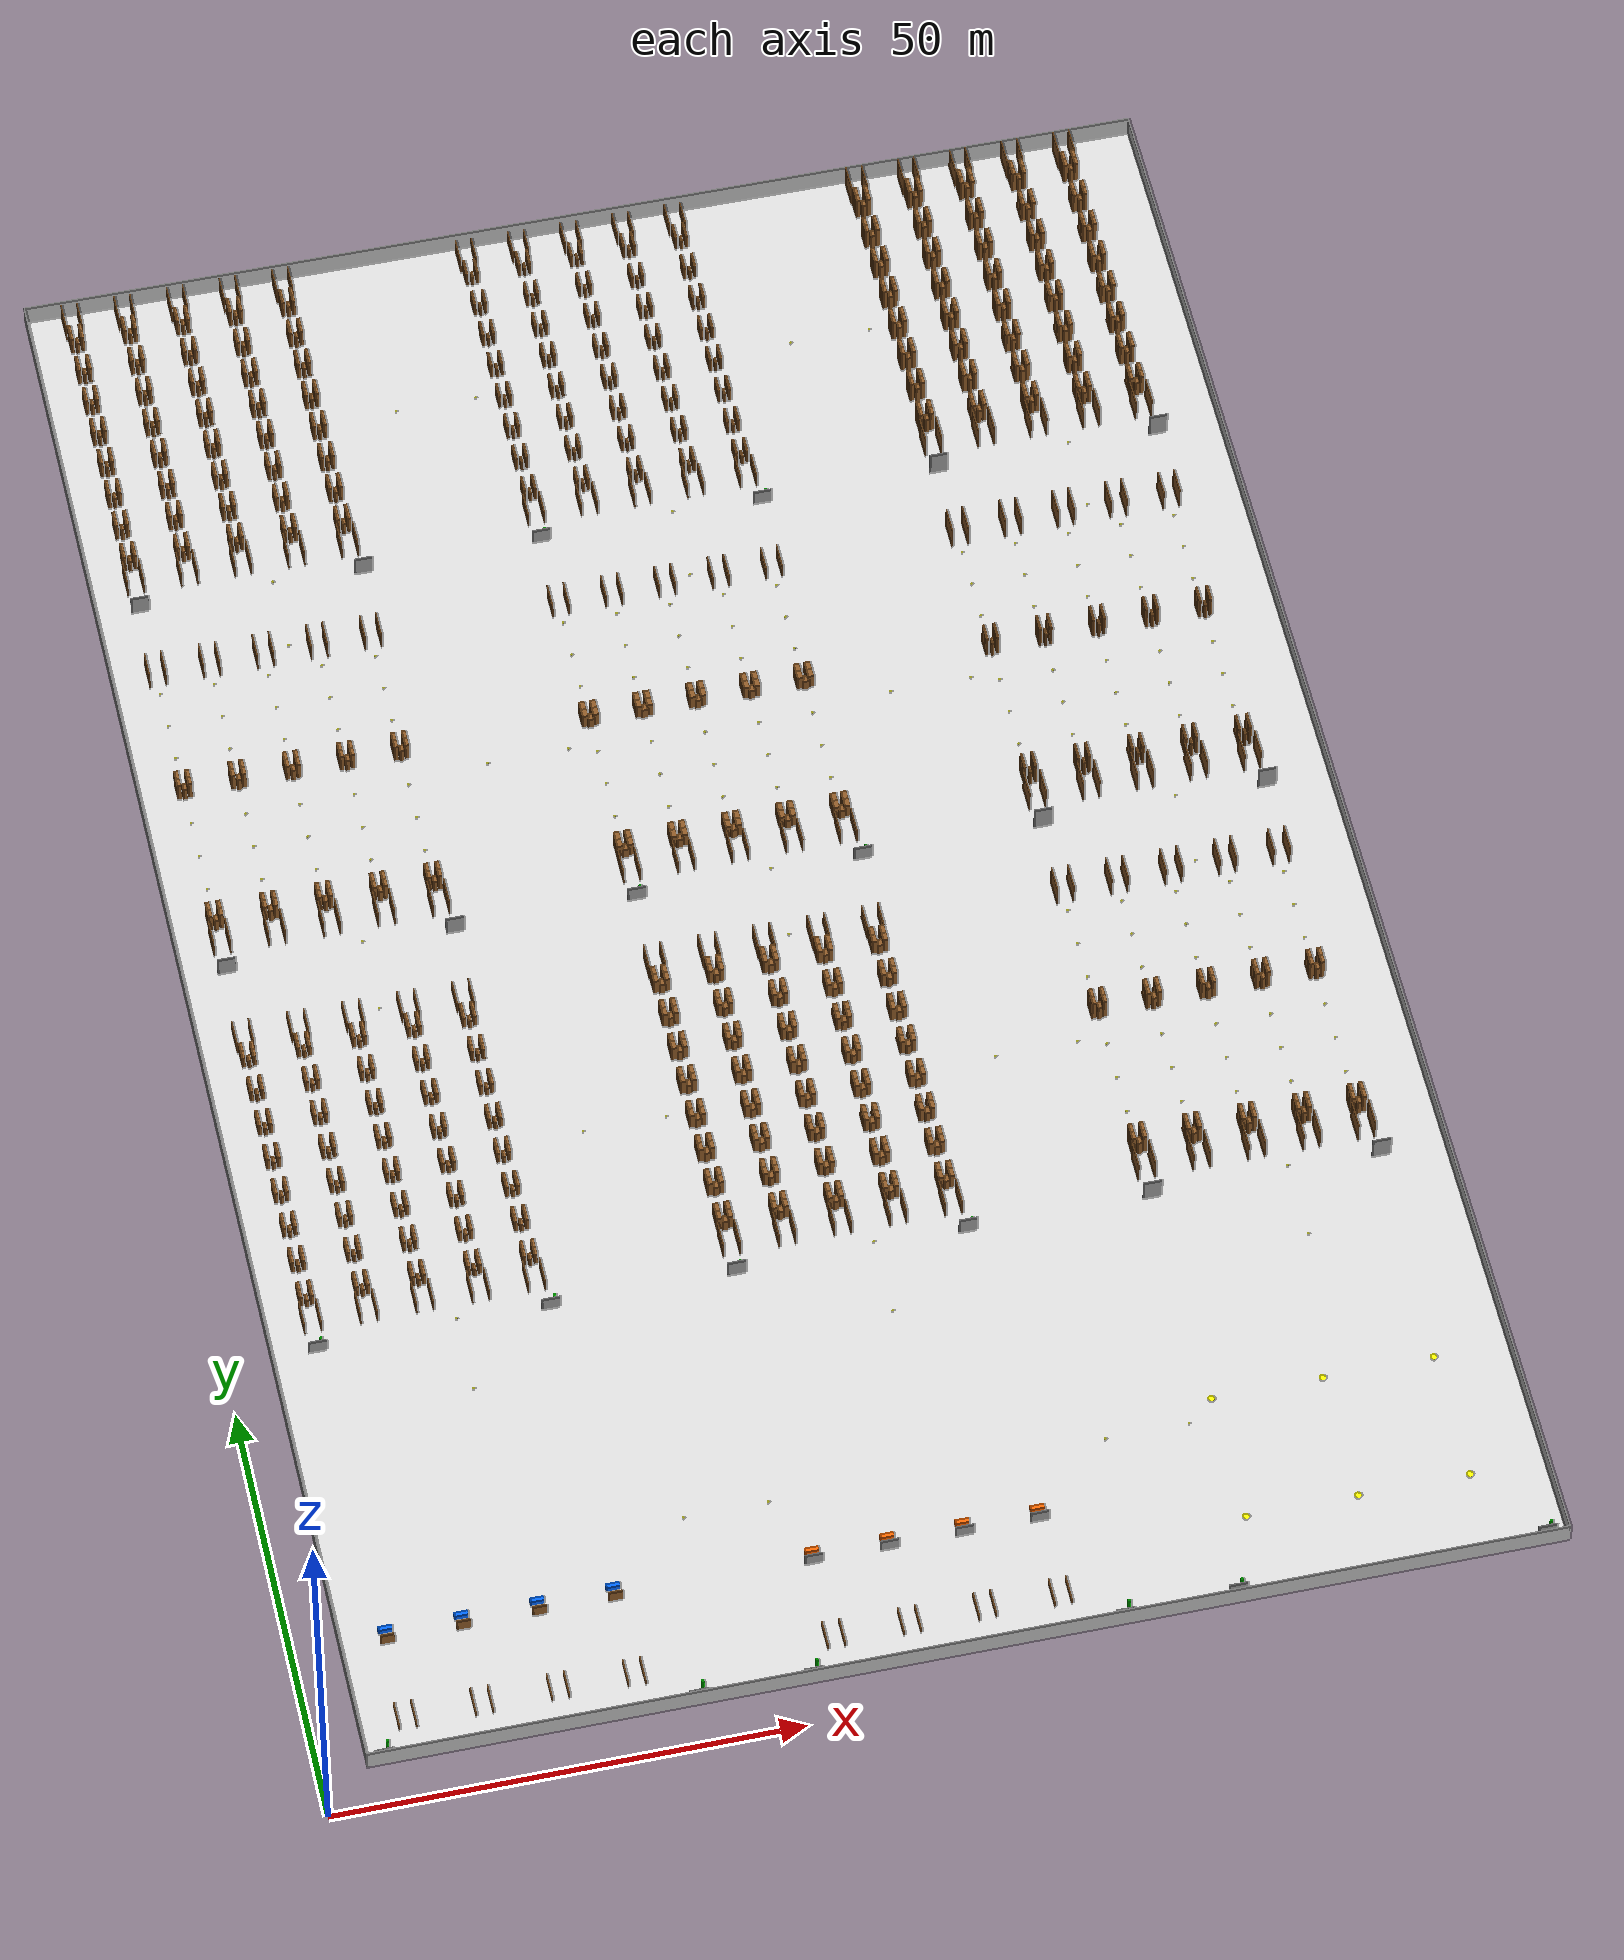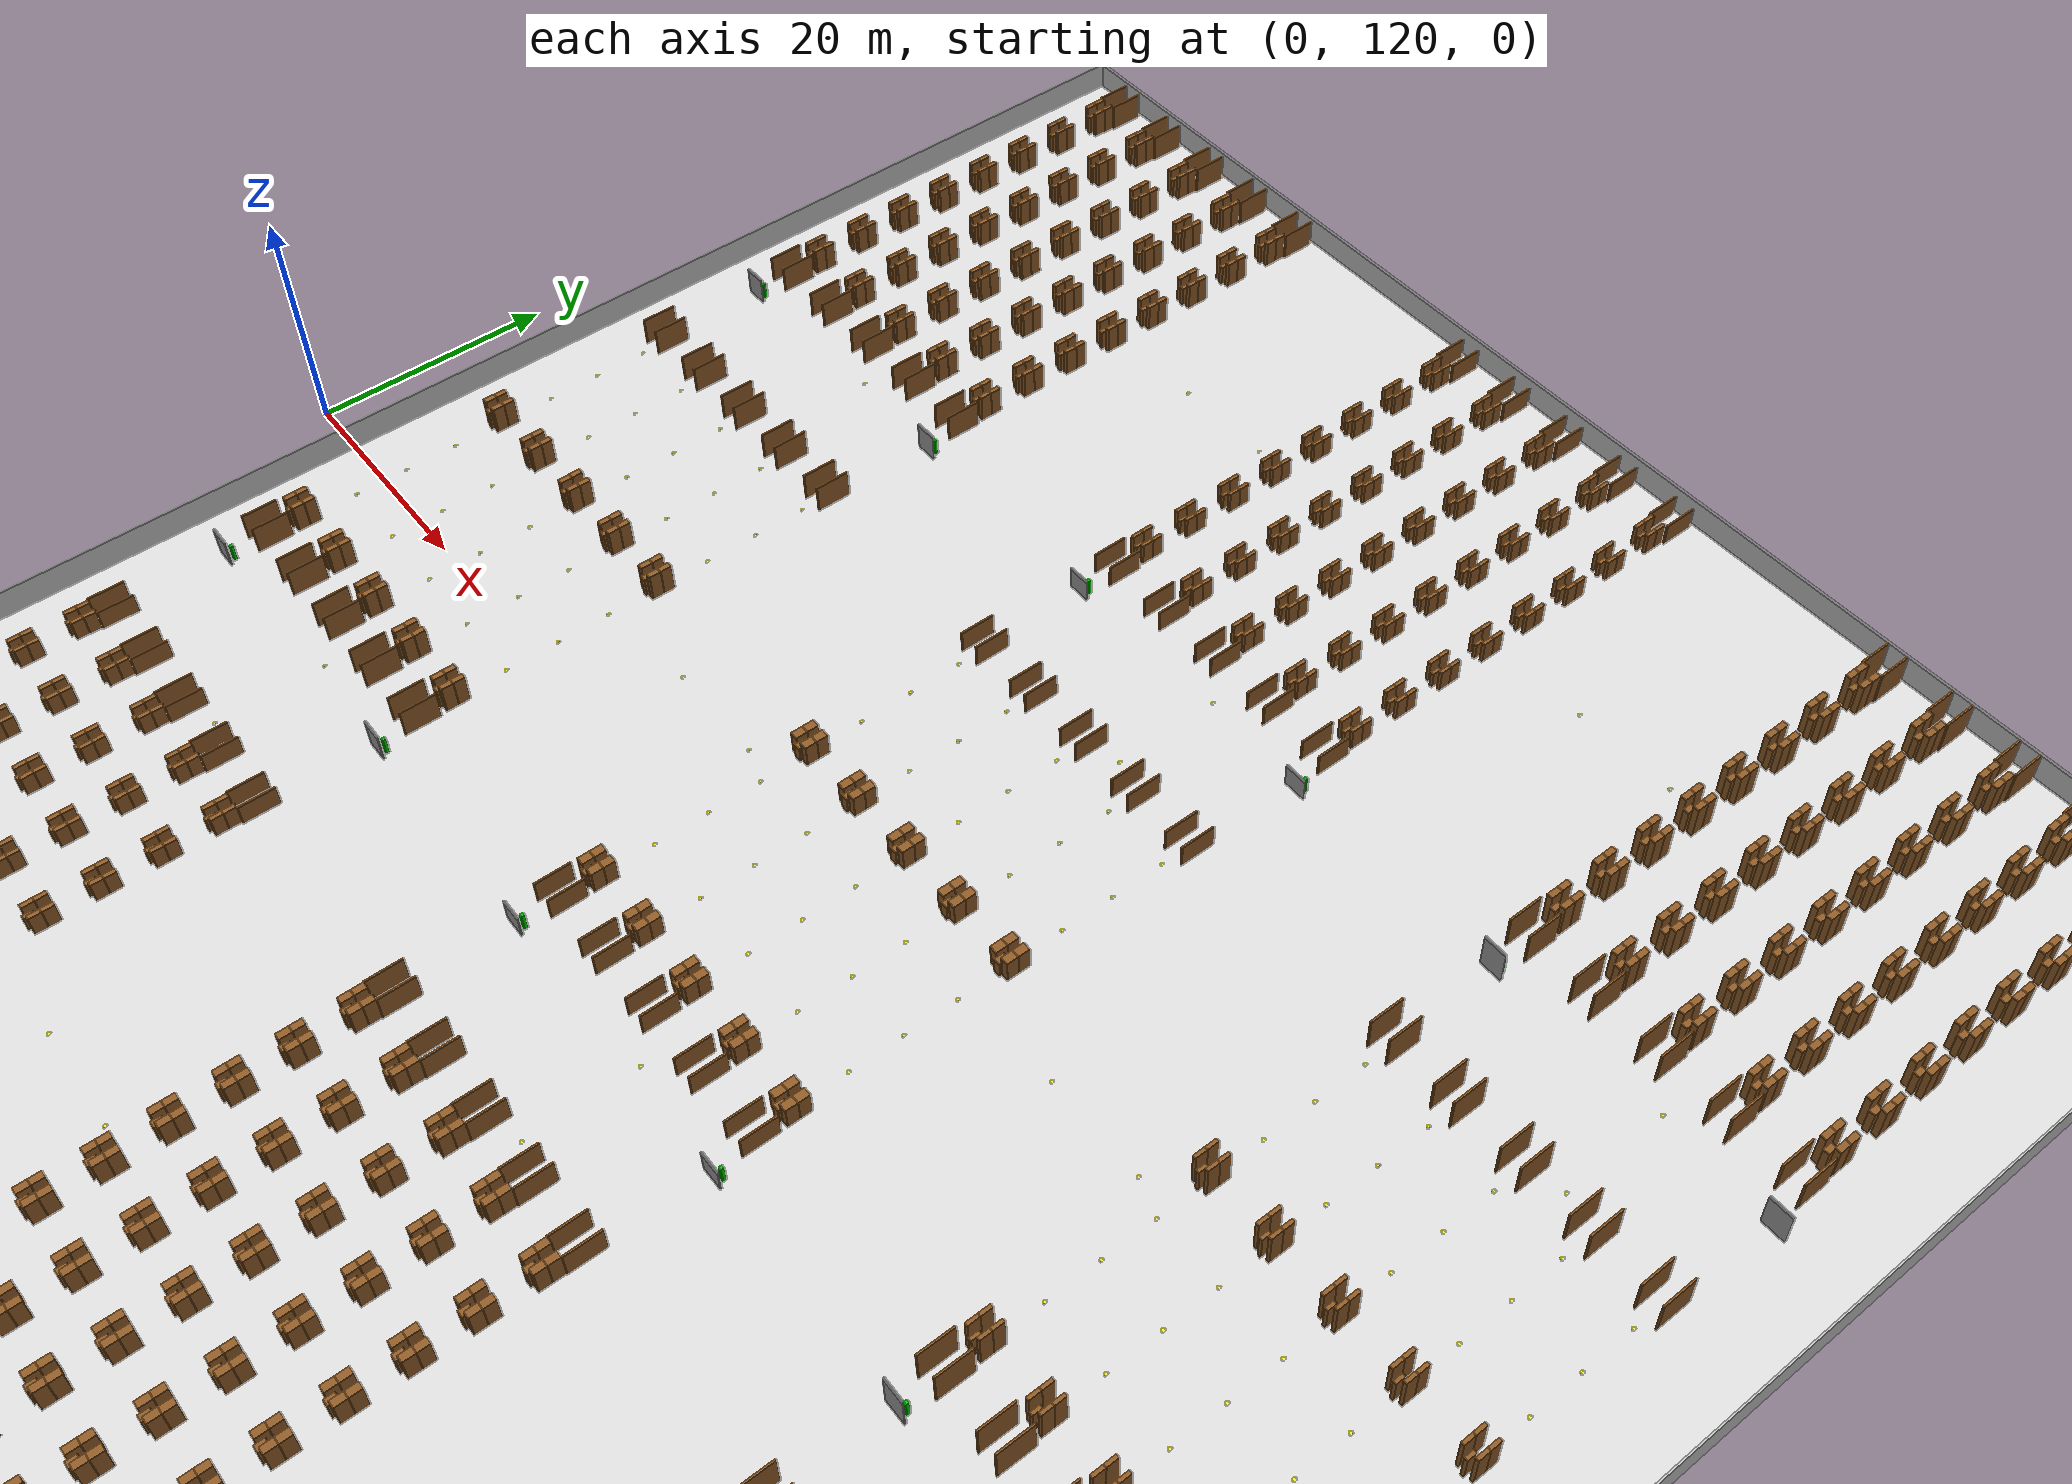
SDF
<?xml version="1.0" ?>
<sdf version="1.9">
  <world name="realistic_warehouse_150x200m">
    <plugin filename="gz-sim-physics-system" name="gz::sim::systems::Physics"/>
    <plugin filename="gz-sim-sensors-system" name="gz::sim::systems::Sensors">
      <render_engine>ogre2</render_engine>
    </plugin>
    <plugin filename="gz-sim-scene-broadcaster-system" name="gz::sim::systems::SceneBroadcaster"/>
    <light name="sun" type="directional">
      <cast_shadows>true</cast_shadows>
      <pose>0 0 10 0 0 0</pose>
      <diffuse>0.8 0.8 0.8 1</diffuse>
      <specular>0.2 0.2 0.2 1</specular>
      <direction>-0.5 0.1 -0.9</direction>
    </light>
    <physics name="default_physics" type="ode">
      <max_step_size>0.001</max_step_size>
      <real_time_factor>1.0</real_time_factor>
      <real_time_update_rate>1000</real_time_update_rate>
    </physics>
    <scene>
      <ambient>0.4 0.4 0.4 1.0</ambient>
      <background>0.7 0.7 0.9 1.0</background>
      <shadows>true</shadows>
    </scene>
    <gravity>0 0 -9.81</gravity>
    <model name="ground_plane">
      <static>true</static>
      <pose>68.5 102.0 0 0 0 0</pose>
      <link name="ground_link">
        <visual name="ground_visual">
          <geometry>
            <box>
              <size>127.0 194.0 0.01</size>
            </box>
          </geometry>
          <material>
            <ambient>0.85 0.85 0.85 1.0</ambient>
            <diffuse>0.85 0.85 0.85 1.0</diffuse>
          </material>
        </visual>
        <collision name="ground_visual_collision">
          <geometry>
            <box>
              <size>127.0 194.0 0.01</size>
            </box>
          </geometry>
        </collision>
        <collision name="ground_collision">
          <geometry>
            <plane>
              <normal>0 0 1</normal>
              <size>127.0 194.0</size>
            </plane>
          </geometry>
        </collision>
      </link>
    </model>
    <model name="wall_north">
      <static>true</static>
      <pose>68.5 199.0 1.25 0 0 0</pose>
      <link name="wall_north_link">
        <visual name="wall_north_visual">
          <geometry>
            <box>
              <size>127.15 0.15 2.5</size>
            </box>
          </geometry>
          <material>
            <ambient>0.75 0.75 0.75 1.0</ambient>
            <diffuse>0.75 0.75 0.75 1.0</diffuse>
          </material>
        </visual>
        <collision name="wall_north_visual_collision">
          <geometry>
            <box>
              <size>127.15 0.15 2.5</size>
            </box>
          </geometry>
        </collision>
      </link>
    </model>
    <model name="wall_south">
      <static>true</static>
      <pose>68.5 5.0 1.25 0 0 0</pose>
      <link name="wall_south_link">
        <visual name="wall_south_visual">
          <geometry>
            <box>
              <size>127.15 0.15 2.5</size>
            </box>
          </geometry>
          <material>
            <ambient>0.75 0.75 0.75 1.0</ambient>
            <diffuse>0.75 0.75 0.75 1.0</diffuse>
          </material>
        </visual>
        <collision name="wall_south_visual_collision">
          <geometry>
            <box>
              <size>127.15 0.15 2.5</size>
            </box>
          </geometry>
        </collision>
      </link>
    </model>
    <model name="wall_east">
      <static>true</static>
      <pose>132.0 102.0 1.25 0 0 0</pose>
      <link name="wall_east_link">
        <visual name="wall_east_visual">
          <geometry>
            <box>
              <size>0.15 194.15 2.5</size>
            </box>
          </geometry>
          <material>
            <ambient>0.75 0.75 0.75 1.0</ambient>
            <diffuse>0.75 0.75 0.75 1.0</diffuse>
          </material>
        </visual>
        <collision name="wall_east_visual_collision">
          <geometry>
            <box>
              <size>0.15 194.15 2.5</size>
            </box>
          </geometry>
        </collision>
      </link>
    </model>
    <model name="wall_west">
      <static>true</static>
      <pose>5.0 102.0 1.25 0 0 0</pose>
      <link name="wall_west_link">
        <visual name="wall_west_visual">
          <geometry>
            <box>
              <size>0.15 194.15 2.5</size>
            </box>
          </geometry>
          <material>
            <ambient>0.75 0.75 0.75 1.0</ambient>
            <diffuse>0.75 0.75 0.75 1.0</diffuse>
          </material>
        </visual>
        <collision name="wall_west_visual_collision">
          <geometry>
            <box>
              <size>0.15 194.15 2.5</size>
            </box>
          </geometry>
        </collision>
      </link>
    </model>
    <model name="dock_wall_Zone_A_C1_001">
      <static>true</static>
      <pose>10.0 156.2 1.25 0 0 0</pose>
      <link name="dock_wall_Zone_A_C1_001_link">
        <visual name="dock_wall_Zone_A_C1_001_vis">
          <geometry>
            <box>
              <size>2.0 0.15 2.5</size>
            </box>
          </geometry>
          <material>
            <ambient>0.6 0.6 0.6 1.0</ambient>
            <diffuse>0.6 0.6 0.6 1.0</diffuse>
          </material>
        </visual>
        <collision name="dock_wall_Zone_A_C1_001_vis_collision">
          <geometry>
            <box>
              <size>2.0 0.15 2.5</size>
            </box>
          </geometry>
        </collision>
      </link>
    </model>
    <model name="charger_Zone_A_C1_002">
      <static>true</static>
      <pose>10.5 156.7 0.75 0 0 0</pose>
      <link name="charger_Zone_A_C1_002_link">
        <visual name="charger_Zone_A_C1_002_vis">
          <geometry>
            <box>
              <size>0.3 0.3 1.5</size>
            </box>
          </geometry>
          <material>
            <ambient>0.0 0.8 0.0 1.0</ambient>
            <diffuse>0.0 0.8 0.0 1.0</diffuse>
          </material>
        </visual>
        <collision name="charger_Zone_A_C1_002_vis_collision">
          <geometry>
            <box>
              <size>0.3 0.3 1.5</size>
            </box>
          </geometry>
        </collision>
      </link>
    </model>
    <model name="dock_wall_Zone_A_C2_003">
      <static>true</static>
      <pose>35.0 156.2 1.25 0 0 0</pose>
      <link name="dock_wall_Zone_A_C2_003_link">
        <visual name="dock_wall_Zone_A_C2_003_vis">
          <geometry>
            <box>
              <size>2.0 0.15 2.5</size>
            </box>
          </geometry>
          <material>
            <ambient>0.6 0.6 0.6 1.0</ambient>
            <diffuse>0.6 0.6 0.6 1.0</diffuse>
          </material>
        </visual>
        <collision name="dock_wall_Zone_A_C2_003_vis_collision">
          <geometry>
            <box>
              <size>2.0 0.15 2.5</size>
            </box>
          </geometry>
        </collision>
      </link>
    </model>
    <model name="charger_Zone_A_C2_004">
      <static>true</static>
      <pose>35.5 156.7 0.75 0 0 0</pose>
      <link name="charger_Zone_A_C2_004_link">
        <visual name="charger_Zone_A_C2_004_vis">
          <geometry>
            <box>
              <size>0.3 0.3 1.5</size>
            </box>
          </geometry>
          <material>
            <ambient>0.0 0.8 0.0 1.0</ambient>
            <diffuse>0.0 0.8 0.0 1.0</diffuse>
          </material>
        </visual>
        <collision name="charger_Zone_A_C2_004_vis_collision">
          <geometry>
            <box>
              <size>0.3 0.3 1.5</size>
            </box>
          </geometry>
        </collision>
      </link>
    </model>
    <model name="cross_Zone_A_entry_005">
      <static>true</static>
      <pose>25.0 157.0 0.01 0 0 0</pose>
      <link name="cross_Zone_A_entry_005_link">
        <visual name="cross_Zone_A_entry_005_vis">
          <geometry>
            <cylinder>
              <radius>0.15</radius>
              <length>0.02</length>
            </cylinder>
          </geometry>
          <material>
            <ambient>0.9 0.9 0.2 1.0</ambient>
            <diffuse>0.9 0.9 0.2 1.0</diffuse>
          </material>
        </visual>
        <collision name="cross_Zone_A_entry_005_vis_collision">
          <geometry>
            <cylinder>
              <radius>0.15</radius>
              <length>0.02</length>
            </cylinder>
          </geometry>
        </collision>
      </link>
    </model>
    <model name="aisle_L_Zone_A_A0_entry_006">
      <static>true</static>
      <pose>9.1 160.0 1.25 0 0 0</pose>
      <link name="aisle_L_Zone_A_A0_entry_006_link">
        <visual name="aisle_L_Zone_A_A0_entry_006_vis">
          <geometry>
            <box>
              <size>0.15 3.0 2.5</size>
            </box>
          </geometry>
          <material>
            <ambient>0.55 0.35 0.15 1.0</ambient>
            <diffuse>0.55 0.35 0.15 1.0</diffuse>
          </material>
        </visual>
        <collision name="aisle_L_Zone_A_A0_entry_006_vis_collision">
          <geometry>
            <box>
              <size>0.15 3.0 2.5</size>
            </box>
          </geometry>
        </collision>
      </link>
    </model>
    <model name="aisle_R_Zone_A_A0_entry_007">
      <static>true</static>
      <pose>10.9 160.0 1.25 0 0 0</pose>
      <link name="aisle_R_Zone_A_A0_entry_007_link">
        <visual name="aisle_R_Zone_A_A0_entry_007_vis">
          <geometry>
            <box>
              <size>0.15 3.0 2.5</size>
            </box>
          </geometry>
          <material>
            <ambient>0.55 0.35 0.15 1.0</ambient>
            <diffuse>0.55 0.35 0.15 1.0</diffuse>
          </material>
        </visual>
        <collision name="aisle_R_Zone_A_A0_entry_007_vis_collision">
          <geometry>
            <box>
              <size>0.15 3.0 2.5</size>
            </box>
          </geometry>
        </collision>
      </link>
    </model>
    <model name="rack_Zone_A_A0_S0_008">
      <static>true</static>
      <pose>9.4 162.5 1.25 0 0 0</pose>
      <link name="rack_Zone_A_A0_S0_008_link">
        <visual name="rack_Zone_A_A0_S0_008_vis">
          <geometry>
            <box>
              <size>0.4 1.0 2.5</size>
            </box>
          </geometry>
          <material>
            <ambient>0.55 0.35 0.15 1.0</ambient>
            <diffuse>0.55 0.35 0.15 1.0</diffuse>
          </material>
        </visual>
        <collision name="rack_Zone_A_A0_S0_008_vis_collision">
          <geometry>
            <box>
              <size>0.4 1.0 2.5</size>
            </box>
          </geometry>
        </collision>
      </link>
    </model>
    <model name="rack_Zone_A_A0_S0_009">
      <static>true</static>
      <pose>9.4 163.5 1.25 0 0 0</pose>
      <link name="rack_Zone_A_A0_S0_009_link">
        <visual name="rack_Zone_A_A0_S0_009_vis">
          <geometry>
            <box>
              <size>0.4 1.0 2.5</size>
            </box>
          </geometry>
          <material>
            <ambient>0.55 0.35 0.15 1.0</ambient>
            <diffuse>0.55 0.35 0.15 1.0</diffuse>
          </material>
        </visual>
        <collision name="rack_Zone_A_A0_S0_009_vis_collision">
          <geometry>
            <box>
              <size>0.4 1.0 2.5</size>
            </box>
          </geometry>
        </collision>
      </link>
    </model>
    <model name="rack_Zone_A_A0_S0_010">
      <static>true</static>
      <pose>10.6 162.5 1.25 0 0 0</pose>
      <link name="rack_Zone_A_A0_S0_010_link">
        <visual name="rack_Zone_A_A0_S0_010_vis">
          <geometry>
            <box>
              <size>0.4 1.0 2.5</size>
            </box>
          </geometry>
          <material>
            <ambient>0.55 0.35 0.15 1.0</ambient>
            <diffuse>0.55 0.35 0.15 1.0</diffuse>
          </material>
        </visual>
        <collision name="rack_Zone_A_A0_S0_010_vis_collision">
          <geometry>
            <box>
              <size>0.4 1.0 2.5</size>
            </box>
          </geometry>
        </collision>
      </link>
    </model>
    <model name="rack_Zone_A_A0_S0_011">
      <static>true</static>
      <pose>10.6 163.5 1.25 0 0 0</pose>
      <link name="rack_Zone_A_A0_S0_011_link">
        <visual name="rack_Zone_A_A0_S0_011_vis">
          <geometry>
            <box>
              <size>0.4 1.0 2.5</size>
            </box>
          </geometry>
          <material>
            <ambient>0.55 0.35 0.15 1.0</ambient>
            <diffuse>0.55 0.35 0.15 1.0</diffuse>
          </material>
        </visual>
        <collision name="rack_Zone_A_A0_S0_011_vis_collision">
          <geometry>
            <box>
              <size>0.4 1.0 2.5</size>
            </box>
          </geometry>
        </collision>
      </link>
    </model>
    <model name="rack_Zone_A_A0_S0_012">
      <static>true</static>
      <pose>10.0 162.2 0.9375 0 0 0</pose>
      <link name="rack_Zone_A_A0_S0_012_link">
        <visual name="rack_Zone_A_A0_S0_012_vis">
          <geometry>
            <box>
              <size>0.4 0.8 1.875</size>
            </box>
          </geometry>
          <material>
            <ambient>0.55 0.35 0.15 1.0</ambient>
            <diffuse>0.55 0.35 0.15 1.0</diffuse>
          </material>
        </visual>
        <collision name="rack_Zone_A_A0_S0_012_vis_collision">
          <geometry>
            <box>
              <size>0.4 0.8 1.875</size>
            </box>
          </geometry>
        </collision>
      </link>
    </model>
    <model name="rack_Zone_A_A0_S1_013">
      <static>true</static>
      <pose>9.4 167.0 1.25 0 0 0</pose>
      <link name="rack_Zone_A_A0_S1_013_link">
        <visual name="rack_Zone_A_A0_S1_013_vis">
          <geometry>
            <box>
              <size>0.4 1.0 2.5</size>
            </box>
          </geometry>
          <material>
            <ambient>0.55 0.35 0.15 1.0</ambient>
            <diffuse>0.55 0.35 0.15 1.0</diffuse>
          </material>
        </visual>
        <collision name="rack_Zone_A_A0_S1_013_vis_collision">
          <geometry>
            <box>
              <size>0.4 1.0 2.5</size>
            </box>
          </geometry>
        </collision>
      </link>
    </model>
    <model name="rack_Zone_A_A0_S1_014">
      <static>true</static>
      <pose>9.4 168.0 1.25 0 0 0</pose>
      <link name="rack_Zone_A_A0_S1_014_link">
        <visual name="rack_Zone_A_A0_S1_014_vis">
          <geometry>
            <box>
              <size>0.4 1.0 2.5</size>
            </box>
          </geometry>
          <material>
            <ambient>0.55 0.35 0.15 1.0</ambient>
            <diffuse>0.55 0.35 0.15 1.0</diffuse>
          </material>
        </visual>
        <collision name="rack_Zone_A_A0_S1_014_vis_collision">
          <geometry>
            <box>
              <size>0.4 1.0 2.5</size>
            </box>
          </geometry>
        </collision>
      </link>
    </model>
    <model name="rack_Zone_A_A0_S1_015">
      <static>true</static>
      <pose>10.6 167.0 1.25 0 0 0</pose>
      <link name="rack_Zone_A_A0_S1_015_link">
        <visual name="rack_Zone_A_A0_S1_015_vis">
          <geometry>
            <box>
              <size>0.4 1.0 2.5</size>
            </box>
          </geometry>
          <material>
            <ambient>0.55 0.35 0.15 1.0</ambient>
            <diffuse>0.55 0.35 0.15 1.0</diffuse>
          </material>
        </visual>
        <collision name="rack_Zone_A_A0_S1_015_vis_collision">
          <geometry>
            <box>
              <size>0.4 1.0 2.5</size>
            </box>
          </geometry>
        </collision>
      </link>
    </model>
    <model name="rack_Zone_A_A0_S1_016">
      <static>true</static>
      <pose>10.6 168.0 1.25 0 0 0</pose>
      <link name="rack_Zone_A_A0_S1_016_link">
        <visual name="rack_Zone_A_A0_S1_016_vis">
          <geometry>
            <box>
              <size>0.4 1.0 2.5</size>
            </box>
          </geometry>
          <material>
            <ambient>0.55 0.35 0.15 1.0</ambient>
            <diffuse>0.55 0.35 0.15 1.0</diffuse>
          </material>
        </visual>
        <collision name="rack_Zone_A_A0_S1_016_vis_collision">
          <geometry>
            <box>
              <size>0.4 1.0 2.5</size>
            </box>
          </geometry>
        </collision>
      </link>
    </model>
    <model name="rack_Zone_A_A0_S1_017">
      <static>true</static>
      <pose>10.0 166.7 0.9375 0 0 0</pose>
      <link name="rack_Zone_A_A0_S1_017_link">
        <visual name="rack_Zone_A_A0_S1_017_vis">
          <geometry>
            <box>
              <size>0.4 0.8 1.875</size>
            </box>
          </geometry>
          <material>
            <ambient>0.55 0.35 0.15 1.0</ambient>
            <diffuse>0.55 0.35 0.15 1.0</diffuse>
          </material>
        </visual>
        <collision name="rack_Zone_A_A0_S1_017_vis_collision">
          <geometry>
            <box>
              <size>0.4 0.8 1.875</size>
            </box>
          </geometry>
        </collision>
      </link>
    </model>
    <model name="rack_Zone_A_A0_S2_018">
      <static>true</static>
      <pose>9.4 171.5 1.25 0 0 0</pose>
      <link name="rack_Zone_A_A0_S2_018_link">
        <visual name="rack_Zone_A_A0_S2_018_vis">
          <geometry>
            <box>
              <size>0.4 1.0 2.5</size>
            </box>
          </geometry>
          <material>
            <ambient>0.55 0.35 0.15 1.0</ambient>
            <diffuse>0.55 0.35 0.15 1.0</diffuse>
          </material>
        </visual>
        <collision name="rack_Zone_A_A0_S2_018_vis_collision">
          <geometry>
            <box>
              <size>0.4 1.0 2.5</size>
            </box>
          </geometry>
        </collision>
      </link>
    </model>
    <model name="rack_Zone_A_A0_S2_019">
      <static>true</static>
      <pose>9.4 172.5 1.25 0 0 0</pose>
      <link name="rack_Zone_A_A0_S2_019_link">
        <visual name="rack_Zone_A_A0_S2_019_vis">
          <geometry>
            <box>
              <size>0.4 1.0 2.5</size>
            </box>
          </geometry>
          <material>
            <ambient>0.55 0.35 0.15 1.0</ambient>
            <diffuse>0.55 0.35 0.15 1.0</diffuse>
          </material>
        </visual>
        <collision name="rack_Zone_A_A0_S2_019_vis_collision">
          <geometry>
            <box>
              <size>0.4 1.0 2.5</size>
            </box>
          </geometry>
        </collision>
      </link>
    </model>
    <model name="rack_Zone_A_A0_S2_020">
      <static>true</static>
      <pose>10.6 171.5 1.25 0 0 0</pose>
      <link name="rack_Zone_A_A0_S2_020_link">
        <visual name="rack_Zone_A_A0_S2_020_vis">
          <geometry>
            <box>
              <size>0.4 1.0 2.5</size>
            </box>
          </geometry>
          <material>
            <ambient>0.55 0.35 0.15 1.0</ambient>
            <diffuse>0.55 0.35 0.15 1.0</diffuse>
          </material>
        </visual>
        <collision name="rack_Zone_A_A0_S2_020_vis_collision">
          <geometry>
            <box>
              <size>0.4 1.0 2.5</size>
            </box>
          </geometry>
        </collision>
      </link>
    </model>
    <model name="rack_Zone_A_A0_S2_021">
      <static>true</static>
      <pose>10.6 172.5 1.25 0 0 0</pose>
      <link name="rack_Zone_A_A0_S2_021_link">
        <visual name="rack_Zone_A_A0_S2_021_vis">
          <geometry>
            <box>
              <size>0.4 1.0 2.5</size>
            </box>
          </geometry>
          <material>
            <ambient>0.55 0.35 0.15 1.0</ambient>
            <diffuse>0.55 0.35 0.15 1.0</diffuse>
          </material>
        </visual>
        <collision name="rack_Zone_A_A0_S2_021_vis_collision">
          <geometry>
            <box>
              <size>0.4 1.0 2.5</size>
            </box>
          </geometry>
        </collision>
      </link>
    </model>
    <model name="rack_Zone_A_A0_S2_022">
      <static>true</static>
      <pose>10.0 171.2 0.9375 0 0 0</pose>
      <link name="rack_Zone_A_A0_S2_022_link">
        <visual name="rack_Zone_A_A0_S2_022_vis">
          <geometry>
            <box>
              <size>0.4 0.8 1.875</size>
            </box>
          </geometry>
          <material>
            <ambient>0.55 0.35 0.15 1.0</ambient>
            <diffuse>0.55 0.35 0.15 1.0</diffuse>
          </material>
        </visual>
        <collision name="rack_Zone_A_A0_S2_022_vis_collision">
          <geometry>
            <box>
              <size>0.4 0.8 1.875</size>
            </box>
          </geometry>
        </collision>
      </link>
    </model>
    <model name="rack_Zone_A_A0_S3_023">
      <static>true</static>
      <pose>9.4 176.0 1.25 0 0 0</pose>
      <link name="rack_Zone_A_A0_S3_023_link">
        <visual name="rack_Zone_A_A0_S3_023_vis">
          <geometry>
            <box>
              <size>0.4 1.0 2.5</size>
            </box>
          </geometry>
          <material>
            <ambient>0.55 0.35 0.15 1.0</ambient>
            <diffuse>0.55 0.35 0.15 1.0</diffuse>
          </material>
        </visual>
        <collision name="rack_Zone_A_A0_S3_023_vis_collision">
          <geometry>
            <box>
              <size>0.4 1.0 2.5</size>
            </box>
          </geometry>
        </collision>
      </link>
    </model>
    <model name="rack_Zone_A_A0_S3_024">
      <static>true</static>
      <pose>9.4 177.0 1.25 0 0 0</pose>
      <link name="rack_Zone_A_A0_S3_024_link">
        <visual name="rack_Zone_A_A0_S3_024_vis">
          <geometry>
            <box>
              <size>0.4 1.0 2.5</size>
            </box>
          </geometry>
          <material>
            <ambient>0.55 0.35 0.15 1.0</ambient>
            <diffuse>0.55 0.35 0.15 1.0</diffuse>
          </material>
        </visual>
        <collision name="rack_Zone_A_A0_S3_024_vis_collision">
          <geometry>
            <box>
              <size>0.4 1.0 2.5</size>
            </box>
          </geometry>
        </collision>
      </link>
    </model>
    <model name="rack_Zone_A_A0_S3_025">
      <static>true</static>
      <pose>10.6 176.0 1.25 0 0 0</pose>
      <link name="rack_Zone_A_A0_S3_025_link">
        <visual name="rack_Zone_A_A0_S3_025_vis">
          <geometry>
            <box>
              <size>0.4 1.0 2.5</size>
            </box>
          </geometry>
          <material>
            <ambient>0.55 0.35 0.15 1.0</ambient>
            <diffuse>0.55 0.35 0.15 1.0</diffuse>
          </material>
        </visual>
        <collision name="rack_Zone_A_A0_S3_025_vis_collision">
          <geometry>
            <box>
              <size>0.4 1.0 2.5</size>
            </box>
          </geometry>
        </collision>
      </link>
    </model>
    <model name="rack_Zone_A_A0_S3_026">
      <static>true</static>
      <pose>10.6 177.0 1.25 0 0 0</pose>
      <link name="rack_Zone_A_A0_S3_026_link">
        <visual name="rack_Zone_A_A0_S3_026_vis">
          <geometry>
            <box>
              <size>0.4 1.0 2.5</size>
            </box>
          </geometry>
          <material>
            <ambient>0.55 0.35 0.15 1.0</ambient>
            <diffuse>0.55 0.35 0.15 1.0</diffuse>
          </material>
        </visual>
        <collision name="rack_Zone_A_A0_S3_026_vis_collision">
          <geometry>
            <box>
              <size>0.4 1.0 2.5</size>
            </box>
          </geometry>
        </collision>
      </link>
    </model>
    <model name="rack_Zone_A_A0_S3_027">
      <static>true</static>
      <pose>10.0 175.7 0.9375 0 0 0</pose>
      <link name="rack_Zone_A_A0_S3_027_link">
        <visual name="rack_Zone_A_A0_S3_027_vis">
          <geometry>
            <box>
              <size>0.4 0.8 1.875</size>
            </box>
          </geometry>
          <material>
            <ambient>0.55 0.35 0.15 1.0</ambient>
            <diffuse>0.55 0.35 0.15 1.0</diffuse>
          </material>
        </visual>
        <collision name="rack_Zone_A_A0_S3_027_vis_collision">
          <geometry>
            <box>
              <size>0.4 0.8 1.875</size>
            </box>
          </geometry>
        </collision>
      </link>
    </model>
    <model name="rack_Zone_A_A0_S4_028">
      <static>true</static>
      <pose>9.4 180.5 1.25 0 0 0</pose>
      <link name="rack_Zone_A_A0_S4_028_link">
        <visual name="rack_Zone_A_A0_S4_028_vis">
          <geometry>
            <box>
              <size>0.4 1.0 2.5</size>
            </box>
          </geometry>
          <material>
            <ambient>0.55 0.35 0.15 1.0</ambient>
            <diffuse>0.55 0.35 0.15 1.0</diffuse>
          </material>
        </visual>
        <collision name="rack_Zone_A_A0_S4_028_vis_collision">
          <geometry>
            <box>
              <size>0.4 1.0 2.5</size>
            </box>
          </geometry>
        </collision>
      </link>
    </model>
    <model name="rack_Zone_A_A0_S4_029">
      <static>true</static>
      <pose>9.4 181.5 1.25 0 0 0</pose>
      <link name="rack_Zone_A_A0_S4_029_link">
        <visual name="rack_Zone_A_A0_S4_029_vis">
          <geometry>
            <box>
              <size>0.4 1.0 2.5</size>
            </box>
          </geometry>
          <material>
            <ambient>0.55 0.35 0.15 1.0</ambient>
            <diffuse>0.55 0.35 0.15 1.0</diffuse>
          </material>
        </visual>
        <collision name="rack_Zone_A_A0_S4_029_vis_collision">
          <geometry>
            <box>
              <size>0.4 1.0 2.5</size>
            </box>
          </geometry>
        </collision>
      </link>
    </model>
    <model name="rack_Zone_A_A0_S4_030">
      <static>true</static>
      <pose>10.6 180.5 1.25 0 0 0</pose>
      <link name="rack_Zone_A_A0_S4_030_link">
        <visual name="rack_Zone_A_A0_S4_030_vis">
          <geometry>
            <box>
              <size>0.4 1.0 2.5</size>
            </box>
          </geometry>
          <material>
            <ambient>0.55 0.35 0.15 1.0</ambient>
            <diffuse>0.55 0.35 0.15 1.0</diffuse>
          </material>
        </visual>
        <collision name="rack_Zone_A_A0_S4_030_vis_collision">
          <geometry>
            <box>
              <size>0.4 1.0 2.5</size>
            </box>
          </geometry>
        </collision>
      </link>
    </model>
    <model name="rack_Zone_A_A0_S4_031">
      <static>true</static>
      <pose>10.6 181.5 1.25 0 0 0</pose>
      <link name="rack_Zone_A_A0_S4_031_link">
        <visual name="rack_Zone_A_A0_S4_031_vis">
          <geometry>
            <box>
              <size>0.4 1.0 2.5</size>
            </box>
          </geometry>
          <material>
            <ambient>0.55 0.35 0.15 1.0</ambient>
            <diffuse>0.55 0.35 0.15 1.0</diffuse>
          </material>
        </visual>
        <collision name="rack_Zone_A_A0_S4_031_vis_collision">
          <geometry>
            <box>
              <size>0.4 1.0 2.5</size>
            </box>
          </geometry>
        </collision>
      </link>
    </model>
    <model name="rack_Zone_A_A0_S4_032">
      <static>true</static>
      <pose>10.0 180.2 0.9375 0 0 0</pose>
      <link name="rack_Zone_A_A0_S4_032_link">
        <visual name="rack_Zone_A_A0_S4_032_vis">
          <geometry>
            <box>
              <size>0.4 0.8 1.875</size>
            </box>
          </geometry>
          <material>
            <ambient>0.55 0.35 0.15 1.0</ambient>
            <diffuse>0.55 0.35 0.15 1.0</diffuse>
          </material>
        </visual>
        <collision name="rack_Zone_A_A0_S4_032_vis_collision">
          <geometry>
            <box>
              <size>0.4 0.8 1.875</size>
            </box>
          </geometry>
        </collision>
      </link>
    </model>
    <model name="rack_Zone_A_A0_S5_033">
      <static>true</static>
      <pose>9.4 185.0 1.25 0 0 0</pose>
      <link name="rack_Zone_A_A0_S5_033_link">
        <visual name="rack_Zone_A_A0_S5_033_vis">
          <geometry>
            <box>
              <size>0.4 1.0 2.5</size>
            </box>
          </geometry>
          <material>
            <ambient>0.55 0.35 0.15 1.0</ambient>
            <diffuse>0.55 0.35 0.15 1.0</diffuse>
          </material>
        </visual>
        <collision name="rack_Zone_A_A0_S5_033_vis_collision">
          <geometry>
            <box>
              <size>0.4 1.0 2.5</size>
            </box>
          </geometry>
        </collision>
      </link>
    </model>
    <model name="rack_Zone_A_A0_S5_034">
      <static>true</static>
      <pose>9.4 186.0 1.25 0 0 0</pose>
      <link name="rack_Zone_A_A0_S5_034_link">
        <visual name="rack_Zone_A_A0_S5_034_vis">
          <geometry>
            <box>
              <size>0.4 1.0 2.5</size>
            </box>
          </geometry>
          <material>
            <ambient>0.55 0.35 0.15 1.0</ambient>
            <diffuse>0.55 0.35 0.15 1.0</diffuse>
          </material>
        </visual>
        <collision name="rack_Zone_A_A0_S5_034_vis_collision">
          <geometry>
            <box>
              <size>0.4 1.0 2.5</size>
            </box>
          </geometry>
        </collision>
      </link>
    </model>
    <model name="rack_Zone_A_A0_S5_035">
      <static>true</static>
      <pose>10.6 185.0 1.25 0 0 0</pose>
      <link name="rack_Zone_A_A0_S5_035_link">
        <visual name="rack_Zone_A_A0_S5_035_vis">
          <geometry>
            <box>
              <size>0.4 1.0 2.5</size>
            </box>
          </geometry>
          <material>
            <ambient>0.55 0.35 0.15 1.0</ambient>
            <diffuse>0.55 0.35 0.15 1.0</diffuse>
          </material>
        </visual>
        <collision name="rack_Zone_A_A0_S5_035_vis_collision">
          <geometry>
            <box>
              <size>0.4 1.0 2.5</size>
            </box>
          </geometry>
        </collision>
      </link>
    </model>
    <model name="rack_Zone_A_A0_S5_036">
      <static>true</static>
      <pose>10.6 186.0 1.25 0 0 0</pose>
      <link name="rack_Zone_A_A0_S5_036_link">
        <visual name="rack_Zone_A_A0_S5_036_vis">
          <geometry>
            <box>
              <size>0.4 1.0 2.5</size>
            </box>
          </geometry>
          <material>
            <ambient>0.55 0.35 0.15 1.0</ambient>
            <diffuse>0.55 0.35 0.15 1.0</diffuse>
          </material>
        </visual>
        <collision name="rack_Zone_A_A0_S5_036_vis_collision">
          <geometry>
            <box>
              <size>0.4 1.0 2.5</size>
            </box>
          </geometry>
        </collision>
      </link>
    </model>
    <model name="rack_Zone_A_A0_S5_037">
      <static>true</static>
      <pose>10.0 184.7 0.9375 0 0 0</pose>
      <link name="rack_Zone_A_A0_S5_037_link">
        <visual name="rack_Zone_A_A0_S5_037_vis">
          <geometry>
            <box>
              <size>0.4 0.8 1.875</size>
            </box>
          </geometry>
          <material>
            <ambient>0.55 0.35 0.15 1.0</ambient>
            <diffuse>0.55 0.35 0.15 1.0</diffuse>
          </material>
        </visual>
        <collision name="rack_Zone_A_A0_S5_037_vis_collision">
          <geometry>
            <box>
              <size>0.4 0.8 1.875</size>
            </box>
          </geometry>
        </collision>
      </link>
    </model>
    <model name="rack_Zone_A_A0_S6_038">
      <static>true</static>
      <pose>9.4 189.5 1.25 0 0 0</pose>
      <link name="rack_Zone_A_A0_S6_038_link">
        <visual name="rack_Zone_A_A0_S6_038_vis">
          <geometry>
            <box>
              <size>0.4 1.0 2.5</size>
            </box>
          </geometry>
          <material>
            <ambient>0.55 0.35 0.15 1.0</ambient>
            <diffuse>0.55 0.35 0.15 1.0</diffuse>
          </material>
        </visual>
        <collision name="rack_Zone_A_A0_S6_038_vis_collision">
          <geometry>
            <box>
              <size>0.4 1.0 2.5</size>
            </box>
          </geometry>
        </collision>
      </link>
    </model>
    <model name="rack_Zone_A_A0_S6_039">
      <static>true</static>
      <pose>9.4 190.5 1.25 0 0 0</pose>
      <link name="rack_Zone_A_A0_S6_039_link">
        <visual name="rack_Zone_A_A0_S6_039_vis">
          <geometry>
            <box>
              <size>0.4 1.0 2.5</size>
            </box>
          </geometry>
          <material>
            <ambient>0.55 0.35 0.15 1.0</ambient>
            <diffuse>0.55 0.35 0.15 1.0</diffuse>
          </material>
        </visual>
        <collision name="rack_Zone_A_A0_S6_039_vis_collision">
          <geometry>
            <box>
              <size>0.4 1.0 2.5</size>
            </box>
          </geometry>
        </collision>
      </link>
    </model>
    <model name="rack_Zone_A_A0_S6_040">
      <static>true</static>
      <pose>10.6 189.5 1.25 0 0 0</pose>
      <link name="rack_Zone_A_A0_S6_040_link">
        <visual name="rack_Zone_A_A0_S6_040_vis">
          <geometry>
            <box>
              <size>0.4 1.0 2.5</size>
            </box>
          </geometry>
          <material>
            <ambient>0.55 0.35 0.15 1.0</ambient>
            <diffuse>0.55 0.35 0.15 1.0</diffuse>
          </material>
        </visual>
        <collision name="rack_Zone_A_A0_S6_040_vis_collision">
          <geometry>
            <box>
              <size>0.4 1.0 2.5</size>
            </box>
          </geometry>
        </collision>
      </link>
    </model>
    <model name="rack_Zone_A_A0_S6_041">
      <static>true</static>
      <pose>10.6 190.5 1.25 0 0 0</pose>
      <link name="rack_Zone_A_A0_S6_041_link">
        <visual name="rack_Zone_A_A0_S6_041_vis">
          <geometry>
            <box>
              <size>0.4 1.0 2.5</size>
            </box>
          </geometry>
          <material>
            <ambient>0.55 0.35 0.15 1.0</ambient>
            <diffuse>0.55 0.35 0.15 1.0</diffuse>
          </material>
        </visual>
        <collision name="rack_Zone_A_A0_S6_041_vis_collision">
          <geometry>
            <box>
              <size>0.4 1.0 2.5</size>
            </box>
          </geometry>
        </collision>
      </link>
    </model>
    <model name="rack_Zone_A_A0_S6_042">
      <static>true</static>
      <pose>10.0 189.2 0.9375 0 0 0</pose>
      <link name="rack_Zone_A_A0_S6_042_link">
        <visual name="rack_Zone_A_A0_S6_042_vis">
          <geometry>
            <box>
              <size>0.4 0.8 1.875</size>
            </box>
          </geometry>
          <material>
            <ambient>0.55 0.35 0.15 1.0</ambient>
            <diffuse>0.55 0.35 0.15 1.0</diffuse>
          </material>
        </visual>
        <collision name="rack_Zone_A_A0_S6_042_vis_collision">
          <geometry>
            <box>
              <size>0.4 0.8 1.875</size>
            </box>
          </geometry>
        </collision>
      </link>
    </model>
    <model name="rack_Zone_A_A0_S7_043">
      <static>true</static>
      <pose>9.4 194.0 1.25 0 0 0</pose>
      <link name="rack_Zone_A_A0_S7_043_link">
        <visual name="rack_Zone_A_A0_S7_043_vis">
          <geometry>
            <box>
              <size>0.4 1.0 2.5</size>
            </box>
          </geometry>
          <material>
            <ambient>0.55 0.35 0.15 1.0</ambient>
            <diffuse>0.55 0.35 0.15 1.0</diffuse>
          </material>
        </visual>
        <collision name="rack_Zone_A_A0_S7_043_vis_collision">
          <geometry>
            <box>
              <size>0.4 1.0 2.5</size>
            </box>
          </geometry>
        </collision>
      </link>
    </model>
    <model name="rack_Zone_A_A0_S7_044">
      <static>true</static>
      <pose>9.4 195.0 1.25 0 0 0</pose>
      <link name="rack_Zone_A_A0_S7_044_link">
        <visual name="rack_Zone_A_A0_S7_044_vis">
          <geometry>
            <box>
              <size>0.4 1.0 2.5</size>
            </box>
          </geometry>
          <material>
            <ambient>0.55 0.35 0.15 1.0</ambient>
            <diffuse>0.55 0.35 0.15 1.0</diffuse>
          </material>
        </visual>
        <collision name="rack_Zone_A_A0_S7_044_vis_collision">
          <geometry>
            <box>
              <size>0.4 1.0 2.5</size>
            </box>
          </geometry>
        </collision>
      </link>
    </model>
    <model name="rack_Zone_A_A0_S7_045">
      <static>true</static>
      <pose>10.6 194.0 1.25 0 0 0</pose>
      <link name="rack_Zone_A_A0_S7_045_link">
        <visual name="rack_Zone_A_A0_S7_045_vis">
          <geometry>
            <box>
              <size>0.4 1.0 2.5</size>
            </box>
          </geometry>
          <material>
            <ambient>0.55 0.35 0.15 1.0</ambient>
            <diffuse>0.55 0.35 0.15 1.0</diffuse>
          </material>
        </visual>
        <collision name="rack_Zone_A_A0_S7_045_vis_collision">
          <geometry>
            <box>
              <size>0.4 1.0 2.5</size>
            </box>
          </geometry>
        </collision>
      </link>
    </model>
    <model name="rack_Zone_A_A0_S7_046">
      <static>true</static>
      <pose>10.6 195.0 1.25 0 0 0</pose>
      <link name="rack_Zone_A_A0_S7_046_link">
        <visual name="rack_Zone_A_A0_S7_046_vis">
          <geometry>
            <box>
              <size>0.4 1.0 2.5</size>
            </box>
          </geometry>
          <material>
            <ambient>0.55 0.35 0.15 1.0</ambient>
            <diffuse>0.55 0.35 0.15 1.0</diffuse>
          </material>
        </visual>
        <collision name="rack_Zone_A_A0_S7_046_vis_collision">
          <geometry>
            <box>
              <size>0.4 1.0 2.5</size>
            </box>
          </geometry>
        </collision>
      </link>
    </model>
    <model name="rack_Zone_A_A0_S7_047">
      <static>true</static>
      <pose>10.0 193.7 0.9375 0 0 0</pose>
      <link name="rack_Zone_A_A0_S7_047_link">
        <visual name="rack_Zone_A_A0_S7_047_vis">
          <geometry>
            <box>
              <size>0.4 0.8 1.875</size>
            </box>
          </geometry>
          <material>
            <ambient>0.55 0.35 0.15 1.0</ambient>
            <diffuse>0.55 0.35 0.15 1.0</diffuse>
          </material>
        </visual>
        <collision name="rack_Zone_A_A0_S7_047_vis_collision">
          <geometry>
            <box>
              <size>0.4 0.8 1.875</size>
            </box>
          </geometry>
        </collision>
      </link>
    </model>
    <model name="aisle_L_Zone_A_A0_exit_048">
      <static>true</static>
      <pose>9.1 197.0 1.25 0 0 0</pose>
      <link name="aisle_L_Zone_A_A0_exit_048_link">
        <visual name="aisle_L_Zone_A_A0_exit_048_vis">
          <geometry>
            <box>
              <size>0.15 3.0 2.5</size>
            </box>
          </geometry>
          <material>
            <ambient>0.55 0.35 0.15 1.0</ambient>
            <diffuse>0.55 0.35 0.15 1.0</diffuse>
          </material>
        </visual>
        <collision name="aisle_L_Zone_A_A0_exit_048_vis_collision">
          <geometry>
            <box>
              <size>0.15 3.0 2.5</size>
            </box>
          </geometry>
        </collision>
      </link>
    </model>
    <model name="aisle_R_Zone_A_A0_exit_049">
      <static>true</static>
      <pose>10.9 197.0 1.25 0 0 0</pose>
      <link name="aisle_R_Zone_A_A0_exit_049_link">
        <visual name="aisle_R_Zone_A_A0_exit_049_vis">
          <geometry>
            <box>
              <size>0.15 3.0 2.5</size>
            </box>
          </geometry>
          <material>
            <ambient>0.55 0.35 0.15 1.0</ambient>
            <diffuse>0.55 0.35 0.15 1.0</diffuse>
          </material>
        </visual>
        <collision name="aisle_R_Zone_A_A0_exit_049_vis_collision">
          <geometry>
            <box>
              <size>0.15 3.0 2.5</size>
            </box>
          </geometry>
        </collision>
      </link>
    </model>
    <model name="aisle_L_Zone_A_A1_entry_050">
      <static>true</static>
      <pose>15.1 160.0 1.25 0 0 0</pose>
      <link name="aisle_L_Zone_A_A1_entry_050_link">
        <visual name="aisle_L_Zone_A_A1_entry_050_vis">
          <geometry>
            <box>
              <size>0.15 3.0 2.5</size>
            </box>
          </geometry>
          <material>
            <ambient>0.55 0.35 0.15 1.0</ambient>
            <diffuse>0.55 0.35 0.15 1.0</diffuse>
          </material>
        </visual>
        <collision name="aisle_L_Zone_A_A1_entry_050_vis_collision">
          <geometry>
            <box>
              <size>0.15 3.0 2.5</size>
            </box>
          </geometry>
        </collision>
      </link>
    </model>
    <model name="aisle_R_Zone_A_A1_entry_051">
      <static>true</static>
      <pose>16.9 160.0 1.25 0 0 0</pose>
      <link name="aisle_R_Zone_A_A1_entry_051_link">
        <visual name="aisle_R_Zone_A_A1_entry_051_vis">
          <geometry>
            <box>
              <size>0.15 3.0 2.5</size>
            </box>
          </geometry>
          <material>
            <ambient>0.55 0.35 0.15 1.0</ambient>
            <diffuse>0.55 0.35 0.15 1.0</diffuse>
          </material>
        </visual>
        <collision name="aisle_R_Zone_A_A1_entry_051_vis_collision">
          <geometry>
            <box>
              <size>0.15 3.0 2.5</size>
            </box>
          </geometry>
        </collision>
      </link>
    </model>
    <model name="rack_Zone_A_A1_S0_052">
      <static>true</static>
      <pose>15.4 162.5 1.25 0 0 0</pose>
      <link name="rack_Zone_A_A1_S0_052_link">
        <visual name="rack_Zone_A_A1_S0_052_vis">
          <geometry>
            <box>
              <size>0.4 1.0 2.5</size>
            </box>
          </geometry>
          <material>
            <ambient>0.55 0.35 0.15 1.0</ambient>
            <diffuse>0.55 0.35 0.15 1.0</diffuse>
          </material>
        </visual>
        <collision name="rack_Zone_A_A1_S0_052_vis_collision">
          <geometry>
            <box>
              <size>0.4 1.0 2.5</size>
            </box>
          </geometry>
        </collision>
      </link>
    </model>
    <model name="rack_Zone_A_A1_S0_053">
      <static>true</static>
      <pose>15.4 163.5 1.25 0 0 0</pose>
      <link name="rack_Zone_A_A1_S0_053_link">
        <visual name="rack_Zone_A_A1_S0_053_vis">
          <geometry>
            <box>
              <size>0.4 1.0 2.5</size>
            </box>
          </geometry>
          <material>
            <ambient>0.55 0.35 0.15 1.0</ambient>
            <diffuse>0.55 0.35 0.15 1.0</diffuse>
          </material>
        </visual>
        <collision name="rack_Zone_A_A1_S0_053_vis_collision">
          <geometry>
            <box>
              <size>0.4 1.0 2.5</size>
            </box>
          </geometry>
        </collision>
      </link>
    </model>
    <model name="rack_Zone_A_A1_S0_054">
      <static>true</static>
      <pose>16.6 162.5 1.25 0 0 0</pose>
      <link name="rack_Zone_A_A1_S0_054_link">
        <visual name="rack_Zone_A_A1_S0_054_vis">
          <geometry>
            <box>
              <size>0.4 1.0 2.5</size>
            </box>
          </geometry>
          <material>
            <ambient>0.55 0.35 0.15 1.0</ambient>
            <diffuse>0.55 0.35 0.15 1.0</diffuse>
          </material>
        </visual>
        <collision name="rack_Zone_A_A1_S0_054_vis_collision">
          <geometry>
            <box>
              <size>0.4 1.0 2.5</size>
            </box>
          </geometry>
        </collision>
      </link>
    </model>
    <model name="rack_Zone_A_A1_S0_055">
      <static>true</static>
      <pose>16.6 163.5 1.25 0 0 0</pose>
      <link name="rack_Zone_A_A1_S0_055_link">
        <visual name="rack_Zone_A_A1_S0_055_vis">
          <geometry>
            <box>
              <size>0.4 1.0 2.5</size>
            </box>
          </geometry>
          <material>
            <ambient>0.55 0.35 0.15 1.0</ambient>
            <diffuse>0.55 0.35 0.15 1.0</diffuse>
          </material>
        </visual>
        <collision name="rack_Zone_A_A1_S0_055_vis_collision">
          <geometry>
            <box>
              <size>0.4 1.0 2.5</size>
            </box>
          </geometry>
        </collision>
      </link>
    </model>
    <model name="rack_Zone_A_A1_S0_056">
      <static>true</static>
      <pose>16.0 162.2 0.9375 0 0 0</pose>
      <link name="rack_Zone_A_A1_S0_056_link">
        <visual name="rack_Zone_A_A1_S0_056_vis">
          <geometry>
            <box>
              <size>0.4 0.8 1.875</size>
            </box>
          </geometry>
          <material>
            <ambient>0.55 0.35 0.15 1.0</ambient>
            <diffuse>0.55 0.35 0.15 1.0</diffuse>
          </material>
        </visual>
        <collision name="rack_Zone_A_A1_S0_056_vis_collision">
          <geometry>
            <box>
              <size>0.4 0.8 1.875</size>
            </box>
          </geometry>
        </collision>
      </link>
    </model>
    <model name="rack_Zone_A_A1_S1_057">
      <static>true</static>
      <pose>15.4 167.0 1.25 0 0 0</pose>
      <link name="rack_Zone_A_A1_S1_057_link">
        <visual name="rack_Zone_A_A1_S1_057_vis">
          <geometry>
            <box>
              <size>0.4 1.0 2.5</size>
            </box>
          </geometry>
          <material>
            <ambient>0.55 0.35 0.15 1.0</ambient>
            <diffuse>0.55 0.35 0.15 1.0</diffuse>
          </material>
        </visual>
        <collision name="rack_Zone_A_A1_S1_057_vis_collision">
          <geometry>
            <box>
              <size>0.4 1.0 2.5</size>
            </box>
          </geometry>
        </collision>
      </link>
    </model>
    <model name="rack_Zone_A_A1_S1_058">
      <static>true</static>
      <pose>15.4 168.0 1.25 0 0 0</pose>
      <link name="rack_Zone_A_A1_S1_058_link">
        <visual name="rack_Zone_A_A1_S1_058_vis">
          <geometry>
            <box>
              <size>0.4 1.0 2.5</size>
            </box>
          </geometry>
          <material>
            <ambient>0.55 0.35 0.15 1.0</ambient>
            <diffuse>0.55 0.35 0.15 1.0</diffuse>
          </material>
        </visual>
        <collision name="rack_Zone_A_A1_S1_058_vis_collision">
          <geometry>
            <box>
              <size>0.4 1.0 2.5</size>
            </box>
          </geometry>
        </collision>
      </link>
    </model>
    <model name="rack_Zone_A_A1_S1_059">
      <static>true</static>
      <pose>16.6 167.0 1.25 0 0 0</pose>
      <link name="rack_Zone_A_A1_S1_059_link">
        <visual name="rack_Zone_A_A1_S1_059_vis">
          <geometry>
            <box>
              <size>0.4 1.0 2.5</size>
            </box>
          </geometry>
          <material>
            <ambient>0.55 0.35 0.15 1.0</ambient>
            <diffuse>0.55 0.35 0.15 1.0</diffuse>
          </material>
        </visual>
        <collision name="rack_Zone_A_A1_S1_059_vis_collision">
          <geometry>
            <box>
              <size>0.4 1.0 2.5</size>
            </box>
          </geometry>
        </collision>
      </link>
    </model>
    <model name="rack_Zone_A_A1_S1_060">
      <static>true</static>
      <pose>16.6 168.0 1.25 0 0 0</pose>
      <link name="rack_Zone_A_A1_S1_060_link">
        <visual name="rack_Zone_A_A1_S1_060_vis">
          <geometry>
            <box>
              <size>0.4 1.0 2.5</size>
            </box>
          </geometry>
          <material>
            <ambient>0.55 0.35 0.15 1.0</ambient>
            <diffuse>0.55 0.35 0.15 1.0</diffuse>
          </material>
        </visual>
        <collision name="rack_Zone_A_A1_S1_060_vis_collision">
          <geometry>
            <box>
              <size>0.4 1.0 2.5</size>
            </box>
          </geometry>
        </collision>
      </link>
    </model>
    <model name="rack_Zone_A_A1_S1_061">
      <static>true</static>
      <pose>16.0 166.7 0.9375 0 0 0</pose>
      <link name="rack_Zone_A_A1_S1_061_link">
        <visual name="rack_Zone_A_A1_S1_061_vis">
          <geometry>
            <box>
              <size>0.4 0.8 1.875</size>
            </box>
          </geometry>
          <material>
            <ambient>0.55 0.35 0.15 1.0</ambient>
            <diffuse>0.55 0.35 0.15 1.0</diffuse>
          </material>
        </visual>
        <collision name="rack_Zone_A_A1_S1_061_vis_collision">
          <geometry>
            <box>
              <size>0.4 0.8 1.875</size>
            </box>
          </geometry>
        </collision>
      </link>
    </model>
    <model name="rack_Zone_A_A1_S2_062">
      <static>true</static>
      <pose>15.4 171.5 1.25 0 0 0</pose>
      <link name="rack_Zone_A_A1_S2_062_link">
        <visual name="rack_Zone_A_A1_S2_062_vis">
          <geometry>
            <box>
              <size>0.4 1.0 2.5</size>
            </box>
          </geometry>
          <material>
            <ambient>0.55 0.35 0.15 1.0</ambient>
            <diffuse>0.55 0.35 0.15 1.0</diffuse>
          </material>
        </visual>
        <collision name="rack_Zone_A_A1_S2_062_vis_collision">
          <geometry>
            <box>
              <size>0.4 1.0 2.5</size>
            </box>
          </geometry>
        </collision>
      </link>
    </model>
    <model name="rack_Zone_A_A1_S2_063">
      <static>true</static>
      <pose>15.4 172.5 1.25 0 0 0</pose>
      <link name="rack_Zone_A_A1_S2_063_link">
        <visual name="rack_Zone_A_A1_S2_063_vis">
          <geometry>
            <box>
              <size>0.4 1.0 2.5</size>
            </box>
          </geometry>
          <material>
            <ambient>0.55 0.35 0.15 1.0</ambient>
            <diffuse>0.55 0.35 0.15 1.0</diffuse>
          </material>
        </visual>
        <collision name="rack_Zone_A_A1_S2_063_vis_collision">
          <geometry>
            <box>
              <size>0.4 1.0 2.5</size>
            </box>
          </geometry>
        </collision>
      </link>
    </model>
    <model name="rack_Zone_A_A1_S2_064">
      <static>true</static>
      <pose>16.6 171.5 1.25 0 0 0</pose>
      <link name="rack_Zone_A_A1_S2_064_link">
        <visual name="rack_Zone_A_A1_S2_064_vis">
          <geometry>
            <box>
              <size>0.4 1.0 2.5</size>
            </box>
          </geometry>
          <material>
            <ambient>0.55 0.35 0.15 1.0</ambient>
            <diffuse>0.55 0.35 0.15 1.0</diffuse>
          </material>
        </visual>
        <collision name="rack_Zone_A_A1_S2_064_vis_collision">
          <geometry>
            <box>
              <size>0.4 1.0 2.5</size>
            </box>
          </geometry>
        </collision>
      </link>
    </model>
    <model name="rack_Zone_A_A1_S2_065">
      <static>true</static>
      <pose>16.6 172.5 1.25 0 0 0</pose>
      <link name="rack_Zone_A_A1_S2_065_link">
        <visual name="rack_Zone_A_A1_S2_065_vis">
          <geometry>
            <box>
              <size>0.4 1.0 2.5</size>
            </box>
          </geometry>
          <material>
            <ambient>0.55 0.35 0.15 1.0</ambient>
            <diffuse>0.55 0.35 0.15 1.0</diffuse>
          </material>
        </visual>
        <collision name="rack_Zone_A_A1_S2_065_vis_collision">
          <geometry>
            <box>
              <size>0.4 1.0 2.5</size>
            </box>
          </geometry>
        </collision>
      </link>
    </model>
    <model name="rack_Zone_A_A1_S2_066">
      <static>true</static>
      <pose>16.0 171.2 0.9375 0 0 0</pose>
      <link name="rack_Zone_A_A1_S2_066_link">
        <visual name="rack_Zone_A_A1_S2_066_vis">
          <geometry>
            <box>
              <size>0.4 0.8 1.875</size>
            </box>
          </geometry>
          <material>
            <ambient>0.55 0.35 0.15 1.0</ambient>
            <diffuse>0.55 0.35 0.15 1.0</diffuse>
          </material>
        </visual>
        <collision name="rack_Zone_A_A1_S2_066_vis_collision">
          <geometry>
            <box>
              <size>0.4 0.8 1.875</size>
            </box>
          </geometry>
        </collision>
      </link>
    </model>
    <model name="rack_Zone_A_A1_S3_067">
      <static>true</static>
      <pose>15.4 176.0 1.25 0 0 0</pose>
      <link name="rack_Zone_A_A1_S3_067_link">
        <visual name="rack_Zone_A_A1_S3_067_vis">
          <geometry>
            <box>
              <size>0.4 1.0 2.5</size>
            </box>
          </geometry>
          <material>
            <ambient>0.55 0.35 0.15 1.0</ambient>
            <diffuse>0.55 0.35 0.15 1.0</diffuse>
          </material>
        </visual>
        <collision name="rack_Zone_A_A1_S3_067_vis_collision">
          <geometry>
            <box>
              <size>0.4 1.0 2.5</size>
            </box>
          </geometry>
        </collision>
      </link>
    </model>
    <model name="rack_Zone_A_A1_S3_068">
      <static>true</static>
      <pose>15.4 177.0 1.25 0 0 0</pose>
      <link name="rack_Zone_A_A1_S3_068_link">
        <visual name="rack_Zone_A_A1_S3_068_vis">
          <geometry>
            <box>
              <size>0.4 1.0 2.5</size>
            </box>
          </geometry>
          <material>
            <ambient>0.55 0.35 0.15 1.0</ambient>
            <diffuse>0.55 0.35 0.15 1.0</diffuse>
          </material>
        </visual>
        <collision name="rack_Zone_A_A1_S3_068_vis_collision">
          <geometry>
            <box>
              <size>0.4 1.0 2.5</size>
            </box>
          </geometry>
        </collision>
      </link>
    </model>
    <model name="rack_Zone_A_A1_S3_069">
      <static>true</static>
      <pose>16.6 176.0 1.25 0 0 0</pose>
      <link name="rack_Zone_A_A1_S3_069_link">
        <visual name="rack_Zone_A_A1_S3_069_vis">
          <geometry>
            <box>
              <size>0.4 1.0 2.5</size>
            </box>
          </geometry>
          <material>
            <ambient>0.55 0.35 0.15 1.0</ambient>
            <diffuse>0.55 0.35 0.15 1.0</diffuse>
          </material>
        </visual>
        <collision name="rack_Zone_A_A1_S3_069_vis_collision">
          <geometry>
            <box>
              <size>0.4 1.0 2.5</size>
            </box>
          </geometry>
        </collision>
      </link>
    </model>
    <model name="rack_Zone_A_A1_S3_070">
      <static>true</static>
      <pose>16.6 177.0 1.25 0 0 0</pose>
      <link name="rack_Zone_A_A1_S3_070_link">
        <visual name="rack_Zone_A_A1_S3_070_vis">
          <geometry>
            <box>
              <size>0.4 1.0 2.5</size>
            </box>
          </geometry>
          <material>
            <ambient>0.55 0.35 0.15 1.0</ambient>
            <diffuse>0.55 0.35 0.15 1.0</diffuse>
          </material>
        </visual>
        <collision name="rack_Zone_A_A1_S3_070_vis_collision">
          <geometry>
            <box>
              <size>0.4 1.0 2.5</size>
            </box>
          </geometry>
        </collision>
      </link>
    </model>
    <model name="rack_Zone_A_A1_S3_071">
      <static>true</static>
      <pose>16.0 175.7 0.9375 0 0 0</pose>
      <link name="rack_Zone_A_A1_S3_071_link">
        <visual name="rack_Zone_A_A1_S3_071_vis">
          <geometry>
            <box>
              <size>0.4 0.8 1.875</size>
            </box>
          </geometry>
          <material>
            <ambient>0.55 0.35 0.15 1.0</ambient>
            <diffuse>0.55 0.35 0.15 1.0</diffuse>
          </material>
        </visual>
        <collision name="rack_Zone_A_A1_S3_071_vis_collision">
          <geometry>
            <box>
              <size>0.4 0.8 1.875</size>
            </box>
          </geometry>
        </collision>
      </link>
    </model>
    <model name="rack_Zone_A_A1_S4_072">
      <static>true</static>
      <pose>15.4 180.5 1.25 0 0 0</pose>
      <link name="rack_Zone_A_A1_S4_072_link">
        <visual name="rack_Zone_A_A1_S4_072_vis">
          <geometry>
            <box>
              <size>0.4 1.0 2.5</size>
            </box>
          </geometry>
          <material>
            <ambient>0.55 0.35 0.15 1.0</ambient>
            <diffuse>0.55 0.35 0.15 1.0</diffuse>
          </material>
        </visual>
        <collision name="rack_Zone_A_A1_S4_072_vis_collision">
          <geometry>
            <box>
              <size>0.4 1.0 2.5</size>
            </box>
          </geometry>
        </collision>
      </link>
    </model>
    <model name="rack_Zone_A_A1_S4_073">
      <static>true</static>
      <pose>15.4 181.5 1.25 0 0 0</pose>
      <link name="rack_Zone_A_A1_S4_073_link">
        <visual name="rack_Zone_A_A1_S4_073_vis">
          <geometry>
            <box>
              <size>0.4 1.0 2.5</size>
            </box>
          </geometry>
          <material>
            <ambient>0.55 0.35 0.15 1.0</ambient>
            <diffuse>0.55 0.35 0.15 1.0</diffuse>
          </material>
        </visual>
        <collision name="rack_Zone_A_A1_S4_073_vis_collision">
          <geometry>
            <box>
              <size>0.4 1.0 2.5</size>
            </box>
          </geometry>
        </collision>
      </link>
    </model>
    <model name="rack_Zone_A_A1_S4_074">
      <static>true</static>
      <pose>16.6 180.5 1.25 0 0 0</pose>
      <link name="rack_Zone_A_A1_S4_074_link">
        <visual name="rack_Zone_A_A1_S4_074_vis">
          <geometry>
            <box>
              <size>0.4 1.0 2.5</size>
            </box>
          </geometry>
          <material>
            <ambient>0.55 0.35 0.15 1.0</ambient>
            <diffuse>0.55 0.35 0.15 1.0</diffuse>
          </material>
        </visual>
        <collision name="rack_Zone_A_A1_S4_074_vis_collision">
          <geometry>
            <box>
              <size>0.4 1.0 2.5</size>
            </box>
          </geometry>
        </collision>
      </link>
    </model>
    <model name="rack_Zone_A_A1_S4_075">
      <static>true</static>
      <pose>16.6 181.5 1.25 0 0 0</pose>
      <link name="rack_Zone_A_A1_S4_075_link">
        <visual name="rack_Zone_A_A1_S4_075_vis">
          <geometry>
            <box>
              <size>0.4 1.0 2.5</size>
            </box>
          </geometry>
          <material>
            <ambient>0.55 0.35 0.15 1.0</ambient>
            <diffuse>0.55 0.35 0.15 1.0</diffuse>
          </material>
        </visual>
        <collision name="rack_Zone_A_A1_S4_075_vis_collision">
          <geometry>
            <box>
              <size>0.4 1.0 2.5</size>
            </box>
          </geometry>
        </collision>
      </link>
    </model>
    <model name="rack_Zone_A_A1_S4_076">
      <static>true</static>
      <pose>16.0 180.2 0.9375 0 0 0</pose>
      <link name="rack_Zone_A_A1_S4_076_link">
        <visual name="rack_Zone_A_A1_S4_076_vis">
          <geometry>
            <box>
              <size>0.4 0.8 1.875</size>
            </box>
          </geometry>
          <material>
            <ambient>0.55 0.35 0.15 1.0</ambient>
            <diffuse>0.55 0.35 0.15 1.0</diffuse>
          </material>
        </visual>
        <collision name="rack_Zone_A_A1_S4_076_vis_collision">
          <geometry>
            <box>
              <size>0.4 0.8 1.875</size>
            </box>
          </geometry>
        </collision>
      </link>
    </model>
    <model name="rack_Zone_A_A1_S5_077">
      <static>true</static>
      <pose>15.4 185.0 1.25 0 0 0</pose>
      <link name="rack_Zone_A_A1_S5_077_link">
        <visual name="rack_Zone_A_A1_S5_077_vis">
          <geometry>
            <box>
              <size>0.4 1.0 2.5</size>
            </box>
          </geometry>
          <material>
            <ambient>0.55 0.35 0.15 1.0</ambient>
            <diffuse>0.55 0.35 0.15 1.0</diffuse>
          </material>
        </visual>
        <collision name="rack_Zone_A_A1_S5_077_vis_collision">
          <geometry>
            <box>
              <size>0.4 1.0 2.5</size>
            </box>
          </geometry>
        </collision>
      </link>
    </model>
    <model name="rack_Zone_A_A1_S5_078">
      <static>true</static>
      <pose>15.4 186.0 1.25 0 0 0</pose>
      <link name="rack_Zone_A_A1_S5_078_link">
        <visual name="rack_Zone_A_A1_S5_078_vis">
          <geometry>
            <box>
              <size>0.4 1.0 2.5</size>
            </box>
          </geometry>
          <material>
            <ambient>0.55 0.35 0.15 1.0</ambient>
            <diffuse>0.55 0.35 0.15 1.0</diffuse>
          </material>
        </visual>
        <collision name="rack_Zone_A_A1_S5_078_vis_collision">
          <geometry>
            <box>
              <size>0.4 1.0 2.5</size>
            </box>
          </geometry>
        </collision>
      </link>
    </model>
    <model name="rack_Zone_A_A1_S5_079">
      <static>true</static>
      <pose>16.6 185.0 1.25 0 0 0</pose>
      <link name="rack_Zone_A_A1_S5_079_link">
        <visual name="rack_Zone_A_A1_S5_079_vis">
          <geometry>
            <box>
              <size>0.4 1.0 2.5</size>
            </box>
          </geometry>
          <material>
            <ambient>0.55 0.35 0.15 1.0</ambient>
            <diffuse>0.55 0.35 0.15 1.0</diffuse>
          </material>
        </visual>
        <collision name="rack_Zone_A_A1_S5_079_vis_collision">
          <geometry>
            <box>
              <size>0.4 1.0 2.5</size>
            </box>
          </geometry>
        </collision>
      </link>
    </model>
    <model name="rack_Zone_A_A1_S5_080">
      <static>true</static>
      <pose>16.6 186.0 1.25 0 0 0</pose>
      <link name="rack_Zone_A_A1_S5_080_link">
        <visual name="rack_Zone_A_A1_S5_080_vis">
          <geometry>
            <box>
              <size>0.4 1.0 2.5</size>
            </box>
          </geometry>
          <material>
            <ambient>0.55 0.35 0.15 1.0</ambient>
            <diffuse>0.55 0.35 0.15 1.0</diffuse>
          </material>
        </visual>
        <collision name="rack_Zone_A_A1_S5_080_vis_collision">
          <geometry>
            <box>
              <size>0.4 1.0 2.5</size>
            </box>
          </geometry>
        </collision>
      </link>
    </model>
    <model name="rack_Zone_A_A1_S5_081">
      <static>true</static>
      <pose>16.0 184.7 0.9375 0 0 0</pose>
      <link name="rack_Zone_A_A1_S5_081_link">
        <visual name="rack_Zone_A_A1_S5_081_vis">
          <geometry>
            <box>
              <size>0.4 0.8 1.875</size>
            </box>
          </geometry>
          <material>
            <ambient>0.55 0.35 0.15 1.0</ambient>
            <diffuse>0.55 0.35 0.15 1.0</diffuse>
          </material>
        </visual>
        <collision name="rack_Zone_A_A1_S5_081_vis_collision">
          <geometry>
            <box>
              <size>0.4 0.8 1.875</size>
            </box>
          </geometry>
        </collision>
      </link>
    </model>
    <model name="rack_Zone_A_A1_S6_082">
      <static>true</static>
      <pose>15.4 189.5 1.25 0 0 0</pose>
      <link name="rack_Zone_A_A1_S6_082_link">
        <visual name="rack_Zone_A_A1_S6_082_vis">
          <geometry>
            <box>
              <size>0.4 1.0 2.5</size>
            </box>
          </geometry>
          <material>
            <ambient>0.55 0.35 0.15 1.0</ambient>
            <diffuse>0.55 0.35 0.15 1.0</diffuse>
          </material>
        </visual>
        <collision name="rack_Zone_A_A1_S6_082_vis_collision">
          <geometry>
            <box>
              <size>0.4 1.0 2.5</size>
            </box>
          </geometry>
        </collision>
      </link>
    </model>
    <model name="rack_Zone_A_A1_S6_083">
      <static>true</static>
      <pose>15.4 190.5 1.25 0 0 0</pose>
      <link name="rack_Zone_A_A1_S6_083_link">
        <visual name="rack_Zone_A_A1_S6_083_vis">
          <geometry>
            <box>
              <size>0.4 1.0 2.5</size>
            </box>
          </geometry>
          <material>
            <ambient>0.55 0.35 0.15 1.0</ambient>
            <diffuse>0.55 0.35 0.15 1.0</diffuse>
          </material>
        </visual>
        <collision name="rack_Zone_A_A1_S6_083_vis_collision">
          <geometry>
            <box>
              <size>0.4 1.0 2.5</size>
            </box>
          </geometry>
        </collision>
      </link>
    </model>
    <model name="rack_Zone_A_A1_S6_084">
      <static>true</static>
      <pose>16.6 189.5 1.25 0 0 0</pose>
      <link name="rack_Zone_A_A1_S6_084_link">
        <visual name="rack_Zone_A_A1_S6_084_vis">
          <geometry>
            <box>
              <size>0.4 1.0 2.5</size>
            </box>
          </geometry>
          <material>
            <ambient>0.55 0.35 0.15 1.0</ambient>
            <diffuse>0.55 0.35 0.15 1.0</diffuse>
          </material>
        </visual>
        <collision name="rack_Zone_A_A1_S6_084_vis_collision">
          <geometry>
            <box>
              <size>0.4 1.0 2.5</size>
            </box>
          </geometry>
        </collision>
      </link>
    </model>
    <model name="rack_Zone_A_A1_S6_085">
      <static>true</static>
      <pose>16.6 190.5 1.25 0 0 0</pose>
      <link name="rack_Zone_A_A1_S6_085_link">
        <visual name="rack_Zone_A_A1_S6_085_vis">
          <geometry>
            <box>
              <size>0.4 1.0 2.5</size>
            </box>
          </geometry>
          <material>
            <ambient>0.55 0.35 0.15 1.0</ambient>
            <diffuse>0.55 0.35 0.15 1.0</diffuse>
          </material>
        </visual>
        <collision name="rack_Zone_A_A1_S6_085_vis_collision">
          <geometry>
            <box>
              <size>0.4 1.0 2.5</size>
            </box>
          </geometry>
        </collision>
      </link>
    </model>
    <model name="rack_Zone_A_A1_S6_086">
      <static>true</static>
      <pose>16.0 189.2 0.9375 0 0 0</pose>
      <link name="rack_Zone_A_A1_S6_086_link">
        <visual name="rack_Zone_A_A1_S6_086_vis">
          <geometry>
            <box>
              <size>0.4 0.8 1.875</size>
            </box>
          </geometry>
          <material>
            <ambient>0.55 0.35 0.15 1.0</ambient>
            <diffuse>0.55 0.35 0.15 1.0</diffuse>
          </material>
        </visual>
        <collision name="rack_Zone_A_A1_S6_086_vis_collision">
          <geometry>
            <box>
              <size>0.4 0.8 1.875</size>
            </box>
          </geometry>
        </collision>
      </link>
    </model>
    <model name="rack_Zone_A_A1_S7_087">
      <static>true</static>
      <pose>15.4 194.0 1.25 0 0 0</pose>
      <link name="rack_Zone_A_A1_S7_087_link">
        <visual name="rack_Zone_A_A1_S7_087_vis">
          <geometry>
            <box>
              <size>0.4 1.0 2.5</size>
            </box>
          </geometry>
          <material>
            <ambient>0.55 0.35 0.15 1.0</ambient>
            <diffuse>0.55 0.35 0.15 1.0</diffuse>
          </material>
        </visual>
        <collision name="rack_Zone_A_A1_S7_087_vis_collision">
          <geometry>
            <box>
              <size>0.4 1.0 2.5</size>
            </box>
          </geometry>
        </collision>
      </link>
    </model>
    <model name="rack_Zone_A_A1_S7_088">
      <static>true</static>
      <pose>15.4 195.0 1.25 0 0 0</pose>
      <link name="rack_Zone_A_A1_S7_088_link">
        <visual name="rack_Zone_A_A1_S7_088_vis">
          <geometry>
            <box>
              <size>0.4 1.0 2.5</size>
            </box>
          </geometry>
          <material>
            <ambient>0.55 0.35 0.15 1.0</ambient>
            <diffuse>0.55 0.35 0.15 1.0</diffuse>
          </material>
        </visual>
        <collision name="rack_Zone_A_A1_S7_088_vis_collision">
          <geometry>
            <box>
              <size>0.4 1.0 2.5</size>
            </box>
          </geometry>
        </collision>
      </link>
    </model>
    <model name="rack_Zone_A_A1_S7_089">
      <static>true</static>
      <pose>16.6 194.0 1.25 0 0 0</pose>
      <link name="rack_Zone_A_A1_S7_089_link">
        <visual name="rack_Zone_A_A1_S7_089_vis">
          <geometry>
            <box>
              <size>0.4 1.0 2.5</size>
            </box>
          </geometry>
          <material>
            <ambient>0.55 0.35 0.15 1.0</ambient>
            <diffuse>0.55 0.35 0.15 1.0</diffuse>
          </material>
        </visual>
        <collision name="rack_Zone_A_A1_S7_089_vis_collision">
          <geometry>
            <box>
              <size>0.4 1.0 2.5</size>
            </box>
          </geometry>
        </collision>
      </link>
    </model>
    <model name="rack_Zone_A_A1_S7_090">
      <static>true</static>
      <pose>16.6 195.0 1.25 0 0 0</pose>
      <link name="rack_Zone_A_A1_S7_090_link">
        <visual name="rack_Zone_A_A1_S7_090_vis">
          <geometry>
            <box>
              <size>0.4 1.0 2.5</size>
            </box>
          </geometry>
          <material>
            <ambient>0.55 0.35 0.15 1.0</ambient>
            <diffuse>0.55 0.35 0.15 1.0</diffuse>
          </material>
        </visual>
        <collision name="rack_Zone_A_A1_S7_090_vis_collision">
          <geometry>
            <box>
              <size>0.4 1.0 2.5</size>
            </box>
          </geometry>
        </collision>
      </link>
    </model>
    <model name="rack_Zone_A_A1_S7_091">
      <static>true</static>
      <pose>16.0 193.7 0.9375 0 0 0</pose>
      <link name="rack_Zone_A_A1_S7_091_link">
        <visual name="rack_Zone_A_A1_S7_091_vis">
          <geometry>
            <box>
              <size>0.4 0.8 1.875</size>
            </box>
          </geometry>
          <material>
            <ambient>0.55 0.35 0.15 1.0</ambient>
            <diffuse>0.55 0.35 0.15 1.0</diffuse>
          </material>
        </visual>
        <collision name="rack_Zone_A_A1_S7_091_vis_collision">
          <geometry>
            <box>
              <size>0.4 0.8 1.875</size>
            </box>
          </geometry>
        </collision>
      </link>
    </model>
    <model name="aisle_L_Zone_A_A1_exit_092">
      <static>true</static>
      <pose>15.1 197.0 1.25 0 0 0</pose>
      <link name="aisle_L_Zone_A_A1_exit_092_link">
        <visual name="aisle_L_Zone_A_A1_exit_092_vis">
          <geometry>
            <box>
              <size>0.15 3.0 2.5</size>
            </box>
          </geometry>
          <material>
            <ambient>0.55 0.35 0.15 1.0</ambient>
            <diffuse>0.55 0.35 0.15 1.0</diffuse>
          </material>
        </visual>
        <collision name="aisle_L_Zone_A_A1_exit_092_vis_collision">
          <geometry>
            <box>
              <size>0.15 3.0 2.5</size>
            </box>
          </geometry>
        </collision>
      </link>
    </model>
    <model name="aisle_R_Zone_A_A1_exit_093">
      <static>true</static>
      <pose>16.9 197.0 1.25 0 0 0</pose>
      <link name="aisle_R_Zone_A_A1_exit_093_link">
        <visual name="aisle_R_Zone_A_A1_exit_093_vis">
          <geometry>
            <box>
              <size>0.15 3.0 2.5</size>
            </box>
          </geometry>
          <material>
            <ambient>0.55 0.35 0.15 1.0</ambient>
            <diffuse>0.55 0.35 0.15 1.0</diffuse>
          </material>
        </visual>
        <collision name="aisle_R_Zone_A_A1_exit_093_vis_collision">
          <geometry>
            <box>
              <size>0.15 3.0 2.5</size>
            </box>
          </geometry>
        </collision>
      </link>
    </model>
    <model name="aisle_L_Zone_A_A2_entry_094">
      <static>true</static>
      <pose>21.1 160.0 1.25 0 0 0</pose>
      <link name="aisle_L_Zone_A_A2_entry_094_link">
        <visual name="aisle_L_Zone_A_A2_entry_094_vis">
          <geometry>
            <box>
              <size>0.15 3.0 2.5</size>
            </box>
          </geometry>
          <material>
            <ambient>0.55 0.35 0.15 1.0</ambient>
            <diffuse>0.55 0.35 0.15 1.0</diffuse>
          </material>
        </visual>
        <collision name="aisle_L_Zone_A_A2_entry_094_vis_collision">
          <geometry>
            <box>
              <size>0.15 3.0 2.5</size>
            </box>
          </geometry>
        </collision>
      </link>
    </model>
    <model name="aisle_R_Zone_A_A2_entry_095">
      <static>true</static>
      <pose>22.9 160.0 1.25 0 0 0</pose>
      <link name="aisle_R_Zone_A_A2_entry_095_link">
        <visual name="aisle_R_Zone_A_A2_entry_095_vis">
          <geometry>
            <box>
              <size>0.15 3.0 2.5</size>
            </box>
          </geometry>
          <material>
            <ambient>0.55 0.35 0.15 1.0</ambient>
            <diffuse>0.55 0.35 0.15 1.0</diffuse>
          </material>
        </visual>
        <collision name="aisle_R_Zone_A_A2_entry_095_vis_collision">
          <geometry>
            <box>
              <size>0.15 3.0 2.5</size>
            </box>
          </geometry>
        </collision>
      </link>
    </model>
    <model name="rack_Zone_A_A2_S0_096">
      <static>true</static>
      <pose>21.4 162.5 1.25 0 0 0</pose>
      <link name="rack_Zone_A_A2_S0_096_link">
        <visual name="rack_Zone_A_A2_S0_096_vis">
          <geometry>
            <box>
              <size>0.4 1.0 2.5</size>
            </box>
          </geometry>
          <material>
            <ambient>0.55 0.35 0.15 1.0</ambient>
            <diffuse>0.55 0.35 0.15 1.0</diffuse>
          </material>
        </visual>
        <collision name="rack_Zone_A_A2_S0_096_vis_collision">
          <geometry>
            <box>
              <size>0.4 1.0 2.5</size>
            </box>
          </geometry>
        </collision>
      </link>
    </model>
    <model name="rack_Zone_A_A2_S0_097">
      <static>true</static>
      <pose>21.4 163.5 1.25 0 0 0</pose>
      <link name="rack_Zone_A_A2_S0_097_link">
        <visual name="rack_Zone_A_A2_S0_097_vis">
          <geometry>
            <box>
              <size>0.4 1.0 2.5</size>
            </box>
          </geometry>
          <material>
            <ambient>0.55 0.35 0.15 1.0</ambient>
            <diffuse>0.55 0.35 0.15 1.0</diffuse>
          </material>
        </visual>
        <collision name="rack_Zone_A_A2_S0_097_vis_collision">
          <geometry>
            <box>
              <size>0.4 1.0 2.5</size>
            </box>
          </geometry>
        </collision>
      </link>
    </model>
    <model name="rack_Zone_A_A2_S0_098">
      <static>true</static>
      <pose>22.6 162.5 1.25 0 0 0</pose>
      <link name="rack_Zone_A_A2_S0_098_link">
        <visual name="rack_Zone_A_A2_S0_098_vis">
          <geometry>
            <box>
              <size>0.4 1.0 2.5</size>
            </box>
          </geometry>
          <material>
            <ambient>0.55 0.35 0.15 1.0</ambient>
            <diffuse>0.55 0.35 0.15 1.0</diffuse>
          </material>
        </visual>
        <collision name="rack_Zone_A_A2_S0_098_vis_collision">
          <geometry>
            <box>
              <size>0.4 1.0 2.5</size>
            </box>
          </geometry>
        </collision>
      </link>
    </model>
    <model name="rack_Zone_A_A2_S0_099">
      <static>true</static>
      <pose>22.6 163.5 1.25 0 0 0</pose>
      <link name="rack_Zone_A_A2_S0_099_link">
        <visual name="rack_Zone_A_A2_S0_099_vis">
          <geometry>
            <box>
              <size>0.4 1.0 2.5</size>
            </box>
          </geometry>
          <material>
            <ambient>0.55 0.35 0.15 1.0</ambient>
            <diffuse>0.55 0.35 0.15 1.0</diffuse>
          </material>
        </visual>
        <collision name="rack_Zone_A_A2_S0_099_vis_collision">
          <geometry>
            <box>
              <size>0.4 1.0 2.5</size>
            </box>
          </geometry>
        </collision>
      </link>
    </model>
    <model name="rack_Zone_A_A2_S0_100">
      <static>true</static>
      <pose>22.0 162.2 0.9375 0 0 0</pose>
      <link name="rack_Zone_A_A2_S0_100_link">
        <visual name="rack_Zone_A_A2_S0_100_vis">
          <geometry>
            <box>
              <size>0.4 0.8 1.875</size>
            </box>
          </geometry>
          <material>
            <ambient>0.55 0.35 0.15 1.0</ambient>
            <diffuse>0.55 0.35 0.15 1.0</diffuse>
          </material>
        </visual>
        <collision name="rack_Zone_A_A2_S0_100_vis_collision">
          <geometry>
            <box>
              <size>0.4 0.8 1.875</size>
            </box>
          </geometry>
        </collision>
      </link>
    </model>
    <model name="rack_Zone_A_A2_S1_101">
      <static>true</static>
      <pose>21.4 167.0 1.25 0 0 0</pose>
      <link name="rack_Zone_A_A2_S1_101_link">
        <visual name="rack_Zone_A_A2_S1_101_vis">
          <geometry>
            <box>
              <size>0.4 1.0 2.5</size>
            </box>
          </geometry>
          <material>
            <ambient>0.55 0.35 0.15 1.0</ambient>
            <diffuse>0.55 0.35 0.15 1.0</diffuse>
          </material>
        </visual>
        <collision name="rack_Zone_A_A2_S1_101_vis_collision">
          <geometry>
            <box>
              <size>0.4 1.0 2.5</size>
            </box>
          </geometry>
        </collision>
      </link>
    </model>
    <model name="rack_Zone_A_A2_S1_102">
      <static>true</static>
      <pose>21.4 168.0 1.25 0 0 0</pose>
      <link name="rack_Zone_A_A2_S1_102_link">
        <visual name="rack_Zone_A_A2_S1_102_vis">
          <geometry>
            <box>
              <size>0.4 1.0 2.5</size>
            </box>
          </geometry>
          <material>
            <ambient>0.55 0.35 0.15 1.0</ambient>
            <diffuse>0.55 0.35 0.15 1.0</diffuse>
          </material>
        </visual>
        <collision name="rack_Zone_A_A2_S1_102_vis_collision">
          <geometry>
            <box>
              <size>0.4 1.0 2.5</size>
            </box>
          </geometry>
        </collision>
      </link>
    </model>
    <model name="rack_Zone_A_A2_S1_103">
      <static>true</static>
      <pose>22.6 167.0 1.25 0 0 0</pose>
      <link name="rack_Zone_A_A2_S1_103_link">
        <visual name="rack_Zone_A_A2_S1_103_vis">
          <geometry>
            <box>
              <size>0.4 1.0 2.5</size>
            </box>
          </geometry>
          <material>
            <ambient>0.55 0.35 0.15 1.0</ambient>
            <diffuse>0.55 0.35 0.15 1.0</diffuse>
          </material>
        </visual>
        <collision name="rack_Zone_A_A2_S1_103_vis_collision">
          <geometry>
            <box>
              <size>0.4 1.0 2.5</size>
            </box>
          </geometry>
        </collision>
      </link>
    </model>
    <model name="rack_Zone_A_A2_S1_104">
      <static>true</static>
      <pose>22.6 168.0 1.25 0 0 0</pose>
      <link name="rack_Zone_A_A2_S1_104_link">
        <visual name="rack_Zone_A_A2_S1_104_vis">
          <geometry>
            <box>
              <size>0.4 1.0 2.5</size>
            </box>
          </geometry>
          <material>
            <ambient>0.55 0.35 0.15 1.0</ambient>
            <diffuse>0.55 0.35 0.15 1.0</diffuse>
          </material>
        </visual>
        <collision name="rack_Zone_A_A2_S1_104_vis_collision">
          <geometry>
            <box>
              <size>0.4 1.0 2.5</size>
            </box>
          </geometry>
        </collision>
      </link>
    </model>
    <model name="rack_Zone_A_A2_S1_105">
      <static>true</static>
      <pose>22.0 166.7 0.9375 0 0 0</pose>
      <link name="rack_Zone_A_A2_S1_105_link">
        <visual name="rack_Zone_A_A2_S1_105_vis">
          <geometry>
            <box>
              <size>0.4 0.8 1.875</size>
            </box>
          </geometry>
          <material>
            <ambient>0.55 0.35 0.15 1.0</ambient>
            <diffuse>0.55 0.35 0.15 1.0</diffuse>
          </material>
        </visual>
        <collision name="rack_Zone_A_A2_S1_105_vis_collision">
          <geometry>
            <box>
              <size>0.4 0.8 1.875</size>
            </box>
          </geometry>
        </collision>
      </link>
    </model>
    <model name="rack_Zone_A_A2_S2_106">
      <static>true</static>
      <pose>21.4 171.5 1.25 0 0 0</pose>
      <link name="rack_Zone_A_A2_S2_106_link">
        <visual name="rack_Zone_A_A2_S2_106_vis">
          <geometry>
            <box>
              <size>0.4 1.0 2.5</size>
            </box>
          </geometry>
          <material>
            <ambient>0.55 0.35 0.15 1.0</ambient>
            <diffuse>0.55 0.35 0.15 1.0</diffuse>
          </material>
        </visual>
        <collision name="rack_Zone_A_A2_S2_106_vis_collision">
          <geometry>
            <box>
              <size>0.4 1.0 2.5</size>
            </box>
          </geometry>
        </collision>
      </link>
    </model>
    <model name="rack_Zone_A_A2_S2_107">
      <static>true</static>
      <pose>21.4 172.5 1.25 0 0 0</pose>
      <link name="rack_Zone_A_A2_S2_107_link">
        <visual name="rack_Zone_A_A2_S2_107_vis">
          <geometry>
            <box>
              <size>0.4 1.0 2.5</size>
            </box>
          </geometry>
          <material>
            <ambient>0.55 0.35 0.15 1.0</ambient>
            <diffuse>0.55 0.35 0.15 1.0</diffuse>
          </material>
        </visual>
        <collision name="rack_Zone_A_A2_S2_107_vis_collision">
          <geometry>
            <box>
              <size>0.4 1.0 2.5</size>
            </box>
          </geometry>
        </collision>
      </link>
    </model>
    <model name="rack_Zone_A_A2_S2_108">
      <static>true</static>
      <pose>22.6 171.5 1.25 0 0 0</pose>
      <link name="rack_Zone_A_A2_S2_108_link">
        <visual name="rack_Zone_A_A2_S2_108_vis">
          <geometry>
            <box>
              <size>0.4 1.0 2.5</size>
            </box>
          </geometry>
          <material>
            <ambient>0.55 0.35 0.15 1.0</ambient>
            <diffuse>0.55 0.35 0.15 1.0</diffuse>
          </material>
        </visual>
        <collision name="rack_Zone_A_A2_S2_108_vis_collision">
          <geometry>
            <box>
              <size>0.4 1.0 2.5</size>
            </box>
          </geometry>
        </collision>
      </link>
    </model>
    <model name="rack_Zone_A_A2_S2_109">
      <static>true</static>
      <pose>22.6 172.5 1.25 0 0 0</pose>
      <link name="rack_Zone_A_A2_S2_109_link">
        <visual name="rack_Zone_A_A2_S2_109_vis">
          <geometry>
            <box>
              <size>0.4 1.0 2.5</size>
            </box>
          </geometry>
          <material>
            <ambient>0.55 0.35 0.15 1.0</ambient>
            <diffuse>0.55 0.35 0.15 1.0</diffuse>
          </material>
        </visual>
        <collision name="rack_Zone_A_A2_S2_109_vis_collision">
          <geometry>
            <box>
              <size>0.4 1.0 2.5</size>
            </box>
          </geometry>
        </collision>
      </link>
    </model>
    <model name="rack_Zone_A_A2_S2_110">
      <static>true</static>
      <pose>22.0 171.2 0.9375 0 0 0</pose>
      <link name="rack_Zone_A_A2_S2_110_link">
        <visual name="rack_Zone_A_A2_S2_110_vis">
          <geometry>
            <box>
              <size>0.4 0.8 1.875</size>
            </box>
          </geometry>
          <material>
            <ambient>0.55 0.35 0.15 1.0</ambient>
            <diffuse>0.55 0.35 0.15 1.0</diffuse>
          </material>
        </visual>
        <collision name="rack_Zone_A_A2_S2_110_vis_collision">
          <geometry>
            <box>
              <size>0.4 0.8 1.875</size>
            </box>
          </geometry>
        </collision>
      </link>
    </model>
    <model name="rack_Zone_A_A2_S3_111">
      <static>true</static>
      <pose>21.4 176.0 1.25 0 0 0</pose>
      <link name="rack_Zone_A_A2_S3_111_link">
        <visual name="rack_Zone_A_A2_S3_111_vis">
          <geometry>
            <box>
              <size>0.4 1.0 2.5</size>
            </box>
          </geometry>
          <material>
            <ambient>0.55 0.35 0.15 1.0</ambient>
            <diffuse>0.55 0.35 0.15 1.0</diffuse>
          </material>
        </visual>
        <collision name="rack_Zone_A_A2_S3_111_vis_collision">
          <geometry>
            <box>
              <size>0.4 1.0 2.5</size>
            </box>
          </geometry>
        </collision>
      </link>
    </model>
    <model name="rack_Zone_A_A2_S3_112">
      <static>true</static>
      <pose>21.4 177.0 1.25 0 0 0</pose>
      <link name="rack_Zone_A_A2_S3_112_link">
        <visual name="rack_Zone_A_A2_S3_112_vis">
          <geometry>
            <box>
              <size>0.4 1.0 2.5</size>
            </box>
          </geometry>
          <material>
            <ambient>0.55 0.35 0.15 1.0</ambient>
            <diffuse>0.55 0.35 0.15 1.0</diffuse>
          </material>
        </visual>
        <collision name="rack_Zone_A_A2_S3_112_vis_collision">
          <geometry>
            <box>
              <size>0.4 1.0 2.5</size>
            </box>
          </geometry>
        </collision>
      </link>
    </model>
    <model name="rack_Zone_A_A2_S3_113">
      <static>true</static>
      <pose>22.6 176.0 1.25 0 0 0</pose>
      <link name="rack_Zone_A_A2_S3_113_link">
        <visual name="rack_Zone_A_A2_S3_113_vis">
          <geometry>
            <box>
              <size>0.4 1.0 2.5</size>
            </box>
          </geometry>
          <material>
            <ambient>0.55 0.35 0.15 1.0</ambient>
            <diffuse>0.55 0.35 0.15 1.0</diffuse>
          </material>
        </visual>
        <collision name="rack_Zone_A_A2_S3_113_vis_collision">
          <geometry>
            <box>
              <size>0.4 1.0 2.5</size>
            </box>
          </geometry>
        </collision>
      </link>
    </model>
    <model name="rack_Zone_A_A2_S3_114">
      <static>true</static>
      <pose>22.6 177.0 1.25 0 0 0</pose>
      <link name="rack_Zone_A_A2_S3_114_link">
        <visual name="rack_Zone_A_A2_S3_114_vis">
          <geometry>
            <box>
              <size>0.4 1.0 2.5</size>
            </box>
          </geometry>
          <material>
            <ambient>0.55 0.35 0.15 1.0</ambient>
            <diffuse>0.55 0.35 0.15 1.0</diffuse>
          </material>
        </visual>
        <collision name="rack_Zone_A_A2_S3_114_vis_collision">
          <geometry>
            <box>
              <size>0.4 1.0 2.5</size>
            </box>
          </geometry>
        </collision>
      </link>
    </model>
    <model name="rack_Zone_A_A2_S3_115">
      <static>true</static>
      <pose>22.0 175.7 0.9375 0 0 0</pose>
      <link name="rack_Zone_A_A2_S3_115_link">
        <visual name="rack_Zone_A_A2_S3_115_vis">
          <geometry>
            <box>
              <size>0.4 0.8 1.875</size>
            </box>
          </geometry>
          <material>
            <ambient>0.55 0.35 0.15 1.0</ambient>
            <diffuse>0.55 0.35 0.15 1.0</diffuse>
          </material>
        </visual>
        <collision name="rack_Zone_A_A2_S3_115_vis_collision">
          <geometry>
            <box>
              <size>0.4 0.8 1.875</size>
            </box>
          </geometry>
        </collision>
      </link>
    </model>
    <model name="rack_Zone_A_A2_S4_116">
      <static>true</static>
      <pose>21.4 180.5 1.25 0 0 0</pose>
      <link name="rack_Zone_A_A2_S4_116_link">
        <visual name="rack_Zone_A_A2_S4_116_vis">
          <geometry>
            <box>
              <size>0.4 1.0 2.5</size>
            </box>
          </geometry>
          <material>
            <ambient>0.55 0.35 0.15 1.0</ambient>
            <diffuse>0.55 0.35 0.15 1.0</diffuse>
          </material>
        </visual>
        <collision name="rack_Zone_A_A2_S4_116_vis_collision">
          <geometry>
            <box>
              <size>0.4 1.0 2.5</size>
            </box>
          </geometry>
        </collision>
      </link>
    </model>
    <model name="rack_Zone_A_A2_S4_117">
      <static>true</static>
      <pose>21.4 181.5 1.25 0 0 0</pose>
      <link name="rack_Zone_A_A2_S4_117_link">
        <visual name="rack_Zone_A_A2_S4_117_vis">
          <geometry>
            <box>
              <size>0.4 1.0 2.5</size>
            </box>
          </geometry>
          <material>
            <ambient>0.55 0.35 0.15 1.0</ambient>
            <diffuse>0.55 0.35 0.15 1.0</diffuse>
          </material>
        </visual>
        <collision name="rack_Zone_A_A2_S4_117_vis_collision">
          <geometry>
            <box>
              <size>0.4 1.0 2.5</size>
            </box>
          </geometry>
        </collision>
      </link>
    </model>
    <model name="rack_Zone_A_A2_S4_118">
      <static>true</static>
      <pose>22.6 180.5 1.25 0 0 0</pose>
      <link name="rack_Zone_A_A2_S4_118_link">
        <visual name="rack_Zone_A_A2_S4_118_vis">
          <geometry>
            <box>
              <size>0.4 1.0 2.5</size>
            </box>
          </geometry>
          <material>
            <ambient>0.55 0.35 0.15 1.0</ambient>
            <diffuse>0.55 0.35 0.15 1.0</diffuse>
          </material>
        </visual>
        <collision name="rack_Zone_A_A2_S4_118_vis_collision">
          <geometry>
            <box>
              <size>0.4 1.0 2.5</size>
            </box>
          </geometry>
        </collision>
      </link>
    </model>
    <model name="rack_Zone_A_A2_S4_119">
      <static>true</static>
      <pose>22.6 181.5 1.25 0 0 0</pose>
      <link name="rack_Zone_A_A2_S4_119_link">
        <visual name="rack_Zone_A_A2_S4_119_vis">
          <geometry>
            <box>
              <size>0.4 1.0 2.5</size>
            </box>
          </geometry>
          <material>
            <ambient>0.55 0.35 0.15 1.0</ambient>
            <diffuse>0.55 0.35 0.15 1.0</diffuse>
          </material>
        </visual>
        <collision name="rack_Zone_A_A2_S4_119_vis_collision">
          <geometry>
            <box>
              <size>0.4 1.0 2.5</size>
            </box>
          </geometry>
        </collision>
      </link>
    </model>
    <model name="rack_Zone_A_A2_S4_120">
      <static>true</static>
      <pose>22.0 180.2 0.9375 0 0 0</pose>
      <link name="rack_Zone_A_A2_S4_120_link">
        <visual name="rack_Zone_A_A2_S4_120_vis">
          <geometry>
            <box>
              <size>0.4 0.8 1.875</size>
            </box>
          </geometry>
          <material>
            <ambient>0.55 0.35 0.15 1.0</ambient>
            <diffuse>0.55 0.35 0.15 1.0</diffuse>
          </material>
        </visual>
        <collision name="rack_Zone_A_A2_S4_120_vis_collision">
          <geometry>
            <box>
              <size>0.4 0.8 1.875</size>
            </box>
          </geometry>
        </collision>
      </link>
    </model>
    <model name="rack_Zone_A_A2_S5_121">
      <static>true</static>
      <pose>21.4 185.0 1.25 0 0 0</pose>
      <link name="rack_Zone_A_A2_S5_121_link">
        <visual name="rack_Zone_A_A2_S5_121_vis">
          <geometry>
            <box>
              <size>0.4 1.0 2.5</size>
            </box>
          </geometry>
          <material>
            <ambient>0.55 0.35 0.15 1.0</ambient>
            <diffuse>0.55 0.35 0.15 1.0</diffuse>
          </material>
        </visual>
        <collision name="rack_Zone_A_A2_S5_121_vis_collision">
          <geometry>
            <box>
              <size>0.4 1.0 2.5</size>
            </box>
          </geometry>
        </collision>
      </link>
    </model>
    <model name="rack_Zone_A_A2_S5_122">
      <static>true</static>
      <pose>21.4 186.0 1.25 0 0 0</pose>
      <link name="rack_Zone_A_A2_S5_122_link">
        <visual name="rack_Zone_A_A2_S5_122_vis">
          <geometry>
            <box>
              <size>0.4 1.0 2.5</size>
            </box>
          </geometry>
          <material>
            <ambient>0.55 0.35 0.15 1.0</ambient>
            <diffuse>0.55 0.35 0.15 1.0</diffuse>
          </material>
        </visual>
        <collision name="rack_Zone_A_A2_S5_122_vis_collision">
          <geometry>
            <box>
              <size>0.4 1.0 2.5</size>
            </box>
          </geometry>
        </collision>
      </link>
    </model>
    <model name="rack_Zone_A_A2_S5_123">
      <static>true</static>
      <pose>22.6 185.0 1.25 0 0 0</pose>
      <link name="rack_Zone_A_A2_S5_123_link">
        <visual name="rack_Zone_A_A2_S5_123_vis">
          <geometry>
            <box>
              <size>0.4 1.0 2.5</size>
            </box>
          </geometry>
          <material>
            <ambient>0.55 0.35 0.15 1.0</ambient>
            <diffuse>0.55 0.35 0.15 1.0</diffuse>
          </material>
        </visual>
        <collision name="rack_Zone_A_A2_S5_123_vis_collision">
          <geometry>
            <box>
              <size>0.4 1.0 2.5</size>
            </box>
          </geometry>
        </collision>
      </link>
    </model>
    <model name="rack_Zone_A_A2_S5_124">
      <static>true</static>
      <pose>22.6 186.0 1.25 0 0 0</pose>
      <link name="rack_Zone_A_A2_S5_124_link">
        <visual name="rack_Zone_A_A2_S5_124_vis">
          <geometry>
            <box>
              <size>0.4 1.0 2.5</size>
            </box>
          </geometry>
          <material>
            <ambient>0.55 0.35 0.15 1.0</ambient>
            <diffuse>0.55 0.35 0.15 1.0</diffuse>
          </material>
        </visual>
        <collision name="rack_Zone_A_A2_S5_124_vis_collision">
          <geometry>
            <box>
              <size>0.4 1.0 2.5</size>
            </box>
          </geometry>
        </collision>
      </link>
    </model>
    <model name="rack_Zone_A_A2_S5_125">
      <static>true</static>
      <pose>22.0 184.7 0.9375 0 0 0</pose>
      <link name="rack_Zone_A_A2_S5_125_link">
        <visual name="rack_Zone_A_A2_S5_125_vis">
          <geometry>
            <box>
              <size>0.4 0.8 1.875</size>
            </box>
          </geometry>
          <material>
            <ambient>0.55 0.35 0.15 1.0</ambient>
            <diffuse>0.55 0.35 0.15 1.0</diffuse>
          </material>
        </visual>
        <collision name="rack_Zone_A_A2_S5_125_vis_collision">
          <geometry>
            <box>
              <size>0.4 0.8 1.875</size>
            </box>
          </geometry>
        </collision>
      </link>
    </model>
    <model name="rack_Zone_A_A2_S6_126">
      <static>true</static>
      <pose>21.4 189.5 1.25 0 0 0</pose>
      <link name="rack_Zone_A_A2_S6_126_link">
        <visual name="rack_Zone_A_A2_S6_126_vis">
          <geometry>
            <box>
              <size>0.4 1.0 2.5</size>
            </box>
          </geometry>
          <material>
            <ambient>0.55 0.35 0.15 1.0</ambient>
            <diffuse>0.55 0.35 0.15 1.0</diffuse>
          </material>
        </visual>
        <collision name="rack_Zone_A_A2_S6_126_vis_collision">
          <geometry>
            <box>
              <size>0.4 1.0 2.5</size>
            </box>
          </geometry>
        </collision>
      </link>
    </model>
    <model name="rack_Zone_A_A2_S6_127">
      <static>true</static>
      <pose>21.4 190.5 1.25 0 0 0</pose>
      <link name="rack_Zone_A_A2_S6_127_link">
        <visual name="rack_Zone_A_A2_S6_127_vis">
          <geometry>
            <box>
              <size>0.4 1.0 2.5</size>
            </box>
          </geometry>
          <material>
            <ambient>0.55 0.35 0.15 1.0</ambient>
            <diffuse>0.55 0.35 0.15 1.0</diffuse>
          </material>
        </visual>
        <collision name="rack_Zone_A_A2_S6_127_vis_collision">
          <geometry>
            <box>
              <size>0.4 1.0 2.5</size>
            </box>
          </geometry>
        </collision>
      </link>
    </model>
    <model name="rack_Zone_A_A2_S6_128">
      <static>true</static>
      <pose>22.6 189.5 1.25 0 0 0</pose>
      <link name="rack_Zone_A_A2_S6_128_link">
        <visual name="rack_Zone_A_A2_S6_128_vis">
          <geometry>
            <box>
              <size>0.4 1.0 2.5</size>
            </box>
          </geometry>
          <material>
            <ambient>0.55 0.35 0.15 1.0</ambient>
            <diffuse>0.55 0.35 0.15 1.0</diffuse>
          </material>
        </visual>
        <collision name="rack_Zone_A_A2_S6_128_vis_collision">
          <geometry>
            <box>
              <size>0.4 1.0 2.5</size>
            </box>
          </geometry>
        </collision>
      </link>
    </model>
    <model name="rack_Zone_A_A2_S6_129">
      <static>true</static>
      <pose>22.6 190.5 1.25 0 0 0</pose>
      <link name="rack_Zone_A_A2_S6_129_link">
        <visual name="rack_Zone_A_A2_S6_129_vis">
          <geometry>
            <box>
              <size>0.4 1.0 2.5</size>
            </box>
          </geometry>
          <material>
            <ambient>0.55 0.35 0.15 1.0</ambient>
            <diffuse>0.55 0.35 0.15 1.0</diffuse>
          </material>
        </visual>
        <collision name="rack_Zone_A_A2_S6_129_vis_collision">
          <geometry>
            <box>
              <size>0.4 1.0 2.5</size>
            </box>
          </geometry>
        </collision>
      </link>
    </model>
    <model name="rack_Zone_A_A2_S6_130">
      <static>true</static>
      <pose>22.0 189.2 0.9375 0 0 0</pose>
      <link name="rack_Zone_A_A2_S6_130_link">
        <visual name="rack_Zone_A_A2_S6_130_vis">
          <geometry>
            <box>
              <size>0.4 0.8 1.875</size>
            </box>
          </geometry>
          <material>
            <ambient>0.55 0.35 0.15 1.0</ambient>
            <diffuse>0.55 0.35 0.15 1.0</diffuse>
          </material>
        </visual>
        <collision name="rack_Zone_A_A2_S6_130_vis_collision">
          <geometry>
            <box>
              <size>0.4 0.8 1.875</size>
            </box>
          </geometry>
        </collision>
      </link>
    </model>
    <model name="rack_Zone_A_A2_S7_131">
      <static>true</static>
      <pose>21.4 194.0 1.25 0 0 0</pose>
      <link name="rack_Zone_A_A2_S7_131_link">
        <visual name="rack_Zone_A_A2_S7_131_vis">
          <geometry>
            <box>
              <size>0.4 1.0 2.5</size>
            </box>
          </geometry>
          <material>
            <ambient>0.55 0.35 0.15 1.0</ambient>
            <diffuse>0.55 0.35 0.15 1.0</diffuse>
          </material>
        </visual>
        <collision name="rack_Zone_A_A2_S7_131_vis_collision">
          <geometry>
            <box>
              <size>0.4 1.0 2.5</size>
            </box>
          </geometry>
        </collision>
      </link>
    </model>
    <model name="rack_Zone_A_A2_S7_132">
      <static>true</static>
      <pose>21.4 195.0 1.25 0 0 0</pose>
      <link name="rack_Zone_A_A2_S7_132_link">
        <visual name="rack_Zone_A_A2_S7_132_vis">
          <geometry>
            <box>
              <size>0.4 1.0 2.5</size>
            </box>
          </geometry>
          <material>
            <ambient>0.55 0.35 0.15 1.0</ambient>
            <diffuse>0.55 0.35 0.15 1.0</diffuse>
          </material>
        </visual>
        <collision name="rack_Zone_A_A2_S7_132_vis_collision">
          <geometry>
            <box>
              <size>0.4 1.0 2.5</size>
            </box>
          </geometry>
        </collision>
      </link>
    </model>
    <model name="rack_Zone_A_A2_S7_133">
      <static>true</static>
      <pose>22.6 194.0 1.25 0 0 0</pose>
      <link name="rack_Zone_A_A2_S7_133_link">
        <visual name="rack_Zone_A_A2_S7_133_vis">
          <geometry>
            <box>
              <size>0.4 1.0 2.5</size>
            </box>
          </geometry>
          <material>
            <ambient>0.55 0.35 0.15 1.0</ambient>
            <diffuse>0.55 0.35 0.15 1.0</diffuse>
          </material>
        </visual>
        <collision name="rack_Zone_A_A2_S7_133_vis_collision">
          <geometry>
            <box>
              <size>0.4 1.0 2.5</size>
            </box>
          </geometry>
        </collision>
      </link>
    </model>
    <model name="rack_Zone_A_A2_S7_134">
      <static>true</static>
      <pose>22.6 195.0 1.25 0 0 0</pose>
      <link name="rack_Zone_A_A2_S7_134_link">
        <visual name="rack_Zone_A_A2_S7_134_vis">
          <geometry>
            <box>
              <size>0.4 1.0 2.5</size>
            </box>
          </geometry>
          <material>
            <ambient>0.55 0.35 0.15 1.0</ambient>
            <diffuse>0.55 0.35 0.15 1.0</diffuse>
          </material>
        </visual>
        <collision name="rack_Zone_A_A2_S7_134_vis_collision">
          <geometry>
            <box>
              <size>0.4 1.0 2.5</size>
            </box>
          </geometry>
        </collision>
      </link>
    </model>
    <model name="rack_Zone_A_A2_S7_135">
      <static>true</static>
      <pose>22.0 193.7 0.9375 0 0 0</pose>
      <link name="rack_Zone_A_A2_S7_135_link">
        <visual name="rack_Zone_A_A2_S7_135_vis">
          <geometry>
            <box>
              <size>0.4 0.8 1.875</size>
            </box>
          </geometry>
          <material>
            <ambient>0.55 0.35 0.15 1.0</ambient>
            <diffuse>0.55 0.35 0.15 1.0</diffuse>
          </material>
        </visual>
        <collision name="rack_Zone_A_A2_S7_135_vis_collision">
          <geometry>
            <box>
              <size>0.4 0.8 1.875</size>
            </box>
          </geometry>
        </collision>
      </link>
    </model>
    <model name="aisle_L_Zone_A_A2_exit_136">
      <static>true</static>
      <pose>21.1 197.0 1.25 0 0 0</pose>
      <link name="aisle_L_Zone_A_A2_exit_136_link">
        <visual name="aisle_L_Zone_A_A2_exit_136_vis">
          <geometry>
            <box>
              <size>0.15 3.0 2.5</size>
            </box>
          </geometry>
          <material>
            <ambient>0.55 0.35 0.15 1.0</ambient>
            <diffuse>0.55 0.35 0.15 1.0</diffuse>
          </material>
        </visual>
        <collision name="aisle_L_Zone_A_A2_exit_136_vis_collision">
          <geometry>
            <box>
              <size>0.15 3.0 2.5</size>
            </box>
          </geometry>
        </collision>
      </link>
    </model>
    <model name="aisle_R_Zone_A_A2_exit_137">
      <static>true</static>
      <pose>22.9 197.0 1.25 0 0 0</pose>
      <link name="aisle_R_Zone_A_A2_exit_137_link">
        <visual name="aisle_R_Zone_A_A2_exit_137_vis">
          <geometry>
            <box>
              <size>0.15 3.0 2.5</size>
            </box>
          </geometry>
          <material>
            <ambient>0.55 0.35 0.15 1.0</ambient>
            <diffuse>0.55 0.35 0.15 1.0</diffuse>
          </material>
        </visual>
        <collision name="aisle_R_Zone_A_A2_exit_137_vis_collision">
          <geometry>
            <box>
              <size>0.15 3.0 2.5</size>
            </box>
          </geometry>
        </collision>
      </link>
    </model>
    <model name="aisle_L_Zone_A_A3_entry_138">
      <static>true</static>
      <pose>27.1 160.0 1.25 0 0 0</pose>
      <link name="aisle_L_Zone_A_A3_entry_138_link">
        <visual name="aisle_L_Zone_A_A3_entry_138_vis">
          <geometry>
            <box>
              <size>0.15 3.0 2.5</size>
            </box>
          </geometry>
          <material>
            <ambient>0.55 0.35 0.15 1.0</ambient>
            <diffuse>0.55 0.35 0.15 1.0</diffuse>
          </material>
        </visual>
        <collision name="aisle_L_Zone_A_A3_entry_138_vis_collision">
          <geometry>
            <box>
              <size>0.15 3.0 2.5</size>
            </box>
          </geometry>
        </collision>
      </link>
    </model>
    <model name="aisle_R_Zone_A_A3_entry_139">
      <static>true</static>
      <pose>28.9 160.0 1.25 0 0 0</pose>
      <link name="aisle_R_Zone_A_A3_entry_139_link">
        <visual name="aisle_R_Zone_A_A3_entry_139_vis">
          <geometry>
            <box>
              <size>0.15 3.0 2.5</size>
            </box>
          </geometry>
          <material>
            <ambient>0.55 0.35 0.15 1.0</ambient>
            <diffuse>0.55 0.35 0.15 1.0</diffuse>
          </material>
        </visual>
        <collision name="aisle_R_Zone_A_A3_entry_139_vis_collision">
          <geometry>
            <box>
              <size>0.15 3.0 2.5</size>
            </box>
          </geometry>
        </collision>
      </link>
    </model>
    <model name="rack_Zone_A_A3_S0_140">
      <static>true</static>
      <pose>27.4 162.5 1.25 0 0 0</pose>
      <link name="rack_Zone_A_A3_S0_140_link">
        <visual name="rack_Zone_A_A3_S0_140_vis">
          <geometry>
            <box>
              <size>0.4 1.0 2.5</size>
            </box>
          </geometry>
          <material>
            <ambient>0.55 0.35 0.15 1.0</ambient>
            <diffuse>0.55 0.35 0.15 1.0</diffuse>
          </material>
        </visual>
        <collision name="rack_Zone_A_A3_S0_140_vis_collision">
          <geometry>
            <box>
              <size>0.4 1.0 2.5</size>
            </box>
          </geometry>
        </collision>
      </link>
    </model>
    <model name="rack_Zone_A_A3_S0_141">
      <static>true</static>
      <pose>27.4 163.5 1.25 0 0 0</pose>
      <link name="rack_Zone_A_A3_S0_141_link">
        <visual name="rack_Zone_A_A3_S0_141_vis">
          <geometry>
            <box>
              <size>0.4 1.0 2.5</size>
            </box>
          </geometry>
          <material>
            <ambient>0.55 0.35 0.15 1.0</ambient>
            <diffuse>0.55 0.35 0.15 1.0</diffuse>
          </material>
        </visual>
        <collision name="rack_Zone_A_A3_S0_141_vis_collision">
          <geometry>
            <box>
              <size>0.4 1.0 2.5</size>
            </box>
          </geometry>
        </collision>
      </link>
    </model>
    <model name="rack_Zone_A_A3_S0_142">
      <static>true</static>
      <pose>28.6 162.5 1.25 0 0 0</pose>
      <link name="rack_Zone_A_A3_S0_142_link">
        <visual name="rack_Zone_A_A3_S0_142_vis">
          <geometry>
            <box>
              <size>0.4 1.0 2.5</size>
            </box>
          </geometry>
          <material>
            <ambient>0.55 0.35 0.15 1.0</ambient>
            <diffuse>0.55 0.35 0.15 1.0</diffuse>
          </material>
        </visual>
        <collision name="rack_Zone_A_A3_S0_142_vis_collision">
          <geometry>
            <box>
              <size>0.4 1.0 2.5</size>
            </box>
          </geometry>
        </collision>
      </link>
    </model>
    <model name="rack_Zone_A_A3_S0_143">
      <static>true</static>
      <pose>28.6 163.5 1.25 0 0 0</pose>
      <link name="rack_Zone_A_A3_S0_143_link">
        <visual name="rack_Zone_A_A3_S0_143_vis">
          <geometry>
            <box>
              <size>0.4 1.0 2.5</size>
            </box>
          </geometry>
          <material>
            <ambient>0.55 0.35 0.15 1.0</ambient>
            <diffuse>0.55 0.35 0.15 1.0</diffuse>
          </material>
        </visual>
        <collision name="rack_Zone_A_A3_S0_143_vis_collision">
          <geometry>
            <box>
              <size>0.4 1.0 2.5</size>
            </box>
          </geometry>
        </collision>
      </link>
    </model>
    <model name="rack_Zone_A_A3_S0_144">
      <static>true</static>
      <pose>28.0 162.2 0.9375 0 0 0</pose>
      <link name="rack_Zone_A_A3_S0_144_link">
        <visual name="rack_Zone_A_A3_S0_144_vis">
          <geometry>
            <box>
              <size>0.4 0.8 1.875</size>
            </box>
          </geometry>
          <material>
            <ambient>0.55 0.35 0.15 1.0</ambient>
            <diffuse>0.55 0.35 0.15 1.0</diffuse>
          </material>
        </visual>
        <collision name="rack_Zone_A_A3_S0_144_vis_collision">
          <geometry>
            <box>
              <size>0.4 0.8 1.875</size>
            </box>
          </geometry>
        </collision>
      </link>
    </model>
    <model name="rack_Zone_A_A3_S1_145">
      <static>true</static>
      <pose>27.4 167.0 1.25 0 0 0</pose>
      <link name="rack_Zone_A_A3_S1_145_link">
        <visual name="rack_Zone_A_A3_S1_145_vis">
          <geometry>
            <box>
              <size>0.4 1.0 2.5</size>
            </box>
          </geometry>
          <material>
            <ambient>0.55 0.35 0.15 1.0</ambient>
            <diffuse>0.55 0.35 0.15 1.0</diffuse>
          </material>
        </visual>
        <collision name="rack_Zone_A_A3_S1_145_vis_collision">
          <geometry>
            <box>
              <size>0.4 1.0 2.5</size>
            </box>
          </geometry>
        </collision>
      </link>
    </model>
    <model name="rack_Zone_A_A3_S1_146">
      <static>true</static>
      <pose>27.4 168.0 1.25 0 0 0</pose>
      <link name="rack_Zone_A_A3_S1_146_link">
        <visual name="rack_Zone_A_A3_S1_146_vis">
          <geometry>
            <box>
              <size>0.4 1.0 2.5</size>
            </box>
          </geometry>
          <material>
            <ambient>0.55 0.35 0.15 1.0</ambient>
            <diffuse>0.55 0.35 0.15 1.0</diffuse>
          </material>
        </visual>
        <collision name="rack_Zone_A_A3_S1_146_vis_collision">
          <geometry>
            <box>
              <size>0.4 1.0 2.5</size>
            </box>
          </geometry>
        </collision>
      </link>
    </model>
    <model name="rack_Zone_A_A3_S1_147">
      <static>true</static>
      <pose>28.6 167.0 1.25 0 0 0</pose>
      <link name="rack_Zone_A_A3_S1_147_link">
        <visual name="rack_Zone_A_A3_S1_147_vis">
          <geometry>
            <box>
              <size>0.4 1.0 2.5</size>
            </box>
          </geometry>
          <material>
            <ambient>0.55 0.35 0.15 1.0</ambient>
            <diffuse>0.55 0.35 0.15 1.0</diffuse>
          </material>
        </visual>
        <collision name="rack_Zone_A_A3_S1_147_vis_collision">
          <geometry>
            <box>
              <size>0.4 1.0 2.5</size>
            </box>
          </geometry>
        </collision>
      </link>
    </model>
    <model name="rack_Zone_A_A3_S1_148">
      <static>true</static>
      <pose>28.6 168.0 1.25 0 0 0</pose>
      <link name="rack_Zone_A_A3_S1_148_link">
        <visual name="rack_Zone_A_A3_S1_148_vis">
          <geometry>
            <box>
              <size>0.4 1.0 2.5</size>
            </box>
          </geometry>
          <material>
            <ambient>0.55 0.35 0.15 1.0</ambient>
            <diffuse>0.55 0.35 0.15 1.0</diffuse>
          </material>
        </visual>
        <collision name="rack_Zone_A_A3_S1_148_vis_collision">
          <geometry>
            <box>
              <size>0.4 1.0 2.5</size>
            </box>
          </geometry>
        </collision>
      </link>
    </model>
    <model name="rack_Zone_A_A3_S1_149">
      <static>true</static>
      <pose>28.0 166.7 0.9375 0 0 0</pose>
      <link name="rack_Zone_A_A3_S1_149_link">
        <visual name="rack_Zone_A_A3_S1_149_vis">
          <geometry>
            <box>
              <size>0.4 0.8 1.875</size>
            </box>
          </geometry>
          <material>
            <ambient>0.55 0.35 0.15 1.0</ambient>
            <diffuse>0.55 0.35 0.15 1.0</diffuse>
          </material>
        </visual>
        <collision name="rack_Zone_A_A3_S1_149_vis_collision">
          <geometry>
            <box>
              <size>0.4 0.8 1.875</size>
            </box>
          </geometry>
        </collision>
      </link>
    </model>
    <model name="rack_Zone_A_A3_S2_150">
      <static>true</static>
      <pose>27.4 171.5 1.25 0 0 0</pose>
      <link name="rack_Zone_A_A3_S2_150_link">
        <visual name="rack_Zone_A_A3_S2_150_vis">
          <geometry>
            <box>
              <size>0.4 1.0 2.5</size>
            </box>
          </geometry>
          <material>
            <ambient>0.55 0.35 0.15 1.0</ambient>
            <diffuse>0.55 0.35 0.15 1.0</diffuse>
          </material>
        </visual>
        <collision name="rack_Zone_A_A3_S2_150_vis_collision">
          <geometry>
            <box>
              <size>0.4 1.0 2.5</size>
            </box>
          </geometry>
        </collision>
      </link>
    </model>
    <model name="rack_Zone_A_A3_S2_151">
      <static>true</static>
      <pose>27.4 172.5 1.25 0 0 0</pose>
      <link name="rack_Zone_A_A3_S2_151_link">
        <visual name="rack_Zone_A_A3_S2_151_vis">
          <geometry>
            <box>
              <size>0.4 1.0 2.5</size>
            </box>
          </geometry>
          <material>
            <ambient>0.55 0.35 0.15 1.0</ambient>
            <diffuse>0.55 0.35 0.15 1.0</diffuse>
          </material>
        </visual>
        <collision name="rack_Zone_A_A3_S2_151_vis_collision">
          <geometry>
            <box>
              <size>0.4 1.0 2.5</size>
            </box>
          </geometry>
        </collision>
      </link>
    </model>
    <model name="rack_Zone_A_A3_S2_152">
      <static>true</static>
      <pose>28.6 171.5 1.25 0 0 0</pose>
      <link name="rack_Zone_A_A3_S2_152_link">
        <visual name="rack_Zone_A_A3_S2_152_vis">
          <geometry>
            <box>
              <size>0.4 1.0 2.5</size>
            </box>
          </geometry>
          <material>
            <ambient>0.55 0.35 0.15 1.0</ambient>
            <diffuse>0.55 0.35 0.15 1.0</diffuse>
          </material>
        </visual>
        <collision name="rack_Zone_A_A3_S2_152_vis_collision">
          <geometry>
            <box>
              <size>0.4 1.0 2.5</size>
            </box>
          </geometry>
        </collision>
      </link>
    </model>
    <model name="rack_Zone_A_A3_S2_153">
      <static>true</static>
      <pose>28.6 172.5 1.25 0 0 0</pose>
      <link name="rack_Zone_A_A3_S2_153_link">
        <visual name="rack_Zone_A_A3_S2_153_vis">
          <geometry>
            <box>
              <size>0.4 1.0 2.5</size>
            </box>
          </geometry>
          <material>
            <ambient>0.55 0.35 0.15 1.0</ambient>
            <diffuse>0.55 0.35 0.15 1.0</diffuse>
          </material>
        </visual>
        <collision name="rack_Zone_A_A3_S2_153_vis_collision">
          <geometry>
            <box>
              <size>0.4 1.0 2.5</size>
            </box>
          </geometry>
        </collision>
      </link>
    </model>
    <model name="rack_Zone_A_A3_S2_154">
      <static>true</static>
      <pose>28.0 171.2 0.9375 0 0 0</pose>
      <link name="rack_Zone_A_A3_S2_154_link">
        <visual name="rack_Zone_A_A3_S2_154_vis">
          <geometry>
            <box>
              <size>0.4 0.8 1.875</size>
            </box>
          </geometry>
          <material>
            <ambient>0.55 0.35 0.15 1.0</ambient>
            <diffuse>0.55 0.35 0.15 1.0</diffuse>
          </material>
        </visual>
        <collision name="rack_Zone_A_A3_S2_154_vis_collision">
          <geometry>
            <box>
              <size>0.4 0.8 1.875</size>
            </box>
          </geometry>
        </collision>
      </link>
    </model>
    <model name="rack_Zone_A_A3_S3_155">
      <static>true</static>
      <pose>27.4 176.0 1.25 0 0 0</pose>
      <link name="rack_Zone_A_A3_S3_155_link">
        <visual name="rack_Zone_A_A3_S3_155_vis">
          <geometry>
            <box>
              <size>0.4 1.0 2.5</size>
            </box>
          </geometry>
          <material>
            <ambient>0.55 0.35 0.15 1.0</ambient>
            <diffuse>0.55 0.35 0.15 1.0</diffuse>
          </material>
        </visual>
        <collision name="rack_Zone_A_A3_S3_155_vis_collision">
          <geometry>
            <box>
              <size>0.4 1.0 2.5</size>
            </box>
          </geometry>
        </collision>
      </link>
    </model>
    <model name="rack_Zone_A_A3_S3_156">
      <static>true</static>
      <pose>27.4 177.0 1.25 0 0 0</pose>
      <link name="rack_Zone_A_A3_S3_156_link">
        <visual name="rack_Zone_A_A3_S3_156_vis">
          <geometry>
            <box>
              <size>0.4 1.0 2.5</size>
            </box>
          </geometry>
          <material>
            <ambient>0.55 0.35 0.15 1.0</ambient>
            <diffuse>0.55 0.35 0.15 1.0</diffuse>
          </material>
        </visual>
        <collision name="rack_Zone_A_A3_S3_156_vis_collision">
          <geometry>
            <box>
              <size>0.4 1.0 2.5</size>
            </box>
          </geometry>
        </collision>
      </link>
    </model>
    <model name="rack_Zone_A_A3_S3_157">
      <static>true</static>
      <pose>28.6 176.0 1.25 0 0 0</pose>
      <link name="rack_Zone_A_A3_S3_157_link">
        <visual name="rack_Zone_A_A3_S3_157_vis">
          <geometry>
            <box>
              <size>0.4 1.0 2.5</size>
            </box>
          </geometry>
          <material>
            <ambient>0.55 0.35 0.15 1.0</ambient>
            <diffuse>0.55 0.35 0.15 1.0</diffuse>
          </material>
        </visual>
        <collision name="rack_Zone_A_A3_S3_157_vis_collision">
          <geometry>
            <box>
              <size>0.4 1.0 2.5</size>
            </box>
          </geometry>
        </collision>
      </link>
    </model>
    <model name="rack_Zone_A_A3_S3_158">
      <static>true</static>
      <pose>28.6 177.0 1.25 0 0 0</pose>
      <link name="rack_Zone_A_A3_S3_158_link">
        <visual name="rack_Zone_A_A3_S3_158_vis">
          <geometry>
            <box>
              <size>0.4 1.0 2.5</size>
            </box>
          </geometry>
          <material>
            <ambient>0.55 0.35 0.15 1.0</ambient>
            <diffuse>0.55 0.35 0.15 1.0</diffuse>
          </material>
        </visual>
        <collision name="rack_Zone_A_A3_S3_158_vis_collision">
          <geometry>
            <box>
              <size>0.4 1.0 2.5</size>
            </box>
          </geometry>
        </collision>
      </link>
    </model>
    <model name="rack_Zone_A_A3_S3_159">
      <static>true</static>
      <pose>28.0 175.7 0.9375 0 0 0</pose>
      <link name="rack_Zone_A_A3_S3_159_link">
        <visual name="rack_Zone_A_A3_S3_159_vis">
          <geometry>
            <box>
              <size>0.4 0.8 1.875</size>
            </box>
          </geometry>
          <material>
            <ambient>0.55 0.35 0.15 1.0</ambient>
            <diffuse>0.55 0.35 0.15 1.0</diffuse>
          </material>
        </visual>
        <collision name="rack_Zone_A_A3_S3_159_vis_collision">
          <geometry>
            <box>
              <size>0.4 0.8 1.875</size>
            </box>
          </geometry>
        </collision>
      </link>
    </model>
    <model name="rack_Zone_A_A3_S4_160">
      <static>true</static>
      <pose>27.4 180.5 1.25 0 0 0</pose>
      <link name="rack_Zone_A_A3_S4_160_link">
        <visual name="rack_Zone_A_A3_S4_160_vis">
          <geometry>
            <box>
              <size>0.4 1.0 2.5</size>
            </box>
          </geometry>
          <material>
            <ambient>0.55 0.35 0.15 1.0</ambient>
            <diffuse>0.55 0.35 0.15 1.0</diffuse>
          </material>
        </visual>
        <collision name="rack_Zone_A_A3_S4_160_vis_collision">
          <geometry>
            <box>
              <size>0.4 1.0 2.5</size>
            </box>
          </geometry>
        </collision>
      </link>
    </model>
    <model name="rack_Zone_A_A3_S4_161">
      <static>true</static>
      <pose>27.4 181.5 1.25 0 0 0</pose>
      <link name="rack_Zone_A_A3_S4_161_link">
        <visual name="rack_Zone_A_A3_S4_161_vis">
          <geometry>
            <box>
              <size>0.4 1.0 2.5</size>
            </box>
          </geometry>
          <material>
            <ambient>0.55 0.35 0.15 1.0</ambient>
            <diffuse>0.55 0.35 0.15 1.0</diffuse>
          </material>
        </visual>
        <collision name="rack_Zone_A_A3_S4_161_vis_collision">
          <geometry>
            <box>
              <size>0.4 1.0 2.5</size>
            </box>
          </geometry>
        </collision>
      </link>
    </model>
    <model name="rack_Zone_A_A3_S4_162">
      <static>true</static>
      <pose>28.6 180.5 1.25 0 0 0</pose>
      <link name="rack_Zone_A_A3_S4_162_link">
        <visual name="rack_Zone_A_A3_S4_162_vis">
          <geometry>
            <box>
              <size>0.4 1.0 2.5</size>
            </box>
          </geometry>
          <material>
            <ambient>0.55 0.35 0.15 1.0</ambient>
            <diffuse>0.55 0.35 0.15 1.0</diffuse>
          </material>
        </visual>
        <collision name="rack_Zone_A_A3_S4_162_vis_collision">
          <geometry>
            <box>
              <size>0.4 1.0 2.5</size>
            </box>
          </geometry>
        </collision>
      </link>
    </model>
    <model name="rack_Zone_A_A3_S4_163">
      <static>true</static>
      <pose>28.6 181.5 1.25 0 0 0</pose>
      <link name="rack_Zone_A_A3_S4_163_link">
        <visual name="rack_Zone_A_A3_S4_163_vis">
          <geometry>
            <box>
              <size>0.4 1.0 2.5</size>
            </box>
          </geometry>
          <material>
            <ambient>0.55 0.35 0.15 1.0</ambient>
            <diffuse>0.55 0.35 0.15 1.0</diffuse>
          </material>
        </visual>
        <collision name="rack_Zone_A_A3_S4_163_vis_collision">
          <geometry>
            <box>
              <size>0.4 1.0 2.5</size>
            </box>
          </geometry>
        </collision>
      </link>
    </model>
    <model name="rack_Zone_A_A3_S4_164">
      <static>true</static>
      <pose>28.0 180.2 0.9375 0 0 0</pose>
      <link name="rack_Zone_A_A3_S4_164_link">
        <visual name="rack_Zone_A_A3_S4_164_vis">
          <geometry>
            <box>
              <size>0.4 0.8 1.875</size>
            </box>
          </geometry>
          <material>
            <ambient>0.55 0.35 0.15 1.0</ambient>
            <diffuse>0.55 0.35 0.15 1.0</diffuse>
          </material>
        </visual>
        <collision name="rack_Zone_A_A3_S4_164_vis_collision">
          <geometry>
            <box>
              <size>0.4 0.8 1.875</size>
            </box>
          </geometry>
        </collision>
      </link>
    </model>
    <model name="rack_Zone_A_A3_S5_165">
      <static>true</static>
      <pose>27.4 185.0 1.25 0 0 0</pose>
      <link name="rack_Zone_A_A3_S5_165_link">
        <visual name="rack_Zone_A_A3_S5_165_vis">
          <geometry>
            <box>
              <size>0.4 1.0 2.5</size>
            </box>
          </geometry>
          <material>
            <ambient>0.55 0.35 0.15 1.0</ambient>
            <diffuse>0.55 0.35 0.15 1.0</diffuse>
          </material>
        </visual>
        <collision name="rack_Zone_A_A3_S5_165_vis_collision">
          <geometry>
            <box>
              <size>0.4 1.0 2.5</size>
            </box>
          </geometry>
        </collision>
      </link>
    </model>
    <model name="rack_Zone_A_A3_S5_166">
      <static>true</static>
      <pose>27.4 186.0 1.25 0 0 0</pose>
      <link name="rack_Zone_A_A3_S5_166_link">
        <visual name="rack_Zone_A_A3_S5_166_vis">
          <geometry>
            <box>
              <size>0.4 1.0 2.5</size>
            </box>
          </geometry>
          <material>
            <ambient>0.55 0.35 0.15 1.0</ambient>
            <diffuse>0.55 0.35 0.15 1.0</diffuse>
          </material>
        </visual>
        <collision name="rack_Zone_A_A3_S5_166_vis_collision">
          <geometry>
            <box>
              <size>0.4 1.0 2.5</size>
            </box>
          </geometry>
        </collision>
      </link>
    </model>
    <model name="rack_Zone_A_A3_S5_167">
      <static>true</static>
      <pose>28.6 185.0 1.25 0 0 0</pose>
      <link name="rack_Zone_A_A3_S5_167_link">
        <visual name="rack_Zone_A_A3_S5_167_vis">
          <geometry>
            <box>
              <size>0.4 1.0 2.5</size>
            </box>
          </geometry>
          <material>
            <ambient>0.55 0.35 0.15 1.0</ambient>
            <diffuse>0.55 0.35 0.15 1.0</diffuse>
          </material>
        </visual>
        <collision name="rack_Zone_A_A3_S5_167_vis_collision">
          <geometry>
            <box>
              <size>0.4 1.0 2.5</size>
            </box>
          </geometry>
        </collision>
      </link>
    </model>
    <model name="rack_Zone_A_A3_S5_168">
      <static>true</static>
      <pose>28.6 186.0 1.25 0 0 0</pose>
      <link name="rack_Zone_A_A3_S5_168_link">
        <visual name="rack_Zone_A_A3_S5_168_vis">
          <geometry>
            <box>
              <size>0.4 1.0 2.5</size>
            </box>
          </geometry>
          <material>
            <ambient>0.55 0.35 0.15 1.0</ambient>
            <diffuse>0.55 0.35 0.15 1.0</diffuse>
          </material>
        </visual>
        <collision name="rack_Zone_A_A3_S5_168_vis_collision">
          <geometry>
            <box>
              <size>0.4 1.0 2.5</size>
            </box>
          </geometry>
        </collision>
      </link>
    </model>
    <model name="rack_Zone_A_A3_S5_169">
      <static>true</static>
      <pose>28.0 184.7 0.9375 0 0 0</pose>
      <link name="rack_Zone_A_A3_S5_169_link">
        <visual name="rack_Zone_A_A3_S5_169_vis">
          <geometry>
            <box>
              <size>0.4 0.8 1.875</size>
            </box>
          </geometry>
          <material>
            <ambient>0.55 0.35 0.15 1.0</ambient>
            <diffuse>0.55 0.35 0.15 1.0</diffuse>
          </material>
        </visual>
        <collision name="rack_Zone_A_A3_S5_169_vis_collision">
          <geometry>
            <box>
              <size>0.4 0.8 1.875</size>
            </box>
          </geometry>
        </collision>
      </link>
    </model>
    <model name="rack_Zone_A_A3_S6_170">
      <static>true</static>
      <pose>27.4 189.5 1.25 0 0 0</pose>
      <link name="rack_Zone_A_A3_S6_170_link">
        <visual name="rack_Zone_A_A3_S6_170_vis">
          <geometry>
            <box>
              <size>0.4 1.0 2.5</size>
            </box>
          </geometry>
          <material>
            <ambient>0.55 0.35 0.15 1.0</ambient>
            <diffuse>0.55 0.35 0.15 1.0</diffuse>
          </material>
        </visual>
        <collision name="rack_Zone_A_A3_S6_170_vis_collision">
          <geometry>
            <box>
              <size>0.4 1.0 2.5</size>
            </box>
          </geometry>
        </collision>
      </link>
    </model>
    <model name="rack_Zone_A_A3_S6_171">
      <static>true</static>
      <pose>27.4 190.5 1.25 0 0 0</pose>
      <link name="rack_Zone_A_A3_S6_171_link">
        <visual name="rack_Zone_A_A3_S6_171_vis">
          <geometry>
            <box>
              <size>0.4 1.0 2.5</size>
            </box>
          </geometry>
          <material>
            <ambient>0.55 0.35 0.15 1.0</ambient>
            <diffuse>0.55 0.35 0.15 1.0</diffuse>
          </material>
        </visual>
        <collision name="rack_Zone_A_A3_S6_171_vis_collision">
          <geometry>
            <box>
              <size>0.4 1.0 2.5</size>
            </box>
          </geometry>
        </collision>
      </link>
    </model>
    <model name="rack_Zone_A_A3_S6_172">
      <static>true</static>
      <pose>28.6 189.5 1.25 0 0 0</pose>
      <link name="rack_Zone_A_A3_S6_172_link">
        <visual name="rack_Zone_A_A3_S6_172_vis">
          <geometry>
            <box>
              <size>0.4 1.0 2.5</size>
            </box>
          </geometry>
          <material>
            <ambient>0.55 0.35 0.15 1.0</ambient>
            <diffuse>0.55 0.35 0.15 1.0</diffuse>
          </material>
        </visual>
        <collision name="rack_Zone_A_A3_S6_172_vis_collision">
          <geometry>
            <box>
              <size>0.4 1.0 2.5</size>
            </box>
          </geometry>
        </collision>
      </link>
    </model>
    <model name="rack_Zone_A_A3_S6_173">
      <static>true</static>
      <pose>28.6 190.5 1.25 0 0 0</pose>
      <link name="rack_Zone_A_A3_S6_173_link">
        <visual name="rack_Zone_A_A3_S6_173_vis">
          <geometry>
            <box>
              <size>0.4 1.0 2.5</size>
            </box>
          </geometry>
          <material>
            <ambient>0.55 0.35 0.15 1.0</ambient>
            <diffuse>0.55 0.35 0.15 1.0</diffuse>
          </material>
        </visual>
        <collision name="rack_Zone_A_A3_S6_173_vis_collision">
          <geometry>
            <box>
              <size>0.4 1.0 2.5</size>
            </box>
          </geometry>
        </collision>
      </link>
    </model>
    <model name="rack_Zone_A_A3_S6_174">
      <static>true</static>
      <pose>28.0 189.2 0.9375 0 0 0</pose>
      <link name="rack_Zone_A_A3_S6_174_link">
        <visual name="rack_Zone_A_A3_S6_174_vis">
          <geometry>
            <box>
              <size>0.4 0.8 1.875</size>
            </box>
          </geometry>
          <material>
            <ambient>0.55 0.35 0.15 1.0</ambient>
            <diffuse>0.55 0.35 0.15 1.0</diffuse>
          </material>
        </visual>
        <collision name="rack_Zone_A_A3_S6_174_vis_collision">
          <geometry>
            <box>
              <size>0.4 0.8 1.875</size>
            </box>
          </geometry>
        </collision>
      </link>
    </model>
    <model name="rack_Zone_A_A3_S7_175">
      <static>true</static>
      <pose>27.4 194.0 1.25 0 0 0</pose>
      <link name="rack_Zone_A_A3_S7_175_link">
        <visual name="rack_Zone_A_A3_S7_175_vis">
          <geometry>
            <box>
              <size>0.4 1.0 2.5</size>
            </box>
          </geometry>
          <material>
            <ambient>0.55 0.35 0.15 1.0</ambient>
            <diffuse>0.55 0.35 0.15 1.0</diffuse>
          </material>
        </visual>
        <collision name="rack_Zone_A_A3_S7_175_vis_collision">
          <geometry>
            <box>
              <size>0.4 1.0 2.5</size>
            </box>
          </geometry>
        </collision>
      </link>
    </model>
    <model name="rack_Zone_A_A3_S7_176">
      <static>true</static>
      <pose>27.4 195.0 1.25 0 0 0</pose>
      <link name="rack_Zone_A_A3_S7_176_link">
        <visual name="rack_Zone_A_A3_S7_176_vis">
          <geometry>
            <box>
              <size>0.4 1.0 2.5</size>
            </box>
          </geometry>
          <material>
            <ambient>0.55 0.35 0.15 1.0</ambient>
            <diffuse>0.55 0.35 0.15 1.0</diffuse>
          </material>
        </visual>
        <collision name="rack_Zone_A_A3_S7_176_vis_collision">
          <geometry>
            <box>
              <size>0.4 1.0 2.5</size>
            </box>
          </geometry>
        </collision>
      </link>
    </model>
    <model name="rack_Zone_A_A3_S7_177">
      <static>true</static>
      <pose>28.6 194.0 1.25 0 0 0</pose>
      <link name="rack_Zone_A_A3_S7_177_link">
        <visual name="rack_Zone_A_A3_S7_177_vis">
          <geometry>
            <box>
              <size>0.4 1.0 2.5</size>
            </box>
          </geometry>
          <material>
            <ambient>0.55 0.35 0.15 1.0</ambient>
            <diffuse>0.55 0.35 0.15 1.0</diffuse>
          </material>
        </visual>
        <collision name="rack_Zone_A_A3_S7_177_vis_collision">
          <geometry>
            <box>
              <size>0.4 1.0 2.5</size>
            </box>
          </geometry>
        </collision>
      </link>
    </model>
    <model name="rack_Zone_A_A3_S7_178">
      <static>true</static>
      <pose>28.6 195.0 1.25 0 0 0</pose>
      <link name="rack_Zone_A_A3_S7_178_link">
        <visual name="rack_Zone_A_A3_S7_178_vis">
          <geometry>
            <box>
              <size>0.4 1.0 2.5</size>
            </box>
          </geometry>
          <material>
            <ambient>0.55 0.35 0.15 1.0</ambient>
            <diffuse>0.55 0.35 0.15 1.0</diffuse>
          </material>
        </visual>
        <collision name="rack_Zone_A_A3_S7_178_vis_collision">
          <geometry>
            <box>
              <size>0.4 1.0 2.5</size>
            </box>
          </geometry>
        </collision>
      </link>
    </model>
    <model name="rack_Zone_A_A3_S7_179">
      <static>true</static>
      <pose>28.0 193.7 0.9375 0 0 0</pose>
      <link name="rack_Zone_A_A3_S7_179_link">
        <visual name="rack_Zone_A_A3_S7_179_vis">
          <geometry>
            <box>
              <size>0.4 0.8 1.875</size>
            </box>
          </geometry>
          <material>
            <ambient>0.55 0.35 0.15 1.0</ambient>
            <diffuse>0.55 0.35 0.15 1.0</diffuse>
          </material>
        </visual>
        <collision name="rack_Zone_A_A3_S7_179_vis_collision">
          <geometry>
            <box>
              <size>0.4 0.8 1.875</size>
            </box>
          </geometry>
        </collision>
      </link>
    </model>
    <model name="aisle_L_Zone_A_A3_exit_180">
      <static>true</static>
      <pose>27.1 197.0 1.25 0 0 0</pose>
      <link name="aisle_L_Zone_A_A3_exit_180_link">
        <visual name="aisle_L_Zone_A_A3_exit_180_vis">
          <geometry>
            <box>
              <size>0.15 3.0 2.5</size>
            </box>
          </geometry>
          <material>
            <ambient>0.55 0.35 0.15 1.0</ambient>
            <diffuse>0.55 0.35 0.15 1.0</diffuse>
          </material>
        </visual>
        <collision name="aisle_L_Zone_A_A3_exit_180_vis_collision">
          <geometry>
            <box>
              <size>0.15 3.0 2.5</size>
            </box>
          </geometry>
        </collision>
      </link>
    </model>
    <model name="aisle_R_Zone_A_A3_exit_181">
      <static>true</static>
      <pose>28.9 197.0 1.25 0 0 0</pose>
      <link name="aisle_R_Zone_A_A3_exit_181_link">
        <visual name="aisle_R_Zone_A_A3_exit_181_vis">
          <geometry>
            <box>
              <size>0.15 3.0 2.5</size>
            </box>
          </geometry>
          <material>
            <ambient>0.55 0.35 0.15 1.0</ambient>
            <diffuse>0.55 0.35 0.15 1.0</diffuse>
          </material>
        </visual>
        <collision name="aisle_R_Zone_A_A3_exit_181_vis_collision">
          <geometry>
            <box>
              <size>0.15 3.0 2.5</size>
            </box>
          </geometry>
        </collision>
      </link>
    </model>
    <model name="aisle_L_Zone_A_A4_entry_182">
      <static>true</static>
      <pose>33.1 160.0 1.25 0 0 0</pose>
      <link name="aisle_L_Zone_A_A4_entry_182_link">
        <visual name="aisle_L_Zone_A_A4_entry_182_vis">
          <geometry>
            <box>
              <size>0.15 3.0 2.5</size>
            </box>
          </geometry>
          <material>
            <ambient>0.55 0.35 0.15 1.0</ambient>
            <diffuse>0.55 0.35 0.15 1.0</diffuse>
          </material>
        </visual>
        <collision name="aisle_L_Zone_A_A4_entry_182_vis_collision">
          <geometry>
            <box>
              <size>0.15 3.0 2.5</size>
            </box>
          </geometry>
        </collision>
      </link>
    </model>
    <model name="aisle_R_Zone_A_A4_entry_183">
      <static>true</static>
      <pose>34.9 160.0 1.25 0 0 0</pose>
      <link name="aisle_R_Zone_A_A4_entry_183_link">
        <visual name="aisle_R_Zone_A_A4_entry_183_vis">
          <geometry>
            <box>
              <size>0.15 3.0 2.5</size>
            </box>
          </geometry>
          <material>
            <ambient>0.55 0.35 0.15 1.0</ambient>
            <diffuse>0.55 0.35 0.15 1.0</diffuse>
          </material>
        </visual>
        <collision name="aisle_R_Zone_A_A4_entry_183_vis_collision">
          <geometry>
            <box>
              <size>0.15 3.0 2.5</size>
            </box>
          </geometry>
        </collision>
      </link>
    </model>
    <model name="rack_Zone_A_A4_S0_184">
      <static>true</static>
      <pose>33.4 162.5 1.25 0 0 0</pose>
      <link name="rack_Zone_A_A4_S0_184_link">
        <visual name="rack_Zone_A_A4_S0_184_vis">
          <geometry>
            <box>
              <size>0.4 1.0 2.5</size>
            </box>
          </geometry>
          <material>
            <ambient>0.55 0.35 0.15 1.0</ambient>
            <diffuse>0.55 0.35 0.15 1.0</diffuse>
          </material>
        </visual>
        <collision name="rack_Zone_A_A4_S0_184_vis_collision">
          <geometry>
            <box>
              <size>0.4 1.0 2.5</size>
            </box>
          </geometry>
        </collision>
      </link>
    </model>
    <model name="rack_Zone_A_A4_S0_185">
      <static>true</static>
      <pose>33.4 163.5 1.25 0 0 0</pose>
      <link name="rack_Zone_A_A4_S0_185_link">
        <visual name="rack_Zone_A_A4_S0_185_vis">
          <geometry>
            <box>
              <size>0.4 1.0 2.5</size>
            </box>
          </geometry>
          <material>
            <ambient>0.55 0.35 0.15 1.0</ambient>
            <diffuse>0.55 0.35 0.15 1.0</diffuse>
          </material>
        </visual>
        <collision name="rack_Zone_A_A4_S0_185_vis_collision">
          <geometry>
            <box>
              <size>0.4 1.0 2.5</size>
            </box>
          </geometry>
        </collision>
      </link>
    </model>
    <model name="rack_Zone_A_A4_S0_186">
      <static>true</static>
      <pose>34.6 162.5 1.25 0 0 0</pose>
      <link name="rack_Zone_A_A4_S0_186_link">
        <visual name="rack_Zone_A_A4_S0_186_vis">
          <geometry>
            <box>
              <size>0.4 1.0 2.5</size>
            </box>
          </geometry>
          <material>
            <ambient>0.55 0.35 0.15 1.0</ambient>
            <diffuse>0.55 0.35 0.15 1.0</diffuse>
          </material>
        </visual>
        <collision name="rack_Zone_A_A4_S0_186_vis_collision">
          <geometry>
            <box>
              <size>0.4 1.0 2.5</size>
            </box>
          </geometry>
        </collision>
      </link>
    </model>
    <model name="rack_Zone_A_A4_S0_187">
      <static>true</static>
      <pose>34.6 163.5 1.25 0 0 0</pose>
      <link name="rack_Zone_A_A4_S0_187_link">
        <visual name="rack_Zone_A_A4_S0_187_vis">
          <geometry>
            <box>
              <size>0.4 1.0 2.5</size>
            </box>
          </geometry>
          <material>
            <ambient>0.55 0.35 0.15 1.0</ambient>
            <diffuse>0.55 0.35 0.15 1.0</diffuse>
          </material>
        </visual>
        <collision name="rack_Zone_A_A4_S0_187_vis_collision">
          <geometry>
            <box>
              <size>0.4 1.0 2.5</size>
            </box>
          </geometry>
        </collision>
      </link>
    </model>
    <model name="rack_Zone_A_A4_S0_188">
      <static>true</static>
      <pose>34.0 162.2 0.9375 0 0 0</pose>
      <link name="rack_Zone_A_A4_S0_188_link">
        <visual name="rack_Zone_A_A4_S0_188_vis">
          <geometry>
            <box>
              <size>0.4 0.8 1.875</size>
            </box>
          </geometry>
          <material>
            <ambient>0.55 0.35 0.15 1.0</ambient>
            <diffuse>0.55 0.35 0.15 1.0</diffuse>
          </material>
        </visual>
        <collision name="rack_Zone_A_A4_S0_188_vis_collision">
          <geometry>
            <box>
              <size>0.4 0.8 1.875</size>
            </box>
          </geometry>
        </collision>
      </link>
    </model>
    <model name="rack_Zone_A_A4_S1_189">
      <static>true</static>
      <pose>33.4 167.0 1.25 0 0 0</pose>
      <link name="rack_Zone_A_A4_S1_189_link">
        <visual name="rack_Zone_A_A4_S1_189_vis">
          <geometry>
            <box>
              <size>0.4 1.0 2.5</size>
            </box>
          </geometry>
          <material>
            <ambient>0.55 0.35 0.15 1.0</ambient>
            <diffuse>0.55 0.35 0.15 1.0</diffuse>
          </material>
        </visual>
        <collision name="rack_Zone_A_A4_S1_189_vis_collision">
          <geometry>
            <box>
              <size>0.4 1.0 2.5</size>
            </box>
          </geometry>
        </collision>
      </link>
    </model>
    <model name="rack_Zone_A_A4_S1_190">
      <static>true</static>
      <pose>33.4 168.0 1.25 0 0 0</pose>
      <link name="rack_Zone_A_A4_S1_190_link">
        <visual name="rack_Zone_A_A4_S1_190_vis">
          <geometry>
            <box>
              <size>0.4 1.0 2.5</size>
            </box>
          </geometry>
          <material>
            <ambient>0.55 0.35 0.15 1.0</ambient>
            <diffuse>0.55 0.35 0.15 1.0</diffuse>
          </material>
        </visual>
        <collision name="rack_Zone_A_A4_S1_190_vis_collision">
          <geometry>
            <box>
              <size>0.4 1.0 2.5</size>
            </box>
          </geometry>
        </collision>
      </link>
    </model>
    <model name="rack_Zone_A_A4_S1_191">
      <static>true</static>
      <pose>34.6 167.0 1.25 0 0 0</pose>
      <link name="rack_Zone_A_A4_S1_191_link">
        <visual name="rack_Zone_A_A4_S1_191_vis">
          <geometry>
            <box>
              <size>0.4 1.0 2.5</size>
            </box>
          </geometry>
          <material>
            <ambient>0.55 0.35 0.15 1.0</ambient>
            <diffuse>0.55 0.35 0.15 1.0</diffuse>
          </material>
        </visual>
        <collision name="rack_Zone_A_A4_S1_191_vis_collision">
          <geometry>
            <box>
              <size>0.4 1.0 2.5</size>
            </box>
          </geometry>
        </collision>
      </link>
    </model>
    <model name="rack_Zone_A_A4_S1_192">
      <static>true</static>
      <pose>34.6 168.0 1.25 0 0 0</pose>
      <link name="rack_Zone_A_A4_S1_192_link">
        <visual name="rack_Zone_A_A4_S1_192_vis">
          <geometry>
            <box>
              <size>0.4 1.0 2.5</size>
            </box>
          </geometry>
          <material>
            <ambient>0.55 0.35 0.15 1.0</ambient>
            <diffuse>0.55 0.35 0.15 1.0</diffuse>
          </material>
        </visual>
        <collision name="rack_Zone_A_A4_S1_192_vis_collision">
          <geometry>
            <box>
              <size>0.4 1.0 2.5</size>
            </box>
          </geometry>
        </collision>
      </link>
    </model>
    <model name="rack_Zone_A_A4_S1_193">
      <static>true</static>
      <pose>34.0 166.7 0.9375 0 0 0</pose>
      <link name="rack_Zone_A_A4_S1_193_link">
        <visual name="rack_Zone_A_A4_S1_193_vis">
          <geometry>
            <box>
              <size>0.4 0.8 1.875</size>
            </box>
          </geometry>
          <material>
            <ambient>0.55 0.35 0.15 1.0</ambient>
            <diffuse>0.55 0.35 0.15 1.0</diffuse>
          </material>
        </visual>
        <collision name="rack_Zone_A_A4_S1_193_vis_collision">
          <geometry>
            <box>
              <size>0.4 0.8 1.875</size>
            </box>
          </geometry>
        </collision>
      </link>
    </model>
    <model name="rack_Zone_A_A4_S2_194">
      <static>true</static>
      <pose>33.4 171.5 1.25 0 0 0</pose>
      <link name="rack_Zone_A_A4_S2_194_link">
        <visual name="rack_Zone_A_A4_S2_194_vis">
          <geometry>
            <box>
              <size>0.4 1.0 2.5</size>
            </box>
          </geometry>
          <material>
            <ambient>0.55 0.35 0.15 1.0</ambient>
            <diffuse>0.55 0.35 0.15 1.0</diffuse>
          </material>
        </visual>
        <collision name="rack_Zone_A_A4_S2_194_vis_collision">
          <geometry>
            <box>
              <size>0.4 1.0 2.5</size>
            </box>
          </geometry>
        </collision>
      </link>
    </model>
    <model name="rack_Zone_A_A4_S2_195">
      <static>true</static>
      <pose>33.4 172.5 1.25 0 0 0</pose>
      <link name="rack_Zone_A_A4_S2_195_link">
        <visual name="rack_Zone_A_A4_S2_195_vis">
          <geometry>
            <box>
              <size>0.4 1.0 2.5</size>
            </box>
          </geometry>
          <material>
            <ambient>0.55 0.35 0.15 1.0</ambient>
            <diffuse>0.55 0.35 0.15 1.0</diffuse>
          </material>
        </visual>
        <collision name="rack_Zone_A_A4_S2_195_vis_collision">
          <geometry>
            <box>
              <size>0.4 1.0 2.5</size>
            </box>
          </geometry>
        </collision>
      </link>
    </model>
    <model name="rack_Zone_A_A4_S2_196">
      <static>true</static>
      <pose>34.6 171.5 1.25 0 0 0</pose>
      <link name="rack_Zone_A_A4_S2_196_link">
        <visual name="rack_Zone_A_A4_S2_196_vis">
          <geometry>
            <box>
              <size>0.4 1.0 2.5</size>
            </box>
          </geometry>
          <material>
            <ambient>0.55 0.35 0.15 1.0</ambient>
            <diffuse>0.55 0.35 0.15 1.0</diffuse>
          </material>
        </visual>
        <collision name="rack_Zone_A_A4_S2_196_vis_collision">
          <geometry>
            <box>
              <size>0.4 1.0 2.5</size>
            </box>
          </geometry>
        </collision>
      </link>
    </model>
    <model name="rack_Zone_A_A4_S2_197">
      <static>true</static>
      <pose>34.6 172.5 1.25 0 0 0</pose>
      <link name="rack_Zone_A_A4_S2_197_link">
        <visual name="rack_Zone_A_A4_S2_197_vis">
          <geometry>
            <box>
              <size>0.4 1.0 2.5</size>
            </box>
          </geometry>
          <material>
            <ambient>0.55 0.35 0.15 1.0</ambient>
            <diffuse>0.55 0.35 0.15 1.0</diffuse>
          </material>
        </visual>
        <collision name="rack_Zone_A_A4_S2_197_vis_collision">
          <geometry>
            <box>
              <size>0.4 1.0 2.5</size>
            </box>
          </geometry>
        </collision>
      </link>
    </model>
    <model name="rack_Zone_A_A4_S2_198">
      <static>true</static>
      <pose>34.0 171.2 0.9375 0 0 0</pose>
      <link name="rack_Zone_A_A4_S2_198_link">
        <visual name="rack_Zone_A_A4_S2_198_vis">
          <geometry>
            <box>
              <size>0.4 0.8 1.875</size>
            </box>
          </geometry>
          <material>
            <ambient>0.55 0.35 0.15 1.0</ambient>
            <diffuse>0.55 0.35 0.15 1.0</diffuse>
          </material>
        </visual>
        <collision name="rack_Zone_A_A4_S2_198_vis_collision">
          <geometry>
            <box>
              <size>0.4 0.8 1.875</size>
            </box>
          </geometry>
        </collision>
      </link>
    </model>
    <model name="rack_Zone_A_A4_S3_199">
      <static>true</static>
      <pose>33.4 176.0 1.25 0 0 0</pose>
      <link name="rack_Zone_A_A4_S3_199_link">
        <visual name="rack_Zone_A_A4_S3_199_vis">
          <geometry>
            <box>
              <size>0.4 1.0 2.5</size>
            </box>
          </geometry>
          <material>
            <ambient>0.55 0.35 0.15 1.0</ambient>
            <diffuse>0.55 0.35 0.15 1.0</diffuse>
          </material>
        </visual>
        <collision name="rack_Zone_A_A4_S3_199_vis_collision">
          <geometry>
            <box>
              <size>0.4 1.0 2.5</size>
            </box>
          </geometry>
        </collision>
      </link>
    </model>
    <model name="rack_Zone_A_A4_S3_200">
      <static>true</static>
      <pose>33.4 177.0 1.25 0 0 0</pose>
      <link name="rack_Zone_A_A4_S3_200_link">
        <visual name="rack_Zone_A_A4_S3_200_vis">
          <geometry>
            <box>
              <size>0.4 1.0 2.5</size>
            </box>
          </geometry>
          <material>
            <ambient>0.55 0.35 0.15 1.0</ambient>
            <diffuse>0.55 0.35 0.15 1.0</diffuse>
          </material>
        </visual>
        <collision name="rack_Zone_A_A4_S3_200_vis_collision">
          <geometry>
            <box>
              <size>0.4 1.0 2.5</size>
            </box>
          </geometry>
        </collision>
      </link>
    </model>
    <model name="rack_Zone_A_A4_S3_201">
      <static>true</static>
      <pose>34.6 176.0 1.25 0 0 0</pose>
      <link name="rack_Zone_A_A4_S3_201_link">
        <visual name="rack_Zone_A_A4_S3_201_vis">
          <geometry>
            <box>
              <size>0.4 1.0 2.5</size>
            </box>
          </geometry>
          <material>
            <ambient>0.55 0.35 0.15 1.0</ambient>
            <diffuse>0.55 0.35 0.15 1.0</diffuse>
          </material>
        </visual>
        <collision name="rack_Zone_A_A4_S3_201_vis_collision">
          <geometry>
            <box>
              <size>0.4 1.0 2.5</size>
            </box>
          </geometry>
        </collision>
      </link>
    </model>
    <model name="rack_Zone_A_A4_S3_202">
      <static>true</static>
      <pose>34.6 177.0 1.25 0 0 0</pose>
      <link name="rack_Zone_A_A4_S3_202_link">
        <visual name="rack_Zone_A_A4_S3_202_vis">
          <geometry>
            <box>
              <size>0.4 1.0 2.5</size>
            </box>
          </geometry>
          <material>
            <ambient>0.55 0.35 0.15 1.0</ambient>
            <diffuse>0.55 0.35 0.15 1.0</diffuse>
          </material>
        </visual>
        <collision name="rack_Zone_A_A4_S3_202_vis_collision">
          <geometry>
            <box>
              <size>0.4 1.0 2.5</size>
            </box>
          </geometry>
        </collision>
      </link>
    </model>
    <model name="rack_Zone_A_A4_S3_203">
      <static>true</static>
      <pose>34.0 175.7 0.9375 0 0 0</pose>
      <link name="rack_Zone_A_A4_S3_203_link">
        <visual name="rack_Zone_A_A4_S3_203_vis">
          <geometry>
            <box>
              <size>0.4 0.8 1.875</size>
            </box>
          </geometry>
          <material>
            <ambient>0.55 0.35 0.15 1.0</ambient>
            <diffuse>0.55 0.35 0.15 1.0</diffuse>
          </material>
        </visual>
        <collision name="rack_Zone_A_A4_S3_203_vis_collision">
          <geometry>
            <box>
              <size>0.4 0.8 1.875</size>
            </box>
          </geometry>
        </collision>
      </link>
    </model>
    <model name="rack_Zone_A_A4_S4_204">
      <static>true</static>
      <pose>33.4 180.5 1.25 0 0 0</pose>
      <link name="rack_Zone_A_A4_S4_204_link">
        <visual name="rack_Zone_A_A4_S4_204_vis">
          <geometry>
            <box>
              <size>0.4 1.0 2.5</size>
            </box>
          </geometry>
          <material>
            <ambient>0.55 0.35 0.15 1.0</ambient>
            <diffuse>0.55 0.35 0.15 1.0</diffuse>
          </material>
        </visual>
        <collision name="rack_Zone_A_A4_S4_204_vis_collision">
          <geometry>
            <box>
              <size>0.4 1.0 2.5</size>
            </box>
          </geometry>
        </collision>
      </link>
    </model>
    <model name="rack_Zone_A_A4_S4_205">
      <static>true</static>
      <pose>33.4 181.5 1.25 0 0 0</pose>
      <link name="rack_Zone_A_A4_S4_205_link">
        <visual name="rack_Zone_A_A4_S4_205_vis">
          <geometry>
            <box>
              <size>0.4 1.0 2.5</size>
            </box>
          </geometry>
          <material>
            <ambient>0.55 0.35 0.15 1.0</ambient>
            <diffuse>0.55 0.35 0.15 1.0</diffuse>
          </material>
        </visual>
        <collision name="rack_Zone_A_A4_S4_205_vis_collision">
          <geometry>
            <box>
              <size>0.4 1.0 2.5</size>
            </box>
          </geometry>
        </collision>
      </link>
    </model>
    <model name="rack_Zone_A_A4_S4_206">
      <static>true</static>
      <pose>34.6 180.5 1.25 0 0 0</pose>
      <link name="rack_Zone_A_A4_S4_206_link">
        <visual name="rack_Zone_A_A4_S4_206_vis">
          <geometry>
            <box>
              <size>0.4 1.0 2.5</size>
            </box>
          </geometry>
          <material>
            <ambient>0.55 0.35 0.15 1.0</ambient>
            <diffuse>0.55 0.35 0.15 1.0</diffuse>
          </material>
        </visual>
        <collision name="rack_Zone_A_A4_S4_206_vis_collision">
          <geometry>
            <box>
              <size>0.4 1.0 2.5</size>
            </box>
          </geometry>
        </collision>
      </link>
    </model>
    <model name="rack_Zone_A_A4_S4_207">
      <static>true</static>
      <pose>34.6 181.5 1.25 0 0 0</pose>
      <link name="rack_Zone_A_A4_S4_207_link">
        <visual name="rack_Zone_A_A4_S4_207_vis">
          <geometry>
            <box>
              <size>0.4 1.0 2.5</size>
            </box>
          </geometry>
          <material>
            <ambient>0.55 0.35 0.15 1.0</ambient>
            <diffuse>0.55 0.35 0.15 1.0</diffuse>
          </material>
        </visual>
        <collision name="rack_Zone_A_A4_S4_207_vis_collision">
          <geometry>
            <box>
              <size>0.4 1.0 2.5</size>
            </box>
          </geometry>
        </collision>
      </link>
    </model>
    <model name="rack_Zone_A_A4_S4_208">
      <static>true</static>
      <pose>34.0 180.2 0.9375 0 0 0</pose>
      <link name="rack_Zone_A_A4_S4_208_link">
        <visual name="rack_Zone_A_A4_S4_208_vis">
          <geometry>
            <box>
              <size>0.4 0.8 1.875</size>
            </box>
          </geometry>
          <material>
            <ambient>0.55 0.35 0.15 1.0</ambient>
            <diffuse>0.55 0.35 0.15 1.0</diffuse>
          </material>
        </visual>
        <collision name="rack_Zone_A_A4_S4_208_vis_collision">
          <geometry>
            <box>
              <size>0.4 0.8 1.875</size>
            </box>
          </geometry>
        </collision>
      </link>
    </model>
    <model name="rack_Zone_A_A4_S5_209">
      <static>true</static>
      <pose>33.4 185.0 1.25 0 0 0</pose>
      <link name="rack_Zone_A_A4_S5_209_link">
        <visual name="rack_Zone_A_A4_S5_209_vis">
          <geometry>
            <box>
              <size>0.4 1.0 2.5</size>
            </box>
          </geometry>
          <material>
            <ambient>0.55 0.35 0.15 1.0</ambient>
            <diffuse>0.55 0.35 0.15 1.0</diffuse>
          </material>
        </visual>
        <collision name="rack_Zone_A_A4_S5_209_vis_collision">
          <geometry>
            <box>
              <size>0.4 1.0 2.5</size>
            </box>
          </geometry>
        </collision>
      </link>
    </model>
    <model name="rack_Zone_A_A4_S5_210">
      <static>true</static>
      <pose>33.4 186.0 1.25 0 0 0</pose>
      <link name="rack_Zone_A_A4_S5_210_link">
        <visual name="rack_Zone_A_A4_S5_210_vis">
          <geometry>
            <box>
              <size>0.4 1.0 2.5</size>
            </box>
          </geometry>
          <material>
            <ambient>0.55 0.35 0.15 1.0</ambient>
            <diffuse>0.55 0.35 0.15 1.0</diffuse>
          </material>
        </visual>
        <collision name="rack_Zone_A_A4_S5_210_vis_collision">
          <geometry>
            <box>
              <size>0.4 1.0 2.5</size>
            </box>
          </geometry>
        </collision>
      </link>
    </model>
    <model name="rack_Zone_A_A4_S5_211">
      <static>true</static>
      <pose>34.6 185.0 1.25 0 0 0</pose>
      <link name="rack_Zone_A_A4_S5_211_link">
        <visual name="rack_Zone_A_A4_S5_211_vis">
          <geometry>
            <box>
              <size>0.4 1.0 2.5</size>
            </box>
          </geometry>
          <material>
            <ambient>0.55 0.35 0.15 1.0</ambient>
            <diffuse>0.55 0.35 0.15 1.0</diffuse>
          </material>
        </visual>
        <collision name="rack_Zone_A_A4_S5_211_vis_collision">
          <geometry>
            <box>
              <size>0.4 1.0 2.5</size>
            </box>
          </geometry>
        </collision>
      </link>
    </model>
    <model name="rack_Zone_A_A4_S5_212">
      <static>true</static>
      <pose>34.6 186.0 1.25 0 0 0</pose>
      <link name="rack_Zone_A_A4_S5_212_link">
        <visual name="rack_Zone_A_A4_S5_212_vis">
          <geometry>
            <box>
              <size>0.4 1.0 2.5</size>
            </box>
          </geometry>
          <material>
            <ambient>0.55 0.35 0.15 1.0</ambient>
            <diffuse>0.55 0.35 0.15 1.0</diffuse>
          </material>
        </visual>
        <collision name="rack_Zone_A_A4_S5_212_vis_collision">
          <geometry>
            <box>
              <size>0.4 1.0 2.5</size>
            </box>
          </geometry>
        </collision>
      </link>
    </model>
    <model name="rack_Zone_A_A4_S5_213">
      <static>true</static>
      <pose>34.0 184.7 0.9375 0 0 0</pose>
      <link name="rack_Zone_A_A4_S5_213_link">
        <visual name="rack_Zone_A_A4_S5_213_vis">
          <geometry>
            <box>
              <size>0.4 0.8 1.875</size>
            </box>
          </geometry>
          <material>
            <ambient>0.55 0.35 0.15 1.0</ambient>
            <diffuse>0.55 0.35 0.15 1.0</diffuse>
          </material>
        </visual>
        <collision name="rack_Zone_A_A4_S5_213_vis_collision">
          <geometry>
            <box>
              <size>0.4 0.8 1.875</size>
            </box>
          </geometry>
        </collision>
      </link>
    </model>
    <model name="rack_Zone_A_A4_S6_214">
      <static>true</static>
      <pose>33.4 189.5 1.25 0 0 0</pose>
      <link name="rack_Zone_A_A4_S6_214_link">
        <visual name="rack_Zone_A_A4_S6_214_vis">
          <geometry>
            <box>
              <size>0.4 1.0 2.5</size>
            </box>
          </geometry>
          <material>
            <ambient>0.55 0.35 0.15 1.0</ambient>
            <diffuse>0.55 0.35 0.15 1.0</diffuse>
          </material>
        </visual>
        <collision name="rack_Zone_A_A4_S6_214_vis_collision">
          <geometry>
            <box>
              <size>0.4 1.0 2.5</size>
            </box>
          </geometry>
        </collision>
      </link>
    </model>
    <model name="rack_Zone_A_A4_S6_215">
      <static>true</static>
      <pose>33.4 190.5 1.25 0 0 0</pose>
      <link name="rack_Zone_A_A4_S6_215_link">
        <visual name="rack_Zone_A_A4_S6_215_vis">
          <geometry>
            <box>
              <size>0.4 1.0 2.5</size>
            </box>
          </geometry>
          <material>
            <ambient>0.55 0.35 0.15 1.0</ambient>
            <diffuse>0.55 0.35 0.15 1.0</diffuse>
          </material>
        </visual>
        <collision name="rack_Zone_A_A4_S6_215_vis_collision">
          <geometry>
            <box>
              <size>0.4 1.0 2.5</size>
            </box>
          </geometry>
        </collision>
      </link>
    </model>
    <model name="rack_Zone_A_A4_S6_216">
      <static>true</static>
      <pose>34.6 189.5 1.25 0 0 0</pose>
      <link name="rack_Zone_A_A4_S6_216_link">
        <visual name="rack_Zone_A_A4_S6_216_vis">
          <geometry>
            <box>
              <size>0.4 1.0 2.5</size>
            </box>
          </geometry>
          <material>
            <ambient>0.55 0.35 0.15 1.0</ambient>
            <diffuse>0.55 0.35 0.15 1.0</diffuse>
          </material>
        </visual>
        <collision name="rack_Zone_A_A4_S6_216_vis_collision">
          <geometry>
            <box>
              <size>0.4 1.0 2.5</size>
            </box>
          </geometry>
        </collision>
      </link>
    </model>
    <model name="rack_Zone_A_A4_S6_217">
      <static>true</static>
      <pose>34.6 190.5 1.25 0 0 0</pose>
      <link name="rack_Zone_A_A4_S6_217_link">
        <visual name="rack_Zone_A_A4_S6_217_vis">
          <geometry>
            <box>
              <size>0.4 1.0 2.5</size>
            </box>
          </geometry>
          <material>
            <ambient>0.55 0.35 0.15 1.0</ambient>
            <diffuse>0.55 0.35 0.15 1.0</diffuse>
          </material>
        </visual>
        <collision name="rack_Zone_A_A4_S6_217_vis_collision">
          <geometry>
            <box>
              <size>0.4 1.0 2.5</size>
            </box>
          </geometry>
        </collision>
      </link>
    </model>
    <model name="rack_Zone_A_A4_S6_218">
      <static>true</static>
      <pose>34.0 189.2 0.9375 0 0 0</pose>
      <link name="rack_Zone_A_A4_S6_218_link">
        <visual name="rack_Zone_A_A4_S6_218_vis">
          <geometry>
            <box>
              <size>0.4 0.8 1.875</size>
            </box>
          </geometry>
          <material>
            <ambient>0.55 0.35 0.15 1.0</ambient>
            <diffuse>0.55 0.35 0.15 1.0</diffuse>
          </material>
        </visual>
        <collision name="rack_Zone_A_A4_S6_218_vis_collision">
          <geometry>
            <box>
              <size>0.4 0.8 1.875</size>
            </box>
          </geometry>
        </collision>
      </link>
    </model>
    <model name="rack_Zone_A_A4_S7_219">
      <static>true</static>
      <pose>33.4 194.0 1.25 0 0 0</pose>
      <link name="rack_Zone_A_A4_S7_219_link">
        <visual name="rack_Zone_A_A4_S7_219_vis">
          <geometry>
            <box>
              <size>0.4 1.0 2.5</size>
            </box>
          </geometry>
          <material>
            <ambient>0.55 0.35 0.15 1.0</ambient>
            <diffuse>0.55 0.35 0.15 1.0</diffuse>
          </material>
        </visual>
        <collision name="rack_Zone_A_A4_S7_219_vis_collision">
          <geometry>
            <box>
              <size>0.4 1.0 2.5</size>
            </box>
          </geometry>
        </collision>
      </link>
    </model>
    <model name="rack_Zone_A_A4_S7_220">
      <static>true</static>
      <pose>33.4 195.0 1.25 0 0 0</pose>
      <link name="rack_Zone_A_A4_S7_220_link">
        <visual name="rack_Zone_A_A4_S7_220_vis">
          <geometry>
            <box>
              <size>0.4 1.0 2.5</size>
            </box>
          </geometry>
          <material>
            <ambient>0.55 0.35 0.15 1.0</ambient>
            <diffuse>0.55 0.35 0.15 1.0</diffuse>
          </material>
        </visual>
        <collision name="rack_Zone_A_A4_S7_220_vis_collision">
          <geometry>
            <box>
              <size>0.4 1.0 2.5</size>
            </box>
          </geometry>
        </collision>
      </link>
    </model>
    <model name="rack_Zone_A_A4_S7_221">
      <static>true</static>
      <pose>34.6 194.0 1.25 0 0 0</pose>
      <link name="rack_Zone_A_A4_S7_221_link">
        <visual name="rack_Zone_A_A4_S7_221_vis">
          <geometry>
            <box>
              <size>0.4 1.0 2.5</size>
            </box>
          </geometry>
          <material>
            <ambient>0.55 0.35 0.15 1.0</ambient>
            <diffuse>0.55 0.35 0.15 1.0</diffuse>
          </material>
        </visual>
        <collision name="rack_Zone_A_A4_S7_221_vis_collision">
          <geometry>
            <box>
              <size>0.4 1.0 2.5</size>
            </box>
          </geometry>
        </collision>
      </link>
    </model>
    <model name="rack_Zone_A_A4_S7_222">
      <static>true</static>
      <pose>34.6 195.0 1.25 0 0 0</pose>
      <link name="rack_Zone_A_A4_S7_222_link">
        <visual name="rack_Zone_A_A4_S7_222_vis">
          <geometry>
            <box>
              <size>0.4 1.0 2.5</size>
            </box>
          </geometry>
          <material>
            <ambient>0.55 0.35 0.15 1.0</ambient>
            <diffuse>0.55 0.35 0.15 1.0</diffuse>
          </material>
        </visual>
        <collision name="rack_Zone_A_A4_S7_222_vis_collision">
          <geometry>
            <box>
              <size>0.4 1.0 2.5</size>
            </box>
          </geometry>
        </collision>
      </link>
    </model>
    <model name="rack_Zone_A_A4_S7_223">
      <static>true</static>
      <pose>34.0 193.7 0.9375 0 0 0</pose>
      <link name="rack_Zone_A_A4_S7_223_link">
        <visual name="rack_Zone_A_A4_S7_223_vis">
          <geometry>
            <box>
              <size>0.4 0.8 1.875</size>
            </box>
          </geometry>
          <material>
            <ambient>0.55 0.35 0.15 1.0</ambient>
            <diffuse>0.55 0.35 0.15 1.0</diffuse>
          </material>
        </visual>
        <collision name="rack_Zone_A_A4_S7_223_vis_collision">
          <geometry>
            <box>
              <size>0.4 0.8 1.875</size>
            </box>
          </geometry>
        </collision>
      </link>
    </model>
    <model name="aisle_L_Zone_A_A4_exit_224">
      <static>true</static>
      <pose>33.1 197.0 1.25 0 0 0</pose>
      <link name="aisle_L_Zone_A_A4_exit_224_link">
        <visual name="aisle_L_Zone_A_A4_exit_224_vis">
          <geometry>
            <box>
              <size>0.15 3.0 2.5</size>
            </box>
          </geometry>
          <material>
            <ambient>0.55 0.35 0.15 1.0</ambient>
            <diffuse>0.55 0.35 0.15 1.0</diffuse>
          </material>
        </visual>
        <collision name="aisle_L_Zone_A_A4_exit_224_vis_collision">
          <geometry>
            <box>
              <size>0.15 3.0 2.5</size>
            </box>
          </geometry>
        </collision>
      </link>
    </model>
    <model name="aisle_R_Zone_A_A4_exit_225">
      <static>true</static>
      <pose>34.9 197.0 1.25 0 0 0</pose>
      <link name="aisle_R_Zone_A_A4_exit_225_link">
        <visual name="aisle_R_Zone_A_A4_exit_225_vis">
          <geometry>
            <box>
              <size>0.15 3.0 2.5</size>
            </box>
          </geometry>
          <material>
            <ambient>0.55 0.35 0.15 1.0</ambient>
            <diffuse>0.55 0.35 0.15 1.0</diffuse>
          </material>
        </visual>
        <collision name="aisle_R_Zone_A_A4_exit_225_vis_collision">
          <geometry>
            <box>
              <size>0.15 3.0 2.5</size>
            </box>
          </geometry>
        </collision>
      </link>
    </model>
    <model name="dock_wall_Zone_B_C1_226">
      <static>true</static>
      <pose>55.0 156.2 1.0 0 0 0</pose>
      <link name="dock_wall_Zone_B_C1_226_link">
        <visual name="dock_wall_Zone_B_C1_226_vis">
          <geometry>
            <box>
              <size>2.0 0.15 2.0</size>
            </box>
          </geometry>
          <material>
            <ambient>0.6 0.6 0.6 1.0</ambient>
            <diffuse>0.6 0.6 0.6 1.0</diffuse>
          </material>
        </visual>
        <collision name="dock_wall_Zone_B_C1_226_vis_collision">
          <geometry>
            <box>
              <size>2.0 0.15 2.0</size>
            </box>
          </geometry>
        </collision>
      </link>
    </model>
    <model name="charger_Zone_B_C1_227">
      <static>true</static>
      <pose>55.5 156.7 0.75 0 0 0</pose>
      <link name="charger_Zone_B_C1_227_link">
        <visual name="charger_Zone_B_C1_227_vis">
          <geometry>
            <box>
              <size>0.3 0.3 1.5</size>
            </box>
          </geometry>
          <material>
            <ambient>0.0 0.8 0.0 1.0</ambient>
            <diffuse>0.0 0.8 0.0 1.0</diffuse>
          </material>
        </visual>
        <collision name="charger_Zone_B_C1_227_vis_collision">
          <geometry>
            <box>
              <size>0.3 0.3 1.5</size>
            </box>
          </geometry>
        </collision>
      </link>
    </model>
    <model name="dock_wall_Zone_B_C2_228">
      <static>true</static>
      <pose>80.0 156.2 1.0 0 0 0</pose>
      <link name="dock_wall_Zone_B_C2_228_link">
        <visual name="dock_wall_Zone_B_C2_228_vis">
          <geometry>
            <box>
              <size>2.0 0.15 2.0</size>
            </box>
          </geometry>
          <material>
            <ambient>0.6 0.6 0.6 1.0</ambient>
            <diffuse>0.6 0.6 0.6 1.0</diffuse>
          </material>
        </visual>
        <collision name="dock_wall_Zone_B_C2_228_vis_collision">
          <geometry>
            <box>
              <size>2.0 0.15 2.0</size>
            </box>
          </geometry>
        </collision>
      </link>
    </model>
    <model name="charger_Zone_B_C2_229">
      <static>true</static>
      <pose>80.5 156.7 0.75 0 0 0</pose>
      <link name="charger_Zone_B_C2_229_link">
        <visual name="charger_Zone_B_C2_229_vis">
          <geometry>
            <box>
              <size>0.3 0.3 1.5</size>
            </box>
          </geometry>
          <material>
            <ambient>0.0 0.8 0.0 1.0</ambient>
            <diffuse>0.0 0.8 0.0 1.0</diffuse>
          </material>
        </visual>
        <collision name="charger_Zone_B_C2_229_vis_collision">
          <geometry>
            <box>
              <size>0.3 0.3 1.5</size>
            </box>
          </geometry>
        </collision>
      </link>
    </model>
    <model name="cross_Zone_B_entry_230">
      <static>true</static>
      <pose>70.0 157.0 0.01 0 0 0</pose>
      <link name="cross_Zone_B_entry_230_link">
        <visual name="cross_Zone_B_entry_230_vis">
          <geometry>
            <cylinder>
              <radius>0.15</radius>
              <length>0.02</length>
            </cylinder>
          </geometry>
          <material>
            <ambient>0.9 0.9 0.2 1.0</ambient>
            <diffuse>0.9 0.9 0.2 1.0</diffuse>
          </material>
        </visual>
        <collision name="cross_Zone_B_entry_230_vis_collision">
          <geometry>
            <cylinder>
              <radius>0.15</radius>
              <length>0.02</length>
            </cylinder>
          </geometry>
        </collision>
      </link>
    </model>
    <model name="aisle_L_Zone_B_A0_entry_231">
      <static>true</static>
      <pose>54.1 160.0 1.0 0 0 0</pose>
      <link name="aisle_L_Zone_B_A0_entry_231_link">
        <visual name="aisle_L_Zone_B_A0_entry_231_vis">
          <geometry>
            <box>
              <size>0.15 3.0 2.0</size>
            </box>
          </geometry>
          <material>
            <ambient>0.55 0.35 0.15 1.0</ambient>
            <diffuse>0.55 0.35 0.15 1.0</diffuse>
          </material>
        </visual>
        <collision name="aisle_L_Zone_B_A0_entry_231_vis_collision">
          <geometry>
            <box>
              <size>0.15 3.0 2.0</size>
            </box>
          </geometry>
        </collision>
      </link>
    </model>
    <model name="aisle_R_Zone_B_A0_entry_232">
      <static>true</static>
      <pose>55.9 160.0 1.0 0 0 0</pose>
      <link name="aisle_R_Zone_B_A0_entry_232_link">
        <visual name="aisle_R_Zone_B_A0_entry_232_vis">
          <geometry>
            <box>
              <size>0.15 3.0 2.0</size>
            </box>
          </geometry>
          <material>
            <ambient>0.55 0.35 0.15 1.0</ambient>
            <diffuse>0.55 0.35 0.15 1.0</diffuse>
          </material>
        </visual>
        <collision name="aisle_R_Zone_B_A0_entry_232_vis_collision">
          <geometry>
            <box>
              <size>0.15 3.0 2.0</size>
            </box>
          </geometry>
        </collision>
      </link>
    </model>
    <model name="rack_Zone_B_A0_S0_233">
      <static>true</static>
      <pose>54.4 162.5 1.0 0 0 0</pose>
      <link name="rack_Zone_B_A0_S0_233_link">
        <visual name="rack_Zone_B_A0_S0_233_vis">
          <geometry>
            <box>
              <size>0.3 1.0 2.0</size>
            </box>
          </geometry>
          <material>
            <ambient>0.55 0.35 0.15 1.0</ambient>
            <diffuse>0.55 0.35 0.15 1.0</diffuse>
          </material>
        </visual>
        <collision name="rack_Zone_B_A0_S0_233_vis_collision">
          <geometry>
            <box>
              <size>0.3 1.0 2.0</size>
            </box>
          </geometry>
        </collision>
      </link>
    </model>
    <model name="rack_Zone_B_A0_S0_234">
      <static>true</static>
      <pose>54.4 163.5 1.0 0 0 0</pose>
      <link name="rack_Zone_B_A0_S0_234_link">
        <visual name="rack_Zone_B_A0_S0_234_vis">
          <geometry>
            <box>
              <size>0.3 1.0 2.0</size>
            </box>
          </geometry>
          <material>
            <ambient>0.55 0.35 0.15 1.0</ambient>
            <diffuse>0.55 0.35 0.15 1.0</diffuse>
          </material>
        </visual>
        <collision name="rack_Zone_B_A0_S0_234_vis_collision">
          <geometry>
            <box>
              <size>0.3 1.0 2.0</size>
            </box>
          </geometry>
        </collision>
      </link>
    </model>
    <model name="rack_Zone_B_A0_S0_235">
      <static>true</static>
      <pose>55.6 162.5 1.0 0 0 0</pose>
      <link name="rack_Zone_B_A0_S0_235_link">
        <visual name="rack_Zone_B_A0_S0_235_vis">
          <geometry>
            <box>
              <size>0.3 1.0 2.0</size>
            </box>
          </geometry>
          <material>
            <ambient>0.55 0.35 0.15 1.0</ambient>
            <diffuse>0.55 0.35 0.15 1.0</diffuse>
          </material>
        </visual>
        <collision name="rack_Zone_B_A0_S0_235_vis_collision">
          <geometry>
            <box>
              <size>0.3 1.0 2.0</size>
            </box>
          </geometry>
        </collision>
      </link>
    </model>
    <model name="rack_Zone_B_A0_S0_236">
      <static>true</static>
      <pose>55.6 163.5 1.0 0 0 0</pose>
      <link name="rack_Zone_B_A0_S0_236_link">
        <visual name="rack_Zone_B_A0_S0_236_vis">
          <geometry>
            <box>
              <size>0.3 1.0 2.0</size>
            </box>
          </geometry>
          <material>
            <ambient>0.55 0.35 0.15 1.0</ambient>
            <diffuse>0.55 0.35 0.15 1.0</diffuse>
          </material>
        </visual>
        <collision name="rack_Zone_B_A0_S0_236_vis_collision">
          <geometry>
            <box>
              <size>0.3 1.0 2.0</size>
            </box>
          </geometry>
        </collision>
      </link>
    </model>
    <model name="rack_Zone_B_A0_S0_237">
      <static>true</static>
      <pose>55.0 162.2 0.75 0 0 0</pose>
      <link name="rack_Zone_B_A0_S0_237_link">
        <visual name="rack_Zone_B_A0_S0_237_vis">
          <geometry>
            <box>
              <size>0.3 0.8 1.5</size>
            </box>
          </geometry>
          <material>
            <ambient>0.55 0.35 0.15 1.0</ambient>
            <diffuse>0.55 0.35 0.15 1.0</diffuse>
          </material>
        </visual>
        <collision name="rack_Zone_B_A0_S0_237_vis_collision">
          <geometry>
            <box>
              <size>0.3 0.8 1.5</size>
            </box>
          </geometry>
        </collision>
      </link>
    </model>
    <model name="rack_Zone_B_A0_S1_238">
      <static>true</static>
      <pose>54.4 167.0 1.0 0 0 0</pose>
      <link name="rack_Zone_B_A0_S1_238_link">
        <visual name="rack_Zone_B_A0_S1_238_vis">
          <geometry>
            <box>
              <size>0.3 1.0 2.0</size>
            </box>
          </geometry>
          <material>
            <ambient>0.55 0.35 0.15 1.0</ambient>
            <diffuse>0.55 0.35 0.15 1.0</diffuse>
          </material>
        </visual>
        <collision name="rack_Zone_B_A0_S1_238_vis_collision">
          <geometry>
            <box>
              <size>0.3 1.0 2.0</size>
            </box>
          </geometry>
        </collision>
      </link>
    </model>
    <model name="rack_Zone_B_A0_S1_239">
      <static>true</static>
      <pose>54.4 168.0 1.0 0 0 0</pose>
      <link name="rack_Zone_B_A0_S1_239_link">
        <visual name="rack_Zone_B_A0_S1_239_vis">
          <geometry>
            <box>
              <size>0.3 1.0 2.0</size>
            </box>
          </geometry>
          <material>
            <ambient>0.55 0.35 0.15 1.0</ambient>
            <diffuse>0.55 0.35 0.15 1.0</diffuse>
          </material>
        </visual>
        <collision name="rack_Zone_B_A0_S1_239_vis_collision">
          <geometry>
            <box>
              <size>0.3 1.0 2.0</size>
            </box>
          </geometry>
        </collision>
      </link>
    </model>
    <model name="rack_Zone_B_A0_S1_240">
      <static>true</static>
      <pose>55.6 167.0 1.0 0 0 0</pose>
      <link name="rack_Zone_B_A0_S1_240_link">
        <visual name="rack_Zone_B_A0_S1_240_vis">
          <geometry>
            <box>
              <size>0.3 1.0 2.0</size>
            </box>
          </geometry>
          <material>
            <ambient>0.55 0.35 0.15 1.0</ambient>
            <diffuse>0.55 0.35 0.15 1.0</diffuse>
          </material>
        </visual>
        <collision name="rack_Zone_B_A0_S1_240_vis_collision">
          <geometry>
            <box>
              <size>0.3 1.0 2.0</size>
            </box>
          </geometry>
        </collision>
      </link>
    </model>
    <model name="rack_Zone_B_A0_S1_241">
      <static>true</static>
      <pose>55.6 168.0 1.0 0 0 0</pose>
      <link name="rack_Zone_B_A0_S1_241_link">
        <visual name="rack_Zone_B_A0_S1_241_vis">
          <geometry>
            <box>
              <size>0.3 1.0 2.0</size>
            </box>
          </geometry>
          <material>
            <ambient>0.55 0.35 0.15 1.0</ambient>
            <diffuse>0.55 0.35 0.15 1.0</diffuse>
          </material>
        </visual>
        <collision name="rack_Zone_B_A0_S1_241_vis_collision">
          <geometry>
            <box>
              <size>0.3 1.0 2.0</size>
            </box>
          </geometry>
        </collision>
      </link>
    </model>
    <model name="rack_Zone_B_A0_S1_242">
      <static>true</static>
      <pose>55.0 166.7 0.75 0 0 0</pose>
      <link name="rack_Zone_B_A0_S1_242_link">
        <visual name="rack_Zone_B_A0_S1_242_vis">
          <geometry>
            <box>
              <size>0.3 0.8 1.5</size>
            </box>
          </geometry>
          <material>
            <ambient>0.55 0.35 0.15 1.0</ambient>
            <diffuse>0.55 0.35 0.15 1.0</diffuse>
          </material>
        </visual>
        <collision name="rack_Zone_B_A0_S1_242_vis_collision">
          <geometry>
            <box>
              <size>0.3 0.8 1.5</size>
            </box>
          </geometry>
        </collision>
      </link>
    </model>
    <model name="rack_Zone_B_A0_S2_243">
      <static>true</static>
      <pose>54.4 171.5 1.0 0 0 0</pose>
      <link name="rack_Zone_B_A0_S2_243_link">
        <visual name="rack_Zone_B_A0_S2_243_vis">
          <geometry>
            <box>
              <size>0.3 1.0 2.0</size>
            </box>
          </geometry>
          <material>
            <ambient>0.55 0.35 0.15 1.0</ambient>
            <diffuse>0.55 0.35 0.15 1.0</diffuse>
          </material>
        </visual>
        <collision name="rack_Zone_B_A0_S2_243_vis_collision">
          <geometry>
            <box>
              <size>0.3 1.0 2.0</size>
            </box>
          </geometry>
        </collision>
      </link>
    </model>
    <model name="rack_Zone_B_A0_S2_244">
      <static>true</static>
      <pose>54.4 172.5 1.0 0 0 0</pose>
      <link name="rack_Zone_B_A0_S2_244_link">
        <visual name="rack_Zone_B_A0_S2_244_vis">
          <geometry>
            <box>
              <size>0.3 1.0 2.0</size>
            </box>
          </geometry>
          <material>
            <ambient>0.55 0.35 0.15 1.0</ambient>
            <diffuse>0.55 0.35 0.15 1.0</diffuse>
          </material>
        </visual>
        <collision name="rack_Zone_B_A0_S2_244_vis_collision">
          <geometry>
            <box>
              <size>0.3 1.0 2.0</size>
            </box>
          </geometry>
        </collision>
      </link>
    </model>
    <model name="rack_Zone_B_A0_S2_245">
      <static>true</static>
      <pose>55.6 171.5 1.0 0 0 0</pose>
      <link name="rack_Zone_B_A0_S2_245_link">
        <visual name="rack_Zone_B_A0_S2_245_vis">
          <geometry>
            <box>
              <size>0.3 1.0 2.0</size>
            </box>
          </geometry>
          <material>
            <ambient>0.55 0.35 0.15 1.0</ambient>
            <diffuse>0.55 0.35 0.15 1.0</diffuse>
          </material>
        </visual>
        <collision name="rack_Zone_B_A0_S2_245_vis_collision">
          <geometry>
            <box>
              <size>0.3 1.0 2.0</size>
            </box>
          </geometry>
        </collision>
      </link>
    </model>
    <model name="rack_Zone_B_A0_S2_246">
      <static>true</static>
      <pose>55.6 172.5 1.0 0 0 0</pose>
      <link name="rack_Zone_B_A0_S2_246_link">
        <visual name="rack_Zone_B_A0_S2_246_vis">
          <geometry>
            <box>
              <size>0.3 1.0 2.0</size>
            </box>
          </geometry>
          <material>
            <ambient>0.55 0.35 0.15 1.0</ambient>
            <diffuse>0.55 0.35 0.15 1.0</diffuse>
          </material>
        </visual>
        <collision name="rack_Zone_B_A0_S2_246_vis_collision">
          <geometry>
            <box>
              <size>0.3 1.0 2.0</size>
            </box>
          </geometry>
        </collision>
      </link>
    </model>
    <model name="rack_Zone_B_A0_S2_247">
      <static>true</static>
      <pose>55.0 171.2 0.75 0 0 0</pose>
      <link name="rack_Zone_B_A0_S2_247_link">
        <visual name="rack_Zone_B_A0_S2_247_vis">
          <geometry>
            <box>
              <size>0.3 0.8 1.5</size>
            </box>
          </geometry>
          <material>
            <ambient>0.55 0.35 0.15 1.0</ambient>
            <diffuse>0.55 0.35 0.15 1.0</diffuse>
          </material>
        </visual>
        <collision name="rack_Zone_B_A0_S2_247_vis_collision">
          <geometry>
            <box>
              <size>0.3 0.8 1.5</size>
            </box>
          </geometry>
        </collision>
      </link>
    </model>
    <model name="rack_Zone_B_A0_S3_248">
      <static>true</static>
      <pose>54.4 176.0 1.0 0 0 0</pose>
      <link name="rack_Zone_B_A0_S3_248_link">
        <visual name="rack_Zone_B_A0_S3_248_vis">
          <geometry>
            <box>
              <size>0.3 1.0 2.0</size>
            </box>
          </geometry>
          <material>
            <ambient>0.55 0.35 0.15 1.0</ambient>
            <diffuse>0.55 0.35 0.15 1.0</diffuse>
          </material>
        </visual>
        <collision name="rack_Zone_B_A0_S3_248_vis_collision">
          <geometry>
            <box>
              <size>0.3 1.0 2.0</size>
            </box>
          </geometry>
        </collision>
      </link>
    </model>
    <model name="rack_Zone_B_A0_S3_249">
      <static>true</static>
      <pose>54.4 177.0 1.0 0 0 0</pose>
      <link name="rack_Zone_B_A0_S3_249_link">
        <visual name="rack_Zone_B_A0_S3_249_vis">
          <geometry>
            <box>
              <size>0.3 1.0 2.0</size>
            </box>
          </geometry>
          <material>
            <ambient>0.55 0.35 0.15 1.0</ambient>
            <diffuse>0.55 0.35 0.15 1.0</diffuse>
          </material>
        </visual>
        <collision name="rack_Zone_B_A0_S3_249_vis_collision">
          <geometry>
            <box>
              <size>0.3 1.0 2.0</size>
            </box>
          </geometry>
        </collision>
      </link>
    </model>
    <model name="rack_Zone_B_A0_S3_250">
      <static>true</static>
      <pose>55.6 176.0 1.0 0 0 0</pose>
      <link name="rack_Zone_B_A0_S3_250_link">
        <visual name="rack_Zone_B_A0_S3_250_vis">
          <geometry>
            <box>
              <size>0.3 1.0 2.0</size>
            </box>
          </geometry>
          <material>
            <ambient>0.55 0.35 0.15 1.0</ambient>
            <diffuse>0.55 0.35 0.15 1.0</diffuse>
          </material>
        </visual>
        <collision name="rack_Zone_B_A0_S3_250_vis_collision">
          <geometry>
            <box>
              <size>0.3 1.0 2.0</size>
            </box>
          </geometry>
        </collision>
      </link>
    </model>
    <model name="rack_Zone_B_A0_S3_251">
      <static>true</static>
      <pose>55.6 177.0 1.0 0 0 0</pose>
      <link name="rack_Zone_B_A0_S3_251_link">
        <visual name="rack_Zone_B_A0_S3_251_vis">
          <geometry>
            <box>
              <size>0.3 1.0 2.0</size>
            </box>
          </geometry>
          <material>
            <ambient>0.55 0.35 0.15 1.0</ambient>
            <diffuse>0.55 0.35 0.15 1.0</diffuse>
          </material>
        </visual>
        <collision name="rack_Zone_B_A0_S3_251_vis_collision">
          <geometry>
            <box>
              <size>0.3 1.0 2.0</size>
            </box>
          </geometry>
        </collision>
      </link>
    </model>
    <model name="rack_Zone_B_A0_S3_252">
      <static>true</static>
      <pose>55.0 175.7 0.75 0 0 0</pose>
      <link name="rack_Zone_B_A0_S3_252_link">
        <visual name="rack_Zone_B_A0_S3_252_vis">
          <geometry>
            <box>
              <size>0.3 0.8 1.5</size>
            </box>
          </geometry>
          <material>
            <ambient>0.55 0.35 0.15 1.0</ambient>
            <diffuse>0.55 0.35 0.15 1.0</diffuse>
          </material>
        </visual>
        <collision name="rack_Zone_B_A0_S3_252_vis_collision">
          <geometry>
            <box>
              <size>0.3 0.8 1.5</size>
            </box>
          </geometry>
        </collision>
      </link>
    </model>
    <model name="rack_Zone_B_A0_S4_253">
      <static>true</static>
      <pose>54.4 180.5 1.0 0 0 0</pose>
      <link name="rack_Zone_B_A0_S4_253_link">
        <visual name="rack_Zone_B_A0_S4_253_vis">
          <geometry>
            <box>
              <size>0.3 1.0 2.0</size>
            </box>
          </geometry>
          <material>
            <ambient>0.55 0.35 0.15 1.0</ambient>
            <diffuse>0.55 0.35 0.15 1.0</diffuse>
          </material>
        </visual>
        <collision name="rack_Zone_B_A0_S4_253_vis_collision">
          <geometry>
            <box>
              <size>0.3 1.0 2.0</size>
            </box>
          </geometry>
        </collision>
      </link>
    </model>
    <model name="rack_Zone_B_A0_S4_254">
      <static>true</static>
      <pose>54.4 181.5 1.0 0 0 0</pose>
      <link name="rack_Zone_B_A0_S4_254_link">
        <visual name="rack_Zone_B_A0_S4_254_vis">
          <geometry>
            <box>
              <size>0.3 1.0 2.0</size>
            </box>
          </geometry>
          <material>
            <ambient>0.55 0.35 0.15 1.0</ambient>
            <diffuse>0.55 0.35 0.15 1.0</diffuse>
          </material>
        </visual>
        <collision name="rack_Zone_B_A0_S4_254_vis_collision">
          <geometry>
            <box>
              <size>0.3 1.0 2.0</size>
            </box>
          </geometry>
        </collision>
      </link>
    </model>
    <model name="rack_Zone_B_A0_S4_255">
      <static>true</static>
      <pose>55.6 180.5 1.0 0 0 0</pose>
      <link name="rack_Zone_B_A0_S4_255_link">
        <visual name="rack_Zone_B_A0_S4_255_vis">
          <geometry>
            <box>
              <size>0.3 1.0 2.0</size>
            </box>
          </geometry>
          <material>
            <ambient>0.55 0.35 0.15 1.0</ambient>
            <diffuse>0.55 0.35 0.15 1.0</diffuse>
          </material>
        </visual>
        <collision name="rack_Zone_B_A0_S4_255_vis_collision">
          <geometry>
            <box>
              <size>0.3 1.0 2.0</size>
            </box>
          </geometry>
        </collision>
      </link>
    </model>
    <model name="rack_Zone_B_A0_S4_256">
      <static>true</static>
      <pose>55.6 181.5 1.0 0 0 0</pose>
      <link name="rack_Zone_B_A0_S4_256_link">
        <visual name="rack_Zone_B_A0_S4_256_vis">
          <geometry>
            <box>
              <size>0.3 1.0 2.0</size>
            </box>
          </geometry>
          <material>
            <ambient>0.55 0.35 0.15 1.0</ambient>
            <diffuse>0.55 0.35 0.15 1.0</diffuse>
          </material>
        </visual>
        <collision name="rack_Zone_B_A0_S4_256_vis_collision">
          <geometry>
            <box>
              <size>0.3 1.0 2.0</size>
            </box>
          </geometry>
        </collision>
      </link>
    </model>
    <model name="rack_Zone_B_A0_S4_257">
      <static>true</static>
      <pose>55.0 180.2 0.75 0 0 0</pose>
      <link name="rack_Zone_B_A0_S4_257_link">
        <visual name="rack_Zone_B_A0_S4_257_vis">
          <geometry>
            <box>
              <size>0.3 0.8 1.5</size>
            </box>
          </geometry>
          <material>
            <ambient>0.55 0.35 0.15 1.0</ambient>
            <diffuse>0.55 0.35 0.15 1.0</diffuse>
          </material>
        </visual>
        <collision name="rack_Zone_B_A0_S4_257_vis_collision">
          <geometry>
            <box>
              <size>0.3 0.8 1.5</size>
            </box>
          </geometry>
        </collision>
      </link>
    </model>
    <model name="rack_Zone_B_A0_S5_258">
      <static>true</static>
      <pose>54.4 185.0 1.0 0 0 0</pose>
      <link name="rack_Zone_B_A0_S5_258_link">
        <visual name="rack_Zone_B_A0_S5_258_vis">
          <geometry>
            <box>
              <size>0.3 1.0 2.0</size>
            </box>
          </geometry>
          <material>
            <ambient>0.55 0.35 0.15 1.0</ambient>
            <diffuse>0.55 0.35 0.15 1.0</diffuse>
          </material>
        </visual>
        <collision name="rack_Zone_B_A0_S5_258_vis_collision">
          <geometry>
            <box>
              <size>0.3 1.0 2.0</size>
            </box>
          </geometry>
        </collision>
      </link>
    </model>
    <model name="rack_Zone_B_A0_S5_259">
      <static>true</static>
      <pose>54.4 186.0 1.0 0 0 0</pose>
      <link name="rack_Zone_B_A0_S5_259_link">
        <visual name="rack_Zone_B_A0_S5_259_vis">
          <geometry>
            <box>
              <size>0.3 1.0 2.0</size>
            </box>
          </geometry>
          <material>
            <ambient>0.55 0.35 0.15 1.0</ambient>
            <diffuse>0.55 0.35 0.15 1.0</diffuse>
          </material>
        </visual>
        <collision name="rack_Zone_B_A0_S5_259_vis_collision">
          <geometry>
            <box>
              <size>0.3 1.0 2.0</size>
            </box>
          </geometry>
        </collision>
      </link>
    </model>
    <model name="rack_Zone_B_A0_S5_260">
      <static>true</static>
      <pose>55.6 185.0 1.0 0 0 0</pose>
      <link name="rack_Zone_B_A0_S5_260_link">
        <visual name="rack_Zone_B_A0_S5_260_vis">
          <geometry>
            <box>
              <size>0.3 1.0 2.0</size>
            </box>
          </geometry>
          <material>
            <ambient>0.55 0.35 0.15 1.0</ambient>
            <diffuse>0.55 0.35 0.15 1.0</diffuse>
          </material>
        </visual>
        <collision name="rack_Zone_B_A0_S5_260_vis_collision">
          <geometry>
            <box>
              <size>0.3 1.0 2.0</size>
            </box>
          </geometry>
        </collision>
      </link>
    </model>
    <model name="rack_Zone_B_A0_S5_261">
      <static>true</static>
      <pose>55.6 186.0 1.0 0 0 0</pose>
      <link name="rack_Zone_B_A0_S5_261_link">
        <visual name="rack_Zone_B_A0_S5_261_vis">
          <geometry>
            <box>
              <size>0.3 1.0 2.0</size>
            </box>
          </geometry>
          <material>
            <ambient>0.55 0.35 0.15 1.0</ambient>
            <diffuse>0.55 0.35 0.15 1.0</diffuse>
          </material>
        </visual>
        <collision name="rack_Zone_B_A0_S5_261_vis_collision">
          <geometry>
            <box>
              <size>0.3 1.0 2.0</size>
            </box>
          </geometry>
        </collision>
      </link>
    </model>
    <model name="rack_Zone_B_A0_S5_262">
      <static>true</static>
      <pose>55.0 184.7 0.75 0 0 0</pose>
      <link name="rack_Zone_B_A0_S5_262_link">
        <visual name="rack_Zone_B_A0_S5_262_vis">
          <geometry>
            <box>
              <size>0.3 0.8 1.5</size>
            </box>
          </geometry>
          <material>
            <ambient>0.55 0.35 0.15 1.0</ambient>
            <diffuse>0.55 0.35 0.15 1.0</diffuse>
          </material>
        </visual>
        <collision name="rack_Zone_B_A0_S5_262_vis_collision">
          <geometry>
            <box>
              <size>0.3 0.8 1.5</size>
            </box>
          </geometry>
        </collision>
      </link>
    </model>
    <model name="rack_Zone_B_A0_S6_263">
      <static>true</static>
      <pose>54.4 189.5 1.0 0 0 0</pose>
      <link name="rack_Zone_B_A0_S6_263_link">
        <visual name="rack_Zone_B_A0_S6_263_vis">
          <geometry>
            <box>
              <size>0.3 1.0 2.0</size>
            </box>
          </geometry>
          <material>
            <ambient>0.55 0.35 0.15 1.0</ambient>
            <diffuse>0.55 0.35 0.15 1.0</diffuse>
          </material>
        </visual>
        <collision name="rack_Zone_B_A0_S6_263_vis_collision">
          <geometry>
            <box>
              <size>0.3 1.0 2.0</size>
            </box>
          </geometry>
        </collision>
      </link>
    </model>
    <model name="rack_Zone_B_A0_S6_264">
      <static>true</static>
      <pose>54.4 190.5 1.0 0 0 0</pose>
      <link name="rack_Zone_B_A0_S6_264_link">
        <visual name="rack_Zone_B_A0_S6_264_vis">
          <geometry>
            <box>
              <size>0.3 1.0 2.0</size>
            </box>
          </geometry>
          <material>
            <ambient>0.55 0.35 0.15 1.0</ambient>
            <diffuse>0.55 0.35 0.15 1.0</diffuse>
          </material>
        </visual>
        <collision name="rack_Zone_B_A0_S6_264_vis_collision">
          <geometry>
            <box>
              <size>0.3 1.0 2.0</size>
            </box>
          </geometry>
        </collision>
      </link>
    </model>
    <model name="rack_Zone_B_A0_S6_265">
      <static>true</static>
      <pose>55.6 189.5 1.0 0 0 0</pose>
      <link name="rack_Zone_B_A0_S6_265_link">
        <visual name="rack_Zone_B_A0_S6_265_vis">
          <geometry>
            <box>
              <size>0.3 1.0 2.0</size>
            </box>
          </geometry>
          <material>
            <ambient>0.55 0.35 0.15 1.0</ambient>
            <diffuse>0.55 0.35 0.15 1.0</diffuse>
          </material>
        </visual>
        <collision name="rack_Zone_B_A0_S6_265_vis_collision">
          <geometry>
            <box>
              <size>0.3 1.0 2.0</size>
            </box>
          </geometry>
        </collision>
      </link>
    </model>
    <model name="rack_Zone_B_A0_S6_266">
      <static>true</static>
      <pose>55.6 190.5 1.0 0 0 0</pose>
      <link name="rack_Zone_B_A0_S6_266_link">
        <visual name="rack_Zone_B_A0_S6_266_vis">
          <geometry>
            <box>
              <size>0.3 1.0 2.0</size>
            </box>
          </geometry>
          <material>
            <ambient>0.55 0.35 0.15 1.0</ambient>
            <diffuse>0.55 0.35 0.15 1.0</diffuse>
          </material>
        </visual>
        <collision name="rack_Zone_B_A0_S6_266_vis_collision">
          <geometry>
            <box>
              <size>0.3 1.0 2.0</size>
            </box>
          </geometry>
        </collision>
      </link>
    </model>
    <model name="rack_Zone_B_A0_S6_267">
      <static>true</static>
      <pose>55.0 189.2 0.75 0 0 0</pose>
      <link name="rack_Zone_B_A0_S6_267_link">
        <visual name="rack_Zone_B_A0_S6_267_vis">
          <geometry>
            <box>
              <size>0.3 0.8 1.5</size>
            </box>
          </geometry>
          <material>
            <ambient>0.55 0.35 0.15 1.0</ambient>
            <diffuse>0.55 0.35 0.15 1.0</diffuse>
          </material>
        </visual>
        <collision name="rack_Zone_B_A0_S6_267_vis_collision">
          <geometry>
            <box>
              <size>0.3 0.8 1.5</size>
            </box>
          </geometry>
        </collision>
      </link>
    </model>
    <model name="rack_Zone_B_A0_S7_268">
      <static>true</static>
      <pose>54.4 194.0 1.0 0 0 0</pose>
      <link name="rack_Zone_B_A0_S7_268_link">
        <visual name="rack_Zone_B_A0_S7_268_vis">
          <geometry>
            <box>
              <size>0.3 1.0 2.0</size>
            </box>
          </geometry>
          <material>
            <ambient>0.55 0.35 0.15 1.0</ambient>
            <diffuse>0.55 0.35 0.15 1.0</diffuse>
          </material>
        </visual>
        <collision name="rack_Zone_B_A0_S7_268_vis_collision">
          <geometry>
            <box>
              <size>0.3 1.0 2.0</size>
            </box>
          </geometry>
        </collision>
      </link>
    </model>
    <model name="rack_Zone_B_A0_S7_269">
      <static>true</static>
      <pose>54.4 195.0 1.0 0 0 0</pose>
      <link name="rack_Zone_B_A0_S7_269_link">
        <visual name="rack_Zone_B_A0_S7_269_vis">
          <geometry>
            <box>
              <size>0.3 1.0 2.0</size>
            </box>
          </geometry>
          <material>
            <ambient>0.55 0.35 0.15 1.0</ambient>
            <diffuse>0.55 0.35 0.15 1.0</diffuse>
          </material>
        </visual>
        <collision name="rack_Zone_B_A0_S7_269_vis_collision">
          <geometry>
            <box>
              <size>0.3 1.0 2.0</size>
            </box>
          </geometry>
        </collision>
      </link>
    </model>
    <model name="rack_Zone_B_A0_S7_270">
      <static>true</static>
      <pose>55.6 194.0 1.0 0 0 0</pose>
      <link name="rack_Zone_B_A0_S7_270_link">
        <visual name="rack_Zone_B_A0_S7_270_vis">
          <geometry>
            <box>
              <size>0.3 1.0 2.0</size>
            </box>
          </geometry>
          <material>
            <ambient>0.55 0.35 0.15 1.0</ambient>
            <diffuse>0.55 0.35 0.15 1.0</diffuse>
          </material>
        </visual>
        <collision name="rack_Zone_B_A0_S7_270_vis_collision">
          <geometry>
            <box>
              <size>0.3 1.0 2.0</size>
            </box>
          </geometry>
        </collision>
      </link>
    </model>
    <model name="rack_Zone_B_A0_S7_271">
      <static>true</static>
      <pose>55.6 195.0 1.0 0 0 0</pose>
      <link name="rack_Zone_B_A0_S7_271_link">
        <visual name="rack_Zone_B_A0_S7_271_vis">
          <geometry>
            <box>
              <size>0.3 1.0 2.0</size>
            </box>
          </geometry>
          <material>
            <ambient>0.55 0.35 0.15 1.0</ambient>
            <diffuse>0.55 0.35 0.15 1.0</diffuse>
          </material>
        </visual>
        <collision name="rack_Zone_B_A0_S7_271_vis_collision">
          <geometry>
            <box>
              <size>0.3 1.0 2.0</size>
            </box>
          </geometry>
        </collision>
      </link>
    </model>
    <model name="rack_Zone_B_A0_S7_272">
      <static>true</static>
      <pose>55.0 193.7 0.75 0 0 0</pose>
      <link name="rack_Zone_B_A0_S7_272_link">
        <visual name="rack_Zone_B_A0_S7_272_vis">
          <geometry>
            <box>
              <size>0.3 0.8 1.5</size>
            </box>
          </geometry>
          <material>
            <ambient>0.55 0.35 0.15 1.0</ambient>
            <diffuse>0.55 0.35 0.15 1.0</diffuse>
          </material>
        </visual>
        <collision name="rack_Zone_B_A0_S7_272_vis_collision">
          <geometry>
            <box>
              <size>0.3 0.8 1.5</size>
            </box>
          </geometry>
        </collision>
      </link>
    </model>
    <model name="aisle_L_Zone_B_A0_exit_273">
      <static>true</static>
      <pose>54.1 197.0 1.0 0 0 0</pose>
      <link name="aisle_L_Zone_B_A0_exit_273_link">
        <visual name="aisle_L_Zone_B_A0_exit_273_vis">
          <geometry>
            <box>
              <size>0.15 3.0 2.0</size>
            </box>
          </geometry>
          <material>
            <ambient>0.55 0.35 0.15 1.0</ambient>
            <diffuse>0.55 0.35 0.15 1.0</diffuse>
          </material>
        </visual>
        <collision name="aisle_L_Zone_B_A0_exit_273_vis_collision">
          <geometry>
            <box>
              <size>0.15 3.0 2.0</size>
            </box>
          </geometry>
        </collision>
      </link>
    </model>
    <model name="aisle_R_Zone_B_A0_exit_274">
      <static>true</static>
      <pose>55.9 197.0 1.0 0 0 0</pose>
      <link name="aisle_R_Zone_B_A0_exit_274_link">
        <visual name="aisle_R_Zone_B_A0_exit_274_vis">
          <geometry>
            <box>
              <size>0.15 3.0 2.0</size>
            </box>
          </geometry>
          <material>
            <ambient>0.55 0.35 0.15 1.0</ambient>
            <diffuse>0.55 0.35 0.15 1.0</diffuse>
          </material>
        </visual>
        <collision name="aisle_R_Zone_B_A0_exit_274_vis_collision">
          <geometry>
            <box>
              <size>0.15 3.0 2.0</size>
            </box>
          </geometry>
        </collision>
      </link>
    </model>
    <model name="aisle_L_Zone_B_A1_entry_275">
      <static>true</static>
      <pose>60.1 160.0 1.0 0 0 0</pose>
      <link name="aisle_L_Zone_B_A1_entry_275_link">
        <visual name="aisle_L_Zone_B_A1_entry_275_vis">
          <geometry>
            <box>
              <size>0.15 3.0 2.0</size>
            </box>
          </geometry>
          <material>
            <ambient>0.55 0.35 0.15 1.0</ambient>
            <diffuse>0.55 0.35 0.15 1.0</diffuse>
          </material>
        </visual>
        <collision name="aisle_L_Zone_B_A1_entry_275_vis_collision">
          <geometry>
            <box>
              <size>0.15 3.0 2.0</size>
            </box>
          </geometry>
        </collision>
      </link>
    </model>
    <model name="aisle_R_Zone_B_A1_entry_276">
      <static>true</static>
      <pose>61.9 160.0 1.0 0 0 0</pose>
      <link name="aisle_R_Zone_B_A1_entry_276_link">
        <visual name="aisle_R_Zone_B_A1_entry_276_vis">
          <geometry>
            <box>
              <size>0.15 3.0 2.0</size>
            </box>
          </geometry>
          <material>
            <ambient>0.55 0.35 0.15 1.0</ambient>
            <diffuse>0.55 0.35 0.15 1.0</diffuse>
          </material>
        </visual>
        <collision name="aisle_R_Zone_B_A1_entry_276_vis_collision">
          <geometry>
            <box>
              <size>0.15 3.0 2.0</size>
            </box>
          </geometry>
        </collision>
      </link>
    </model>
    <model name="rack_Zone_B_A1_S0_277">
      <static>true</static>
      <pose>60.4 162.5 1.0 0 0 0</pose>
      <link name="rack_Zone_B_A1_S0_277_link">
        <visual name="rack_Zone_B_A1_S0_277_vis">
          <geometry>
            <box>
              <size>0.3 1.0 2.0</size>
            </box>
          </geometry>
          <material>
            <ambient>0.55 0.35 0.15 1.0</ambient>
            <diffuse>0.55 0.35 0.15 1.0</diffuse>
          </material>
        </visual>
        <collision name="rack_Zone_B_A1_S0_277_vis_collision">
          <geometry>
            <box>
              <size>0.3 1.0 2.0</size>
            </box>
          </geometry>
        </collision>
      </link>
    </model>
    <model name="rack_Zone_B_A1_S0_278">
      <static>true</static>
      <pose>60.4 163.5 1.0 0 0 0</pose>
      <link name="rack_Zone_B_A1_S0_278_link">
        <visual name="rack_Zone_B_A1_S0_278_vis">
          <geometry>
            <box>
              <size>0.3 1.0 2.0</size>
            </box>
          </geometry>
          <material>
            <ambient>0.55 0.35 0.15 1.0</ambient>
            <diffuse>0.55 0.35 0.15 1.0</diffuse>
          </material>
        </visual>
        <collision name="rack_Zone_B_A1_S0_278_vis_collision">
          <geometry>
            <box>
              <size>0.3 1.0 2.0</size>
            </box>
          </geometry>
        </collision>
      </link>
    </model>
    <model name="rack_Zone_B_A1_S0_279">
      <static>true</static>
      <pose>61.6 162.5 1.0 0 0 0</pose>
      <link name="rack_Zone_B_A1_S0_279_link">
        <visual name="rack_Zone_B_A1_S0_279_vis">
          <geometry>
            <box>
              <size>0.3 1.0 2.0</size>
            </box>
          </geometry>
          <material>
            <ambient>0.55 0.35 0.15 1.0</ambient>
            <diffuse>0.55 0.35 0.15 1.0</diffuse>
          </material>
        </visual>
        <collision name="rack_Zone_B_A1_S0_279_vis_collision">
          <geometry>
            <box>
              <size>0.3 1.0 2.0</size>
            </box>
          </geometry>
        </collision>
      </link>
    </model>
    <model name="rack_Zone_B_A1_S0_280">
      <static>true</static>
      <pose>61.6 163.5 1.0 0 0 0</pose>
      <link name="rack_Zone_B_A1_S0_280_link">
        <visual name="rack_Zone_B_A1_S0_280_vis">
          <geometry>
            <box>
              <size>0.3 1.0 2.0</size>
            </box>
          </geometry>
          <material>
            <ambient>0.55 0.35 0.15 1.0</ambient>
            <diffuse>0.55 0.35 0.15 1.0</diffuse>
          </material>
        </visual>
        <collision name="rack_Zone_B_A1_S0_280_vis_collision">
          <geometry>
            <box>
              <size>0.3 1.0 2.0</size>
            </box>
          </geometry>
        </collision>
      </link>
    </model>
    <model name="rack_Zone_B_A1_S0_281">
      <static>true</static>
      <pose>61.0 162.2 0.75 0 0 0</pose>
      <link name="rack_Zone_B_A1_S0_281_link">
        <visual name="rack_Zone_B_A1_S0_281_vis">
          <geometry>
            <box>
              <size>0.3 0.8 1.5</size>
            </box>
          </geometry>
          <material>
            <ambient>0.55 0.35 0.15 1.0</ambient>
            <diffuse>0.55 0.35 0.15 1.0</diffuse>
          </material>
        </visual>
        <collision name="rack_Zone_B_A1_S0_281_vis_collision">
          <geometry>
            <box>
              <size>0.3 0.8 1.5</size>
            </box>
          </geometry>
        </collision>
      </link>
    </model>
    <model name="rack_Zone_B_A1_S1_282">
      <static>true</static>
      <pose>60.4 167.0 1.0 0 0 0</pose>
      <link name="rack_Zone_B_A1_S1_282_link">
        <visual name="rack_Zone_B_A1_S1_282_vis">
          <geometry>
            <box>
              <size>0.3 1.0 2.0</size>
            </box>
          </geometry>
          <material>
            <ambient>0.55 0.35 0.15 1.0</ambient>
            <diffuse>0.55 0.35 0.15 1.0</diffuse>
          </material>
        </visual>
        <collision name="rack_Zone_B_A1_S1_282_vis_collision">
          <geometry>
            <box>
              <size>0.3 1.0 2.0</size>
            </box>
          </geometry>
        </collision>
      </link>
    </model>
    <model name="rack_Zone_B_A1_S1_283">
      <static>true</static>
      <pose>60.4 168.0 1.0 0 0 0</pose>
      <link name="rack_Zone_B_A1_S1_283_link">
        <visual name="rack_Zone_B_A1_S1_283_vis">
          <geometry>
            <box>
              <size>0.3 1.0 2.0</size>
            </box>
          </geometry>
          <material>
            <ambient>0.55 0.35 0.15 1.0</ambient>
            <diffuse>0.55 0.35 0.15 1.0</diffuse>
          </material>
        </visual>
        <collision name="rack_Zone_B_A1_S1_283_vis_collision">
          <geometry>
            <box>
              <size>0.3 1.0 2.0</size>
            </box>
          </geometry>
        </collision>
      </link>
    </model>
    <model name="rack_Zone_B_A1_S1_284">
      <static>true</static>
      <pose>61.6 167.0 1.0 0 0 0</pose>
      <link name="rack_Zone_B_A1_S1_284_link">
        <visual name="rack_Zone_B_A1_S1_284_vis">
          <geometry>
            <box>
              <size>0.3 1.0 2.0</size>
            </box>
          </geometry>
          <material>
            <ambient>0.55 0.35 0.15 1.0</ambient>
            <diffuse>0.55 0.35 0.15 1.0</diffuse>
          </material>
        </visual>
        <collision name="rack_Zone_B_A1_S1_284_vis_collision">
          <geometry>
            <box>
              <size>0.3 1.0 2.0</size>
            </box>
          </geometry>
        </collision>
      </link>
    </model>
    <model name="rack_Zone_B_A1_S1_285">
      <static>true</static>
      <pose>61.6 168.0 1.0 0 0 0</pose>
      <link name="rack_Zone_B_A1_S1_285_link">
        <visual name="rack_Zone_B_A1_S1_285_vis">
          <geometry>
            <box>
              <size>0.3 1.0 2.0</size>
            </box>
          </geometry>
          <material>
            <ambient>0.55 0.35 0.15 1.0</ambient>
            <diffuse>0.55 0.35 0.15 1.0</diffuse>
          </material>
        </visual>
        <collision name="rack_Zone_B_A1_S1_285_vis_collision">
          <geometry>
            <box>
              <size>0.3 1.0 2.0</size>
            </box>
          </geometry>
        </collision>
      </link>
    </model>
    <model name="rack_Zone_B_A1_S1_286">
      <static>true</static>
      <pose>61.0 166.7 0.75 0 0 0</pose>
      <link name="rack_Zone_B_A1_S1_286_link">
        <visual name="rack_Zone_B_A1_S1_286_vis">
          <geometry>
            <box>
              <size>0.3 0.8 1.5</size>
            </box>
          </geometry>
          <material>
            <ambient>0.55 0.35 0.15 1.0</ambient>
            <diffuse>0.55 0.35 0.15 1.0</diffuse>
          </material>
        </visual>
        <collision name="rack_Zone_B_A1_S1_286_vis_collision">
          <geometry>
            <box>
              <size>0.3 0.8 1.5</size>
            </box>
          </geometry>
        </collision>
      </link>
    </model>
    <model name="rack_Zone_B_A1_S2_287">
      <static>true</static>
      <pose>60.4 171.5 1.0 0 0 0</pose>
      <link name="rack_Zone_B_A1_S2_287_link">
        <visual name="rack_Zone_B_A1_S2_287_vis">
          <geometry>
            <box>
              <size>0.3 1.0 2.0</size>
            </box>
          </geometry>
          <material>
            <ambient>0.55 0.35 0.15 1.0</ambient>
            <diffuse>0.55 0.35 0.15 1.0</diffuse>
          </material>
        </visual>
        <collision name="rack_Zone_B_A1_S2_287_vis_collision">
          <geometry>
            <box>
              <size>0.3 1.0 2.0</size>
            </box>
          </geometry>
        </collision>
      </link>
    </model>
    <model name="rack_Zone_B_A1_S2_288">
      <static>true</static>
      <pose>60.4 172.5 1.0 0 0 0</pose>
      <link name="rack_Zone_B_A1_S2_288_link">
        <visual name="rack_Zone_B_A1_S2_288_vis">
          <geometry>
            <box>
              <size>0.3 1.0 2.0</size>
            </box>
          </geometry>
          <material>
            <ambient>0.55 0.35 0.15 1.0</ambient>
            <diffuse>0.55 0.35 0.15 1.0</diffuse>
          </material>
        </visual>
        <collision name="rack_Zone_B_A1_S2_288_vis_collision">
          <geometry>
            <box>
              <size>0.3 1.0 2.0</size>
            </box>
          </geometry>
        </collision>
      </link>
    </model>
    <model name="rack_Zone_B_A1_S2_289">
      <static>true</static>
      <pose>61.6 171.5 1.0 0 0 0</pose>
      <link name="rack_Zone_B_A1_S2_289_link">
        <visual name="rack_Zone_B_A1_S2_289_vis">
          <geometry>
            <box>
              <size>0.3 1.0 2.0</size>
            </box>
          </geometry>
          <material>
            <ambient>0.55 0.35 0.15 1.0</ambient>
            <diffuse>0.55 0.35 0.15 1.0</diffuse>
          </material>
        </visual>
        <collision name="rack_Zone_B_A1_S2_289_vis_collision">
          <geometry>
            <box>
              <size>0.3 1.0 2.0</size>
            </box>
          </geometry>
        </collision>
      </link>
    </model>
    <model name="rack_Zone_B_A1_S2_290">
      <static>true</static>
      <pose>61.6 172.5 1.0 0 0 0</pose>
      <link name="rack_Zone_B_A1_S2_290_link">
        <visual name="rack_Zone_B_A1_S2_290_vis">
          <geometry>
            <box>
              <size>0.3 1.0 2.0</size>
            </box>
          </geometry>
          <material>
            <ambient>0.55 0.35 0.15 1.0</ambient>
            <diffuse>0.55 0.35 0.15 1.0</diffuse>
          </material>
        </visual>
        <collision name="rack_Zone_B_A1_S2_290_vis_collision">
          <geometry>
            <box>
              <size>0.3 1.0 2.0</size>
            </box>
          </geometry>
        </collision>
      </link>
    </model>
    <model name="rack_Zone_B_A1_S2_291">
      <static>true</static>
      <pose>61.0 171.2 0.75 0 0 0</pose>
      <link name="rack_Zone_B_A1_S2_291_link">
        <visual name="rack_Zone_B_A1_S2_291_vis">
          <geometry>
            <box>
              <size>0.3 0.8 1.5</size>
            </box>
          </geometry>
          <material>
            <ambient>0.55 0.35 0.15 1.0</ambient>
            <diffuse>0.55 0.35 0.15 1.0</diffuse>
          </material>
        </visual>
        <collision name="rack_Zone_B_A1_S2_291_vis_collision">
          <geometry>
            <box>
              <size>0.3 0.8 1.5</size>
            </box>
          </geometry>
        </collision>
      </link>
    </model>
    <model name="rack_Zone_B_A1_S3_292">
      <static>true</static>
      <pose>60.4 176.0 1.0 0 0 0</pose>
      <link name="rack_Zone_B_A1_S3_292_link">
        <visual name="rack_Zone_B_A1_S3_292_vis">
          <geometry>
            <box>
              <size>0.3 1.0 2.0</size>
            </box>
          </geometry>
          <material>
            <ambient>0.55 0.35 0.15 1.0</ambient>
            <diffuse>0.55 0.35 0.15 1.0</diffuse>
          </material>
        </visual>
        <collision name="rack_Zone_B_A1_S3_292_vis_collision">
          <geometry>
            <box>
              <size>0.3 1.0 2.0</size>
            </box>
          </geometry>
        </collision>
      </link>
    </model>
    <model name="rack_Zone_B_A1_S3_293">
      <static>true</static>
      <pose>60.4 177.0 1.0 0 0 0</pose>
      <link name="rack_Zone_B_A1_S3_293_link">
        <visual name="rack_Zone_B_A1_S3_293_vis">
          <geometry>
            <box>
              <size>0.3 1.0 2.0</size>
            </box>
          </geometry>
          <material>
            <ambient>0.55 0.35 0.15 1.0</ambient>
            <diffuse>0.55 0.35 0.15 1.0</diffuse>
          </material>
        </visual>
        <collision name="rack_Zone_B_A1_S3_293_vis_collision">
          <geometry>
            <box>
              <size>0.3 1.0 2.0</size>
            </box>
          </geometry>
        </collision>
      </link>
    </model>
    <model name="rack_Zone_B_A1_S3_294">
      <static>true</static>
      <pose>61.6 176.0 1.0 0 0 0</pose>
      <link name="rack_Zone_B_A1_S3_294_link">
        <visual name="rack_Zone_B_A1_S3_294_vis">
          <geometry>
            <box>
              <size>0.3 1.0 2.0</size>
            </box>
          </geometry>
          <material>
            <ambient>0.55 0.35 0.15 1.0</ambient>
            <diffuse>0.55 0.35 0.15 1.0</diffuse>
          </material>
        </visual>
        <collision name="rack_Zone_B_A1_S3_294_vis_collision">
          <geometry>
            <box>
              <size>0.3 1.0 2.0</size>
            </box>
          </geometry>
        </collision>
      </link>
    </model>
    <model name="rack_Zone_B_A1_S3_295">
      <static>true</static>
      <pose>61.6 177.0 1.0 0 0 0</pose>
      <link name="rack_Zone_B_A1_S3_295_link">
        <visual name="rack_Zone_B_A1_S3_295_vis">
          <geometry>
            <box>
              <size>0.3 1.0 2.0</size>
            </box>
          </geometry>
          <material>
            <ambient>0.55 0.35 0.15 1.0</ambient>
            <diffuse>0.55 0.35 0.15 1.0</diffuse>
          </material>
        </visual>
        <collision name="rack_Zone_B_A1_S3_295_vis_collision">
          <geometry>
            <box>
              <size>0.3 1.0 2.0</size>
            </box>
          </geometry>
        </collision>
      </link>
    </model>
    <model name="rack_Zone_B_A1_S3_296">
      <static>true</static>
      <pose>61.0 175.7 0.75 0 0 0</pose>
      <link name="rack_Zone_B_A1_S3_296_link">
        <visual name="rack_Zone_B_A1_S3_296_vis">
          <geometry>
            <box>
              <size>0.3 0.8 1.5</size>
            </box>
          </geometry>
          <material>
            <ambient>0.55 0.35 0.15 1.0</ambient>
            <diffuse>0.55 0.35 0.15 1.0</diffuse>
          </material>
        </visual>
        <collision name="rack_Zone_B_A1_S3_296_vis_collision">
          <geometry>
            <box>
              <size>0.3 0.8 1.5</size>
            </box>
          </geometry>
        </collision>
      </link>
    </model>
    <model name="rack_Zone_B_A1_S4_297">
      <static>true</static>
      <pose>60.4 180.5 1.0 0 0 0</pose>
      <link name="rack_Zone_B_A1_S4_297_link">
        <visual name="rack_Zone_B_A1_S4_297_vis">
          <geometry>
            <box>
              <size>0.3 1.0 2.0</size>
            </box>
          </geometry>
          <material>
            <ambient>0.55 0.35 0.15 1.0</ambient>
            <diffuse>0.55 0.35 0.15 1.0</diffuse>
          </material>
        </visual>
        <collision name="rack_Zone_B_A1_S4_297_vis_collision">
          <geometry>
            <box>
              <size>0.3 1.0 2.0</size>
            </box>
          </geometry>
        </collision>
      </link>
    </model>
    <model name="rack_Zone_B_A1_S4_298">
      <static>true</static>
      <pose>60.4 181.5 1.0 0 0 0</pose>
      <link name="rack_Zone_B_A1_S4_298_link">
        <visual name="rack_Zone_B_A1_S4_298_vis">
          <geometry>
            <box>
              <size>0.3 1.0 2.0</size>
            </box>
          </geometry>
          <material>
            <ambient>0.55 0.35 0.15 1.0</ambient>
            <diffuse>0.55 0.35 0.15 1.0</diffuse>
          </material>
        </visual>
        <collision name="rack_Zone_B_A1_S4_298_vis_collision">
          <geometry>
            <box>
              <size>0.3 1.0 2.0</size>
            </box>
          </geometry>
        </collision>
      </link>
    </model>
    <model name="rack_Zone_B_A1_S4_299">
      <static>true</static>
      <pose>61.6 180.5 1.0 0 0 0</pose>
      <link name="rack_Zone_B_A1_S4_299_link">
        <visual name="rack_Zone_B_A1_S4_299_vis">
          <geometry>
            <box>
              <size>0.3 1.0 2.0</size>
            </box>
          </geometry>
          <material>
            <ambient>0.55 0.35 0.15 1.0</ambient>
            <diffuse>0.55 0.35 0.15 1.0</diffuse>
          </material>
        </visual>
        <collision name="rack_Zone_B_A1_S4_299_vis_collision">
          <geometry>
            <box>
              <size>0.3 1.0 2.0</size>
            </box>
          </geometry>
        </collision>
      </link>
    </model>
    <model name="rack_Zone_B_A1_S4_300">
      <static>true</static>
      <pose>61.6 181.5 1.0 0 0 0</pose>
      <link name="rack_Zone_B_A1_S4_300_link">
        <visual name="rack_Zone_B_A1_S4_300_vis">
          <geometry>
            <box>
              <size>0.3 1.0 2.0</size>
            </box>
          </geometry>
          <material>
            <ambient>0.55 0.35 0.15 1.0</ambient>
            <diffuse>0.55 0.35 0.15 1.0</diffuse>
          </material>
        </visual>
        <collision name="rack_Zone_B_A1_S4_300_vis_collision">
          <geometry>
            <box>
              <size>0.3 1.0 2.0</size>
            </box>
          </geometry>
        </collision>
      </link>
    </model>
    <model name="rack_Zone_B_A1_S4_301">
      <static>true</static>
      <pose>61.0 180.2 0.75 0 0 0</pose>
      <link name="rack_Zone_B_A1_S4_301_link">
        <visual name="rack_Zone_B_A1_S4_301_vis">
          <geometry>
            <box>
              <size>0.3 0.8 1.5</size>
            </box>
          </geometry>
          <material>
            <ambient>0.55 0.35 0.15 1.0</ambient>
            <diffuse>0.55 0.35 0.15 1.0</diffuse>
          </material>
        </visual>
        <collision name="rack_Zone_B_A1_S4_301_vis_collision">
          <geometry>
            <box>
              <size>0.3 0.8 1.5</size>
            </box>
          </geometry>
        </collision>
      </link>
    </model>
    <model name="rack_Zone_B_A1_S5_302">
      <static>true</static>
      <pose>60.4 185.0 1.0 0 0 0</pose>
      <link name="rack_Zone_B_A1_S5_302_link">
        <visual name="rack_Zone_B_A1_S5_302_vis">
          <geometry>
            <box>
              <size>0.3 1.0 2.0</size>
            </box>
          </geometry>
          <material>
            <ambient>0.55 0.35 0.15 1.0</ambient>
            <diffuse>0.55 0.35 0.15 1.0</diffuse>
          </material>
        </visual>
        <collision name="rack_Zone_B_A1_S5_302_vis_collision">
          <geometry>
            <box>
              <size>0.3 1.0 2.0</size>
            </box>
          </geometry>
        </collision>
      </link>
    </model>
    <model name="rack_Zone_B_A1_S5_303">
      <static>true</static>
      <pose>60.4 186.0 1.0 0 0 0</pose>
      <link name="rack_Zone_B_A1_S5_303_link">
        <visual name="rack_Zone_B_A1_S5_303_vis">
          <geometry>
            <box>
              <size>0.3 1.0 2.0</size>
            </box>
          </geometry>
          <material>
            <ambient>0.55 0.35 0.15 1.0</ambient>
            <diffuse>0.55 0.35 0.15 1.0</diffuse>
          </material>
        </visual>
        <collision name="rack_Zone_B_A1_S5_303_vis_collision">
          <geometry>
            <box>
              <size>0.3 1.0 2.0</size>
            </box>
          </geometry>
        </collision>
      </link>
    </model>
    <model name="rack_Zone_B_A1_S5_304">
      <static>true</static>
      <pose>61.6 185.0 1.0 0 0 0</pose>
      <link name="rack_Zone_B_A1_S5_304_link">
        <visual name="rack_Zone_B_A1_S5_304_vis">
          <geometry>
            <box>
              <size>0.3 1.0 2.0</size>
            </box>
          </geometry>
          <material>
            <ambient>0.55 0.35 0.15 1.0</ambient>
            <diffuse>0.55 0.35 0.15 1.0</diffuse>
          </material>
        </visual>
        <collision name="rack_Zone_B_A1_S5_304_vis_collision">
          <geometry>
            <box>
              <size>0.3 1.0 2.0</size>
            </box>
          </geometry>
        </collision>
      </link>
    </model>
    <model name="rack_Zone_B_A1_S5_305">
      <static>true</static>
      <pose>61.6 186.0 1.0 0 0 0</pose>
      <link name="rack_Zone_B_A1_S5_305_link">
        <visual name="rack_Zone_B_A1_S5_305_vis">
          <geometry>
            <box>
              <size>0.3 1.0 2.0</size>
            </box>
          </geometry>
          <material>
            <ambient>0.55 0.35 0.15 1.0</ambient>
            <diffuse>0.55 0.35 0.15 1.0</diffuse>
          </material>
        </visual>
        <collision name="rack_Zone_B_A1_S5_305_vis_collision">
          <geometry>
            <box>
              <size>0.3 1.0 2.0</size>
            </box>
          </geometry>
        </collision>
      </link>
    </model>
    <model name="rack_Zone_B_A1_S5_306">
      <static>true</static>
      <pose>61.0 184.7 0.75 0 0 0</pose>
      <link name="rack_Zone_B_A1_S5_306_link">
        <visual name="rack_Zone_B_A1_S5_306_vis">
          <geometry>
            <box>
              <size>0.3 0.8 1.5</size>
            </box>
          </geometry>
          <material>
            <ambient>0.55 0.35 0.15 1.0</ambient>
            <diffuse>0.55 0.35 0.15 1.0</diffuse>
          </material>
        </visual>
        <collision name="rack_Zone_B_A1_S5_306_vis_collision">
          <geometry>
            <box>
              <size>0.3 0.8 1.5</size>
            </box>
          </geometry>
        </collision>
      </link>
    </model>
    <model name="rack_Zone_B_A1_S6_307">
      <static>true</static>
      <pose>60.4 189.5 1.0 0 0 0</pose>
      <link name="rack_Zone_B_A1_S6_307_link">
        <visual name="rack_Zone_B_A1_S6_307_vis">
          <geometry>
            <box>
              <size>0.3 1.0 2.0</size>
            </box>
          </geometry>
          <material>
            <ambient>0.55 0.35 0.15 1.0</ambient>
            <diffuse>0.55 0.35 0.15 1.0</diffuse>
          </material>
        </visual>
        <collision name="rack_Zone_B_A1_S6_307_vis_collision">
          <geometry>
            <box>
              <size>0.3 1.0 2.0</size>
            </box>
          </geometry>
        </collision>
      </link>
    </model>
    <model name="rack_Zone_B_A1_S6_308">
      <static>true</static>
      <pose>60.4 190.5 1.0 0 0 0</pose>
      <link name="rack_Zone_B_A1_S6_308_link">
        <visual name="rack_Zone_B_A1_S6_308_vis">
          <geometry>
            <box>
              <size>0.3 1.0 2.0</size>
            </box>
          </geometry>
          <material>
            <ambient>0.55 0.35 0.15 1.0</ambient>
            <diffuse>0.55 0.35 0.15 1.0</diffuse>
          </material>
        </visual>
        <collision name="rack_Zone_B_A1_S6_308_vis_collision">
          <geometry>
            <box>
              <size>0.3 1.0 2.0</size>
            </box>
          </geometry>
        </collision>
      </link>
    </model>
    <model name="rack_Zone_B_A1_S6_309">
      <static>true</static>
      <pose>61.6 189.5 1.0 0 0 0</pose>
      <link name="rack_Zone_B_A1_S6_309_link">
        <visual name="rack_Zone_B_A1_S6_309_vis">
          <geometry>
            <box>
              <size>0.3 1.0 2.0</size>
            </box>
          </geometry>
          <material>
            <ambient>0.55 0.35 0.15 1.0</ambient>
            <diffuse>0.55 0.35 0.15 1.0</diffuse>
          </material>
        </visual>
        <collision name="rack_Zone_B_A1_S6_309_vis_collision">
          <geometry>
            <box>
              <size>0.3 1.0 2.0</size>
            </box>
          </geometry>
        </collision>
      </link>
    </model>
    <model name="rack_Zone_B_A1_S6_310">
      <static>true</static>
      <pose>61.6 190.5 1.0 0 0 0</pose>
      <link name="rack_Zone_B_A1_S6_310_link">
        <visual name="rack_Zone_B_A1_S6_310_vis">
          <geometry>
            <box>
              <size>0.3 1.0 2.0</size>
            </box>
          </geometry>
          <material>
            <ambient>0.55 0.35 0.15 1.0</ambient>
            <diffuse>0.55 0.35 0.15 1.0</diffuse>
          </material>
        </visual>
        <collision name="rack_Zone_B_A1_S6_310_vis_collision">
          <geometry>
            <box>
              <size>0.3 1.0 2.0</size>
            </box>
          </geometry>
        </collision>
      </link>
    </model>
    <model name="rack_Zone_B_A1_S6_311">
      <static>true</static>
      <pose>61.0 189.2 0.75 0 0 0</pose>
      <link name="rack_Zone_B_A1_S6_311_link">
        <visual name="rack_Zone_B_A1_S6_311_vis">
          <geometry>
            <box>
              <size>0.3 0.8 1.5</size>
            </box>
          </geometry>
          <material>
            <ambient>0.55 0.35 0.15 1.0</ambient>
            <diffuse>0.55 0.35 0.15 1.0</diffuse>
          </material>
        </visual>
        <collision name="rack_Zone_B_A1_S6_311_vis_collision">
          <geometry>
            <box>
              <size>0.3 0.8 1.5</size>
            </box>
          </geometry>
        </collision>
      </link>
    </model>
    <model name="rack_Zone_B_A1_S7_312">
      <static>true</static>
      <pose>60.4 194.0 1.0 0 0 0</pose>
      <link name="rack_Zone_B_A1_S7_312_link">
        <visual name="rack_Zone_B_A1_S7_312_vis">
          <geometry>
            <box>
              <size>0.3 1.0 2.0</size>
            </box>
          </geometry>
          <material>
            <ambient>0.55 0.35 0.15 1.0</ambient>
            <diffuse>0.55 0.35 0.15 1.0</diffuse>
          </material>
        </visual>
        <collision name="rack_Zone_B_A1_S7_312_vis_collision">
          <geometry>
            <box>
              <size>0.3 1.0 2.0</size>
            </box>
          </geometry>
        </collision>
      </link>
    </model>
    <model name="rack_Zone_B_A1_S7_313">
      <static>true</static>
      <pose>60.4 195.0 1.0 0 0 0</pose>
      <link name="rack_Zone_B_A1_S7_313_link">
        <visual name="rack_Zone_B_A1_S7_313_vis">
          <geometry>
            <box>
              <size>0.3 1.0 2.0</size>
            </box>
          </geometry>
          <material>
            <ambient>0.55 0.35 0.15 1.0</ambient>
            <diffuse>0.55 0.35 0.15 1.0</diffuse>
          </material>
        </visual>
        <collision name="rack_Zone_B_A1_S7_313_vis_collision">
          <geometry>
            <box>
              <size>0.3 1.0 2.0</size>
            </box>
          </geometry>
        </collision>
      </link>
    </model>
    <model name="rack_Zone_B_A1_S7_314">
      <static>true</static>
      <pose>61.6 194.0 1.0 0 0 0</pose>
      <link name="rack_Zone_B_A1_S7_314_link">
        <visual name="rack_Zone_B_A1_S7_314_vis">
          <geometry>
            <box>
              <size>0.3 1.0 2.0</size>
            </box>
          </geometry>
          <material>
            <ambient>0.55 0.35 0.15 1.0</ambient>
            <diffuse>0.55 0.35 0.15 1.0</diffuse>
          </material>
        </visual>
        <collision name="rack_Zone_B_A1_S7_314_vis_collision">
          <geometry>
            <box>
              <size>0.3 1.0 2.0</size>
            </box>
          </geometry>
        </collision>
      </link>
    </model>
    <model name="rack_Zone_B_A1_S7_315">
      <static>true</static>
      <pose>61.6 195.0 1.0 0 0 0</pose>
      <link name="rack_Zone_B_A1_S7_315_link">
        <visual name="rack_Zone_B_A1_S7_315_vis">
          <geometry>
            <box>
              <size>0.3 1.0 2.0</size>
            </box>
          </geometry>
          <material>
            <ambient>0.55 0.35 0.15 1.0</ambient>
            <diffuse>0.55 0.35 0.15 1.0</diffuse>
          </material>
        </visual>
        <collision name="rack_Zone_B_A1_S7_315_vis_collision">
          <geometry>
            <box>
              <size>0.3 1.0 2.0</size>
            </box>
          </geometry>
        </collision>
      </link>
    </model>
    <model name="rack_Zone_B_A1_S7_316">
      <static>true</static>
      <pose>61.0 193.7 0.75 0 0 0</pose>
      <link name="rack_Zone_B_A1_S7_316_link">
        <visual name="rack_Zone_B_A1_S7_316_vis">
          <geometry>
            <box>
              <size>0.3 0.8 1.5</size>
            </box>
          </geometry>
          <material>
            <ambient>0.55 0.35 0.15 1.0</ambient>
            <diffuse>0.55 0.35 0.15 1.0</diffuse>
          </material>
        </visual>
        <collision name="rack_Zone_B_A1_S7_316_vis_collision">
          <geometry>
            <box>
              <size>0.3 0.8 1.5</size>
            </box>
          </geometry>
        </collision>
      </link>
    </model>
    <model name="aisle_L_Zone_B_A1_exit_317">
      <static>true</static>
      <pose>60.1 197.0 1.0 0 0 0</pose>
      <link name="aisle_L_Zone_B_A1_exit_317_link">
        <visual name="aisle_L_Zone_B_A1_exit_317_vis">
          <geometry>
            <box>
              <size>0.15 3.0 2.0</size>
            </box>
          </geometry>
          <material>
            <ambient>0.55 0.35 0.15 1.0</ambient>
            <diffuse>0.55 0.35 0.15 1.0</diffuse>
          </material>
        </visual>
        <collision name="aisle_L_Zone_B_A1_exit_317_vis_collision">
          <geometry>
            <box>
              <size>0.15 3.0 2.0</size>
            </box>
          </geometry>
        </collision>
      </link>
    </model>
    <model name="aisle_R_Zone_B_A1_exit_318">
      <static>true</static>
      <pose>61.9 197.0 1.0 0 0 0</pose>
      <link name="aisle_R_Zone_B_A1_exit_318_link">
        <visual name="aisle_R_Zone_B_A1_exit_318_vis">
          <geometry>
            <box>
              <size>0.15 3.0 2.0</size>
            </box>
          </geometry>
          <material>
            <ambient>0.55 0.35 0.15 1.0</ambient>
            <diffuse>0.55 0.35 0.15 1.0</diffuse>
          </material>
        </visual>
        <collision name="aisle_R_Zone_B_A1_exit_318_vis_collision">
          <geometry>
            <box>
              <size>0.15 3.0 2.0</size>
            </box>
          </geometry>
        </collision>
      </link>
    </model>
    <model name="aisle_L_Zone_B_A2_entry_319">
      <static>true</static>
      <pose>66.1 160.0 1.0 0 0 0</pose>
      <link name="aisle_L_Zone_B_A2_entry_319_link">
        <visual name="aisle_L_Zone_B_A2_entry_319_vis">
          <geometry>
            <box>
              <size>0.15 3.0 2.0</size>
            </box>
          </geometry>
          <material>
            <ambient>0.55 0.35 0.15 1.0</ambient>
            <diffuse>0.55 0.35 0.15 1.0</diffuse>
          </material>
        </visual>
        <collision name="aisle_L_Zone_B_A2_entry_319_vis_collision">
          <geometry>
            <box>
              <size>0.15 3.0 2.0</size>
            </box>
          </geometry>
        </collision>
      </link>
    </model>
    <model name="aisle_R_Zone_B_A2_entry_320">
      <static>true</static>
      <pose>67.9 160.0 1.0 0 0 0</pose>
      <link name="aisle_R_Zone_B_A2_entry_320_link">
        <visual name="aisle_R_Zone_B_A2_entry_320_vis">
          <geometry>
            <box>
              <size>0.15 3.0 2.0</size>
            </box>
          </geometry>
          <material>
            <ambient>0.55 0.35 0.15 1.0</ambient>
            <diffuse>0.55 0.35 0.15 1.0</diffuse>
          </material>
        </visual>
        <collision name="aisle_R_Zone_B_A2_entry_320_vis_collision">
          <geometry>
            <box>
              <size>0.15 3.0 2.0</size>
            </box>
          </geometry>
        </collision>
      </link>
    </model>
    <model name="rack_Zone_B_A2_S0_321">
      <static>true</static>
      <pose>66.4 162.5 1.0 0 0 0</pose>
      <link name="rack_Zone_B_A2_S0_321_link">
        <visual name="rack_Zone_B_A2_S0_321_vis">
          <geometry>
            <box>
              <size>0.3 1.0 2.0</size>
            </box>
          </geometry>
          <material>
            <ambient>0.55 0.35 0.15 1.0</ambient>
            <diffuse>0.55 0.35 0.15 1.0</diffuse>
          </material>
        </visual>
        <collision name="rack_Zone_B_A2_S0_321_vis_collision">
          <geometry>
            <box>
              <size>0.3 1.0 2.0</size>
            </box>
          </geometry>
        </collision>
      </link>
    </model>
    <model name="rack_Zone_B_A2_S0_322">
      <static>true</static>
      <pose>66.4 163.5 1.0 0 0 0</pose>
      <link name="rack_Zone_B_A2_S0_322_link">
        <visual name="rack_Zone_B_A2_S0_322_vis">
          <geometry>
            <box>
              <size>0.3 1.0 2.0</size>
            </box>
          </geometry>
          <material>
            <ambient>0.55 0.35 0.15 1.0</ambient>
            <diffuse>0.55 0.35 0.15 1.0</diffuse>
          </material>
        </visual>
        <collision name="rack_Zone_B_A2_S0_322_vis_collision">
          <geometry>
            <box>
              <size>0.3 1.0 2.0</size>
            </box>
          </geometry>
        </collision>
      </link>
    </model>
    <model name="rack_Zone_B_A2_S0_323">
      <static>true</static>
      <pose>67.6 162.5 1.0 0 0 0</pose>
      <link name="rack_Zone_B_A2_S0_323_link">
        <visual name="rack_Zone_B_A2_S0_323_vis">
          <geometry>
            <box>
              <size>0.3 1.0 2.0</size>
            </box>
          </geometry>
          <material>
            <ambient>0.55 0.35 0.15 1.0</ambient>
            <diffuse>0.55 0.35 0.15 1.0</diffuse>
          </material>
        </visual>
        <collision name="rack_Zone_B_A2_S0_323_vis_collision">
          <geometry>
            <box>
              <size>0.3 1.0 2.0</size>
            </box>
          </geometry>
        </collision>
      </link>
    </model>
    <model name="rack_Zone_B_A2_S0_324">
      <static>true</static>
      <pose>67.6 163.5 1.0 0 0 0</pose>
      <link name="rack_Zone_B_A2_S0_324_link">
        <visual name="rack_Zone_B_A2_S0_324_vis">
          <geometry>
            <box>
              <size>0.3 1.0 2.0</size>
            </box>
          </geometry>
          <material>
            <ambient>0.55 0.35 0.15 1.0</ambient>
            <diffuse>0.55 0.35 0.15 1.0</diffuse>
          </material>
        </visual>
        <collision name="rack_Zone_B_A2_S0_324_vis_collision">
          <geometry>
            <box>
              <size>0.3 1.0 2.0</size>
            </box>
          </geometry>
        </collision>
      </link>
    </model>
    <model name="rack_Zone_B_A2_S0_325">
      <static>true</static>
      <pose>67.0 162.2 0.75 0 0 0</pose>
      <link name="rack_Zone_B_A2_S0_325_link">
        <visual name="rack_Zone_B_A2_S0_325_vis">
          <geometry>
            <box>
              <size>0.3 0.8 1.5</size>
            </box>
          </geometry>
          <material>
            <ambient>0.55 0.35 0.15 1.0</ambient>
            <diffuse>0.55 0.35 0.15 1.0</diffuse>
          </material>
        </visual>
        <collision name="rack_Zone_B_A2_S0_325_vis_collision">
          <geometry>
            <box>
              <size>0.3 0.8 1.5</size>
            </box>
          </geometry>
        </collision>
      </link>
    </model>
    <model name="rack_Zone_B_A2_S1_326">
      <static>true</static>
      <pose>66.4 167.0 1.0 0 0 0</pose>
      <link name="rack_Zone_B_A2_S1_326_link">
        <visual name="rack_Zone_B_A2_S1_326_vis">
          <geometry>
            <box>
              <size>0.3 1.0 2.0</size>
            </box>
          </geometry>
          <material>
            <ambient>0.55 0.35 0.15 1.0</ambient>
            <diffuse>0.55 0.35 0.15 1.0</diffuse>
          </material>
        </visual>
        <collision name="rack_Zone_B_A2_S1_326_vis_collision">
          <geometry>
            <box>
              <size>0.3 1.0 2.0</size>
            </box>
          </geometry>
        </collision>
      </link>
    </model>
    <model name="rack_Zone_B_A2_S1_327">
      <static>true</static>
      <pose>66.4 168.0 1.0 0 0 0</pose>
      <link name="rack_Zone_B_A2_S1_327_link">
        <visual name="rack_Zone_B_A2_S1_327_vis">
          <geometry>
            <box>
              <size>0.3 1.0 2.0</size>
            </box>
          </geometry>
          <material>
            <ambient>0.55 0.35 0.15 1.0</ambient>
            <diffuse>0.55 0.35 0.15 1.0</diffuse>
          </material>
        </visual>
        <collision name="rack_Zone_B_A2_S1_327_vis_collision">
          <geometry>
            <box>
              <size>0.3 1.0 2.0</size>
            </box>
          </geometry>
        </collision>
      </link>
    </model>
    <model name="rack_Zone_B_A2_S1_328">
      <static>true</static>
      <pose>67.6 167.0 1.0 0 0 0</pose>
      <link name="rack_Zone_B_A2_S1_328_link">
        <visual name="rack_Zone_B_A2_S1_328_vis">
          <geometry>
            <box>
              <size>0.3 1.0 2.0</size>
            </box>
          </geometry>
          <material>
            <ambient>0.55 0.35 0.15 1.0</ambient>
            <diffuse>0.55 0.35 0.15 1.0</diffuse>
          </material>
        </visual>
        <collision name="rack_Zone_B_A2_S1_328_vis_collision">
          <geometry>
            <box>
              <size>0.3 1.0 2.0</size>
            </box>
          </geometry>
        </collision>
      </link>
    </model>
    <model name="rack_Zone_B_A2_S1_329">
      <static>true</static>
      <pose>67.6 168.0 1.0 0 0 0</pose>
      <link name="rack_Zone_B_A2_S1_329_link">
        <visual name="rack_Zone_B_A2_S1_329_vis">
          <geometry>
            <box>
              <size>0.3 1.0 2.0</size>
            </box>
          </geometry>
          <material>
            <ambient>0.55 0.35 0.15 1.0</ambient>
            <diffuse>0.55 0.35 0.15 1.0</diffuse>
          </material>
        </visual>
        <collision name="rack_Zone_B_A2_S1_329_vis_collision">
          <geometry>
            <box>
              <size>0.3 1.0 2.0</size>
            </box>
          </geometry>
        </collision>
      </link>
    </model>
    <model name="rack_Zone_B_A2_S1_330">
      <static>true</static>
      <pose>67.0 166.7 0.75 0 0 0</pose>
      <link name="rack_Zone_B_A2_S1_330_link">
        <visual name="rack_Zone_B_A2_S1_330_vis">
          <geometry>
            <box>
              <size>0.3 0.8 1.5</size>
            </box>
          </geometry>
          <material>
            <ambient>0.55 0.35 0.15 1.0</ambient>
            <diffuse>0.55 0.35 0.15 1.0</diffuse>
          </material>
        </visual>
        <collision name="rack_Zone_B_A2_S1_330_vis_collision">
          <geometry>
            <box>
              <size>0.3 0.8 1.5</size>
            </box>
          </geometry>
        </collision>
      </link>
    </model>
    <model name="rack_Zone_B_A2_S2_331">
      <static>true</static>
      <pose>66.4 171.5 1.0 0 0 0</pose>
      <link name="rack_Zone_B_A2_S2_331_link">
        <visual name="rack_Zone_B_A2_S2_331_vis">
          <geometry>
            <box>
              <size>0.3 1.0 2.0</size>
            </box>
          </geometry>
          <material>
            <ambient>0.55 0.35 0.15 1.0</ambient>
            <diffuse>0.55 0.35 0.15 1.0</diffuse>
          </material>
        </visual>
        <collision name="rack_Zone_B_A2_S2_331_vis_collision">
          <geometry>
            <box>
              <size>0.3 1.0 2.0</size>
            </box>
          </geometry>
        </collision>
      </link>
    </model>
    <model name="rack_Zone_B_A2_S2_332">
      <static>true</static>
      <pose>66.4 172.5 1.0 0 0 0</pose>
      <link name="rack_Zone_B_A2_S2_332_link">
        <visual name="rack_Zone_B_A2_S2_332_vis">
          <geometry>
            <box>
              <size>0.3 1.0 2.0</size>
            </box>
          </geometry>
          <material>
            <ambient>0.55 0.35 0.15 1.0</ambient>
            <diffuse>0.55 0.35 0.15 1.0</diffuse>
          </material>
        </visual>
        <collision name="rack_Zone_B_A2_S2_332_vis_collision">
          <geometry>
            <box>
              <size>0.3 1.0 2.0</size>
            </box>
          </geometry>
        </collision>
      </link>
    </model>
    <model name="rack_Zone_B_A2_S2_333">
      <static>true</static>
      <pose>67.6 171.5 1.0 0 0 0</pose>
      <link name="rack_Zone_B_A2_S2_333_link">
        <visual name="rack_Zone_B_A2_S2_333_vis">
          <geometry>
            <box>
              <size>0.3 1.0 2.0</size>
            </box>
          </geometry>
          <material>
            <ambient>0.55 0.35 0.15 1.0</ambient>
            <diffuse>0.55 0.35 0.15 1.0</diffuse>
          </material>
        </visual>
        <collision name="rack_Zone_B_A2_S2_333_vis_collision">
          <geometry>
            <box>
              <size>0.3 1.0 2.0</size>
            </box>
          </geometry>
        </collision>
      </link>
    </model>
    <model name="rack_Zone_B_A2_S2_334">
      <static>true</static>
      <pose>67.6 172.5 1.0 0 0 0</pose>
      <link name="rack_Zone_B_A2_S2_334_link">
        <visual name="rack_Zone_B_A2_S2_334_vis">
          <geometry>
            <box>
              <size>0.3 1.0 2.0</size>
            </box>
          </geometry>
          <material>
            <ambient>0.55 0.35 0.15 1.0</ambient>
            <diffuse>0.55 0.35 0.15 1.0</diffuse>
          </material>
        </visual>
        <collision name="rack_Zone_B_A2_S2_334_vis_collision">
          <geometry>
            <box>
              <size>0.3 1.0 2.0</size>
            </box>
          </geometry>
        </collision>
      </link>
    </model>
    <model name="rack_Zone_B_A2_S2_335">
      <static>true</static>
      <pose>67.0 171.2 0.75 0 0 0</pose>
      <link name="rack_Zone_B_A2_S2_335_link">
        <visual name="rack_Zone_B_A2_S2_335_vis">
          <geometry>
            <box>
              <size>0.3 0.8 1.5</size>
            </box>
          </geometry>
          <material>
            <ambient>0.55 0.35 0.15 1.0</ambient>
            <diffuse>0.55 0.35 0.15 1.0</diffuse>
          </material>
        </visual>
        <collision name="rack_Zone_B_A2_S2_335_vis_collision">
          <geometry>
            <box>
              <size>0.3 0.8 1.5</size>
            </box>
          </geometry>
        </collision>
      </link>
    </model>
    <model name="rack_Zone_B_A2_S3_336">
      <static>true</static>
      <pose>66.4 176.0 1.0 0 0 0</pose>
      <link name="rack_Zone_B_A2_S3_336_link">
        <visual name="rack_Zone_B_A2_S3_336_vis">
          <geometry>
            <box>
              <size>0.3 1.0 2.0</size>
            </box>
          </geometry>
          <material>
            <ambient>0.55 0.35 0.15 1.0</ambient>
            <diffuse>0.55 0.35 0.15 1.0</diffuse>
          </material>
        </visual>
        <collision name="rack_Zone_B_A2_S3_336_vis_collision">
          <geometry>
            <box>
              <size>0.3 1.0 2.0</size>
            </box>
          </geometry>
        </collision>
      </link>
    </model>
    <model name="rack_Zone_B_A2_S3_337">
      <static>true</static>
      <pose>66.4 177.0 1.0 0 0 0</pose>
      <link name="rack_Zone_B_A2_S3_337_link">
        <visual name="rack_Zone_B_A2_S3_337_vis">
          <geometry>
            <box>
              <size>0.3 1.0 2.0</size>
            </box>
          </geometry>
          <material>
            <ambient>0.55 0.35 0.15 1.0</ambient>
            <diffuse>0.55 0.35 0.15 1.0</diffuse>
          </material>
        </visual>
        <collision name="rack_Zone_B_A2_S3_337_vis_collision">
          <geometry>
            <box>
              <size>0.3 1.0 2.0</size>
            </box>
          </geometry>
        </collision>
      </link>
    </model>
    <model name="rack_Zone_B_A2_S3_338">
      <static>true</static>
      <pose>67.6 176.0 1.0 0 0 0</pose>
      <link name="rack_Zone_B_A2_S3_338_link">
        <visual name="rack_Zone_B_A2_S3_338_vis">
          <geometry>
            <box>
              <size>0.3 1.0 2.0</size>
            </box>
          </geometry>
          <material>
            <ambient>0.55 0.35 0.15 1.0</ambient>
            <diffuse>0.55 0.35 0.15 1.0</diffuse>
          </material>
        </visual>
        <collision name="rack_Zone_B_A2_S3_338_vis_collision">
          <geometry>
            <box>
              <size>0.3 1.0 2.0</size>
            </box>
          </geometry>
        </collision>
      </link>
    </model>
    <model name="rack_Zone_B_A2_S3_339">
      <static>true</static>
      <pose>67.6 177.0 1.0 0 0 0</pose>
      <link name="rack_Zone_B_A2_S3_339_link">
        <visual name="rack_Zone_B_A2_S3_339_vis">
          <geometry>
            <box>
              <size>0.3 1.0 2.0</size>
            </box>
          </geometry>
          <material>
            <ambient>0.55 0.35 0.15 1.0</ambient>
            <diffuse>0.55 0.35 0.15 1.0</diffuse>
          </material>
        </visual>
        <collision name="rack_Zone_B_A2_S3_339_vis_collision">
          <geometry>
            <box>
              <size>0.3 1.0 2.0</size>
            </box>
          </geometry>
        </collision>
      </link>
    </model>
    <model name="rack_Zone_B_A2_S3_340">
      <static>true</static>
      <pose>67.0 175.7 0.75 0 0 0</pose>
      <link name="rack_Zone_B_A2_S3_340_link">
        <visual name="rack_Zone_B_A2_S3_340_vis">
          <geometry>
            <box>
              <size>0.3 0.8 1.5</size>
            </box>
          </geometry>
          <material>
            <ambient>0.55 0.35 0.15 1.0</ambient>
            <diffuse>0.55 0.35 0.15 1.0</diffuse>
          </material>
        </visual>
        <collision name="rack_Zone_B_A2_S3_340_vis_collision">
          <geometry>
            <box>
              <size>0.3 0.8 1.5</size>
            </box>
          </geometry>
        </collision>
      </link>
    </model>
    <model name="rack_Zone_B_A2_S4_341">
      <static>true</static>
      <pose>66.4 180.5 1.0 0 0 0</pose>
      <link name="rack_Zone_B_A2_S4_341_link">
        <visual name="rack_Zone_B_A2_S4_341_vis">
          <geometry>
            <box>
              <size>0.3 1.0 2.0</size>
            </box>
          </geometry>
          <material>
            <ambient>0.55 0.35 0.15 1.0</ambient>
            <diffuse>0.55 0.35 0.15 1.0</diffuse>
          </material>
        </visual>
        <collision name="rack_Zone_B_A2_S4_341_vis_collision">
          <geometry>
            <box>
              <size>0.3 1.0 2.0</size>
            </box>
          </geometry>
        </collision>
      </link>
    </model>
    <model name="rack_Zone_B_A2_S4_342">
      <static>true</static>
      <pose>66.4 181.5 1.0 0 0 0</pose>
      <link name="rack_Zone_B_A2_S4_342_link">
        <visual name="rack_Zone_B_A2_S4_342_vis">
          <geometry>
            <box>
              <size>0.3 1.0 2.0</size>
            </box>
          </geometry>
          <material>
            <ambient>0.55 0.35 0.15 1.0</ambient>
            <diffuse>0.55 0.35 0.15 1.0</diffuse>
          </material>
        </visual>
        <collision name="rack_Zone_B_A2_S4_342_vis_collision">
          <geometry>
            <box>
              <size>0.3 1.0 2.0</size>
            </box>
          </geometry>
        </collision>
      </link>
    </model>
    <model name="rack_Zone_B_A2_S4_343">
      <static>true</static>
      <pose>67.6 180.5 1.0 0 0 0</pose>
      <link name="rack_Zone_B_A2_S4_343_link">
        <visual name="rack_Zone_B_A2_S4_343_vis">
          <geometry>
            <box>
              <size>0.3 1.0 2.0</size>
            </box>
          </geometry>
          <material>
            <ambient>0.55 0.35 0.15 1.0</ambient>
            <diffuse>0.55 0.35 0.15 1.0</diffuse>
          </material>
        </visual>
        <collision name="rack_Zone_B_A2_S4_343_vis_collision">
          <geometry>
            <box>
              <size>0.3 1.0 2.0</size>
            </box>
          </geometry>
        </collision>
      </link>
    </model>
    <model name="rack_Zone_B_A2_S4_344">
      <static>true</static>
      <pose>67.6 181.5 1.0 0 0 0</pose>
      <link name="rack_Zone_B_A2_S4_344_link">
        <visual name="rack_Zone_B_A2_S4_344_vis">
          <geometry>
            <box>
              <size>0.3 1.0 2.0</size>
            </box>
          </geometry>
          <material>
            <ambient>0.55 0.35 0.15 1.0</ambient>
            <diffuse>0.55 0.35 0.15 1.0</diffuse>
          </material>
        </visual>
        <collision name="rack_Zone_B_A2_S4_344_vis_collision">
          <geometry>
            <box>
              <size>0.3 1.0 2.0</size>
            </box>
          </geometry>
        </collision>
      </link>
    </model>
    <model name="rack_Zone_B_A2_S4_345">
      <static>true</static>
      <pose>67.0 180.2 0.75 0 0 0</pose>
      <link name="rack_Zone_B_A2_S4_345_link">
        <visual name="rack_Zone_B_A2_S4_345_vis">
          <geometry>
            <box>
              <size>0.3 0.8 1.5</size>
            </box>
          </geometry>
          <material>
            <ambient>0.55 0.35 0.15 1.0</ambient>
            <diffuse>0.55 0.35 0.15 1.0</diffuse>
          </material>
        </visual>
        <collision name="rack_Zone_B_A2_S4_345_vis_collision">
          <geometry>
            <box>
              <size>0.3 0.8 1.5</size>
            </box>
          </geometry>
        </collision>
      </link>
    </model>
    <model name="rack_Zone_B_A2_S5_346">
      <static>true</static>
      <pose>66.4 185.0 1.0 0 0 0</pose>
      <link name="rack_Zone_B_A2_S5_346_link">
        <visual name="rack_Zone_B_A2_S5_346_vis">
          <geometry>
            <box>
              <size>0.3 1.0 2.0</size>
            </box>
          </geometry>
          <material>
            <ambient>0.55 0.35 0.15 1.0</ambient>
            <diffuse>0.55 0.35 0.15 1.0</diffuse>
          </material>
        </visual>
        <collision name="rack_Zone_B_A2_S5_346_vis_collision">
          <geometry>
            <box>
              <size>0.3 1.0 2.0</size>
            </box>
          </geometry>
        </collision>
      </link>
    </model>
    <model name="rack_Zone_B_A2_S5_347">
      <static>true</static>
      <pose>66.4 186.0 1.0 0 0 0</pose>
      <link name="rack_Zone_B_A2_S5_347_link">
        <visual name="rack_Zone_B_A2_S5_347_vis">
          <geometry>
            <box>
              <size>0.3 1.0 2.0</size>
            </box>
          </geometry>
          <material>
            <ambient>0.55 0.35 0.15 1.0</ambient>
            <diffuse>0.55 0.35 0.15 1.0</diffuse>
          </material>
        </visual>
        <collision name="rack_Zone_B_A2_S5_347_vis_collision">
          <geometry>
            <box>
              <size>0.3 1.0 2.0</size>
            </box>
          </geometry>
        </collision>
      </link>
    </model>
    <model name="rack_Zone_B_A2_S5_348">
      <static>true</static>
      <pose>67.6 185.0 1.0 0 0 0</pose>
      <link name="rack_Zone_B_A2_S5_348_link">
        <visual name="rack_Zone_B_A2_S5_348_vis">
          <geometry>
            <box>
              <size>0.3 1.0 2.0</size>
            </box>
          </geometry>
          <material>
            <ambient>0.55 0.35 0.15 1.0</ambient>
            <diffuse>0.55 0.35 0.15 1.0</diffuse>
          </material>
        </visual>
        <collision name="rack_Zone_B_A2_S5_348_vis_collision">
          <geometry>
            <box>
              <size>0.3 1.0 2.0</size>
            </box>
          </geometry>
        </collision>
      </link>
    </model>
    <model name="rack_Zone_B_A2_S5_349">
      <static>true</static>
      <pose>67.6 186.0 1.0 0 0 0</pose>
      <link name="rack_Zone_B_A2_S5_349_link">
        <visual name="rack_Zone_B_A2_S5_349_vis">
          <geometry>
            <box>
              <size>0.3 1.0 2.0</size>
            </box>
          </geometry>
          <material>
            <ambient>0.55 0.35 0.15 1.0</ambient>
            <diffuse>0.55 0.35 0.15 1.0</diffuse>
          </material>
        </visual>
        <collision name="rack_Zone_B_A2_S5_349_vis_collision">
          <geometry>
            <box>
              <size>0.3 1.0 2.0</size>
            </box>
          </geometry>
        </collision>
      </link>
    </model>
    <model name="rack_Zone_B_A2_S5_350">
      <static>true</static>
      <pose>67.0 184.7 0.75 0 0 0</pose>
      <link name="rack_Zone_B_A2_S5_350_link">
        <visual name="rack_Zone_B_A2_S5_350_vis">
          <geometry>
            <box>
              <size>0.3 0.8 1.5</size>
            </box>
          </geometry>
          <material>
            <ambient>0.55 0.35 0.15 1.0</ambient>
            <diffuse>0.55 0.35 0.15 1.0</diffuse>
          </material>
        </visual>
        <collision name="rack_Zone_B_A2_S5_350_vis_collision">
          <geometry>
            <box>
              <size>0.3 0.8 1.5</size>
            </box>
          </geometry>
        </collision>
      </link>
    </model>
    <model name="rack_Zone_B_A2_S6_351">
      <static>true</static>
      <pose>66.4 189.5 1.0 0 0 0</pose>
      <link name="rack_Zone_B_A2_S6_351_link">
        <visual name="rack_Zone_B_A2_S6_351_vis">
          <geometry>
            <box>
              <size>0.3 1.0 2.0</size>
            </box>
          </geometry>
          <material>
            <ambient>0.55 0.35 0.15 1.0</ambient>
            <diffuse>0.55 0.35 0.15 1.0</diffuse>
          </material>
        </visual>
        <collision name="rack_Zone_B_A2_S6_351_vis_collision">
          <geometry>
            <box>
              <size>0.3 1.0 2.0</size>
            </box>
          </geometry>
        </collision>
      </link>
    </model>
    <model name="rack_Zone_B_A2_S6_352">
      <static>true</static>
      <pose>66.4 190.5 1.0 0 0 0</pose>
      <link name="rack_Zone_B_A2_S6_352_link">
        <visual name="rack_Zone_B_A2_S6_352_vis">
          <geometry>
            <box>
              <size>0.3 1.0 2.0</size>
            </box>
          </geometry>
          <material>
            <ambient>0.55 0.35 0.15 1.0</ambient>
            <diffuse>0.55 0.35 0.15 1.0</diffuse>
          </material>
        </visual>
        <collision name="rack_Zone_B_A2_S6_352_vis_collision">
          <geometry>
            <box>
              <size>0.3 1.0 2.0</size>
            </box>
          </geometry>
        </collision>
      </link>
    </model>
    <model name="rack_Zone_B_A2_S6_353">
      <static>true</static>
      <pose>67.6 189.5 1.0 0 0 0</pose>
      <link name="rack_Zone_B_A2_S6_353_link">
        <visual name="rack_Zone_B_A2_S6_353_vis">
          <geometry>
            <box>
              <size>0.3 1.0 2.0</size>
            </box>
          </geometry>
          <material>
            <ambient>0.55 0.35 0.15 1.0</ambient>
            <diffuse>0.55 0.35 0.15 1.0</diffuse>
          </material>
        </visual>
        <collision name="rack_Zone_B_A2_S6_353_vis_collision">
          <geometry>
            <box>
              <size>0.3 1.0 2.0</size>
            </box>
          </geometry>
        </collision>
      </link>
    </model>
    <model name="rack_Zone_B_A2_S6_354">
      <static>true</static>
      <pose>67.6 190.5 1.0 0 0 0</pose>
      <link name="rack_Zone_B_A2_S6_354_link">
        <visual name="rack_Zone_B_A2_S6_354_vis">
          <geometry>
            <box>
              <size>0.3 1.0 2.0</size>
            </box>
          </geometry>
          <material>
            <ambient>0.55 0.35 0.15 1.0</ambient>
            <diffuse>0.55 0.35 0.15 1.0</diffuse>
          </material>
        </visual>
        <collision name="rack_Zone_B_A2_S6_354_vis_collision">
          <geometry>
            <box>
              <size>0.3 1.0 2.0</size>
            </box>
          </geometry>
        </collision>
      </link>
    </model>
    <model name="rack_Zone_B_A2_S6_355">
      <static>true</static>
      <pose>67.0 189.2 0.75 0 0 0</pose>
      <link name="rack_Zone_B_A2_S6_355_link">
        <visual name="rack_Zone_B_A2_S6_355_vis">
          <geometry>
            <box>
              <size>0.3 0.8 1.5</size>
            </box>
          </geometry>
          <material>
            <ambient>0.55 0.35 0.15 1.0</ambient>
            <diffuse>0.55 0.35 0.15 1.0</diffuse>
          </material>
        </visual>
        <collision name="rack_Zone_B_A2_S6_355_vis_collision">
          <geometry>
            <box>
              <size>0.3 0.8 1.5</size>
            </box>
          </geometry>
        </collision>
      </link>
    </model>
    <model name="rack_Zone_B_A2_S7_356">
      <static>true</static>
      <pose>66.4 194.0 1.0 0 0 0</pose>
      <link name="rack_Zone_B_A2_S7_356_link">
        <visual name="rack_Zone_B_A2_S7_356_vis">
          <geometry>
            <box>
              <size>0.3 1.0 2.0</size>
            </box>
          </geometry>
          <material>
            <ambient>0.55 0.35 0.15 1.0</ambient>
            <diffuse>0.55 0.35 0.15 1.0</diffuse>
          </material>
        </visual>
        <collision name="rack_Zone_B_A2_S7_356_vis_collision">
          <geometry>
            <box>
              <size>0.3 1.0 2.0</size>
            </box>
          </geometry>
        </collision>
      </link>
    </model>
    <model name="rack_Zone_B_A2_S7_357">
      <static>true</static>
      <pose>66.4 195.0 1.0 0 0 0</pose>
      <link name="rack_Zone_B_A2_S7_357_link">
        <visual name="rack_Zone_B_A2_S7_357_vis">
          <geometry>
            <box>
              <size>0.3 1.0 2.0</size>
            </box>
          </geometry>
          <material>
            <ambient>0.55 0.35 0.15 1.0</ambient>
            <diffuse>0.55 0.35 0.15 1.0</diffuse>
          </material>
        </visual>
        <collision name="rack_Zone_B_A2_S7_357_vis_collision">
          <geometry>
            <box>
              <size>0.3 1.0 2.0</size>
            </box>
          </geometry>
        </collision>
      </link>
    </model>
    <model name="rack_Zone_B_A2_S7_358">
      <static>true</static>
      <pose>67.6 194.0 1.0 0 0 0</pose>
      <link name="rack_Zone_B_A2_S7_358_link">
        <visual name="rack_Zone_B_A2_S7_358_vis">
          <geometry>
            <box>
              <size>0.3 1.0 2.0</size>
            </box>
          </geometry>
          <material>
            <ambient>0.55 0.35 0.15 1.0</ambient>
            <diffuse>0.55 0.35 0.15 1.0</diffuse>
          </material>
        </visual>
        <collision name="rack_Zone_B_A2_S7_358_vis_collision">
          <geometry>
            <box>
              <size>0.3 1.0 2.0</size>
            </box>
          </geometry>
        </collision>
      </link>
    </model>
    <model name="rack_Zone_B_A2_S7_359">
      <static>true</static>
      <pose>67.6 195.0 1.0 0 0 0</pose>
      <link name="rack_Zone_B_A2_S7_359_link">
        <visual name="rack_Zone_B_A2_S7_359_vis">
          <geometry>
            <box>
              <size>0.3 1.0 2.0</size>
            </box>
          </geometry>
          <material>
            <ambient>0.55 0.35 0.15 1.0</ambient>
            <diffuse>0.55 0.35 0.15 1.0</diffuse>
          </material>
        </visual>
        <collision name="rack_Zone_B_A2_S7_359_vis_collision">
          <geometry>
            <box>
              <size>0.3 1.0 2.0</size>
            </box>
          </geometry>
        </collision>
      </link>
    </model>
    <model name="rack_Zone_B_A2_S7_360">
      <static>true</static>
      <pose>67.0 193.7 0.75 0 0 0</pose>
      <link name="rack_Zone_B_A2_S7_360_link">
        <visual name="rack_Zone_B_A2_S7_360_vis">
          <geometry>
            <box>
              <size>0.3 0.8 1.5</size>
            </box>
          </geometry>
          <material>
            <ambient>0.55 0.35 0.15 1.0</ambient>
            <diffuse>0.55 0.35 0.15 1.0</diffuse>
          </material>
        </visual>
        <collision name="rack_Zone_B_A2_S7_360_vis_collision">
          <geometry>
            <box>
              <size>0.3 0.8 1.5</size>
            </box>
          </geometry>
        </collision>
      </link>
    </model>
    <model name="aisle_L_Zone_B_A2_exit_361">
      <static>true</static>
      <pose>66.1 197.0 1.0 0 0 0</pose>
      <link name="aisle_L_Zone_B_A2_exit_361_link">
        <visual name="aisle_L_Zone_B_A2_exit_361_vis">
          <geometry>
            <box>
              <size>0.15 3.0 2.0</size>
            </box>
          </geometry>
          <material>
            <ambient>0.55 0.35 0.15 1.0</ambient>
            <diffuse>0.55 0.35 0.15 1.0</diffuse>
          </material>
        </visual>
        <collision name="aisle_L_Zone_B_A2_exit_361_vis_collision">
          <geometry>
            <box>
              <size>0.15 3.0 2.0</size>
            </box>
          </geometry>
        </collision>
      </link>
    </model>
    <model name="aisle_R_Zone_B_A2_exit_362">
      <static>true</static>
      <pose>67.9 197.0 1.0 0 0 0</pose>
      <link name="aisle_R_Zone_B_A2_exit_362_link">
        <visual name="aisle_R_Zone_B_A2_exit_362_vis">
          <geometry>
            <box>
              <size>0.15 3.0 2.0</size>
            </box>
          </geometry>
          <material>
            <ambient>0.55 0.35 0.15 1.0</ambient>
            <diffuse>0.55 0.35 0.15 1.0</diffuse>
          </material>
        </visual>
        <collision name="aisle_R_Zone_B_A2_exit_362_vis_collision">
          <geometry>
            <box>
              <size>0.15 3.0 2.0</size>
            </box>
          </geometry>
        </collision>
      </link>
    </model>
    <model name="aisle_L_Zone_B_A3_entry_363">
      <static>true</static>
      <pose>72.1 160.0 1.0 0 0 0</pose>
      <link name="aisle_L_Zone_B_A3_entry_363_link">
        <visual name="aisle_L_Zone_B_A3_entry_363_vis">
          <geometry>
            <box>
              <size>0.15 3.0 2.0</size>
            </box>
          </geometry>
          <material>
            <ambient>0.55 0.35 0.15 1.0</ambient>
            <diffuse>0.55 0.35 0.15 1.0</diffuse>
          </material>
        </visual>
        <collision name="aisle_L_Zone_B_A3_entry_363_vis_collision">
          <geometry>
            <box>
              <size>0.15 3.0 2.0</size>
            </box>
          </geometry>
        </collision>
      </link>
    </model>
    <model name="aisle_R_Zone_B_A3_entry_364">
      <static>true</static>
      <pose>73.9 160.0 1.0 0 0 0</pose>
      <link name="aisle_R_Zone_B_A3_entry_364_link">
        <visual name="aisle_R_Zone_B_A3_entry_364_vis">
          <geometry>
            <box>
              <size>0.15 3.0 2.0</size>
            </box>
          </geometry>
          <material>
            <ambient>0.55 0.35 0.15 1.0</ambient>
            <diffuse>0.55 0.35 0.15 1.0</diffuse>
          </material>
        </visual>
        <collision name="aisle_R_Zone_B_A3_entry_364_vis_collision">
          <geometry>
            <box>
              <size>0.15 3.0 2.0</size>
            </box>
          </geometry>
        </collision>
      </link>
    </model>
    <model name="rack_Zone_B_A3_S0_365">
      <static>true</static>
      <pose>72.4 162.5 1.0 0 0 0</pose>
      <link name="rack_Zone_B_A3_S0_365_link">
        <visual name="rack_Zone_B_A3_S0_365_vis">
          <geometry>
            <box>
              <size>0.3 1.0 2.0</size>
            </box>
          </geometry>
          <material>
            <ambient>0.55 0.35 0.15 1.0</ambient>
            <diffuse>0.55 0.35 0.15 1.0</diffuse>
          </material>
        </visual>
        <collision name="rack_Zone_B_A3_S0_365_vis_collision">
          <geometry>
            <box>
              <size>0.3 1.0 2.0</size>
            </box>
          </geometry>
        </collision>
      </link>
    </model>
    <model name="rack_Zone_B_A3_S0_366">
      <static>true</static>
      <pose>72.4 163.5 1.0 0 0 0</pose>
      <link name="rack_Zone_B_A3_S0_366_link">
        <visual name="rack_Zone_B_A3_S0_366_vis">
          <geometry>
            <box>
              <size>0.3 1.0 2.0</size>
            </box>
          </geometry>
          <material>
            <ambient>0.55 0.35 0.15 1.0</ambient>
            <diffuse>0.55 0.35 0.15 1.0</diffuse>
          </material>
        </visual>
        <collision name="rack_Zone_B_A3_S0_366_vis_collision">
          <geometry>
            <box>
              <size>0.3 1.0 2.0</size>
            </box>
          </geometry>
        </collision>
      </link>
    </model>
    <model name="rack_Zone_B_A3_S0_367">
      <static>true</static>
      <pose>73.6 162.5 1.0 0 0 0</pose>
      <link name="rack_Zone_B_A3_S0_367_link">
        <visual name="rack_Zone_B_A3_S0_367_vis">
          <geometry>
            <box>
              <size>0.3 1.0 2.0</size>
            </box>
          </geometry>
          <material>
            <ambient>0.55 0.35 0.15 1.0</ambient>
            <diffuse>0.55 0.35 0.15 1.0</diffuse>
          </material>
        </visual>
        <collision name="rack_Zone_B_A3_S0_367_vis_collision">
          <geometry>
            <box>
              <size>0.3 1.0 2.0</size>
            </box>
          </geometry>
        </collision>
      </link>
    </model>
    <model name="rack_Zone_B_A3_S0_368">
      <static>true</static>
      <pose>73.6 163.5 1.0 0 0 0</pose>
      <link name="rack_Zone_B_A3_S0_368_link">
        <visual name="rack_Zone_B_A3_S0_368_vis">
          <geometry>
            <box>
              <size>0.3 1.0 2.0</size>
            </box>
          </geometry>
          <material>
            <ambient>0.55 0.35 0.15 1.0</ambient>
            <diffuse>0.55 0.35 0.15 1.0</diffuse>
          </material>
        </visual>
        <collision name="rack_Zone_B_A3_S0_368_vis_collision">
          <geometry>
            <box>
              <size>0.3 1.0 2.0</size>
            </box>
          </geometry>
        </collision>
      </link>
    </model>
    <model name="rack_Zone_B_A3_S0_369">
      <static>true</static>
      <pose>73.0 162.2 0.75 0 0 0</pose>
      <link name="rack_Zone_B_A3_S0_369_link">
        <visual name="rack_Zone_B_A3_S0_369_vis">
          <geometry>
            <box>
              <size>0.3 0.8 1.5</size>
            </box>
          </geometry>
          <material>
            <ambient>0.55 0.35 0.15 1.0</ambient>
            <diffuse>0.55 0.35 0.15 1.0</diffuse>
          </material>
        </visual>
        <collision name="rack_Zone_B_A3_S0_369_vis_collision">
          <geometry>
            <box>
              <size>0.3 0.8 1.5</size>
            </box>
          </geometry>
        </collision>
      </link>
    </model>
    <model name="rack_Zone_B_A3_S1_370">
      <static>true</static>
      <pose>72.4 167.0 1.0 0 0 0</pose>
      <link name="rack_Zone_B_A3_S1_370_link">
        <visual name="rack_Zone_B_A3_S1_370_vis">
          <geometry>
            <box>
              <size>0.3 1.0 2.0</size>
            </box>
          </geometry>
          <material>
            <ambient>0.55 0.35 0.15 1.0</ambient>
            <diffuse>0.55 0.35 0.15 1.0</diffuse>
          </material>
        </visual>
        <collision name="rack_Zone_B_A3_S1_370_vis_collision">
          <geometry>
            <box>
              <size>0.3 1.0 2.0</size>
            </box>
          </geometry>
        </collision>
      </link>
    </model>
    <model name="rack_Zone_B_A3_S1_371">
      <static>true</static>
      <pose>72.4 168.0 1.0 0 0 0</pose>
      <link name="rack_Zone_B_A3_S1_371_link">
        <visual name="rack_Zone_B_A3_S1_371_vis">
          <geometry>
            <box>
              <size>0.3 1.0 2.0</size>
            </box>
          </geometry>
          <material>
            <ambient>0.55 0.35 0.15 1.0</ambient>
            <diffuse>0.55 0.35 0.15 1.0</diffuse>
          </material>
        </visual>
        <collision name="rack_Zone_B_A3_S1_371_vis_collision">
          <geometry>
            <box>
              <size>0.3 1.0 2.0</size>
            </box>
          </geometry>
        </collision>
      </link>
    </model>
    <model name="rack_Zone_B_A3_S1_372">
      <static>true</static>
      <pose>73.6 167.0 1.0 0 0 0</pose>
      <link name="rack_Zone_B_A3_S1_372_link">
        <visual name="rack_Zone_B_A3_S1_372_vis">
          <geometry>
            <box>
              <size>0.3 1.0 2.0</size>
            </box>
          </geometry>
          <material>
            <ambient>0.55 0.35 0.15 1.0</ambient>
            <diffuse>0.55 0.35 0.15 1.0</diffuse>
          </material>
        </visual>
        <collision name="rack_Zone_B_A3_S1_372_vis_collision">
          <geometry>
            <box>
              <size>0.3 1.0 2.0</size>
            </box>
          </geometry>
        </collision>
      </link>
    </model>
    <model name="rack_Zone_B_A3_S1_373">
      <static>true</static>
      <pose>73.6 168.0 1.0 0 0 0</pose>
      <link name="rack_Zone_B_A3_S1_373_link">
        <visual name="rack_Zone_B_A3_S1_373_vis">
          <geometry>
            <box>
              <size>0.3 1.0 2.0</size>
            </box>
          </geometry>
          <material>
            <ambient>0.55 0.35 0.15 1.0</ambient>
            <diffuse>0.55 0.35 0.15 1.0</diffuse>
          </material>
        </visual>
        <collision name="rack_Zone_B_A3_S1_373_vis_collision">
          <geometry>
            <box>
              <size>0.3 1.0 2.0</size>
            </box>
          </geometry>
        </collision>
      </link>
    </model>
    <model name="rack_Zone_B_A3_S1_374">
      <static>true</static>
      <pose>73.0 166.7 0.75 0 0 0</pose>
      <link name="rack_Zone_B_A3_S1_374_link">
        <visual name="rack_Zone_B_A3_S1_374_vis">
          <geometry>
            <box>
              <size>0.3 0.8 1.5</size>
            </box>
          </geometry>
          <material>
            <ambient>0.55 0.35 0.15 1.0</ambient>
            <diffuse>0.55 0.35 0.15 1.0</diffuse>
          </material>
        </visual>
        <collision name="rack_Zone_B_A3_S1_374_vis_collision">
          <geometry>
            <box>
              <size>0.3 0.8 1.5</size>
            </box>
          </geometry>
        </collision>
      </link>
    </model>
    <model name="rack_Zone_B_A3_S2_375">
      <static>true</static>
      <pose>72.4 171.5 1.0 0 0 0</pose>
      <link name="rack_Zone_B_A3_S2_375_link">
        <visual name="rack_Zone_B_A3_S2_375_vis">
          <geometry>
            <box>
              <size>0.3 1.0 2.0</size>
            </box>
          </geometry>
          <material>
            <ambient>0.55 0.35 0.15 1.0</ambient>
            <diffuse>0.55 0.35 0.15 1.0</diffuse>
          </material>
        </visual>
        <collision name="rack_Zone_B_A3_S2_375_vis_collision">
          <geometry>
            <box>
              <size>0.3 1.0 2.0</size>
            </box>
          </geometry>
        </collision>
      </link>
    </model>
    <model name="rack_Zone_B_A3_S2_376">
      <static>true</static>
      <pose>72.4 172.5 1.0 0 0 0</pose>
      <link name="rack_Zone_B_A3_S2_376_link">
        <visual name="rack_Zone_B_A3_S2_376_vis">
          <geometry>
            <box>
              <size>0.3 1.0 2.0</size>
            </box>
          </geometry>
          <material>
            <ambient>0.55 0.35 0.15 1.0</ambient>
            <diffuse>0.55 0.35 0.15 1.0</diffuse>
          </material>
        </visual>
        <collision name="rack_Zone_B_A3_S2_376_vis_collision">
          <geometry>
            <box>
              <size>0.3 1.0 2.0</size>
            </box>
          </geometry>
        </collision>
      </link>
    </model>
    <model name="rack_Zone_B_A3_S2_377">
      <static>true</static>
      <pose>73.6 171.5 1.0 0 0 0</pose>
      <link name="rack_Zone_B_A3_S2_377_link">
        <visual name="rack_Zone_B_A3_S2_377_vis">
          <geometry>
            <box>
              <size>0.3 1.0 2.0</size>
            </box>
          </geometry>
          <material>
            <ambient>0.55 0.35 0.15 1.0</ambient>
            <diffuse>0.55 0.35 0.15 1.0</diffuse>
          </material>
        </visual>
        <collision name="rack_Zone_B_A3_S2_377_vis_collision">
          <geometry>
            <box>
              <size>0.3 1.0 2.0</size>
            </box>
          </geometry>
        </collision>
      </link>
    </model>
    <model name="rack_Zone_B_A3_S2_378">
      <static>true</static>
      <pose>73.6 172.5 1.0 0 0 0</pose>
      <link name="rack_Zone_B_A3_S2_378_link">
        <visual name="rack_Zone_B_A3_S2_378_vis">
          <geometry>
            <box>
              <size>0.3 1.0 2.0</size>
            </box>
          </geometry>
          <material>
            <ambient>0.55 0.35 0.15 1.0</ambient>
            <diffuse>0.55 0.35 0.15 1.0</diffuse>
          </material>
        </visual>
        <collision name="rack_Zone_B_A3_S2_378_vis_collision">
          <geometry>
            <box>
              <size>0.3 1.0 2.0</size>
            </box>
          </geometry>
        </collision>
      </link>
    </model>
    <model name="rack_Zone_B_A3_S2_379">
      <static>true</static>
      <pose>73.0 171.2 0.75 0 0 0</pose>
      <link name="rack_Zone_B_A3_S2_379_link">
        <visual name="rack_Zone_B_A3_S2_379_vis">
          <geometry>
            <box>
              <size>0.3 0.8 1.5</size>
            </box>
          </geometry>
          <material>
            <ambient>0.55 0.35 0.15 1.0</ambient>
            <diffuse>0.55 0.35 0.15 1.0</diffuse>
          </material>
        </visual>
        <collision name="rack_Zone_B_A3_S2_379_vis_collision">
          <geometry>
            <box>
              <size>0.3 0.8 1.5</size>
            </box>
          </geometry>
        </collision>
      </link>
    </model>
    <model name="rack_Zone_B_A3_S3_380">
      <static>true</static>
      <pose>72.4 176.0 1.0 0 0 0</pose>
      <link name="rack_Zone_B_A3_S3_380_link">
        <visual name="rack_Zone_B_A3_S3_380_vis">
          <geometry>
            <box>
              <size>0.3 1.0 2.0</size>
            </box>
          </geometry>
          <material>
            <ambient>0.55 0.35 0.15 1.0</ambient>
            <diffuse>0.55 0.35 0.15 1.0</diffuse>
          </material>
        </visual>
        <collision name="rack_Zone_B_A3_S3_380_vis_collision">
          <geometry>
            <box>
              <size>0.3 1.0 2.0</size>
            </box>
          </geometry>
        </collision>
      </link>
    </model>
    <model name="rack_Zone_B_A3_S3_381">
      <static>true</static>
      <pose>72.4 177.0 1.0 0 0 0</pose>
      <link name="rack_Zone_B_A3_S3_381_link">
        <visual name="rack_Zone_B_A3_S3_381_vis">
          <geometry>
            <box>
              <size>0.3 1.0 2.0</size>
            </box>
          </geometry>
          <material>
            <ambient>0.55 0.35 0.15 1.0</ambient>
            <diffuse>0.55 0.35 0.15 1.0</diffuse>
          </material>
        </visual>
        <collision name="rack_Zone_B_A3_S3_381_vis_collision">
          <geometry>
            <box>
              <size>0.3 1.0 2.0</size>
            </box>
          </geometry>
        </collision>
      </link>
    </model>
    <model name="rack_Zone_B_A3_S3_382">
      <static>true</static>
      <pose>73.6 176.0 1.0 0 0 0</pose>
      <link name="rack_Zone_B_A3_S3_382_link">
        <visual name="rack_Zone_B_A3_S3_382_vis">
          <geometry>
            <box>
              <size>0.3 1.0 2.0</size>
            </box>
          </geometry>
          <material>
            <ambient>0.55 0.35 0.15 1.0</ambient>
            <diffuse>0.55 0.35 0.15 1.0</diffuse>
          </material>
        </visual>
        <collision name="rack_Zone_B_A3_S3_382_vis_collision">
          <geometry>
            <box>
              <size>0.3 1.0 2.0</size>
            </box>
          </geometry>
        </collision>
      </link>
    </model>
    <model name="rack_Zone_B_A3_S3_383">
      <static>true</static>
      <pose>73.6 177.0 1.0 0 0 0</pose>
      <link name="rack_Zone_B_A3_S3_383_link">
        <visual name="rack_Zone_B_A3_S3_383_vis">
          <geometry>
            <box>
              <size>0.3 1.0 2.0</size>
            </box>
          </geometry>
          <material>
            <ambient>0.55 0.35 0.15 1.0</ambient>
            <diffuse>0.55 0.35 0.15 1.0</diffuse>
          </material>
        </visual>
        <collision name="rack_Zone_B_A3_S3_383_vis_collision">
          <geometry>
            <box>
              <size>0.3 1.0 2.0</size>
            </box>
          </geometry>
        </collision>
      </link>
    </model>
    <model name="rack_Zone_B_A3_S3_384">
      <static>true</static>
      <pose>73.0 175.7 0.75 0 0 0</pose>
      <link name="rack_Zone_B_A3_S3_384_link">
        <visual name="rack_Zone_B_A3_S3_384_vis">
          <geometry>
            <box>
              <size>0.3 0.8 1.5</size>
            </box>
          </geometry>
          <material>
            <ambient>0.55 0.35 0.15 1.0</ambient>
            <diffuse>0.55 0.35 0.15 1.0</diffuse>
          </material>
        </visual>
        <collision name="rack_Zone_B_A3_S3_384_vis_collision">
          <geometry>
            <box>
              <size>0.3 0.8 1.5</size>
            </box>
          </geometry>
        </collision>
      </link>
    </model>
    <model name="rack_Zone_B_A3_S4_385">
      <static>true</static>
      <pose>72.4 180.5 1.0 0 0 0</pose>
      <link name="rack_Zone_B_A3_S4_385_link">
        <visual name="rack_Zone_B_A3_S4_385_vis">
          <geometry>
            <box>
              <size>0.3 1.0 2.0</size>
            </box>
          </geometry>
          <material>
            <ambient>0.55 0.35 0.15 1.0</ambient>
            <diffuse>0.55 0.35 0.15 1.0</diffuse>
          </material>
        </visual>
        <collision name="rack_Zone_B_A3_S4_385_vis_collision">
          <geometry>
            <box>
              <size>0.3 1.0 2.0</size>
            </box>
          </geometry>
        </collision>
      </link>
    </model>
    <model name="rack_Zone_B_A3_S4_386">
      <static>true</static>
      <pose>72.4 181.5 1.0 0 0 0</pose>
      <link name="rack_Zone_B_A3_S4_386_link">
        <visual name="rack_Zone_B_A3_S4_386_vis">
          <geometry>
            <box>
              <size>0.3 1.0 2.0</size>
            </box>
          </geometry>
          <material>
            <ambient>0.55 0.35 0.15 1.0</ambient>
            <diffuse>0.55 0.35 0.15 1.0</diffuse>
          </material>
        </visual>
        <collision name="rack_Zone_B_A3_S4_386_vis_collision">
          <geometry>
            <box>
              <size>0.3 1.0 2.0</size>
            </box>
          </geometry>
        </collision>
      </link>
    </model>
    <model name="rack_Zone_B_A3_S4_387">
      <static>true</static>
      <pose>73.6 180.5 1.0 0 0 0</pose>
      <link name="rack_Zone_B_A3_S4_387_link">
        <visual name="rack_Zone_B_A3_S4_387_vis">
          <geometry>
            <box>
              <size>0.3 1.0 2.0</size>
            </box>
          </geometry>
          <material>
            <ambient>0.55 0.35 0.15 1.0</ambient>
            <diffuse>0.55 0.35 0.15 1.0</diffuse>
          </material>
        </visual>
        <collision name="rack_Zone_B_A3_S4_387_vis_collision">
          <geometry>
            <box>
              <size>0.3 1.0 2.0</size>
            </box>
          </geometry>
        </collision>
      </link>
    </model>
    <model name="rack_Zone_B_A3_S4_388">
      <static>true</static>
      <pose>73.6 181.5 1.0 0 0 0</pose>
      <link name="rack_Zone_B_A3_S4_388_link">
        <visual name="rack_Zone_B_A3_S4_388_vis">
          <geometry>
            <box>
              <size>0.3 1.0 2.0</size>
            </box>
          </geometry>
          <material>
            <ambient>0.55 0.35 0.15 1.0</ambient>
            <diffuse>0.55 0.35 0.15 1.0</diffuse>
          </material>
        </visual>
        <collision name="rack_Zone_B_A3_S4_388_vis_collision">
          <geometry>
            <box>
              <size>0.3 1.0 2.0</size>
            </box>
          </geometry>
        </collision>
      </link>
    </model>
    <model name="rack_Zone_B_A3_S4_389">
      <static>true</static>
      <pose>73.0 180.2 0.75 0 0 0</pose>
      <link name="rack_Zone_B_A3_S4_389_link">
        <visual name="rack_Zone_B_A3_S4_389_vis">
          <geometry>
            <box>
              <size>0.3 0.8 1.5</size>
            </box>
          </geometry>
          <material>
            <ambient>0.55 0.35 0.15 1.0</ambient>
            <diffuse>0.55 0.35 0.15 1.0</diffuse>
          </material>
        </visual>
        <collision name="rack_Zone_B_A3_S4_389_vis_collision">
          <geometry>
            <box>
              <size>0.3 0.8 1.5</size>
            </box>
          </geometry>
        </collision>
      </link>
    </model>
    <model name="rack_Zone_B_A3_S5_390">
      <static>true</static>
      <pose>72.4 185.0 1.0 0 0 0</pose>
      <link name="rack_Zone_B_A3_S5_390_link">
        <visual name="rack_Zone_B_A3_S5_390_vis">
          <geometry>
            <box>
              <size>0.3 1.0 2.0</size>
            </box>
          </geometry>
          <material>
            <ambient>0.55 0.35 0.15 1.0</ambient>
            <diffuse>0.55 0.35 0.15 1.0</diffuse>
          </material>
        </visual>
        <collision name="rack_Zone_B_A3_S5_390_vis_collision">
          <geometry>
            <box>
              <size>0.3 1.0 2.0</size>
            </box>
          </geometry>
        </collision>
      </link>
    </model>
    <model name="rack_Zone_B_A3_S5_391">
      <static>true</static>
      <pose>72.4 186.0 1.0 0 0 0</pose>
      <link name="rack_Zone_B_A3_S5_391_link">
        <visual name="rack_Zone_B_A3_S5_391_vis">
          <geometry>
            <box>
              <size>0.3 1.0 2.0</size>
            </box>
          </geometry>
          <material>
            <ambient>0.55 0.35 0.15 1.0</ambient>
            <diffuse>0.55 0.35 0.15 1.0</diffuse>
          </material>
        </visual>
        <collision name="rack_Zone_B_A3_S5_391_vis_collision">
          <geometry>
            <box>
              <size>0.3 1.0 2.0</size>
            </box>
          </geometry>
        </collision>
      </link>
    </model>
    <model name="rack_Zone_B_A3_S5_392">
      <static>true</static>
      <pose>73.6 185.0 1.0 0 0 0</pose>
      <link name="rack_Zone_B_A3_S5_392_link">
        <visual name="rack_Zone_B_A3_S5_392_vis">
          <geometry>
            <box>
              <size>0.3 1.0 2.0</size>
            </box>
          </geometry>
          <material>
            <ambient>0.55 0.35 0.15 1.0</ambient>
            <diffuse>0.55 0.35 0.15 1.0</diffuse>
          </material>
        </visual>
        <collision name="rack_Zone_B_A3_S5_392_vis_collision">
          <geometry>
            <box>
              <size>0.3 1.0 2.0</size>
            </box>
          </geometry>
        </collision>
      </link>
    </model>
    <model name="rack_Zone_B_A3_S5_393">
      <static>true</static>
      <pose>73.6 186.0 1.0 0 0 0</pose>
      <link name="rack_Zone_B_A3_S5_393_link">
        <visual name="rack_Zone_B_A3_S5_393_vis">
          <geometry>
            <box>
              <size>0.3 1.0 2.0</size>
            </box>
          </geometry>
          <material>
            <ambient>0.55 0.35 0.15 1.0</ambient>
            <diffuse>0.55 0.35 0.15 1.0</diffuse>
          </material>
        </visual>
        <collision name="rack_Zone_B_A3_S5_393_vis_collision">
          <geometry>
            <box>
              <size>0.3 1.0 2.0</size>
            </box>
          </geometry>
        </collision>
      </link>
    </model>
    <model name="rack_Zone_B_A3_S5_394">
      <static>true</static>
      <pose>73.0 184.7 0.75 0 0 0</pose>
      <link name="rack_Zone_B_A3_S5_394_link">
        <visual name="rack_Zone_B_A3_S5_394_vis">
          <geometry>
            <box>
              <size>0.3 0.8 1.5</size>
            </box>
          </geometry>
          <material>
            <ambient>0.55 0.35 0.15 1.0</ambient>
            <diffuse>0.55 0.35 0.15 1.0</diffuse>
          </material>
        </visual>
        <collision name="rack_Zone_B_A3_S5_394_vis_collision">
          <geometry>
            <box>
              <size>0.3 0.8 1.5</size>
            </box>
          </geometry>
        </collision>
      </link>
    </model>
    <model name="rack_Zone_B_A3_S6_395">
      <static>true</static>
      <pose>72.4 189.5 1.0 0 0 0</pose>
      <link name="rack_Zone_B_A3_S6_395_link">
        <visual name="rack_Zone_B_A3_S6_395_vis">
          <geometry>
            <box>
              <size>0.3 1.0 2.0</size>
            </box>
          </geometry>
          <material>
            <ambient>0.55 0.35 0.15 1.0</ambient>
            <diffuse>0.55 0.35 0.15 1.0</diffuse>
          </material>
        </visual>
        <collision name="rack_Zone_B_A3_S6_395_vis_collision">
          <geometry>
            <box>
              <size>0.3 1.0 2.0</size>
            </box>
          </geometry>
        </collision>
      </link>
    </model>
    <model name="rack_Zone_B_A3_S6_396">
      <static>true</static>
      <pose>72.4 190.5 1.0 0 0 0</pose>
      <link name="rack_Zone_B_A3_S6_396_link">
        <visual name="rack_Zone_B_A3_S6_396_vis">
          <geometry>
            <box>
              <size>0.3 1.0 2.0</size>
            </box>
          </geometry>
          <material>
            <ambient>0.55 0.35 0.15 1.0</ambient>
            <diffuse>0.55 0.35 0.15 1.0</diffuse>
          </material>
        </visual>
        <collision name="rack_Zone_B_A3_S6_396_vis_collision">
          <geometry>
            <box>
              <size>0.3 1.0 2.0</size>
            </box>
          </geometry>
        </collision>
      </link>
    </model>
    <model name="rack_Zone_B_A3_S6_397">
      <static>true</static>
      <pose>73.6 189.5 1.0 0 0 0</pose>
      <link name="rack_Zone_B_A3_S6_397_link">
        <visual name="rack_Zone_B_A3_S6_397_vis">
          <geometry>
            <box>
              <size>0.3 1.0 2.0</size>
            </box>
          </geometry>
          <material>
            <ambient>0.55 0.35 0.15 1.0</ambient>
            <diffuse>0.55 0.35 0.15 1.0</diffuse>
          </material>
        </visual>
        <collision name="rack_Zone_B_A3_S6_397_vis_collision">
          <geometry>
            <box>
              <size>0.3 1.0 2.0</size>
            </box>
          </geometry>
        </collision>
      </link>
    </model>
    <model name="rack_Zone_B_A3_S6_398">
      <static>true</static>
      <pose>73.6 190.5 1.0 0 0 0</pose>
      <link name="rack_Zone_B_A3_S6_398_link">
        <visual name="rack_Zone_B_A3_S6_398_vis">
          <geometry>
            <box>
              <size>0.3 1.0 2.0</size>
            </box>
          </geometry>
          <material>
            <ambient>0.55 0.35 0.15 1.0</ambient>
            <diffuse>0.55 0.35 0.15 1.0</diffuse>
          </material>
        </visual>
        <collision name="rack_Zone_B_A3_S6_398_vis_collision">
          <geometry>
            <box>
              <size>0.3 1.0 2.0</size>
            </box>
          </geometry>
        </collision>
      </link>
    </model>
    <model name="rack_Zone_B_A3_S6_399">
      <static>true</static>
      <pose>73.0 189.2 0.75 0 0 0</pose>
      <link name="rack_Zone_B_A3_S6_399_link">
        <visual name="rack_Zone_B_A3_S6_399_vis">
          <geometry>
            <box>
              <size>0.3 0.8 1.5</size>
            </box>
          </geometry>
          <material>
            <ambient>0.55 0.35 0.15 1.0</ambient>
            <diffuse>0.55 0.35 0.15 1.0</diffuse>
          </material>
        </visual>
        <collision name="rack_Zone_B_A3_S6_399_vis_collision">
          <geometry>
            <box>
              <size>0.3 0.8 1.5</size>
            </box>
          </geometry>
        </collision>
      </link>
    </model>
    <model name="rack_Zone_B_A3_S7_400">
      <static>true</static>
      <pose>72.4 194.0 1.0 0 0 0</pose>
      <link name="rack_Zone_B_A3_S7_400_link">
        <visual name="rack_Zone_B_A3_S7_400_vis">
          <geometry>
            <box>
              <size>0.3 1.0 2.0</size>
            </box>
          </geometry>
          <material>
            <ambient>0.55 0.35 0.15 1.0</ambient>
            <diffuse>0.55 0.35 0.15 1.0</diffuse>
          </material>
        </visual>
        <collision name="rack_Zone_B_A3_S7_400_vis_collision">
          <geometry>
            <box>
              <size>0.3 1.0 2.0</size>
            </box>
          </geometry>
        </collision>
      </link>
    </model>
    <model name="rack_Zone_B_A3_S7_401">
      <static>true</static>
      <pose>72.4 195.0 1.0 0 0 0</pose>
      <link name="rack_Zone_B_A3_S7_401_link">
        <visual name="rack_Zone_B_A3_S7_401_vis">
          <geometry>
            <box>
              <size>0.3 1.0 2.0</size>
            </box>
          </geometry>
          <material>
            <ambient>0.55 0.35 0.15 1.0</ambient>
            <diffuse>0.55 0.35 0.15 1.0</diffuse>
          </material>
        </visual>
        <collision name="rack_Zone_B_A3_S7_401_vis_collision">
          <geometry>
            <box>
              <size>0.3 1.0 2.0</size>
            </box>
          </geometry>
        </collision>
      </link>
    </model>
    <model name="rack_Zone_B_A3_S7_402">
      <static>true</static>
      <pose>73.6 194.0 1.0 0 0 0</pose>
      <link name="rack_Zone_B_A3_S7_402_link">
        <visual name="rack_Zone_B_A3_S7_402_vis">
          <geometry>
            <box>
              <size>0.3 1.0 2.0</size>
            </box>
          </geometry>
          <material>
            <ambient>0.55 0.35 0.15 1.0</ambient>
            <diffuse>0.55 0.35 0.15 1.0</diffuse>
          </material>
        </visual>
        <collision name="rack_Zone_B_A3_S7_402_vis_collision">
          <geometry>
            <box>
              <size>0.3 1.0 2.0</size>
            </box>
          </geometry>
        </collision>
      </link>
    </model>
    <model name="rack_Zone_B_A3_S7_403">
      <static>true</static>
      <pose>73.6 195.0 1.0 0 0 0</pose>
      <link name="rack_Zone_B_A3_S7_403_link">
        <visual name="rack_Zone_B_A3_S7_403_vis">
          <geometry>
            <box>
              <size>0.3 1.0 2.0</size>
            </box>
          </geometry>
          <material>
            <ambient>0.55 0.35 0.15 1.0</ambient>
            <diffuse>0.55 0.35 0.15 1.0</diffuse>
          </material>
        </visual>
        <collision name="rack_Zone_B_A3_S7_403_vis_collision">
          <geometry>
            <box>
              <size>0.3 1.0 2.0</size>
            </box>
          </geometry>
        </collision>
      </link>
    </model>
    <model name="rack_Zone_B_A3_S7_404">
      <static>true</static>
      <pose>73.0 193.7 0.75 0 0 0</pose>
      <link name="rack_Zone_B_A3_S7_404_link">
        <visual name="rack_Zone_B_A3_S7_404_vis">
          <geometry>
            <box>
              <size>0.3 0.8 1.5</size>
            </box>
          </geometry>
          <material>
            <ambient>0.55 0.35 0.15 1.0</ambient>
            <diffuse>0.55 0.35 0.15 1.0</diffuse>
          </material>
        </visual>
        <collision name="rack_Zone_B_A3_S7_404_vis_collision">
          <geometry>
            <box>
              <size>0.3 0.8 1.5</size>
            </box>
          </geometry>
        </collision>
      </link>
    </model>
    <model name="aisle_L_Zone_B_A3_exit_405">
      <static>true</static>
      <pose>72.1 197.0 1.0 0 0 0</pose>
      <link name="aisle_L_Zone_B_A3_exit_405_link">
        <visual name="aisle_L_Zone_B_A3_exit_405_vis">
          <geometry>
            <box>
              <size>0.15 3.0 2.0</size>
            </box>
          </geometry>
          <material>
            <ambient>0.55 0.35 0.15 1.0</ambient>
            <diffuse>0.55 0.35 0.15 1.0</diffuse>
          </material>
        </visual>
        <collision name="aisle_L_Zone_B_A3_exit_405_vis_collision">
          <geometry>
            <box>
              <size>0.15 3.0 2.0</size>
            </box>
          </geometry>
        </collision>
      </link>
    </model>
    <model name="aisle_R_Zone_B_A3_exit_406">
      <static>true</static>
      <pose>73.9 197.0 1.0 0 0 0</pose>
      <link name="aisle_R_Zone_B_A3_exit_406_link">
        <visual name="aisle_R_Zone_B_A3_exit_406_vis">
          <geometry>
            <box>
              <size>0.15 3.0 2.0</size>
            </box>
          </geometry>
          <material>
            <ambient>0.55 0.35 0.15 1.0</ambient>
            <diffuse>0.55 0.35 0.15 1.0</diffuse>
          </material>
        </visual>
        <collision name="aisle_R_Zone_B_A3_exit_406_vis_collision">
          <geometry>
            <box>
              <size>0.15 3.0 2.0</size>
            </box>
          </geometry>
        </collision>
      </link>
    </model>
    <model name="aisle_L_Zone_B_A4_entry_407">
      <static>true</static>
      <pose>78.1 160.0 1.0 0 0 0</pose>
      <link name="aisle_L_Zone_B_A4_entry_407_link">
        <visual name="aisle_L_Zone_B_A4_entry_407_vis">
          <geometry>
            <box>
              <size>0.15 3.0 2.0</size>
            </box>
          </geometry>
          <material>
            <ambient>0.55 0.35 0.15 1.0</ambient>
            <diffuse>0.55 0.35 0.15 1.0</diffuse>
          </material>
        </visual>
        <collision name="aisle_L_Zone_B_A4_entry_407_vis_collision">
          <geometry>
            <box>
              <size>0.15 3.0 2.0</size>
            </box>
          </geometry>
        </collision>
      </link>
    </model>
    <model name="aisle_R_Zone_B_A4_entry_408">
      <static>true</static>
      <pose>79.9 160.0 1.0 0 0 0</pose>
      <link name="aisle_R_Zone_B_A4_entry_408_link">
        <visual name="aisle_R_Zone_B_A4_entry_408_vis">
          <geometry>
            <box>
              <size>0.15 3.0 2.0</size>
            </box>
          </geometry>
          <material>
            <ambient>0.55 0.35 0.15 1.0</ambient>
            <diffuse>0.55 0.35 0.15 1.0</diffuse>
          </material>
        </visual>
        <collision name="aisle_R_Zone_B_A4_entry_408_vis_collision">
          <geometry>
            <box>
              <size>0.15 3.0 2.0</size>
            </box>
          </geometry>
        </collision>
      </link>
    </model>
    <model name="rack_Zone_B_A4_S0_409">
      <static>true</static>
      <pose>78.4 162.5 1.0 0 0 0</pose>
      <link name="rack_Zone_B_A4_S0_409_link">
        <visual name="rack_Zone_B_A4_S0_409_vis">
          <geometry>
            <box>
              <size>0.3 1.0 2.0</size>
            </box>
          </geometry>
          <material>
            <ambient>0.55 0.35 0.15 1.0</ambient>
            <diffuse>0.55 0.35 0.15 1.0</diffuse>
          </material>
        </visual>
        <collision name="rack_Zone_B_A4_S0_409_vis_collision">
          <geometry>
            <box>
              <size>0.3 1.0 2.0</size>
            </box>
          </geometry>
        </collision>
      </link>
    </model>
    <model name="rack_Zone_B_A4_S0_410">
      <static>true</static>
      <pose>78.4 163.5 1.0 0 0 0</pose>
      <link name="rack_Zone_B_A4_S0_410_link">
        <visual name="rack_Zone_B_A4_S0_410_vis">
          <geometry>
            <box>
              <size>0.3 1.0 2.0</size>
            </box>
          </geometry>
          <material>
            <ambient>0.55 0.35 0.15 1.0</ambient>
            <diffuse>0.55 0.35 0.15 1.0</diffuse>
          </material>
        </visual>
        <collision name="rack_Zone_B_A4_S0_410_vis_collision">
          <geometry>
            <box>
              <size>0.3 1.0 2.0</size>
            </box>
          </geometry>
        </collision>
      </link>
    </model>
    <model name="rack_Zone_B_A4_S0_411">
      <static>true</static>
      <pose>79.6 162.5 1.0 0 0 0</pose>
      <link name="rack_Zone_B_A4_S0_411_link">
        <visual name="rack_Zone_B_A4_S0_411_vis">
          <geometry>
            <box>
              <size>0.3 1.0 2.0</size>
            </box>
          </geometry>
          <material>
            <ambient>0.55 0.35 0.15 1.0</ambient>
            <diffuse>0.55 0.35 0.15 1.0</diffuse>
          </material>
        </visual>
        <collision name="rack_Zone_B_A4_S0_411_vis_collision">
          <geometry>
            <box>
              <size>0.3 1.0 2.0</size>
            </box>
          </geometry>
        </collision>
      </link>
    </model>
    <model name="rack_Zone_B_A4_S0_412">
      <static>true</static>
      <pose>79.6 163.5 1.0 0 0 0</pose>
      <link name="rack_Zone_B_A4_S0_412_link">
        <visual name="rack_Zone_B_A4_S0_412_vis">
          <geometry>
            <box>
              <size>0.3 1.0 2.0</size>
            </box>
          </geometry>
          <material>
            <ambient>0.55 0.35 0.15 1.0</ambient>
            <diffuse>0.55 0.35 0.15 1.0</diffuse>
          </material>
        </visual>
        <collision name="rack_Zone_B_A4_S0_412_vis_collision">
          <geometry>
            <box>
              <size>0.3 1.0 2.0</size>
            </box>
          </geometry>
        </collision>
      </link>
    </model>
    <model name="rack_Zone_B_A4_S0_413">
      <static>true</static>
      <pose>79.0 162.2 0.75 0 0 0</pose>
      <link name="rack_Zone_B_A4_S0_413_link">
        <visual name="rack_Zone_B_A4_S0_413_vis">
          <geometry>
            <box>
              <size>0.3 0.8 1.5</size>
            </box>
          </geometry>
          <material>
            <ambient>0.55 0.35 0.15 1.0</ambient>
            <diffuse>0.55 0.35 0.15 1.0</diffuse>
          </material>
        </visual>
        <collision name="rack_Zone_B_A4_S0_413_vis_collision">
          <geometry>
            <box>
              <size>0.3 0.8 1.5</size>
            </box>
          </geometry>
        </collision>
      </link>
    </model>
    <model name="rack_Zone_B_A4_S1_414">
      <static>true</static>
      <pose>78.4 167.0 1.0 0 0 0</pose>
      <link name="rack_Zone_B_A4_S1_414_link">
        <visual name="rack_Zone_B_A4_S1_414_vis">
          <geometry>
            <box>
              <size>0.3 1.0 2.0</size>
            </box>
          </geometry>
          <material>
            <ambient>0.55 0.35 0.15 1.0</ambient>
            <diffuse>0.55 0.35 0.15 1.0</diffuse>
          </material>
        </visual>
        <collision name="rack_Zone_B_A4_S1_414_vis_collision">
          <geometry>
            <box>
              <size>0.3 1.0 2.0</size>
            </box>
          </geometry>
        </collision>
      </link>
    </model>
    <model name="rack_Zone_B_A4_S1_415">
      <static>true</static>
      <pose>78.4 168.0 1.0 0 0 0</pose>
      <link name="rack_Zone_B_A4_S1_415_link">
        <visual name="rack_Zone_B_A4_S1_415_vis">
          <geometry>
            <box>
              <size>0.3 1.0 2.0</size>
            </box>
          </geometry>
          <material>
            <ambient>0.55 0.35 0.15 1.0</ambient>
            <diffuse>0.55 0.35 0.15 1.0</diffuse>
          </material>
        </visual>
        <collision name="rack_Zone_B_A4_S1_415_vis_collision">
          <geometry>
            <box>
              <size>0.3 1.0 2.0</size>
            </box>
          </geometry>
        </collision>
      </link>
    </model>
    <model name="rack_Zone_B_A4_S1_416">
      <static>true</static>
      <pose>79.6 167.0 1.0 0 0 0</pose>
      <link name="rack_Zone_B_A4_S1_416_link">
        <visual name="rack_Zone_B_A4_S1_416_vis">
          <geometry>
            <box>
              <size>0.3 1.0 2.0</size>
            </box>
          </geometry>
          <material>
            <ambient>0.55 0.35 0.15 1.0</ambient>
            <diffuse>0.55 0.35 0.15 1.0</diffuse>
          </material>
        </visual>
        <collision name="rack_Zone_B_A4_S1_416_vis_collision">
          <geometry>
            <box>
              <size>0.3 1.0 2.0</size>
            </box>
          </geometry>
        </collision>
      </link>
    </model>
    <model name="rack_Zone_B_A4_S1_417">
      <static>true</static>
      <pose>79.6 168.0 1.0 0 0 0</pose>
      <link name="rack_Zone_B_A4_S1_417_link">
        <visual name="rack_Zone_B_A4_S1_417_vis">
          <geometry>
            <box>
              <size>0.3 1.0 2.0</size>
            </box>
          </geometry>
          <material>
            <ambient>0.55 0.35 0.15 1.0</ambient>
            <diffuse>0.55 0.35 0.15 1.0</diffuse>
          </material>
        </visual>
        <collision name="rack_Zone_B_A4_S1_417_vis_collision">
          <geometry>
            <box>
              <size>0.3 1.0 2.0</size>
            </box>
          </geometry>
        </collision>
      </link>
    </model>
    <model name="rack_Zone_B_A4_S1_418">
      <static>true</static>
      <pose>79.0 166.7 0.75 0 0 0</pose>
      <link name="rack_Zone_B_A4_S1_418_link">
        <visual name="rack_Zone_B_A4_S1_418_vis">
          <geometry>
            <box>
              <size>0.3 0.8 1.5</size>
            </box>
          </geometry>
          <material>
            <ambient>0.55 0.35 0.15 1.0</ambient>
            <diffuse>0.55 0.35 0.15 1.0</diffuse>
          </material>
        </visual>
        <collision name="rack_Zone_B_A4_S1_418_vis_collision">
          <geometry>
            <box>
              <size>0.3 0.8 1.5</size>
            </box>
          </geometry>
        </collision>
      </link>
    </model>
    <model name="rack_Zone_B_A4_S2_419">
      <static>true</static>
      <pose>78.4 171.5 1.0 0 0 0</pose>
      <link name="rack_Zone_B_A4_S2_419_link">
        <visual name="rack_Zone_B_A4_S2_419_vis">
          <geometry>
            <box>
              <size>0.3 1.0 2.0</size>
            </box>
          </geometry>
          <material>
            <ambient>0.55 0.35 0.15 1.0</ambient>
            <diffuse>0.55 0.35 0.15 1.0</diffuse>
          </material>
        </visual>
        <collision name="rack_Zone_B_A4_S2_419_vis_collision">
          <geometry>
            <box>
              <size>0.3 1.0 2.0</size>
            </box>
          </geometry>
        </collision>
      </link>
    </model>
    <model name="rack_Zone_B_A4_S2_420">
      <static>true</static>
      <pose>78.4 172.5 1.0 0 0 0</pose>
      <link name="rack_Zone_B_A4_S2_420_link">
        <visual name="rack_Zone_B_A4_S2_420_vis">
          <geometry>
            <box>
              <size>0.3 1.0 2.0</size>
            </box>
          </geometry>
          <material>
            <ambient>0.55 0.35 0.15 1.0</ambient>
            <diffuse>0.55 0.35 0.15 1.0</diffuse>
          </material>
        </visual>
        <collision name="rack_Zone_B_A4_S2_420_vis_collision">
          <geometry>
            <box>
              <size>0.3 1.0 2.0</size>
            </box>
          </geometry>
        </collision>
      </link>
    </model>
    <model name="rack_Zone_B_A4_S2_421">
      <static>true</static>
      <pose>79.6 171.5 1.0 0 0 0</pose>
      <link name="rack_Zone_B_A4_S2_421_link">
        <visual name="rack_Zone_B_A4_S2_421_vis">
          <geometry>
            <box>
              <size>0.3 1.0 2.0</size>
            </box>
          </geometry>
          <material>
            <ambient>0.55 0.35 0.15 1.0</ambient>
            <diffuse>0.55 0.35 0.15 1.0</diffuse>
          </material>
        </visual>
        <collision name="rack_Zone_B_A4_S2_421_vis_collision">
          <geometry>
            <box>
              <size>0.3 1.0 2.0</size>
            </box>
          </geometry>
        </collision>
      </link>
    </model>
    <model name="rack_Zone_B_A4_S2_422">
      <static>true</static>
      <pose>79.6 172.5 1.0 0 0 0</pose>
      <link name="rack_Zone_B_A4_S2_422_link">
        <visual name="rack_Zone_B_A4_S2_422_vis">
          <geometry>
            <box>
              <size>0.3 1.0 2.0</size>
            </box>
          </geometry>
          <material>
            <ambient>0.55 0.35 0.15 1.0</ambient>
            <diffuse>0.55 0.35 0.15 1.0</diffuse>
          </material>
        </visual>
        <collision name="rack_Zone_B_A4_S2_422_vis_collision">
          <geometry>
            <box>
              <size>0.3 1.0 2.0</size>
            </box>
          </geometry>
        </collision>
      </link>
    </model>
    <model name="rack_Zone_B_A4_S2_423">
      <static>true</static>
      <pose>79.0 171.2 0.75 0 0 0</pose>
      <link name="rack_Zone_B_A4_S2_423_link">
        <visual name="rack_Zone_B_A4_S2_423_vis">
          <geometry>
            <box>
              <size>0.3 0.8 1.5</size>
            </box>
          </geometry>
          <material>
            <ambient>0.55 0.35 0.15 1.0</ambient>
            <diffuse>0.55 0.35 0.15 1.0</diffuse>
          </material>
        </visual>
        <collision name="rack_Zone_B_A4_S2_423_vis_collision">
          <geometry>
            <box>
              <size>0.3 0.8 1.5</size>
            </box>
          </geometry>
        </collision>
      </link>
    </model>
    <model name="rack_Zone_B_A4_S3_424">
      <static>true</static>
      <pose>78.4 176.0 1.0 0 0 0</pose>
      <link name="rack_Zone_B_A4_S3_424_link">
        <visual name="rack_Zone_B_A4_S3_424_vis">
          <geometry>
            <box>
              <size>0.3 1.0 2.0</size>
            </box>
          </geometry>
          <material>
            <ambient>0.55 0.35 0.15 1.0</ambient>
            <diffuse>0.55 0.35 0.15 1.0</diffuse>
          </material>
        </visual>
        <collision name="rack_Zone_B_A4_S3_424_vis_collision">
          <geometry>
            <box>
              <size>0.3 1.0 2.0</size>
            </box>
          </geometry>
        </collision>
      </link>
    </model>
    <model name="rack_Zone_B_A4_S3_425">
      <static>true</static>
      <pose>78.4 177.0 1.0 0 0 0</pose>
      <link name="rack_Zone_B_A4_S3_425_link">
        <visual name="rack_Zone_B_A4_S3_425_vis">
          <geometry>
            <box>
              <size>0.3 1.0 2.0</size>
            </box>
          </geometry>
          <material>
            <ambient>0.55 0.35 0.15 1.0</ambient>
            <diffuse>0.55 0.35 0.15 1.0</diffuse>
          </material>
        </visual>
        <collision name="rack_Zone_B_A4_S3_425_vis_collision">
          <geometry>
            <box>
              <size>0.3 1.0 2.0</size>
            </box>
          </geometry>
        </collision>
      </link>
    </model>
    <model name="rack_Zone_B_A4_S3_426">
      <static>true</static>
      <pose>79.6 176.0 1.0 0 0 0</pose>
      <link name="rack_Zone_B_A4_S3_426_link">
        <visual name="rack_Zone_B_A4_S3_426_vis">
          <geometry>
            <box>
              <size>0.3 1.0 2.0</size>
            </box>
          </geometry>
          <material>
            <ambient>0.55 0.35 0.15 1.0</ambient>
            <diffuse>0.55 0.35 0.15 1.0</diffuse>
          </material>
        </visual>
        <collision name="rack_Zone_B_A4_S3_426_vis_collision">
          <geometry>
            <box>
              <size>0.3 1.0 2.0</size>
            </box>
          </geometry>
        </collision>
      </link>
    </model>
    <model name="rack_Zone_B_A4_S3_427">
      <static>true</static>
      <pose>79.6 177.0 1.0 0 0 0</pose>
      <link name="rack_Zone_B_A4_S3_427_link">
        <visual name="rack_Zone_B_A4_S3_427_vis">
          <geometry>
            <box>
              <size>0.3 1.0 2.0</size>
            </box>
          </geometry>
          <material>
            <ambient>0.55 0.35 0.15 1.0</ambient>
            <diffuse>0.55 0.35 0.15 1.0</diffuse>
          </material>
        </visual>
        <collision name="rack_Zone_B_A4_S3_427_vis_collision">
          <geometry>
            <box>
              <size>0.3 1.0 2.0</size>
            </box>
          </geometry>
        </collision>
      </link>
    </model>
    <model name="rack_Zone_B_A4_S3_428">
      <static>true</static>
      <pose>79.0 175.7 0.75 0 0 0</pose>
      <link name="rack_Zone_B_A4_S3_428_link">
        <visual name="rack_Zone_B_A4_S3_428_vis">
          <geometry>
            <box>
              <size>0.3 0.8 1.5</size>
            </box>
          </geometry>
          <material>
            <ambient>0.55 0.35 0.15 1.0</ambient>
            <diffuse>0.55 0.35 0.15 1.0</diffuse>
          </material>
        </visual>
        <collision name="rack_Zone_B_A4_S3_428_vis_collision">
          <geometry>
            <box>
              <size>0.3 0.8 1.5</size>
            </box>
          </geometry>
        </collision>
      </link>
    </model>
    <model name="rack_Zone_B_A4_S4_429">
      <static>true</static>
      <pose>78.4 180.5 1.0 0 0 0</pose>
      <link name="rack_Zone_B_A4_S4_429_link">
        <visual name="rack_Zone_B_A4_S4_429_vis">
          <geometry>
            <box>
              <size>0.3 1.0 2.0</size>
            </box>
          </geometry>
          <material>
            <ambient>0.55 0.35 0.15 1.0</ambient>
            <diffuse>0.55 0.35 0.15 1.0</diffuse>
          </material>
        </visual>
        <collision name="rack_Zone_B_A4_S4_429_vis_collision">
          <geometry>
            <box>
              <size>0.3 1.0 2.0</size>
            </box>
          </geometry>
        </collision>
      </link>
    </model>
    <model name="rack_Zone_B_A4_S4_430">
      <static>true</static>
      <pose>78.4 181.5 1.0 0 0 0</pose>
      <link name="rack_Zone_B_A4_S4_430_link">
        <visual name="rack_Zone_B_A4_S4_430_vis">
          <geometry>
            <box>
              <size>0.3 1.0 2.0</size>
            </box>
          </geometry>
          <material>
            <ambient>0.55 0.35 0.15 1.0</ambient>
            <diffuse>0.55 0.35 0.15 1.0</diffuse>
          </material>
        </visual>
        <collision name="rack_Zone_B_A4_S4_430_vis_collision">
          <geometry>
            <box>
              <size>0.3 1.0 2.0</size>
            </box>
          </geometry>
        </collision>
      </link>
    </model>
    <model name="rack_Zone_B_A4_S4_431">
      <static>true</static>
      <pose>79.6 180.5 1.0 0 0 0</pose>
      <link name="rack_Zone_B_A4_S4_431_link">
        <visual name="rack_Zone_B_A4_S4_431_vis">
          <geometry>
            <box>
              <size>0.3 1.0 2.0</size>
            </box>
          </geometry>
          <material>
            <ambient>0.55 0.35 0.15 1.0</ambient>
            <diffuse>0.55 0.35 0.15 1.0</diffuse>
          </material>
        </visual>
        <collision name="rack_Zone_B_A4_S4_431_vis_collision">
          <geometry>
            <box>
              <size>0.3 1.0 2.0</size>
            </box>
          </geometry>
        </collision>
      </link>
    </model>
    <model name="rack_Zone_B_A4_S4_432">
      <static>true</static>
      <pose>79.6 181.5 1.0 0 0 0</pose>
      <link name="rack_Zone_B_A4_S4_432_link">
        <visual name="rack_Zone_B_A4_S4_432_vis">
          <geometry>
            <box>
              <size>0.3 1.0 2.0</size>
            </box>
          </geometry>
          <material>
            <ambient>0.55 0.35 0.15 1.0</ambient>
            <diffuse>0.55 0.35 0.15 1.0</diffuse>
          </material>
        </visual>
        <collision name="rack_Zone_B_A4_S4_432_vis_collision">
          <geometry>
            <box>
              <size>0.3 1.0 2.0</size>
            </box>
          </geometry>
        </collision>
      </link>
    </model>
    <model name="rack_Zone_B_A4_S4_433">
      <static>true</static>
      <pose>79.0 180.2 0.75 0 0 0</pose>
      <link name="rack_Zone_B_A4_S4_433_link">
        <visual name="rack_Zone_B_A4_S4_433_vis">
          <geometry>
            <box>
              <size>0.3 0.8 1.5</size>
            </box>
          </geometry>
          <material>
            <ambient>0.55 0.35 0.15 1.0</ambient>
            <diffuse>0.55 0.35 0.15 1.0</diffuse>
          </material>
        </visual>
        <collision name="rack_Zone_B_A4_S4_433_vis_collision">
          <geometry>
            <box>
              <size>0.3 0.8 1.5</size>
            </box>
          </geometry>
        </collision>
      </link>
    </model>
    <model name="rack_Zone_B_A4_S5_434">
      <static>true</static>
      <pose>78.4 185.0 1.0 0 0 0</pose>
      <link name="rack_Zone_B_A4_S5_434_link">
        <visual name="rack_Zone_B_A4_S5_434_vis">
          <geometry>
            <box>
              <size>0.3 1.0 2.0</size>
            </box>
          </geometry>
          <material>
            <ambient>0.55 0.35 0.15 1.0</ambient>
            <diffuse>0.55 0.35 0.15 1.0</diffuse>
          </material>
        </visual>
        <collision name="rack_Zone_B_A4_S5_434_vis_collision">
          <geometry>
            <box>
              <size>0.3 1.0 2.0</size>
            </box>
          </geometry>
        </collision>
      </link>
    </model>
    <model name="rack_Zone_B_A4_S5_435">
      <static>true</static>
      <pose>78.4 186.0 1.0 0 0 0</pose>
      <link name="rack_Zone_B_A4_S5_435_link">
        <visual name="rack_Zone_B_A4_S5_435_vis">
          <geometry>
            <box>
              <size>0.3 1.0 2.0</size>
            </box>
          </geometry>
          <material>
            <ambient>0.55 0.35 0.15 1.0</ambient>
            <diffuse>0.55 0.35 0.15 1.0</diffuse>
          </material>
        </visual>
        <collision name="rack_Zone_B_A4_S5_435_vis_collision">
          <geometry>
            <box>
              <size>0.3 1.0 2.0</size>
            </box>
          </geometry>
        </collision>
      </link>
    </model>
    <model name="rack_Zone_B_A4_S5_436">
      <static>true</static>
      <pose>79.6 185.0 1.0 0 0 0</pose>
      <link name="rack_Zone_B_A4_S5_436_link">
        <visual name="rack_Zone_B_A4_S5_436_vis">
          <geometry>
            <box>
              <size>0.3 1.0 2.0</size>
            </box>
          </geometry>
          <material>
            <ambient>0.55 0.35 0.15 1.0</ambient>
            <diffuse>0.55 0.35 0.15 1.0</diffuse>
          </material>
        </visual>
        <collision name="rack_Zone_B_A4_S5_436_vis_collision">
          <geometry>
            <box>
              <size>0.3 1.0 2.0</size>
            </box>
          </geometry>
        </collision>
      </link>
    </model>
    <model name="rack_Zone_B_A4_S5_437">
      <static>true</static>
      <pose>79.6 186.0 1.0 0 0 0</pose>
      <link name="rack_Zone_B_A4_S5_437_link">
        <visual name="rack_Zone_B_A4_S5_437_vis">
          <geometry>
            <box>
              <size>0.3 1.0 2.0</size>
            </box>
          </geometry>
          <material>
            <ambient>0.55 0.35 0.15 1.0</ambient>
            <diffuse>0.55 0.35 0.15 1.0</diffuse>
          </material>
        </visual>
        <collision name="rack_Zone_B_A4_S5_437_vis_collision">
          <geometry>
            <box>
              <size>0.3 1.0 2.0</size>
            </box>
          </geometry>
        </collision>
      </link>
    </model>
    <model name="rack_Zone_B_A4_S5_438">
      <static>true</static>
      <pose>79.0 184.7 0.75 0 0 0</pose>
      <link name="rack_Zone_B_A4_S5_438_link">
        <visual name="rack_Zone_B_A4_S5_438_vis">
          <geometry>
            <box>
              <size>0.3 0.8 1.5</size>
            </box>
          </geometry>
          <material>
            <ambient>0.55 0.35 0.15 1.0</ambient>
            <diffuse>0.55 0.35 0.15 1.0</diffuse>
          </material>
        </visual>
        <collision name="rack_Zone_B_A4_S5_438_vis_collision">
          <geometry>
            <box>
              <size>0.3 0.8 1.5</size>
            </box>
          </geometry>
        </collision>
      </link>
    </model>
    <model name="rack_Zone_B_A4_S6_439">
      <static>true</static>
      <pose>78.4 189.5 1.0 0 0 0</pose>
      <link name="rack_Zone_B_A4_S6_439_link">
        <visual name="rack_Zone_B_A4_S6_439_vis">
          <geometry>
            <box>
              <size>0.3 1.0 2.0</size>
            </box>
          </geometry>
          <material>
            <ambient>0.55 0.35 0.15 1.0</ambient>
            <diffuse>0.55 0.35 0.15 1.0</diffuse>
          </material>
        </visual>
        <collision name="rack_Zone_B_A4_S6_439_vis_collision">
          <geometry>
            <box>
              <size>0.3 1.0 2.0</size>
            </box>
          </geometry>
        </collision>
      </link>
    </model>
    <model name="rack_Zone_B_A4_S6_440">
      <static>true</static>
      <pose>78.4 190.5 1.0 0 0 0</pose>
      <link name="rack_Zone_B_A4_S6_440_link">
        <visual name="rack_Zone_B_A4_S6_440_vis">
          <geometry>
            <box>
              <size>0.3 1.0 2.0</size>
            </box>
          </geometry>
          <material>
            <ambient>0.55 0.35 0.15 1.0</ambient>
            <diffuse>0.55 0.35 0.15 1.0</diffuse>
          </material>
        </visual>
        <collision name="rack_Zone_B_A4_S6_440_vis_collision">
          <geometry>
            <box>
              <size>0.3 1.0 2.0</size>
            </box>
          </geometry>
        </collision>
      </link>
    </model>
    <model name="rack_Zone_B_A4_S6_441">
      <static>true</static>
      <pose>79.6 189.5 1.0 0 0 0</pose>
      <link name="rack_Zone_B_A4_S6_441_link">
        <visual name="rack_Zone_B_A4_S6_441_vis">
          <geometry>
            <box>
              <size>0.3 1.0 2.0</size>
            </box>
          </geometry>
          <material>
            <ambient>0.55 0.35 0.15 1.0</ambient>
            <diffuse>0.55 0.35 0.15 1.0</diffuse>
          </material>
        </visual>
        <collision name="rack_Zone_B_A4_S6_441_vis_collision">
          <geometry>
            <box>
              <size>0.3 1.0 2.0</size>
            </box>
          </geometry>
        </collision>
      </link>
    </model>
    <model name="rack_Zone_B_A4_S6_442">
      <static>true</static>
      <pose>79.6 190.5 1.0 0 0 0</pose>
      <link name="rack_Zone_B_A4_S6_442_link">
        <visual name="rack_Zone_B_A4_S6_442_vis">
          <geometry>
            <box>
              <size>0.3 1.0 2.0</size>
            </box>
          </geometry>
          <material>
            <ambient>0.55 0.35 0.15 1.0</ambient>
            <diffuse>0.55 0.35 0.15 1.0</diffuse>
          </material>
        </visual>
        <collision name="rack_Zone_B_A4_S6_442_vis_collision">
          <geometry>
            <box>
              <size>0.3 1.0 2.0</size>
            </box>
          </geometry>
        </collision>
      </link>
    </model>
    <model name="rack_Zone_B_A4_S6_443">
      <static>true</static>
      <pose>79.0 189.2 0.75 0 0 0</pose>
      <link name="rack_Zone_B_A4_S6_443_link">
        <visual name="rack_Zone_B_A4_S6_443_vis">
          <geometry>
            <box>
              <size>0.3 0.8 1.5</size>
            </box>
          </geometry>
          <material>
            <ambient>0.55 0.35 0.15 1.0</ambient>
            <diffuse>0.55 0.35 0.15 1.0</diffuse>
          </material>
        </visual>
        <collision name="rack_Zone_B_A4_S6_443_vis_collision">
          <geometry>
            <box>
              <size>0.3 0.8 1.5</size>
            </box>
          </geometry>
        </collision>
      </link>
    </model>
    <model name="rack_Zone_B_A4_S7_444">
      <static>true</static>
      <pose>78.4 194.0 1.0 0 0 0</pose>
      <link name="rack_Zone_B_A4_S7_444_link">
        <visual name="rack_Zone_B_A4_S7_444_vis">
          <geometry>
            <box>
              <size>0.3 1.0 2.0</size>
            </box>
          </geometry>
          <material>
            <ambient>0.55 0.35 0.15 1.0</ambient>
            <diffuse>0.55 0.35 0.15 1.0</diffuse>
          </material>
        </visual>
        <collision name="rack_Zone_B_A4_S7_444_vis_collision">
          <geometry>
            <box>
              <size>0.3 1.0 2.0</size>
            </box>
          </geometry>
        </collision>
      </link>
    </model>
    <model name="rack_Zone_B_A4_S7_445">
      <static>true</static>
      <pose>78.4 195.0 1.0 0 0 0</pose>
      <link name="rack_Zone_B_A4_S7_445_link">
        <visual name="rack_Zone_B_A4_S7_445_vis">
          <geometry>
            <box>
              <size>0.3 1.0 2.0</size>
            </box>
          </geometry>
          <material>
            <ambient>0.55 0.35 0.15 1.0</ambient>
            <diffuse>0.55 0.35 0.15 1.0</diffuse>
          </material>
        </visual>
        <collision name="rack_Zone_B_A4_S7_445_vis_collision">
          <geometry>
            <box>
              <size>0.3 1.0 2.0</size>
            </box>
          </geometry>
        </collision>
      </link>
    </model>
    <model name="rack_Zone_B_A4_S7_446">
      <static>true</static>
      <pose>79.6 194.0 1.0 0 0 0</pose>
      <link name="rack_Zone_B_A4_S7_446_link">
        <visual name="rack_Zone_B_A4_S7_446_vis">
          <geometry>
            <box>
              <size>0.3 1.0 2.0</size>
            </box>
          </geometry>
          <material>
            <ambient>0.55 0.35 0.15 1.0</ambient>
            <diffuse>0.55 0.35 0.15 1.0</diffuse>
          </material>
        </visual>
        <collision name="rack_Zone_B_A4_S7_446_vis_collision">
          <geometry>
            <box>
              <size>0.3 1.0 2.0</size>
            </box>
          </geometry>
        </collision>
      </link>
    </model>
    <model name="rack_Zone_B_A4_S7_447">
      <static>true</static>
      <pose>79.6 195.0 1.0 0 0 0</pose>
      <link name="rack_Zone_B_A4_S7_447_link">
        <visual name="rack_Zone_B_A4_S7_447_vis">
          <geometry>
            <box>
              <size>0.3 1.0 2.0</size>
            </box>
          </geometry>
          <material>
            <ambient>0.55 0.35 0.15 1.0</ambient>
            <diffuse>0.55 0.35 0.15 1.0</diffuse>
          </material>
        </visual>
        <collision name="rack_Zone_B_A4_S7_447_vis_collision">
          <geometry>
            <box>
              <size>0.3 1.0 2.0</size>
            </box>
          </geometry>
        </collision>
      </link>
    </model>
    <model name="rack_Zone_B_A4_S7_448">
      <static>true</static>
      <pose>79.0 193.7 0.75 0 0 0</pose>
      <link name="rack_Zone_B_A4_S7_448_link">
        <visual name="rack_Zone_B_A4_S7_448_vis">
          <geometry>
            <box>
              <size>0.3 0.8 1.5</size>
            </box>
          </geometry>
          <material>
            <ambient>0.55 0.35 0.15 1.0</ambient>
            <diffuse>0.55 0.35 0.15 1.0</diffuse>
          </material>
        </visual>
        <collision name="rack_Zone_B_A4_S7_448_vis_collision">
          <geometry>
            <box>
              <size>0.3 0.8 1.5</size>
            </box>
          </geometry>
        </collision>
      </link>
    </model>
    <model name="aisle_L_Zone_B_A4_exit_449">
      <static>true</static>
      <pose>78.1 197.0 1.0 0 0 0</pose>
      <link name="aisle_L_Zone_B_A4_exit_449_link">
        <visual name="aisle_L_Zone_B_A4_exit_449_vis">
          <geometry>
            <box>
              <size>0.15 3.0 2.0</size>
            </box>
          </geometry>
          <material>
            <ambient>0.55 0.35 0.15 1.0</ambient>
            <diffuse>0.55 0.35 0.15 1.0</diffuse>
          </material>
        </visual>
        <collision name="aisle_L_Zone_B_A4_exit_449_vis_collision">
          <geometry>
            <box>
              <size>0.15 3.0 2.0</size>
            </box>
          </geometry>
        </collision>
      </link>
    </model>
    <model name="aisle_R_Zone_B_A4_exit_450">
      <static>true</static>
      <pose>79.9 197.0 1.0 0 0 0</pose>
      <link name="aisle_R_Zone_B_A4_exit_450_link">
        <visual name="aisle_R_Zone_B_A4_exit_450_vis">
          <geometry>
            <box>
              <size>0.15 3.0 2.0</size>
            </box>
          </geometry>
          <material>
            <ambient>0.55 0.35 0.15 1.0</ambient>
            <diffuse>0.55 0.35 0.15 1.0</diffuse>
          </material>
        </visual>
        <collision name="aisle_R_Zone_B_A4_exit_450_vis_collision">
          <geometry>
            <box>
              <size>0.15 3.0 2.0</size>
            </box>
          </geometry>
        </collision>
      </link>
    </model>
    <model name="dock_wall_Zone_C_C1_451">
      <static>true</static>
      <pose>100.0 156.2 1.5 0 0 0</pose>
      <link name="dock_wall_Zone_C_C1_451_link">
        <visual name="dock_wall_Zone_C_C1_451_vis">
          <geometry>
            <box>
              <size>2.0 0.15 3.0</size>
            </box>
          </geometry>
          <material>
            <ambient>0.6 0.6 0.6 1.0</ambient>
            <diffuse>0.6 0.6 0.6 1.0</diffuse>
          </material>
        </visual>
        <collision name="dock_wall_Zone_C_C1_451_vis_collision">
          <geometry>
            <box>
              <size>2.0 0.15 3.0</size>
            </box>
          </geometry>
        </collision>
      </link>
    </model>
    <model name="charger_Zone_C_C1_452">
      <static>true</static>
      <pose>100.5 156.7 0.75 0 0 0</pose>
      <link name="charger_Zone_C_C1_452_link">
        <visual name="charger_Zone_C_C1_452_vis">
          <geometry>
            <box>
              <size>0.3 0.3 1.5</size>
            </box>
          </geometry>
          <material>
            <ambient>0.0 0.8 0.0 1.0</ambient>
            <diffuse>0.0 0.8 0.0 1.0</diffuse>
          </material>
        </visual>
        <collision name="charger_Zone_C_C1_452_vis_collision">
          <geometry>
            <box>
              <size>0.3 0.3 1.5</size>
            </box>
          </geometry>
        </collision>
      </link>
    </model>
    <model name="dock_wall_Zone_C_C2_453">
      <static>true</static>
      <pose>125.0 156.2 1.5 0 0 0</pose>
      <link name="dock_wall_Zone_C_C2_453_link">
        <visual name="dock_wall_Zone_C_C2_453_vis">
          <geometry>
            <box>
              <size>2.0 0.15 3.0</size>
            </box>
          </geometry>
          <material>
            <ambient>0.6 0.6 0.6 1.0</ambient>
            <diffuse>0.6 0.6 0.6 1.0</diffuse>
          </material>
        </visual>
        <collision name="dock_wall_Zone_C_C2_453_vis_collision">
          <geometry>
            <box>
              <size>2.0 0.15 3.0</size>
            </box>
          </geometry>
        </collision>
      </link>
    </model>
    <model name="charger_Zone_C_C2_454">
      <static>true</static>
      <pose>125.5 156.7 0.75 0 0 0</pose>
      <link name="charger_Zone_C_C2_454_link">
        <visual name="charger_Zone_C_C2_454_vis">
          <geometry>
            <box>
              <size>0.3 0.3 1.5</size>
            </box>
          </geometry>
          <material>
            <ambient>0.0 0.8 0.0 1.0</ambient>
            <diffuse>0.0 0.8 0.0 1.0</diffuse>
          </material>
        </visual>
        <collision name="charger_Zone_C_C2_454_vis_collision">
          <geometry>
            <box>
              <size>0.3 0.3 1.5</size>
            </box>
          </geometry>
        </collision>
      </link>
    </model>
    <model name="cross_Zone_C_entry_455">
      <static>true</static>
      <pose>115.0 157.0 0.01 0 0 0</pose>
      <link name="cross_Zone_C_entry_455_link">
        <visual name="cross_Zone_C_entry_455_vis">
          <geometry>
            <cylinder>
              <radius>0.15</radius>
              <length>0.02</length>
            </cylinder>
          </geometry>
          <material>
            <ambient>0.9 0.9 0.2 1.0</ambient>
            <diffuse>0.9 0.9 0.2 1.0</diffuse>
          </material>
        </visual>
        <collision name="cross_Zone_C_entry_455_vis_collision">
          <geometry>
            <cylinder>
              <radius>0.15</radius>
              <length>0.02</length>
            </cylinder>
          </geometry>
        </collision>
      </link>
    </model>
    <model name="aisle_L_Zone_C_A0_entry_456">
      <static>true</static>
      <pose>99.1 160.0 1.5 0 0 0</pose>
      <link name="aisle_L_Zone_C_A0_entry_456_link">
        <visual name="aisle_L_Zone_C_A0_entry_456_vis">
          <geometry>
            <box>
              <size>0.15 3.0 3.0</size>
            </box>
          </geometry>
          <material>
            <ambient>0.55 0.35 0.15 1.0</ambient>
            <diffuse>0.55 0.35 0.15 1.0</diffuse>
          </material>
        </visual>
        <collision name="aisle_L_Zone_C_A0_entry_456_vis_collision">
          <geometry>
            <box>
              <size>0.15 3.0 3.0</size>
            </box>
          </geometry>
        </collision>
      </link>
    </model>
    <model name="aisle_R_Zone_C_A0_entry_457">
      <static>true</static>
      <pose>100.9 160.0 1.5 0 0 0</pose>
      <link name="aisle_R_Zone_C_A0_entry_457_link">
        <visual name="aisle_R_Zone_C_A0_entry_457_vis">
          <geometry>
            <box>
              <size>0.15 3.0 3.0</size>
            </box>
          </geometry>
          <material>
            <ambient>0.55 0.35 0.15 1.0</ambient>
            <diffuse>0.55 0.35 0.15 1.0</diffuse>
          </material>
        </visual>
        <collision name="aisle_R_Zone_C_A0_entry_457_vis_collision">
          <geometry>
            <box>
              <size>0.15 3.0 3.0</size>
            </box>
          </geometry>
        </collision>
      </link>
    </model>
    <model name="rack_Zone_C_A0_S0_458">
      <static>true</static>
      <pose>99.4 162.5 1.5 0 0 0</pose>
      <link name="rack_Zone_C_A0_S0_458_link">
        <visual name="rack_Zone_C_A0_S0_458_vis">
          <geometry>
            <box>
              <size>0.5 1.0 3.0</size>
            </box>
          </geometry>
          <material>
            <ambient>0.55 0.35 0.15 1.0</ambient>
            <diffuse>0.55 0.35 0.15 1.0</diffuse>
          </material>
        </visual>
        <collision name="rack_Zone_C_A0_S0_458_vis_collision">
          <geometry>
            <box>
              <size>0.5 1.0 3.0</size>
            </box>
          </geometry>
        </collision>
      </link>
    </model>
    <model name="rack_Zone_C_A0_S0_459">
      <static>true</static>
      <pose>99.4 163.5 1.5 0 0 0</pose>
      <link name="rack_Zone_C_A0_S0_459_link">
        <visual name="rack_Zone_C_A0_S0_459_vis">
          <geometry>
            <box>
              <size>0.5 1.0 3.0</size>
            </box>
          </geometry>
          <material>
            <ambient>0.55 0.35 0.15 1.0</ambient>
            <diffuse>0.55 0.35 0.15 1.0</diffuse>
          </material>
        </visual>
        <collision name="rack_Zone_C_A0_S0_459_vis_collision">
          <geometry>
            <box>
              <size>0.5 1.0 3.0</size>
            </box>
          </geometry>
        </collision>
      </link>
    </model>
    <model name="rack_Zone_C_A0_S0_460">
      <static>true</static>
      <pose>100.6 162.5 1.5 0 0 0</pose>
      <link name="rack_Zone_C_A0_S0_460_link">
        <visual name="rack_Zone_C_A0_S0_460_vis">
          <geometry>
            <box>
              <size>0.5 1.0 3.0</size>
            </box>
          </geometry>
          <material>
            <ambient>0.55 0.35 0.15 1.0</ambient>
            <diffuse>0.55 0.35 0.15 1.0</diffuse>
          </material>
        </visual>
        <collision name="rack_Zone_C_A0_S0_460_vis_collision">
          <geometry>
            <box>
              <size>0.5 1.0 3.0</size>
            </box>
          </geometry>
        </collision>
      </link>
    </model>
    <model name="rack_Zone_C_A0_S0_461">
      <static>true</static>
      <pose>100.6 163.5 1.5 0 0 0</pose>
      <link name="rack_Zone_C_A0_S0_461_link">
        <visual name="rack_Zone_C_A0_S0_461_vis">
          <geometry>
            <box>
              <size>0.5 1.0 3.0</size>
            </box>
          </geometry>
          <material>
            <ambient>0.55 0.35 0.15 1.0</ambient>
            <diffuse>0.55 0.35 0.15 1.0</diffuse>
          </material>
        </visual>
        <collision name="rack_Zone_C_A0_S0_461_vis_collision">
          <geometry>
            <box>
              <size>0.5 1.0 3.0</size>
            </box>
          </geometry>
        </collision>
      </link>
    </model>
    <model name="rack_Zone_C_A0_S0_462">
      <static>true</static>
      <pose>100.0 162.2 1.125 0 0 0</pose>
      <link name="rack_Zone_C_A0_S0_462_link">
        <visual name="rack_Zone_C_A0_S0_462_vis">
          <geometry>
            <box>
              <size>0.5 0.8 2.25</size>
            </box>
          </geometry>
          <material>
            <ambient>0.55 0.35 0.15 1.0</ambient>
            <diffuse>0.55 0.35 0.15 1.0</diffuse>
          </material>
        </visual>
        <collision name="rack_Zone_C_A0_S0_462_vis_collision">
          <geometry>
            <box>
              <size>0.5 0.8 2.25</size>
            </box>
          </geometry>
        </collision>
      </link>
    </model>
    <model name="rack_Zone_C_A0_S1_463">
      <static>true</static>
      <pose>99.4 167.0 1.5 0 0 0</pose>
      <link name="rack_Zone_C_A0_S1_463_link">
        <visual name="rack_Zone_C_A0_S1_463_vis">
          <geometry>
            <box>
              <size>0.5 1.0 3.0</size>
            </box>
          </geometry>
          <material>
            <ambient>0.55 0.35 0.15 1.0</ambient>
            <diffuse>0.55 0.35 0.15 1.0</diffuse>
          </material>
        </visual>
        <collision name="rack_Zone_C_A0_S1_463_vis_collision">
          <geometry>
            <box>
              <size>0.5 1.0 3.0</size>
            </box>
          </geometry>
        </collision>
      </link>
    </model>
    <model name="rack_Zone_C_A0_S1_464">
      <static>true</static>
      <pose>99.4 168.0 1.5 0 0 0</pose>
      <link name="rack_Zone_C_A0_S1_464_link">
        <visual name="rack_Zone_C_A0_S1_464_vis">
          <geometry>
            <box>
              <size>0.5 1.0 3.0</size>
            </box>
          </geometry>
          <material>
            <ambient>0.55 0.35 0.15 1.0</ambient>
            <diffuse>0.55 0.35 0.15 1.0</diffuse>
          </material>
        </visual>
        <collision name="rack_Zone_C_A0_S1_464_vis_collision">
          <geometry>
            <box>
              <size>0.5 1.0 3.0</size>
            </box>
          </geometry>
        </collision>
      </link>
    </model>
    <model name="rack_Zone_C_A0_S1_465">
      <static>true</static>
      <pose>100.6 167.0 1.5 0 0 0</pose>
      <link name="rack_Zone_C_A0_S1_465_link">
        <visual name="rack_Zone_C_A0_S1_465_vis">
          <geometry>
            <box>
              <size>0.5 1.0 3.0</size>
            </box>
          </geometry>
          <material>
            <ambient>0.55 0.35 0.15 1.0</ambient>
            <diffuse>0.55 0.35 0.15 1.0</diffuse>
          </material>
        </visual>
        <collision name="rack_Zone_C_A0_S1_465_vis_collision">
          <geometry>
            <box>
              <size>0.5 1.0 3.0</size>
            </box>
          </geometry>
        </collision>
      </link>
    </model>
    <model name="rack_Zone_C_A0_S1_466">
      <static>true</static>
      <pose>100.6 168.0 1.5 0 0 0</pose>
      <link name="rack_Zone_C_A0_S1_466_link">
        <visual name="rack_Zone_C_A0_S1_466_vis">
          <geometry>
            <box>
              <size>0.5 1.0 3.0</size>
            </box>
          </geometry>
          <material>
            <ambient>0.55 0.35 0.15 1.0</ambient>
            <diffuse>0.55 0.35 0.15 1.0</diffuse>
          </material>
        </visual>
        <collision name="rack_Zone_C_A0_S1_466_vis_collision">
          <geometry>
            <box>
              <size>0.5 1.0 3.0</size>
            </box>
          </geometry>
        </collision>
      </link>
    </model>
    <model name="rack_Zone_C_A0_S1_467">
      <static>true</static>
      <pose>100.0 166.7 1.125 0 0 0</pose>
      <link name="rack_Zone_C_A0_S1_467_link">
        <visual name="rack_Zone_C_A0_S1_467_vis">
          <geometry>
            <box>
              <size>0.5 0.8 2.25</size>
            </box>
          </geometry>
          <material>
            <ambient>0.55 0.35 0.15 1.0</ambient>
            <diffuse>0.55 0.35 0.15 1.0</diffuse>
          </material>
        </visual>
        <collision name="rack_Zone_C_A0_S1_467_vis_collision">
          <geometry>
            <box>
              <size>0.5 0.8 2.25</size>
            </box>
          </geometry>
        </collision>
      </link>
    </model>
    <model name="rack_Zone_C_A0_S2_468">
      <static>true</static>
      <pose>99.4 171.5 1.5 0 0 0</pose>
      <link name="rack_Zone_C_A0_S2_468_link">
        <visual name="rack_Zone_C_A0_S2_468_vis">
          <geometry>
            <box>
              <size>0.5 1.0 3.0</size>
            </box>
          </geometry>
          <material>
            <ambient>0.55 0.35 0.15 1.0</ambient>
            <diffuse>0.55 0.35 0.15 1.0</diffuse>
          </material>
        </visual>
        <collision name="rack_Zone_C_A0_S2_468_vis_collision">
          <geometry>
            <box>
              <size>0.5 1.0 3.0</size>
            </box>
          </geometry>
        </collision>
      </link>
    </model>
    <model name="rack_Zone_C_A0_S2_469">
      <static>true</static>
      <pose>99.4 172.5 1.5 0 0 0</pose>
      <link name="rack_Zone_C_A0_S2_469_link">
        <visual name="rack_Zone_C_A0_S2_469_vis">
          <geometry>
            <box>
              <size>0.5 1.0 3.0</size>
            </box>
          </geometry>
          <material>
            <ambient>0.55 0.35 0.15 1.0</ambient>
            <diffuse>0.55 0.35 0.15 1.0</diffuse>
          </material>
        </visual>
        <collision name="rack_Zone_C_A0_S2_469_vis_collision">
          <geometry>
            <box>
              <size>0.5 1.0 3.0</size>
            </box>
          </geometry>
        </collision>
      </link>
    </model>
    <model name="rack_Zone_C_A0_S2_470">
      <static>true</static>
      <pose>100.6 171.5 1.5 0 0 0</pose>
      <link name="rack_Zone_C_A0_S2_470_link">
        <visual name="rack_Zone_C_A0_S2_470_vis">
          <geometry>
            <box>
              <size>0.5 1.0 3.0</size>
            </box>
          </geometry>
          <material>
            <ambient>0.55 0.35 0.15 1.0</ambient>
            <diffuse>0.55 0.35 0.15 1.0</diffuse>
          </material>
        </visual>
        <collision name="rack_Zone_C_A0_S2_470_vis_collision">
          <geometry>
            <box>
              <size>0.5 1.0 3.0</size>
            </box>
          </geometry>
        </collision>
      </link>
    </model>
    <model name="rack_Zone_C_A0_S2_471">
      <static>true</static>
      <pose>100.6 172.5 1.5 0 0 0</pose>
      <link name="rack_Zone_C_A0_S2_471_link">
        <visual name="rack_Zone_C_A0_S2_471_vis">
          <geometry>
            <box>
              <size>0.5 1.0 3.0</size>
            </box>
          </geometry>
          <material>
            <ambient>0.55 0.35 0.15 1.0</ambient>
            <diffuse>0.55 0.35 0.15 1.0</diffuse>
          </material>
        </visual>
        <collision name="rack_Zone_C_A0_S2_471_vis_collision">
          <geometry>
            <box>
              <size>0.5 1.0 3.0</size>
            </box>
          </geometry>
        </collision>
      </link>
    </model>
    <model name="rack_Zone_C_A0_S2_472">
      <static>true</static>
      <pose>100.0 171.2 1.125 0 0 0</pose>
      <link name="rack_Zone_C_A0_S2_472_link">
        <visual name="rack_Zone_C_A0_S2_472_vis">
          <geometry>
            <box>
              <size>0.5 0.8 2.25</size>
            </box>
          </geometry>
          <material>
            <ambient>0.55 0.35 0.15 1.0</ambient>
            <diffuse>0.55 0.35 0.15 1.0</diffuse>
          </material>
        </visual>
        <collision name="rack_Zone_C_A0_S2_472_vis_collision">
          <geometry>
            <box>
              <size>0.5 0.8 2.25</size>
            </box>
          </geometry>
        </collision>
      </link>
    </model>
    <model name="rack_Zone_C_A0_S3_473">
      <static>true</static>
      <pose>99.4 176.0 1.5 0 0 0</pose>
      <link name="rack_Zone_C_A0_S3_473_link">
        <visual name="rack_Zone_C_A0_S3_473_vis">
          <geometry>
            <box>
              <size>0.5 1.0 3.0</size>
            </box>
          </geometry>
          <material>
            <ambient>0.55 0.35 0.15 1.0</ambient>
            <diffuse>0.55 0.35 0.15 1.0</diffuse>
          </material>
        </visual>
        <collision name="rack_Zone_C_A0_S3_473_vis_collision">
          <geometry>
            <box>
              <size>0.5 1.0 3.0</size>
            </box>
          </geometry>
        </collision>
      </link>
    </model>
    <model name="rack_Zone_C_A0_S3_474">
      <static>true</static>
      <pose>99.4 177.0 1.5 0 0 0</pose>
      <link name="rack_Zone_C_A0_S3_474_link">
        <visual name="rack_Zone_C_A0_S3_474_vis">
          <geometry>
            <box>
              <size>0.5 1.0 3.0</size>
            </box>
          </geometry>
          <material>
            <ambient>0.55 0.35 0.15 1.0</ambient>
            <diffuse>0.55 0.35 0.15 1.0</diffuse>
          </material>
        </visual>
        <collision name="rack_Zone_C_A0_S3_474_vis_collision">
          <geometry>
            <box>
              <size>0.5 1.0 3.0</size>
            </box>
          </geometry>
        </collision>
      </link>
    </model>
    <model name="rack_Zone_C_A0_S3_475">
      <static>true</static>
      <pose>100.6 176.0 1.5 0 0 0</pose>
      <link name="rack_Zone_C_A0_S3_475_link">
        <visual name="rack_Zone_C_A0_S3_475_vis">
          <geometry>
            <box>
              <size>0.5 1.0 3.0</size>
            </box>
          </geometry>
          <material>
            <ambient>0.55 0.35 0.15 1.0</ambient>
            <diffuse>0.55 0.35 0.15 1.0</diffuse>
          </material>
        </visual>
        <collision name="rack_Zone_C_A0_S3_475_vis_collision">
          <geometry>
            <box>
              <size>0.5 1.0 3.0</size>
            </box>
          </geometry>
        </collision>
      </link>
    </model>
    <model name="rack_Zone_C_A0_S3_476">
      <static>true</static>
      <pose>100.6 177.0 1.5 0 0 0</pose>
      <link name="rack_Zone_C_A0_S3_476_link">
        <visual name="rack_Zone_C_A0_S3_476_vis">
          <geometry>
            <box>
              <size>0.5 1.0 3.0</size>
            </box>
          </geometry>
          <material>
            <ambient>0.55 0.35 0.15 1.0</ambient>
            <diffuse>0.55 0.35 0.15 1.0</diffuse>
          </material>
        </visual>
        <collision name="rack_Zone_C_A0_S3_476_vis_collision">
          <geometry>
            <box>
              <size>0.5 1.0 3.0</size>
            </box>
          </geometry>
        </collision>
      </link>
    </model>
    <model name="rack_Zone_C_A0_S3_477">
      <static>true</static>
      <pose>100.0 175.7 1.125 0 0 0</pose>
      <link name="rack_Zone_C_A0_S3_477_link">
        <visual name="rack_Zone_C_A0_S3_477_vis">
          <geometry>
            <box>
              <size>0.5 0.8 2.25</size>
            </box>
          </geometry>
          <material>
            <ambient>0.55 0.35 0.15 1.0</ambient>
            <diffuse>0.55 0.35 0.15 1.0</diffuse>
          </material>
        </visual>
        <collision name="rack_Zone_C_A0_S3_477_vis_collision">
          <geometry>
            <box>
              <size>0.5 0.8 2.25</size>
            </box>
          </geometry>
        </collision>
      </link>
    </model>
    <model name="rack_Zone_C_A0_S4_478">
      <static>true</static>
      <pose>99.4 180.5 1.5 0 0 0</pose>
      <link name="rack_Zone_C_A0_S4_478_link">
        <visual name="rack_Zone_C_A0_S4_478_vis">
          <geometry>
            <box>
              <size>0.5 1.0 3.0</size>
            </box>
          </geometry>
          <material>
            <ambient>0.55 0.35 0.15 1.0</ambient>
            <diffuse>0.55 0.35 0.15 1.0</diffuse>
          </material>
        </visual>
        <collision name="rack_Zone_C_A0_S4_478_vis_collision">
          <geometry>
            <box>
              <size>0.5 1.0 3.0</size>
            </box>
          </geometry>
        </collision>
      </link>
    </model>
    <model name="rack_Zone_C_A0_S4_479">
      <static>true</static>
      <pose>99.4 181.5 1.5 0 0 0</pose>
      <link name="rack_Zone_C_A0_S4_479_link">
        <visual name="rack_Zone_C_A0_S4_479_vis">
          <geometry>
            <box>
              <size>0.5 1.0 3.0</size>
            </box>
          </geometry>
          <material>
            <ambient>0.55 0.35 0.15 1.0</ambient>
            <diffuse>0.55 0.35 0.15 1.0</diffuse>
          </material>
        </visual>
        <collision name="rack_Zone_C_A0_S4_479_vis_collision">
          <geometry>
            <box>
              <size>0.5 1.0 3.0</size>
            </box>
          </geometry>
        </collision>
      </link>
    </model>
    <model name="rack_Zone_C_A0_S4_480">
      <static>true</static>
      <pose>100.6 180.5 1.5 0 0 0</pose>
      <link name="rack_Zone_C_A0_S4_480_link">
        <visual name="rack_Zone_C_A0_S4_480_vis">
          <geometry>
            <box>
              <size>0.5 1.0 3.0</size>
            </box>
          </geometry>
          <material>
            <ambient>0.55 0.35 0.15 1.0</ambient>
            <diffuse>0.55 0.35 0.15 1.0</diffuse>
          </material>
        </visual>
        <collision name="rack_Zone_C_A0_S4_480_vis_collision">
          <geometry>
            <box>
              <size>0.5 1.0 3.0</size>
            </box>
          </geometry>
        </collision>
      </link>
    </model>
    <model name="rack_Zone_C_A0_S4_481">
      <static>true</static>
      <pose>100.6 181.5 1.5 0 0 0</pose>
      <link name="rack_Zone_C_A0_S4_481_link">
        <visual name="rack_Zone_C_A0_S4_481_vis">
          <geometry>
            <box>
              <size>0.5 1.0 3.0</size>
            </box>
          </geometry>
          <material>
            <ambient>0.55 0.35 0.15 1.0</ambient>
            <diffuse>0.55 0.35 0.15 1.0</diffuse>
          </material>
        </visual>
        <collision name="rack_Zone_C_A0_S4_481_vis_collision">
          <geometry>
            <box>
              <size>0.5 1.0 3.0</size>
            </box>
          </geometry>
        </collision>
      </link>
    </model>
    <model name="rack_Zone_C_A0_S4_482">
      <static>true</static>
      <pose>100.0 180.2 1.125 0 0 0</pose>
      <link name="rack_Zone_C_A0_S4_482_link">
        <visual name="rack_Zone_C_A0_S4_482_vis">
          <geometry>
            <box>
              <size>0.5 0.8 2.25</size>
            </box>
          </geometry>
          <material>
            <ambient>0.55 0.35 0.15 1.0</ambient>
            <diffuse>0.55 0.35 0.15 1.0</diffuse>
          </material>
        </visual>
        <collision name="rack_Zone_C_A0_S4_482_vis_collision">
          <geometry>
            <box>
              <size>0.5 0.8 2.25</size>
            </box>
          </geometry>
        </collision>
      </link>
    </model>
    <model name="rack_Zone_C_A0_S5_483">
      <static>true</static>
      <pose>99.4 185.0 1.5 0 0 0</pose>
      <link name="rack_Zone_C_A0_S5_483_link">
        <visual name="rack_Zone_C_A0_S5_483_vis">
          <geometry>
            <box>
              <size>0.5 1.0 3.0</size>
            </box>
          </geometry>
          <material>
            <ambient>0.55 0.35 0.15 1.0</ambient>
            <diffuse>0.55 0.35 0.15 1.0</diffuse>
          </material>
        </visual>
        <collision name="rack_Zone_C_A0_S5_483_vis_collision">
          <geometry>
            <box>
              <size>0.5 1.0 3.0</size>
            </box>
          </geometry>
        </collision>
      </link>
    </model>
    <model name="rack_Zone_C_A0_S5_484">
      <static>true</static>
      <pose>99.4 186.0 1.5 0 0 0</pose>
      <link name="rack_Zone_C_A0_S5_484_link">
        <visual name="rack_Zone_C_A0_S5_484_vis">
          <geometry>
            <box>
              <size>0.5 1.0 3.0</size>
            </box>
          </geometry>
          <material>
            <ambient>0.55 0.35 0.15 1.0</ambient>
            <diffuse>0.55 0.35 0.15 1.0</diffuse>
          </material>
        </visual>
        <collision name="rack_Zone_C_A0_S5_484_vis_collision">
          <geometry>
            <box>
              <size>0.5 1.0 3.0</size>
            </box>
          </geometry>
        </collision>
      </link>
    </model>
    <model name="rack_Zone_C_A0_S5_485">
      <static>true</static>
      <pose>100.6 185.0 1.5 0 0 0</pose>
      <link name="rack_Zone_C_A0_S5_485_link">
        <visual name="rack_Zone_C_A0_S5_485_vis">
          <geometry>
            <box>
              <size>0.5 1.0 3.0</size>
            </box>
          </geometry>
          <material>
            <ambient>0.55 0.35 0.15 1.0</ambient>
            <diffuse>0.55 0.35 0.15 1.0</diffuse>
          </material>
        </visual>
        <collision name="rack_Zone_C_A0_S5_485_vis_collision">
          <geometry>
            <box>
              <size>0.5 1.0 3.0</size>
            </box>
          </geometry>
        </collision>
      </link>
    </model>
    <model name="rack_Zone_C_A0_S5_486">
      <static>true</static>
      <pose>100.6 186.0 1.5 0 0 0</pose>
      <link name="rack_Zone_C_A0_S5_486_link">
        <visual name="rack_Zone_C_A0_S5_486_vis">
          <geometry>
            <box>
              <size>0.5 1.0 3.0</size>
            </box>
          </geometry>
          <material>
            <ambient>0.55 0.35 0.15 1.0</ambient>
            <diffuse>0.55 0.35 0.15 1.0</diffuse>
          </material>
        </visual>
        <collision name="rack_Zone_C_A0_S5_486_vis_collision">
          <geometry>
            <box>
              <size>0.5 1.0 3.0</size>
            </box>
          </geometry>
        </collision>
      </link>
    </model>
    <model name="rack_Zone_C_A0_S5_487">
      <static>true</static>
      <pose>100.0 184.7 1.125 0 0 0</pose>
      <link name="rack_Zone_C_A0_S5_487_link">
        <visual name="rack_Zone_C_A0_S5_487_vis">
          <geometry>
            <box>
              <size>0.5 0.8 2.25</size>
            </box>
          </geometry>
          <material>
            <ambient>0.55 0.35 0.15 1.0</ambient>
            <diffuse>0.55 0.35 0.15 1.0</diffuse>
          </material>
        </visual>
        <collision name="rack_Zone_C_A0_S5_487_vis_collision">
          <geometry>
            <box>
              <size>0.5 0.8 2.25</size>
            </box>
          </geometry>
        </collision>
      </link>
    </model>
    <model name="rack_Zone_C_A0_S6_488">
      <static>true</static>
      <pose>99.4 189.5 1.5 0 0 0</pose>
      <link name="rack_Zone_C_A0_S6_488_link">
        <visual name="rack_Zone_C_A0_S6_488_vis">
          <geometry>
            <box>
              <size>0.5 1.0 3.0</size>
            </box>
          </geometry>
          <material>
            <ambient>0.55 0.35 0.15 1.0</ambient>
            <diffuse>0.55 0.35 0.15 1.0</diffuse>
          </material>
        </visual>
        <collision name="rack_Zone_C_A0_S6_488_vis_collision">
          <geometry>
            <box>
              <size>0.5 1.0 3.0</size>
            </box>
          </geometry>
        </collision>
      </link>
    </model>
    <model name="rack_Zone_C_A0_S6_489">
      <static>true</static>
      <pose>99.4 190.5 1.5 0 0 0</pose>
      <link name="rack_Zone_C_A0_S6_489_link">
        <visual name="rack_Zone_C_A0_S6_489_vis">
          <geometry>
            <box>
              <size>0.5 1.0 3.0</size>
            </box>
          </geometry>
          <material>
            <ambient>0.55 0.35 0.15 1.0</ambient>
            <diffuse>0.55 0.35 0.15 1.0</diffuse>
          </material>
        </visual>
        <collision name="rack_Zone_C_A0_S6_489_vis_collision">
          <geometry>
            <box>
              <size>0.5 1.0 3.0</size>
            </box>
          </geometry>
        </collision>
      </link>
    </model>
    <model name="rack_Zone_C_A0_S6_490">
      <static>true</static>
      <pose>100.6 189.5 1.5 0 0 0</pose>
      <link name="rack_Zone_C_A0_S6_490_link">
        <visual name="rack_Zone_C_A0_S6_490_vis">
          <geometry>
            <box>
              <size>0.5 1.0 3.0</size>
            </box>
          </geometry>
          <material>
            <ambient>0.55 0.35 0.15 1.0</ambient>
            <diffuse>0.55 0.35 0.15 1.0</diffuse>
          </material>
        </visual>
        <collision name="rack_Zone_C_A0_S6_490_vis_collision">
          <geometry>
            <box>
              <size>0.5 1.0 3.0</size>
            </box>
          </geometry>
        </collision>
      </link>
    </model>
    <model name="rack_Zone_C_A0_S6_491">
      <static>true</static>
      <pose>100.6 190.5 1.5 0 0 0</pose>
      <link name="rack_Zone_C_A0_S6_491_link">
        <visual name="rack_Zone_C_A0_S6_491_vis">
          <geometry>
            <box>
              <size>0.5 1.0 3.0</size>
            </box>
          </geometry>
          <material>
            <ambient>0.55 0.35 0.15 1.0</ambient>
            <diffuse>0.55 0.35 0.15 1.0</diffuse>
          </material>
        </visual>
        <collision name="rack_Zone_C_A0_S6_491_vis_collision">
          <geometry>
            <box>
              <size>0.5 1.0 3.0</size>
            </box>
          </geometry>
        </collision>
      </link>
    </model>
    <model name="rack_Zone_C_A0_S6_492">
      <static>true</static>
      <pose>100.0 189.2 1.125 0 0 0</pose>
      <link name="rack_Zone_C_A0_S6_492_link">
        <visual name="rack_Zone_C_A0_S6_492_vis">
          <geometry>
            <box>
              <size>0.5 0.8 2.25</size>
            </box>
          </geometry>
          <material>
            <ambient>0.55 0.35 0.15 1.0</ambient>
            <diffuse>0.55 0.35 0.15 1.0</diffuse>
          </material>
        </visual>
        <collision name="rack_Zone_C_A0_S6_492_vis_collision">
          <geometry>
            <box>
              <size>0.5 0.8 2.25</size>
            </box>
          </geometry>
        </collision>
      </link>
    </model>
    <model name="rack_Zone_C_A0_S7_493">
      <static>true</static>
      <pose>99.4 194.0 1.5 0 0 0</pose>
      <link name="rack_Zone_C_A0_S7_493_link">
        <visual name="rack_Zone_C_A0_S7_493_vis">
          <geometry>
            <box>
              <size>0.5 1.0 3.0</size>
            </box>
          </geometry>
          <material>
            <ambient>0.55 0.35 0.15 1.0</ambient>
            <diffuse>0.55 0.35 0.15 1.0</diffuse>
          </material>
        </visual>
        <collision name="rack_Zone_C_A0_S7_493_vis_collision">
          <geometry>
            <box>
              <size>0.5 1.0 3.0</size>
            </box>
          </geometry>
        </collision>
      </link>
    </model>
    <model name="rack_Zone_C_A0_S7_494">
      <static>true</static>
      <pose>99.4 195.0 1.5 0 0 0</pose>
      <link name="rack_Zone_C_A0_S7_494_link">
        <visual name="rack_Zone_C_A0_S7_494_vis">
          <geometry>
            <box>
              <size>0.5 1.0 3.0</size>
            </box>
          </geometry>
          <material>
            <ambient>0.55 0.35 0.15 1.0</ambient>
            <diffuse>0.55 0.35 0.15 1.0</diffuse>
          </material>
        </visual>
        <collision name="rack_Zone_C_A0_S7_494_vis_collision">
          <geometry>
            <box>
              <size>0.5 1.0 3.0</size>
            </box>
          </geometry>
        </collision>
      </link>
    </model>
    <model name="rack_Zone_C_A0_S7_495">
      <static>true</static>
      <pose>100.6 194.0 1.5 0 0 0</pose>
      <link name="rack_Zone_C_A0_S7_495_link">
        <visual name="rack_Zone_C_A0_S7_495_vis">
          <geometry>
            <box>
              <size>0.5 1.0 3.0</size>
            </box>
          </geometry>
          <material>
            <ambient>0.55 0.35 0.15 1.0</ambient>
            <diffuse>0.55 0.35 0.15 1.0</diffuse>
          </material>
        </visual>
        <collision name="rack_Zone_C_A0_S7_495_vis_collision">
          <geometry>
            <box>
              <size>0.5 1.0 3.0</size>
            </box>
          </geometry>
        </collision>
      </link>
    </model>
    <model name="rack_Zone_C_A0_S7_496">
      <static>true</static>
      <pose>100.6 195.0 1.5 0 0 0</pose>
      <link name="rack_Zone_C_A0_S7_496_link">
        <visual name="rack_Zone_C_A0_S7_496_vis">
          <geometry>
            <box>
              <size>0.5 1.0 3.0</size>
            </box>
          </geometry>
          <material>
            <ambient>0.55 0.35 0.15 1.0</ambient>
            <diffuse>0.55 0.35 0.15 1.0</diffuse>
          </material>
        </visual>
        <collision name="rack_Zone_C_A0_S7_496_vis_collision">
          <geometry>
            <box>
              <size>0.5 1.0 3.0</size>
            </box>
          </geometry>
        </collision>
      </link>
    </model>
    <model name="rack_Zone_C_A0_S7_497">
      <static>true</static>
      <pose>100.0 193.7 1.125 0 0 0</pose>
      <link name="rack_Zone_C_A0_S7_497_link">
        <visual name="rack_Zone_C_A0_S7_497_vis">
          <geometry>
            <box>
              <size>0.5 0.8 2.25</size>
            </box>
          </geometry>
          <material>
            <ambient>0.55 0.35 0.15 1.0</ambient>
            <diffuse>0.55 0.35 0.15 1.0</diffuse>
          </material>
        </visual>
        <collision name="rack_Zone_C_A0_S7_497_vis_collision">
          <geometry>
            <box>
              <size>0.5 0.8 2.25</size>
            </box>
          </geometry>
        </collision>
      </link>
    </model>
    <model name="aisle_L_Zone_C_A0_exit_498">
      <static>true</static>
      <pose>99.1 197.0 1.5 0 0 0</pose>
      <link name="aisle_L_Zone_C_A0_exit_498_link">
        <visual name="aisle_L_Zone_C_A0_exit_498_vis">
          <geometry>
            <box>
              <size>0.15 3.0 3.0</size>
            </box>
          </geometry>
          <material>
            <ambient>0.55 0.35 0.15 1.0</ambient>
            <diffuse>0.55 0.35 0.15 1.0</diffuse>
          </material>
        </visual>
        <collision name="aisle_L_Zone_C_A0_exit_498_vis_collision">
          <geometry>
            <box>
              <size>0.15 3.0 3.0</size>
            </box>
          </geometry>
        </collision>
      </link>
    </model>
    <model name="aisle_R_Zone_C_A0_exit_499">
      <static>true</static>
      <pose>100.9 197.0 1.5 0 0 0</pose>
      <link name="aisle_R_Zone_C_A0_exit_499_link">
        <visual name="aisle_R_Zone_C_A0_exit_499_vis">
          <geometry>
            <box>
              <size>0.15 3.0 3.0</size>
            </box>
          </geometry>
          <material>
            <ambient>0.55 0.35 0.15 1.0</ambient>
            <diffuse>0.55 0.35 0.15 1.0</diffuse>
          </material>
        </visual>
        <collision name="aisle_R_Zone_C_A0_exit_499_vis_collision">
          <geometry>
            <box>
              <size>0.15 3.0 3.0</size>
            </box>
          </geometry>
        </collision>
      </link>
    </model>
    <model name="aisle_L_Zone_C_A1_entry_500">
      <static>true</static>
      <pose>105.1 160.0 1.5 0 0 0</pose>
      <link name="aisle_L_Zone_C_A1_entry_500_link">
        <visual name="aisle_L_Zone_C_A1_entry_500_vis">
          <geometry>
            <box>
              <size>0.15 3.0 3.0</size>
            </box>
          </geometry>
          <material>
            <ambient>0.55 0.35 0.15 1.0</ambient>
            <diffuse>0.55 0.35 0.15 1.0</diffuse>
          </material>
        </visual>
        <collision name="aisle_L_Zone_C_A1_entry_500_vis_collision">
          <geometry>
            <box>
              <size>0.15 3.0 3.0</size>
            </box>
          </geometry>
        </collision>
      </link>
    </model>
    <model name="aisle_R_Zone_C_A1_entry_501">
      <static>true</static>
      <pose>106.9 160.0 1.5 0 0 0</pose>
      <link name="aisle_R_Zone_C_A1_entry_501_link">
        <visual name="aisle_R_Zone_C_A1_entry_501_vis">
          <geometry>
            <box>
              <size>0.15 3.0 3.0</size>
            </box>
          </geometry>
          <material>
            <ambient>0.55 0.35 0.15 1.0</ambient>
            <diffuse>0.55 0.35 0.15 1.0</diffuse>
          </material>
        </visual>
        <collision name="aisle_R_Zone_C_A1_entry_501_vis_collision">
          <geometry>
            <box>
              <size>0.15 3.0 3.0</size>
            </box>
          </geometry>
        </collision>
      </link>
    </model>
    <model name="rack_Zone_C_A1_S0_502">
      <static>true</static>
      <pose>105.4 162.5 1.5 0 0 0</pose>
      <link name="rack_Zone_C_A1_S0_502_link">
        <visual name="rack_Zone_C_A1_S0_502_vis">
          <geometry>
            <box>
              <size>0.5 1.0 3.0</size>
            </box>
          </geometry>
          <material>
            <ambient>0.55 0.35 0.15 1.0</ambient>
            <diffuse>0.55 0.35 0.15 1.0</diffuse>
          </material>
        </visual>
        <collision name="rack_Zone_C_A1_S0_502_vis_collision">
          <geometry>
            <box>
              <size>0.5 1.0 3.0</size>
            </box>
          </geometry>
        </collision>
      </link>
    </model>
    <model name="rack_Zone_C_A1_S0_503">
      <static>true</static>
      <pose>105.4 163.5 1.5 0 0 0</pose>
      <link name="rack_Zone_C_A1_S0_503_link">
        <visual name="rack_Zone_C_A1_S0_503_vis">
          <geometry>
            <box>
              <size>0.5 1.0 3.0</size>
            </box>
          </geometry>
          <material>
            <ambient>0.55 0.35 0.15 1.0</ambient>
            <diffuse>0.55 0.35 0.15 1.0</diffuse>
          </material>
        </visual>
        <collision name="rack_Zone_C_A1_S0_503_vis_collision">
          <geometry>
            <box>
              <size>0.5 1.0 3.0</size>
            </box>
          </geometry>
        </collision>
      </link>
    </model>
    <model name="rack_Zone_C_A1_S0_504">
      <static>true</static>
      <pose>106.6 162.5 1.5 0 0 0</pose>
      <link name="rack_Zone_C_A1_S0_504_link">
        <visual name="rack_Zone_C_A1_S0_504_vis">
          <geometry>
            <box>
              <size>0.5 1.0 3.0</size>
            </box>
          </geometry>
          <material>
            <ambient>0.55 0.35 0.15 1.0</ambient>
            <diffuse>0.55 0.35 0.15 1.0</diffuse>
          </material>
        </visual>
        <collision name="rack_Zone_C_A1_S0_504_vis_collision">
          <geometry>
            <box>
              <size>0.5 1.0 3.0</size>
            </box>
          </geometry>
        </collision>
      </link>
    </model>
    <model name="rack_Zone_C_A1_S0_505">
      <static>true</static>
      <pose>106.6 163.5 1.5 0 0 0</pose>
      <link name="rack_Zone_C_A1_S0_505_link">
        <visual name="rack_Zone_C_A1_S0_505_vis">
          <geometry>
            <box>
              <size>0.5 1.0 3.0</size>
            </box>
          </geometry>
          <material>
            <ambient>0.55 0.35 0.15 1.0</ambient>
            <diffuse>0.55 0.35 0.15 1.0</diffuse>
          </material>
        </visual>
        <collision name="rack_Zone_C_A1_S0_505_vis_collision">
          <geometry>
            <box>
              <size>0.5 1.0 3.0</size>
            </box>
          </geometry>
        </collision>
      </link>
    </model>
    <model name="rack_Zone_C_A1_S0_506">
      <static>true</static>
      <pose>106.0 162.2 1.125 0 0 0</pose>
      <link name="rack_Zone_C_A1_S0_506_link">
        <visual name="rack_Zone_C_A1_S0_506_vis">
          <geometry>
            <box>
              <size>0.5 0.8 2.25</size>
            </box>
          </geometry>
          <material>
            <ambient>0.55 0.35 0.15 1.0</ambient>
            <diffuse>0.55 0.35 0.15 1.0</diffuse>
          </material>
        </visual>
        <collision name="rack_Zone_C_A1_S0_506_vis_collision">
          <geometry>
            <box>
              <size>0.5 0.8 2.25</size>
            </box>
          </geometry>
        </collision>
      </link>
    </model>
    <model name="rack_Zone_C_A1_S1_507">
      <static>true</static>
      <pose>105.4 167.0 1.5 0 0 0</pose>
      <link name="rack_Zone_C_A1_S1_507_link">
        <visual name="rack_Zone_C_A1_S1_507_vis">
          <geometry>
            <box>
              <size>0.5 1.0 3.0</size>
            </box>
          </geometry>
          <material>
            <ambient>0.55 0.35 0.15 1.0</ambient>
            <diffuse>0.55 0.35 0.15 1.0</diffuse>
          </material>
        </visual>
        <collision name="rack_Zone_C_A1_S1_507_vis_collision">
          <geometry>
            <box>
              <size>0.5 1.0 3.0</size>
            </box>
          </geometry>
        </collision>
      </link>
    </model>
    <model name="rack_Zone_C_A1_S1_508">
      <static>true</static>
      <pose>105.4 168.0 1.5 0 0 0</pose>
      <link name="rack_Zone_C_A1_S1_508_link">
        <visual name="rack_Zone_C_A1_S1_508_vis">
          <geometry>
            <box>
              <size>0.5 1.0 3.0</size>
            </box>
          </geometry>
          <material>
            <ambient>0.55 0.35 0.15 1.0</ambient>
            <diffuse>0.55 0.35 0.15 1.0</diffuse>
          </material>
        </visual>
        <collision name="rack_Zone_C_A1_S1_508_vis_collision">
          <geometry>
            <box>
              <size>0.5 1.0 3.0</size>
            </box>
          </geometry>
        </collision>
      </link>
    </model>
    <model name="rack_Zone_C_A1_S1_509">
      <static>true</static>
      <pose>106.6 167.0 1.5 0 0 0</pose>
      <link name="rack_Zone_C_A1_S1_509_link">
        <visual name="rack_Zone_C_A1_S1_509_vis">
          <geometry>
            <box>
              <size>0.5 1.0 3.0</size>
            </box>
          </geometry>
          <material>
            <ambient>0.55 0.35 0.15 1.0</ambient>
            <diffuse>0.55 0.35 0.15 1.0</diffuse>
          </material>
        </visual>
        <collision name="rack_Zone_C_A1_S1_509_vis_collision">
          <geometry>
            <box>
              <size>0.5 1.0 3.0</size>
            </box>
          </geometry>
        </collision>
      </link>
    </model>
    <model name="rack_Zone_C_A1_S1_510">
      <static>true</static>
      <pose>106.6 168.0 1.5 0 0 0</pose>
      <link name="rack_Zone_C_A1_S1_510_link">
        <visual name="rack_Zone_C_A1_S1_510_vis">
          <geometry>
            <box>
              <size>0.5 1.0 3.0</size>
            </box>
          </geometry>
          <material>
            <ambient>0.55 0.35 0.15 1.0</ambient>
            <diffuse>0.55 0.35 0.15 1.0</diffuse>
          </material>
        </visual>
        <collision name="rack_Zone_C_A1_S1_510_vis_collision">
          <geometry>
            <box>
              <size>0.5 1.0 3.0</size>
            </box>
          </geometry>
        </collision>
      </link>
    </model>
    <model name="rack_Zone_C_A1_S1_511">
      <static>true</static>
      <pose>106.0 166.7 1.125 0 0 0</pose>
      <link name="rack_Zone_C_A1_S1_511_link">
        <visual name="rack_Zone_C_A1_S1_511_vis">
          <geometry>
            <box>
              <size>0.5 0.8 2.25</size>
            </box>
          </geometry>
          <material>
            <ambient>0.55 0.35 0.15 1.0</ambient>
            <diffuse>0.55 0.35 0.15 1.0</diffuse>
          </material>
        </visual>
        <collision name="rack_Zone_C_A1_S1_511_vis_collision">
          <geometry>
            <box>
              <size>0.5 0.8 2.25</size>
            </box>
          </geometry>
        </collision>
      </link>
    </model>
    <model name="rack_Zone_C_A1_S2_512">
      <static>true</static>
      <pose>105.4 171.5 1.5 0 0 0</pose>
      <link name="rack_Zone_C_A1_S2_512_link">
        <visual name="rack_Zone_C_A1_S2_512_vis">
          <geometry>
            <box>
              <size>0.5 1.0 3.0</size>
            </box>
          </geometry>
          <material>
            <ambient>0.55 0.35 0.15 1.0</ambient>
            <diffuse>0.55 0.35 0.15 1.0</diffuse>
          </material>
        </visual>
        <collision name="rack_Zone_C_A1_S2_512_vis_collision">
          <geometry>
            <box>
              <size>0.5 1.0 3.0</size>
            </box>
          </geometry>
        </collision>
      </link>
    </model>
    <model name="rack_Zone_C_A1_S2_513">
      <static>true</static>
      <pose>105.4 172.5 1.5 0 0 0</pose>
      <link name="rack_Zone_C_A1_S2_513_link">
        <visual name="rack_Zone_C_A1_S2_513_vis">
          <geometry>
            <box>
              <size>0.5 1.0 3.0</size>
            </box>
          </geometry>
          <material>
            <ambient>0.55 0.35 0.15 1.0</ambient>
            <diffuse>0.55 0.35 0.15 1.0</diffuse>
          </material>
        </visual>
        <collision name="rack_Zone_C_A1_S2_513_vis_collision">
          <geometry>
            <box>
              <size>0.5 1.0 3.0</size>
            </box>
          </geometry>
        </collision>
      </link>
    </model>
    <model name="rack_Zone_C_A1_S2_514">
      <static>true</static>
      <pose>106.6 171.5 1.5 0 0 0</pose>
      <link name="rack_Zone_C_A1_S2_514_link">
        <visual name="rack_Zone_C_A1_S2_514_vis">
          <geometry>
            <box>
              <size>0.5 1.0 3.0</size>
            </box>
          </geometry>
          <material>
            <ambient>0.55 0.35 0.15 1.0</ambient>
            <diffuse>0.55 0.35 0.15 1.0</diffuse>
          </material>
        </visual>
        <collision name="rack_Zone_C_A1_S2_514_vis_collision">
          <geometry>
            <box>
              <size>0.5 1.0 3.0</size>
            </box>
          </geometry>
        </collision>
      </link>
    </model>
    <model name="rack_Zone_C_A1_S2_515">
      <static>true</static>
      <pose>106.6 172.5 1.5 0 0 0</pose>
      <link name="rack_Zone_C_A1_S2_515_link">
        <visual name="rack_Zone_C_A1_S2_515_vis">
          <geometry>
            <box>
              <size>0.5 1.0 3.0</size>
            </box>
          </geometry>
          <material>
            <ambient>0.55 0.35 0.15 1.0</ambient>
            <diffuse>0.55 0.35 0.15 1.0</diffuse>
          </material>
        </visual>
        <collision name="rack_Zone_C_A1_S2_515_vis_collision">
          <geometry>
            <box>
              <size>0.5 1.0 3.0</size>
            </box>
          </geometry>
        </collision>
      </link>
    </model>
    <model name="rack_Zone_C_A1_S2_516">
      <static>true</static>
      <pose>106.0 171.2 1.125 0 0 0</pose>
      <link name="rack_Zone_C_A1_S2_516_link">
        <visual name="rack_Zone_C_A1_S2_516_vis">
          <geometry>
            <box>
              <size>0.5 0.8 2.25</size>
            </box>
          </geometry>
          <material>
            <ambient>0.55 0.35 0.15 1.0</ambient>
            <diffuse>0.55 0.35 0.15 1.0</diffuse>
          </material>
        </visual>
        <collision name="rack_Zone_C_A1_S2_516_vis_collision">
          <geometry>
            <box>
              <size>0.5 0.8 2.25</size>
            </box>
          </geometry>
        </collision>
      </link>
    </model>
    <model name="rack_Zone_C_A1_S3_517">
      <static>true</static>
      <pose>105.4 176.0 1.5 0 0 0</pose>
      <link name="rack_Zone_C_A1_S3_517_link">
        <visual name="rack_Zone_C_A1_S3_517_vis">
          <geometry>
            <box>
              <size>0.5 1.0 3.0</size>
            </box>
          </geometry>
          <material>
            <ambient>0.55 0.35 0.15 1.0</ambient>
            <diffuse>0.55 0.35 0.15 1.0</diffuse>
          </material>
        </visual>
        <collision name="rack_Zone_C_A1_S3_517_vis_collision">
          <geometry>
            <box>
              <size>0.5 1.0 3.0</size>
            </box>
          </geometry>
        </collision>
      </link>
    </model>
    <model name="rack_Zone_C_A1_S3_518">
      <static>true</static>
      <pose>105.4 177.0 1.5 0 0 0</pose>
      <link name="rack_Zone_C_A1_S3_518_link">
        <visual name="rack_Zone_C_A1_S3_518_vis">
          <geometry>
            <box>
              <size>0.5 1.0 3.0</size>
            </box>
          </geometry>
          <material>
            <ambient>0.55 0.35 0.15 1.0</ambient>
            <diffuse>0.55 0.35 0.15 1.0</diffuse>
          </material>
        </visual>
        <collision name="rack_Zone_C_A1_S3_518_vis_collision">
          <geometry>
            <box>
              <size>0.5 1.0 3.0</size>
            </box>
          </geometry>
        </collision>
      </link>
    </model>
    <model name="rack_Zone_C_A1_S3_519">
      <static>true</static>
      <pose>106.6 176.0 1.5 0 0 0</pose>
      <link name="rack_Zone_C_A1_S3_519_link">
        <visual name="rack_Zone_C_A1_S3_519_vis">
          <geometry>
            <box>
              <size>0.5 1.0 3.0</size>
            </box>
          </geometry>
          <material>
            <ambient>0.55 0.35 0.15 1.0</ambient>
            <diffuse>0.55 0.35 0.15 1.0</diffuse>
          </material>
        </visual>
        <collision name="rack_Zone_C_A1_S3_519_vis_collision">
          <geometry>
            <box>
              <size>0.5 1.0 3.0</size>
            </box>
          </geometry>
        </collision>
      </link>
    </model>
    <model name="rack_Zone_C_A1_S3_520">
      <static>true</static>
      <pose>106.6 177.0 1.5 0 0 0</pose>
      <link name="rack_Zone_C_A1_S3_520_link">
        <visual name="rack_Zone_C_A1_S3_520_vis">
          <geometry>
            <box>
              <size>0.5 1.0 3.0</size>
            </box>
          </geometry>
          <material>
            <ambient>0.55 0.35 0.15 1.0</ambient>
            <diffuse>0.55 0.35 0.15 1.0</diffuse>
          </material>
        </visual>
        <collision name="rack_Zone_C_A1_S3_520_vis_collision">
          <geometry>
            <box>
              <size>0.5 1.0 3.0</size>
            </box>
          </geometry>
        </collision>
      </link>
    </model>
    <model name="rack_Zone_C_A1_S3_521">
      <static>true</static>
      <pose>106.0 175.7 1.125 0 0 0</pose>
      <link name="rack_Zone_C_A1_S3_521_link">
        <visual name="rack_Zone_C_A1_S3_521_vis">
          <geometry>
            <box>
              <size>0.5 0.8 2.25</size>
            </box>
          </geometry>
          <material>
            <ambient>0.55 0.35 0.15 1.0</ambient>
            <diffuse>0.55 0.35 0.15 1.0</diffuse>
          </material>
        </visual>
        <collision name="rack_Zone_C_A1_S3_521_vis_collision">
          <geometry>
            <box>
              <size>0.5 0.8 2.25</size>
            </box>
          </geometry>
        </collision>
      </link>
    </model>
    <model name="rack_Zone_C_A1_S4_522">
      <static>true</static>
      <pose>105.4 180.5 1.5 0 0 0</pose>
      <link name="rack_Zone_C_A1_S4_522_link">
        <visual name="rack_Zone_C_A1_S4_522_vis">
          <geometry>
            <box>
              <size>0.5 1.0 3.0</size>
            </box>
          </geometry>
          <material>
            <ambient>0.55 0.35 0.15 1.0</ambient>
            <diffuse>0.55 0.35 0.15 1.0</diffuse>
          </material>
        </visual>
        <collision name="rack_Zone_C_A1_S4_522_vis_collision">
          <geometry>
            <box>
              <size>0.5 1.0 3.0</size>
            </box>
          </geometry>
        </collision>
      </link>
    </model>
    <model name="rack_Zone_C_A1_S4_523">
      <static>true</static>
      <pose>105.4 181.5 1.5 0 0 0</pose>
      <link name="rack_Zone_C_A1_S4_523_link">
        <visual name="rack_Zone_C_A1_S4_523_vis">
          <geometry>
            <box>
              <size>0.5 1.0 3.0</size>
            </box>
          </geometry>
          <material>
            <ambient>0.55 0.35 0.15 1.0</ambient>
            <diffuse>0.55 0.35 0.15 1.0</diffuse>
          </material>
        </visual>
        <collision name="rack_Zone_C_A1_S4_523_vis_collision">
          <geometry>
            <box>
              <size>0.5 1.0 3.0</size>
            </box>
          </geometry>
        </collision>
      </link>
    </model>
    <model name="rack_Zone_C_A1_S4_524">
      <static>true</static>
      <pose>106.6 180.5 1.5 0 0 0</pose>
      <link name="rack_Zone_C_A1_S4_524_link">
        <visual name="rack_Zone_C_A1_S4_524_vis">
          <geometry>
            <box>
              <size>0.5 1.0 3.0</size>
            </box>
          </geometry>
          <material>
            <ambient>0.55 0.35 0.15 1.0</ambient>
            <diffuse>0.55 0.35 0.15 1.0</diffuse>
          </material>
        </visual>
        <collision name="rack_Zone_C_A1_S4_524_vis_collision">
          <geometry>
            <box>
              <size>0.5 1.0 3.0</size>
            </box>
          </geometry>
        </collision>
      </link>
    </model>
    <model name="rack_Zone_C_A1_S4_525">
      <static>true</static>
      <pose>106.6 181.5 1.5 0 0 0</pose>
      <link name="rack_Zone_C_A1_S4_525_link">
        <visual name="rack_Zone_C_A1_S4_525_vis">
          <geometry>
            <box>
              <size>0.5 1.0 3.0</size>
            </box>
          </geometry>
          <material>
            <ambient>0.55 0.35 0.15 1.0</ambient>
            <diffuse>0.55 0.35 0.15 1.0</diffuse>
          </material>
        </visual>
        <collision name="rack_Zone_C_A1_S4_525_vis_collision">
          <geometry>
            <box>
              <size>0.5 1.0 3.0</size>
            </box>
          </geometry>
        </collision>
      </link>
    </model>
    <model name="rack_Zone_C_A1_S4_526">
      <static>true</static>
      <pose>106.0 180.2 1.125 0 0 0</pose>
      <link name="rack_Zone_C_A1_S4_526_link">
        <visual name="rack_Zone_C_A1_S4_526_vis">
          <geometry>
            <box>
              <size>0.5 0.8 2.25</size>
            </box>
          </geometry>
          <material>
            <ambient>0.55 0.35 0.15 1.0</ambient>
            <diffuse>0.55 0.35 0.15 1.0</diffuse>
          </material>
        </visual>
        <collision name="rack_Zone_C_A1_S4_526_vis_collision">
          <geometry>
            <box>
              <size>0.5 0.8 2.25</size>
            </box>
          </geometry>
        </collision>
      </link>
    </model>
    <model name="rack_Zone_C_A1_S5_527">
      <static>true</static>
      <pose>105.4 185.0 1.5 0 0 0</pose>
      <link name="rack_Zone_C_A1_S5_527_link">
        <visual name="rack_Zone_C_A1_S5_527_vis">
          <geometry>
            <box>
              <size>0.5 1.0 3.0</size>
            </box>
          </geometry>
          <material>
            <ambient>0.55 0.35 0.15 1.0</ambient>
            <diffuse>0.55 0.35 0.15 1.0</diffuse>
          </material>
        </visual>
        <collision name="rack_Zone_C_A1_S5_527_vis_collision">
          <geometry>
            <box>
              <size>0.5 1.0 3.0</size>
            </box>
          </geometry>
        </collision>
      </link>
    </model>
    <model name="rack_Zone_C_A1_S5_528">
      <static>true</static>
      <pose>105.4 186.0 1.5 0 0 0</pose>
      <link name="rack_Zone_C_A1_S5_528_link">
        <visual name="rack_Zone_C_A1_S5_528_vis">
          <geometry>
            <box>
              <size>0.5 1.0 3.0</size>
            </box>
          </geometry>
          <material>
            <ambient>0.55 0.35 0.15 1.0</ambient>
            <diffuse>0.55 0.35 0.15 1.0</diffuse>
          </material>
        </visual>
        <collision name="rack_Zone_C_A1_S5_528_vis_collision">
          <geometry>
            <box>
              <size>0.5 1.0 3.0</size>
            </box>
          </geometry>
        </collision>
      </link>
    </model>
    <model name="rack_Zone_C_A1_S5_529">
      <static>true</static>
      <pose>106.6 185.0 1.5 0 0 0</pose>
      <link name="rack_Zone_C_A1_S5_529_link">
        <visual name="rack_Zone_C_A1_S5_529_vis">
          <geometry>
            <box>
              <size>0.5 1.0 3.0</size>
            </box>
          </geometry>
          <material>
            <ambient>0.55 0.35 0.15 1.0</ambient>
            <diffuse>0.55 0.35 0.15 1.0</diffuse>
          </material>
        </visual>
        <collision name="rack_Zone_C_A1_S5_529_vis_collision">
          <geometry>
            <box>
              <size>0.5 1.0 3.0</size>
            </box>
          </geometry>
        </collision>
      </link>
    </model>
    <model name="rack_Zone_C_A1_S5_530">
      <static>true</static>
      <pose>106.6 186.0 1.5 0 0 0</pose>
      <link name="rack_Zone_C_A1_S5_530_link">
        <visual name="rack_Zone_C_A1_S5_530_vis">
          <geometry>
            <box>
              <size>0.5 1.0 3.0</size>
            </box>
          </geometry>
          <material>
            <ambient>0.55 0.35 0.15 1.0</ambient>
            <diffuse>0.55 0.35 0.15 1.0</diffuse>
          </material>
        </visual>
        <collision name="rack_Zone_C_A1_S5_530_vis_collision">
          <geometry>
            <box>
              <size>0.5 1.0 3.0</size>
            </box>
          </geometry>
        </collision>
      </link>
    </model>
    <model name="rack_Zone_C_A1_S5_531">
      <static>true</static>
      <pose>106.0 184.7 1.125 0 0 0</pose>
      <link name="rack_Zone_C_A1_S5_531_link">
        <visual name="rack_Zone_C_A1_S5_531_vis">
          <geometry>
            <box>
              <size>0.5 0.8 2.25</size>
            </box>
          </geometry>
          <material>
            <ambient>0.55 0.35 0.15 1.0</ambient>
            <diffuse>0.55 0.35 0.15 1.0</diffuse>
          </material>
        </visual>
        <collision name="rack_Zone_C_A1_S5_531_vis_collision">
          <geometry>
            <box>
              <size>0.5 0.8 2.25</size>
            </box>
          </geometry>
        </collision>
      </link>
    </model>
    <model name="rack_Zone_C_A1_S6_532">
      <static>true</static>
      <pose>105.4 189.5 1.5 0 0 0</pose>
      <link name="rack_Zone_C_A1_S6_532_link">
        <visual name="rack_Zone_C_A1_S6_532_vis">
          <geometry>
            <box>
              <size>0.5 1.0 3.0</size>
            </box>
          </geometry>
          <material>
            <ambient>0.55 0.35 0.15 1.0</ambient>
            <diffuse>0.55 0.35 0.15 1.0</diffuse>
          </material>
        </visual>
        <collision name="rack_Zone_C_A1_S6_532_vis_collision">
          <geometry>
            <box>
              <size>0.5 1.0 3.0</size>
            </box>
          </geometry>
        </collision>
      </link>
    </model>
    <model name="rack_Zone_C_A1_S6_533">
      <static>true</static>
      <pose>105.4 190.5 1.5 0 0 0</pose>
      <link name="rack_Zone_C_A1_S6_533_link">
        <visual name="rack_Zone_C_A1_S6_533_vis">
          <geometry>
            <box>
              <size>0.5 1.0 3.0</size>
            </box>
          </geometry>
          <material>
            <ambient>0.55 0.35 0.15 1.0</ambient>
            <diffuse>0.55 0.35 0.15 1.0</diffuse>
          </material>
        </visual>
        <collision name="rack_Zone_C_A1_S6_533_vis_collision">
          <geometry>
            <box>
              <size>0.5 1.0 3.0</size>
            </box>
          </geometry>
        </collision>
      </link>
    </model>
    <model name="rack_Zone_C_A1_S6_534">
      <static>true</static>
      <pose>106.6 189.5 1.5 0 0 0</pose>
      <link name="rack_Zone_C_A1_S6_534_link">
        <visual name="rack_Zone_C_A1_S6_534_vis">
          <geometry>
            <box>
              <size>0.5 1.0 3.0</size>
            </box>
          </geometry>
          <material>
            <ambient>0.55 0.35 0.15 1.0</ambient>
            <diffuse>0.55 0.35 0.15 1.0</diffuse>
          </material>
        </visual>
        <collision name="rack_Zone_C_A1_S6_534_vis_collision">
          <geometry>
            <box>
              <size>0.5 1.0 3.0</size>
            </box>
          </geometry>
        </collision>
      </link>
    </model>
    <model name="rack_Zone_C_A1_S6_535">
      <static>true</static>
      <pose>106.6 190.5 1.5 0 0 0</pose>
      <link name="rack_Zone_C_A1_S6_535_link">
        <visual name="rack_Zone_C_A1_S6_535_vis">
          <geometry>
            <box>
              <size>0.5 1.0 3.0</size>
            </box>
          </geometry>
          <material>
            <ambient>0.55 0.35 0.15 1.0</ambient>
            <diffuse>0.55 0.35 0.15 1.0</diffuse>
          </material>
        </visual>
        <collision name="rack_Zone_C_A1_S6_535_vis_collision">
          <geometry>
            <box>
              <size>0.5 1.0 3.0</size>
            </box>
          </geometry>
        </collision>
      </link>
    </model>
    <model name="rack_Zone_C_A1_S6_536">
      <static>true</static>
      <pose>106.0 189.2 1.125 0 0 0</pose>
      <link name="rack_Zone_C_A1_S6_536_link">
        <visual name="rack_Zone_C_A1_S6_536_vis">
          <geometry>
            <box>
              <size>0.5 0.8 2.25</size>
            </box>
          </geometry>
          <material>
            <ambient>0.55 0.35 0.15 1.0</ambient>
            <diffuse>0.55 0.35 0.15 1.0</diffuse>
          </material>
        </visual>
        <collision name="rack_Zone_C_A1_S6_536_vis_collision">
          <geometry>
            <box>
              <size>0.5 0.8 2.25</size>
            </box>
          </geometry>
        </collision>
      </link>
    </model>
    <model name="rack_Zone_C_A1_S7_537">
      <static>true</static>
      <pose>105.4 194.0 1.5 0 0 0</pose>
      <link name="rack_Zone_C_A1_S7_537_link">
        <visual name="rack_Zone_C_A1_S7_537_vis">
          <geometry>
            <box>
              <size>0.5 1.0 3.0</size>
            </box>
          </geometry>
          <material>
            <ambient>0.55 0.35 0.15 1.0</ambient>
            <diffuse>0.55 0.35 0.15 1.0</diffuse>
          </material>
        </visual>
        <collision name="rack_Zone_C_A1_S7_537_vis_collision">
          <geometry>
            <box>
              <size>0.5 1.0 3.0</size>
            </box>
          </geometry>
        </collision>
      </link>
    </model>
    <model name="rack_Zone_C_A1_S7_538">
      <static>true</static>
      <pose>105.4 195.0 1.5 0 0 0</pose>
      <link name="rack_Zone_C_A1_S7_538_link">
        <visual name="rack_Zone_C_A1_S7_538_vis">
          <geometry>
            <box>
              <size>0.5 1.0 3.0</size>
            </box>
          </geometry>
          <material>
            <ambient>0.55 0.35 0.15 1.0</ambient>
            <diffuse>0.55 0.35 0.15 1.0</diffuse>
          </material>
        </visual>
        <collision name="rack_Zone_C_A1_S7_538_vis_collision">
          <geometry>
            <box>
              <size>0.5 1.0 3.0</size>
            </box>
          </geometry>
        </collision>
      </link>
    </model>
    <model name="rack_Zone_C_A1_S7_539">
      <static>true</static>
      <pose>106.6 194.0 1.5 0 0 0</pose>
      <link name="rack_Zone_C_A1_S7_539_link">
        <visual name="rack_Zone_C_A1_S7_539_vis">
          <geometry>
            <box>
              <size>0.5 1.0 3.0</size>
            </box>
          </geometry>
          <material>
            <ambient>0.55 0.35 0.15 1.0</ambient>
            <diffuse>0.55 0.35 0.15 1.0</diffuse>
          </material>
        </visual>
        <collision name="rack_Zone_C_A1_S7_539_vis_collision">
          <geometry>
            <box>
              <size>0.5 1.0 3.0</size>
            </box>
          </geometry>
        </collision>
      </link>
    </model>
    <model name="rack_Zone_C_A1_S7_540">
      <static>true</static>
      <pose>106.6 195.0 1.5 0 0 0</pose>
      <link name="rack_Zone_C_A1_S7_540_link">
        <visual name="rack_Zone_C_A1_S7_540_vis">
          <geometry>
            <box>
              <size>0.5 1.0 3.0</size>
            </box>
          </geometry>
          <material>
            <ambient>0.55 0.35 0.15 1.0</ambient>
            <diffuse>0.55 0.35 0.15 1.0</diffuse>
          </material>
        </visual>
        <collision name="rack_Zone_C_A1_S7_540_vis_collision">
          <geometry>
            <box>
              <size>0.5 1.0 3.0</size>
            </box>
          </geometry>
        </collision>
      </link>
    </model>
    <model name="rack_Zone_C_A1_S7_541">
      <static>true</static>
      <pose>106.0 193.7 1.125 0 0 0</pose>
      <link name="rack_Zone_C_A1_S7_541_link">
        <visual name="rack_Zone_C_A1_S7_541_vis">
          <geometry>
            <box>
              <size>0.5 0.8 2.25</size>
            </box>
          </geometry>
          <material>
            <ambient>0.55 0.35 0.15 1.0</ambient>
            <diffuse>0.55 0.35 0.15 1.0</diffuse>
          </material>
        </visual>
        <collision name="rack_Zone_C_A1_S7_541_vis_collision">
          <geometry>
            <box>
              <size>0.5 0.8 2.25</size>
            </box>
          </geometry>
        </collision>
      </link>
    </model>
    <model name="aisle_L_Zone_C_A1_exit_542">
      <static>true</static>
      <pose>105.1 197.0 1.5 0 0 0</pose>
      <link name="aisle_L_Zone_C_A1_exit_542_link">
        <visual name="aisle_L_Zone_C_A1_exit_542_vis">
          <geometry>
            <box>
              <size>0.15 3.0 3.0</size>
            </box>
          </geometry>
          <material>
            <ambient>0.55 0.35 0.15 1.0</ambient>
            <diffuse>0.55 0.35 0.15 1.0</diffuse>
          </material>
        </visual>
        <collision name="aisle_L_Zone_C_A1_exit_542_vis_collision">
          <geometry>
            <box>
              <size>0.15 3.0 3.0</size>
            </box>
          </geometry>
        </collision>
      </link>
    </model>
    <model name="aisle_R_Zone_C_A1_exit_543">
      <static>true</static>
      <pose>106.9 197.0 1.5 0 0 0</pose>
      <link name="aisle_R_Zone_C_A1_exit_543_link">
        <visual name="aisle_R_Zone_C_A1_exit_543_vis">
          <geometry>
            <box>
              <size>0.15 3.0 3.0</size>
            </box>
          </geometry>
          <material>
            <ambient>0.55 0.35 0.15 1.0</ambient>
            <diffuse>0.55 0.35 0.15 1.0</diffuse>
          </material>
        </visual>
        <collision name="aisle_R_Zone_C_A1_exit_543_vis_collision">
          <geometry>
            <box>
              <size>0.15 3.0 3.0</size>
            </box>
          </geometry>
        </collision>
      </link>
    </model>
    <model name="aisle_L_Zone_C_A2_entry_544">
      <static>true</static>
      <pose>111.1 160.0 1.5 0 0 0</pose>
      <link name="aisle_L_Zone_C_A2_entry_544_link">
        <visual name="aisle_L_Zone_C_A2_entry_544_vis">
          <geometry>
            <box>
              <size>0.15 3.0 3.0</size>
            </box>
          </geometry>
          <material>
            <ambient>0.55 0.35 0.15 1.0</ambient>
            <diffuse>0.55 0.35 0.15 1.0</diffuse>
          </material>
        </visual>
        <collision name="aisle_L_Zone_C_A2_entry_544_vis_collision">
          <geometry>
            <box>
              <size>0.15 3.0 3.0</size>
            </box>
          </geometry>
        </collision>
      </link>
    </model>
    <model name="aisle_R_Zone_C_A2_entry_545">
      <static>true</static>
      <pose>112.9 160.0 1.5 0 0 0</pose>
      <link name="aisle_R_Zone_C_A2_entry_545_link">
        <visual name="aisle_R_Zone_C_A2_entry_545_vis">
          <geometry>
            <box>
              <size>0.15 3.0 3.0</size>
            </box>
          </geometry>
          <material>
            <ambient>0.55 0.35 0.15 1.0</ambient>
            <diffuse>0.55 0.35 0.15 1.0</diffuse>
          </material>
        </visual>
        <collision name="aisle_R_Zone_C_A2_entry_545_vis_collision">
          <geometry>
            <box>
              <size>0.15 3.0 3.0</size>
            </box>
          </geometry>
        </collision>
      </link>
    </model>
    <model name="rack_Zone_C_A2_S0_546">
      <static>true</static>
      <pose>111.4 162.5 1.5 0 0 0</pose>
      <link name="rack_Zone_C_A2_S0_546_link">
        <visual name="rack_Zone_C_A2_S0_546_vis">
          <geometry>
            <box>
              <size>0.5 1.0 3.0</size>
            </box>
          </geometry>
          <material>
            <ambient>0.55 0.35 0.15 1.0</ambient>
            <diffuse>0.55 0.35 0.15 1.0</diffuse>
          </material>
        </visual>
        <collision name="rack_Zone_C_A2_S0_546_vis_collision">
          <geometry>
            <box>
              <size>0.5 1.0 3.0</size>
            </box>
          </geometry>
        </collision>
      </link>
    </model>
    <model name="rack_Zone_C_A2_S0_547">
      <static>true</static>
      <pose>111.4 163.5 1.5 0 0 0</pose>
      <link name="rack_Zone_C_A2_S0_547_link">
        <visual name="rack_Zone_C_A2_S0_547_vis">
          <geometry>
            <box>
              <size>0.5 1.0 3.0</size>
            </box>
          </geometry>
          <material>
            <ambient>0.55 0.35 0.15 1.0</ambient>
            <diffuse>0.55 0.35 0.15 1.0</diffuse>
          </material>
        </visual>
        <collision name="rack_Zone_C_A2_S0_547_vis_collision">
          <geometry>
            <box>
              <size>0.5 1.0 3.0</size>
            </box>
          </geometry>
        </collision>
      </link>
    </model>
    <model name="rack_Zone_C_A2_S0_548">
      <static>true</static>
      <pose>112.6 162.5 1.5 0 0 0</pose>
      <link name="rack_Zone_C_A2_S0_548_link">
        <visual name="rack_Zone_C_A2_S0_548_vis">
          <geometry>
            <box>
              <size>0.5 1.0 3.0</size>
            </box>
          </geometry>
          <material>
            <ambient>0.55 0.35 0.15 1.0</ambient>
            <diffuse>0.55 0.35 0.15 1.0</diffuse>
          </material>
        </visual>
        <collision name="rack_Zone_C_A2_S0_548_vis_collision">
          <geometry>
            <box>
              <size>0.5 1.0 3.0</size>
            </box>
          </geometry>
        </collision>
      </link>
    </model>
    <model name="rack_Zone_C_A2_S0_549">
      <static>true</static>
      <pose>112.6 163.5 1.5 0 0 0</pose>
      <link name="rack_Zone_C_A2_S0_549_link">
        <visual name="rack_Zone_C_A2_S0_549_vis">
          <geometry>
            <box>
              <size>0.5 1.0 3.0</size>
            </box>
          </geometry>
          <material>
            <ambient>0.55 0.35 0.15 1.0</ambient>
            <diffuse>0.55 0.35 0.15 1.0</diffuse>
          </material>
        </visual>
        <collision name="rack_Zone_C_A2_S0_549_vis_collision">
          <geometry>
            <box>
              <size>0.5 1.0 3.0</size>
            </box>
          </geometry>
        </collision>
      </link>
    </model>
    <model name="rack_Zone_C_A2_S0_550">
      <static>true</static>
      <pose>112.0 162.2 1.125 0 0 0</pose>
      <link name="rack_Zone_C_A2_S0_550_link">
        <visual name="rack_Zone_C_A2_S0_550_vis">
          <geometry>
            <box>
              <size>0.5 0.8 2.25</size>
            </box>
          </geometry>
          <material>
            <ambient>0.55 0.35 0.15 1.0</ambient>
            <diffuse>0.55 0.35 0.15 1.0</diffuse>
          </material>
        </visual>
        <collision name="rack_Zone_C_A2_S0_550_vis_collision">
          <geometry>
            <box>
              <size>0.5 0.8 2.25</size>
            </box>
          </geometry>
        </collision>
      </link>
    </model>
    <model name="rack_Zone_C_A2_S1_551">
      <static>true</static>
      <pose>111.4 167.0 1.5 0 0 0</pose>
      <link name="rack_Zone_C_A2_S1_551_link">
        <visual name="rack_Zone_C_A2_S1_551_vis">
          <geometry>
            <box>
              <size>0.5 1.0 3.0</size>
            </box>
          </geometry>
          <material>
            <ambient>0.55 0.35 0.15 1.0</ambient>
            <diffuse>0.55 0.35 0.15 1.0</diffuse>
          </material>
        </visual>
        <collision name="rack_Zone_C_A2_S1_551_vis_collision">
          <geometry>
            <box>
              <size>0.5 1.0 3.0</size>
            </box>
          </geometry>
        </collision>
      </link>
    </model>
    <model name="rack_Zone_C_A2_S1_552">
      <static>true</static>
      <pose>111.4 168.0 1.5 0 0 0</pose>
      <link name="rack_Zone_C_A2_S1_552_link">
        <visual name="rack_Zone_C_A2_S1_552_vis">
          <geometry>
            <box>
              <size>0.5 1.0 3.0</size>
            </box>
          </geometry>
          <material>
            <ambient>0.55 0.35 0.15 1.0</ambient>
            <diffuse>0.55 0.35 0.15 1.0</diffuse>
          </material>
        </visual>
        <collision name="rack_Zone_C_A2_S1_552_vis_collision">
          <geometry>
            <box>
              <size>0.5 1.0 3.0</size>
            </box>
          </geometry>
        </collision>
      </link>
    </model>
    <model name="rack_Zone_C_A2_S1_553">
      <static>true</static>
      <pose>112.6 167.0 1.5 0 0 0</pose>
      <link name="rack_Zone_C_A2_S1_553_link">
        <visual name="rack_Zone_C_A2_S1_553_vis">
          <geometry>
            <box>
              <size>0.5 1.0 3.0</size>
            </box>
          </geometry>
          <material>
            <ambient>0.55 0.35 0.15 1.0</ambient>
            <diffuse>0.55 0.35 0.15 1.0</diffuse>
          </material>
        </visual>
        <collision name="rack_Zone_C_A2_S1_553_vis_collision">
          <geometry>
            <box>
              <size>0.5 1.0 3.0</size>
            </box>
          </geometry>
        </collision>
      </link>
    </model>
    <model name="rack_Zone_C_A2_S1_554">
      <static>true</static>
      <pose>112.6 168.0 1.5 0 0 0</pose>
      <link name="rack_Zone_C_A2_S1_554_link">
        <visual name="rack_Zone_C_A2_S1_554_vis">
          <geometry>
            <box>
              <size>0.5 1.0 3.0</size>
            </box>
          </geometry>
          <material>
            <ambient>0.55 0.35 0.15 1.0</ambient>
            <diffuse>0.55 0.35 0.15 1.0</diffuse>
          </material>
        </visual>
        <collision name="rack_Zone_C_A2_S1_554_vis_collision">
          <geometry>
            <box>
              <size>0.5 1.0 3.0</size>
            </box>
          </geometry>
        </collision>
      </link>
    </model>
    <model name="rack_Zone_C_A2_S1_555">
      <static>true</static>
      <pose>112.0 166.7 1.125 0 0 0</pose>
      <link name="rack_Zone_C_A2_S1_555_link">
        <visual name="rack_Zone_C_A2_S1_555_vis">
          <geometry>
            <box>
              <size>0.5 0.8 2.25</size>
            </box>
          </geometry>
          <material>
            <ambient>0.55 0.35 0.15 1.0</ambient>
            <diffuse>0.55 0.35 0.15 1.0</diffuse>
          </material>
        </visual>
        <collision name="rack_Zone_C_A2_S1_555_vis_collision">
          <geometry>
            <box>
              <size>0.5 0.8 2.25</size>
            </box>
          </geometry>
        </collision>
      </link>
    </model>
    <model name="rack_Zone_C_A2_S2_556">
      <static>true</static>
      <pose>111.4 171.5 1.5 0 0 0</pose>
      <link name="rack_Zone_C_A2_S2_556_link">
        <visual name="rack_Zone_C_A2_S2_556_vis">
          <geometry>
            <box>
              <size>0.5 1.0 3.0</size>
            </box>
          </geometry>
          <material>
            <ambient>0.55 0.35 0.15 1.0</ambient>
            <diffuse>0.55 0.35 0.15 1.0</diffuse>
          </material>
        </visual>
        <collision name="rack_Zone_C_A2_S2_556_vis_collision">
          <geometry>
            <box>
              <size>0.5 1.0 3.0</size>
            </box>
          </geometry>
        </collision>
      </link>
    </model>
    <model name="rack_Zone_C_A2_S2_557">
      <static>true</static>
      <pose>111.4 172.5 1.5 0 0 0</pose>
      <link name="rack_Zone_C_A2_S2_557_link">
        <visual name="rack_Zone_C_A2_S2_557_vis">
          <geometry>
            <box>
              <size>0.5 1.0 3.0</size>
            </box>
          </geometry>
          <material>
            <ambient>0.55 0.35 0.15 1.0</ambient>
            <diffuse>0.55 0.35 0.15 1.0</diffuse>
          </material>
        </visual>
        <collision name="rack_Zone_C_A2_S2_557_vis_collision">
          <geometry>
            <box>
              <size>0.5 1.0 3.0</size>
            </box>
          </geometry>
        </collision>
      </link>
    </model>
    <model name="rack_Zone_C_A2_S2_558">
      <static>true</static>
      <pose>112.6 171.5 1.5 0 0 0</pose>
      <link name="rack_Zone_C_A2_S2_558_link">
        <visual name="rack_Zone_C_A2_S2_558_vis">
          <geometry>
            <box>
              <size>0.5 1.0 3.0</size>
            </box>
          </geometry>
          <material>
            <ambient>0.55 0.35 0.15 1.0</ambient>
            <diffuse>0.55 0.35 0.15 1.0</diffuse>
          </material>
        </visual>
        <collision name="rack_Zone_C_A2_S2_558_vis_collision">
          <geometry>
            <box>
              <size>0.5 1.0 3.0</size>
            </box>
          </geometry>
        </collision>
      </link>
    </model>
    <model name="rack_Zone_C_A2_S2_559">
      <static>true</static>
      <pose>112.6 172.5 1.5 0 0 0</pose>
      <link name="rack_Zone_C_A2_S2_559_link">
        <visual name="rack_Zone_C_A2_S2_559_vis">
          <geometry>
            <box>
              <size>0.5 1.0 3.0</size>
            </box>
          </geometry>
          <material>
            <ambient>0.55 0.35 0.15 1.0</ambient>
            <diffuse>0.55 0.35 0.15 1.0</diffuse>
          </material>
        </visual>
        <collision name="rack_Zone_C_A2_S2_559_vis_collision">
          <geometry>
            <box>
              <size>0.5 1.0 3.0</size>
            </box>
          </geometry>
        </collision>
      </link>
    </model>
    <model name="rack_Zone_C_A2_S2_560">
      <static>true</static>
      <pose>112.0 171.2 1.125 0 0 0</pose>
      <link name="rack_Zone_C_A2_S2_560_link">
        <visual name="rack_Zone_C_A2_S2_560_vis">
          <geometry>
            <box>
              <size>0.5 0.8 2.25</size>
            </box>
          </geometry>
          <material>
            <ambient>0.55 0.35 0.15 1.0</ambient>
            <diffuse>0.55 0.35 0.15 1.0</diffuse>
          </material>
        </visual>
        <collision name="rack_Zone_C_A2_S2_560_vis_collision">
          <geometry>
            <box>
              <size>0.5 0.8 2.25</size>
            </box>
          </geometry>
        </collision>
      </link>
    </model>
    <model name="rack_Zone_C_A2_S3_561">
      <static>true</static>
      <pose>111.4 176.0 1.5 0 0 0</pose>
      <link name="rack_Zone_C_A2_S3_561_link">
        <visual name="rack_Zone_C_A2_S3_561_vis">
          <geometry>
            <box>
              <size>0.5 1.0 3.0</size>
            </box>
          </geometry>
          <material>
            <ambient>0.55 0.35 0.15 1.0</ambient>
            <diffuse>0.55 0.35 0.15 1.0</diffuse>
          </material>
        </visual>
        <collision name="rack_Zone_C_A2_S3_561_vis_collision">
          <geometry>
            <box>
              <size>0.5 1.0 3.0</size>
            </box>
          </geometry>
        </collision>
      </link>
    </model>
    <model name="rack_Zone_C_A2_S3_562">
      <static>true</static>
      <pose>111.4 177.0 1.5 0 0 0</pose>
      <link name="rack_Zone_C_A2_S3_562_link">
        <visual name="rack_Zone_C_A2_S3_562_vis">
          <geometry>
            <box>
              <size>0.5 1.0 3.0</size>
            </box>
          </geometry>
          <material>
            <ambient>0.55 0.35 0.15 1.0</ambient>
            <diffuse>0.55 0.35 0.15 1.0</diffuse>
          </material>
        </visual>
        <collision name="rack_Zone_C_A2_S3_562_vis_collision">
          <geometry>
            <box>
              <size>0.5 1.0 3.0</size>
            </box>
          </geometry>
        </collision>
      </link>
    </model>
    <model name="rack_Zone_C_A2_S3_563">
      <static>true</static>
      <pose>112.6 176.0 1.5 0 0 0</pose>
      <link name="rack_Zone_C_A2_S3_563_link">
        <visual name="rack_Zone_C_A2_S3_563_vis">
          <geometry>
            <box>
              <size>0.5 1.0 3.0</size>
            </box>
          </geometry>
          <material>
            <ambient>0.55 0.35 0.15 1.0</ambient>
            <diffuse>0.55 0.35 0.15 1.0</diffuse>
          </material>
        </visual>
        <collision name="rack_Zone_C_A2_S3_563_vis_collision">
          <geometry>
            <box>
              <size>0.5 1.0 3.0</size>
            </box>
          </geometry>
        </collision>
      </link>
    </model>
    <model name="rack_Zone_C_A2_S3_564">
      <static>true</static>
      <pose>112.6 177.0 1.5 0 0 0</pose>
      <link name="rack_Zone_C_A2_S3_564_link">
        <visual name="rack_Zone_C_A2_S3_564_vis">
          <geometry>
            <box>
              <size>0.5 1.0 3.0</size>
            </box>
          </geometry>
          <material>
            <ambient>0.55 0.35 0.15 1.0</ambient>
            <diffuse>0.55 0.35 0.15 1.0</diffuse>
          </material>
        </visual>
        <collision name="rack_Zone_C_A2_S3_564_vis_collision">
          <geometry>
            <box>
              <size>0.5 1.0 3.0</size>
            </box>
          </geometry>
        </collision>
      </link>
    </model>
    <model name="rack_Zone_C_A2_S3_565">
      <static>true</static>
      <pose>112.0 175.7 1.125 0 0 0</pose>
      <link name="rack_Zone_C_A2_S3_565_link">
        <visual name="rack_Zone_C_A2_S3_565_vis">
          <geometry>
            <box>
              <size>0.5 0.8 2.25</size>
            </box>
          </geometry>
          <material>
            <ambient>0.55 0.35 0.15 1.0</ambient>
            <diffuse>0.55 0.35 0.15 1.0</diffuse>
          </material>
        </visual>
        <collision name="rack_Zone_C_A2_S3_565_vis_collision">
          <geometry>
            <box>
              <size>0.5 0.8 2.25</size>
            </box>
          </geometry>
        </collision>
      </link>
    </model>
    <model name="rack_Zone_C_A2_S4_566">
      <static>true</static>
      <pose>111.4 180.5 1.5 0 0 0</pose>
      <link name="rack_Zone_C_A2_S4_566_link">
        <visual name="rack_Zone_C_A2_S4_566_vis">
          <geometry>
            <box>
              <size>0.5 1.0 3.0</size>
            </box>
          </geometry>
          <material>
            <ambient>0.55 0.35 0.15 1.0</ambient>
            <diffuse>0.55 0.35 0.15 1.0</diffuse>
          </material>
        </visual>
        <collision name="rack_Zone_C_A2_S4_566_vis_collision">
          <geometry>
            <box>
              <size>0.5 1.0 3.0</size>
            </box>
          </geometry>
        </collision>
      </link>
    </model>
    <model name="rack_Zone_C_A2_S4_567">
      <static>true</static>
      <pose>111.4 181.5 1.5 0 0 0</pose>
      <link name="rack_Zone_C_A2_S4_567_link">
        <visual name="rack_Zone_C_A2_S4_567_vis">
          <geometry>
            <box>
              <size>0.5 1.0 3.0</size>
            </box>
          </geometry>
          <material>
            <ambient>0.55 0.35 0.15 1.0</ambient>
            <diffuse>0.55 0.35 0.15 1.0</diffuse>
          </material>
        </visual>
        <collision name="rack_Zone_C_A2_S4_567_vis_collision">
          <geometry>
            <box>
              <size>0.5 1.0 3.0</size>
            </box>
          </geometry>
        </collision>
      </link>
    </model>
    <model name="rack_Zone_C_A2_S4_568">
      <static>true</static>
      <pose>112.6 180.5 1.5 0 0 0</pose>
      <link name="rack_Zone_C_A2_S4_568_link">
        <visual name="rack_Zone_C_A2_S4_568_vis">
          <geometry>
            <box>
              <size>0.5 1.0 3.0</size>
            </box>
          </geometry>
          <material>
            <ambient>0.55 0.35 0.15 1.0</ambient>
            <diffuse>0.55 0.35 0.15 1.0</diffuse>
          </material>
        </visual>
        <collision name="rack_Zone_C_A2_S4_568_vis_collision">
          <geometry>
            <box>
              <size>0.5 1.0 3.0</size>
            </box>
          </geometry>
        </collision>
      </link>
    </model>
    <model name="rack_Zone_C_A2_S4_569">
      <static>true</static>
      <pose>112.6 181.5 1.5 0 0 0</pose>
      <link name="rack_Zone_C_A2_S4_569_link">
        <visual name="rack_Zone_C_A2_S4_569_vis">
          <geometry>
            <box>
              <size>0.5 1.0 3.0</size>
            </box>
          </geometry>
          <material>
            <ambient>0.55 0.35 0.15 1.0</ambient>
            <diffuse>0.55 0.35 0.15 1.0</diffuse>
          </material>
        </visual>
        <collision name="rack_Zone_C_A2_S4_569_vis_collision">
          <geometry>
            <box>
              <size>0.5 1.0 3.0</size>
            </box>
          </geometry>
        </collision>
      </link>
    </model>
    <model name="rack_Zone_C_A2_S4_570">
      <static>true</static>
      <pose>112.0 180.2 1.125 0 0 0</pose>
      <link name="rack_Zone_C_A2_S4_570_link">
        <visual name="rack_Zone_C_A2_S4_570_vis">
          <geometry>
            <box>
              <size>0.5 0.8 2.25</size>
            </box>
          </geometry>
          <material>
            <ambient>0.55 0.35 0.15 1.0</ambient>
            <diffuse>0.55 0.35 0.15 1.0</diffuse>
          </material>
        </visual>
        <collision name="rack_Zone_C_A2_S4_570_vis_collision">
          <geometry>
            <box>
              <size>0.5 0.8 2.25</size>
            </box>
          </geometry>
        </collision>
      </link>
    </model>
    <model name="rack_Zone_C_A2_S5_571">
      <static>true</static>
      <pose>111.4 185.0 1.5 0 0 0</pose>
      <link name="rack_Zone_C_A2_S5_571_link">
        <visual name="rack_Zone_C_A2_S5_571_vis">
          <geometry>
            <box>
              <size>0.5 1.0 3.0</size>
            </box>
          </geometry>
          <material>
            <ambient>0.55 0.35 0.15 1.0</ambient>
            <diffuse>0.55 0.35 0.15 1.0</diffuse>
          </material>
        </visual>
        <collision name="rack_Zone_C_A2_S5_571_vis_collision">
          <geometry>
            <box>
              <size>0.5 1.0 3.0</size>
            </box>
          </geometry>
        </collision>
      </link>
    </model>
    <model name="rack_Zone_C_A2_S5_572">
      <static>true</static>
      <pose>111.4 186.0 1.5 0 0 0</pose>
      <link name="rack_Zone_C_A2_S5_572_link">
        <visual name="rack_Zone_C_A2_S5_572_vis">
          <geometry>
            <box>
              <size>0.5 1.0 3.0</size>
            </box>
          </geometry>
          <material>
            <ambient>0.55 0.35 0.15 1.0</ambient>
            <diffuse>0.55 0.35 0.15 1.0</diffuse>
          </material>
        </visual>
        <collision name="rack_Zone_C_A2_S5_572_vis_collision">
          <geometry>
            <box>
              <size>0.5 1.0 3.0</size>
            </box>
          </geometry>
        </collision>
      </link>
    </model>
    <model name="rack_Zone_C_A2_S5_573">
      <static>true</static>
      <pose>112.6 185.0 1.5 0 0 0</pose>
      <link name="rack_Zone_C_A2_S5_573_link">
        <visual name="rack_Zone_C_A2_S5_573_vis">
          <geometry>
            <box>
              <size>0.5 1.0 3.0</size>
            </box>
          </geometry>
          <material>
            <ambient>0.55 0.35 0.15 1.0</ambient>
            <diffuse>0.55 0.35 0.15 1.0</diffuse>
          </material>
        </visual>
        <collision name="rack_Zone_C_A2_S5_573_vis_collision">
          <geometry>
            <box>
              <size>0.5 1.0 3.0</size>
            </box>
          </geometry>
        </collision>
      </link>
    </model>
    <model name="rack_Zone_C_A2_S5_574">
      <static>true</static>
      <pose>112.6 186.0 1.5 0 0 0</pose>
      <link name="rack_Zone_C_A2_S5_574_link">
        <visual name="rack_Zone_C_A2_S5_574_vis">
          <geometry>
            <box>
              <size>0.5 1.0 3.0</size>
            </box>
          </geometry>
          <material>
            <ambient>0.55 0.35 0.15 1.0</ambient>
            <diffuse>0.55 0.35 0.15 1.0</diffuse>
          </material>
        </visual>
        <collision name="rack_Zone_C_A2_S5_574_vis_collision">
          <geometry>
            <box>
              <size>0.5 1.0 3.0</size>
            </box>
          </geometry>
        </collision>
      </link>
    </model>
    <model name="rack_Zone_C_A2_S5_575">
      <static>true</static>
      <pose>112.0 184.7 1.125 0 0 0</pose>
      <link name="rack_Zone_C_A2_S5_575_link">
        <visual name="rack_Zone_C_A2_S5_575_vis">
          <geometry>
            <box>
              <size>0.5 0.8 2.25</size>
            </box>
          </geometry>
          <material>
            <ambient>0.55 0.35 0.15 1.0</ambient>
            <diffuse>0.55 0.35 0.15 1.0</diffuse>
          </material>
        </visual>
        <collision name="rack_Zone_C_A2_S5_575_vis_collision">
          <geometry>
            <box>
              <size>0.5 0.8 2.25</size>
            </box>
          </geometry>
        </collision>
      </link>
    </model>
    <model name="rack_Zone_C_A2_S6_576">
      <static>true</static>
      <pose>111.4 189.5 1.5 0 0 0</pose>
      <link name="rack_Zone_C_A2_S6_576_link">
        <visual name="rack_Zone_C_A2_S6_576_vis">
          <geometry>
            <box>
              <size>0.5 1.0 3.0</size>
            </box>
          </geometry>
          <material>
            <ambient>0.55 0.35 0.15 1.0</ambient>
            <diffuse>0.55 0.35 0.15 1.0</diffuse>
          </material>
        </visual>
        <collision name="rack_Zone_C_A2_S6_576_vis_collision">
          <geometry>
            <box>
              <size>0.5 1.0 3.0</size>
            </box>
          </geometry>
        </collision>
      </link>
    </model>
    <model name="rack_Zone_C_A2_S6_577">
      <static>true</static>
      <pose>111.4 190.5 1.5 0 0 0</pose>
      <link name="rack_Zone_C_A2_S6_577_link">
        <visual name="rack_Zone_C_A2_S6_577_vis">
          <geometry>
            <box>
              <size>0.5 1.0 3.0</size>
            </box>
          </geometry>
          <material>
            <ambient>0.55 0.35 0.15 1.0</ambient>
            <diffuse>0.55 0.35 0.15 1.0</diffuse>
          </material>
        </visual>
        <collision name="rack_Zone_C_A2_S6_577_vis_collision">
          <geometry>
            <box>
              <size>0.5 1.0 3.0</size>
            </box>
          </geometry>
        </collision>
      </link>
    </model>
    <model name="rack_Zone_C_A2_S6_578">
      <static>true</static>
      <pose>112.6 189.5 1.5 0 0 0</pose>
      <link name="rack_Zone_C_A2_S6_578_link">
        <visual name="rack_Zone_C_A2_S6_578_vis">
          <geometry>
            <box>
              <size>0.5 1.0 3.0</size>
            </box>
          </geometry>
          <material>
            <ambient>0.55 0.35 0.15 1.0</ambient>
            <diffuse>0.55 0.35 0.15 1.0</diffuse>
          </material>
        </visual>
        <collision name="rack_Zone_C_A2_S6_578_vis_collision">
          <geometry>
            <box>
              <size>0.5 1.0 3.0</size>
            </box>
          </geometry>
        </collision>
      </link>
    </model>
    <model name="rack_Zone_C_A2_S6_579">
      <static>true</static>
      <pose>112.6 190.5 1.5 0 0 0</pose>
      <link name="rack_Zone_C_A2_S6_579_link">
        <visual name="rack_Zone_C_A2_S6_579_vis">
          <geometry>
            <box>
              <size>0.5 1.0 3.0</size>
            </box>
          </geometry>
          <material>
            <ambient>0.55 0.35 0.15 1.0</ambient>
            <diffuse>0.55 0.35 0.15 1.0</diffuse>
          </material>
        </visual>
        <collision name="rack_Zone_C_A2_S6_579_vis_collision">
          <geometry>
            <box>
              <size>0.5 1.0 3.0</size>
            </box>
          </geometry>
        </collision>
      </link>
    </model>
    <model name="rack_Zone_C_A2_S6_580">
      <static>true</static>
      <pose>112.0 189.2 1.125 0 0 0</pose>
      <link name="rack_Zone_C_A2_S6_580_link">
        <visual name="rack_Zone_C_A2_S6_580_vis">
          <geometry>
            <box>
              <size>0.5 0.8 2.25</size>
            </box>
          </geometry>
          <material>
            <ambient>0.55 0.35 0.15 1.0</ambient>
            <diffuse>0.55 0.35 0.15 1.0</diffuse>
          </material>
        </visual>
        <collision name="rack_Zone_C_A2_S6_580_vis_collision">
          <geometry>
            <box>
              <size>0.5 0.8 2.25</size>
            </box>
          </geometry>
        </collision>
      </link>
    </model>
    <model name="rack_Zone_C_A2_S7_581">
      <static>true</static>
      <pose>111.4 194.0 1.5 0 0 0</pose>
      <link name="rack_Zone_C_A2_S7_581_link">
        <visual name="rack_Zone_C_A2_S7_581_vis">
          <geometry>
            <box>
              <size>0.5 1.0 3.0</size>
            </box>
          </geometry>
          <material>
            <ambient>0.55 0.35 0.15 1.0</ambient>
            <diffuse>0.55 0.35 0.15 1.0</diffuse>
          </material>
        </visual>
        <collision name="rack_Zone_C_A2_S7_581_vis_collision">
          <geometry>
            <box>
              <size>0.5 1.0 3.0</size>
            </box>
          </geometry>
        </collision>
      </link>
    </model>
    <model name="rack_Zone_C_A2_S7_582">
      <static>true</static>
      <pose>111.4 195.0 1.5 0 0 0</pose>
      <link name="rack_Zone_C_A2_S7_582_link">
        <visual name="rack_Zone_C_A2_S7_582_vis">
          <geometry>
            <box>
              <size>0.5 1.0 3.0</size>
            </box>
          </geometry>
          <material>
            <ambient>0.55 0.35 0.15 1.0</ambient>
            <diffuse>0.55 0.35 0.15 1.0</diffuse>
          </material>
        </visual>
        <collision name="rack_Zone_C_A2_S7_582_vis_collision">
          <geometry>
            <box>
              <size>0.5 1.0 3.0</size>
            </box>
          </geometry>
        </collision>
      </link>
    </model>
    <model name="rack_Zone_C_A2_S7_583">
      <static>true</static>
      <pose>112.6 194.0 1.5 0 0 0</pose>
      <link name="rack_Zone_C_A2_S7_583_link">
        <visual name="rack_Zone_C_A2_S7_583_vis">
          <geometry>
            <box>
              <size>0.5 1.0 3.0</size>
            </box>
          </geometry>
          <material>
            <ambient>0.55 0.35 0.15 1.0</ambient>
            <diffuse>0.55 0.35 0.15 1.0</diffuse>
          </material>
        </visual>
        <collision name="rack_Zone_C_A2_S7_583_vis_collision">
          <geometry>
            <box>
              <size>0.5 1.0 3.0</size>
            </box>
          </geometry>
        </collision>
      </link>
    </model>
    <model name="rack_Zone_C_A2_S7_584">
      <static>true</static>
      <pose>112.6 195.0 1.5 0 0 0</pose>
      <link name="rack_Zone_C_A2_S7_584_link">
        <visual name="rack_Zone_C_A2_S7_584_vis">
          <geometry>
            <box>
              <size>0.5 1.0 3.0</size>
            </box>
          </geometry>
          <material>
            <ambient>0.55 0.35 0.15 1.0</ambient>
            <diffuse>0.55 0.35 0.15 1.0</diffuse>
          </material>
        </visual>
        <collision name="rack_Zone_C_A2_S7_584_vis_collision">
          <geometry>
            <box>
              <size>0.5 1.0 3.0</size>
            </box>
          </geometry>
        </collision>
      </link>
    </model>
    <model name="rack_Zone_C_A2_S7_585">
      <static>true</static>
      <pose>112.0 193.7 1.125 0 0 0</pose>
      <link name="rack_Zone_C_A2_S7_585_link">
        <visual name="rack_Zone_C_A2_S7_585_vis">
          <geometry>
            <box>
              <size>0.5 0.8 2.25</size>
            </box>
          </geometry>
          <material>
            <ambient>0.55 0.35 0.15 1.0</ambient>
            <diffuse>0.55 0.35 0.15 1.0</diffuse>
          </material>
        </visual>
        <collision name="rack_Zone_C_A2_S7_585_vis_collision">
          <geometry>
            <box>
              <size>0.5 0.8 2.25</size>
            </box>
          </geometry>
        </collision>
      </link>
    </model>
    <model name="aisle_L_Zone_C_A2_exit_586">
      <static>true</static>
      <pose>111.1 197.0 1.5 0 0 0</pose>
      <link name="aisle_L_Zone_C_A2_exit_586_link">
        <visual name="aisle_L_Zone_C_A2_exit_586_vis">
          <geometry>
            <box>
              <size>0.15 3.0 3.0</size>
            </box>
          </geometry>
          <material>
            <ambient>0.55 0.35 0.15 1.0</ambient>
            <diffuse>0.55 0.35 0.15 1.0</diffuse>
          </material>
        </visual>
        <collision name="aisle_L_Zone_C_A2_exit_586_vis_collision">
          <geometry>
            <box>
              <size>0.15 3.0 3.0</size>
            </box>
          </geometry>
        </collision>
      </link>
    </model>
    <model name="aisle_R_Zone_C_A2_exit_587">
      <static>true</static>
      <pose>112.9 197.0 1.5 0 0 0</pose>
      <link name="aisle_R_Zone_C_A2_exit_587_link">
        <visual name="aisle_R_Zone_C_A2_exit_587_vis">
          <geometry>
            <box>
              <size>0.15 3.0 3.0</size>
            </box>
          </geometry>
          <material>
            <ambient>0.55 0.35 0.15 1.0</ambient>
            <diffuse>0.55 0.35 0.15 1.0</diffuse>
          </material>
        </visual>
        <collision name="aisle_R_Zone_C_A2_exit_587_vis_collision">
          <geometry>
            <box>
              <size>0.15 3.0 3.0</size>
            </box>
          </geometry>
        </collision>
      </link>
    </model>
    <model name="aisle_L_Zone_C_A3_entry_588">
      <static>true</static>
      <pose>117.1 160.0 1.5 0 0 0</pose>
      <link name="aisle_L_Zone_C_A3_entry_588_link">
        <visual name="aisle_L_Zone_C_A3_entry_588_vis">
          <geometry>
            <box>
              <size>0.15 3.0 3.0</size>
            </box>
          </geometry>
          <material>
            <ambient>0.55 0.35 0.15 1.0</ambient>
            <diffuse>0.55 0.35 0.15 1.0</diffuse>
          </material>
        </visual>
        <collision name="aisle_L_Zone_C_A3_entry_588_vis_collision">
          <geometry>
            <box>
              <size>0.15 3.0 3.0</size>
            </box>
          </geometry>
        </collision>
      </link>
    </model>
    <model name="aisle_R_Zone_C_A3_entry_589">
      <static>true</static>
      <pose>118.9 160.0 1.5 0 0 0</pose>
      <link name="aisle_R_Zone_C_A3_entry_589_link">
        <visual name="aisle_R_Zone_C_A3_entry_589_vis">
          <geometry>
            <box>
              <size>0.15 3.0 3.0</size>
            </box>
          </geometry>
          <material>
            <ambient>0.55 0.35 0.15 1.0</ambient>
            <diffuse>0.55 0.35 0.15 1.0</diffuse>
          </material>
        </visual>
        <collision name="aisle_R_Zone_C_A3_entry_589_vis_collision">
          <geometry>
            <box>
              <size>0.15 3.0 3.0</size>
            </box>
          </geometry>
        </collision>
      </link>
    </model>
    <model name="rack_Zone_C_A3_S0_590">
      <static>true</static>
      <pose>117.4 162.5 1.5 0 0 0</pose>
      <link name="rack_Zone_C_A3_S0_590_link">
        <visual name="rack_Zone_C_A3_S0_590_vis">
          <geometry>
            <box>
              <size>0.5 1.0 3.0</size>
            </box>
          </geometry>
          <material>
            <ambient>0.55 0.35 0.15 1.0</ambient>
            <diffuse>0.55 0.35 0.15 1.0</diffuse>
          </material>
        </visual>
        <collision name="rack_Zone_C_A3_S0_590_vis_collision">
          <geometry>
            <box>
              <size>0.5 1.0 3.0</size>
            </box>
          </geometry>
        </collision>
      </link>
    </model>
    <model name="rack_Zone_C_A3_S0_591">
      <static>true</static>
      <pose>117.4 163.5 1.5 0 0 0</pose>
      <link name="rack_Zone_C_A3_S0_591_link">
        <visual name="rack_Zone_C_A3_S0_591_vis">
          <geometry>
            <box>
              <size>0.5 1.0 3.0</size>
            </box>
          </geometry>
          <material>
            <ambient>0.55 0.35 0.15 1.0</ambient>
            <diffuse>0.55 0.35 0.15 1.0</diffuse>
          </material>
        </visual>
        <collision name="rack_Zone_C_A3_S0_591_vis_collision">
          <geometry>
            <box>
              <size>0.5 1.0 3.0</size>
            </box>
          </geometry>
        </collision>
      </link>
    </model>
    <model name="rack_Zone_C_A3_S0_592">
      <static>true</static>
      <pose>118.6 162.5 1.5 0 0 0</pose>
      <link name="rack_Zone_C_A3_S0_592_link">
        <visual name="rack_Zone_C_A3_S0_592_vis">
          <geometry>
            <box>
              <size>0.5 1.0 3.0</size>
            </box>
          </geometry>
          <material>
            <ambient>0.55 0.35 0.15 1.0</ambient>
            <diffuse>0.55 0.35 0.15 1.0</diffuse>
          </material>
        </visual>
        <collision name="rack_Zone_C_A3_S0_592_vis_collision">
          <geometry>
            <box>
              <size>0.5 1.0 3.0</size>
            </box>
          </geometry>
        </collision>
      </link>
    </model>
    <model name="rack_Zone_C_A3_S0_593">
      <static>true</static>
      <pose>118.6 163.5 1.5 0 0 0</pose>
      <link name="rack_Zone_C_A3_S0_593_link">
        <visual name="rack_Zone_C_A3_S0_593_vis">
          <geometry>
            <box>
              <size>0.5 1.0 3.0</size>
            </box>
          </geometry>
          <material>
            <ambient>0.55 0.35 0.15 1.0</ambient>
            <diffuse>0.55 0.35 0.15 1.0</diffuse>
          </material>
        </visual>
        <collision name="rack_Zone_C_A3_S0_593_vis_collision">
          <geometry>
            <box>
              <size>0.5 1.0 3.0</size>
            </box>
          </geometry>
        </collision>
      </link>
    </model>
    <model name="rack_Zone_C_A3_S0_594">
      <static>true</static>
      <pose>118.0 162.2 1.125 0 0 0</pose>
      <link name="rack_Zone_C_A3_S0_594_link">
        <visual name="rack_Zone_C_A3_S0_594_vis">
          <geometry>
            <box>
              <size>0.5 0.8 2.25</size>
            </box>
          </geometry>
          <material>
            <ambient>0.55 0.35 0.15 1.0</ambient>
            <diffuse>0.55 0.35 0.15 1.0</diffuse>
          </material>
        </visual>
        <collision name="rack_Zone_C_A3_S0_594_vis_collision">
          <geometry>
            <box>
              <size>0.5 0.8 2.25</size>
            </box>
          </geometry>
        </collision>
      </link>
    </model>
    <model name="rack_Zone_C_A3_S1_595">
      <static>true</static>
      <pose>117.4 167.0 1.5 0 0 0</pose>
      <link name="rack_Zone_C_A3_S1_595_link">
        <visual name="rack_Zone_C_A3_S1_595_vis">
          <geometry>
            <box>
              <size>0.5 1.0 3.0</size>
            </box>
          </geometry>
          <material>
            <ambient>0.55 0.35 0.15 1.0</ambient>
            <diffuse>0.55 0.35 0.15 1.0</diffuse>
          </material>
        </visual>
        <collision name="rack_Zone_C_A3_S1_595_vis_collision">
          <geometry>
            <box>
              <size>0.5 1.0 3.0</size>
            </box>
          </geometry>
        </collision>
      </link>
    </model>
    <model name="rack_Zone_C_A3_S1_596">
      <static>true</static>
      <pose>117.4 168.0 1.5 0 0 0</pose>
      <link name="rack_Zone_C_A3_S1_596_link">
        <visual name="rack_Zone_C_A3_S1_596_vis">
          <geometry>
            <box>
              <size>0.5 1.0 3.0</size>
            </box>
          </geometry>
          <material>
            <ambient>0.55 0.35 0.15 1.0</ambient>
            <diffuse>0.55 0.35 0.15 1.0</diffuse>
          </material>
        </visual>
        <collision name="rack_Zone_C_A3_S1_596_vis_collision">
          <geometry>
            <box>
              <size>0.5 1.0 3.0</size>
            </box>
          </geometry>
        </collision>
      </link>
    </model>
    <model name="rack_Zone_C_A3_S1_597">
      <static>true</static>
      <pose>118.6 167.0 1.5 0 0 0</pose>
      <link name="rack_Zone_C_A3_S1_597_link">
        <visual name="rack_Zone_C_A3_S1_597_vis">
          <geometry>
            <box>
              <size>0.5 1.0 3.0</size>
            </box>
          </geometry>
          <material>
            <ambient>0.55 0.35 0.15 1.0</ambient>
            <diffuse>0.55 0.35 0.15 1.0</diffuse>
          </material>
        </visual>
        <collision name="rack_Zone_C_A3_S1_597_vis_collision">
          <geometry>
            <box>
              <size>0.5 1.0 3.0</size>
            </box>
          </geometry>
        </collision>
      </link>
    </model>
    <model name="rack_Zone_C_A3_S1_598">
      <static>true</static>
      <pose>118.6 168.0 1.5 0 0 0</pose>
      <link name="rack_Zone_C_A3_S1_598_link">
        <visual name="rack_Zone_C_A3_S1_598_vis">
          <geometry>
            <box>
              <size>0.5 1.0 3.0</size>
            </box>
          </geometry>
          <material>
            <ambient>0.55 0.35 0.15 1.0</ambient>
            <diffuse>0.55 0.35 0.15 1.0</diffuse>
          </material>
        </visual>
        <collision name="rack_Zone_C_A3_S1_598_vis_collision">
          <geometry>
            <box>
              <size>0.5 1.0 3.0</size>
            </box>
          </geometry>
        </collision>
      </link>
    </model>
    <model name="rack_Zone_C_A3_S1_599">
      <static>true</static>
      <pose>118.0 166.7 1.125 0 0 0</pose>
      <link name="rack_Zone_C_A3_S1_599_link">
        <visual name="rack_Zone_C_A3_S1_599_vis">
          <geometry>
            <box>
              <size>0.5 0.8 2.25</size>
            </box>
          </geometry>
          <material>
            <ambient>0.55 0.35 0.15 1.0</ambient>
            <diffuse>0.55 0.35 0.15 1.0</diffuse>
          </material>
        </visual>
        <collision name="rack_Zone_C_A3_S1_599_vis_collision">
          <geometry>
            <box>
              <size>0.5 0.8 2.25</size>
            </box>
          </geometry>
        </collision>
      </link>
    </model>
    <model name="rack_Zone_C_A3_S2_600">
      <static>true</static>
      <pose>117.4 171.5 1.5 0 0 0</pose>
      <link name="rack_Zone_C_A3_S2_600_link">
        <visual name="rack_Zone_C_A3_S2_600_vis">
          <geometry>
            <box>
              <size>0.5 1.0 3.0</size>
            </box>
          </geometry>
          <material>
            <ambient>0.55 0.35 0.15 1.0</ambient>
            <diffuse>0.55 0.35 0.15 1.0</diffuse>
          </material>
        </visual>
        <collision name="rack_Zone_C_A3_S2_600_vis_collision">
          <geometry>
            <box>
              <size>0.5 1.0 3.0</size>
            </box>
          </geometry>
        </collision>
      </link>
    </model>
    <model name="rack_Zone_C_A3_S2_601">
      <static>true</static>
      <pose>117.4 172.5 1.5 0 0 0</pose>
      <link name="rack_Zone_C_A3_S2_601_link">
        <visual name="rack_Zone_C_A3_S2_601_vis">
          <geometry>
            <box>
              <size>0.5 1.0 3.0</size>
            </box>
          </geometry>
          <material>
            <ambient>0.55 0.35 0.15 1.0</ambient>
            <diffuse>0.55 0.35 0.15 1.0</diffuse>
          </material>
        </visual>
        <collision name="rack_Zone_C_A3_S2_601_vis_collision">
          <geometry>
            <box>
              <size>0.5 1.0 3.0</size>
            </box>
          </geometry>
        </collision>
      </link>
    </model>
    <model name="rack_Zone_C_A3_S2_602">
      <static>true</static>
      <pose>118.6 171.5 1.5 0 0 0</pose>
      <link name="rack_Zone_C_A3_S2_602_link">
        <visual name="rack_Zone_C_A3_S2_602_vis">
          <geometry>
            <box>
              <size>0.5 1.0 3.0</size>
            </box>
          </geometry>
          <material>
            <ambient>0.55 0.35 0.15 1.0</ambient>
            <diffuse>0.55 0.35 0.15 1.0</diffuse>
          </material>
        </visual>
        <collision name="rack_Zone_C_A3_S2_602_vis_collision">
          <geometry>
            <box>
              <size>0.5 1.0 3.0</size>
            </box>
          </geometry>
        </collision>
      </link>
    </model>
    <model name="rack_Zone_C_A3_S2_603">
      <static>true</static>
      <pose>118.6 172.5 1.5 0 0 0</pose>
      <link name="rack_Zone_C_A3_S2_603_link">
        <visual name="rack_Zone_C_A3_S2_603_vis">
          <geometry>
            <box>
              <size>0.5 1.0 3.0</size>
            </box>
          </geometry>
          <material>
            <ambient>0.55 0.35 0.15 1.0</ambient>
            <diffuse>0.55 0.35 0.15 1.0</diffuse>
          </material>
        </visual>
        <collision name="rack_Zone_C_A3_S2_603_vis_collision">
          <geometry>
            <box>
              <size>0.5 1.0 3.0</size>
            </box>
          </geometry>
        </collision>
      </link>
    </model>
    <model name="rack_Zone_C_A3_S2_604">
      <static>true</static>
      <pose>118.0 171.2 1.125 0 0 0</pose>
      <link name="rack_Zone_C_A3_S2_604_link">
        <visual name="rack_Zone_C_A3_S2_604_vis">
          <geometry>
            <box>
              <size>0.5 0.8 2.25</size>
            </box>
          </geometry>
          <material>
            <ambient>0.55 0.35 0.15 1.0</ambient>
            <diffuse>0.55 0.35 0.15 1.0</diffuse>
          </material>
        </visual>
        <collision name="rack_Zone_C_A3_S2_604_vis_collision">
          <geometry>
            <box>
              <size>0.5 0.8 2.25</size>
            </box>
          </geometry>
        </collision>
      </link>
    </model>
    <model name="rack_Zone_C_A3_S3_605">
      <static>true</static>
      <pose>117.4 176.0 1.5 0 0 0</pose>
      <link name="rack_Zone_C_A3_S3_605_link">
        <visual name="rack_Zone_C_A3_S3_605_vis">
          <geometry>
            <box>
              <size>0.5 1.0 3.0</size>
            </box>
          </geometry>
          <material>
            <ambient>0.55 0.35 0.15 1.0</ambient>
            <diffuse>0.55 0.35 0.15 1.0</diffuse>
          </material>
        </visual>
        <collision name="rack_Zone_C_A3_S3_605_vis_collision">
          <geometry>
            <box>
              <size>0.5 1.0 3.0</size>
            </box>
          </geometry>
        </collision>
      </link>
    </model>
    <model name="rack_Zone_C_A3_S3_606">
      <static>true</static>
      <pose>117.4 177.0 1.5 0 0 0</pose>
      <link name="rack_Zone_C_A3_S3_606_link">
        <visual name="rack_Zone_C_A3_S3_606_vis">
          <geometry>
            <box>
              <size>0.5 1.0 3.0</size>
            </box>
          </geometry>
          <material>
            <ambient>0.55 0.35 0.15 1.0</ambient>
            <diffuse>0.55 0.35 0.15 1.0</diffuse>
          </material>
        </visual>
        <collision name="rack_Zone_C_A3_S3_606_vis_collision">
          <geometry>
            <box>
              <size>0.5 1.0 3.0</size>
            </box>
          </geometry>
        </collision>
      </link>
    </model>
    <model name="rack_Zone_C_A3_S3_607">
      <static>true</static>
      <pose>118.6 176.0 1.5 0 0 0</pose>
      <link name="rack_Zone_C_A3_S3_607_link">
        <visual name="rack_Zone_C_A3_S3_607_vis">
          <geometry>
            <box>
              <size>0.5 1.0 3.0</size>
            </box>
          </geometry>
          <material>
            <ambient>0.55 0.35 0.15 1.0</ambient>
            <diffuse>0.55 0.35 0.15 1.0</diffuse>
          </material>
        </visual>
        <collision name="rack_Zone_C_A3_S3_607_vis_collision">
          <geometry>
            <box>
              <size>0.5 1.0 3.0</size>
            </box>
          </geometry>
        </collision>
      </link>
    </model>
    <model name="rack_Zone_C_A3_S3_608">
      <static>true</static>
      <pose>118.6 177.0 1.5 0 0 0</pose>
      <link name="rack_Zone_C_A3_S3_608_link">
        <visual name="rack_Zone_C_A3_S3_608_vis">
          <geometry>
            <box>
              <size>0.5 1.0 3.0</size>
            </box>
          </geometry>
          <material>
            <ambient>0.55 0.35 0.15 1.0</ambient>
            <diffuse>0.55 0.35 0.15 1.0</diffuse>
          </material>
        </visual>
        <collision name="rack_Zone_C_A3_S3_608_vis_collision">
          <geometry>
            <box>
              <size>0.5 1.0 3.0</size>
            </box>
          </geometry>
        </collision>
      </link>
    </model>
    <model name="rack_Zone_C_A3_S3_609">
      <static>true</static>
      <pose>118.0 175.7 1.125 0 0 0</pose>
      <link name="rack_Zone_C_A3_S3_609_link">
        <visual name="rack_Zone_C_A3_S3_609_vis">
          <geometry>
            <box>
              <size>0.5 0.8 2.25</size>
            </box>
          </geometry>
          <material>
            <ambient>0.55 0.35 0.15 1.0</ambient>
            <diffuse>0.55 0.35 0.15 1.0</diffuse>
          </material>
        </visual>
        <collision name="rack_Zone_C_A3_S3_609_vis_collision">
          <geometry>
            <box>
              <size>0.5 0.8 2.25</size>
            </box>
          </geometry>
        </collision>
      </link>
    </model>
    <model name="rack_Zone_C_A3_S4_610">
      <static>true</static>
      <pose>117.4 180.5 1.5 0 0 0</pose>
      <link name="rack_Zone_C_A3_S4_610_link">
        <visual name="rack_Zone_C_A3_S4_610_vis">
          <geometry>
            <box>
              <size>0.5 1.0 3.0</size>
            </box>
          </geometry>
          <material>
            <ambient>0.55 0.35 0.15 1.0</ambient>
            <diffuse>0.55 0.35 0.15 1.0</diffuse>
          </material>
        </visual>
        <collision name="rack_Zone_C_A3_S4_610_vis_collision">
          <geometry>
            <box>
              <size>0.5 1.0 3.0</size>
            </box>
          </geometry>
        </collision>
      </link>
    </model>
    <model name="rack_Zone_C_A3_S4_611">
      <static>true</static>
      <pose>117.4 181.5 1.5 0 0 0</pose>
      <link name="rack_Zone_C_A3_S4_611_link">
        <visual name="rack_Zone_C_A3_S4_611_vis">
          <geometry>
            <box>
              <size>0.5 1.0 3.0</size>
            </box>
          </geometry>
          <material>
            <ambient>0.55 0.35 0.15 1.0</ambient>
            <diffuse>0.55 0.35 0.15 1.0</diffuse>
          </material>
        </visual>
        <collision name="rack_Zone_C_A3_S4_611_vis_collision">
          <geometry>
            <box>
              <size>0.5 1.0 3.0</size>
            </box>
          </geometry>
        </collision>
      </link>
    </model>
    <model name="rack_Zone_C_A3_S4_612">
      <static>true</static>
      <pose>118.6 180.5 1.5 0 0 0</pose>
      <link name="rack_Zone_C_A3_S4_612_link">
        <visual name="rack_Zone_C_A3_S4_612_vis">
          <geometry>
            <box>
              <size>0.5 1.0 3.0</size>
            </box>
          </geometry>
          <material>
            <ambient>0.55 0.35 0.15 1.0</ambient>
            <diffuse>0.55 0.35 0.15 1.0</diffuse>
          </material>
        </visual>
        <collision name="rack_Zone_C_A3_S4_612_vis_collision">
          <geometry>
            <box>
              <size>0.5 1.0 3.0</size>
            </box>
          </geometry>
        </collision>
      </link>
    </model>
    <model name="rack_Zone_C_A3_S4_613">
      <static>true</static>
      <pose>118.6 181.5 1.5 0 0 0</pose>
      <link name="rack_Zone_C_A3_S4_613_link">
        <visual name="rack_Zone_C_A3_S4_613_vis">
          <geometry>
            <box>
              <size>0.5 1.0 3.0</size>
            </box>
          </geometry>
          <material>
            <ambient>0.55 0.35 0.15 1.0</ambient>
            <diffuse>0.55 0.35 0.15 1.0</diffuse>
          </material>
        </visual>
        <collision name="rack_Zone_C_A3_S4_613_vis_collision">
          <geometry>
            <box>
              <size>0.5 1.0 3.0</size>
            </box>
          </geometry>
        </collision>
      </link>
    </model>
    <model name="rack_Zone_C_A3_S4_614">
      <static>true</static>
      <pose>118.0 180.2 1.125 0 0 0</pose>
      <link name="rack_Zone_C_A3_S4_614_link">
        <visual name="rack_Zone_C_A3_S4_614_vis">
          <geometry>
            <box>
              <size>0.5 0.8 2.25</size>
            </box>
          </geometry>
          <material>
            <ambient>0.55 0.35 0.15 1.0</ambient>
            <diffuse>0.55 0.35 0.15 1.0</diffuse>
          </material>
        </visual>
        <collision name="rack_Zone_C_A3_S4_614_vis_collision">
          <geometry>
            <box>
              <size>0.5 0.8 2.25</size>
            </box>
          </geometry>
        </collision>
      </link>
    </model>
    <model name="rack_Zone_C_A3_S5_615">
      <static>true</static>
      <pose>117.4 185.0 1.5 0 0 0</pose>
      <link name="rack_Zone_C_A3_S5_615_link">
        <visual name="rack_Zone_C_A3_S5_615_vis">
          <geometry>
            <box>
              <size>0.5 1.0 3.0</size>
            </box>
          </geometry>
          <material>
            <ambient>0.55 0.35 0.15 1.0</ambient>
            <diffuse>0.55 0.35 0.15 1.0</diffuse>
          </material>
        </visual>
        <collision name="rack_Zone_C_A3_S5_615_vis_collision">
          <geometry>
            <box>
              <size>0.5 1.0 3.0</size>
            </box>
          </geometry>
        </collision>
      </link>
    </model>
    <model name="rack_Zone_C_A3_S5_616">
      <static>true</static>
      <pose>117.4 186.0 1.5 0 0 0</pose>
      <link name="rack_Zone_C_A3_S5_616_link">
        <visual name="rack_Zone_C_A3_S5_616_vis">
          <geometry>
            <box>
              <size>0.5 1.0 3.0</size>
            </box>
          </geometry>
          <material>
            <ambient>0.55 0.35 0.15 1.0</ambient>
            <diffuse>0.55 0.35 0.15 1.0</diffuse>
          </material>
        </visual>
        <collision name="rack_Zone_C_A3_S5_616_vis_collision">
          <geometry>
            <box>
              <size>0.5 1.0 3.0</size>
            </box>
          </geometry>
        </collision>
      </link>
    </model>
    <model name="rack_Zone_C_A3_S5_617">
      <static>true</static>
      <pose>118.6 185.0 1.5 0 0 0</pose>
      <link name="rack_Zone_C_A3_S5_617_link">
        <visual name="rack_Zone_C_A3_S5_617_vis">
          <geometry>
            <box>
              <size>0.5 1.0 3.0</size>
            </box>
          </geometry>
          <material>
            <ambient>0.55 0.35 0.15 1.0</ambient>
            <diffuse>0.55 0.35 0.15 1.0</diffuse>
          </material>
        </visual>
        <collision name="rack_Zone_C_A3_S5_617_vis_collision">
          <geometry>
            <box>
              <size>0.5 1.0 3.0</size>
            </box>
          </geometry>
        </collision>
      </link>
    </model>
    <model name="rack_Zone_C_A3_S5_618">
      <static>true</static>
      <pose>118.6 186.0 1.5 0 0 0</pose>
      <link name="rack_Zone_C_A3_S5_618_link">
        <visual name="rack_Zone_C_A3_S5_618_vis">
          <geometry>
            <box>
              <size>0.5 1.0 3.0</size>
            </box>
          </geometry>
          <material>
            <ambient>0.55 0.35 0.15 1.0</ambient>
            <diffuse>0.55 0.35 0.15 1.0</diffuse>
          </material>
        </visual>
        <collision name="rack_Zone_C_A3_S5_618_vis_collision">
          <geometry>
            <box>
              <size>0.5 1.0 3.0</size>
            </box>
          </geometry>
        </collision>
      </link>
    </model>
    <model name="rack_Zone_C_A3_S5_619">
      <static>true</static>
      <pose>118.0 184.7 1.125 0 0 0</pose>
      <link name="rack_Zone_C_A3_S5_619_link">
        <visual name="rack_Zone_C_A3_S5_619_vis">
          <geometry>
            <box>
              <size>0.5 0.8 2.25</size>
            </box>
          </geometry>
          <material>
            <ambient>0.55 0.35 0.15 1.0</ambient>
            <diffuse>0.55 0.35 0.15 1.0</diffuse>
          </material>
        </visual>
        <collision name="rack_Zone_C_A3_S5_619_vis_collision">
          <geometry>
            <box>
              <size>0.5 0.8 2.25</size>
            </box>
          </geometry>
        </collision>
      </link>
    </model>
    <model name="rack_Zone_C_A3_S6_620">
      <static>true</static>
      <pose>117.4 189.5 1.5 0 0 0</pose>
      <link name="rack_Zone_C_A3_S6_620_link">
        <visual name="rack_Zone_C_A3_S6_620_vis">
          <geometry>
            <box>
              <size>0.5 1.0 3.0</size>
            </box>
          </geometry>
          <material>
            <ambient>0.55 0.35 0.15 1.0</ambient>
            <diffuse>0.55 0.35 0.15 1.0</diffuse>
          </material>
        </visual>
        <collision name="rack_Zone_C_A3_S6_620_vis_collision">
          <geometry>
            <box>
              <size>0.5 1.0 3.0</size>
            </box>
          </geometry>
        </collision>
      </link>
    </model>
    <model name="rack_Zone_C_A3_S6_621">
      <static>true</static>
      <pose>117.4 190.5 1.5 0 0 0</pose>
      <link name="rack_Zone_C_A3_S6_621_link">
        <visual name="rack_Zone_C_A3_S6_621_vis">
          <geometry>
            <box>
              <size>0.5 1.0 3.0</size>
            </box>
          </geometry>
          <material>
            <ambient>0.55 0.35 0.15 1.0</ambient>
            <diffuse>0.55 0.35 0.15 1.0</diffuse>
          </material>
        </visual>
        <collision name="rack_Zone_C_A3_S6_621_vis_collision">
          <geometry>
            <box>
              <size>0.5 1.0 3.0</size>
            </box>
          </geometry>
        </collision>
      </link>
    </model>
    <model name="rack_Zone_C_A3_S6_622">
      <static>true</static>
      <pose>118.6 189.5 1.5 0 0 0</pose>
      <link name="rack_Zone_C_A3_S6_622_link">
        <visual name="rack_Zone_C_A3_S6_622_vis">
          <geometry>
            <box>
              <size>0.5 1.0 3.0</size>
            </box>
          </geometry>
          <material>
            <ambient>0.55 0.35 0.15 1.0</ambient>
            <diffuse>0.55 0.35 0.15 1.0</diffuse>
          </material>
        </visual>
        <collision name="rack_Zone_C_A3_S6_622_vis_collision">
          <geometry>
            <box>
              <size>0.5 1.0 3.0</size>
            </box>
          </geometry>
        </collision>
      </link>
    </model>
    <model name="rack_Zone_C_A3_S6_623">
      <static>true</static>
      <pose>118.6 190.5 1.5 0 0 0</pose>
      <link name="rack_Zone_C_A3_S6_623_link">
        <visual name="rack_Zone_C_A3_S6_623_vis">
          <geometry>
            <box>
              <size>0.5 1.0 3.0</size>
            </box>
          </geometry>
          <material>
            <ambient>0.55 0.35 0.15 1.0</ambient>
            <diffuse>0.55 0.35 0.15 1.0</diffuse>
          </material>
        </visual>
        <collision name="rack_Zone_C_A3_S6_623_vis_collision">
          <geometry>
            <box>
              <size>0.5 1.0 3.0</size>
            </box>
          </geometry>
        </collision>
      </link>
    </model>
    <model name="rack_Zone_C_A3_S6_624">
      <static>true</static>
      <pose>118.0 189.2 1.125 0 0 0</pose>
      <link name="rack_Zone_C_A3_S6_624_link">
        <visual name="rack_Zone_C_A3_S6_624_vis">
          <geometry>
            <box>
              <size>0.5 0.8 2.25</size>
            </box>
          </geometry>
          <material>
            <ambient>0.55 0.35 0.15 1.0</ambient>
            <diffuse>0.55 0.35 0.15 1.0</diffuse>
          </material>
        </visual>
        <collision name="rack_Zone_C_A3_S6_624_vis_collision">
          <geometry>
            <box>
              <size>0.5 0.8 2.25</size>
            </box>
          </geometry>
        </collision>
      </link>
    </model>
    <model name="rack_Zone_C_A3_S7_625">
      <static>true</static>
      <pose>117.4 194.0 1.5 0 0 0</pose>
      <link name="rack_Zone_C_A3_S7_625_link">
        <visual name="rack_Zone_C_A3_S7_625_vis">
          <geometry>
            <box>
              <size>0.5 1.0 3.0</size>
            </box>
          </geometry>
          <material>
            <ambient>0.55 0.35 0.15 1.0</ambient>
            <diffuse>0.55 0.35 0.15 1.0</diffuse>
          </material>
        </visual>
        <collision name="rack_Zone_C_A3_S7_625_vis_collision">
          <geometry>
            <box>
              <size>0.5 1.0 3.0</size>
            </box>
          </geometry>
        </collision>
      </link>
    </model>
    <model name="rack_Zone_C_A3_S7_626">
      <static>true</static>
      <pose>117.4 195.0 1.5 0 0 0</pose>
      <link name="rack_Zone_C_A3_S7_626_link">
        <visual name="rack_Zone_C_A3_S7_626_vis">
          <geometry>
            <box>
              <size>0.5 1.0 3.0</size>
            </box>
          </geometry>
          <material>
            <ambient>0.55 0.35 0.15 1.0</ambient>
            <diffuse>0.55 0.35 0.15 1.0</diffuse>
          </material>
        </visual>
        <collision name="rack_Zone_C_A3_S7_626_vis_collision">
          <geometry>
            <box>
              <size>0.5 1.0 3.0</size>
            </box>
          </geometry>
        </collision>
      </link>
    </model>
    <model name="rack_Zone_C_A3_S7_627">
      <static>true</static>
      <pose>118.6 194.0 1.5 0 0 0</pose>
      <link name="rack_Zone_C_A3_S7_627_link">
        <visual name="rack_Zone_C_A3_S7_627_vis">
          <geometry>
            <box>
              <size>0.5 1.0 3.0</size>
            </box>
          </geometry>
          <material>
            <ambient>0.55 0.35 0.15 1.0</ambient>
            <diffuse>0.55 0.35 0.15 1.0</diffuse>
          </material>
        </visual>
        <collision name="rack_Zone_C_A3_S7_627_vis_collision">
          <geometry>
            <box>
              <size>0.5 1.0 3.0</size>
            </box>
          </geometry>
        </collision>
      </link>
    </model>
    <model name="rack_Zone_C_A3_S7_628">
      <static>true</static>
      <pose>118.6 195.0 1.5 0 0 0</pose>
      <link name="rack_Zone_C_A3_S7_628_link">
        <visual name="rack_Zone_C_A3_S7_628_vis">
          <geometry>
            <box>
              <size>0.5 1.0 3.0</size>
            </box>
          </geometry>
          <material>
            <ambient>0.55 0.35 0.15 1.0</ambient>
            <diffuse>0.55 0.35 0.15 1.0</diffuse>
          </material>
        </visual>
        <collision name="rack_Zone_C_A3_S7_628_vis_collision">
          <geometry>
            <box>
              <size>0.5 1.0 3.0</size>
            </box>
          </geometry>
        </collision>
      </link>
    </model>
    <model name="rack_Zone_C_A3_S7_629">
      <static>true</static>
      <pose>118.0 193.7 1.125 0 0 0</pose>
      <link name="rack_Zone_C_A3_S7_629_link">
        <visual name="rack_Zone_C_A3_S7_629_vis">
          <geometry>
            <box>
              <size>0.5 0.8 2.25</size>
            </box>
          </geometry>
          <material>
            <ambient>0.55 0.35 0.15 1.0</ambient>
            <diffuse>0.55 0.35 0.15 1.0</diffuse>
          </material>
        </visual>
        <collision name="rack_Zone_C_A3_S7_629_vis_collision">
          <geometry>
            <box>
              <size>0.5 0.8 2.25</size>
            </box>
          </geometry>
        </collision>
      </link>
    </model>
    <model name="aisle_L_Zone_C_A3_exit_630">
      <static>true</static>
      <pose>117.1 197.0 1.5 0 0 0</pose>
      <link name="aisle_L_Zone_C_A3_exit_630_link">
        <visual name="aisle_L_Zone_C_A3_exit_630_vis">
          <geometry>
            <box>
              <size>0.15 3.0 3.0</size>
            </box>
          </geometry>
          <material>
            <ambient>0.55 0.35 0.15 1.0</ambient>
            <diffuse>0.55 0.35 0.15 1.0</diffuse>
          </material>
        </visual>
        <collision name="aisle_L_Zone_C_A3_exit_630_vis_collision">
          <geometry>
            <box>
              <size>0.15 3.0 3.0</size>
            </box>
          </geometry>
        </collision>
      </link>
    </model>
    <model name="aisle_R_Zone_C_A3_exit_631">
      <static>true</static>
      <pose>118.9 197.0 1.5 0 0 0</pose>
      <link name="aisle_R_Zone_C_A3_exit_631_link">
        <visual name="aisle_R_Zone_C_A3_exit_631_vis">
          <geometry>
            <box>
              <size>0.15 3.0 3.0</size>
            </box>
          </geometry>
          <material>
            <ambient>0.55 0.35 0.15 1.0</ambient>
            <diffuse>0.55 0.35 0.15 1.0</diffuse>
          </material>
        </visual>
        <collision name="aisle_R_Zone_C_A3_exit_631_vis_collision">
          <geometry>
            <box>
              <size>0.15 3.0 3.0</size>
            </box>
          </geometry>
        </collision>
      </link>
    </model>
    <model name="aisle_L_Zone_C_A4_entry_632">
      <static>true</static>
      <pose>123.1 160.0 1.5 0 0 0</pose>
      <link name="aisle_L_Zone_C_A4_entry_632_link">
        <visual name="aisle_L_Zone_C_A4_entry_632_vis">
          <geometry>
            <box>
              <size>0.15 3.0 3.0</size>
            </box>
          </geometry>
          <material>
            <ambient>0.55 0.35 0.15 1.0</ambient>
            <diffuse>0.55 0.35 0.15 1.0</diffuse>
          </material>
        </visual>
        <collision name="aisle_L_Zone_C_A4_entry_632_vis_collision">
          <geometry>
            <box>
              <size>0.15 3.0 3.0</size>
            </box>
          </geometry>
        </collision>
      </link>
    </model>
    <model name="aisle_R_Zone_C_A4_entry_633">
      <static>true</static>
      <pose>124.9 160.0 1.5 0 0 0</pose>
      <link name="aisle_R_Zone_C_A4_entry_633_link">
        <visual name="aisle_R_Zone_C_A4_entry_633_vis">
          <geometry>
            <box>
              <size>0.15 3.0 3.0</size>
            </box>
          </geometry>
          <material>
            <ambient>0.55 0.35 0.15 1.0</ambient>
            <diffuse>0.55 0.35 0.15 1.0</diffuse>
          </material>
        </visual>
        <collision name="aisle_R_Zone_C_A4_entry_633_vis_collision">
          <geometry>
            <box>
              <size>0.15 3.0 3.0</size>
            </box>
          </geometry>
        </collision>
      </link>
    </model>
    <model name="rack_Zone_C_A4_S0_634">
      <static>true</static>
      <pose>123.4 162.5 1.5 0 0 0</pose>
      <link name="rack_Zone_C_A4_S0_634_link">
        <visual name="rack_Zone_C_A4_S0_634_vis">
          <geometry>
            <box>
              <size>0.5 1.0 3.0</size>
            </box>
          </geometry>
          <material>
            <ambient>0.55 0.35 0.15 1.0</ambient>
            <diffuse>0.55 0.35 0.15 1.0</diffuse>
          </material>
        </visual>
        <collision name="rack_Zone_C_A4_S0_634_vis_collision">
          <geometry>
            <box>
              <size>0.5 1.0 3.0</size>
            </box>
          </geometry>
        </collision>
      </link>
    </model>
    <model name="rack_Zone_C_A4_S0_635">
      <static>true</static>
      <pose>123.4 163.5 1.5 0 0 0</pose>
      <link name="rack_Zone_C_A4_S0_635_link">
        <visual name="rack_Zone_C_A4_S0_635_vis">
          <geometry>
            <box>
              <size>0.5 1.0 3.0</size>
            </box>
          </geometry>
          <material>
            <ambient>0.55 0.35 0.15 1.0</ambient>
            <diffuse>0.55 0.35 0.15 1.0</diffuse>
          </material>
        </visual>
        <collision name="rack_Zone_C_A4_S0_635_vis_collision">
          <geometry>
            <box>
              <size>0.5 1.0 3.0</size>
            </box>
          </geometry>
        </collision>
      </link>
    </model>
    <model name="rack_Zone_C_A4_S0_636">
      <static>true</static>
      <pose>124.6 162.5 1.5 0 0 0</pose>
      <link name="rack_Zone_C_A4_S0_636_link">
        <visual name="rack_Zone_C_A4_S0_636_vis">
          <geometry>
            <box>
              <size>0.5 1.0 3.0</size>
            </box>
          </geometry>
          <material>
            <ambient>0.55 0.35 0.15 1.0</ambient>
            <diffuse>0.55 0.35 0.15 1.0</diffuse>
          </material>
        </visual>
        <collision name="rack_Zone_C_A4_S0_636_vis_collision">
          <geometry>
            <box>
              <size>0.5 1.0 3.0</size>
            </box>
          </geometry>
        </collision>
      </link>
    </model>
    <model name="rack_Zone_C_A4_S0_637">
      <static>true</static>
      <pose>124.6 163.5 1.5 0 0 0</pose>
      <link name="rack_Zone_C_A4_S0_637_link">
        <visual name="rack_Zone_C_A4_S0_637_vis">
          <geometry>
            <box>
              <size>0.5 1.0 3.0</size>
            </box>
          </geometry>
          <material>
            <ambient>0.55 0.35 0.15 1.0</ambient>
            <diffuse>0.55 0.35 0.15 1.0</diffuse>
          </material>
        </visual>
        <collision name="rack_Zone_C_A4_S0_637_vis_collision">
          <geometry>
            <box>
              <size>0.5 1.0 3.0</size>
            </box>
          </geometry>
        </collision>
      </link>
    </model>
    <model name="rack_Zone_C_A4_S0_638">
      <static>true</static>
      <pose>124.0 162.2 1.125 0 0 0</pose>
      <link name="rack_Zone_C_A4_S0_638_link">
        <visual name="rack_Zone_C_A4_S0_638_vis">
          <geometry>
            <box>
              <size>0.5 0.8 2.25</size>
            </box>
          </geometry>
          <material>
            <ambient>0.55 0.35 0.15 1.0</ambient>
            <diffuse>0.55 0.35 0.15 1.0</diffuse>
          </material>
        </visual>
        <collision name="rack_Zone_C_A4_S0_638_vis_collision">
          <geometry>
            <box>
              <size>0.5 0.8 2.25</size>
            </box>
          </geometry>
        </collision>
      </link>
    </model>
    <model name="rack_Zone_C_A4_S1_639">
      <static>true</static>
      <pose>123.4 167.0 1.5 0 0 0</pose>
      <link name="rack_Zone_C_A4_S1_639_link">
        <visual name="rack_Zone_C_A4_S1_639_vis">
          <geometry>
            <box>
              <size>0.5 1.0 3.0</size>
            </box>
          </geometry>
          <material>
            <ambient>0.55 0.35 0.15 1.0</ambient>
            <diffuse>0.55 0.35 0.15 1.0</diffuse>
          </material>
        </visual>
        <collision name="rack_Zone_C_A4_S1_639_vis_collision">
          <geometry>
            <box>
              <size>0.5 1.0 3.0</size>
            </box>
          </geometry>
        </collision>
      </link>
    </model>
    <model name="rack_Zone_C_A4_S1_640">
      <static>true</static>
      <pose>123.4 168.0 1.5 0 0 0</pose>
      <link name="rack_Zone_C_A4_S1_640_link">
        <visual name="rack_Zone_C_A4_S1_640_vis">
          <geometry>
            <box>
              <size>0.5 1.0 3.0</size>
            </box>
          </geometry>
          <material>
            <ambient>0.55 0.35 0.15 1.0</ambient>
            <diffuse>0.55 0.35 0.15 1.0</diffuse>
          </material>
        </visual>
        <collision name="rack_Zone_C_A4_S1_640_vis_collision">
          <geometry>
            <box>
              <size>0.5 1.0 3.0</size>
            </box>
          </geometry>
        </collision>
      </link>
    </model>
    <model name="rack_Zone_C_A4_S1_641">
      <static>true</static>
      <pose>124.6 167.0 1.5 0 0 0</pose>
      <link name="rack_Zone_C_A4_S1_641_link">
        <visual name="rack_Zone_C_A4_S1_641_vis">
          <geometry>
            <box>
              <size>0.5 1.0 3.0</size>
            </box>
          </geometry>
          <material>
            <ambient>0.55 0.35 0.15 1.0</ambient>
            <diffuse>0.55 0.35 0.15 1.0</diffuse>
          </material>
        </visual>
        <collision name="rack_Zone_C_A4_S1_641_vis_collision">
          <geometry>
            <box>
              <size>0.5 1.0 3.0</size>
            </box>
          </geometry>
        </collision>
      </link>
    </model>
    <model name="rack_Zone_C_A4_S1_642">
      <static>true</static>
      <pose>124.6 168.0 1.5 0 0 0</pose>
      <link name="rack_Zone_C_A4_S1_642_link">
        <visual name="rack_Zone_C_A4_S1_642_vis">
          <geometry>
            <box>
              <size>0.5 1.0 3.0</size>
            </box>
          </geometry>
          <material>
            <ambient>0.55 0.35 0.15 1.0</ambient>
            <diffuse>0.55 0.35 0.15 1.0</diffuse>
          </material>
        </visual>
        <collision name="rack_Zone_C_A4_S1_642_vis_collision">
          <geometry>
            <box>
              <size>0.5 1.0 3.0</size>
            </box>
          </geometry>
        </collision>
      </link>
    </model>
    <model name="rack_Zone_C_A4_S1_643">
      <static>true</static>
      <pose>124.0 166.7 1.125 0 0 0</pose>
      <link name="rack_Zone_C_A4_S1_643_link">
        <visual name="rack_Zone_C_A4_S1_643_vis">
          <geometry>
            <box>
              <size>0.5 0.8 2.25</size>
            </box>
          </geometry>
          <material>
            <ambient>0.55 0.35 0.15 1.0</ambient>
            <diffuse>0.55 0.35 0.15 1.0</diffuse>
          </material>
        </visual>
        <collision name="rack_Zone_C_A4_S1_643_vis_collision">
          <geometry>
            <box>
              <size>0.5 0.8 2.25</size>
            </box>
          </geometry>
        </collision>
      </link>
    </model>
    <model name="rack_Zone_C_A4_S2_644">
      <static>true</static>
      <pose>123.4 171.5 1.5 0 0 0</pose>
      <link name="rack_Zone_C_A4_S2_644_link">
        <visual name="rack_Zone_C_A4_S2_644_vis">
          <geometry>
            <box>
              <size>0.5 1.0 3.0</size>
            </box>
          </geometry>
          <material>
            <ambient>0.55 0.35 0.15 1.0</ambient>
            <diffuse>0.55 0.35 0.15 1.0</diffuse>
          </material>
        </visual>
        <collision name="rack_Zone_C_A4_S2_644_vis_collision">
          <geometry>
            <box>
              <size>0.5 1.0 3.0</size>
            </box>
          </geometry>
        </collision>
      </link>
    </model>
    <model name="rack_Zone_C_A4_S2_645">
      <static>true</static>
      <pose>123.4 172.5 1.5 0 0 0</pose>
      <link name="rack_Zone_C_A4_S2_645_link">
        <visual name="rack_Zone_C_A4_S2_645_vis">
          <geometry>
            <box>
              <size>0.5 1.0 3.0</size>
            </box>
          </geometry>
          <material>
            <ambient>0.55 0.35 0.15 1.0</ambient>
            <diffuse>0.55 0.35 0.15 1.0</diffuse>
          </material>
        </visual>
        <collision name="rack_Zone_C_A4_S2_645_vis_collision">
          <geometry>
            <box>
              <size>0.5 1.0 3.0</size>
            </box>
          </geometry>
        </collision>
      </link>
    </model>
    <model name="rack_Zone_C_A4_S2_646">
      <static>true</static>
      <pose>124.6 171.5 1.5 0 0 0</pose>
      <link name="rack_Zone_C_A4_S2_646_link">
        <visual name="rack_Zone_C_A4_S2_646_vis">
          <geometry>
            <box>
              <size>0.5 1.0 3.0</size>
            </box>
          </geometry>
          <material>
            <ambient>0.55 0.35 0.15 1.0</ambient>
            <diffuse>0.55 0.35 0.15 1.0</diffuse>
          </material>
        </visual>
        <collision name="rack_Zone_C_A4_S2_646_vis_collision">
          <geometry>
            <box>
              <size>0.5 1.0 3.0</size>
            </box>
          </geometry>
        </collision>
      </link>
    </model>
    <model name="rack_Zone_C_A4_S2_647">
      <static>true</static>
      <pose>124.6 172.5 1.5 0 0 0</pose>
      <link name="rack_Zone_C_A4_S2_647_link">
        <visual name="rack_Zone_C_A4_S2_647_vis">
          <geometry>
            <box>
              <size>0.5 1.0 3.0</size>
            </box>
          </geometry>
          <material>
            <ambient>0.55 0.35 0.15 1.0</ambient>
            <diffuse>0.55 0.35 0.15 1.0</diffuse>
          </material>
        </visual>
        <collision name="rack_Zone_C_A4_S2_647_vis_collision">
          <geometry>
            <box>
              <size>0.5 1.0 3.0</size>
            </box>
          </geometry>
        </collision>
      </link>
    </model>
    <model name="rack_Zone_C_A4_S2_648">
      <static>true</static>
      <pose>124.0 171.2 1.125 0 0 0</pose>
      <link name="rack_Zone_C_A4_S2_648_link">
        <visual name="rack_Zone_C_A4_S2_648_vis">
          <geometry>
            <box>
              <size>0.5 0.8 2.25</size>
            </box>
          </geometry>
          <material>
            <ambient>0.55 0.35 0.15 1.0</ambient>
            <diffuse>0.55 0.35 0.15 1.0</diffuse>
          </material>
        </visual>
        <collision name="rack_Zone_C_A4_S2_648_vis_collision">
          <geometry>
            <box>
              <size>0.5 0.8 2.25</size>
            </box>
          </geometry>
        </collision>
      </link>
    </model>
    <model name="rack_Zone_C_A4_S3_649">
      <static>true</static>
      <pose>123.4 176.0 1.5 0 0 0</pose>
      <link name="rack_Zone_C_A4_S3_649_link">
        <visual name="rack_Zone_C_A4_S3_649_vis">
          <geometry>
            <box>
              <size>0.5 1.0 3.0</size>
            </box>
          </geometry>
          <material>
            <ambient>0.55 0.35 0.15 1.0</ambient>
            <diffuse>0.55 0.35 0.15 1.0</diffuse>
          </material>
        </visual>
        <collision name="rack_Zone_C_A4_S3_649_vis_collision">
          <geometry>
            <box>
              <size>0.5 1.0 3.0</size>
            </box>
          </geometry>
        </collision>
      </link>
    </model>
    <model name="rack_Zone_C_A4_S3_650">
      <static>true</static>
      <pose>123.4 177.0 1.5 0 0 0</pose>
      <link name="rack_Zone_C_A4_S3_650_link">
        <visual name="rack_Zone_C_A4_S3_650_vis">
          <geometry>
            <box>
              <size>0.5 1.0 3.0</size>
            </box>
          </geometry>
          <material>
            <ambient>0.55 0.35 0.15 1.0</ambient>
            <diffuse>0.55 0.35 0.15 1.0</diffuse>
          </material>
        </visual>
        <collision name="rack_Zone_C_A4_S3_650_vis_collision">
          <geometry>
            <box>
              <size>0.5 1.0 3.0</size>
            </box>
          </geometry>
        </collision>
      </link>
    </model>
    <model name="rack_Zone_C_A4_S3_651">
      <static>true</static>
      <pose>124.6 176.0 1.5 0 0 0</pose>
      <link name="rack_Zone_C_A4_S3_651_link">
        <visual name="rack_Zone_C_A4_S3_651_vis">
          <geometry>
            <box>
              <size>0.5 1.0 3.0</size>
            </box>
          </geometry>
          <material>
            <ambient>0.55 0.35 0.15 1.0</ambient>
            <diffuse>0.55 0.35 0.15 1.0</diffuse>
          </material>
        </visual>
        <collision name="rack_Zone_C_A4_S3_651_vis_collision">
          <geometry>
            <box>
              <size>0.5 1.0 3.0</size>
            </box>
          </geometry>
        </collision>
      </link>
    </model>
    <model name="rack_Zone_C_A4_S3_652">
      <static>true</static>
      <pose>124.6 177.0 1.5 0 0 0</pose>
      <link name="rack_Zone_C_A4_S3_652_link">
        <visual name="rack_Zone_C_A4_S3_652_vis">
          <geometry>
            <box>
              <size>0.5 1.0 3.0</size>
            </box>
          </geometry>
          <material>
            <ambient>0.55 0.35 0.15 1.0</ambient>
            <diffuse>0.55 0.35 0.15 1.0</diffuse>
          </material>
        </visual>
        <collision name="rack_Zone_C_A4_S3_652_vis_collision">
          <geometry>
            <box>
              <size>0.5 1.0 3.0</size>
            </box>
          </geometry>
        </collision>
      </link>
    </model>
    <model name="rack_Zone_C_A4_S3_653">
      <static>true</static>
      <pose>124.0 175.7 1.125 0 0 0</pose>
      <link name="rack_Zone_C_A4_S3_653_link">
        <visual name="rack_Zone_C_A4_S3_653_vis">
          <geometry>
            <box>
              <size>0.5 0.8 2.25</size>
            </box>
          </geometry>
          <material>
            <ambient>0.55 0.35 0.15 1.0</ambient>
            <diffuse>0.55 0.35 0.15 1.0</diffuse>
          </material>
        </visual>
        <collision name="rack_Zone_C_A4_S3_653_vis_collision">
          <geometry>
            <box>
              <size>0.5 0.8 2.25</size>
            </box>
          </geometry>
        </collision>
      </link>
    </model>
    <model name="rack_Zone_C_A4_S4_654">
      <static>true</static>
      <pose>123.4 180.5 1.5 0 0 0</pose>
      <link name="rack_Zone_C_A4_S4_654_link">
        <visual name="rack_Zone_C_A4_S4_654_vis">
          <geometry>
            <box>
              <size>0.5 1.0 3.0</size>
            </box>
          </geometry>
          <material>
            <ambient>0.55 0.35 0.15 1.0</ambient>
            <diffuse>0.55 0.35 0.15 1.0</diffuse>
          </material>
        </visual>
        <collision name="rack_Zone_C_A4_S4_654_vis_collision">
          <geometry>
            <box>
              <size>0.5 1.0 3.0</size>
            </box>
          </geometry>
        </collision>
      </link>
    </model>
    <model name="rack_Zone_C_A4_S4_655">
      <static>true</static>
      <pose>123.4 181.5 1.5 0 0 0</pose>
      <link name="rack_Zone_C_A4_S4_655_link">
        <visual name="rack_Zone_C_A4_S4_655_vis">
          <geometry>
            <box>
              <size>0.5 1.0 3.0</size>
            </box>
          </geometry>
          <material>
            <ambient>0.55 0.35 0.15 1.0</ambient>
            <diffuse>0.55 0.35 0.15 1.0</diffuse>
          </material>
        </visual>
        <collision name="rack_Zone_C_A4_S4_655_vis_collision">
          <geometry>
            <box>
              <size>0.5 1.0 3.0</size>
            </box>
          </geometry>
        </collision>
      </link>
    </model>
    <model name="rack_Zone_C_A4_S4_656">
      <static>true</static>
      <pose>124.6 180.5 1.5 0 0 0</pose>
      <link name="rack_Zone_C_A4_S4_656_link">
        <visual name="rack_Zone_C_A4_S4_656_vis">
          <geometry>
            <box>
              <size>0.5 1.0 3.0</size>
            </box>
          </geometry>
          <material>
            <ambient>0.55 0.35 0.15 1.0</ambient>
            <diffuse>0.55 0.35 0.15 1.0</diffuse>
          </material>
        </visual>
        <collision name="rack_Zone_C_A4_S4_656_vis_collision">
          <geometry>
            <box>
              <size>0.5 1.0 3.0</size>
            </box>
          </geometry>
        </collision>
      </link>
    </model>
    <model name="rack_Zone_C_A4_S4_657">
      <static>true</static>
      <pose>124.6 181.5 1.5 0 0 0</pose>
      <link name="rack_Zone_C_A4_S4_657_link">
        <visual name="rack_Zone_C_A4_S4_657_vis">
          <geometry>
            <box>
              <size>0.5 1.0 3.0</size>
            </box>
          </geometry>
          <material>
            <ambient>0.55 0.35 0.15 1.0</ambient>
            <diffuse>0.55 0.35 0.15 1.0</diffuse>
          </material>
        </visual>
        <collision name="rack_Zone_C_A4_S4_657_vis_collision">
          <geometry>
            <box>
              <size>0.5 1.0 3.0</size>
            </box>
          </geometry>
        </collision>
      </link>
    </model>
    <model name="rack_Zone_C_A4_S4_658">
      <static>true</static>
      <pose>124.0 180.2 1.125 0 0 0</pose>
      <link name="rack_Zone_C_A4_S4_658_link">
        <visual name="rack_Zone_C_A4_S4_658_vis">
          <geometry>
            <box>
              <size>0.5 0.8 2.25</size>
            </box>
          </geometry>
          <material>
            <ambient>0.55 0.35 0.15 1.0</ambient>
            <diffuse>0.55 0.35 0.15 1.0</diffuse>
          </material>
        </visual>
        <collision name="rack_Zone_C_A4_S4_658_vis_collision">
          <geometry>
            <box>
              <size>0.5 0.8 2.25</size>
            </box>
          </geometry>
        </collision>
      </link>
    </model>
    <model name="rack_Zone_C_A4_S5_659">
      <static>true</static>
      <pose>123.4 185.0 1.5 0 0 0</pose>
      <link name="rack_Zone_C_A4_S5_659_link">
        <visual name="rack_Zone_C_A4_S5_659_vis">
          <geometry>
            <box>
              <size>0.5 1.0 3.0</size>
            </box>
          </geometry>
          <material>
            <ambient>0.55 0.35 0.15 1.0</ambient>
            <diffuse>0.55 0.35 0.15 1.0</diffuse>
          </material>
        </visual>
        <collision name="rack_Zone_C_A4_S5_659_vis_collision">
          <geometry>
            <box>
              <size>0.5 1.0 3.0</size>
            </box>
          </geometry>
        </collision>
      </link>
    </model>
    <model name="rack_Zone_C_A4_S5_660">
      <static>true</static>
      <pose>123.4 186.0 1.5 0 0 0</pose>
      <link name="rack_Zone_C_A4_S5_660_link">
        <visual name="rack_Zone_C_A4_S5_660_vis">
          <geometry>
            <box>
              <size>0.5 1.0 3.0</size>
            </box>
          </geometry>
          <material>
            <ambient>0.55 0.35 0.15 1.0</ambient>
            <diffuse>0.55 0.35 0.15 1.0</diffuse>
          </material>
        </visual>
        <collision name="rack_Zone_C_A4_S5_660_vis_collision">
          <geometry>
            <box>
              <size>0.5 1.0 3.0</size>
            </box>
          </geometry>
        </collision>
      </link>
    </model>
    <model name="rack_Zone_C_A4_S5_661">
      <static>true</static>
      <pose>124.6 185.0 1.5 0 0 0</pose>
      <link name="rack_Zone_C_A4_S5_661_link">
        <visual name="rack_Zone_C_A4_S5_661_vis">
          <geometry>
            <box>
              <size>0.5 1.0 3.0</size>
            </box>
          </geometry>
          <material>
            <ambient>0.55 0.35 0.15 1.0</ambient>
            <diffuse>0.55 0.35 0.15 1.0</diffuse>
          </material>
        </visual>
        <collision name="rack_Zone_C_A4_S5_661_vis_collision">
          <geometry>
            <box>
              <size>0.5 1.0 3.0</size>
            </box>
          </geometry>
        </collision>
      </link>
    </model>
    <model name="rack_Zone_C_A4_S5_662">
      <static>true</static>
      <pose>124.6 186.0 1.5 0 0 0</pose>
      <link name="rack_Zone_C_A4_S5_662_link">
        <visual name="rack_Zone_C_A4_S5_662_vis">
          <geometry>
            <box>
              <size>0.5 1.0 3.0</size>
            </box>
          </geometry>
          <material>
            <ambient>0.55 0.35 0.15 1.0</ambient>
            <diffuse>0.55 0.35 0.15 1.0</diffuse>
          </material>
        </visual>
        <collision name="rack_Zone_C_A4_S5_662_vis_collision">
          <geometry>
            <box>
              <size>0.5 1.0 3.0</size>
            </box>
          </geometry>
        </collision>
      </link>
    </model>
    <model name="rack_Zone_C_A4_S5_663">
      <static>true</static>
      <pose>124.0 184.7 1.125 0 0 0</pose>
      <link name="rack_Zone_C_A4_S5_663_link">
        <visual name="rack_Zone_C_A4_S5_663_vis">
          <geometry>
            <box>
              <size>0.5 0.8 2.25</size>
            </box>
          </geometry>
          <material>
            <ambient>0.55 0.35 0.15 1.0</ambient>
            <diffuse>0.55 0.35 0.15 1.0</diffuse>
          </material>
        </visual>
        <collision name="rack_Zone_C_A4_S5_663_vis_collision">
          <geometry>
            <box>
              <size>0.5 0.8 2.25</size>
            </box>
          </geometry>
        </collision>
      </link>
    </model>
    <model name="rack_Zone_C_A4_S6_664">
      <static>true</static>
      <pose>123.4 189.5 1.5 0 0 0</pose>
      <link name="rack_Zone_C_A4_S6_664_link">
        <visual name="rack_Zone_C_A4_S6_664_vis">
          <geometry>
            <box>
              <size>0.5 1.0 3.0</size>
            </box>
          </geometry>
          <material>
            <ambient>0.55 0.35 0.15 1.0</ambient>
            <diffuse>0.55 0.35 0.15 1.0</diffuse>
          </material>
        </visual>
        <collision name="rack_Zone_C_A4_S6_664_vis_collision">
          <geometry>
            <box>
              <size>0.5 1.0 3.0</size>
            </box>
          </geometry>
        </collision>
      </link>
    </model>
    <model name="rack_Zone_C_A4_S6_665">
      <static>true</static>
      <pose>123.4 190.5 1.5 0 0 0</pose>
      <link name="rack_Zone_C_A4_S6_665_link">
        <visual name="rack_Zone_C_A4_S6_665_vis">
          <geometry>
            <box>
              <size>0.5 1.0 3.0</size>
            </box>
          </geometry>
          <material>
            <ambient>0.55 0.35 0.15 1.0</ambient>
            <diffuse>0.55 0.35 0.15 1.0</diffuse>
          </material>
        </visual>
        <collision name="rack_Zone_C_A4_S6_665_vis_collision">
          <geometry>
            <box>
              <size>0.5 1.0 3.0</size>
            </box>
          </geometry>
        </collision>
      </link>
    </model>
    <model name="rack_Zone_C_A4_S6_666">
      <static>true</static>
      <pose>124.6 189.5 1.5 0 0 0</pose>
      <link name="rack_Zone_C_A4_S6_666_link">
        <visual name="rack_Zone_C_A4_S6_666_vis">
          <geometry>
            <box>
              <size>0.5 1.0 3.0</size>
            </box>
          </geometry>
          <material>
            <ambient>0.55 0.35 0.15 1.0</ambient>
            <diffuse>0.55 0.35 0.15 1.0</diffuse>
          </material>
        </visual>
        <collision name="rack_Zone_C_A4_S6_666_vis_collision">
          <geometry>
            <box>
              <size>0.5 1.0 3.0</size>
            </box>
          </geometry>
        </collision>
      </link>
    </model>
    <model name="rack_Zone_C_A4_S6_667">
      <static>true</static>
      <pose>124.6 190.5 1.5 0 0 0</pose>
      <link name="rack_Zone_C_A4_S6_667_link">
        <visual name="rack_Zone_C_A4_S6_667_vis">
          <geometry>
            <box>
              <size>0.5 1.0 3.0</size>
            </box>
          </geometry>
          <material>
            <ambient>0.55 0.35 0.15 1.0</ambient>
            <diffuse>0.55 0.35 0.15 1.0</diffuse>
          </material>
        </visual>
        <collision name="rack_Zone_C_A4_S6_667_vis_collision">
          <geometry>
            <box>
              <size>0.5 1.0 3.0</size>
            </box>
          </geometry>
        </collision>
      </link>
    </model>
    <model name="rack_Zone_C_A4_S6_668">
      <static>true</static>
      <pose>124.0 189.2 1.125 0 0 0</pose>
      <link name="rack_Zone_C_A4_S6_668_link">
        <visual name="rack_Zone_C_A4_S6_668_vis">
          <geometry>
            <box>
              <size>0.5 0.8 2.25</size>
            </box>
          </geometry>
          <material>
            <ambient>0.55 0.35 0.15 1.0</ambient>
            <diffuse>0.55 0.35 0.15 1.0</diffuse>
          </material>
        </visual>
        <collision name="rack_Zone_C_A4_S6_668_vis_collision">
          <geometry>
            <box>
              <size>0.5 0.8 2.25</size>
            </box>
          </geometry>
        </collision>
      </link>
    </model>
    <model name="rack_Zone_C_A4_S7_669">
      <static>true</static>
      <pose>123.4 194.0 1.5 0 0 0</pose>
      <link name="rack_Zone_C_A4_S7_669_link">
        <visual name="rack_Zone_C_A4_S7_669_vis">
          <geometry>
            <box>
              <size>0.5 1.0 3.0</size>
            </box>
          </geometry>
          <material>
            <ambient>0.55 0.35 0.15 1.0</ambient>
            <diffuse>0.55 0.35 0.15 1.0</diffuse>
          </material>
        </visual>
        <collision name="rack_Zone_C_A4_S7_669_vis_collision">
          <geometry>
            <box>
              <size>0.5 1.0 3.0</size>
            </box>
          </geometry>
        </collision>
      </link>
    </model>
    <model name="rack_Zone_C_A4_S7_670">
      <static>true</static>
      <pose>123.4 195.0 1.5 0 0 0</pose>
      <link name="rack_Zone_C_A4_S7_670_link">
        <visual name="rack_Zone_C_A4_S7_670_vis">
          <geometry>
            <box>
              <size>0.5 1.0 3.0</size>
            </box>
          </geometry>
          <material>
            <ambient>0.55 0.35 0.15 1.0</ambient>
            <diffuse>0.55 0.35 0.15 1.0</diffuse>
          </material>
        </visual>
        <collision name="rack_Zone_C_A4_S7_670_vis_collision">
          <geometry>
            <box>
              <size>0.5 1.0 3.0</size>
            </box>
          </geometry>
        </collision>
      </link>
    </model>
    <model name="rack_Zone_C_A4_S7_671">
      <static>true</static>
      <pose>124.6 194.0 1.5 0 0 0</pose>
      <link name="rack_Zone_C_A4_S7_671_link">
        <visual name="rack_Zone_C_A4_S7_671_vis">
          <geometry>
            <box>
              <size>0.5 1.0 3.0</size>
            </box>
          </geometry>
          <material>
            <ambient>0.55 0.35 0.15 1.0</ambient>
            <diffuse>0.55 0.35 0.15 1.0</diffuse>
          </material>
        </visual>
        <collision name="rack_Zone_C_A4_S7_671_vis_collision">
          <geometry>
            <box>
              <size>0.5 1.0 3.0</size>
            </box>
          </geometry>
        </collision>
      </link>
    </model>
    <model name="rack_Zone_C_A4_S7_672">
      <static>true</static>
      <pose>124.6 195.0 1.5 0 0 0</pose>
      <link name="rack_Zone_C_A4_S7_672_link">
        <visual name="rack_Zone_C_A4_S7_672_vis">
          <geometry>
            <box>
              <size>0.5 1.0 3.0</size>
            </box>
          </geometry>
          <material>
            <ambient>0.55 0.35 0.15 1.0</ambient>
            <diffuse>0.55 0.35 0.15 1.0</diffuse>
          </material>
        </visual>
        <collision name="rack_Zone_C_A4_S7_672_vis_collision">
          <geometry>
            <box>
              <size>0.5 1.0 3.0</size>
            </box>
          </geometry>
        </collision>
      </link>
    </model>
    <model name="rack_Zone_C_A4_S7_673">
      <static>true</static>
      <pose>124.0 193.7 1.125 0 0 0</pose>
      <link name="rack_Zone_C_A4_S7_673_link">
        <visual name="rack_Zone_C_A4_S7_673_vis">
          <geometry>
            <box>
              <size>0.5 0.8 2.25</size>
            </box>
          </geometry>
          <material>
            <ambient>0.55 0.35 0.15 1.0</ambient>
            <diffuse>0.55 0.35 0.15 1.0</diffuse>
          </material>
        </visual>
        <collision name="rack_Zone_C_A4_S7_673_vis_collision">
          <geometry>
            <box>
              <size>0.5 0.8 2.25</size>
            </box>
          </geometry>
        </collision>
      </link>
    </model>
    <model name="aisle_L_Zone_C_A4_exit_674">
      <static>true</static>
      <pose>123.1 197.0 1.5 0 0 0</pose>
      <link name="aisle_L_Zone_C_A4_exit_674_link">
        <visual name="aisle_L_Zone_C_A4_exit_674_vis">
          <geometry>
            <box>
              <size>0.15 3.0 3.0</size>
            </box>
          </geometry>
          <material>
            <ambient>0.55 0.35 0.15 1.0</ambient>
            <diffuse>0.55 0.35 0.15 1.0</diffuse>
          </material>
        </visual>
        <collision name="aisle_L_Zone_C_A4_exit_674_vis_collision">
          <geometry>
            <box>
              <size>0.15 3.0 3.0</size>
            </box>
          </geometry>
        </collision>
      </link>
    </model>
    <model name="aisle_R_Zone_C_A4_exit_675">
      <static>true</static>
      <pose>124.9 197.0 1.5 0 0 0</pose>
      <link name="aisle_R_Zone_C_A4_exit_675_link">
        <visual name="aisle_R_Zone_C_A4_exit_675_vis">
          <geometry>
            <box>
              <size>0.15 3.0 3.0</size>
            </box>
          </geometry>
          <material>
            <ambient>0.55 0.35 0.15 1.0</ambient>
            <diffuse>0.55 0.35 0.15 1.0</diffuse>
          </material>
        </visual>
        <collision name="aisle_R_Zone_C_A4_exit_675_vis_collision">
          <geometry>
            <box>
              <size>0.15 3.0 3.0</size>
            </box>
          </geometry>
        </collision>
      </link>
    </model>
    <model name="dock_wall_Zone_D_C1_676">
      <static>true</static>
      <pose>10.0 106.2 1.25 0 0 0</pose>
      <link name="dock_wall_Zone_D_C1_676_link">
        <visual name="dock_wall_Zone_D_C1_676_vis">
          <geometry>
            <box>
              <size>2.0 0.15 2.5</size>
            </box>
          </geometry>
          <material>
            <ambient>0.6 0.6 0.6 1.0</ambient>
            <diffuse>0.6 0.6 0.6 1.0</diffuse>
          </material>
        </visual>
        <collision name="dock_wall_Zone_D_C1_676_vis_collision">
          <geometry>
            <box>
              <size>2.0 0.15 2.5</size>
            </box>
          </geometry>
        </collision>
      </link>
    </model>
    <model name="charger_Zone_D_C1_677">
      <static>true</static>
      <pose>10.5 106.7 0.75 0 0 0</pose>
      <link name="charger_Zone_D_C1_677_link">
        <visual name="charger_Zone_D_C1_677_vis">
          <geometry>
            <box>
              <size>0.3 0.3 1.5</size>
            </box>
          </geometry>
          <material>
            <ambient>0.0 0.8 0.0 1.0</ambient>
            <diffuse>0.0 0.8 0.0 1.0</diffuse>
          </material>
        </visual>
        <collision name="charger_Zone_D_C1_677_vis_collision">
          <geometry>
            <box>
              <size>0.3 0.3 1.5</size>
            </box>
          </geometry>
        </collision>
      </link>
    </model>
    <model name="dock_wall_Zone_D_C2_678">
      <static>true</static>
      <pose>35.0 106.2 1.25 0 0 0</pose>
      <link name="dock_wall_Zone_D_C2_678_link">
        <visual name="dock_wall_Zone_D_C2_678_vis">
          <geometry>
            <box>
              <size>2.0 0.15 2.5</size>
            </box>
          </geometry>
          <material>
            <ambient>0.6 0.6 0.6 1.0</ambient>
            <diffuse>0.6 0.6 0.6 1.0</diffuse>
          </material>
        </visual>
        <collision name="dock_wall_Zone_D_C2_678_vis_collision">
          <geometry>
            <box>
              <size>2.0 0.15 2.5</size>
            </box>
          </geometry>
        </collision>
      </link>
    </model>
    <model name="charger_Zone_D_C2_679">
      <static>true</static>
      <pose>35.5 106.7 0.75 0 0 0</pose>
      <link name="charger_Zone_D_C2_679_link">
        <visual name="charger_Zone_D_C2_679_vis">
          <geometry>
            <box>
              <size>0.3 0.3 1.5</size>
            </box>
          </geometry>
          <material>
            <ambient>0.0 0.8 0.0 1.0</ambient>
            <diffuse>0.0 0.8 0.0 1.0</diffuse>
          </material>
        </visual>
        <collision name="charger_Zone_D_C2_679_vis_collision">
          <geometry>
            <box>
              <size>0.3 0.3 1.5</size>
            </box>
          </geometry>
        </collision>
      </link>
    </model>
    <model name="cross_Zone_D_entry_680">
      <static>true</static>
      <pose>25.0 107.0 0.01 0 0 0</pose>
      <link name="cross_Zone_D_entry_680_link">
        <visual name="cross_Zone_D_entry_680_vis">
          <geometry>
            <cylinder>
              <radius>0.15</radius>
              <length>0.02</length>
            </cylinder>
          </geometry>
          <material>
            <ambient>0.9 0.9 0.2 1.0</ambient>
            <diffuse>0.9 0.9 0.2 1.0</diffuse>
          </material>
        </visual>
        <collision name="cross_Zone_D_entry_680_vis_collision">
          <geometry>
            <cylinder>
              <radius>0.15</radius>
              <length>0.02</length>
            </cylinder>
          </geometry>
        </collision>
      </link>
    </model>
    <model name="aisle_L_Zone_D_A0_entry_681">
      <static>true</static>
      <pose>9.1 110.0 1.25 0 0 0</pose>
      <link name="aisle_L_Zone_D_A0_entry_681_link">
        <visual name="aisle_L_Zone_D_A0_entry_681_vis">
          <geometry>
            <box>
              <size>0.15 3.0 2.5</size>
            </box>
          </geometry>
          <material>
            <ambient>0.55 0.35 0.15 1.0</ambient>
            <diffuse>0.55 0.35 0.15 1.0</diffuse>
          </material>
        </visual>
        <collision name="aisle_L_Zone_D_A0_entry_681_vis_collision">
          <geometry>
            <box>
              <size>0.15 3.0 2.5</size>
            </box>
          </geometry>
        </collision>
      </link>
    </model>
    <model name="aisle_R_Zone_D_A0_entry_682">
      <static>true</static>
      <pose>10.9 110.0 1.25 0 0 0</pose>
      <link name="aisle_R_Zone_D_A0_entry_682_link">
        <visual name="aisle_R_Zone_D_A0_entry_682_vis">
          <geometry>
            <box>
              <size>0.15 3.0 2.5</size>
            </box>
          </geometry>
          <material>
            <ambient>0.55 0.35 0.15 1.0</ambient>
            <diffuse>0.55 0.35 0.15 1.0</diffuse>
          </material>
        </visual>
        <collision name="aisle_R_Zone_D_A0_entry_682_vis_collision">
          <geometry>
            <box>
              <size>0.15 3.0 2.5</size>
            </box>
          </geometry>
        </collision>
      </link>
    </model>
    <model name="rack_Zone_D_A0_S0_683">
      <static>true</static>
      <pose>9.4 112.5 1.25 0 0 0</pose>
      <link name="rack_Zone_D_A0_S0_683_link">
        <visual name="rack_Zone_D_A0_S0_683_vis">
          <geometry>
            <box>
              <size>0.5 1.0 2.5</size>
            </box>
          </geometry>
          <material>
            <ambient>0.55 0.35 0.15 1.0</ambient>
            <diffuse>0.55 0.35 0.15 1.0</diffuse>
          </material>
        </visual>
        <collision name="rack_Zone_D_A0_S0_683_vis_collision">
          <geometry>
            <box>
              <size>0.5 1.0 2.5</size>
            </box>
          </geometry>
        </collision>
      </link>
    </model>
    <model name="rack_Zone_D_A0_S0_684">
      <static>true</static>
      <pose>9.4 113.5 1.25 0 0 0</pose>
      <link name="rack_Zone_D_A0_S0_684_link">
        <visual name="rack_Zone_D_A0_S0_684_vis">
          <geometry>
            <box>
              <size>0.5 1.0 2.5</size>
            </box>
          </geometry>
          <material>
            <ambient>0.55 0.35 0.15 1.0</ambient>
            <diffuse>0.55 0.35 0.15 1.0</diffuse>
          </material>
        </visual>
        <collision name="rack_Zone_D_A0_S0_684_vis_collision">
          <geometry>
            <box>
              <size>0.5 1.0 2.5</size>
            </box>
          </geometry>
        </collision>
      </link>
    </model>
    <model name="rack_Zone_D_A0_S0_685">
      <static>true</static>
      <pose>10.6 112.5 1.25 0 0 0</pose>
      <link name="rack_Zone_D_A0_S0_685_link">
        <visual name="rack_Zone_D_A0_S0_685_vis">
          <geometry>
            <box>
              <size>0.5 1.0 2.5</size>
            </box>
          </geometry>
          <material>
            <ambient>0.55 0.35 0.15 1.0</ambient>
            <diffuse>0.55 0.35 0.15 1.0</diffuse>
          </material>
        </visual>
        <collision name="rack_Zone_D_A0_S0_685_vis_collision">
          <geometry>
            <box>
              <size>0.5 1.0 2.5</size>
            </box>
          </geometry>
        </collision>
      </link>
    </model>
    <model name="rack_Zone_D_A0_S0_686">
      <static>true</static>
      <pose>10.6 113.5 1.25 0 0 0</pose>
      <link name="rack_Zone_D_A0_S0_686_link">
        <visual name="rack_Zone_D_A0_S0_686_vis">
          <geometry>
            <box>
              <size>0.5 1.0 2.5</size>
            </box>
          </geometry>
          <material>
            <ambient>0.55 0.35 0.15 1.0</ambient>
            <diffuse>0.55 0.35 0.15 1.0</diffuse>
          </material>
        </visual>
        <collision name="rack_Zone_D_A0_S0_686_vis_collision">
          <geometry>
            <box>
              <size>0.5 1.0 2.5</size>
            </box>
          </geometry>
        </collision>
      </link>
    </model>
    <model name="rack_Zone_D_A0_S0_687">
      <static>true</static>
      <pose>10.0 112.2 0.9375 0 0 0</pose>
      <link name="rack_Zone_D_A0_S0_687_link">
        <visual name="rack_Zone_D_A0_S0_687_vis">
          <geometry>
            <box>
              <size>0.5 0.8 1.875</size>
            </box>
          </geometry>
          <material>
            <ambient>0.55 0.35 0.15 1.0</ambient>
            <diffuse>0.55 0.35 0.15 1.0</diffuse>
          </material>
        </visual>
        <collision name="rack_Zone_D_A0_S0_687_vis_collision">
          <geometry>
            <box>
              <size>0.5 0.8 1.875</size>
            </box>
          </geometry>
        </collision>
      </link>
    </model>
    <model name="cross_Zone_D_A0_S1_688">
      <static>true</static>
      <pose>10.0 117.5 0.01 0 0 0</pose>
      <link name="cross_Zone_D_A0_S1_688_link">
        <visual name="cross_Zone_D_A0_S1_688_vis">
          <geometry>
            <cylinder>
              <radius>0.15</radius>
              <length>0.02</length>
            </cylinder>
          </geometry>
          <material>
            <ambient>0.9 0.9 0.2 1.0</ambient>
            <diffuse>0.9 0.9 0.2 1.0</diffuse>
          </material>
        </visual>
        <collision name="cross_Zone_D_A0_S1_688_vis_collision">
          <geometry>
            <cylinder>
              <radius>0.15</radius>
              <length>0.02</length>
            </cylinder>
          </geometry>
        </collision>
      </link>
    </model>
    <model name="gap_Zone_D_A0_S2_689">
      <static>true</static>
      <pose>10.0 122.0 0.01 0 0 0</pose>
      <link name="gap_Zone_D_A0_S2_689_link">
        <visual name="gap_Zone_D_A0_S2_689_vis">
          <geometry>
            <cylinder>
              <radius>0.15</radius>
              <length>0.02</length>
            </cylinder>
          </geometry>
          <material>
            <ambient>0.9 0.9 0.2 1.0</ambient>
            <diffuse>0.9 0.9 0.2 1.0</diffuse>
          </material>
        </visual>
        <collision name="gap_Zone_D_A0_S2_689_vis_collision">
          <geometry>
            <cylinder>
              <radius>0.15</radius>
              <length>0.02</length>
            </cylinder>
          </geometry>
        </collision>
      </link>
    </model>
    <model name="cross_Zone_D_A0_S3_690">
      <static>true</static>
      <pose>10.0 126.5 0.01 0 0 0</pose>
      <link name="cross_Zone_D_A0_S3_690_link">
        <visual name="cross_Zone_D_A0_S3_690_vis">
          <geometry>
            <cylinder>
              <radius>0.15</radius>
              <length>0.02</length>
            </cylinder>
          </geometry>
          <material>
            <ambient>0.9 0.9 0.2 1.0</ambient>
            <diffuse>0.9 0.9 0.2 1.0</diffuse>
          </material>
        </visual>
        <collision name="cross_Zone_D_A0_S3_690_vis_collision">
          <geometry>
            <cylinder>
              <radius>0.15</radius>
              <length>0.02</length>
            </cylinder>
          </geometry>
        </collision>
      </link>
    </model>
    <model name="rack_Zone_D_A0_S4_691">
      <static>true</static>
      <pose>9.4 130.5 1.25 0 0 0</pose>
      <link name="rack_Zone_D_A0_S4_691_link">
        <visual name="rack_Zone_D_A0_S4_691_vis">
          <geometry>
            <box>
              <size>0.5 1.0 2.5</size>
            </box>
          </geometry>
          <material>
            <ambient>0.55 0.35 0.15 1.0</ambient>
            <diffuse>0.55 0.35 0.15 1.0</diffuse>
          </material>
        </visual>
        <collision name="rack_Zone_D_A0_S4_691_vis_collision">
          <geometry>
            <box>
              <size>0.5 1.0 2.5</size>
            </box>
          </geometry>
        </collision>
      </link>
    </model>
    <model name="rack_Zone_D_A0_S4_692">
      <static>true</static>
      <pose>9.4 131.5 1.25 0 0 0</pose>
      <link name="rack_Zone_D_A0_S4_692_link">
        <visual name="rack_Zone_D_A0_S4_692_vis">
          <geometry>
            <box>
              <size>0.5 1.0 2.5</size>
            </box>
          </geometry>
          <material>
            <ambient>0.55 0.35 0.15 1.0</ambient>
            <diffuse>0.55 0.35 0.15 1.0</diffuse>
          </material>
        </visual>
        <collision name="rack_Zone_D_A0_S4_692_vis_collision">
          <geometry>
            <box>
              <size>0.5 1.0 2.5</size>
            </box>
          </geometry>
        </collision>
      </link>
    </model>
    <model name="rack_Zone_D_A0_S4_693">
      <static>true</static>
      <pose>10.6 130.5 1.25 0 0 0</pose>
      <link name="rack_Zone_D_A0_S4_693_link">
        <visual name="rack_Zone_D_A0_S4_693_vis">
          <geometry>
            <box>
              <size>0.5 1.0 2.5</size>
            </box>
          </geometry>
          <material>
            <ambient>0.55 0.35 0.15 1.0</ambient>
            <diffuse>0.55 0.35 0.15 1.0</diffuse>
          </material>
        </visual>
        <collision name="rack_Zone_D_A0_S4_693_vis_collision">
          <geometry>
            <box>
              <size>0.5 1.0 2.5</size>
            </box>
          </geometry>
        </collision>
      </link>
    </model>
    <model name="rack_Zone_D_A0_S4_694">
      <static>true</static>
      <pose>10.6 131.5 1.25 0 0 0</pose>
      <link name="rack_Zone_D_A0_S4_694_link">
        <visual name="rack_Zone_D_A0_S4_694_vis">
          <geometry>
            <box>
              <size>0.5 1.0 2.5</size>
            </box>
          </geometry>
          <material>
            <ambient>0.55 0.35 0.15 1.0</ambient>
            <diffuse>0.55 0.35 0.15 1.0</diffuse>
          </material>
        </visual>
        <collision name="rack_Zone_D_A0_S4_694_vis_collision">
          <geometry>
            <box>
              <size>0.5 1.0 2.5</size>
            </box>
          </geometry>
        </collision>
      </link>
    </model>
    <model name="rack_Zone_D_A0_S4_695">
      <static>true</static>
      <pose>10.0 130.2 0.9375 0 0 0</pose>
      <link name="rack_Zone_D_A0_S4_695_link">
        <visual name="rack_Zone_D_A0_S4_695_vis">
          <geometry>
            <box>
              <size>0.5 0.8 1.875</size>
            </box>
          </geometry>
          <material>
            <ambient>0.55 0.35 0.15 1.0</ambient>
            <diffuse>0.55 0.35 0.15 1.0</diffuse>
          </material>
        </visual>
        <collision name="rack_Zone_D_A0_S4_695_vis_collision">
          <geometry>
            <box>
              <size>0.5 0.8 1.875</size>
            </box>
          </geometry>
        </collision>
      </link>
    </model>
    <model name="cross_Zone_D_A0_S5_696">
      <static>true</static>
      <pose>10.0 135.5 0.01 0 0 0</pose>
      <link name="cross_Zone_D_A0_S5_696_link">
        <visual name="cross_Zone_D_A0_S5_696_vis">
          <geometry>
            <cylinder>
              <radius>0.15</radius>
              <length>0.02</length>
            </cylinder>
          </geometry>
          <material>
            <ambient>0.9 0.9 0.2 1.0</ambient>
            <diffuse>0.9 0.9 0.2 1.0</diffuse>
          </material>
        </visual>
        <collision name="cross_Zone_D_A0_S5_696_vis_collision">
          <geometry>
            <cylinder>
              <radius>0.15</radius>
              <length>0.02</length>
            </cylinder>
          </geometry>
        </collision>
      </link>
    </model>
    <model name="gap_Zone_D_A0_S6_697">
      <static>true</static>
      <pose>10.0 140.0 0.01 0 0 0</pose>
      <link name="gap_Zone_D_A0_S6_697_link">
        <visual name="gap_Zone_D_A0_S6_697_vis">
          <geometry>
            <cylinder>
              <radius>0.15</radius>
              <length>0.02</length>
            </cylinder>
          </geometry>
          <material>
            <ambient>0.9 0.9 0.2 1.0</ambient>
            <diffuse>0.9 0.9 0.2 1.0</diffuse>
          </material>
        </visual>
        <collision name="gap_Zone_D_A0_S6_697_vis_collision">
          <geometry>
            <cylinder>
              <radius>0.15</radius>
              <length>0.02</length>
            </cylinder>
          </geometry>
        </collision>
      </link>
    </model>
    <model name="cross_Zone_D_A0_S7_698">
      <static>true</static>
      <pose>10.0 144.5 0.01 0 0 0</pose>
      <link name="cross_Zone_D_A0_S7_698_link">
        <visual name="cross_Zone_D_A0_S7_698_vis">
          <geometry>
            <cylinder>
              <radius>0.15</radius>
              <length>0.02</length>
            </cylinder>
          </geometry>
          <material>
            <ambient>0.9 0.9 0.2 1.0</ambient>
            <diffuse>0.9 0.9 0.2 1.0</diffuse>
          </material>
        </visual>
        <collision name="cross_Zone_D_A0_S7_698_vis_collision">
          <geometry>
            <cylinder>
              <radius>0.15</radius>
              <length>0.02</length>
            </cylinder>
          </geometry>
        </collision>
      </link>
    </model>
    <model name="aisle_L_Zone_D_A0_exit_699">
      <static>true</static>
      <pose>9.1 147.0 1.25 0 0 0</pose>
      <link name="aisle_L_Zone_D_A0_exit_699_link">
        <visual name="aisle_L_Zone_D_A0_exit_699_vis">
          <geometry>
            <box>
              <size>0.15 3.0 2.5</size>
            </box>
          </geometry>
          <material>
            <ambient>0.55 0.35 0.15 1.0</ambient>
            <diffuse>0.55 0.35 0.15 1.0</diffuse>
          </material>
        </visual>
        <collision name="aisle_L_Zone_D_A0_exit_699_vis_collision">
          <geometry>
            <box>
              <size>0.15 3.0 2.5</size>
            </box>
          </geometry>
        </collision>
      </link>
    </model>
    <model name="aisle_R_Zone_D_A0_exit_700">
      <static>true</static>
      <pose>10.9 147.0 1.25 0 0 0</pose>
      <link name="aisle_R_Zone_D_A0_exit_700_link">
        <visual name="aisle_R_Zone_D_A0_exit_700_vis">
          <geometry>
            <box>
              <size>0.15 3.0 2.5</size>
            </box>
          </geometry>
          <material>
            <ambient>0.55 0.35 0.15 1.0</ambient>
            <diffuse>0.55 0.35 0.15 1.0</diffuse>
          </material>
        </visual>
        <collision name="aisle_R_Zone_D_A0_exit_700_vis_collision">
          <geometry>
            <box>
              <size>0.15 3.0 2.5</size>
            </box>
          </geometry>
        </collision>
      </link>
    </model>
    <model name="aisle_L_Zone_D_A1_entry_701">
      <static>true</static>
      <pose>15.1 110.0 1.25 0 0 0</pose>
      <link name="aisle_L_Zone_D_A1_entry_701_link">
        <visual name="aisle_L_Zone_D_A1_entry_701_vis">
          <geometry>
            <box>
              <size>0.15 3.0 2.5</size>
            </box>
          </geometry>
          <material>
            <ambient>0.55 0.35 0.15 1.0</ambient>
            <diffuse>0.55 0.35 0.15 1.0</diffuse>
          </material>
        </visual>
        <collision name="aisle_L_Zone_D_A1_entry_701_vis_collision">
          <geometry>
            <box>
              <size>0.15 3.0 2.5</size>
            </box>
          </geometry>
        </collision>
      </link>
    </model>
    <model name="aisle_R_Zone_D_A1_entry_702">
      <static>true</static>
      <pose>16.9 110.0 1.25 0 0 0</pose>
      <link name="aisle_R_Zone_D_A1_entry_702_link">
        <visual name="aisle_R_Zone_D_A1_entry_702_vis">
          <geometry>
            <box>
              <size>0.15 3.0 2.5</size>
            </box>
          </geometry>
          <material>
            <ambient>0.55 0.35 0.15 1.0</ambient>
            <diffuse>0.55 0.35 0.15 1.0</diffuse>
          </material>
        </visual>
        <collision name="aisle_R_Zone_D_A1_entry_702_vis_collision">
          <geometry>
            <box>
              <size>0.15 3.0 2.5</size>
            </box>
          </geometry>
        </collision>
      </link>
    </model>
    <model name="rack_Zone_D_A1_S0_703">
      <static>true</static>
      <pose>15.4 112.5 1.25 0 0 0</pose>
      <link name="rack_Zone_D_A1_S0_703_link">
        <visual name="rack_Zone_D_A1_S0_703_vis">
          <geometry>
            <box>
              <size>0.5 1.0 2.5</size>
            </box>
          </geometry>
          <material>
            <ambient>0.55 0.35 0.15 1.0</ambient>
            <diffuse>0.55 0.35 0.15 1.0</diffuse>
          </material>
        </visual>
        <collision name="rack_Zone_D_A1_S0_703_vis_collision">
          <geometry>
            <box>
              <size>0.5 1.0 2.5</size>
            </box>
          </geometry>
        </collision>
      </link>
    </model>
    <model name="rack_Zone_D_A1_S0_704">
      <static>true</static>
      <pose>15.4 113.5 1.25 0 0 0</pose>
      <link name="rack_Zone_D_A1_S0_704_link">
        <visual name="rack_Zone_D_A1_S0_704_vis">
          <geometry>
            <box>
              <size>0.5 1.0 2.5</size>
            </box>
          </geometry>
          <material>
            <ambient>0.55 0.35 0.15 1.0</ambient>
            <diffuse>0.55 0.35 0.15 1.0</diffuse>
          </material>
        </visual>
        <collision name="rack_Zone_D_A1_S0_704_vis_collision">
          <geometry>
            <box>
              <size>0.5 1.0 2.5</size>
            </box>
          </geometry>
        </collision>
      </link>
    </model>
    <model name="rack_Zone_D_A1_S0_705">
      <static>true</static>
      <pose>16.6 112.5 1.25 0 0 0</pose>
      <link name="rack_Zone_D_A1_S0_705_link">
        <visual name="rack_Zone_D_A1_S0_705_vis">
          <geometry>
            <box>
              <size>0.5 1.0 2.5</size>
            </box>
          </geometry>
          <material>
            <ambient>0.55 0.35 0.15 1.0</ambient>
            <diffuse>0.55 0.35 0.15 1.0</diffuse>
          </material>
        </visual>
        <collision name="rack_Zone_D_A1_S0_705_vis_collision">
          <geometry>
            <box>
              <size>0.5 1.0 2.5</size>
            </box>
          </geometry>
        </collision>
      </link>
    </model>
    <model name="rack_Zone_D_A1_S0_706">
      <static>true</static>
      <pose>16.6 113.5 1.25 0 0 0</pose>
      <link name="rack_Zone_D_A1_S0_706_link">
        <visual name="rack_Zone_D_A1_S0_706_vis">
          <geometry>
            <box>
              <size>0.5 1.0 2.5</size>
            </box>
          </geometry>
          <material>
            <ambient>0.55 0.35 0.15 1.0</ambient>
            <diffuse>0.55 0.35 0.15 1.0</diffuse>
          </material>
        </visual>
        <collision name="rack_Zone_D_A1_S0_706_vis_collision">
          <geometry>
            <box>
              <size>0.5 1.0 2.5</size>
            </box>
          </geometry>
        </collision>
      </link>
    </model>
    <model name="rack_Zone_D_A1_S0_707">
      <static>true</static>
      <pose>16.0 112.2 0.9375 0 0 0</pose>
      <link name="rack_Zone_D_A1_S0_707_link">
        <visual name="rack_Zone_D_A1_S0_707_vis">
          <geometry>
            <box>
              <size>0.5 0.8 1.875</size>
            </box>
          </geometry>
          <material>
            <ambient>0.55 0.35 0.15 1.0</ambient>
            <diffuse>0.55 0.35 0.15 1.0</diffuse>
          </material>
        </visual>
        <collision name="rack_Zone_D_A1_S0_707_vis_collision">
          <geometry>
            <box>
              <size>0.5 0.8 1.875</size>
            </box>
          </geometry>
        </collision>
      </link>
    </model>
    <model name="cross_Zone_D_A1_S1_708">
      <static>true</static>
      <pose>16.0 117.5 0.01 0 0 0</pose>
      <link name="cross_Zone_D_A1_S1_708_link">
        <visual name="cross_Zone_D_A1_S1_708_vis">
          <geometry>
            <cylinder>
              <radius>0.15</radius>
              <length>0.02</length>
            </cylinder>
          </geometry>
          <material>
            <ambient>0.9 0.9 0.2 1.0</ambient>
            <diffuse>0.9 0.9 0.2 1.0</diffuse>
          </material>
        </visual>
        <collision name="cross_Zone_D_A1_S1_708_vis_collision">
          <geometry>
            <cylinder>
              <radius>0.15</radius>
              <length>0.02</length>
            </cylinder>
          </geometry>
        </collision>
      </link>
    </model>
    <model name="gap_Zone_D_A1_S2_709">
      <static>true</static>
      <pose>16.0 122.0 0.01 0 0 0</pose>
      <link name="gap_Zone_D_A1_S2_709_link">
        <visual name="gap_Zone_D_A1_S2_709_vis">
          <geometry>
            <cylinder>
              <radius>0.15</radius>
              <length>0.02</length>
            </cylinder>
          </geometry>
          <material>
            <ambient>0.9 0.9 0.2 1.0</ambient>
            <diffuse>0.9 0.9 0.2 1.0</diffuse>
          </material>
        </visual>
        <collision name="gap_Zone_D_A1_S2_709_vis_collision">
          <geometry>
            <cylinder>
              <radius>0.15</radius>
              <length>0.02</length>
            </cylinder>
          </geometry>
        </collision>
      </link>
    </model>
    <model name="cross_Zone_D_A1_S3_710">
      <static>true</static>
      <pose>16.0 126.5 0.01 0 0 0</pose>
      <link name="cross_Zone_D_A1_S3_710_link">
        <visual name="cross_Zone_D_A1_S3_710_vis">
          <geometry>
            <cylinder>
              <radius>0.15</radius>
              <length>0.02</length>
            </cylinder>
          </geometry>
          <material>
            <ambient>0.9 0.9 0.2 1.0</ambient>
            <diffuse>0.9 0.9 0.2 1.0</diffuse>
          </material>
        </visual>
        <collision name="cross_Zone_D_A1_S3_710_vis_collision">
          <geometry>
            <cylinder>
              <radius>0.15</radius>
              <length>0.02</length>
            </cylinder>
          </geometry>
        </collision>
      </link>
    </model>
    <model name="rack_Zone_D_A1_S4_711">
      <static>true</static>
      <pose>15.4 130.5 1.25 0 0 0</pose>
      <link name="rack_Zone_D_A1_S4_711_link">
        <visual name="rack_Zone_D_A1_S4_711_vis">
          <geometry>
            <box>
              <size>0.5 1.0 2.5</size>
            </box>
          </geometry>
          <material>
            <ambient>0.55 0.35 0.15 1.0</ambient>
            <diffuse>0.55 0.35 0.15 1.0</diffuse>
          </material>
        </visual>
        <collision name="rack_Zone_D_A1_S4_711_vis_collision">
          <geometry>
            <box>
              <size>0.5 1.0 2.5</size>
            </box>
          </geometry>
        </collision>
      </link>
    </model>
    <model name="rack_Zone_D_A1_S4_712">
      <static>true</static>
      <pose>15.4 131.5 1.25 0 0 0</pose>
      <link name="rack_Zone_D_A1_S4_712_link">
        <visual name="rack_Zone_D_A1_S4_712_vis">
          <geometry>
            <box>
              <size>0.5 1.0 2.5</size>
            </box>
          </geometry>
          <material>
            <ambient>0.55 0.35 0.15 1.0</ambient>
            <diffuse>0.55 0.35 0.15 1.0</diffuse>
          </material>
        </visual>
        <collision name="rack_Zone_D_A1_S4_712_vis_collision">
          <geometry>
            <box>
              <size>0.5 1.0 2.5</size>
            </box>
          </geometry>
        </collision>
      </link>
    </model>
    <model name="rack_Zone_D_A1_S4_713">
      <static>true</static>
      <pose>16.6 130.5 1.25 0 0 0</pose>
      <link name="rack_Zone_D_A1_S4_713_link">
        <visual name="rack_Zone_D_A1_S4_713_vis">
          <geometry>
            <box>
              <size>0.5 1.0 2.5</size>
            </box>
          </geometry>
          <material>
            <ambient>0.55 0.35 0.15 1.0</ambient>
            <diffuse>0.55 0.35 0.15 1.0</diffuse>
          </material>
        </visual>
        <collision name="rack_Zone_D_A1_S4_713_vis_collision">
          <geometry>
            <box>
              <size>0.5 1.0 2.5</size>
            </box>
          </geometry>
        </collision>
      </link>
    </model>
    <model name="rack_Zone_D_A1_S4_714">
      <static>true</static>
      <pose>16.6 131.5 1.25 0 0 0</pose>
      <link name="rack_Zone_D_A1_S4_714_link">
        <visual name="rack_Zone_D_A1_S4_714_vis">
          <geometry>
            <box>
              <size>0.5 1.0 2.5</size>
            </box>
          </geometry>
          <material>
            <ambient>0.55 0.35 0.15 1.0</ambient>
            <diffuse>0.55 0.35 0.15 1.0</diffuse>
          </material>
        </visual>
        <collision name="rack_Zone_D_A1_S4_714_vis_collision">
          <geometry>
            <box>
              <size>0.5 1.0 2.5</size>
            </box>
          </geometry>
        </collision>
      </link>
    </model>
    <model name="rack_Zone_D_A1_S4_715">
      <static>true</static>
      <pose>16.0 130.2 0.9375 0 0 0</pose>
      <link name="rack_Zone_D_A1_S4_715_link">
        <visual name="rack_Zone_D_A1_S4_715_vis">
          <geometry>
            <box>
              <size>0.5 0.8 1.875</size>
            </box>
          </geometry>
          <material>
            <ambient>0.55 0.35 0.15 1.0</ambient>
            <diffuse>0.55 0.35 0.15 1.0</diffuse>
          </material>
        </visual>
        <collision name="rack_Zone_D_A1_S4_715_vis_collision">
          <geometry>
            <box>
              <size>0.5 0.8 1.875</size>
            </box>
          </geometry>
        </collision>
      </link>
    </model>
    <model name="cross_Zone_D_A1_S5_716">
      <static>true</static>
      <pose>16.0 135.5 0.01 0 0 0</pose>
      <link name="cross_Zone_D_A1_S5_716_link">
        <visual name="cross_Zone_D_A1_S5_716_vis">
          <geometry>
            <cylinder>
              <radius>0.15</radius>
              <length>0.02</length>
            </cylinder>
          </geometry>
          <material>
            <ambient>0.9 0.9 0.2 1.0</ambient>
            <diffuse>0.9 0.9 0.2 1.0</diffuse>
          </material>
        </visual>
        <collision name="cross_Zone_D_A1_S5_716_vis_collision">
          <geometry>
            <cylinder>
              <radius>0.15</radius>
              <length>0.02</length>
            </cylinder>
          </geometry>
        </collision>
      </link>
    </model>
    <model name="gap_Zone_D_A1_S6_717">
      <static>true</static>
      <pose>16.0 140.0 0.01 0 0 0</pose>
      <link name="gap_Zone_D_A1_S6_717_link">
        <visual name="gap_Zone_D_A1_S6_717_vis">
          <geometry>
            <cylinder>
              <radius>0.15</radius>
              <length>0.02</length>
            </cylinder>
          </geometry>
          <material>
            <ambient>0.9 0.9 0.2 1.0</ambient>
            <diffuse>0.9 0.9 0.2 1.0</diffuse>
          </material>
        </visual>
        <collision name="gap_Zone_D_A1_S6_717_vis_collision">
          <geometry>
            <cylinder>
              <radius>0.15</radius>
              <length>0.02</length>
            </cylinder>
          </geometry>
        </collision>
      </link>
    </model>
    <model name="cross_Zone_D_A1_S7_718">
      <static>true</static>
      <pose>16.0 144.5 0.01 0 0 0</pose>
      <link name="cross_Zone_D_A1_S7_718_link">
        <visual name="cross_Zone_D_A1_S7_718_vis">
          <geometry>
            <cylinder>
              <radius>0.15</radius>
              <length>0.02</length>
            </cylinder>
          </geometry>
          <material>
            <ambient>0.9 0.9 0.2 1.0</ambient>
            <diffuse>0.9 0.9 0.2 1.0</diffuse>
          </material>
        </visual>
        <collision name="cross_Zone_D_A1_S7_718_vis_collision">
          <geometry>
            <cylinder>
              <radius>0.15</radius>
              <length>0.02</length>
            </cylinder>
          </geometry>
        </collision>
      </link>
    </model>
    <model name="aisle_L_Zone_D_A1_exit_719">
      <static>true</static>
      <pose>15.1 147.0 1.25 0 0 0</pose>
      <link name="aisle_L_Zone_D_A1_exit_719_link">
        <visual name="aisle_L_Zone_D_A1_exit_719_vis">
          <geometry>
            <box>
              <size>0.15 3.0 2.5</size>
            </box>
          </geometry>
          <material>
            <ambient>0.55 0.35 0.15 1.0</ambient>
            <diffuse>0.55 0.35 0.15 1.0</diffuse>
          </material>
        </visual>
        <collision name="aisle_L_Zone_D_A1_exit_719_vis_collision">
          <geometry>
            <box>
              <size>0.15 3.0 2.5</size>
            </box>
          </geometry>
        </collision>
      </link>
    </model>
    <model name="aisle_R_Zone_D_A1_exit_720">
      <static>true</static>
      <pose>16.9 147.0 1.25 0 0 0</pose>
      <link name="aisle_R_Zone_D_A1_exit_720_link">
        <visual name="aisle_R_Zone_D_A1_exit_720_vis">
          <geometry>
            <box>
              <size>0.15 3.0 2.5</size>
            </box>
          </geometry>
          <material>
            <ambient>0.55 0.35 0.15 1.0</ambient>
            <diffuse>0.55 0.35 0.15 1.0</diffuse>
          </material>
        </visual>
        <collision name="aisle_R_Zone_D_A1_exit_720_vis_collision">
          <geometry>
            <box>
              <size>0.15 3.0 2.5</size>
            </box>
          </geometry>
        </collision>
      </link>
    </model>
    <model name="aisle_L_Zone_D_A2_entry_721">
      <static>true</static>
      <pose>21.1 110.0 1.25 0 0 0</pose>
      <link name="aisle_L_Zone_D_A2_entry_721_link">
        <visual name="aisle_L_Zone_D_A2_entry_721_vis">
          <geometry>
            <box>
              <size>0.15 3.0 2.5</size>
            </box>
          </geometry>
          <material>
            <ambient>0.55 0.35 0.15 1.0</ambient>
            <diffuse>0.55 0.35 0.15 1.0</diffuse>
          </material>
        </visual>
        <collision name="aisle_L_Zone_D_A2_entry_721_vis_collision">
          <geometry>
            <box>
              <size>0.15 3.0 2.5</size>
            </box>
          </geometry>
        </collision>
      </link>
    </model>
    <model name="aisle_R_Zone_D_A2_entry_722">
      <static>true</static>
      <pose>22.9 110.0 1.25 0 0 0</pose>
      <link name="aisle_R_Zone_D_A2_entry_722_link">
        <visual name="aisle_R_Zone_D_A2_entry_722_vis">
          <geometry>
            <box>
              <size>0.15 3.0 2.5</size>
            </box>
          </geometry>
          <material>
            <ambient>0.55 0.35 0.15 1.0</ambient>
            <diffuse>0.55 0.35 0.15 1.0</diffuse>
          </material>
        </visual>
        <collision name="aisle_R_Zone_D_A2_entry_722_vis_collision">
          <geometry>
            <box>
              <size>0.15 3.0 2.5</size>
            </box>
          </geometry>
        </collision>
      </link>
    </model>
    <model name="rack_Zone_D_A2_S0_723">
      <static>true</static>
      <pose>21.4 112.5 1.25 0 0 0</pose>
      <link name="rack_Zone_D_A2_S0_723_link">
        <visual name="rack_Zone_D_A2_S0_723_vis">
          <geometry>
            <box>
              <size>0.5 1.0 2.5</size>
            </box>
          </geometry>
          <material>
            <ambient>0.55 0.35 0.15 1.0</ambient>
            <diffuse>0.55 0.35 0.15 1.0</diffuse>
          </material>
        </visual>
        <collision name="rack_Zone_D_A2_S0_723_vis_collision">
          <geometry>
            <box>
              <size>0.5 1.0 2.5</size>
            </box>
          </geometry>
        </collision>
      </link>
    </model>
    <model name="rack_Zone_D_A2_S0_724">
      <static>true</static>
      <pose>21.4 113.5 1.25 0 0 0</pose>
      <link name="rack_Zone_D_A2_S0_724_link">
        <visual name="rack_Zone_D_A2_S0_724_vis">
          <geometry>
            <box>
              <size>0.5 1.0 2.5</size>
            </box>
          </geometry>
          <material>
            <ambient>0.55 0.35 0.15 1.0</ambient>
            <diffuse>0.55 0.35 0.15 1.0</diffuse>
          </material>
        </visual>
        <collision name="rack_Zone_D_A2_S0_724_vis_collision">
          <geometry>
            <box>
              <size>0.5 1.0 2.5</size>
            </box>
          </geometry>
        </collision>
      </link>
    </model>
    <model name="rack_Zone_D_A2_S0_725">
      <static>true</static>
      <pose>22.6 112.5 1.25 0 0 0</pose>
      <link name="rack_Zone_D_A2_S0_725_link">
        <visual name="rack_Zone_D_A2_S0_725_vis">
          <geometry>
            <box>
              <size>0.5 1.0 2.5</size>
            </box>
          </geometry>
          <material>
            <ambient>0.55 0.35 0.15 1.0</ambient>
            <diffuse>0.55 0.35 0.15 1.0</diffuse>
          </material>
        </visual>
        <collision name="rack_Zone_D_A2_S0_725_vis_collision">
          <geometry>
            <box>
              <size>0.5 1.0 2.5</size>
            </box>
          </geometry>
        </collision>
      </link>
    </model>
    <model name="rack_Zone_D_A2_S0_726">
      <static>true</static>
      <pose>22.6 113.5 1.25 0 0 0</pose>
      <link name="rack_Zone_D_A2_S0_726_link">
        <visual name="rack_Zone_D_A2_S0_726_vis">
          <geometry>
            <box>
              <size>0.5 1.0 2.5</size>
            </box>
          </geometry>
          <material>
            <ambient>0.55 0.35 0.15 1.0</ambient>
            <diffuse>0.55 0.35 0.15 1.0</diffuse>
          </material>
        </visual>
        <collision name="rack_Zone_D_A2_S0_726_vis_collision">
          <geometry>
            <box>
              <size>0.5 1.0 2.5</size>
            </box>
          </geometry>
        </collision>
      </link>
    </model>
    <model name="rack_Zone_D_A2_S0_727">
      <static>true</static>
      <pose>22.0 112.2 0.9375 0 0 0</pose>
      <link name="rack_Zone_D_A2_S0_727_link">
        <visual name="rack_Zone_D_A2_S0_727_vis">
          <geometry>
            <box>
              <size>0.5 0.8 1.875</size>
            </box>
          </geometry>
          <material>
            <ambient>0.55 0.35 0.15 1.0</ambient>
            <diffuse>0.55 0.35 0.15 1.0</diffuse>
          </material>
        </visual>
        <collision name="rack_Zone_D_A2_S0_727_vis_collision">
          <geometry>
            <box>
              <size>0.5 0.8 1.875</size>
            </box>
          </geometry>
        </collision>
      </link>
    </model>
    <model name="cross_Zone_D_A2_S1_728">
      <static>true</static>
      <pose>22.0 117.5 0.01 0 0 0</pose>
      <link name="cross_Zone_D_A2_S1_728_link">
        <visual name="cross_Zone_D_A2_S1_728_vis">
          <geometry>
            <cylinder>
              <radius>0.15</radius>
              <length>0.02</length>
            </cylinder>
          </geometry>
          <material>
            <ambient>0.9 0.9 0.2 1.0</ambient>
            <diffuse>0.9 0.9 0.2 1.0</diffuse>
          </material>
        </visual>
        <collision name="cross_Zone_D_A2_S1_728_vis_collision">
          <geometry>
            <cylinder>
              <radius>0.15</radius>
              <length>0.02</length>
            </cylinder>
          </geometry>
        </collision>
      </link>
    </model>
    <model name="gap_Zone_D_A2_S2_729">
      <static>true</static>
      <pose>22.0 122.0 0.01 0 0 0</pose>
      <link name="gap_Zone_D_A2_S2_729_link">
        <visual name="gap_Zone_D_A2_S2_729_vis">
          <geometry>
            <cylinder>
              <radius>0.15</radius>
              <length>0.02</length>
            </cylinder>
          </geometry>
          <material>
            <ambient>0.9 0.9 0.2 1.0</ambient>
            <diffuse>0.9 0.9 0.2 1.0</diffuse>
          </material>
        </visual>
        <collision name="gap_Zone_D_A2_S2_729_vis_collision">
          <geometry>
            <cylinder>
              <radius>0.15</radius>
              <length>0.02</length>
            </cylinder>
          </geometry>
        </collision>
      </link>
    </model>
    <model name="cross_Zone_D_A2_S3_730">
      <static>true</static>
      <pose>22.0 126.5 0.01 0 0 0</pose>
      <link name="cross_Zone_D_A2_S3_730_link">
        <visual name="cross_Zone_D_A2_S3_730_vis">
          <geometry>
            <cylinder>
              <radius>0.15</radius>
              <length>0.02</length>
            </cylinder>
          </geometry>
          <material>
            <ambient>0.9 0.9 0.2 1.0</ambient>
            <diffuse>0.9 0.9 0.2 1.0</diffuse>
          </material>
        </visual>
        <collision name="cross_Zone_D_A2_S3_730_vis_collision">
          <geometry>
            <cylinder>
              <radius>0.15</radius>
              <length>0.02</length>
            </cylinder>
          </geometry>
        </collision>
      </link>
    </model>
    <model name="rack_Zone_D_A2_S4_731">
      <static>true</static>
      <pose>21.4 130.5 1.25 0 0 0</pose>
      <link name="rack_Zone_D_A2_S4_731_link">
        <visual name="rack_Zone_D_A2_S4_731_vis">
          <geometry>
            <box>
              <size>0.5 1.0 2.5</size>
            </box>
          </geometry>
          <material>
            <ambient>0.55 0.35 0.15 1.0</ambient>
            <diffuse>0.55 0.35 0.15 1.0</diffuse>
          </material>
        </visual>
        <collision name="rack_Zone_D_A2_S4_731_vis_collision">
          <geometry>
            <box>
              <size>0.5 1.0 2.5</size>
            </box>
          </geometry>
        </collision>
      </link>
    </model>
    <model name="rack_Zone_D_A2_S4_732">
      <static>true</static>
      <pose>21.4 131.5 1.25 0 0 0</pose>
      <link name="rack_Zone_D_A2_S4_732_link">
        <visual name="rack_Zone_D_A2_S4_732_vis">
          <geometry>
            <box>
              <size>0.5 1.0 2.5</size>
            </box>
          </geometry>
          <material>
            <ambient>0.55 0.35 0.15 1.0</ambient>
            <diffuse>0.55 0.35 0.15 1.0</diffuse>
          </material>
        </visual>
        <collision name="rack_Zone_D_A2_S4_732_vis_collision">
          <geometry>
            <box>
              <size>0.5 1.0 2.5</size>
            </box>
          </geometry>
        </collision>
      </link>
    </model>
    <model name="rack_Zone_D_A2_S4_733">
      <static>true</static>
      <pose>22.6 130.5 1.25 0 0 0</pose>
      <link name="rack_Zone_D_A2_S4_733_link">
        <visual name="rack_Zone_D_A2_S4_733_vis">
          <geometry>
            <box>
              <size>0.5 1.0 2.5</size>
            </box>
          </geometry>
          <material>
            <ambient>0.55 0.35 0.15 1.0</ambient>
            <diffuse>0.55 0.35 0.15 1.0</diffuse>
          </material>
        </visual>
        <collision name="rack_Zone_D_A2_S4_733_vis_collision">
          <geometry>
            <box>
              <size>0.5 1.0 2.5</size>
            </box>
          </geometry>
        </collision>
      </link>
    </model>
    <model name="rack_Zone_D_A2_S4_734">
      <static>true</static>
      <pose>22.6 131.5 1.25 0 0 0</pose>
      <link name="rack_Zone_D_A2_S4_734_link">
        <visual name="rack_Zone_D_A2_S4_734_vis">
          <geometry>
            <box>
              <size>0.5 1.0 2.5</size>
            </box>
          </geometry>
          <material>
            <ambient>0.55 0.35 0.15 1.0</ambient>
            <diffuse>0.55 0.35 0.15 1.0</diffuse>
          </material>
        </visual>
        <collision name="rack_Zone_D_A2_S4_734_vis_collision">
          <geometry>
            <box>
              <size>0.5 1.0 2.5</size>
            </box>
          </geometry>
        </collision>
      </link>
    </model>
    <model name="rack_Zone_D_A2_S4_735">
      <static>true</static>
      <pose>22.0 130.2 0.9375 0 0 0</pose>
      <link name="rack_Zone_D_A2_S4_735_link">
        <visual name="rack_Zone_D_A2_S4_735_vis">
          <geometry>
            <box>
              <size>0.5 0.8 1.875</size>
            </box>
          </geometry>
          <material>
            <ambient>0.55 0.35 0.15 1.0</ambient>
            <diffuse>0.55 0.35 0.15 1.0</diffuse>
          </material>
        </visual>
        <collision name="rack_Zone_D_A2_S4_735_vis_collision">
          <geometry>
            <box>
              <size>0.5 0.8 1.875</size>
            </box>
          </geometry>
        </collision>
      </link>
    </model>
    <model name="cross_Zone_D_A2_S5_736">
      <static>true</static>
      <pose>22.0 135.5 0.01 0 0 0</pose>
      <link name="cross_Zone_D_A2_S5_736_link">
        <visual name="cross_Zone_D_A2_S5_736_vis">
          <geometry>
            <cylinder>
              <radius>0.15</radius>
              <length>0.02</length>
            </cylinder>
          </geometry>
          <material>
            <ambient>0.9 0.9 0.2 1.0</ambient>
            <diffuse>0.9 0.9 0.2 1.0</diffuse>
          </material>
        </visual>
        <collision name="cross_Zone_D_A2_S5_736_vis_collision">
          <geometry>
            <cylinder>
              <radius>0.15</radius>
              <length>0.02</length>
            </cylinder>
          </geometry>
        </collision>
      </link>
    </model>
    <model name="gap_Zone_D_A2_S6_737">
      <static>true</static>
      <pose>22.0 140.0 0.01 0 0 0</pose>
      <link name="gap_Zone_D_A2_S6_737_link">
        <visual name="gap_Zone_D_A2_S6_737_vis">
          <geometry>
            <cylinder>
              <radius>0.15</radius>
              <length>0.02</length>
            </cylinder>
          </geometry>
          <material>
            <ambient>0.9 0.9 0.2 1.0</ambient>
            <diffuse>0.9 0.9 0.2 1.0</diffuse>
          </material>
        </visual>
        <collision name="gap_Zone_D_A2_S6_737_vis_collision">
          <geometry>
            <cylinder>
              <radius>0.15</radius>
              <length>0.02</length>
            </cylinder>
          </geometry>
        </collision>
      </link>
    </model>
    <model name="cross_Zone_D_A2_S7_738">
      <static>true</static>
      <pose>22.0 144.5 0.01 0 0 0</pose>
      <link name="cross_Zone_D_A2_S7_738_link">
        <visual name="cross_Zone_D_A2_S7_738_vis">
          <geometry>
            <cylinder>
              <radius>0.15</radius>
              <length>0.02</length>
            </cylinder>
          </geometry>
          <material>
            <ambient>0.9 0.9 0.2 1.0</ambient>
            <diffuse>0.9 0.9 0.2 1.0</diffuse>
          </material>
        </visual>
        <collision name="cross_Zone_D_A2_S7_738_vis_collision">
          <geometry>
            <cylinder>
              <radius>0.15</radius>
              <length>0.02</length>
            </cylinder>
          </geometry>
        </collision>
      </link>
    </model>
    <model name="aisle_L_Zone_D_A2_exit_739">
      <static>true</static>
      <pose>21.1 147.0 1.25 0 0 0</pose>
      <link name="aisle_L_Zone_D_A2_exit_739_link">
        <visual name="aisle_L_Zone_D_A2_exit_739_vis">
          <geometry>
            <box>
              <size>0.15 3.0 2.5</size>
            </box>
          </geometry>
          <material>
            <ambient>0.55 0.35 0.15 1.0</ambient>
            <diffuse>0.55 0.35 0.15 1.0</diffuse>
          </material>
        </visual>
        <collision name="aisle_L_Zone_D_A2_exit_739_vis_collision">
          <geometry>
            <box>
              <size>0.15 3.0 2.5</size>
            </box>
          </geometry>
        </collision>
      </link>
    </model>
    <model name="aisle_R_Zone_D_A2_exit_740">
      <static>true</static>
      <pose>22.9 147.0 1.25 0 0 0</pose>
      <link name="aisle_R_Zone_D_A2_exit_740_link">
        <visual name="aisle_R_Zone_D_A2_exit_740_vis">
          <geometry>
            <box>
              <size>0.15 3.0 2.5</size>
            </box>
          </geometry>
          <material>
            <ambient>0.55 0.35 0.15 1.0</ambient>
            <diffuse>0.55 0.35 0.15 1.0</diffuse>
          </material>
        </visual>
        <collision name="aisle_R_Zone_D_A2_exit_740_vis_collision">
          <geometry>
            <box>
              <size>0.15 3.0 2.5</size>
            </box>
          </geometry>
        </collision>
      </link>
    </model>
    <model name="aisle_L_Zone_D_A3_entry_741">
      <static>true</static>
      <pose>27.1 110.0 1.25 0 0 0</pose>
      <link name="aisle_L_Zone_D_A3_entry_741_link">
        <visual name="aisle_L_Zone_D_A3_entry_741_vis">
          <geometry>
            <box>
              <size>0.15 3.0 2.5</size>
            </box>
          </geometry>
          <material>
            <ambient>0.55 0.35 0.15 1.0</ambient>
            <diffuse>0.55 0.35 0.15 1.0</diffuse>
          </material>
        </visual>
        <collision name="aisle_L_Zone_D_A3_entry_741_vis_collision">
          <geometry>
            <box>
              <size>0.15 3.0 2.5</size>
            </box>
          </geometry>
        </collision>
      </link>
    </model>
    <model name="aisle_R_Zone_D_A3_entry_742">
      <static>true</static>
      <pose>28.9 110.0 1.25 0 0 0</pose>
      <link name="aisle_R_Zone_D_A3_entry_742_link">
        <visual name="aisle_R_Zone_D_A3_entry_742_vis">
          <geometry>
            <box>
              <size>0.15 3.0 2.5</size>
            </box>
          </geometry>
          <material>
            <ambient>0.55 0.35 0.15 1.0</ambient>
            <diffuse>0.55 0.35 0.15 1.0</diffuse>
          </material>
        </visual>
        <collision name="aisle_R_Zone_D_A3_entry_742_vis_collision">
          <geometry>
            <box>
              <size>0.15 3.0 2.5</size>
            </box>
          </geometry>
        </collision>
      </link>
    </model>
    <model name="rack_Zone_D_A3_S0_743">
      <static>true</static>
      <pose>27.4 112.5 1.25 0 0 0</pose>
      <link name="rack_Zone_D_A3_S0_743_link">
        <visual name="rack_Zone_D_A3_S0_743_vis">
          <geometry>
            <box>
              <size>0.5 1.0 2.5</size>
            </box>
          </geometry>
          <material>
            <ambient>0.55 0.35 0.15 1.0</ambient>
            <diffuse>0.55 0.35 0.15 1.0</diffuse>
          </material>
        </visual>
        <collision name="rack_Zone_D_A3_S0_743_vis_collision">
          <geometry>
            <box>
              <size>0.5 1.0 2.5</size>
            </box>
          </geometry>
        </collision>
      </link>
    </model>
    <model name="rack_Zone_D_A3_S0_744">
      <static>true</static>
      <pose>27.4 113.5 1.25 0 0 0</pose>
      <link name="rack_Zone_D_A3_S0_744_link">
        <visual name="rack_Zone_D_A3_S0_744_vis">
          <geometry>
            <box>
              <size>0.5 1.0 2.5</size>
            </box>
          </geometry>
          <material>
            <ambient>0.55 0.35 0.15 1.0</ambient>
            <diffuse>0.55 0.35 0.15 1.0</diffuse>
          </material>
        </visual>
        <collision name="rack_Zone_D_A3_S0_744_vis_collision">
          <geometry>
            <box>
              <size>0.5 1.0 2.5</size>
            </box>
          </geometry>
        </collision>
      </link>
    </model>
    <model name="rack_Zone_D_A3_S0_745">
      <static>true</static>
      <pose>28.6 112.5 1.25 0 0 0</pose>
      <link name="rack_Zone_D_A3_S0_745_link">
        <visual name="rack_Zone_D_A3_S0_745_vis">
          <geometry>
            <box>
              <size>0.5 1.0 2.5</size>
            </box>
          </geometry>
          <material>
            <ambient>0.55 0.35 0.15 1.0</ambient>
            <diffuse>0.55 0.35 0.15 1.0</diffuse>
          </material>
        </visual>
        <collision name="rack_Zone_D_A3_S0_745_vis_collision">
          <geometry>
            <box>
              <size>0.5 1.0 2.5</size>
            </box>
          </geometry>
        </collision>
      </link>
    </model>
    <model name="rack_Zone_D_A3_S0_746">
      <static>true</static>
      <pose>28.6 113.5 1.25 0 0 0</pose>
      <link name="rack_Zone_D_A3_S0_746_link">
        <visual name="rack_Zone_D_A3_S0_746_vis">
          <geometry>
            <box>
              <size>0.5 1.0 2.5</size>
            </box>
          </geometry>
          <material>
            <ambient>0.55 0.35 0.15 1.0</ambient>
            <diffuse>0.55 0.35 0.15 1.0</diffuse>
          </material>
        </visual>
        <collision name="rack_Zone_D_A3_S0_746_vis_collision">
          <geometry>
            <box>
              <size>0.5 1.0 2.5</size>
            </box>
          </geometry>
        </collision>
      </link>
    </model>
    <model name="rack_Zone_D_A3_S0_747">
      <static>true</static>
      <pose>28.0 112.2 0.9375 0 0 0</pose>
      <link name="rack_Zone_D_A3_S0_747_link">
        <visual name="rack_Zone_D_A3_S0_747_vis">
          <geometry>
            <box>
              <size>0.5 0.8 1.875</size>
            </box>
          </geometry>
          <material>
            <ambient>0.55 0.35 0.15 1.0</ambient>
            <diffuse>0.55 0.35 0.15 1.0</diffuse>
          </material>
        </visual>
        <collision name="rack_Zone_D_A3_S0_747_vis_collision">
          <geometry>
            <box>
              <size>0.5 0.8 1.875</size>
            </box>
          </geometry>
        </collision>
      </link>
    </model>
    <model name="cross_Zone_D_A3_S1_748">
      <static>true</static>
      <pose>28.0 117.5 0.01 0 0 0</pose>
      <link name="cross_Zone_D_A3_S1_748_link">
        <visual name="cross_Zone_D_A3_S1_748_vis">
          <geometry>
            <cylinder>
              <radius>0.15</radius>
              <length>0.02</length>
            </cylinder>
          </geometry>
          <material>
            <ambient>0.9 0.9 0.2 1.0</ambient>
            <diffuse>0.9 0.9 0.2 1.0</diffuse>
          </material>
        </visual>
        <collision name="cross_Zone_D_A3_S1_748_vis_collision">
          <geometry>
            <cylinder>
              <radius>0.15</radius>
              <length>0.02</length>
            </cylinder>
          </geometry>
        </collision>
      </link>
    </model>
    <model name="gap_Zone_D_A3_S2_749">
      <static>true</static>
      <pose>28.0 122.0 0.01 0 0 0</pose>
      <link name="gap_Zone_D_A3_S2_749_link">
        <visual name="gap_Zone_D_A3_S2_749_vis">
          <geometry>
            <cylinder>
              <radius>0.15</radius>
              <length>0.02</length>
            </cylinder>
          </geometry>
          <material>
            <ambient>0.9 0.9 0.2 1.0</ambient>
            <diffuse>0.9 0.9 0.2 1.0</diffuse>
          </material>
        </visual>
        <collision name="gap_Zone_D_A3_S2_749_vis_collision">
          <geometry>
            <cylinder>
              <radius>0.15</radius>
              <length>0.02</length>
            </cylinder>
          </geometry>
        </collision>
      </link>
    </model>
    <model name="cross_Zone_D_A3_S3_750">
      <static>true</static>
      <pose>28.0 126.5 0.01 0 0 0</pose>
      <link name="cross_Zone_D_A3_S3_750_link">
        <visual name="cross_Zone_D_A3_S3_750_vis">
          <geometry>
            <cylinder>
              <radius>0.15</radius>
              <length>0.02</length>
            </cylinder>
          </geometry>
          <material>
            <ambient>0.9 0.9 0.2 1.0</ambient>
            <diffuse>0.9 0.9 0.2 1.0</diffuse>
          </material>
        </visual>
        <collision name="cross_Zone_D_A3_S3_750_vis_collision">
          <geometry>
            <cylinder>
              <radius>0.15</radius>
              <length>0.02</length>
            </cylinder>
          </geometry>
        </collision>
      </link>
    </model>
    <model name="rack_Zone_D_A3_S4_751">
      <static>true</static>
      <pose>27.4 130.5 1.25 0 0 0</pose>
      <link name="rack_Zone_D_A3_S4_751_link">
        <visual name="rack_Zone_D_A3_S4_751_vis">
          <geometry>
            <box>
              <size>0.5 1.0 2.5</size>
            </box>
          </geometry>
          <material>
            <ambient>0.55 0.35 0.15 1.0</ambient>
            <diffuse>0.55 0.35 0.15 1.0</diffuse>
          </material>
        </visual>
        <collision name="rack_Zone_D_A3_S4_751_vis_collision">
          <geometry>
            <box>
              <size>0.5 1.0 2.5</size>
            </box>
          </geometry>
        </collision>
      </link>
    </model>
    <model name="rack_Zone_D_A3_S4_752">
      <static>true</static>
      <pose>27.4 131.5 1.25 0 0 0</pose>
      <link name="rack_Zone_D_A3_S4_752_link">
        <visual name="rack_Zone_D_A3_S4_752_vis">
          <geometry>
            <box>
              <size>0.5 1.0 2.5</size>
            </box>
          </geometry>
          <material>
            <ambient>0.55 0.35 0.15 1.0</ambient>
            <diffuse>0.55 0.35 0.15 1.0</diffuse>
          </material>
        </visual>
        <collision name="rack_Zone_D_A3_S4_752_vis_collision">
          <geometry>
            <box>
              <size>0.5 1.0 2.5</size>
            </box>
          </geometry>
        </collision>
      </link>
    </model>
    <model name="rack_Zone_D_A3_S4_753">
      <static>true</static>
      <pose>28.6 130.5 1.25 0 0 0</pose>
      <link name="rack_Zone_D_A3_S4_753_link">
        <visual name="rack_Zone_D_A3_S4_753_vis">
          <geometry>
            <box>
              <size>0.5 1.0 2.5</size>
            </box>
          </geometry>
          <material>
            <ambient>0.55 0.35 0.15 1.0</ambient>
            <diffuse>0.55 0.35 0.15 1.0</diffuse>
          </material>
        </visual>
        <collision name="rack_Zone_D_A3_S4_753_vis_collision">
          <geometry>
            <box>
              <size>0.5 1.0 2.5</size>
            </box>
          </geometry>
        </collision>
      </link>
    </model>
    <model name="rack_Zone_D_A3_S4_754">
      <static>true</static>
      <pose>28.6 131.5 1.25 0 0 0</pose>
      <link name="rack_Zone_D_A3_S4_754_link">
        <visual name="rack_Zone_D_A3_S4_754_vis">
          <geometry>
            <box>
              <size>0.5 1.0 2.5</size>
            </box>
          </geometry>
          <material>
            <ambient>0.55 0.35 0.15 1.0</ambient>
            <diffuse>0.55 0.35 0.15 1.0</diffuse>
          </material>
        </visual>
        <collision name="rack_Zone_D_A3_S4_754_vis_collision">
          <geometry>
            <box>
              <size>0.5 1.0 2.5</size>
            </box>
          </geometry>
        </collision>
      </link>
    </model>
    <model name="rack_Zone_D_A3_S4_755">
      <static>true</static>
      <pose>28.0 130.2 0.9375 0 0 0</pose>
      <link name="rack_Zone_D_A3_S4_755_link">
        <visual name="rack_Zone_D_A3_S4_755_vis">
          <geometry>
            <box>
              <size>0.5 0.8 1.875</size>
            </box>
          </geometry>
          <material>
            <ambient>0.55 0.35 0.15 1.0</ambient>
            <diffuse>0.55 0.35 0.15 1.0</diffuse>
          </material>
        </visual>
        <collision name="rack_Zone_D_A3_S4_755_vis_collision">
          <geometry>
            <box>
              <size>0.5 0.8 1.875</size>
            </box>
          </geometry>
        </collision>
      </link>
    </model>
    <model name="cross_Zone_D_A3_S5_756">
      <static>true</static>
      <pose>28.0 135.5 0.01 0 0 0</pose>
      <link name="cross_Zone_D_A3_S5_756_link">
        <visual name="cross_Zone_D_A3_S5_756_vis">
          <geometry>
            <cylinder>
              <radius>0.15</radius>
              <length>0.02</length>
            </cylinder>
          </geometry>
          <material>
            <ambient>0.9 0.9 0.2 1.0</ambient>
            <diffuse>0.9 0.9 0.2 1.0</diffuse>
          </material>
        </visual>
        <collision name="cross_Zone_D_A3_S5_756_vis_collision">
          <geometry>
            <cylinder>
              <radius>0.15</radius>
              <length>0.02</length>
            </cylinder>
          </geometry>
        </collision>
      </link>
    </model>
    <model name="gap_Zone_D_A3_S6_757">
      <static>true</static>
      <pose>28.0 140.0 0.01 0 0 0</pose>
      <link name="gap_Zone_D_A3_S6_757_link">
        <visual name="gap_Zone_D_A3_S6_757_vis">
          <geometry>
            <cylinder>
              <radius>0.15</radius>
              <length>0.02</length>
            </cylinder>
          </geometry>
          <material>
            <ambient>0.9 0.9 0.2 1.0</ambient>
            <diffuse>0.9 0.9 0.2 1.0</diffuse>
          </material>
        </visual>
        <collision name="gap_Zone_D_A3_S6_757_vis_collision">
          <geometry>
            <cylinder>
              <radius>0.15</radius>
              <length>0.02</length>
            </cylinder>
          </geometry>
        </collision>
      </link>
    </model>
    <model name="cross_Zone_D_A3_S7_758">
      <static>true</static>
      <pose>28.0 144.5 0.01 0 0 0</pose>
      <link name="cross_Zone_D_A3_S7_758_link">
        <visual name="cross_Zone_D_A3_S7_758_vis">
          <geometry>
            <cylinder>
              <radius>0.15</radius>
              <length>0.02</length>
            </cylinder>
          </geometry>
          <material>
            <ambient>0.9 0.9 0.2 1.0</ambient>
            <diffuse>0.9 0.9 0.2 1.0</diffuse>
          </material>
        </visual>
        <collision name="cross_Zone_D_A3_S7_758_vis_collision">
          <geometry>
            <cylinder>
              <radius>0.15</radius>
              <length>0.02</length>
            </cylinder>
          </geometry>
        </collision>
      </link>
    </model>
    <model name="aisle_L_Zone_D_A3_exit_759">
      <static>true</static>
      <pose>27.1 147.0 1.25 0 0 0</pose>
      <link name="aisle_L_Zone_D_A3_exit_759_link">
        <visual name="aisle_L_Zone_D_A3_exit_759_vis">
          <geometry>
            <box>
              <size>0.15 3.0 2.5</size>
            </box>
          </geometry>
          <material>
            <ambient>0.55 0.35 0.15 1.0</ambient>
            <diffuse>0.55 0.35 0.15 1.0</diffuse>
          </material>
        </visual>
        <collision name="aisle_L_Zone_D_A3_exit_759_vis_collision">
          <geometry>
            <box>
              <size>0.15 3.0 2.5</size>
            </box>
          </geometry>
        </collision>
      </link>
    </model>
    <model name="aisle_R_Zone_D_A3_exit_760">
      <static>true</static>
      <pose>28.9 147.0 1.25 0 0 0</pose>
      <link name="aisle_R_Zone_D_A3_exit_760_link">
        <visual name="aisle_R_Zone_D_A3_exit_760_vis">
          <geometry>
            <box>
              <size>0.15 3.0 2.5</size>
            </box>
          </geometry>
          <material>
            <ambient>0.55 0.35 0.15 1.0</ambient>
            <diffuse>0.55 0.35 0.15 1.0</diffuse>
          </material>
        </visual>
        <collision name="aisle_R_Zone_D_A3_exit_760_vis_collision">
          <geometry>
            <box>
              <size>0.15 3.0 2.5</size>
            </box>
          </geometry>
        </collision>
      </link>
    </model>
    <model name="aisle_L_Zone_D_A4_entry_761">
      <static>true</static>
      <pose>33.1 110.0 1.25 0 0 0</pose>
      <link name="aisle_L_Zone_D_A4_entry_761_link">
        <visual name="aisle_L_Zone_D_A4_entry_761_vis">
          <geometry>
            <box>
              <size>0.15 3.0 2.5</size>
            </box>
          </geometry>
          <material>
            <ambient>0.55 0.35 0.15 1.0</ambient>
            <diffuse>0.55 0.35 0.15 1.0</diffuse>
          </material>
        </visual>
        <collision name="aisle_L_Zone_D_A4_entry_761_vis_collision">
          <geometry>
            <box>
              <size>0.15 3.0 2.5</size>
            </box>
          </geometry>
        </collision>
      </link>
    </model>
    <model name="aisle_R_Zone_D_A4_entry_762">
      <static>true</static>
      <pose>34.9 110.0 1.25 0 0 0</pose>
      <link name="aisle_R_Zone_D_A4_entry_762_link">
        <visual name="aisle_R_Zone_D_A4_entry_762_vis">
          <geometry>
            <box>
              <size>0.15 3.0 2.5</size>
            </box>
          </geometry>
          <material>
            <ambient>0.55 0.35 0.15 1.0</ambient>
            <diffuse>0.55 0.35 0.15 1.0</diffuse>
          </material>
        </visual>
        <collision name="aisle_R_Zone_D_A4_entry_762_vis_collision">
          <geometry>
            <box>
              <size>0.15 3.0 2.5</size>
            </box>
          </geometry>
        </collision>
      </link>
    </model>
    <model name="rack_Zone_D_A4_S0_763">
      <static>true</static>
      <pose>33.4 112.5 1.25 0 0 0</pose>
      <link name="rack_Zone_D_A4_S0_763_link">
        <visual name="rack_Zone_D_A4_S0_763_vis">
          <geometry>
            <box>
              <size>0.5 1.0 2.5</size>
            </box>
          </geometry>
          <material>
            <ambient>0.55 0.35 0.15 1.0</ambient>
            <diffuse>0.55 0.35 0.15 1.0</diffuse>
          </material>
        </visual>
        <collision name="rack_Zone_D_A4_S0_763_vis_collision">
          <geometry>
            <box>
              <size>0.5 1.0 2.5</size>
            </box>
          </geometry>
        </collision>
      </link>
    </model>
    <model name="rack_Zone_D_A4_S0_764">
      <static>true</static>
      <pose>33.4 113.5 1.25 0 0 0</pose>
      <link name="rack_Zone_D_A4_S0_764_link">
        <visual name="rack_Zone_D_A4_S0_764_vis">
          <geometry>
            <box>
              <size>0.5 1.0 2.5</size>
            </box>
          </geometry>
          <material>
            <ambient>0.55 0.35 0.15 1.0</ambient>
            <diffuse>0.55 0.35 0.15 1.0</diffuse>
          </material>
        </visual>
        <collision name="rack_Zone_D_A4_S0_764_vis_collision">
          <geometry>
            <box>
              <size>0.5 1.0 2.5</size>
            </box>
          </geometry>
        </collision>
      </link>
    </model>
    <model name="rack_Zone_D_A4_S0_765">
      <static>true</static>
      <pose>34.6 112.5 1.25 0 0 0</pose>
      <link name="rack_Zone_D_A4_S0_765_link">
        <visual name="rack_Zone_D_A4_S0_765_vis">
          <geometry>
            <box>
              <size>0.5 1.0 2.5</size>
            </box>
          </geometry>
          <material>
            <ambient>0.55 0.35 0.15 1.0</ambient>
            <diffuse>0.55 0.35 0.15 1.0</diffuse>
          </material>
        </visual>
        <collision name="rack_Zone_D_A4_S0_765_vis_collision">
          <geometry>
            <box>
              <size>0.5 1.0 2.5</size>
            </box>
          </geometry>
        </collision>
      </link>
    </model>
    <model name="rack_Zone_D_A4_S0_766">
      <static>true</static>
      <pose>34.6 113.5 1.25 0 0 0</pose>
      <link name="rack_Zone_D_A4_S0_766_link">
        <visual name="rack_Zone_D_A4_S0_766_vis">
          <geometry>
            <box>
              <size>0.5 1.0 2.5</size>
            </box>
          </geometry>
          <material>
            <ambient>0.55 0.35 0.15 1.0</ambient>
            <diffuse>0.55 0.35 0.15 1.0</diffuse>
          </material>
        </visual>
        <collision name="rack_Zone_D_A4_S0_766_vis_collision">
          <geometry>
            <box>
              <size>0.5 1.0 2.5</size>
            </box>
          </geometry>
        </collision>
      </link>
    </model>
    <model name="rack_Zone_D_A4_S0_767">
      <static>true</static>
      <pose>34.0 112.2 0.9375 0 0 0</pose>
      <link name="rack_Zone_D_A4_S0_767_link">
        <visual name="rack_Zone_D_A4_S0_767_vis">
          <geometry>
            <box>
              <size>0.5 0.8 1.875</size>
            </box>
          </geometry>
          <material>
            <ambient>0.55 0.35 0.15 1.0</ambient>
            <diffuse>0.55 0.35 0.15 1.0</diffuse>
          </material>
        </visual>
        <collision name="rack_Zone_D_A4_S0_767_vis_collision">
          <geometry>
            <box>
              <size>0.5 0.8 1.875</size>
            </box>
          </geometry>
        </collision>
      </link>
    </model>
    <model name="cross_Zone_D_A4_S1_768">
      <static>true</static>
      <pose>34.0 117.5 0.01 0 0 0</pose>
      <link name="cross_Zone_D_A4_S1_768_link">
        <visual name="cross_Zone_D_A4_S1_768_vis">
          <geometry>
            <cylinder>
              <radius>0.15</radius>
              <length>0.02</length>
            </cylinder>
          </geometry>
          <material>
            <ambient>0.9 0.9 0.2 1.0</ambient>
            <diffuse>0.9 0.9 0.2 1.0</diffuse>
          </material>
        </visual>
        <collision name="cross_Zone_D_A4_S1_768_vis_collision">
          <geometry>
            <cylinder>
              <radius>0.15</radius>
              <length>0.02</length>
            </cylinder>
          </geometry>
        </collision>
      </link>
    </model>
    <model name="gap_Zone_D_A4_S2_769">
      <static>true</static>
      <pose>34.0 122.0 0.01 0 0 0</pose>
      <link name="gap_Zone_D_A4_S2_769_link">
        <visual name="gap_Zone_D_A4_S2_769_vis">
          <geometry>
            <cylinder>
              <radius>0.15</radius>
              <length>0.02</length>
            </cylinder>
          </geometry>
          <material>
            <ambient>0.9 0.9 0.2 1.0</ambient>
            <diffuse>0.9 0.9 0.2 1.0</diffuse>
          </material>
        </visual>
        <collision name="gap_Zone_D_A4_S2_769_vis_collision">
          <geometry>
            <cylinder>
              <radius>0.15</radius>
              <length>0.02</length>
            </cylinder>
          </geometry>
        </collision>
      </link>
    </model>
    <model name="cross_Zone_D_A4_S3_770">
      <static>true</static>
      <pose>34.0 126.5 0.01 0 0 0</pose>
      <link name="cross_Zone_D_A4_S3_770_link">
        <visual name="cross_Zone_D_A4_S3_770_vis">
          <geometry>
            <cylinder>
              <radius>0.15</radius>
              <length>0.02</length>
            </cylinder>
          </geometry>
          <material>
            <ambient>0.9 0.9 0.2 1.0</ambient>
            <diffuse>0.9 0.9 0.2 1.0</diffuse>
          </material>
        </visual>
        <collision name="cross_Zone_D_A4_S3_770_vis_collision">
          <geometry>
            <cylinder>
              <radius>0.15</radius>
              <length>0.02</length>
            </cylinder>
          </geometry>
        </collision>
      </link>
    </model>
    <model name="rack_Zone_D_A4_S4_771">
      <static>true</static>
      <pose>33.4 130.5 1.25 0 0 0</pose>
      <link name="rack_Zone_D_A4_S4_771_link">
        <visual name="rack_Zone_D_A4_S4_771_vis">
          <geometry>
            <box>
              <size>0.5 1.0 2.5</size>
            </box>
          </geometry>
          <material>
            <ambient>0.55 0.35 0.15 1.0</ambient>
            <diffuse>0.55 0.35 0.15 1.0</diffuse>
          </material>
        </visual>
        <collision name="rack_Zone_D_A4_S4_771_vis_collision">
          <geometry>
            <box>
              <size>0.5 1.0 2.5</size>
            </box>
          </geometry>
        </collision>
      </link>
    </model>
    <model name="rack_Zone_D_A4_S4_772">
      <static>true</static>
      <pose>33.4 131.5 1.25 0 0 0</pose>
      <link name="rack_Zone_D_A4_S4_772_link">
        <visual name="rack_Zone_D_A4_S4_772_vis">
          <geometry>
            <box>
              <size>0.5 1.0 2.5</size>
            </box>
          </geometry>
          <material>
            <ambient>0.55 0.35 0.15 1.0</ambient>
            <diffuse>0.55 0.35 0.15 1.0</diffuse>
          </material>
        </visual>
        <collision name="rack_Zone_D_A4_S4_772_vis_collision">
          <geometry>
            <box>
              <size>0.5 1.0 2.5</size>
            </box>
          </geometry>
        </collision>
      </link>
    </model>
    <model name="rack_Zone_D_A4_S4_773">
      <static>true</static>
      <pose>34.6 130.5 1.25 0 0 0</pose>
      <link name="rack_Zone_D_A4_S4_773_link">
        <visual name="rack_Zone_D_A4_S4_773_vis">
          <geometry>
            <box>
              <size>0.5 1.0 2.5</size>
            </box>
          </geometry>
          <material>
            <ambient>0.55 0.35 0.15 1.0</ambient>
            <diffuse>0.55 0.35 0.15 1.0</diffuse>
          </material>
        </visual>
        <collision name="rack_Zone_D_A4_S4_773_vis_collision">
          <geometry>
            <box>
              <size>0.5 1.0 2.5</size>
            </box>
          </geometry>
        </collision>
      </link>
    </model>
    <model name="rack_Zone_D_A4_S4_774">
      <static>true</static>
      <pose>34.6 131.5 1.25 0 0 0</pose>
      <link name="rack_Zone_D_A4_S4_774_link">
        <visual name="rack_Zone_D_A4_S4_774_vis">
          <geometry>
            <box>
              <size>0.5 1.0 2.5</size>
            </box>
          </geometry>
          <material>
            <ambient>0.55 0.35 0.15 1.0</ambient>
            <diffuse>0.55 0.35 0.15 1.0</diffuse>
          </material>
        </visual>
        <collision name="rack_Zone_D_A4_S4_774_vis_collision">
          <geometry>
            <box>
              <size>0.5 1.0 2.5</size>
            </box>
          </geometry>
        </collision>
      </link>
    </model>
    <model name="rack_Zone_D_A4_S4_775">
      <static>true</static>
      <pose>34.0 130.2 0.9375 0 0 0</pose>
      <link name="rack_Zone_D_A4_S4_775_link">
        <visual name="rack_Zone_D_A4_S4_775_vis">
          <geometry>
            <box>
              <size>0.5 0.8 1.875</size>
            </box>
          </geometry>
          <material>
            <ambient>0.55 0.35 0.15 1.0</ambient>
            <diffuse>0.55 0.35 0.15 1.0</diffuse>
          </material>
        </visual>
        <collision name="rack_Zone_D_A4_S4_775_vis_collision">
          <geometry>
            <box>
              <size>0.5 0.8 1.875</size>
            </box>
          </geometry>
        </collision>
      </link>
    </model>
    <model name="cross_Zone_D_A4_S5_776">
      <static>true</static>
      <pose>34.0 135.5 0.01 0 0 0</pose>
      <link name="cross_Zone_D_A4_S5_776_link">
        <visual name="cross_Zone_D_A4_S5_776_vis">
          <geometry>
            <cylinder>
              <radius>0.15</radius>
              <length>0.02</length>
            </cylinder>
          </geometry>
          <material>
            <ambient>0.9 0.9 0.2 1.0</ambient>
            <diffuse>0.9 0.9 0.2 1.0</diffuse>
          </material>
        </visual>
        <collision name="cross_Zone_D_A4_S5_776_vis_collision">
          <geometry>
            <cylinder>
              <radius>0.15</radius>
              <length>0.02</length>
            </cylinder>
          </geometry>
        </collision>
      </link>
    </model>
    <model name="gap_Zone_D_A4_S6_777">
      <static>true</static>
      <pose>34.0 140.0 0.01 0 0 0</pose>
      <link name="gap_Zone_D_A4_S6_777_link">
        <visual name="gap_Zone_D_A4_S6_777_vis">
          <geometry>
            <cylinder>
              <radius>0.15</radius>
              <length>0.02</length>
            </cylinder>
          </geometry>
          <material>
            <ambient>0.9 0.9 0.2 1.0</ambient>
            <diffuse>0.9 0.9 0.2 1.0</diffuse>
          </material>
        </visual>
        <collision name="gap_Zone_D_A4_S6_777_vis_collision">
          <geometry>
            <cylinder>
              <radius>0.15</radius>
              <length>0.02</length>
            </cylinder>
          </geometry>
        </collision>
      </link>
    </model>
    <model name="cross_Zone_D_A4_S7_778">
      <static>true</static>
      <pose>34.0 144.5 0.01 0 0 0</pose>
      <link name="cross_Zone_D_A4_S7_778_link">
        <visual name="cross_Zone_D_A4_S7_778_vis">
          <geometry>
            <cylinder>
              <radius>0.15</radius>
              <length>0.02</length>
            </cylinder>
          </geometry>
          <material>
            <ambient>0.9 0.9 0.2 1.0</ambient>
            <diffuse>0.9 0.9 0.2 1.0</diffuse>
          </material>
        </visual>
        <collision name="cross_Zone_D_A4_S7_778_vis_collision">
          <geometry>
            <cylinder>
              <radius>0.15</radius>
              <length>0.02</length>
            </cylinder>
          </geometry>
        </collision>
      </link>
    </model>
    <model name="aisle_L_Zone_D_A4_exit_779">
      <static>true</static>
      <pose>33.1 147.0 1.25 0 0 0</pose>
      <link name="aisle_L_Zone_D_A4_exit_779_link">
        <visual name="aisle_L_Zone_D_A4_exit_779_vis">
          <geometry>
            <box>
              <size>0.15 3.0 2.5</size>
            </box>
          </geometry>
          <material>
            <ambient>0.55 0.35 0.15 1.0</ambient>
            <diffuse>0.55 0.35 0.15 1.0</diffuse>
          </material>
        </visual>
        <collision name="aisle_L_Zone_D_A4_exit_779_vis_collision">
          <geometry>
            <box>
              <size>0.15 3.0 2.5</size>
            </box>
          </geometry>
        </collision>
      </link>
    </model>
    <model name="aisle_R_Zone_D_A4_exit_780">
      <static>true</static>
      <pose>34.9 147.0 1.25 0 0 0</pose>
      <link name="aisle_R_Zone_D_A4_exit_780_link">
        <visual name="aisle_R_Zone_D_A4_exit_780_vis">
          <geometry>
            <box>
              <size>0.15 3.0 2.5</size>
            </box>
          </geometry>
          <material>
            <ambient>0.55 0.35 0.15 1.0</ambient>
            <diffuse>0.55 0.35 0.15 1.0</diffuse>
          </material>
        </visual>
        <collision name="aisle_R_Zone_D_A4_exit_780_vis_collision">
          <geometry>
            <box>
              <size>0.15 3.0 2.5</size>
            </box>
          </geometry>
        </collision>
      </link>
    </model>
    <model name="dock_wall_Zone_E_C1_781">
      <static>true</static>
      <pose>55.0 106.2 1.0 0 0 0</pose>
      <link name="dock_wall_Zone_E_C1_781_link">
        <visual name="dock_wall_Zone_E_C1_781_vis">
          <geometry>
            <box>
              <size>2.0 0.15 2.0</size>
            </box>
          </geometry>
          <material>
            <ambient>0.6 0.6 0.6 1.0</ambient>
            <diffuse>0.6 0.6 0.6 1.0</diffuse>
          </material>
        </visual>
        <collision name="dock_wall_Zone_E_C1_781_vis_collision">
          <geometry>
            <box>
              <size>2.0 0.15 2.0</size>
            </box>
          </geometry>
        </collision>
      </link>
    </model>
    <model name="charger_Zone_E_C1_782">
      <static>true</static>
      <pose>55.5 106.7 0.75 0 0 0</pose>
      <link name="charger_Zone_E_C1_782_link">
        <visual name="charger_Zone_E_C1_782_vis">
          <geometry>
            <box>
              <size>0.3 0.3 1.5</size>
            </box>
          </geometry>
          <material>
            <ambient>0.0 0.8 0.0 1.0</ambient>
            <diffuse>0.0 0.8 0.0 1.0</diffuse>
          </material>
        </visual>
        <collision name="charger_Zone_E_C1_782_vis_collision">
          <geometry>
            <box>
              <size>0.3 0.3 1.5</size>
            </box>
          </geometry>
        </collision>
      </link>
    </model>
    <model name="dock_wall_Zone_E_C2_783">
      <static>true</static>
      <pose>80.0 106.2 1.0 0 0 0</pose>
      <link name="dock_wall_Zone_E_C2_783_link">
        <visual name="dock_wall_Zone_E_C2_783_vis">
          <geometry>
            <box>
              <size>2.0 0.15 2.0</size>
            </box>
          </geometry>
          <material>
            <ambient>0.6 0.6 0.6 1.0</ambient>
            <diffuse>0.6 0.6 0.6 1.0</diffuse>
          </material>
        </visual>
        <collision name="dock_wall_Zone_E_C2_783_vis_collision">
          <geometry>
            <box>
              <size>2.0 0.15 2.0</size>
            </box>
          </geometry>
        </collision>
      </link>
    </model>
    <model name="charger_Zone_E_C2_784">
      <static>true</static>
      <pose>80.5 106.7 0.75 0 0 0</pose>
      <link name="charger_Zone_E_C2_784_link">
        <visual name="charger_Zone_E_C2_784_vis">
          <geometry>
            <box>
              <size>0.3 0.3 1.5</size>
            </box>
          </geometry>
          <material>
            <ambient>0.0 0.8 0.0 1.0</ambient>
            <diffuse>0.0 0.8 0.0 1.0</diffuse>
          </material>
        </visual>
        <collision name="charger_Zone_E_C2_784_vis_collision">
          <geometry>
            <box>
              <size>0.3 0.3 1.5</size>
            </box>
          </geometry>
        </collision>
      </link>
    </model>
    <model name="cross_Zone_E_entry_785">
      <static>true</static>
      <pose>70.0 107.0 0.01 0 0 0</pose>
      <link name="cross_Zone_E_entry_785_link">
        <visual name="cross_Zone_E_entry_785_vis">
          <geometry>
            <cylinder>
              <radius>0.15</radius>
              <length>0.02</length>
            </cylinder>
          </geometry>
          <material>
            <ambient>0.9 0.9 0.2 1.0</ambient>
            <diffuse>0.9 0.9 0.2 1.0</diffuse>
          </material>
        </visual>
        <collision name="cross_Zone_E_entry_785_vis_collision">
          <geometry>
            <cylinder>
              <radius>0.15</radius>
              <length>0.02</length>
            </cylinder>
          </geometry>
        </collision>
      </link>
    </model>
    <model name="aisle_L_Zone_E_A0_entry_786">
      <static>true</static>
      <pose>54.1 110.0 1.0 0 0 0</pose>
      <link name="aisle_L_Zone_E_A0_entry_786_link">
        <visual name="aisle_L_Zone_E_A0_entry_786_vis">
          <geometry>
            <box>
              <size>0.15 3.0 2.0</size>
            </box>
          </geometry>
          <material>
            <ambient>0.55 0.35 0.15 1.0</ambient>
            <diffuse>0.55 0.35 0.15 1.0</diffuse>
          </material>
        </visual>
        <collision name="aisle_L_Zone_E_A0_entry_786_vis_collision">
          <geometry>
            <box>
              <size>0.15 3.0 2.0</size>
            </box>
          </geometry>
        </collision>
      </link>
    </model>
    <model name="aisle_R_Zone_E_A0_entry_787">
      <static>true</static>
      <pose>55.9 110.0 1.0 0 0 0</pose>
      <link name="aisle_R_Zone_E_A0_entry_787_link">
        <visual name="aisle_R_Zone_E_A0_entry_787_vis">
          <geometry>
            <box>
              <size>0.15 3.0 2.0</size>
            </box>
          </geometry>
          <material>
            <ambient>0.55 0.35 0.15 1.0</ambient>
            <diffuse>0.55 0.35 0.15 1.0</diffuse>
          </material>
        </visual>
        <collision name="aisle_R_Zone_E_A0_entry_787_vis_collision">
          <geometry>
            <box>
              <size>0.15 3.0 2.0</size>
            </box>
          </geometry>
        </collision>
      </link>
    </model>
    <model name="rack_Zone_E_A0_S0_788">
      <static>true</static>
      <pose>54.4 112.5 1.0 0 0 0</pose>
      <link name="rack_Zone_E_A0_S0_788_link">
        <visual name="rack_Zone_E_A0_S0_788_vis">
          <geometry>
            <box>
              <size>0.7 1.0 2.0</size>
            </box>
          </geometry>
          <material>
            <ambient>0.55 0.35 0.15 1.0</ambient>
            <diffuse>0.55 0.35 0.15 1.0</diffuse>
          </material>
        </visual>
        <collision name="rack_Zone_E_A0_S0_788_vis_collision">
          <geometry>
            <box>
              <size>0.7 1.0 2.0</size>
            </box>
          </geometry>
        </collision>
      </link>
    </model>
    <model name="rack_Zone_E_A0_S0_789">
      <static>true</static>
      <pose>54.4 113.5 1.0 0 0 0</pose>
      <link name="rack_Zone_E_A0_S0_789_link">
        <visual name="rack_Zone_E_A0_S0_789_vis">
          <geometry>
            <box>
              <size>0.7 1.0 2.0</size>
            </box>
          </geometry>
          <material>
            <ambient>0.55 0.35 0.15 1.0</ambient>
            <diffuse>0.55 0.35 0.15 1.0</diffuse>
          </material>
        </visual>
        <collision name="rack_Zone_E_A0_S0_789_vis_collision">
          <geometry>
            <box>
              <size>0.7 1.0 2.0</size>
            </box>
          </geometry>
        </collision>
      </link>
    </model>
    <model name="rack_Zone_E_A0_S0_790">
      <static>true</static>
      <pose>55.6 112.5 1.0 0 0 0</pose>
      <link name="rack_Zone_E_A0_S0_790_link">
        <visual name="rack_Zone_E_A0_S0_790_vis">
          <geometry>
            <box>
              <size>0.7 1.0 2.0</size>
            </box>
          </geometry>
          <material>
            <ambient>0.55 0.35 0.15 1.0</ambient>
            <diffuse>0.55 0.35 0.15 1.0</diffuse>
          </material>
        </visual>
        <collision name="rack_Zone_E_A0_S0_790_vis_collision">
          <geometry>
            <box>
              <size>0.7 1.0 2.0</size>
            </box>
          </geometry>
        </collision>
      </link>
    </model>
    <model name="rack_Zone_E_A0_S0_791">
      <static>true</static>
      <pose>55.6 113.5 1.0 0 0 0</pose>
      <link name="rack_Zone_E_A0_S0_791_link">
        <visual name="rack_Zone_E_A0_S0_791_vis">
          <geometry>
            <box>
              <size>0.7 1.0 2.0</size>
            </box>
          </geometry>
          <material>
            <ambient>0.55 0.35 0.15 1.0</ambient>
            <diffuse>0.55 0.35 0.15 1.0</diffuse>
          </material>
        </visual>
        <collision name="rack_Zone_E_A0_S0_791_vis_collision">
          <geometry>
            <box>
              <size>0.7 1.0 2.0</size>
            </box>
          </geometry>
        </collision>
      </link>
    </model>
    <model name="rack_Zone_E_A0_S0_792">
      <static>true</static>
      <pose>55.0 112.2 0.75 0 0 0</pose>
      <link name="rack_Zone_E_A0_S0_792_link">
        <visual name="rack_Zone_E_A0_S0_792_vis">
          <geometry>
            <box>
              <size>0.7 0.8 1.5</size>
            </box>
          </geometry>
          <material>
            <ambient>0.55 0.35 0.15 1.0</ambient>
            <diffuse>0.55 0.35 0.15 1.0</diffuse>
          </material>
        </visual>
        <collision name="rack_Zone_E_A0_S0_792_vis_collision">
          <geometry>
            <box>
              <size>0.7 0.8 1.5</size>
            </box>
          </geometry>
        </collision>
      </link>
    </model>
    <model name="cross_Zone_E_A0_S1_793">
      <static>true</static>
      <pose>55.0 117.5 0.01 0 0 0</pose>
      <link name="cross_Zone_E_A0_S1_793_link">
        <visual name="cross_Zone_E_A0_S1_793_vis">
          <geometry>
            <cylinder>
              <radius>0.15</radius>
              <length>0.02</length>
            </cylinder>
          </geometry>
          <material>
            <ambient>0.9 0.9 0.2 1.0</ambient>
            <diffuse>0.9 0.9 0.2 1.0</diffuse>
          </material>
        </visual>
        <collision name="cross_Zone_E_A0_S1_793_vis_collision">
          <geometry>
            <cylinder>
              <radius>0.15</radius>
              <length>0.02</length>
            </cylinder>
          </geometry>
        </collision>
      </link>
    </model>
    <model name="gap_Zone_E_A0_S2_794">
      <static>true</static>
      <pose>55.0 122.0 0.01 0 0 0</pose>
      <link name="gap_Zone_E_A0_S2_794_link">
        <visual name="gap_Zone_E_A0_S2_794_vis">
          <geometry>
            <cylinder>
              <radius>0.15</radius>
              <length>0.02</length>
            </cylinder>
          </geometry>
          <material>
            <ambient>0.9 0.9 0.2 1.0</ambient>
            <diffuse>0.9 0.9 0.2 1.0</diffuse>
          </material>
        </visual>
        <collision name="gap_Zone_E_A0_S2_794_vis_collision">
          <geometry>
            <cylinder>
              <radius>0.15</radius>
              <length>0.02</length>
            </cylinder>
          </geometry>
        </collision>
      </link>
    </model>
    <model name="cross_Zone_E_A0_S3_795">
      <static>true</static>
      <pose>55.0 126.5 0.01 0 0 0</pose>
      <link name="cross_Zone_E_A0_S3_795_link">
        <visual name="cross_Zone_E_A0_S3_795_vis">
          <geometry>
            <cylinder>
              <radius>0.15</radius>
              <length>0.02</length>
            </cylinder>
          </geometry>
          <material>
            <ambient>0.9 0.9 0.2 1.0</ambient>
            <diffuse>0.9 0.9 0.2 1.0</diffuse>
          </material>
        </visual>
        <collision name="cross_Zone_E_A0_S3_795_vis_collision">
          <geometry>
            <cylinder>
              <radius>0.15</radius>
              <length>0.02</length>
            </cylinder>
          </geometry>
        </collision>
      </link>
    </model>
    <model name="rack_Zone_E_A0_S4_796">
      <static>true</static>
      <pose>54.4 130.5 1.0 0 0 0</pose>
      <link name="rack_Zone_E_A0_S4_796_link">
        <visual name="rack_Zone_E_A0_S4_796_vis">
          <geometry>
            <box>
              <size>0.7 1.0 2.0</size>
            </box>
          </geometry>
          <material>
            <ambient>0.55 0.35 0.15 1.0</ambient>
            <diffuse>0.55 0.35 0.15 1.0</diffuse>
          </material>
        </visual>
        <collision name="rack_Zone_E_A0_S4_796_vis_collision">
          <geometry>
            <box>
              <size>0.7 1.0 2.0</size>
            </box>
          </geometry>
        </collision>
      </link>
    </model>
    <model name="rack_Zone_E_A0_S4_797">
      <static>true</static>
      <pose>54.4 131.5 1.0 0 0 0</pose>
      <link name="rack_Zone_E_A0_S4_797_link">
        <visual name="rack_Zone_E_A0_S4_797_vis">
          <geometry>
            <box>
              <size>0.7 1.0 2.0</size>
            </box>
          </geometry>
          <material>
            <ambient>0.55 0.35 0.15 1.0</ambient>
            <diffuse>0.55 0.35 0.15 1.0</diffuse>
          </material>
        </visual>
        <collision name="rack_Zone_E_A0_S4_797_vis_collision">
          <geometry>
            <box>
              <size>0.7 1.0 2.0</size>
            </box>
          </geometry>
        </collision>
      </link>
    </model>
    <model name="rack_Zone_E_A0_S4_798">
      <static>true</static>
      <pose>55.6 130.5 1.0 0 0 0</pose>
      <link name="rack_Zone_E_A0_S4_798_link">
        <visual name="rack_Zone_E_A0_S4_798_vis">
          <geometry>
            <box>
              <size>0.7 1.0 2.0</size>
            </box>
          </geometry>
          <material>
            <ambient>0.55 0.35 0.15 1.0</ambient>
            <diffuse>0.55 0.35 0.15 1.0</diffuse>
          </material>
        </visual>
        <collision name="rack_Zone_E_A0_S4_798_vis_collision">
          <geometry>
            <box>
              <size>0.7 1.0 2.0</size>
            </box>
          </geometry>
        </collision>
      </link>
    </model>
    <model name="rack_Zone_E_A0_S4_799">
      <static>true</static>
      <pose>55.6 131.5 1.0 0 0 0</pose>
      <link name="rack_Zone_E_A0_S4_799_link">
        <visual name="rack_Zone_E_A0_S4_799_vis">
          <geometry>
            <box>
              <size>0.7 1.0 2.0</size>
            </box>
          </geometry>
          <material>
            <ambient>0.55 0.35 0.15 1.0</ambient>
            <diffuse>0.55 0.35 0.15 1.0</diffuse>
          </material>
        </visual>
        <collision name="rack_Zone_E_A0_S4_799_vis_collision">
          <geometry>
            <box>
              <size>0.7 1.0 2.0</size>
            </box>
          </geometry>
        </collision>
      </link>
    </model>
    <model name="rack_Zone_E_A0_S4_800">
      <static>true</static>
      <pose>55.0 130.2 0.75 0 0 0</pose>
      <link name="rack_Zone_E_A0_S4_800_link">
        <visual name="rack_Zone_E_A0_S4_800_vis">
          <geometry>
            <box>
              <size>0.7 0.8 1.5</size>
            </box>
          </geometry>
          <material>
            <ambient>0.55 0.35 0.15 1.0</ambient>
            <diffuse>0.55 0.35 0.15 1.0</diffuse>
          </material>
        </visual>
        <collision name="rack_Zone_E_A0_S4_800_vis_collision">
          <geometry>
            <box>
              <size>0.7 0.8 1.5</size>
            </box>
          </geometry>
        </collision>
      </link>
    </model>
    <model name="cross_Zone_E_A0_S5_801">
      <static>true</static>
      <pose>55.0 135.5 0.01 0 0 0</pose>
      <link name="cross_Zone_E_A0_S5_801_link">
        <visual name="cross_Zone_E_A0_S5_801_vis">
          <geometry>
            <cylinder>
              <radius>0.15</radius>
              <length>0.02</length>
            </cylinder>
          </geometry>
          <material>
            <ambient>0.9 0.9 0.2 1.0</ambient>
            <diffuse>0.9 0.9 0.2 1.0</diffuse>
          </material>
        </visual>
        <collision name="cross_Zone_E_A0_S5_801_vis_collision">
          <geometry>
            <cylinder>
              <radius>0.15</radius>
              <length>0.02</length>
            </cylinder>
          </geometry>
        </collision>
      </link>
    </model>
    <model name="gap_Zone_E_A0_S6_802">
      <static>true</static>
      <pose>55.0 140.0 0.01 0 0 0</pose>
      <link name="gap_Zone_E_A0_S6_802_link">
        <visual name="gap_Zone_E_A0_S6_802_vis">
          <geometry>
            <cylinder>
              <radius>0.15</radius>
              <length>0.02</length>
            </cylinder>
          </geometry>
          <material>
            <ambient>0.9 0.9 0.2 1.0</ambient>
            <diffuse>0.9 0.9 0.2 1.0</diffuse>
          </material>
        </visual>
        <collision name="gap_Zone_E_A0_S6_802_vis_collision">
          <geometry>
            <cylinder>
              <radius>0.15</radius>
              <length>0.02</length>
            </cylinder>
          </geometry>
        </collision>
      </link>
    </model>
    <model name="cross_Zone_E_A0_S7_803">
      <static>true</static>
      <pose>55.0 144.5 0.01 0 0 0</pose>
      <link name="cross_Zone_E_A0_S7_803_link">
        <visual name="cross_Zone_E_A0_S7_803_vis">
          <geometry>
            <cylinder>
              <radius>0.15</radius>
              <length>0.02</length>
            </cylinder>
          </geometry>
          <material>
            <ambient>0.9 0.9 0.2 1.0</ambient>
            <diffuse>0.9 0.9 0.2 1.0</diffuse>
          </material>
        </visual>
        <collision name="cross_Zone_E_A0_S7_803_vis_collision">
          <geometry>
            <cylinder>
              <radius>0.15</radius>
              <length>0.02</length>
            </cylinder>
          </geometry>
        </collision>
      </link>
    </model>
    <model name="aisle_L_Zone_E_A0_exit_804">
      <static>true</static>
      <pose>54.1 147.0 1.0 0 0 0</pose>
      <link name="aisle_L_Zone_E_A0_exit_804_link">
        <visual name="aisle_L_Zone_E_A0_exit_804_vis">
          <geometry>
            <box>
              <size>0.15 3.0 2.0</size>
            </box>
          </geometry>
          <material>
            <ambient>0.55 0.35 0.15 1.0</ambient>
            <diffuse>0.55 0.35 0.15 1.0</diffuse>
          </material>
        </visual>
        <collision name="aisle_L_Zone_E_A0_exit_804_vis_collision">
          <geometry>
            <box>
              <size>0.15 3.0 2.0</size>
            </box>
          </geometry>
        </collision>
      </link>
    </model>
    <model name="aisle_R_Zone_E_A0_exit_805">
      <static>true</static>
      <pose>55.9 147.0 1.0 0 0 0</pose>
      <link name="aisle_R_Zone_E_A0_exit_805_link">
        <visual name="aisle_R_Zone_E_A0_exit_805_vis">
          <geometry>
            <box>
              <size>0.15 3.0 2.0</size>
            </box>
          </geometry>
          <material>
            <ambient>0.55 0.35 0.15 1.0</ambient>
            <diffuse>0.55 0.35 0.15 1.0</diffuse>
          </material>
        </visual>
        <collision name="aisle_R_Zone_E_A0_exit_805_vis_collision">
          <geometry>
            <box>
              <size>0.15 3.0 2.0</size>
            </box>
          </geometry>
        </collision>
      </link>
    </model>
    <model name="aisle_L_Zone_E_A1_entry_806">
      <static>true</static>
      <pose>60.1 110.0 1.0 0 0 0</pose>
      <link name="aisle_L_Zone_E_A1_entry_806_link">
        <visual name="aisle_L_Zone_E_A1_entry_806_vis">
          <geometry>
            <box>
              <size>0.15 3.0 2.0</size>
            </box>
          </geometry>
          <material>
            <ambient>0.55 0.35 0.15 1.0</ambient>
            <diffuse>0.55 0.35 0.15 1.0</diffuse>
          </material>
        </visual>
        <collision name="aisle_L_Zone_E_A1_entry_806_vis_collision">
          <geometry>
            <box>
              <size>0.15 3.0 2.0</size>
            </box>
          </geometry>
        </collision>
      </link>
    </model>
    <model name="aisle_R_Zone_E_A1_entry_807">
      <static>true</static>
      <pose>61.9 110.0 1.0 0 0 0</pose>
      <link name="aisle_R_Zone_E_A1_entry_807_link">
        <visual name="aisle_R_Zone_E_A1_entry_807_vis">
          <geometry>
            <box>
              <size>0.15 3.0 2.0</size>
            </box>
          </geometry>
          <material>
            <ambient>0.55 0.35 0.15 1.0</ambient>
            <diffuse>0.55 0.35 0.15 1.0</diffuse>
          </material>
        </visual>
        <collision name="aisle_R_Zone_E_A1_entry_807_vis_collision">
          <geometry>
            <box>
              <size>0.15 3.0 2.0</size>
            </box>
          </geometry>
        </collision>
      </link>
    </model>
    <model name="rack_Zone_E_A1_S0_808">
      <static>true</static>
      <pose>60.4 112.5 1.0 0 0 0</pose>
      <link name="rack_Zone_E_A1_S0_808_link">
        <visual name="rack_Zone_E_A1_S0_808_vis">
          <geometry>
            <box>
              <size>0.7 1.0 2.0</size>
            </box>
          </geometry>
          <material>
            <ambient>0.55 0.35 0.15 1.0</ambient>
            <diffuse>0.55 0.35 0.15 1.0</diffuse>
          </material>
        </visual>
        <collision name="rack_Zone_E_A1_S0_808_vis_collision">
          <geometry>
            <box>
              <size>0.7 1.0 2.0</size>
            </box>
          </geometry>
        </collision>
      </link>
    </model>
    <model name="rack_Zone_E_A1_S0_809">
      <static>true</static>
      <pose>60.4 113.5 1.0 0 0 0</pose>
      <link name="rack_Zone_E_A1_S0_809_link">
        <visual name="rack_Zone_E_A1_S0_809_vis">
          <geometry>
            <box>
              <size>0.7 1.0 2.0</size>
            </box>
          </geometry>
          <material>
            <ambient>0.55 0.35 0.15 1.0</ambient>
            <diffuse>0.55 0.35 0.15 1.0</diffuse>
          </material>
        </visual>
        <collision name="rack_Zone_E_A1_S0_809_vis_collision">
          <geometry>
            <box>
              <size>0.7 1.0 2.0</size>
            </box>
          </geometry>
        </collision>
      </link>
    </model>
    <model name="rack_Zone_E_A1_S0_810">
      <static>true</static>
      <pose>61.6 112.5 1.0 0 0 0</pose>
      <link name="rack_Zone_E_A1_S0_810_link">
        <visual name="rack_Zone_E_A1_S0_810_vis">
          <geometry>
            <box>
              <size>0.7 1.0 2.0</size>
            </box>
          </geometry>
          <material>
            <ambient>0.55 0.35 0.15 1.0</ambient>
            <diffuse>0.55 0.35 0.15 1.0</diffuse>
          </material>
        </visual>
        <collision name="rack_Zone_E_A1_S0_810_vis_collision">
          <geometry>
            <box>
              <size>0.7 1.0 2.0</size>
            </box>
          </geometry>
        </collision>
      </link>
    </model>
    <model name="rack_Zone_E_A1_S0_811">
      <static>true</static>
      <pose>61.6 113.5 1.0 0 0 0</pose>
      <link name="rack_Zone_E_A1_S0_811_link">
        <visual name="rack_Zone_E_A1_S0_811_vis">
          <geometry>
            <box>
              <size>0.7 1.0 2.0</size>
            </box>
          </geometry>
          <material>
            <ambient>0.55 0.35 0.15 1.0</ambient>
            <diffuse>0.55 0.35 0.15 1.0</diffuse>
          </material>
        </visual>
        <collision name="rack_Zone_E_A1_S0_811_vis_collision">
          <geometry>
            <box>
              <size>0.7 1.0 2.0</size>
            </box>
          </geometry>
        </collision>
      </link>
    </model>
    <model name="rack_Zone_E_A1_S0_812">
      <static>true</static>
      <pose>61.0 112.2 0.75 0 0 0</pose>
      <link name="rack_Zone_E_A1_S0_812_link">
        <visual name="rack_Zone_E_A1_S0_812_vis">
          <geometry>
            <box>
              <size>0.7 0.8 1.5</size>
            </box>
          </geometry>
          <material>
            <ambient>0.55 0.35 0.15 1.0</ambient>
            <diffuse>0.55 0.35 0.15 1.0</diffuse>
          </material>
        </visual>
        <collision name="rack_Zone_E_A1_S0_812_vis_collision">
          <geometry>
            <box>
              <size>0.7 0.8 1.5</size>
            </box>
          </geometry>
        </collision>
      </link>
    </model>
    <model name="cross_Zone_E_A1_S1_813">
      <static>true</static>
      <pose>61.0 117.5 0.01 0 0 0</pose>
      <link name="cross_Zone_E_A1_S1_813_link">
        <visual name="cross_Zone_E_A1_S1_813_vis">
          <geometry>
            <cylinder>
              <radius>0.15</radius>
              <length>0.02</length>
            </cylinder>
          </geometry>
          <material>
            <ambient>0.9 0.9 0.2 1.0</ambient>
            <diffuse>0.9 0.9 0.2 1.0</diffuse>
          </material>
        </visual>
        <collision name="cross_Zone_E_A1_S1_813_vis_collision">
          <geometry>
            <cylinder>
              <radius>0.15</radius>
              <length>0.02</length>
            </cylinder>
          </geometry>
        </collision>
      </link>
    </model>
    <model name="gap_Zone_E_A1_S2_814">
      <static>true</static>
      <pose>61.0 122.0 0.01 0 0 0</pose>
      <link name="gap_Zone_E_A1_S2_814_link">
        <visual name="gap_Zone_E_A1_S2_814_vis">
          <geometry>
            <cylinder>
              <radius>0.15</radius>
              <length>0.02</length>
            </cylinder>
          </geometry>
          <material>
            <ambient>0.9 0.9 0.2 1.0</ambient>
            <diffuse>0.9 0.9 0.2 1.0</diffuse>
          </material>
        </visual>
        <collision name="gap_Zone_E_A1_S2_814_vis_collision">
          <geometry>
            <cylinder>
              <radius>0.15</radius>
              <length>0.02</length>
            </cylinder>
          </geometry>
        </collision>
      </link>
    </model>
    <model name="cross_Zone_E_A1_S3_815">
      <static>true</static>
      <pose>61.0 126.5 0.01 0 0 0</pose>
      <link name="cross_Zone_E_A1_S3_815_link">
        <visual name="cross_Zone_E_A1_S3_815_vis">
          <geometry>
            <cylinder>
              <radius>0.15</radius>
              <length>0.02</length>
            </cylinder>
          </geometry>
          <material>
            <ambient>0.9 0.9 0.2 1.0</ambient>
            <diffuse>0.9 0.9 0.2 1.0</diffuse>
          </material>
        </visual>
        <collision name="cross_Zone_E_A1_S3_815_vis_collision">
          <geometry>
            <cylinder>
              <radius>0.15</radius>
              <length>0.02</length>
            </cylinder>
          </geometry>
        </collision>
      </link>
    </model>
    <model name="rack_Zone_E_A1_S4_816">
      <static>true</static>
      <pose>60.4 130.5 1.0 0 0 0</pose>
      <link name="rack_Zone_E_A1_S4_816_link">
        <visual name="rack_Zone_E_A1_S4_816_vis">
          <geometry>
            <box>
              <size>0.7 1.0 2.0</size>
            </box>
          </geometry>
          <material>
            <ambient>0.55 0.35 0.15 1.0</ambient>
            <diffuse>0.55 0.35 0.15 1.0</diffuse>
          </material>
        </visual>
        <collision name="rack_Zone_E_A1_S4_816_vis_collision">
          <geometry>
            <box>
              <size>0.7 1.0 2.0</size>
            </box>
          </geometry>
        </collision>
      </link>
    </model>
    <model name="rack_Zone_E_A1_S4_817">
      <static>true</static>
      <pose>60.4 131.5 1.0 0 0 0</pose>
      <link name="rack_Zone_E_A1_S4_817_link">
        <visual name="rack_Zone_E_A1_S4_817_vis">
          <geometry>
            <box>
              <size>0.7 1.0 2.0</size>
            </box>
          </geometry>
          <material>
            <ambient>0.55 0.35 0.15 1.0</ambient>
            <diffuse>0.55 0.35 0.15 1.0</diffuse>
          </material>
        </visual>
        <collision name="rack_Zone_E_A1_S4_817_vis_collision">
          <geometry>
            <box>
              <size>0.7 1.0 2.0</size>
            </box>
          </geometry>
        </collision>
      </link>
    </model>
    <model name="rack_Zone_E_A1_S4_818">
      <static>true</static>
      <pose>61.6 130.5 1.0 0 0 0</pose>
      <link name="rack_Zone_E_A1_S4_818_link">
        <visual name="rack_Zone_E_A1_S4_818_vis">
          <geometry>
            <box>
              <size>0.7 1.0 2.0</size>
            </box>
          </geometry>
          <material>
            <ambient>0.55 0.35 0.15 1.0</ambient>
            <diffuse>0.55 0.35 0.15 1.0</diffuse>
          </material>
        </visual>
        <collision name="rack_Zone_E_A1_S4_818_vis_collision">
          <geometry>
            <box>
              <size>0.7 1.0 2.0</size>
            </box>
          </geometry>
        </collision>
      </link>
    </model>
    <model name="rack_Zone_E_A1_S4_819">
      <static>true</static>
      <pose>61.6 131.5 1.0 0 0 0</pose>
      <link name="rack_Zone_E_A1_S4_819_link">
        <visual name="rack_Zone_E_A1_S4_819_vis">
          <geometry>
            <box>
              <size>0.7 1.0 2.0</size>
            </box>
          </geometry>
          <material>
            <ambient>0.55 0.35 0.15 1.0</ambient>
            <diffuse>0.55 0.35 0.15 1.0</diffuse>
          </material>
        </visual>
        <collision name="rack_Zone_E_A1_S4_819_vis_collision">
          <geometry>
            <box>
              <size>0.7 1.0 2.0</size>
            </box>
          </geometry>
        </collision>
      </link>
    </model>
    <model name="rack_Zone_E_A1_S4_820">
      <static>true</static>
      <pose>61.0 130.2 0.75 0 0 0</pose>
      <link name="rack_Zone_E_A1_S4_820_link">
        <visual name="rack_Zone_E_A1_S4_820_vis">
          <geometry>
            <box>
              <size>0.7 0.8 1.5</size>
            </box>
          </geometry>
          <material>
            <ambient>0.55 0.35 0.15 1.0</ambient>
            <diffuse>0.55 0.35 0.15 1.0</diffuse>
          </material>
        </visual>
        <collision name="rack_Zone_E_A1_S4_820_vis_collision">
          <geometry>
            <box>
              <size>0.7 0.8 1.5</size>
            </box>
          </geometry>
        </collision>
      </link>
    </model>
    <model name="cross_Zone_E_A1_S5_821">
      <static>true</static>
      <pose>61.0 135.5 0.01 0 0 0</pose>
      <link name="cross_Zone_E_A1_S5_821_link">
        <visual name="cross_Zone_E_A1_S5_821_vis">
          <geometry>
            <cylinder>
              <radius>0.15</radius>
              <length>0.02</length>
            </cylinder>
          </geometry>
          <material>
            <ambient>0.9 0.9 0.2 1.0</ambient>
            <diffuse>0.9 0.9 0.2 1.0</diffuse>
          </material>
        </visual>
        <collision name="cross_Zone_E_A1_S5_821_vis_collision">
          <geometry>
            <cylinder>
              <radius>0.15</radius>
              <length>0.02</length>
            </cylinder>
          </geometry>
        </collision>
      </link>
    </model>
    <model name="gap_Zone_E_A1_S6_822">
      <static>true</static>
      <pose>61.0 140.0 0.01 0 0 0</pose>
      <link name="gap_Zone_E_A1_S6_822_link">
        <visual name="gap_Zone_E_A1_S6_822_vis">
          <geometry>
            <cylinder>
              <radius>0.15</radius>
              <length>0.02</length>
            </cylinder>
          </geometry>
          <material>
            <ambient>0.9 0.9 0.2 1.0</ambient>
            <diffuse>0.9 0.9 0.2 1.0</diffuse>
          </material>
        </visual>
        <collision name="gap_Zone_E_A1_S6_822_vis_collision">
          <geometry>
            <cylinder>
              <radius>0.15</radius>
              <length>0.02</length>
            </cylinder>
          </geometry>
        </collision>
      </link>
    </model>
    <model name="cross_Zone_E_A1_S7_823">
      <static>true</static>
      <pose>61.0 144.5 0.01 0 0 0</pose>
      <link name="cross_Zone_E_A1_S7_823_link">
        <visual name="cross_Zone_E_A1_S7_823_vis">
          <geometry>
            <cylinder>
              <radius>0.15</radius>
              <length>0.02</length>
            </cylinder>
          </geometry>
          <material>
            <ambient>0.9 0.9 0.2 1.0</ambient>
            <diffuse>0.9 0.9 0.2 1.0</diffuse>
          </material>
        </visual>
        <collision name="cross_Zone_E_A1_S7_823_vis_collision">
          <geometry>
            <cylinder>
              <radius>0.15</radius>
              <length>0.02</length>
            </cylinder>
          </geometry>
        </collision>
      </link>
    </model>
    <model name="aisle_L_Zone_E_A1_exit_824">
      <static>true</static>
      <pose>60.1 147.0 1.0 0 0 0</pose>
      <link name="aisle_L_Zone_E_A1_exit_824_link">
        <visual name="aisle_L_Zone_E_A1_exit_824_vis">
          <geometry>
            <box>
              <size>0.15 3.0 2.0</size>
            </box>
          </geometry>
          <material>
            <ambient>0.55 0.35 0.15 1.0</ambient>
            <diffuse>0.55 0.35 0.15 1.0</diffuse>
          </material>
        </visual>
        <collision name="aisle_L_Zone_E_A1_exit_824_vis_collision">
          <geometry>
            <box>
              <size>0.15 3.0 2.0</size>
            </box>
          </geometry>
        </collision>
      </link>
    </model>
    <model name="aisle_R_Zone_E_A1_exit_825">
      <static>true</static>
      <pose>61.9 147.0 1.0 0 0 0</pose>
      <link name="aisle_R_Zone_E_A1_exit_825_link">
        <visual name="aisle_R_Zone_E_A1_exit_825_vis">
          <geometry>
            <box>
              <size>0.15 3.0 2.0</size>
            </box>
          </geometry>
          <material>
            <ambient>0.55 0.35 0.15 1.0</ambient>
            <diffuse>0.55 0.35 0.15 1.0</diffuse>
          </material>
        </visual>
        <collision name="aisle_R_Zone_E_A1_exit_825_vis_collision">
          <geometry>
            <box>
              <size>0.15 3.0 2.0</size>
            </box>
          </geometry>
        </collision>
      </link>
    </model>
    <model name="aisle_L_Zone_E_A2_entry_826">
      <static>true</static>
      <pose>66.1 110.0 1.0 0 0 0</pose>
      <link name="aisle_L_Zone_E_A2_entry_826_link">
        <visual name="aisle_L_Zone_E_A2_entry_826_vis">
          <geometry>
            <box>
              <size>0.15 3.0 2.0</size>
            </box>
          </geometry>
          <material>
            <ambient>0.55 0.35 0.15 1.0</ambient>
            <diffuse>0.55 0.35 0.15 1.0</diffuse>
          </material>
        </visual>
        <collision name="aisle_L_Zone_E_A2_entry_826_vis_collision">
          <geometry>
            <box>
              <size>0.15 3.0 2.0</size>
            </box>
          </geometry>
        </collision>
      </link>
    </model>
    <model name="aisle_R_Zone_E_A2_entry_827">
      <static>true</static>
      <pose>67.9 110.0 1.0 0 0 0</pose>
      <link name="aisle_R_Zone_E_A2_entry_827_link">
        <visual name="aisle_R_Zone_E_A2_entry_827_vis">
          <geometry>
            <box>
              <size>0.15 3.0 2.0</size>
            </box>
          </geometry>
          <material>
            <ambient>0.55 0.35 0.15 1.0</ambient>
            <diffuse>0.55 0.35 0.15 1.0</diffuse>
          </material>
        </visual>
        <collision name="aisle_R_Zone_E_A2_entry_827_vis_collision">
          <geometry>
            <box>
              <size>0.15 3.0 2.0</size>
            </box>
          </geometry>
        </collision>
      </link>
    </model>
    <model name="rack_Zone_E_A2_S0_828">
      <static>true</static>
      <pose>66.4 112.5 1.0 0 0 0</pose>
      <link name="rack_Zone_E_A2_S0_828_link">
        <visual name="rack_Zone_E_A2_S0_828_vis">
          <geometry>
            <box>
              <size>0.7 1.0 2.0</size>
            </box>
          </geometry>
          <material>
            <ambient>0.55 0.35 0.15 1.0</ambient>
            <diffuse>0.55 0.35 0.15 1.0</diffuse>
          </material>
        </visual>
        <collision name="rack_Zone_E_A2_S0_828_vis_collision">
          <geometry>
            <box>
              <size>0.7 1.0 2.0</size>
            </box>
          </geometry>
        </collision>
      </link>
    </model>
    <model name="rack_Zone_E_A2_S0_829">
      <static>true</static>
      <pose>66.4 113.5 1.0 0 0 0</pose>
      <link name="rack_Zone_E_A2_S0_829_link">
        <visual name="rack_Zone_E_A2_S0_829_vis">
          <geometry>
            <box>
              <size>0.7 1.0 2.0</size>
            </box>
          </geometry>
          <material>
            <ambient>0.55 0.35 0.15 1.0</ambient>
            <diffuse>0.55 0.35 0.15 1.0</diffuse>
          </material>
        </visual>
        <collision name="rack_Zone_E_A2_S0_829_vis_collision">
          <geometry>
            <box>
              <size>0.7 1.0 2.0</size>
            </box>
          </geometry>
        </collision>
      </link>
    </model>
    <model name="rack_Zone_E_A2_S0_830">
      <static>true</static>
      <pose>67.6 112.5 1.0 0 0 0</pose>
      <link name="rack_Zone_E_A2_S0_830_link">
        <visual name="rack_Zone_E_A2_S0_830_vis">
          <geometry>
            <box>
              <size>0.7 1.0 2.0</size>
            </box>
          </geometry>
          <material>
            <ambient>0.55 0.35 0.15 1.0</ambient>
            <diffuse>0.55 0.35 0.15 1.0</diffuse>
          </material>
        </visual>
        <collision name="rack_Zone_E_A2_S0_830_vis_collision">
          <geometry>
            <box>
              <size>0.7 1.0 2.0</size>
            </box>
          </geometry>
        </collision>
      </link>
    </model>
    <model name="rack_Zone_E_A2_S0_831">
      <static>true</static>
      <pose>67.6 113.5 1.0 0 0 0</pose>
      <link name="rack_Zone_E_A2_S0_831_link">
        <visual name="rack_Zone_E_A2_S0_831_vis">
          <geometry>
            <box>
              <size>0.7 1.0 2.0</size>
            </box>
          </geometry>
          <material>
            <ambient>0.55 0.35 0.15 1.0</ambient>
            <diffuse>0.55 0.35 0.15 1.0</diffuse>
          </material>
        </visual>
        <collision name="rack_Zone_E_A2_S0_831_vis_collision">
          <geometry>
            <box>
              <size>0.7 1.0 2.0</size>
            </box>
          </geometry>
        </collision>
      </link>
    </model>
    <model name="rack_Zone_E_A2_S0_832">
      <static>true</static>
      <pose>67.0 112.2 0.75 0 0 0</pose>
      <link name="rack_Zone_E_A2_S0_832_link">
        <visual name="rack_Zone_E_A2_S0_832_vis">
          <geometry>
            <box>
              <size>0.7 0.8 1.5</size>
            </box>
          </geometry>
          <material>
            <ambient>0.55 0.35 0.15 1.0</ambient>
            <diffuse>0.55 0.35 0.15 1.0</diffuse>
          </material>
        </visual>
        <collision name="rack_Zone_E_A2_S0_832_vis_collision">
          <geometry>
            <box>
              <size>0.7 0.8 1.5</size>
            </box>
          </geometry>
        </collision>
      </link>
    </model>
    <model name="cross_Zone_E_A2_S1_833">
      <static>true</static>
      <pose>67.0 117.5 0.01 0 0 0</pose>
      <link name="cross_Zone_E_A2_S1_833_link">
        <visual name="cross_Zone_E_A2_S1_833_vis">
          <geometry>
            <cylinder>
              <radius>0.15</radius>
              <length>0.02</length>
            </cylinder>
          </geometry>
          <material>
            <ambient>0.9 0.9 0.2 1.0</ambient>
            <diffuse>0.9 0.9 0.2 1.0</diffuse>
          </material>
        </visual>
        <collision name="cross_Zone_E_A2_S1_833_vis_collision">
          <geometry>
            <cylinder>
              <radius>0.15</radius>
              <length>0.02</length>
            </cylinder>
          </geometry>
        </collision>
      </link>
    </model>
    <model name="gap_Zone_E_A2_S2_834">
      <static>true</static>
      <pose>67.0 122.0 0.01 0 0 0</pose>
      <link name="gap_Zone_E_A2_S2_834_link">
        <visual name="gap_Zone_E_A2_S2_834_vis">
          <geometry>
            <cylinder>
              <radius>0.15</radius>
              <length>0.02</length>
            </cylinder>
          </geometry>
          <material>
            <ambient>0.9 0.9 0.2 1.0</ambient>
            <diffuse>0.9 0.9 0.2 1.0</diffuse>
          </material>
        </visual>
        <collision name="gap_Zone_E_A2_S2_834_vis_collision">
          <geometry>
            <cylinder>
              <radius>0.15</radius>
              <length>0.02</length>
            </cylinder>
          </geometry>
        </collision>
      </link>
    </model>
    <model name="cross_Zone_E_A2_S3_835">
      <static>true</static>
      <pose>67.0 126.5 0.01 0 0 0</pose>
      <link name="cross_Zone_E_A2_S3_835_link">
        <visual name="cross_Zone_E_A2_S3_835_vis">
          <geometry>
            <cylinder>
              <radius>0.15</radius>
              <length>0.02</length>
            </cylinder>
          </geometry>
          <material>
            <ambient>0.9 0.9 0.2 1.0</ambient>
            <diffuse>0.9 0.9 0.2 1.0</diffuse>
          </material>
        </visual>
        <collision name="cross_Zone_E_A2_S3_835_vis_collision">
          <geometry>
            <cylinder>
              <radius>0.15</radius>
              <length>0.02</length>
            </cylinder>
          </geometry>
        </collision>
      </link>
    </model>
    <model name="rack_Zone_E_A2_S4_836">
      <static>true</static>
      <pose>66.4 130.5 1.0 0 0 0</pose>
      <link name="rack_Zone_E_A2_S4_836_link">
        <visual name="rack_Zone_E_A2_S4_836_vis">
          <geometry>
            <box>
              <size>0.7 1.0 2.0</size>
            </box>
          </geometry>
          <material>
            <ambient>0.55 0.35 0.15 1.0</ambient>
            <diffuse>0.55 0.35 0.15 1.0</diffuse>
          </material>
        </visual>
        <collision name="rack_Zone_E_A2_S4_836_vis_collision">
          <geometry>
            <box>
              <size>0.7 1.0 2.0</size>
            </box>
          </geometry>
        </collision>
      </link>
    </model>
    <model name="rack_Zone_E_A2_S4_837">
      <static>true</static>
      <pose>66.4 131.5 1.0 0 0 0</pose>
      <link name="rack_Zone_E_A2_S4_837_link">
        <visual name="rack_Zone_E_A2_S4_837_vis">
          <geometry>
            <box>
              <size>0.7 1.0 2.0</size>
            </box>
          </geometry>
          <material>
            <ambient>0.55 0.35 0.15 1.0</ambient>
            <diffuse>0.55 0.35 0.15 1.0</diffuse>
          </material>
        </visual>
        <collision name="rack_Zone_E_A2_S4_837_vis_collision">
          <geometry>
            <box>
              <size>0.7 1.0 2.0</size>
            </box>
          </geometry>
        </collision>
      </link>
    </model>
    <model name="rack_Zone_E_A2_S4_838">
      <static>true</static>
      <pose>67.6 130.5 1.0 0 0 0</pose>
      <link name="rack_Zone_E_A2_S4_838_link">
        <visual name="rack_Zone_E_A2_S4_838_vis">
          <geometry>
            <box>
              <size>0.7 1.0 2.0</size>
            </box>
          </geometry>
          <material>
            <ambient>0.55 0.35 0.15 1.0</ambient>
            <diffuse>0.55 0.35 0.15 1.0</diffuse>
          </material>
        </visual>
        <collision name="rack_Zone_E_A2_S4_838_vis_collision">
          <geometry>
            <box>
              <size>0.7 1.0 2.0</size>
            </box>
          </geometry>
        </collision>
      </link>
    </model>
    <model name="rack_Zone_E_A2_S4_839">
      <static>true</static>
      <pose>67.6 131.5 1.0 0 0 0</pose>
      <link name="rack_Zone_E_A2_S4_839_link">
        <visual name="rack_Zone_E_A2_S4_839_vis">
          <geometry>
            <box>
              <size>0.7 1.0 2.0</size>
            </box>
          </geometry>
          <material>
            <ambient>0.55 0.35 0.15 1.0</ambient>
            <diffuse>0.55 0.35 0.15 1.0</diffuse>
          </material>
        </visual>
        <collision name="rack_Zone_E_A2_S4_839_vis_collision">
          <geometry>
            <box>
              <size>0.7 1.0 2.0</size>
            </box>
          </geometry>
        </collision>
      </link>
    </model>
    <model name="rack_Zone_E_A2_S4_840">
      <static>true</static>
      <pose>67.0 130.2 0.75 0 0 0</pose>
      <link name="rack_Zone_E_A2_S4_840_link">
        <visual name="rack_Zone_E_A2_S4_840_vis">
          <geometry>
            <box>
              <size>0.7 0.8 1.5</size>
            </box>
          </geometry>
          <material>
            <ambient>0.55 0.35 0.15 1.0</ambient>
            <diffuse>0.55 0.35 0.15 1.0</diffuse>
          </material>
        </visual>
        <collision name="rack_Zone_E_A2_S4_840_vis_collision">
          <geometry>
            <box>
              <size>0.7 0.8 1.5</size>
            </box>
          </geometry>
        </collision>
      </link>
    </model>
    <model name="cross_Zone_E_A2_S5_841">
      <static>true</static>
      <pose>67.0 135.5 0.01 0 0 0</pose>
      <link name="cross_Zone_E_A2_S5_841_link">
        <visual name="cross_Zone_E_A2_S5_841_vis">
          <geometry>
            <cylinder>
              <radius>0.15</radius>
              <length>0.02</length>
            </cylinder>
          </geometry>
          <material>
            <ambient>0.9 0.9 0.2 1.0</ambient>
            <diffuse>0.9 0.9 0.2 1.0</diffuse>
          </material>
        </visual>
        <collision name="cross_Zone_E_A2_S5_841_vis_collision">
          <geometry>
            <cylinder>
              <radius>0.15</radius>
              <length>0.02</length>
            </cylinder>
          </geometry>
        </collision>
      </link>
    </model>
    <model name="gap_Zone_E_A2_S6_842">
      <static>true</static>
      <pose>67.0 140.0 0.01 0 0 0</pose>
      <link name="gap_Zone_E_A2_S6_842_link">
        <visual name="gap_Zone_E_A2_S6_842_vis">
          <geometry>
            <cylinder>
              <radius>0.15</radius>
              <length>0.02</length>
            </cylinder>
          </geometry>
          <material>
            <ambient>0.9 0.9 0.2 1.0</ambient>
            <diffuse>0.9 0.9 0.2 1.0</diffuse>
          </material>
        </visual>
        <collision name="gap_Zone_E_A2_S6_842_vis_collision">
          <geometry>
            <cylinder>
              <radius>0.15</radius>
              <length>0.02</length>
            </cylinder>
          </geometry>
        </collision>
      </link>
    </model>
    <model name="cross_Zone_E_A2_S7_843">
      <static>true</static>
      <pose>67.0 144.5 0.01 0 0 0</pose>
      <link name="cross_Zone_E_A2_S7_843_link">
        <visual name="cross_Zone_E_A2_S7_843_vis">
          <geometry>
            <cylinder>
              <radius>0.15</radius>
              <length>0.02</length>
            </cylinder>
          </geometry>
          <material>
            <ambient>0.9 0.9 0.2 1.0</ambient>
            <diffuse>0.9 0.9 0.2 1.0</diffuse>
          </material>
        </visual>
        <collision name="cross_Zone_E_A2_S7_843_vis_collision">
          <geometry>
            <cylinder>
              <radius>0.15</radius>
              <length>0.02</length>
            </cylinder>
          </geometry>
        </collision>
      </link>
    </model>
    <model name="aisle_L_Zone_E_A2_exit_844">
      <static>true</static>
      <pose>66.1 147.0 1.0 0 0 0</pose>
      <link name="aisle_L_Zone_E_A2_exit_844_link">
        <visual name="aisle_L_Zone_E_A2_exit_844_vis">
          <geometry>
            <box>
              <size>0.15 3.0 2.0</size>
            </box>
          </geometry>
          <material>
            <ambient>0.55 0.35 0.15 1.0</ambient>
            <diffuse>0.55 0.35 0.15 1.0</diffuse>
          </material>
        </visual>
        <collision name="aisle_L_Zone_E_A2_exit_844_vis_collision">
          <geometry>
            <box>
              <size>0.15 3.0 2.0</size>
            </box>
          </geometry>
        </collision>
      </link>
    </model>
    <model name="aisle_R_Zone_E_A2_exit_845">
      <static>true</static>
      <pose>67.9 147.0 1.0 0 0 0</pose>
      <link name="aisle_R_Zone_E_A2_exit_845_link">
        <visual name="aisle_R_Zone_E_A2_exit_845_vis">
          <geometry>
            <box>
              <size>0.15 3.0 2.0</size>
            </box>
          </geometry>
          <material>
            <ambient>0.55 0.35 0.15 1.0</ambient>
            <diffuse>0.55 0.35 0.15 1.0</diffuse>
          </material>
        </visual>
        <collision name="aisle_R_Zone_E_A2_exit_845_vis_collision">
          <geometry>
            <box>
              <size>0.15 3.0 2.0</size>
            </box>
          </geometry>
        </collision>
      </link>
    </model>
    <model name="aisle_L_Zone_E_A3_entry_846">
      <static>true</static>
      <pose>72.1 110.0 1.0 0 0 0</pose>
      <link name="aisle_L_Zone_E_A3_entry_846_link">
        <visual name="aisle_L_Zone_E_A3_entry_846_vis">
          <geometry>
            <box>
              <size>0.15 3.0 2.0</size>
            </box>
          </geometry>
          <material>
            <ambient>0.55 0.35 0.15 1.0</ambient>
            <diffuse>0.55 0.35 0.15 1.0</diffuse>
          </material>
        </visual>
        <collision name="aisle_L_Zone_E_A3_entry_846_vis_collision">
          <geometry>
            <box>
              <size>0.15 3.0 2.0</size>
            </box>
          </geometry>
        </collision>
      </link>
    </model>
    <model name="aisle_R_Zone_E_A3_entry_847">
      <static>true</static>
      <pose>73.9 110.0 1.0 0 0 0</pose>
      <link name="aisle_R_Zone_E_A3_entry_847_link">
        <visual name="aisle_R_Zone_E_A3_entry_847_vis">
          <geometry>
            <box>
              <size>0.15 3.0 2.0</size>
            </box>
          </geometry>
          <material>
            <ambient>0.55 0.35 0.15 1.0</ambient>
            <diffuse>0.55 0.35 0.15 1.0</diffuse>
          </material>
        </visual>
        <collision name="aisle_R_Zone_E_A3_entry_847_vis_collision">
          <geometry>
            <box>
              <size>0.15 3.0 2.0</size>
            </box>
          </geometry>
        </collision>
      </link>
    </model>
    <model name="rack_Zone_E_A3_S0_848">
      <static>true</static>
      <pose>72.4 112.5 1.0 0 0 0</pose>
      <link name="rack_Zone_E_A3_S0_848_link">
        <visual name="rack_Zone_E_A3_S0_848_vis">
          <geometry>
            <box>
              <size>0.7 1.0 2.0</size>
            </box>
          </geometry>
          <material>
            <ambient>0.55 0.35 0.15 1.0</ambient>
            <diffuse>0.55 0.35 0.15 1.0</diffuse>
          </material>
        </visual>
        <collision name="rack_Zone_E_A3_S0_848_vis_collision">
          <geometry>
            <box>
              <size>0.7 1.0 2.0</size>
            </box>
          </geometry>
        </collision>
      </link>
    </model>
    <model name="rack_Zone_E_A3_S0_849">
      <static>true</static>
      <pose>72.4 113.5 1.0 0 0 0</pose>
      <link name="rack_Zone_E_A3_S0_849_link">
        <visual name="rack_Zone_E_A3_S0_849_vis">
          <geometry>
            <box>
              <size>0.7 1.0 2.0</size>
            </box>
          </geometry>
          <material>
            <ambient>0.55 0.35 0.15 1.0</ambient>
            <diffuse>0.55 0.35 0.15 1.0</diffuse>
          </material>
        </visual>
        <collision name="rack_Zone_E_A3_S0_849_vis_collision">
          <geometry>
            <box>
              <size>0.7 1.0 2.0</size>
            </box>
          </geometry>
        </collision>
      </link>
    </model>
    <model name="rack_Zone_E_A3_S0_850">
      <static>true</static>
      <pose>73.6 112.5 1.0 0 0 0</pose>
      <link name="rack_Zone_E_A3_S0_850_link">
        <visual name="rack_Zone_E_A3_S0_850_vis">
          <geometry>
            <box>
              <size>0.7 1.0 2.0</size>
            </box>
          </geometry>
          <material>
            <ambient>0.55 0.35 0.15 1.0</ambient>
            <diffuse>0.55 0.35 0.15 1.0</diffuse>
          </material>
        </visual>
        <collision name="rack_Zone_E_A3_S0_850_vis_collision">
          <geometry>
            <box>
              <size>0.7 1.0 2.0</size>
            </box>
          </geometry>
        </collision>
      </link>
    </model>
    <model name="rack_Zone_E_A3_S0_851">
      <static>true</static>
      <pose>73.6 113.5 1.0 0 0 0</pose>
      <link name="rack_Zone_E_A3_S0_851_link">
        <visual name="rack_Zone_E_A3_S0_851_vis">
          <geometry>
            <box>
              <size>0.7 1.0 2.0</size>
            </box>
          </geometry>
          <material>
            <ambient>0.55 0.35 0.15 1.0</ambient>
            <diffuse>0.55 0.35 0.15 1.0</diffuse>
          </material>
        </visual>
        <collision name="rack_Zone_E_A3_S0_851_vis_collision">
          <geometry>
            <box>
              <size>0.7 1.0 2.0</size>
            </box>
          </geometry>
        </collision>
      </link>
    </model>
    <model name="rack_Zone_E_A3_S0_852">
      <static>true</static>
      <pose>73.0 112.2 0.75 0 0 0</pose>
      <link name="rack_Zone_E_A3_S0_852_link">
        <visual name="rack_Zone_E_A3_S0_852_vis">
          <geometry>
            <box>
              <size>0.7 0.8 1.5</size>
            </box>
          </geometry>
          <material>
            <ambient>0.55 0.35 0.15 1.0</ambient>
            <diffuse>0.55 0.35 0.15 1.0</diffuse>
          </material>
        </visual>
        <collision name="rack_Zone_E_A3_S0_852_vis_collision">
          <geometry>
            <box>
              <size>0.7 0.8 1.5</size>
            </box>
          </geometry>
        </collision>
      </link>
    </model>
    <model name="cross_Zone_E_A3_S1_853">
      <static>true</static>
      <pose>73.0 117.5 0.01 0 0 0</pose>
      <link name="cross_Zone_E_A3_S1_853_link">
        <visual name="cross_Zone_E_A3_S1_853_vis">
          <geometry>
            <cylinder>
              <radius>0.15</radius>
              <length>0.02</length>
            </cylinder>
          </geometry>
          <material>
            <ambient>0.9 0.9 0.2 1.0</ambient>
            <diffuse>0.9 0.9 0.2 1.0</diffuse>
          </material>
        </visual>
        <collision name="cross_Zone_E_A3_S1_853_vis_collision">
          <geometry>
            <cylinder>
              <radius>0.15</radius>
              <length>0.02</length>
            </cylinder>
          </geometry>
        </collision>
      </link>
    </model>
    <model name="gap_Zone_E_A3_S2_854">
      <static>true</static>
      <pose>73.0 122.0 0.01 0 0 0</pose>
      <link name="gap_Zone_E_A3_S2_854_link">
        <visual name="gap_Zone_E_A3_S2_854_vis">
          <geometry>
            <cylinder>
              <radius>0.15</radius>
              <length>0.02</length>
            </cylinder>
          </geometry>
          <material>
            <ambient>0.9 0.9 0.2 1.0</ambient>
            <diffuse>0.9 0.9 0.2 1.0</diffuse>
          </material>
        </visual>
        <collision name="gap_Zone_E_A3_S2_854_vis_collision">
          <geometry>
            <cylinder>
              <radius>0.15</radius>
              <length>0.02</length>
            </cylinder>
          </geometry>
        </collision>
      </link>
    </model>
    <model name="cross_Zone_E_A3_S3_855">
      <static>true</static>
      <pose>73.0 126.5 0.01 0 0 0</pose>
      <link name="cross_Zone_E_A3_S3_855_link">
        <visual name="cross_Zone_E_A3_S3_855_vis">
          <geometry>
            <cylinder>
              <radius>0.15</radius>
              <length>0.02</length>
            </cylinder>
          </geometry>
          <material>
            <ambient>0.9 0.9 0.2 1.0</ambient>
            <diffuse>0.9 0.9 0.2 1.0</diffuse>
          </material>
        </visual>
        <collision name="cross_Zone_E_A3_S3_855_vis_collision">
          <geometry>
            <cylinder>
              <radius>0.15</radius>
              <length>0.02</length>
            </cylinder>
          </geometry>
        </collision>
      </link>
    </model>
    <model name="rack_Zone_E_A3_S4_856">
      <static>true</static>
      <pose>72.4 130.5 1.0 0 0 0</pose>
      <link name="rack_Zone_E_A3_S4_856_link">
        <visual name="rack_Zone_E_A3_S4_856_vis">
          <geometry>
            <box>
              <size>0.7 1.0 2.0</size>
            </box>
          </geometry>
          <material>
            <ambient>0.55 0.35 0.15 1.0</ambient>
            <diffuse>0.55 0.35 0.15 1.0</diffuse>
          </material>
        </visual>
        <collision name="rack_Zone_E_A3_S4_856_vis_collision">
          <geometry>
            <box>
              <size>0.7 1.0 2.0</size>
            </box>
          </geometry>
        </collision>
      </link>
    </model>
    <model name="rack_Zone_E_A3_S4_857">
      <static>true</static>
      <pose>72.4 131.5 1.0 0 0 0</pose>
      <link name="rack_Zone_E_A3_S4_857_link">
        <visual name="rack_Zone_E_A3_S4_857_vis">
          <geometry>
            <box>
              <size>0.7 1.0 2.0</size>
            </box>
          </geometry>
          <material>
            <ambient>0.55 0.35 0.15 1.0</ambient>
            <diffuse>0.55 0.35 0.15 1.0</diffuse>
          </material>
        </visual>
        <collision name="rack_Zone_E_A3_S4_857_vis_collision">
          <geometry>
            <box>
              <size>0.7 1.0 2.0</size>
            </box>
          </geometry>
        </collision>
      </link>
    </model>
    <model name="rack_Zone_E_A3_S4_858">
      <static>true</static>
      <pose>73.6 130.5 1.0 0 0 0</pose>
      <link name="rack_Zone_E_A3_S4_858_link">
        <visual name="rack_Zone_E_A3_S4_858_vis">
          <geometry>
            <box>
              <size>0.7 1.0 2.0</size>
            </box>
          </geometry>
          <material>
            <ambient>0.55 0.35 0.15 1.0</ambient>
            <diffuse>0.55 0.35 0.15 1.0</diffuse>
          </material>
        </visual>
        <collision name="rack_Zone_E_A3_S4_858_vis_collision">
          <geometry>
            <box>
              <size>0.7 1.0 2.0</size>
            </box>
          </geometry>
        </collision>
      </link>
    </model>
    <model name="rack_Zone_E_A3_S4_859">
      <static>true</static>
      <pose>73.6 131.5 1.0 0 0 0</pose>
      <link name="rack_Zone_E_A3_S4_859_link">
        <visual name="rack_Zone_E_A3_S4_859_vis">
          <geometry>
            <box>
              <size>0.7 1.0 2.0</size>
            </box>
          </geometry>
          <material>
            <ambient>0.55 0.35 0.15 1.0</ambient>
            <diffuse>0.55 0.35 0.15 1.0</diffuse>
          </material>
        </visual>
        <collision name="rack_Zone_E_A3_S4_859_vis_collision">
          <geometry>
            <box>
              <size>0.7 1.0 2.0</size>
            </box>
          </geometry>
        </collision>
      </link>
    </model>
    <model name="rack_Zone_E_A3_S4_860">
      <static>true</static>
      <pose>73.0 130.2 0.75 0 0 0</pose>
      <link name="rack_Zone_E_A3_S4_860_link">
        <visual name="rack_Zone_E_A3_S4_860_vis">
          <geometry>
            <box>
              <size>0.7 0.8 1.5</size>
            </box>
          </geometry>
          <material>
            <ambient>0.55 0.35 0.15 1.0</ambient>
            <diffuse>0.55 0.35 0.15 1.0</diffuse>
          </material>
        </visual>
        <collision name="rack_Zone_E_A3_S4_860_vis_collision">
          <geometry>
            <box>
              <size>0.7 0.8 1.5</size>
            </box>
          </geometry>
        </collision>
      </link>
    </model>
    <model name="cross_Zone_E_A3_S5_861">
      <static>true</static>
      <pose>73.0 135.5 0.01 0 0 0</pose>
      <link name="cross_Zone_E_A3_S5_861_link">
        <visual name="cross_Zone_E_A3_S5_861_vis">
          <geometry>
            <cylinder>
              <radius>0.15</radius>
              <length>0.02</length>
            </cylinder>
          </geometry>
          <material>
            <ambient>0.9 0.9 0.2 1.0</ambient>
            <diffuse>0.9 0.9 0.2 1.0</diffuse>
          </material>
        </visual>
        <collision name="cross_Zone_E_A3_S5_861_vis_collision">
          <geometry>
            <cylinder>
              <radius>0.15</radius>
              <length>0.02</length>
            </cylinder>
          </geometry>
        </collision>
      </link>
    </model>
    <model name="gap_Zone_E_A3_S6_862">
      <static>true</static>
      <pose>73.0 140.0 0.01 0 0 0</pose>
      <link name="gap_Zone_E_A3_S6_862_link">
        <visual name="gap_Zone_E_A3_S6_862_vis">
          <geometry>
            <cylinder>
              <radius>0.15</radius>
              <length>0.02</length>
            </cylinder>
          </geometry>
          <material>
            <ambient>0.9 0.9 0.2 1.0</ambient>
            <diffuse>0.9 0.9 0.2 1.0</diffuse>
          </material>
        </visual>
        <collision name="gap_Zone_E_A3_S6_862_vis_collision">
          <geometry>
            <cylinder>
              <radius>0.15</radius>
              <length>0.02</length>
            </cylinder>
          </geometry>
        </collision>
      </link>
    </model>
    <model name="cross_Zone_E_A3_S7_863">
      <static>true</static>
      <pose>73.0 144.5 0.01 0 0 0</pose>
      <link name="cross_Zone_E_A3_S7_863_link">
        <visual name="cross_Zone_E_A3_S7_863_vis">
          <geometry>
            <cylinder>
              <radius>0.15</radius>
              <length>0.02</length>
            </cylinder>
          </geometry>
          <material>
            <ambient>0.9 0.9 0.2 1.0</ambient>
            <diffuse>0.9 0.9 0.2 1.0</diffuse>
          </material>
        </visual>
        <collision name="cross_Zone_E_A3_S7_863_vis_collision">
          <geometry>
            <cylinder>
              <radius>0.15</radius>
              <length>0.02</length>
            </cylinder>
          </geometry>
        </collision>
      </link>
    </model>
    <model name="aisle_L_Zone_E_A3_exit_864">
      <static>true</static>
      <pose>72.1 147.0 1.0 0 0 0</pose>
      <link name="aisle_L_Zone_E_A3_exit_864_link">
        <visual name="aisle_L_Zone_E_A3_exit_864_vis">
          <geometry>
            <box>
              <size>0.15 3.0 2.0</size>
            </box>
          </geometry>
          <material>
            <ambient>0.55 0.35 0.15 1.0</ambient>
            <diffuse>0.55 0.35 0.15 1.0</diffuse>
          </material>
        </visual>
        <collision name="aisle_L_Zone_E_A3_exit_864_vis_collision">
          <geometry>
            <box>
              <size>0.15 3.0 2.0</size>
            </box>
          </geometry>
        </collision>
      </link>
    </model>
    <model name="aisle_R_Zone_E_A3_exit_865">
      <static>true</static>
      <pose>73.9 147.0 1.0 0 0 0</pose>
      <link name="aisle_R_Zone_E_A3_exit_865_link">
        <visual name="aisle_R_Zone_E_A3_exit_865_vis">
          <geometry>
            <box>
              <size>0.15 3.0 2.0</size>
            </box>
          </geometry>
          <material>
            <ambient>0.55 0.35 0.15 1.0</ambient>
            <diffuse>0.55 0.35 0.15 1.0</diffuse>
          </material>
        </visual>
        <collision name="aisle_R_Zone_E_A3_exit_865_vis_collision">
          <geometry>
            <box>
              <size>0.15 3.0 2.0</size>
            </box>
          </geometry>
        </collision>
      </link>
    </model>
    <model name="aisle_L_Zone_E_A4_entry_866">
      <static>true</static>
      <pose>78.1 110.0 1.0 0 0 0</pose>
      <link name="aisle_L_Zone_E_A4_entry_866_link">
        <visual name="aisle_L_Zone_E_A4_entry_866_vis">
          <geometry>
            <box>
              <size>0.15 3.0 2.0</size>
            </box>
          </geometry>
          <material>
            <ambient>0.55 0.35 0.15 1.0</ambient>
            <diffuse>0.55 0.35 0.15 1.0</diffuse>
          </material>
        </visual>
        <collision name="aisle_L_Zone_E_A4_entry_866_vis_collision">
          <geometry>
            <box>
              <size>0.15 3.0 2.0</size>
            </box>
          </geometry>
        </collision>
      </link>
    </model>
    <model name="aisle_R_Zone_E_A4_entry_867">
      <static>true</static>
      <pose>79.9 110.0 1.0 0 0 0</pose>
      <link name="aisle_R_Zone_E_A4_entry_867_link">
        <visual name="aisle_R_Zone_E_A4_entry_867_vis">
          <geometry>
            <box>
              <size>0.15 3.0 2.0</size>
            </box>
          </geometry>
          <material>
            <ambient>0.55 0.35 0.15 1.0</ambient>
            <diffuse>0.55 0.35 0.15 1.0</diffuse>
          </material>
        </visual>
        <collision name="aisle_R_Zone_E_A4_entry_867_vis_collision">
          <geometry>
            <box>
              <size>0.15 3.0 2.0</size>
            </box>
          </geometry>
        </collision>
      </link>
    </model>
    <model name="rack_Zone_E_A4_S0_868">
      <static>true</static>
      <pose>78.4 112.5 1.0 0 0 0</pose>
      <link name="rack_Zone_E_A4_S0_868_link">
        <visual name="rack_Zone_E_A4_S0_868_vis">
          <geometry>
            <box>
              <size>0.7 1.0 2.0</size>
            </box>
          </geometry>
          <material>
            <ambient>0.55 0.35 0.15 1.0</ambient>
            <diffuse>0.55 0.35 0.15 1.0</diffuse>
          </material>
        </visual>
        <collision name="rack_Zone_E_A4_S0_868_vis_collision">
          <geometry>
            <box>
              <size>0.7 1.0 2.0</size>
            </box>
          </geometry>
        </collision>
      </link>
    </model>
    <model name="rack_Zone_E_A4_S0_869">
      <static>true</static>
      <pose>78.4 113.5 1.0 0 0 0</pose>
      <link name="rack_Zone_E_A4_S0_869_link">
        <visual name="rack_Zone_E_A4_S0_869_vis">
          <geometry>
            <box>
              <size>0.7 1.0 2.0</size>
            </box>
          </geometry>
          <material>
            <ambient>0.55 0.35 0.15 1.0</ambient>
            <diffuse>0.55 0.35 0.15 1.0</diffuse>
          </material>
        </visual>
        <collision name="rack_Zone_E_A4_S0_869_vis_collision">
          <geometry>
            <box>
              <size>0.7 1.0 2.0</size>
            </box>
          </geometry>
        </collision>
      </link>
    </model>
    <model name="rack_Zone_E_A4_S0_870">
      <static>true</static>
      <pose>79.6 112.5 1.0 0 0 0</pose>
      <link name="rack_Zone_E_A4_S0_870_link">
        <visual name="rack_Zone_E_A4_S0_870_vis">
          <geometry>
            <box>
              <size>0.7 1.0 2.0</size>
            </box>
          </geometry>
          <material>
            <ambient>0.55 0.35 0.15 1.0</ambient>
            <diffuse>0.55 0.35 0.15 1.0</diffuse>
          </material>
        </visual>
        <collision name="rack_Zone_E_A4_S0_870_vis_collision">
          <geometry>
            <box>
              <size>0.7 1.0 2.0</size>
            </box>
          </geometry>
        </collision>
      </link>
    </model>
    <model name="rack_Zone_E_A4_S0_871">
      <static>true</static>
      <pose>79.6 113.5 1.0 0 0 0</pose>
      <link name="rack_Zone_E_A4_S0_871_link">
        <visual name="rack_Zone_E_A4_S0_871_vis">
          <geometry>
            <box>
              <size>0.7 1.0 2.0</size>
            </box>
          </geometry>
          <material>
            <ambient>0.55 0.35 0.15 1.0</ambient>
            <diffuse>0.55 0.35 0.15 1.0</diffuse>
          </material>
        </visual>
        <collision name="rack_Zone_E_A4_S0_871_vis_collision">
          <geometry>
            <box>
              <size>0.7 1.0 2.0</size>
            </box>
          </geometry>
        </collision>
      </link>
    </model>
    <model name="rack_Zone_E_A4_S0_872">
      <static>true</static>
      <pose>79.0 112.2 0.75 0 0 0</pose>
      <link name="rack_Zone_E_A4_S0_872_link">
        <visual name="rack_Zone_E_A4_S0_872_vis">
          <geometry>
            <box>
              <size>0.7 0.8 1.5</size>
            </box>
          </geometry>
          <material>
            <ambient>0.55 0.35 0.15 1.0</ambient>
            <diffuse>0.55 0.35 0.15 1.0</diffuse>
          </material>
        </visual>
        <collision name="rack_Zone_E_A4_S0_872_vis_collision">
          <geometry>
            <box>
              <size>0.7 0.8 1.5</size>
            </box>
          </geometry>
        </collision>
      </link>
    </model>
    <model name="cross_Zone_E_A4_S1_873">
      <static>true</static>
      <pose>79.0 117.5 0.01 0 0 0</pose>
      <link name="cross_Zone_E_A4_S1_873_link">
        <visual name="cross_Zone_E_A4_S1_873_vis">
          <geometry>
            <cylinder>
              <radius>0.15</radius>
              <length>0.02</length>
            </cylinder>
          </geometry>
          <material>
            <ambient>0.9 0.9 0.2 1.0</ambient>
            <diffuse>0.9 0.9 0.2 1.0</diffuse>
          </material>
        </visual>
        <collision name="cross_Zone_E_A4_S1_873_vis_collision">
          <geometry>
            <cylinder>
              <radius>0.15</radius>
              <length>0.02</length>
            </cylinder>
          </geometry>
        </collision>
      </link>
    </model>
    <model name="gap_Zone_E_A4_S2_874">
      <static>true</static>
      <pose>79.0 122.0 0.01 0 0 0</pose>
      <link name="gap_Zone_E_A4_S2_874_link">
        <visual name="gap_Zone_E_A4_S2_874_vis">
          <geometry>
            <cylinder>
              <radius>0.15</radius>
              <length>0.02</length>
            </cylinder>
          </geometry>
          <material>
            <ambient>0.9 0.9 0.2 1.0</ambient>
            <diffuse>0.9 0.9 0.2 1.0</diffuse>
          </material>
        </visual>
        <collision name="gap_Zone_E_A4_S2_874_vis_collision">
          <geometry>
            <cylinder>
              <radius>0.15</radius>
              <length>0.02</length>
            </cylinder>
          </geometry>
        </collision>
      </link>
    </model>
    <model name="cross_Zone_E_A4_S3_875">
      <static>true</static>
      <pose>79.0 126.5 0.01 0 0 0</pose>
      <link name="cross_Zone_E_A4_S3_875_link">
        <visual name="cross_Zone_E_A4_S3_875_vis">
          <geometry>
            <cylinder>
              <radius>0.15</radius>
              <length>0.02</length>
            </cylinder>
          </geometry>
          <material>
            <ambient>0.9 0.9 0.2 1.0</ambient>
            <diffuse>0.9 0.9 0.2 1.0</diffuse>
          </material>
        </visual>
        <collision name="cross_Zone_E_A4_S3_875_vis_collision">
          <geometry>
            <cylinder>
              <radius>0.15</radius>
              <length>0.02</length>
            </cylinder>
          </geometry>
        </collision>
      </link>
    </model>
    <model name="rack_Zone_E_A4_S4_876">
      <static>true</static>
      <pose>78.4 130.5 1.0 0 0 0</pose>
      <link name="rack_Zone_E_A4_S4_876_link">
        <visual name="rack_Zone_E_A4_S4_876_vis">
          <geometry>
            <box>
              <size>0.7 1.0 2.0</size>
            </box>
          </geometry>
          <material>
            <ambient>0.55 0.35 0.15 1.0</ambient>
            <diffuse>0.55 0.35 0.15 1.0</diffuse>
          </material>
        </visual>
        <collision name="rack_Zone_E_A4_S4_876_vis_collision">
          <geometry>
            <box>
              <size>0.7 1.0 2.0</size>
            </box>
          </geometry>
        </collision>
      </link>
    </model>
    <model name="rack_Zone_E_A4_S4_877">
      <static>true</static>
      <pose>78.4 131.5 1.0 0 0 0</pose>
      <link name="rack_Zone_E_A4_S4_877_link">
        <visual name="rack_Zone_E_A4_S4_877_vis">
          <geometry>
            <box>
              <size>0.7 1.0 2.0</size>
            </box>
          </geometry>
          <material>
            <ambient>0.55 0.35 0.15 1.0</ambient>
            <diffuse>0.55 0.35 0.15 1.0</diffuse>
          </material>
        </visual>
        <collision name="rack_Zone_E_A4_S4_877_vis_collision">
          <geometry>
            <box>
              <size>0.7 1.0 2.0</size>
            </box>
          </geometry>
        </collision>
      </link>
    </model>
    <model name="rack_Zone_E_A4_S4_878">
      <static>true</static>
      <pose>79.6 130.5 1.0 0 0 0</pose>
      <link name="rack_Zone_E_A4_S4_878_link">
        <visual name="rack_Zone_E_A4_S4_878_vis">
          <geometry>
            <box>
              <size>0.7 1.0 2.0</size>
            </box>
          </geometry>
          <material>
            <ambient>0.55 0.35 0.15 1.0</ambient>
            <diffuse>0.55 0.35 0.15 1.0</diffuse>
          </material>
        </visual>
        <collision name="rack_Zone_E_A4_S4_878_vis_collision">
          <geometry>
            <box>
              <size>0.7 1.0 2.0</size>
            </box>
          </geometry>
        </collision>
      </link>
    </model>
    <model name="rack_Zone_E_A4_S4_879">
      <static>true</static>
      <pose>79.6 131.5 1.0 0 0 0</pose>
      <link name="rack_Zone_E_A4_S4_879_link">
        <visual name="rack_Zone_E_A4_S4_879_vis">
          <geometry>
            <box>
              <size>0.7 1.0 2.0</size>
            </box>
          </geometry>
          <material>
            <ambient>0.55 0.35 0.15 1.0</ambient>
            <diffuse>0.55 0.35 0.15 1.0</diffuse>
          </material>
        </visual>
        <collision name="rack_Zone_E_A4_S4_879_vis_collision">
          <geometry>
            <box>
              <size>0.7 1.0 2.0</size>
            </box>
          </geometry>
        </collision>
      </link>
    </model>
    <model name="rack_Zone_E_A4_S4_880">
      <static>true</static>
      <pose>79.0 130.2 0.75 0 0 0</pose>
      <link name="rack_Zone_E_A4_S4_880_link">
        <visual name="rack_Zone_E_A4_S4_880_vis">
          <geometry>
            <box>
              <size>0.7 0.8 1.5</size>
            </box>
          </geometry>
          <material>
            <ambient>0.55 0.35 0.15 1.0</ambient>
            <diffuse>0.55 0.35 0.15 1.0</diffuse>
          </material>
        </visual>
        <collision name="rack_Zone_E_A4_S4_880_vis_collision">
          <geometry>
            <box>
              <size>0.7 0.8 1.5</size>
            </box>
          </geometry>
        </collision>
      </link>
    </model>
    <model name="cross_Zone_E_A4_S5_881">
      <static>true</static>
      <pose>79.0 135.5 0.01 0 0 0</pose>
      <link name="cross_Zone_E_A4_S5_881_link">
        <visual name="cross_Zone_E_A4_S5_881_vis">
          <geometry>
            <cylinder>
              <radius>0.15</radius>
              <length>0.02</length>
            </cylinder>
          </geometry>
          <material>
            <ambient>0.9 0.9 0.2 1.0</ambient>
            <diffuse>0.9 0.9 0.2 1.0</diffuse>
          </material>
        </visual>
        <collision name="cross_Zone_E_A4_S5_881_vis_collision">
          <geometry>
            <cylinder>
              <radius>0.15</radius>
              <length>0.02</length>
            </cylinder>
          </geometry>
        </collision>
      </link>
    </model>
    <model name="gap_Zone_E_A4_S6_882">
      <static>true</static>
      <pose>79.0 140.0 0.01 0 0 0</pose>
      <link name="gap_Zone_E_A4_S6_882_link">
        <visual name="gap_Zone_E_A4_S6_882_vis">
          <geometry>
            <cylinder>
              <radius>0.15</radius>
              <length>0.02</length>
            </cylinder>
          </geometry>
          <material>
            <ambient>0.9 0.9 0.2 1.0</ambient>
            <diffuse>0.9 0.9 0.2 1.0</diffuse>
          </material>
        </visual>
        <collision name="gap_Zone_E_A4_S6_882_vis_collision">
          <geometry>
            <cylinder>
              <radius>0.15</radius>
              <length>0.02</length>
            </cylinder>
          </geometry>
        </collision>
      </link>
    </model>
    <model name="cross_Zone_E_A4_S7_883">
      <static>true</static>
      <pose>79.0 144.5 0.01 0 0 0</pose>
      <link name="cross_Zone_E_A4_S7_883_link">
        <visual name="cross_Zone_E_A4_S7_883_vis">
          <geometry>
            <cylinder>
              <radius>0.15</radius>
              <length>0.02</length>
            </cylinder>
          </geometry>
          <material>
            <ambient>0.9 0.9 0.2 1.0</ambient>
            <diffuse>0.9 0.9 0.2 1.0</diffuse>
          </material>
        </visual>
        <collision name="cross_Zone_E_A4_S7_883_vis_collision">
          <geometry>
            <cylinder>
              <radius>0.15</radius>
              <length>0.02</length>
            </cylinder>
          </geometry>
        </collision>
      </link>
    </model>
    <model name="aisle_L_Zone_E_A4_exit_884">
      <static>true</static>
      <pose>78.1 147.0 1.0 0 0 0</pose>
      <link name="aisle_L_Zone_E_A4_exit_884_link">
        <visual name="aisle_L_Zone_E_A4_exit_884_vis">
          <geometry>
            <box>
              <size>0.15 3.0 2.0</size>
            </box>
          </geometry>
          <material>
            <ambient>0.55 0.35 0.15 1.0</ambient>
            <diffuse>0.55 0.35 0.15 1.0</diffuse>
          </material>
        </visual>
        <collision name="aisle_L_Zone_E_A4_exit_884_vis_collision">
          <geometry>
            <box>
              <size>0.15 3.0 2.0</size>
            </box>
          </geometry>
        </collision>
      </link>
    </model>
    <model name="aisle_R_Zone_E_A4_exit_885">
      <static>true</static>
      <pose>79.9 147.0 1.0 0 0 0</pose>
      <link name="aisle_R_Zone_E_A4_exit_885_link">
        <visual name="aisle_R_Zone_E_A4_exit_885_vis">
          <geometry>
            <box>
              <size>0.15 3.0 2.0</size>
            </box>
          </geometry>
          <material>
            <ambient>0.55 0.35 0.15 1.0</ambient>
            <diffuse>0.55 0.35 0.15 1.0</diffuse>
          </material>
        </visual>
        <collision name="aisle_R_Zone_E_A4_exit_885_vis_collision">
          <geometry>
            <box>
              <size>0.15 3.0 2.0</size>
            </box>
          </geometry>
        </collision>
      </link>
    </model>
    <model name="dock_wall_Zone_F_C1_886">
      <static>true</static>
      <pose>100.0 106.2 1.5 0 0 0</pose>
      <link name="dock_wall_Zone_F_C1_886_link">
        <visual name="dock_wall_Zone_F_C1_886_vis">
          <geometry>
            <box>
              <size>2.0 0.15 3.0</size>
            </box>
          </geometry>
          <material>
            <ambient>0.6 0.6 0.6 1.0</ambient>
            <diffuse>0.6 0.6 0.6 1.0</diffuse>
          </material>
        </visual>
        <collision name="dock_wall_Zone_F_C1_886_vis_collision">
          <geometry>
            <box>
              <size>2.0 0.15 3.0</size>
            </box>
          </geometry>
        </collision>
      </link>
    </model>
    <model name="charger_Zone_F_C1_887">
      <static>true</static>
      <pose>100.5 106.7 0.75 0 0 0</pose>
      <link name="charger_Zone_F_C1_887_link">
        <visual name="charger_Zone_F_C1_887_vis">
          <geometry>
            <box>
              <size>0.3 0.3 1.5</size>
            </box>
          </geometry>
          <material>
            <ambient>0.0 0.8 0.0 1.0</ambient>
            <diffuse>0.0 0.8 0.0 1.0</diffuse>
          </material>
        </visual>
        <collision name="charger_Zone_F_C1_887_vis_collision">
          <geometry>
            <box>
              <size>0.3 0.3 1.5</size>
            </box>
          </geometry>
        </collision>
      </link>
    </model>
    <model name="dock_wall_Zone_F_C2_888">
      <static>true</static>
      <pose>125.0 106.2 1.5 0 0 0</pose>
      <link name="dock_wall_Zone_F_C2_888_link">
        <visual name="dock_wall_Zone_F_C2_888_vis">
          <geometry>
            <box>
              <size>2.0 0.15 3.0</size>
            </box>
          </geometry>
          <material>
            <ambient>0.6 0.6 0.6 1.0</ambient>
            <diffuse>0.6 0.6 0.6 1.0</diffuse>
          </material>
        </visual>
        <collision name="dock_wall_Zone_F_C2_888_vis_collision">
          <geometry>
            <box>
              <size>2.0 0.15 3.0</size>
            </box>
          </geometry>
        </collision>
      </link>
    </model>
    <model name="charger_Zone_F_C2_889">
      <static>true</static>
      <pose>125.5 106.7 0.75 0 0 0</pose>
      <link name="charger_Zone_F_C2_889_link">
        <visual name="charger_Zone_F_C2_889_vis">
          <geometry>
            <box>
              <size>0.3 0.3 1.5</size>
            </box>
          </geometry>
          <material>
            <ambient>0.0 0.8 0.0 1.0</ambient>
            <diffuse>0.0 0.8 0.0 1.0</diffuse>
          </material>
        </visual>
        <collision name="charger_Zone_F_C2_889_vis_collision">
          <geometry>
            <box>
              <size>0.3 0.3 1.5</size>
            </box>
          </geometry>
        </collision>
      </link>
    </model>
    <model name="cross_Zone_F_entry_890">
      <static>true</static>
      <pose>115.0 107.0 0.01 0 0 0</pose>
      <link name="cross_Zone_F_entry_890_link">
        <visual name="cross_Zone_F_entry_890_vis">
          <geometry>
            <cylinder>
              <radius>0.15</radius>
              <length>0.02</length>
            </cylinder>
          </geometry>
          <material>
            <ambient>0.9 0.9 0.2 1.0</ambient>
            <diffuse>0.9 0.9 0.2 1.0</diffuse>
          </material>
        </visual>
        <collision name="cross_Zone_F_entry_890_vis_collision">
          <geometry>
            <cylinder>
              <radius>0.15</radius>
              <length>0.02</length>
            </cylinder>
          </geometry>
        </collision>
      </link>
    </model>
    <model name="aisle_L_Zone_F_A0_entry_891">
      <static>true</static>
      <pose>99.1 110.0 1.5 0 0 0</pose>
      <link name="aisle_L_Zone_F_A0_entry_891_link">
        <visual name="aisle_L_Zone_F_A0_entry_891_vis">
          <geometry>
            <box>
              <size>0.15 3.0 3.0</size>
            </box>
          </geometry>
          <material>
            <ambient>0.55 0.35 0.15 1.0</ambient>
            <diffuse>0.55 0.35 0.15 1.0</diffuse>
          </material>
        </visual>
        <collision name="aisle_L_Zone_F_A0_entry_891_vis_collision">
          <geometry>
            <box>
              <size>0.15 3.0 3.0</size>
            </box>
          </geometry>
        </collision>
      </link>
    </model>
    <model name="aisle_R_Zone_F_A0_entry_892">
      <static>true</static>
      <pose>100.9 110.0 1.5 0 0 0</pose>
      <link name="aisle_R_Zone_F_A0_entry_892_link">
        <visual name="aisle_R_Zone_F_A0_entry_892_vis">
          <geometry>
            <box>
              <size>0.15 3.0 3.0</size>
            </box>
          </geometry>
          <material>
            <ambient>0.55 0.35 0.15 1.0</ambient>
            <diffuse>0.55 0.35 0.15 1.0</diffuse>
          </material>
        </visual>
        <collision name="aisle_R_Zone_F_A0_entry_892_vis_collision">
          <geometry>
            <box>
              <size>0.15 3.0 3.0</size>
            </box>
          </geometry>
        </collision>
      </link>
    </model>
    <model name="rack_Zone_F_A0_S0_893">
      <static>true</static>
      <pose>99.4 112.5 1.5 0 0 0</pose>
      <link name="rack_Zone_F_A0_S0_893_link">
        <visual name="rack_Zone_F_A0_S0_893_vis">
          <geometry>
            <box>
              <size>0.3 1.0 3.0</size>
            </box>
          </geometry>
          <material>
            <ambient>0.55 0.35 0.15 1.0</ambient>
            <diffuse>0.55 0.35 0.15 1.0</diffuse>
          </material>
        </visual>
        <collision name="rack_Zone_F_A0_S0_893_vis_collision">
          <geometry>
            <box>
              <size>0.3 1.0 3.0</size>
            </box>
          </geometry>
        </collision>
      </link>
    </model>
    <model name="rack_Zone_F_A0_S0_894">
      <static>true</static>
      <pose>99.4 113.5 1.5 0 0 0</pose>
      <link name="rack_Zone_F_A0_S0_894_link">
        <visual name="rack_Zone_F_A0_S0_894_vis">
          <geometry>
            <box>
              <size>0.3 1.0 3.0</size>
            </box>
          </geometry>
          <material>
            <ambient>0.55 0.35 0.15 1.0</ambient>
            <diffuse>0.55 0.35 0.15 1.0</diffuse>
          </material>
        </visual>
        <collision name="rack_Zone_F_A0_S0_894_vis_collision">
          <geometry>
            <box>
              <size>0.3 1.0 3.0</size>
            </box>
          </geometry>
        </collision>
      </link>
    </model>
    <model name="rack_Zone_F_A0_S0_895">
      <static>true</static>
      <pose>100.6 112.5 1.5 0 0 0</pose>
      <link name="rack_Zone_F_A0_S0_895_link">
        <visual name="rack_Zone_F_A0_S0_895_vis">
          <geometry>
            <box>
              <size>0.3 1.0 3.0</size>
            </box>
          </geometry>
          <material>
            <ambient>0.55 0.35 0.15 1.0</ambient>
            <diffuse>0.55 0.35 0.15 1.0</diffuse>
          </material>
        </visual>
        <collision name="rack_Zone_F_A0_S0_895_vis_collision">
          <geometry>
            <box>
              <size>0.3 1.0 3.0</size>
            </box>
          </geometry>
        </collision>
      </link>
    </model>
    <model name="rack_Zone_F_A0_S0_896">
      <static>true</static>
      <pose>100.6 113.5 1.5 0 0 0</pose>
      <link name="rack_Zone_F_A0_S0_896_link">
        <visual name="rack_Zone_F_A0_S0_896_vis">
          <geometry>
            <box>
              <size>0.3 1.0 3.0</size>
            </box>
          </geometry>
          <material>
            <ambient>0.55 0.35 0.15 1.0</ambient>
            <diffuse>0.55 0.35 0.15 1.0</diffuse>
          </material>
        </visual>
        <collision name="rack_Zone_F_A0_S0_896_vis_collision">
          <geometry>
            <box>
              <size>0.3 1.0 3.0</size>
            </box>
          </geometry>
        </collision>
      </link>
    </model>
    <model name="rack_Zone_F_A0_S0_897">
      <static>true</static>
      <pose>100.0 112.2 1.125 0 0 0</pose>
      <link name="rack_Zone_F_A0_S0_897_link">
        <visual name="rack_Zone_F_A0_S0_897_vis">
          <geometry>
            <box>
              <size>0.3 0.8 2.25</size>
            </box>
          </geometry>
          <material>
            <ambient>0.55 0.35 0.15 1.0</ambient>
            <diffuse>0.55 0.35 0.15 1.0</diffuse>
          </material>
        </visual>
        <collision name="rack_Zone_F_A0_S0_897_vis_collision">
          <geometry>
            <box>
              <size>0.3 0.8 2.25</size>
            </box>
          </geometry>
        </collision>
      </link>
    </model>
    <model name="cross_Zone_F_A0_S1_898">
      <static>true</static>
      <pose>100.0 117.5 0.01 0 0 0</pose>
      <link name="cross_Zone_F_A0_S1_898_link">
        <visual name="cross_Zone_F_A0_S1_898_vis">
          <geometry>
            <cylinder>
              <radius>0.15</radius>
              <length>0.02</length>
            </cylinder>
          </geometry>
          <material>
            <ambient>0.9 0.9 0.2 1.0</ambient>
            <diffuse>0.9 0.9 0.2 1.0</diffuse>
          </material>
        </visual>
        <collision name="cross_Zone_F_A0_S1_898_vis_collision">
          <geometry>
            <cylinder>
              <radius>0.15</radius>
              <length>0.02</length>
            </cylinder>
          </geometry>
        </collision>
      </link>
    </model>
    <model name="gap_Zone_F_A0_S2_899">
      <static>true</static>
      <pose>100.0 122.0 0.01 0 0 0</pose>
      <link name="gap_Zone_F_A0_S2_899_link">
        <visual name="gap_Zone_F_A0_S2_899_vis">
          <geometry>
            <cylinder>
              <radius>0.15</radius>
              <length>0.02</length>
            </cylinder>
          </geometry>
          <material>
            <ambient>0.9 0.9 0.2 1.0</ambient>
            <diffuse>0.9 0.9 0.2 1.0</diffuse>
          </material>
        </visual>
        <collision name="gap_Zone_F_A0_S2_899_vis_collision">
          <geometry>
            <cylinder>
              <radius>0.15</radius>
              <length>0.02</length>
            </cylinder>
          </geometry>
        </collision>
      </link>
    </model>
    <model name="cross_Zone_F_A0_S3_900">
      <static>true</static>
      <pose>100.0 126.5 0.01 0 0 0</pose>
      <link name="cross_Zone_F_A0_S3_900_link">
        <visual name="cross_Zone_F_A0_S3_900_vis">
          <geometry>
            <cylinder>
              <radius>0.15</radius>
              <length>0.02</length>
            </cylinder>
          </geometry>
          <material>
            <ambient>0.9 0.9 0.2 1.0</ambient>
            <diffuse>0.9 0.9 0.2 1.0</diffuse>
          </material>
        </visual>
        <collision name="cross_Zone_F_A0_S3_900_vis_collision">
          <geometry>
            <cylinder>
              <radius>0.15</radius>
              <length>0.02</length>
            </cylinder>
          </geometry>
        </collision>
      </link>
    </model>
    <model name="rack_Zone_F_A0_S4_901">
      <static>true</static>
      <pose>99.4 130.5 1.5 0 0 0</pose>
      <link name="rack_Zone_F_A0_S4_901_link">
        <visual name="rack_Zone_F_A0_S4_901_vis">
          <geometry>
            <box>
              <size>0.3 1.0 3.0</size>
            </box>
          </geometry>
          <material>
            <ambient>0.55 0.35 0.15 1.0</ambient>
            <diffuse>0.55 0.35 0.15 1.0</diffuse>
          </material>
        </visual>
        <collision name="rack_Zone_F_A0_S4_901_vis_collision">
          <geometry>
            <box>
              <size>0.3 1.0 3.0</size>
            </box>
          </geometry>
        </collision>
      </link>
    </model>
    <model name="rack_Zone_F_A0_S4_902">
      <static>true</static>
      <pose>99.4 131.5 1.5 0 0 0</pose>
      <link name="rack_Zone_F_A0_S4_902_link">
        <visual name="rack_Zone_F_A0_S4_902_vis">
          <geometry>
            <box>
              <size>0.3 1.0 3.0</size>
            </box>
          </geometry>
          <material>
            <ambient>0.55 0.35 0.15 1.0</ambient>
            <diffuse>0.55 0.35 0.15 1.0</diffuse>
          </material>
        </visual>
        <collision name="rack_Zone_F_A0_S4_902_vis_collision">
          <geometry>
            <box>
              <size>0.3 1.0 3.0</size>
            </box>
          </geometry>
        </collision>
      </link>
    </model>
    <model name="rack_Zone_F_A0_S4_903">
      <static>true</static>
      <pose>100.6 130.5 1.5 0 0 0</pose>
      <link name="rack_Zone_F_A0_S4_903_link">
        <visual name="rack_Zone_F_A0_S4_903_vis">
          <geometry>
            <box>
              <size>0.3 1.0 3.0</size>
            </box>
          </geometry>
          <material>
            <ambient>0.55 0.35 0.15 1.0</ambient>
            <diffuse>0.55 0.35 0.15 1.0</diffuse>
          </material>
        </visual>
        <collision name="rack_Zone_F_A0_S4_903_vis_collision">
          <geometry>
            <box>
              <size>0.3 1.0 3.0</size>
            </box>
          </geometry>
        </collision>
      </link>
    </model>
    <model name="rack_Zone_F_A0_S4_904">
      <static>true</static>
      <pose>100.6 131.5 1.5 0 0 0</pose>
      <link name="rack_Zone_F_A0_S4_904_link">
        <visual name="rack_Zone_F_A0_S4_904_vis">
          <geometry>
            <box>
              <size>0.3 1.0 3.0</size>
            </box>
          </geometry>
          <material>
            <ambient>0.55 0.35 0.15 1.0</ambient>
            <diffuse>0.55 0.35 0.15 1.0</diffuse>
          </material>
        </visual>
        <collision name="rack_Zone_F_A0_S4_904_vis_collision">
          <geometry>
            <box>
              <size>0.3 1.0 3.0</size>
            </box>
          </geometry>
        </collision>
      </link>
    </model>
    <model name="rack_Zone_F_A0_S4_905">
      <static>true</static>
      <pose>100.0 130.2 1.125 0 0 0</pose>
      <link name="rack_Zone_F_A0_S4_905_link">
        <visual name="rack_Zone_F_A0_S4_905_vis">
          <geometry>
            <box>
              <size>0.3 0.8 2.25</size>
            </box>
          </geometry>
          <material>
            <ambient>0.55 0.35 0.15 1.0</ambient>
            <diffuse>0.55 0.35 0.15 1.0</diffuse>
          </material>
        </visual>
        <collision name="rack_Zone_F_A0_S4_905_vis_collision">
          <geometry>
            <box>
              <size>0.3 0.8 2.25</size>
            </box>
          </geometry>
        </collision>
      </link>
    </model>
    <model name="cross_Zone_F_A0_S5_906">
      <static>true</static>
      <pose>100.0 135.5 0.01 0 0 0</pose>
      <link name="cross_Zone_F_A0_S5_906_link">
        <visual name="cross_Zone_F_A0_S5_906_vis">
          <geometry>
            <cylinder>
              <radius>0.15</radius>
              <length>0.02</length>
            </cylinder>
          </geometry>
          <material>
            <ambient>0.9 0.9 0.2 1.0</ambient>
            <diffuse>0.9 0.9 0.2 1.0</diffuse>
          </material>
        </visual>
        <collision name="cross_Zone_F_A0_S5_906_vis_collision">
          <geometry>
            <cylinder>
              <radius>0.15</radius>
              <length>0.02</length>
            </cylinder>
          </geometry>
        </collision>
      </link>
    </model>
    <model name="gap_Zone_F_A0_S6_907">
      <static>true</static>
      <pose>100.0 140.0 0.01 0 0 0</pose>
      <link name="gap_Zone_F_A0_S6_907_link">
        <visual name="gap_Zone_F_A0_S6_907_vis">
          <geometry>
            <cylinder>
              <radius>0.15</radius>
              <length>0.02</length>
            </cylinder>
          </geometry>
          <material>
            <ambient>0.9 0.9 0.2 1.0</ambient>
            <diffuse>0.9 0.9 0.2 1.0</diffuse>
          </material>
        </visual>
        <collision name="gap_Zone_F_A0_S6_907_vis_collision">
          <geometry>
            <cylinder>
              <radius>0.15</radius>
              <length>0.02</length>
            </cylinder>
          </geometry>
        </collision>
      </link>
    </model>
    <model name="cross_Zone_F_A0_S7_908">
      <static>true</static>
      <pose>100.0 144.5 0.01 0 0 0</pose>
      <link name="cross_Zone_F_A0_S7_908_link">
        <visual name="cross_Zone_F_A0_S7_908_vis">
          <geometry>
            <cylinder>
              <radius>0.15</radius>
              <length>0.02</length>
            </cylinder>
          </geometry>
          <material>
            <ambient>0.9 0.9 0.2 1.0</ambient>
            <diffuse>0.9 0.9 0.2 1.0</diffuse>
          </material>
        </visual>
        <collision name="cross_Zone_F_A0_S7_908_vis_collision">
          <geometry>
            <cylinder>
              <radius>0.15</radius>
              <length>0.02</length>
            </cylinder>
          </geometry>
        </collision>
      </link>
    </model>
    <model name="aisle_L_Zone_F_A0_exit_909">
      <static>true</static>
      <pose>99.1 147.0 1.5 0 0 0</pose>
      <link name="aisle_L_Zone_F_A0_exit_909_link">
        <visual name="aisle_L_Zone_F_A0_exit_909_vis">
          <geometry>
            <box>
              <size>0.15 3.0 3.0</size>
            </box>
          </geometry>
          <material>
            <ambient>0.55 0.35 0.15 1.0</ambient>
            <diffuse>0.55 0.35 0.15 1.0</diffuse>
          </material>
        </visual>
        <collision name="aisle_L_Zone_F_A0_exit_909_vis_collision">
          <geometry>
            <box>
              <size>0.15 3.0 3.0</size>
            </box>
          </geometry>
        </collision>
      </link>
    </model>
    <model name="aisle_R_Zone_F_A0_exit_910">
      <static>true</static>
      <pose>100.9 147.0 1.5 0 0 0</pose>
      <link name="aisle_R_Zone_F_A0_exit_910_link">
        <visual name="aisle_R_Zone_F_A0_exit_910_vis">
          <geometry>
            <box>
              <size>0.15 3.0 3.0</size>
            </box>
          </geometry>
          <material>
            <ambient>0.55 0.35 0.15 1.0</ambient>
            <diffuse>0.55 0.35 0.15 1.0</diffuse>
          </material>
        </visual>
        <collision name="aisle_R_Zone_F_A0_exit_910_vis_collision">
          <geometry>
            <box>
              <size>0.15 3.0 3.0</size>
            </box>
          </geometry>
        </collision>
      </link>
    </model>
    <model name="aisle_L_Zone_F_A1_entry_911">
      <static>true</static>
      <pose>105.1 110.0 1.5 0 0 0</pose>
      <link name="aisle_L_Zone_F_A1_entry_911_link">
        <visual name="aisle_L_Zone_F_A1_entry_911_vis">
          <geometry>
            <box>
              <size>0.15 3.0 3.0</size>
            </box>
          </geometry>
          <material>
            <ambient>0.55 0.35 0.15 1.0</ambient>
            <diffuse>0.55 0.35 0.15 1.0</diffuse>
          </material>
        </visual>
        <collision name="aisle_L_Zone_F_A1_entry_911_vis_collision">
          <geometry>
            <box>
              <size>0.15 3.0 3.0</size>
            </box>
          </geometry>
        </collision>
      </link>
    </model>
    <model name="aisle_R_Zone_F_A1_entry_912">
      <static>true</static>
      <pose>106.9 110.0 1.5 0 0 0</pose>
      <link name="aisle_R_Zone_F_A1_entry_912_link">
        <visual name="aisle_R_Zone_F_A1_entry_912_vis">
          <geometry>
            <box>
              <size>0.15 3.0 3.0</size>
            </box>
          </geometry>
          <material>
            <ambient>0.55 0.35 0.15 1.0</ambient>
            <diffuse>0.55 0.35 0.15 1.0</diffuse>
          </material>
        </visual>
        <collision name="aisle_R_Zone_F_A1_entry_912_vis_collision">
          <geometry>
            <box>
              <size>0.15 3.0 3.0</size>
            </box>
          </geometry>
        </collision>
      </link>
    </model>
    <model name="rack_Zone_F_A1_S0_913">
      <static>true</static>
      <pose>105.4 112.5 1.5 0 0 0</pose>
      <link name="rack_Zone_F_A1_S0_913_link">
        <visual name="rack_Zone_F_A1_S0_913_vis">
          <geometry>
            <box>
              <size>0.3 1.0 3.0</size>
            </box>
          </geometry>
          <material>
            <ambient>0.55 0.35 0.15 1.0</ambient>
            <diffuse>0.55 0.35 0.15 1.0</diffuse>
          </material>
        </visual>
        <collision name="rack_Zone_F_A1_S0_913_vis_collision">
          <geometry>
            <box>
              <size>0.3 1.0 3.0</size>
            </box>
          </geometry>
        </collision>
      </link>
    </model>
    <model name="rack_Zone_F_A1_S0_914">
      <static>true</static>
      <pose>105.4 113.5 1.5 0 0 0</pose>
      <link name="rack_Zone_F_A1_S0_914_link">
        <visual name="rack_Zone_F_A1_S0_914_vis">
          <geometry>
            <box>
              <size>0.3 1.0 3.0</size>
            </box>
          </geometry>
          <material>
            <ambient>0.55 0.35 0.15 1.0</ambient>
            <diffuse>0.55 0.35 0.15 1.0</diffuse>
          </material>
        </visual>
        <collision name="rack_Zone_F_A1_S0_914_vis_collision">
          <geometry>
            <box>
              <size>0.3 1.0 3.0</size>
            </box>
          </geometry>
        </collision>
      </link>
    </model>
    <model name="rack_Zone_F_A1_S0_915">
      <static>true</static>
      <pose>106.6 112.5 1.5 0 0 0</pose>
      <link name="rack_Zone_F_A1_S0_915_link">
        <visual name="rack_Zone_F_A1_S0_915_vis">
          <geometry>
            <box>
              <size>0.3 1.0 3.0</size>
            </box>
          </geometry>
          <material>
            <ambient>0.55 0.35 0.15 1.0</ambient>
            <diffuse>0.55 0.35 0.15 1.0</diffuse>
          </material>
        </visual>
        <collision name="rack_Zone_F_A1_S0_915_vis_collision">
          <geometry>
            <box>
              <size>0.3 1.0 3.0</size>
            </box>
          </geometry>
        </collision>
      </link>
    </model>
    <model name="rack_Zone_F_A1_S0_916">
      <static>true</static>
      <pose>106.6 113.5 1.5 0 0 0</pose>
      <link name="rack_Zone_F_A1_S0_916_link">
        <visual name="rack_Zone_F_A1_S0_916_vis">
          <geometry>
            <box>
              <size>0.3 1.0 3.0</size>
            </box>
          </geometry>
          <material>
            <ambient>0.55 0.35 0.15 1.0</ambient>
            <diffuse>0.55 0.35 0.15 1.0</diffuse>
          </material>
        </visual>
        <collision name="rack_Zone_F_A1_S0_916_vis_collision">
          <geometry>
            <box>
              <size>0.3 1.0 3.0</size>
            </box>
          </geometry>
        </collision>
      </link>
    </model>
    <model name="rack_Zone_F_A1_S0_917">
      <static>true</static>
      <pose>106.0 112.2 1.125 0 0 0</pose>
      <link name="rack_Zone_F_A1_S0_917_link">
        <visual name="rack_Zone_F_A1_S0_917_vis">
          <geometry>
            <box>
              <size>0.3 0.8 2.25</size>
            </box>
          </geometry>
          <material>
            <ambient>0.55 0.35 0.15 1.0</ambient>
            <diffuse>0.55 0.35 0.15 1.0</diffuse>
          </material>
        </visual>
        <collision name="rack_Zone_F_A1_S0_917_vis_collision">
          <geometry>
            <box>
              <size>0.3 0.8 2.25</size>
            </box>
          </geometry>
        </collision>
      </link>
    </model>
    <model name="cross_Zone_F_A1_S1_918">
      <static>true</static>
      <pose>106.0 117.5 0.01 0 0 0</pose>
      <link name="cross_Zone_F_A1_S1_918_link">
        <visual name="cross_Zone_F_A1_S1_918_vis">
          <geometry>
            <cylinder>
              <radius>0.15</radius>
              <length>0.02</length>
            </cylinder>
          </geometry>
          <material>
            <ambient>0.9 0.9 0.2 1.0</ambient>
            <diffuse>0.9 0.9 0.2 1.0</diffuse>
          </material>
        </visual>
        <collision name="cross_Zone_F_A1_S1_918_vis_collision">
          <geometry>
            <cylinder>
              <radius>0.15</radius>
              <length>0.02</length>
            </cylinder>
          </geometry>
        </collision>
      </link>
    </model>
    <model name="gap_Zone_F_A1_S2_919">
      <static>true</static>
      <pose>106.0 122.0 0.01 0 0 0</pose>
      <link name="gap_Zone_F_A1_S2_919_link">
        <visual name="gap_Zone_F_A1_S2_919_vis">
          <geometry>
            <cylinder>
              <radius>0.15</radius>
              <length>0.02</length>
            </cylinder>
          </geometry>
          <material>
            <ambient>0.9 0.9 0.2 1.0</ambient>
            <diffuse>0.9 0.9 0.2 1.0</diffuse>
          </material>
        </visual>
        <collision name="gap_Zone_F_A1_S2_919_vis_collision">
          <geometry>
            <cylinder>
              <radius>0.15</radius>
              <length>0.02</length>
            </cylinder>
          </geometry>
        </collision>
      </link>
    </model>
    <model name="cross_Zone_F_A1_S3_920">
      <static>true</static>
      <pose>106.0 126.5 0.01 0 0 0</pose>
      <link name="cross_Zone_F_A1_S3_920_link">
        <visual name="cross_Zone_F_A1_S3_920_vis">
          <geometry>
            <cylinder>
              <radius>0.15</radius>
              <length>0.02</length>
            </cylinder>
          </geometry>
          <material>
            <ambient>0.9 0.9 0.2 1.0</ambient>
            <diffuse>0.9 0.9 0.2 1.0</diffuse>
          </material>
        </visual>
        <collision name="cross_Zone_F_A1_S3_920_vis_collision">
          <geometry>
            <cylinder>
              <radius>0.15</radius>
              <length>0.02</length>
            </cylinder>
          </geometry>
        </collision>
      </link>
    </model>
    <model name="rack_Zone_F_A1_S4_921">
      <static>true</static>
      <pose>105.4 130.5 1.5 0 0 0</pose>
      <link name="rack_Zone_F_A1_S4_921_link">
        <visual name="rack_Zone_F_A1_S4_921_vis">
          <geometry>
            <box>
              <size>0.3 1.0 3.0</size>
            </box>
          </geometry>
          <material>
            <ambient>0.55 0.35 0.15 1.0</ambient>
            <diffuse>0.55 0.35 0.15 1.0</diffuse>
          </material>
        </visual>
        <collision name="rack_Zone_F_A1_S4_921_vis_collision">
          <geometry>
            <box>
              <size>0.3 1.0 3.0</size>
            </box>
          </geometry>
        </collision>
      </link>
    </model>
    <model name="rack_Zone_F_A1_S4_922">
      <static>true</static>
      <pose>105.4 131.5 1.5 0 0 0</pose>
      <link name="rack_Zone_F_A1_S4_922_link">
        <visual name="rack_Zone_F_A1_S4_922_vis">
          <geometry>
            <box>
              <size>0.3 1.0 3.0</size>
            </box>
          </geometry>
          <material>
            <ambient>0.55 0.35 0.15 1.0</ambient>
            <diffuse>0.55 0.35 0.15 1.0</diffuse>
          </material>
        </visual>
        <collision name="rack_Zone_F_A1_S4_922_vis_collision">
          <geometry>
            <box>
              <size>0.3 1.0 3.0</size>
            </box>
          </geometry>
        </collision>
      </link>
    </model>
    <model name="rack_Zone_F_A1_S4_923">
      <static>true</static>
      <pose>106.6 130.5 1.5 0 0 0</pose>
      <link name="rack_Zone_F_A1_S4_923_link">
        <visual name="rack_Zone_F_A1_S4_923_vis">
          <geometry>
            <box>
              <size>0.3 1.0 3.0</size>
            </box>
          </geometry>
          <material>
            <ambient>0.55 0.35 0.15 1.0</ambient>
            <diffuse>0.55 0.35 0.15 1.0</diffuse>
          </material>
        </visual>
        <collision name="rack_Zone_F_A1_S4_923_vis_collision">
          <geometry>
            <box>
              <size>0.3 1.0 3.0</size>
            </box>
          </geometry>
        </collision>
      </link>
    </model>
    <model name="rack_Zone_F_A1_S4_924">
      <static>true</static>
      <pose>106.6 131.5 1.5 0 0 0</pose>
      <link name="rack_Zone_F_A1_S4_924_link">
        <visual name="rack_Zone_F_A1_S4_924_vis">
          <geometry>
            <box>
              <size>0.3 1.0 3.0</size>
            </box>
          </geometry>
          <material>
            <ambient>0.55 0.35 0.15 1.0</ambient>
            <diffuse>0.55 0.35 0.15 1.0</diffuse>
          </material>
        </visual>
        <collision name="rack_Zone_F_A1_S4_924_vis_collision">
          <geometry>
            <box>
              <size>0.3 1.0 3.0</size>
            </box>
          </geometry>
        </collision>
      </link>
    </model>
    <model name="rack_Zone_F_A1_S4_925">
      <static>true</static>
      <pose>106.0 130.2 1.125 0 0 0</pose>
      <link name="rack_Zone_F_A1_S4_925_link">
        <visual name="rack_Zone_F_A1_S4_925_vis">
          <geometry>
            <box>
              <size>0.3 0.8 2.25</size>
            </box>
          </geometry>
          <material>
            <ambient>0.55 0.35 0.15 1.0</ambient>
            <diffuse>0.55 0.35 0.15 1.0</diffuse>
          </material>
        </visual>
        <collision name="rack_Zone_F_A1_S4_925_vis_collision">
          <geometry>
            <box>
              <size>0.3 0.8 2.25</size>
            </box>
          </geometry>
        </collision>
      </link>
    </model>
    <model name="cross_Zone_F_A1_S5_926">
      <static>true</static>
      <pose>106.0 135.5 0.01 0 0 0</pose>
      <link name="cross_Zone_F_A1_S5_926_link">
        <visual name="cross_Zone_F_A1_S5_926_vis">
          <geometry>
            <cylinder>
              <radius>0.15</radius>
              <length>0.02</length>
            </cylinder>
          </geometry>
          <material>
            <ambient>0.9 0.9 0.2 1.0</ambient>
            <diffuse>0.9 0.9 0.2 1.0</diffuse>
          </material>
        </visual>
        <collision name="cross_Zone_F_A1_S5_926_vis_collision">
          <geometry>
            <cylinder>
              <radius>0.15</radius>
              <length>0.02</length>
            </cylinder>
          </geometry>
        </collision>
      </link>
    </model>
    <model name="gap_Zone_F_A1_S6_927">
      <static>true</static>
      <pose>106.0 140.0 0.01 0 0 0</pose>
      <link name="gap_Zone_F_A1_S6_927_link">
        <visual name="gap_Zone_F_A1_S6_927_vis">
          <geometry>
            <cylinder>
              <radius>0.15</radius>
              <length>0.02</length>
            </cylinder>
          </geometry>
          <material>
            <ambient>0.9 0.9 0.2 1.0</ambient>
            <diffuse>0.9 0.9 0.2 1.0</diffuse>
          </material>
        </visual>
        <collision name="gap_Zone_F_A1_S6_927_vis_collision">
          <geometry>
            <cylinder>
              <radius>0.15</radius>
              <length>0.02</length>
            </cylinder>
          </geometry>
        </collision>
      </link>
    </model>
    <model name="cross_Zone_F_A1_S7_928">
      <static>true</static>
      <pose>106.0 144.5 0.01 0 0 0</pose>
      <link name="cross_Zone_F_A1_S7_928_link">
        <visual name="cross_Zone_F_A1_S7_928_vis">
          <geometry>
            <cylinder>
              <radius>0.15</radius>
              <length>0.02</length>
            </cylinder>
          </geometry>
          <material>
            <ambient>0.9 0.9 0.2 1.0</ambient>
            <diffuse>0.9 0.9 0.2 1.0</diffuse>
          </material>
        </visual>
        <collision name="cross_Zone_F_A1_S7_928_vis_collision">
          <geometry>
            <cylinder>
              <radius>0.15</radius>
              <length>0.02</length>
            </cylinder>
          </geometry>
        </collision>
      </link>
    </model>
    <model name="aisle_L_Zone_F_A1_exit_929">
      <static>true</static>
      <pose>105.1 147.0 1.5 0 0 0</pose>
      <link name="aisle_L_Zone_F_A1_exit_929_link">
        <visual name="aisle_L_Zone_F_A1_exit_929_vis">
          <geometry>
            <box>
              <size>0.15 3.0 3.0</size>
            </box>
          </geometry>
          <material>
            <ambient>0.55 0.35 0.15 1.0</ambient>
            <diffuse>0.55 0.35 0.15 1.0</diffuse>
          </material>
        </visual>
        <collision name="aisle_L_Zone_F_A1_exit_929_vis_collision">
          <geometry>
            <box>
              <size>0.15 3.0 3.0</size>
            </box>
          </geometry>
        </collision>
      </link>
    </model>
    <model name="aisle_R_Zone_F_A1_exit_930">
      <static>true</static>
      <pose>106.9 147.0 1.5 0 0 0</pose>
      <link name="aisle_R_Zone_F_A1_exit_930_link">
        <visual name="aisle_R_Zone_F_A1_exit_930_vis">
          <geometry>
            <box>
              <size>0.15 3.0 3.0</size>
            </box>
          </geometry>
          <material>
            <ambient>0.55 0.35 0.15 1.0</ambient>
            <diffuse>0.55 0.35 0.15 1.0</diffuse>
          </material>
        </visual>
        <collision name="aisle_R_Zone_F_A1_exit_930_vis_collision">
          <geometry>
            <box>
              <size>0.15 3.0 3.0</size>
            </box>
          </geometry>
        </collision>
      </link>
    </model>
    <model name="aisle_L_Zone_F_A2_entry_931">
      <static>true</static>
      <pose>111.1 110.0 1.5 0 0 0</pose>
      <link name="aisle_L_Zone_F_A2_entry_931_link">
        <visual name="aisle_L_Zone_F_A2_entry_931_vis">
          <geometry>
            <box>
              <size>0.15 3.0 3.0</size>
            </box>
          </geometry>
          <material>
            <ambient>0.55 0.35 0.15 1.0</ambient>
            <diffuse>0.55 0.35 0.15 1.0</diffuse>
          </material>
        </visual>
        <collision name="aisle_L_Zone_F_A2_entry_931_vis_collision">
          <geometry>
            <box>
              <size>0.15 3.0 3.0</size>
            </box>
          </geometry>
        </collision>
      </link>
    </model>
    <model name="aisle_R_Zone_F_A2_entry_932">
      <static>true</static>
      <pose>112.9 110.0 1.5 0 0 0</pose>
      <link name="aisle_R_Zone_F_A2_entry_932_link">
        <visual name="aisle_R_Zone_F_A2_entry_932_vis">
          <geometry>
            <box>
              <size>0.15 3.0 3.0</size>
            </box>
          </geometry>
          <material>
            <ambient>0.55 0.35 0.15 1.0</ambient>
            <diffuse>0.55 0.35 0.15 1.0</diffuse>
          </material>
        </visual>
        <collision name="aisle_R_Zone_F_A2_entry_932_vis_collision">
          <geometry>
            <box>
              <size>0.15 3.0 3.0</size>
            </box>
          </geometry>
        </collision>
      </link>
    </model>
    <model name="rack_Zone_F_A2_S0_933">
      <static>true</static>
      <pose>111.4 112.5 1.5 0 0 0</pose>
      <link name="rack_Zone_F_A2_S0_933_link">
        <visual name="rack_Zone_F_A2_S0_933_vis">
          <geometry>
            <box>
              <size>0.3 1.0 3.0</size>
            </box>
          </geometry>
          <material>
            <ambient>0.55 0.35 0.15 1.0</ambient>
            <diffuse>0.55 0.35 0.15 1.0</diffuse>
          </material>
        </visual>
        <collision name="rack_Zone_F_A2_S0_933_vis_collision">
          <geometry>
            <box>
              <size>0.3 1.0 3.0</size>
            </box>
          </geometry>
        </collision>
      </link>
    </model>
    <model name="rack_Zone_F_A2_S0_934">
      <static>true</static>
      <pose>111.4 113.5 1.5 0 0 0</pose>
      <link name="rack_Zone_F_A2_S0_934_link">
        <visual name="rack_Zone_F_A2_S0_934_vis">
          <geometry>
            <box>
              <size>0.3 1.0 3.0</size>
            </box>
          </geometry>
          <material>
            <ambient>0.55 0.35 0.15 1.0</ambient>
            <diffuse>0.55 0.35 0.15 1.0</diffuse>
          </material>
        </visual>
        <collision name="rack_Zone_F_A2_S0_934_vis_collision">
          <geometry>
            <box>
              <size>0.3 1.0 3.0</size>
            </box>
          </geometry>
        </collision>
      </link>
    </model>
    <model name="rack_Zone_F_A2_S0_935">
      <static>true</static>
      <pose>112.6 112.5 1.5 0 0 0</pose>
      <link name="rack_Zone_F_A2_S0_935_link">
        <visual name="rack_Zone_F_A2_S0_935_vis">
          <geometry>
            <box>
              <size>0.3 1.0 3.0</size>
            </box>
          </geometry>
          <material>
            <ambient>0.55 0.35 0.15 1.0</ambient>
            <diffuse>0.55 0.35 0.15 1.0</diffuse>
          </material>
        </visual>
        <collision name="rack_Zone_F_A2_S0_935_vis_collision">
          <geometry>
            <box>
              <size>0.3 1.0 3.0</size>
            </box>
          </geometry>
        </collision>
      </link>
    </model>
    <model name="rack_Zone_F_A2_S0_936">
      <static>true</static>
      <pose>112.6 113.5 1.5 0 0 0</pose>
      <link name="rack_Zone_F_A2_S0_936_link">
        <visual name="rack_Zone_F_A2_S0_936_vis">
          <geometry>
            <box>
              <size>0.3 1.0 3.0</size>
            </box>
          </geometry>
          <material>
            <ambient>0.55 0.35 0.15 1.0</ambient>
            <diffuse>0.55 0.35 0.15 1.0</diffuse>
          </material>
        </visual>
        <collision name="rack_Zone_F_A2_S0_936_vis_collision">
          <geometry>
            <box>
              <size>0.3 1.0 3.0</size>
            </box>
          </geometry>
        </collision>
      </link>
    </model>
    <model name="rack_Zone_F_A2_S0_937">
      <static>true</static>
      <pose>112.0 112.2 1.125 0 0 0</pose>
      <link name="rack_Zone_F_A2_S0_937_link">
        <visual name="rack_Zone_F_A2_S0_937_vis">
          <geometry>
            <box>
              <size>0.3 0.8 2.25</size>
            </box>
          </geometry>
          <material>
            <ambient>0.55 0.35 0.15 1.0</ambient>
            <diffuse>0.55 0.35 0.15 1.0</diffuse>
          </material>
        </visual>
        <collision name="rack_Zone_F_A2_S0_937_vis_collision">
          <geometry>
            <box>
              <size>0.3 0.8 2.25</size>
            </box>
          </geometry>
        </collision>
      </link>
    </model>
    <model name="cross_Zone_F_A2_S1_938">
      <static>true</static>
      <pose>112.0 117.5 0.01 0 0 0</pose>
      <link name="cross_Zone_F_A2_S1_938_link">
        <visual name="cross_Zone_F_A2_S1_938_vis">
          <geometry>
            <cylinder>
              <radius>0.15</radius>
              <length>0.02</length>
            </cylinder>
          </geometry>
          <material>
            <ambient>0.9 0.9 0.2 1.0</ambient>
            <diffuse>0.9 0.9 0.2 1.0</diffuse>
          </material>
        </visual>
        <collision name="cross_Zone_F_A2_S1_938_vis_collision">
          <geometry>
            <cylinder>
              <radius>0.15</radius>
              <length>0.02</length>
            </cylinder>
          </geometry>
        </collision>
      </link>
    </model>
    <model name="gap_Zone_F_A2_S2_939">
      <static>true</static>
      <pose>112.0 122.0 0.01 0 0 0</pose>
      <link name="gap_Zone_F_A2_S2_939_link">
        <visual name="gap_Zone_F_A2_S2_939_vis">
          <geometry>
            <cylinder>
              <radius>0.15</radius>
              <length>0.02</length>
            </cylinder>
          </geometry>
          <material>
            <ambient>0.9 0.9 0.2 1.0</ambient>
            <diffuse>0.9 0.9 0.2 1.0</diffuse>
          </material>
        </visual>
        <collision name="gap_Zone_F_A2_S2_939_vis_collision">
          <geometry>
            <cylinder>
              <radius>0.15</radius>
              <length>0.02</length>
            </cylinder>
          </geometry>
        </collision>
      </link>
    </model>
    <model name="cross_Zone_F_A2_S3_940">
      <static>true</static>
      <pose>112.0 126.5 0.01 0 0 0</pose>
      <link name="cross_Zone_F_A2_S3_940_link">
        <visual name="cross_Zone_F_A2_S3_940_vis">
          <geometry>
            <cylinder>
              <radius>0.15</radius>
              <length>0.02</length>
            </cylinder>
          </geometry>
          <material>
            <ambient>0.9 0.9 0.2 1.0</ambient>
            <diffuse>0.9 0.9 0.2 1.0</diffuse>
          </material>
        </visual>
        <collision name="cross_Zone_F_A2_S3_940_vis_collision">
          <geometry>
            <cylinder>
              <radius>0.15</radius>
              <length>0.02</length>
            </cylinder>
          </geometry>
        </collision>
      </link>
    </model>
    <model name="rack_Zone_F_A2_S4_941">
      <static>true</static>
      <pose>111.4 130.5 1.5 0 0 0</pose>
      <link name="rack_Zone_F_A2_S4_941_link">
        <visual name="rack_Zone_F_A2_S4_941_vis">
          <geometry>
            <box>
              <size>0.3 1.0 3.0</size>
            </box>
          </geometry>
          <material>
            <ambient>0.55 0.35 0.15 1.0</ambient>
            <diffuse>0.55 0.35 0.15 1.0</diffuse>
          </material>
        </visual>
        <collision name="rack_Zone_F_A2_S4_941_vis_collision">
          <geometry>
            <box>
              <size>0.3 1.0 3.0</size>
            </box>
          </geometry>
        </collision>
      </link>
    </model>
    <model name="rack_Zone_F_A2_S4_942">
      <static>true</static>
      <pose>111.4 131.5 1.5 0 0 0</pose>
      <link name="rack_Zone_F_A2_S4_942_link">
        <visual name="rack_Zone_F_A2_S4_942_vis">
          <geometry>
            <box>
              <size>0.3 1.0 3.0</size>
            </box>
          </geometry>
          <material>
            <ambient>0.55 0.35 0.15 1.0</ambient>
            <diffuse>0.55 0.35 0.15 1.0</diffuse>
          </material>
        </visual>
        <collision name="rack_Zone_F_A2_S4_942_vis_collision">
          <geometry>
            <box>
              <size>0.3 1.0 3.0</size>
            </box>
          </geometry>
        </collision>
      </link>
    </model>
    <model name="rack_Zone_F_A2_S4_943">
      <static>true</static>
      <pose>112.6 130.5 1.5 0 0 0</pose>
      <link name="rack_Zone_F_A2_S4_943_link">
        <visual name="rack_Zone_F_A2_S4_943_vis">
          <geometry>
            <box>
              <size>0.3 1.0 3.0</size>
            </box>
          </geometry>
          <material>
            <ambient>0.55 0.35 0.15 1.0</ambient>
            <diffuse>0.55 0.35 0.15 1.0</diffuse>
          </material>
        </visual>
        <collision name="rack_Zone_F_A2_S4_943_vis_collision">
          <geometry>
            <box>
              <size>0.3 1.0 3.0</size>
            </box>
          </geometry>
        </collision>
      </link>
    </model>
    <model name="rack_Zone_F_A2_S4_944">
      <static>true</static>
      <pose>112.6 131.5 1.5 0 0 0</pose>
      <link name="rack_Zone_F_A2_S4_944_link">
        <visual name="rack_Zone_F_A2_S4_944_vis">
          <geometry>
            <box>
              <size>0.3 1.0 3.0</size>
            </box>
          </geometry>
          <material>
            <ambient>0.55 0.35 0.15 1.0</ambient>
            <diffuse>0.55 0.35 0.15 1.0</diffuse>
          </material>
        </visual>
        <collision name="rack_Zone_F_A2_S4_944_vis_collision">
          <geometry>
            <box>
              <size>0.3 1.0 3.0</size>
            </box>
          </geometry>
        </collision>
      </link>
    </model>
    <model name="rack_Zone_F_A2_S4_945">
      <static>true</static>
      <pose>112.0 130.2 1.125 0 0 0</pose>
      <link name="rack_Zone_F_A2_S4_945_link">
        <visual name="rack_Zone_F_A2_S4_945_vis">
          <geometry>
            <box>
              <size>0.3 0.8 2.25</size>
            </box>
          </geometry>
          <material>
            <ambient>0.55 0.35 0.15 1.0</ambient>
            <diffuse>0.55 0.35 0.15 1.0</diffuse>
          </material>
        </visual>
        <collision name="rack_Zone_F_A2_S4_945_vis_collision">
          <geometry>
            <box>
              <size>0.3 0.8 2.25</size>
            </box>
          </geometry>
        </collision>
      </link>
    </model>
    <model name="cross_Zone_F_A2_S5_946">
      <static>true</static>
      <pose>112.0 135.5 0.01 0 0 0</pose>
      <link name="cross_Zone_F_A2_S5_946_link">
        <visual name="cross_Zone_F_A2_S5_946_vis">
          <geometry>
            <cylinder>
              <radius>0.15</radius>
              <length>0.02</length>
            </cylinder>
          </geometry>
          <material>
            <ambient>0.9 0.9 0.2 1.0</ambient>
            <diffuse>0.9 0.9 0.2 1.0</diffuse>
          </material>
        </visual>
        <collision name="cross_Zone_F_A2_S5_946_vis_collision">
          <geometry>
            <cylinder>
              <radius>0.15</radius>
              <length>0.02</length>
            </cylinder>
          </geometry>
        </collision>
      </link>
    </model>
    <model name="gap_Zone_F_A2_S6_947">
      <static>true</static>
      <pose>112.0 140.0 0.01 0 0 0</pose>
      <link name="gap_Zone_F_A2_S6_947_link">
        <visual name="gap_Zone_F_A2_S6_947_vis">
          <geometry>
            <cylinder>
              <radius>0.15</radius>
              <length>0.02</length>
            </cylinder>
          </geometry>
          <material>
            <ambient>0.9 0.9 0.2 1.0</ambient>
            <diffuse>0.9 0.9 0.2 1.0</diffuse>
          </material>
        </visual>
        <collision name="gap_Zone_F_A2_S6_947_vis_collision">
          <geometry>
            <cylinder>
              <radius>0.15</radius>
              <length>0.02</length>
            </cylinder>
          </geometry>
        </collision>
      </link>
    </model>
    <model name="cross_Zone_F_A2_S7_948">
      <static>true</static>
      <pose>112.0 144.5 0.01 0 0 0</pose>
      <link name="cross_Zone_F_A2_S7_948_link">
        <visual name="cross_Zone_F_A2_S7_948_vis">
          <geometry>
            <cylinder>
              <radius>0.15</radius>
              <length>0.02</length>
            </cylinder>
          </geometry>
          <material>
            <ambient>0.9 0.9 0.2 1.0</ambient>
            <diffuse>0.9 0.9 0.2 1.0</diffuse>
          </material>
        </visual>
        <collision name="cross_Zone_F_A2_S7_948_vis_collision">
          <geometry>
            <cylinder>
              <radius>0.15</radius>
              <length>0.02</length>
            </cylinder>
          </geometry>
        </collision>
      </link>
    </model>
    <model name="aisle_L_Zone_F_A2_exit_949">
      <static>true</static>
      <pose>111.1 147.0 1.5 0 0 0</pose>
      <link name="aisle_L_Zone_F_A2_exit_949_link">
        <visual name="aisle_L_Zone_F_A2_exit_949_vis">
          <geometry>
            <box>
              <size>0.15 3.0 3.0</size>
            </box>
          </geometry>
          <material>
            <ambient>0.55 0.35 0.15 1.0</ambient>
            <diffuse>0.55 0.35 0.15 1.0</diffuse>
          </material>
        </visual>
        <collision name="aisle_L_Zone_F_A2_exit_949_vis_collision">
          <geometry>
            <box>
              <size>0.15 3.0 3.0</size>
            </box>
          </geometry>
        </collision>
      </link>
    </model>
    <model name="aisle_R_Zone_F_A2_exit_950">
      <static>true</static>
      <pose>112.9 147.0 1.5 0 0 0</pose>
      <link name="aisle_R_Zone_F_A2_exit_950_link">
        <visual name="aisle_R_Zone_F_A2_exit_950_vis">
          <geometry>
            <box>
              <size>0.15 3.0 3.0</size>
            </box>
          </geometry>
          <material>
            <ambient>0.55 0.35 0.15 1.0</ambient>
            <diffuse>0.55 0.35 0.15 1.0</diffuse>
          </material>
        </visual>
        <collision name="aisle_R_Zone_F_A2_exit_950_vis_collision">
          <geometry>
            <box>
              <size>0.15 3.0 3.0</size>
            </box>
          </geometry>
        </collision>
      </link>
    </model>
    <model name="aisle_L_Zone_F_A3_entry_951">
      <static>true</static>
      <pose>117.1 110.0 1.5 0 0 0</pose>
      <link name="aisle_L_Zone_F_A3_entry_951_link">
        <visual name="aisle_L_Zone_F_A3_entry_951_vis">
          <geometry>
            <box>
              <size>0.15 3.0 3.0</size>
            </box>
          </geometry>
          <material>
            <ambient>0.55 0.35 0.15 1.0</ambient>
            <diffuse>0.55 0.35 0.15 1.0</diffuse>
          </material>
        </visual>
        <collision name="aisle_L_Zone_F_A3_entry_951_vis_collision">
          <geometry>
            <box>
              <size>0.15 3.0 3.0</size>
            </box>
          </geometry>
        </collision>
      </link>
    </model>
    <model name="aisle_R_Zone_F_A3_entry_952">
      <static>true</static>
      <pose>118.9 110.0 1.5 0 0 0</pose>
      <link name="aisle_R_Zone_F_A3_entry_952_link">
        <visual name="aisle_R_Zone_F_A3_entry_952_vis">
          <geometry>
            <box>
              <size>0.15 3.0 3.0</size>
            </box>
          </geometry>
          <material>
            <ambient>0.55 0.35 0.15 1.0</ambient>
            <diffuse>0.55 0.35 0.15 1.0</diffuse>
          </material>
        </visual>
        <collision name="aisle_R_Zone_F_A3_entry_952_vis_collision">
          <geometry>
            <box>
              <size>0.15 3.0 3.0</size>
            </box>
          </geometry>
        </collision>
      </link>
    </model>
    <model name="rack_Zone_F_A3_S0_953">
      <static>true</static>
      <pose>117.4 112.5 1.5 0 0 0</pose>
      <link name="rack_Zone_F_A3_S0_953_link">
        <visual name="rack_Zone_F_A3_S0_953_vis">
          <geometry>
            <box>
              <size>0.3 1.0 3.0</size>
            </box>
          </geometry>
          <material>
            <ambient>0.55 0.35 0.15 1.0</ambient>
            <diffuse>0.55 0.35 0.15 1.0</diffuse>
          </material>
        </visual>
        <collision name="rack_Zone_F_A3_S0_953_vis_collision">
          <geometry>
            <box>
              <size>0.3 1.0 3.0</size>
            </box>
          </geometry>
        </collision>
      </link>
    </model>
    <model name="rack_Zone_F_A3_S0_954">
      <static>true</static>
      <pose>117.4 113.5 1.5 0 0 0</pose>
      <link name="rack_Zone_F_A3_S0_954_link">
        <visual name="rack_Zone_F_A3_S0_954_vis">
          <geometry>
            <box>
              <size>0.3 1.0 3.0</size>
            </box>
          </geometry>
          <material>
            <ambient>0.55 0.35 0.15 1.0</ambient>
            <diffuse>0.55 0.35 0.15 1.0</diffuse>
          </material>
        </visual>
        <collision name="rack_Zone_F_A3_S0_954_vis_collision">
          <geometry>
            <box>
              <size>0.3 1.0 3.0</size>
            </box>
          </geometry>
        </collision>
      </link>
    </model>
    <model name="rack_Zone_F_A3_S0_955">
      <static>true</static>
      <pose>118.6 112.5 1.5 0 0 0</pose>
      <link name="rack_Zone_F_A3_S0_955_link">
        <visual name="rack_Zone_F_A3_S0_955_vis">
          <geometry>
            <box>
              <size>0.3 1.0 3.0</size>
            </box>
          </geometry>
          <material>
            <ambient>0.55 0.35 0.15 1.0</ambient>
            <diffuse>0.55 0.35 0.15 1.0</diffuse>
          </material>
        </visual>
        <collision name="rack_Zone_F_A3_S0_955_vis_collision">
          <geometry>
            <box>
              <size>0.3 1.0 3.0</size>
            </box>
          </geometry>
        </collision>
      </link>
    </model>
    <model name="rack_Zone_F_A3_S0_956">
      <static>true</static>
      <pose>118.6 113.5 1.5 0 0 0</pose>
      <link name="rack_Zone_F_A3_S0_956_link">
        <visual name="rack_Zone_F_A3_S0_956_vis">
          <geometry>
            <box>
              <size>0.3 1.0 3.0</size>
            </box>
          </geometry>
          <material>
            <ambient>0.55 0.35 0.15 1.0</ambient>
            <diffuse>0.55 0.35 0.15 1.0</diffuse>
          </material>
        </visual>
        <collision name="rack_Zone_F_A3_S0_956_vis_collision">
          <geometry>
            <box>
              <size>0.3 1.0 3.0</size>
            </box>
          </geometry>
        </collision>
      </link>
    </model>
    <model name="rack_Zone_F_A3_S0_957">
      <static>true</static>
      <pose>118.0 112.2 1.125 0 0 0</pose>
      <link name="rack_Zone_F_A3_S0_957_link">
        <visual name="rack_Zone_F_A3_S0_957_vis">
          <geometry>
            <box>
              <size>0.3 0.8 2.25</size>
            </box>
          </geometry>
          <material>
            <ambient>0.55 0.35 0.15 1.0</ambient>
            <diffuse>0.55 0.35 0.15 1.0</diffuse>
          </material>
        </visual>
        <collision name="rack_Zone_F_A3_S0_957_vis_collision">
          <geometry>
            <box>
              <size>0.3 0.8 2.25</size>
            </box>
          </geometry>
        </collision>
      </link>
    </model>
    <model name="cross_Zone_F_A3_S1_958">
      <static>true</static>
      <pose>118.0 117.5 0.01 0 0 0</pose>
      <link name="cross_Zone_F_A3_S1_958_link">
        <visual name="cross_Zone_F_A3_S1_958_vis">
          <geometry>
            <cylinder>
              <radius>0.15</radius>
              <length>0.02</length>
            </cylinder>
          </geometry>
          <material>
            <ambient>0.9 0.9 0.2 1.0</ambient>
            <diffuse>0.9 0.9 0.2 1.0</diffuse>
          </material>
        </visual>
        <collision name="cross_Zone_F_A3_S1_958_vis_collision">
          <geometry>
            <cylinder>
              <radius>0.15</radius>
              <length>0.02</length>
            </cylinder>
          </geometry>
        </collision>
      </link>
    </model>
    <model name="gap_Zone_F_A3_S2_959">
      <static>true</static>
      <pose>118.0 122.0 0.01 0 0 0</pose>
      <link name="gap_Zone_F_A3_S2_959_link">
        <visual name="gap_Zone_F_A3_S2_959_vis">
          <geometry>
            <cylinder>
              <radius>0.15</radius>
              <length>0.02</length>
            </cylinder>
          </geometry>
          <material>
            <ambient>0.9 0.9 0.2 1.0</ambient>
            <diffuse>0.9 0.9 0.2 1.0</diffuse>
          </material>
        </visual>
        <collision name="gap_Zone_F_A3_S2_959_vis_collision">
          <geometry>
            <cylinder>
              <radius>0.15</radius>
              <length>0.02</length>
            </cylinder>
          </geometry>
        </collision>
      </link>
    </model>
    <model name="cross_Zone_F_A3_S3_960">
      <static>true</static>
      <pose>118.0 126.5 0.01 0 0 0</pose>
      <link name="cross_Zone_F_A3_S3_960_link">
        <visual name="cross_Zone_F_A3_S3_960_vis">
          <geometry>
            <cylinder>
              <radius>0.15</radius>
              <length>0.02</length>
            </cylinder>
          </geometry>
          <material>
            <ambient>0.9 0.9 0.2 1.0</ambient>
            <diffuse>0.9 0.9 0.2 1.0</diffuse>
          </material>
        </visual>
        <collision name="cross_Zone_F_A3_S3_960_vis_collision">
          <geometry>
            <cylinder>
              <radius>0.15</radius>
              <length>0.02</length>
            </cylinder>
          </geometry>
        </collision>
      </link>
    </model>
    <model name="rack_Zone_F_A3_S4_961">
      <static>true</static>
      <pose>117.4 130.5 1.5 0 0 0</pose>
      <link name="rack_Zone_F_A3_S4_961_link">
        <visual name="rack_Zone_F_A3_S4_961_vis">
          <geometry>
            <box>
              <size>0.3 1.0 3.0</size>
            </box>
          </geometry>
          <material>
            <ambient>0.55 0.35 0.15 1.0</ambient>
            <diffuse>0.55 0.35 0.15 1.0</diffuse>
          </material>
        </visual>
        <collision name="rack_Zone_F_A3_S4_961_vis_collision">
          <geometry>
            <box>
              <size>0.3 1.0 3.0</size>
            </box>
          </geometry>
        </collision>
      </link>
    </model>
    <model name="rack_Zone_F_A3_S4_962">
      <static>true</static>
      <pose>117.4 131.5 1.5 0 0 0</pose>
      <link name="rack_Zone_F_A3_S4_962_link">
        <visual name="rack_Zone_F_A3_S4_962_vis">
          <geometry>
            <box>
              <size>0.3 1.0 3.0</size>
            </box>
          </geometry>
          <material>
            <ambient>0.55 0.35 0.15 1.0</ambient>
            <diffuse>0.55 0.35 0.15 1.0</diffuse>
          </material>
        </visual>
        <collision name="rack_Zone_F_A3_S4_962_vis_collision">
          <geometry>
            <box>
              <size>0.3 1.0 3.0</size>
            </box>
          </geometry>
        </collision>
      </link>
    </model>
    <model name="rack_Zone_F_A3_S4_963">
      <static>true</static>
      <pose>118.6 130.5 1.5 0 0 0</pose>
      <link name="rack_Zone_F_A3_S4_963_link">
        <visual name="rack_Zone_F_A3_S4_963_vis">
          <geometry>
            <box>
              <size>0.3 1.0 3.0</size>
            </box>
          </geometry>
          <material>
            <ambient>0.55 0.35 0.15 1.0</ambient>
            <diffuse>0.55 0.35 0.15 1.0</diffuse>
          </material>
        </visual>
        <collision name="rack_Zone_F_A3_S4_963_vis_collision">
          <geometry>
            <box>
              <size>0.3 1.0 3.0</size>
            </box>
          </geometry>
        </collision>
      </link>
    </model>
    <model name="rack_Zone_F_A3_S4_964">
      <static>true</static>
      <pose>118.6 131.5 1.5 0 0 0</pose>
      <link name="rack_Zone_F_A3_S4_964_link">
        <visual name="rack_Zone_F_A3_S4_964_vis">
          <geometry>
            <box>
              <size>0.3 1.0 3.0</size>
            </box>
          </geometry>
          <material>
            <ambient>0.55 0.35 0.15 1.0</ambient>
            <diffuse>0.55 0.35 0.15 1.0</diffuse>
          </material>
        </visual>
        <collision name="rack_Zone_F_A3_S4_964_vis_collision">
          <geometry>
            <box>
              <size>0.3 1.0 3.0</size>
            </box>
          </geometry>
        </collision>
      </link>
    </model>
    <model name="rack_Zone_F_A3_S4_965">
      <static>true</static>
      <pose>118.0 130.2 1.125 0 0 0</pose>
      <link name="rack_Zone_F_A3_S4_965_link">
        <visual name="rack_Zone_F_A3_S4_965_vis">
          <geometry>
            <box>
              <size>0.3 0.8 2.25</size>
            </box>
          </geometry>
          <material>
            <ambient>0.55 0.35 0.15 1.0</ambient>
            <diffuse>0.55 0.35 0.15 1.0</diffuse>
          </material>
        </visual>
        <collision name="rack_Zone_F_A3_S4_965_vis_collision">
          <geometry>
            <box>
              <size>0.3 0.8 2.25</size>
            </box>
          </geometry>
        </collision>
      </link>
    </model>
    <model name="cross_Zone_F_A3_S5_966">
      <static>true</static>
      <pose>118.0 135.5 0.01 0 0 0</pose>
      <link name="cross_Zone_F_A3_S5_966_link">
        <visual name="cross_Zone_F_A3_S5_966_vis">
          <geometry>
            <cylinder>
              <radius>0.15</radius>
              <length>0.02</length>
            </cylinder>
          </geometry>
          <material>
            <ambient>0.9 0.9 0.2 1.0</ambient>
            <diffuse>0.9 0.9 0.2 1.0</diffuse>
          </material>
        </visual>
        <collision name="cross_Zone_F_A3_S5_966_vis_collision">
          <geometry>
            <cylinder>
              <radius>0.15</radius>
              <length>0.02</length>
            </cylinder>
          </geometry>
        </collision>
      </link>
    </model>
    <model name="gap_Zone_F_A3_S6_967">
      <static>true</static>
      <pose>118.0 140.0 0.01 0 0 0</pose>
      <link name="gap_Zone_F_A3_S6_967_link">
        <visual name="gap_Zone_F_A3_S6_967_vis">
          <geometry>
            <cylinder>
              <radius>0.15</radius>
              <length>0.02</length>
            </cylinder>
          </geometry>
          <material>
            <ambient>0.9 0.9 0.2 1.0</ambient>
            <diffuse>0.9 0.9 0.2 1.0</diffuse>
          </material>
        </visual>
        <collision name="gap_Zone_F_A3_S6_967_vis_collision">
          <geometry>
            <cylinder>
              <radius>0.15</radius>
              <length>0.02</length>
            </cylinder>
          </geometry>
        </collision>
      </link>
    </model>
    <model name="cross_Zone_F_A3_S7_968">
      <static>true</static>
      <pose>118.0 144.5 0.01 0 0 0</pose>
      <link name="cross_Zone_F_A3_S7_968_link">
        <visual name="cross_Zone_F_A3_S7_968_vis">
          <geometry>
            <cylinder>
              <radius>0.15</radius>
              <length>0.02</length>
            </cylinder>
          </geometry>
          <material>
            <ambient>0.9 0.9 0.2 1.0</ambient>
            <diffuse>0.9 0.9 0.2 1.0</diffuse>
          </material>
        </visual>
        <collision name="cross_Zone_F_A3_S7_968_vis_collision">
          <geometry>
            <cylinder>
              <radius>0.15</radius>
              <length>0.02</length>
            </cylinder>
          </geometry>
        </collision>
      </link>
    </model>
    <model name="aisle_L_Zone_F_A3_exit_969">
      <static>true</static>
      <pose>117.1 147.0 1.5 0 0 0</pose>
      <link name="aisle_L_Zone_F_A3_exit_969_link">
        <visual name="aisle_L_Zone_F_A3_exit_969_vis">
          <geometry>
            <box>
              <size>0.15 3.0 3.0</size>
            </box>
          </geometry>
          <material>
            <ambient>0.55 0.35 0.15 1.0</ambient>
            <diffuse>0.55 0.35 0.15 1.0</diffuse>
          </material>
        </visual>
        <collision name="aisle_L_Zone_F_A3_exit_969_vis_collision">
          <geometry>
            <box>
              <size>0.15 3.0 3.0</size>
            </box>
          </geometry>
        </collision>
      </link>
    </model>
    <model name="aisle_R_Zone_F_A3_exit_970">
      <static>true</static>
      <pose>118.9 147.0 1.5 0 0 0</pose>
      <link name="aisle_R_Zone_F_A3_exit_970_link">
        <visual name="aisle_R_Zone_F_A3_exit_970_vis">
          <geometry>
            <box>
              <size>0.15 3.0 3.0</size>
            </box>
          </geometry>
          <material>
            <ambient>0.55 0.35 0.15 1.0</ambient>
            <diffuse>0.55 0.35 0.15 1.0</diffuse>
          </material>
        </visual>
        <collision name="aisle_R_Zone_F_A3_exit_970_vis_collision">
          <geometry>
            <box>
              <size>0.15 3.0 3.0</size>
            </box>
          </geometry>
        </collision>
      </link>
    </model>
    <model name="aisle_L_Zone_F_A4_entry_971">
      <static>true</static>
      <pose>123.1 110.0 1.5 0 0 0</pose>
      <link name="aisle_L_Zone_F_A4_entry_971_link">
        <visual name="aisle_L_Zone_F_A4_entry_971_vis">
          <geometry>
            <box>
              <size>0.15 3.0 3.0</size>
            </box>
          </geometry>
          <material>
            <ambient>0.55 0.35 0.15 1.0</ambient>
            <diffuse>0.55 0.35 0.15 1.0</diffuse>
          </material>
        </visual>
        <collision name="aisle_L_Zone_F_A4_entry_971_vis_collision">
          <geometry>
            <box>
              <size>0.15 3.0 3.0</size>
            </box>
          </geometry>
        </collision>
      </link>
    </model>
    <model name="aisle_R_Zone_F_A4_entry_972">
      <static>true</static>
      <pose>124.9 110.0 1.5 0 0 0</pose>
      <link name="aisle_R_Zone_F_A4_entry_972_link">
        <visual name="aisle_R_Zone_F_A4_entry_972_vis">
          <geometry>
            <box>
              <size>0.15 3.0 3.0</size>
            </box>
          </geometry>
          <material>
            <ambient>0.55 0.35 0.15 1.0</ambient>
            <diffuse>0.55 0.35 0.15 1.0</diffuse>
          </material>
        </visual>
        <collision name="aisle_R_Zone_F_A4_entry_972_vis_collision">
          <geometry>
            <box>
              <size>0.15 3.0 3.0</size>
            </box>
          </geometry>
        </collision>
      </link>
    </model>
    <model name="rack_Zone_F_A4_S0_973">
      <static>true</static>
      <pose>123.4 112.5 1.5 0 0 0</pose>
      <link name="rack_Zone_F_A4_S0_973_link">
        <visual name="rack_Zone_F_A4_S0_973_vis">
          <geometry>
            <box>
              <size>0.3 1.0 3.0</size>
            </box>
          </geometry>
          <material>
            <ambient>0.55 0.35 0.15 1.0</ambient>
            <diffuse>0.55 0.35 0.15 1.0</diffuse>
          </material>
        </visual>
        <collision name="rack_Zone_F_A4_S0_973_vis_collision">
          <geometry>
            <box>
              <size>0.3 1.0 3.0</size>
            </box>
          </geometry>
        </collision>
      </link>
    </model>
    <model name="rack_Zone_F_A4_S0_974">
      <static>true</static>
      <pose>123.4 113.5 1.5 0 0 0</pose>
      <link name="rack_Zone_F_A4_S0_974_link">
        <visual name="rack_Zone_F_A4_S0_974_vis">
          <geometry>
            <box>
              <size>0.3 1.0 3.0</size>
            </box>
          </geometry>
          <material>
            <ambient>0.55 0.35 0.15 1.0</ambient>
            <diffuse>0.55 0.35 0.15 1.0</diffuse>
          </material>
        </visual>
        <collision name="rack_Zone_F_A4_S0_974_vis_collision">
          <geometry>
            <box>
              <size>0.3 1.0 3.0</size>
            </box>
          </geometry>
        </collision>
      </link>
    </model>
    <model name="rack_Zone_F_A4_S0_975">
      <static>true</static>
      <pose>124.6 112.5 1.5 0 0 0</pose>
      <link name="rack_Zone_F_A4_S0_975_link">
        <visual name="rack_Zone_F_A4_S0_975_vis">
          <geometry>
            <box>
              <size>0.3 1.0 3.0</size>
            </box>
          </geometry>
          <material>
            <ambient>0.55 0.35 0.15 1.0</ambient>
            <diffuse>0.55 0.35 0.15 1.0</diffuse>
          </material>
        </visual>
        <collision name="rack_Zone_F_A4_S0_975_vis_collision">
          <geometry>
            <box>
              <size>0.3 1.0 3.0</size>
            </box>
          </geometry>
        </collision>
      </link>
    </model>
    <model name="rack_Zone_F_A4_S0_976">
      <static>true</static>
      <pose>124.6 113.5 1.5 0 0 0</pose>
      <link name="rack_Zone_F_A4_S0_976_link">
        <visual name="rack_Zone_F_A4_S0_976_vis">
          <geometry>
            <box>
              <size>0.3 1.0 3.0</size>
            </box>
          </geometry>
          <material>
            <ambient>0.55 0.35 0.15 1.0</ambient>
            <diffuse>0.55 0.35 0.15 1.0</diffuse>
          </material>
        </visual>
        <collision name="rack_Zone_F_A4_S0_976_vis_collision">
          <geometry>
            <box>
              <size>0.3 1.0 3.0</size>
            </box>
          </geometry>
        </collision>
      </link>
    </model>
    <model name="rack_Zone_F_A4_S0_977">
      <static>true</static>
      <pose>124.0 112.2 1.125 0 0 0</pose>
      <link name="rack_Zone_F_A4_S0_977_link">
        <visual name="rack_Zone_F_A4_S0_977_vis">
          <geometry>
            <box>
              <size>0.3 0.8 2.25</size>
            </box>
          </geometry>
          <material>
            <ambient>0.55 0.35 0.15 1.0</ambient>
            <diffuse>0.55 0.35 0.15 1.0</diffuse>
          </material>
        </visual>
        <collision name="rack_Zone_F_A4_S0_977_vis_collision">
          <geometry>
            <box>
              <size>0.3 0.8 2.25</size>
            </box>
          </geometry>
        </collision>
      </link>
    </model>
    <model name="cross_Zone_F_A4_S1_978">
      <static>true</static>
      <pose>124.0 117.5 0.01 0 0 0</pose>
      <link name="cross_Zone_F_A4_S1_978_link">
        <visual name="cross_Zone_F_A4_S1_978_vis">
          <geometry>
            <cylinder>
              <radius>0.15</radius>
              <length>0.02</length>
            </cylinder>
          </geometry>
          <material>
            <ambient>0.9 0.9 0.2 1.0</ambient>
            <diffuse>0.9 0.9 0.2 1.0</diffuse>
          </material>
        </visual>
        <collision name="cross_Zone_F_A4_S1_978_vis_collision">
          <geometry>
            <cylinder>
              <radius>0.15</radius>
              <length>0.02</length>
            </cylinder>
          </geometry>
        </collision>
      </link>
    </model>
    <model name="gap_Zone_F_A4_S2_979">
      <static>true</static>
      <pose>124.0 122.0 0.01 0 0 0</pose>
      <link name="gap_Zone_F_A4_S2_979_link">
        <visual name="gap_Zone_F_A4_S2_979_vis">
          <geometry>
            <cylinder>
              <radius>0.15</radius>
              <length>0.02</length>
            </cylinder>
          </geometry>
          <material>
            <ambient>0.9 0.9 0.2 1.0</ambient>
            <diffuse>0.9 0.9 0.2 1.0</diffuse>
          </material>
        </visual>
        <collision name="gap_Zone_F_A4_S2_979_vis_collision">
          <geometry>
            <cylinder>
              <radius>0.15</radius>
              <length>0.02</length>
            </cylinder>
          </geometry>
        </collision>
      </link>
    </model>
    <model name="cross_Zone_F_A4_S3_980">
      <static>true</static>
      <pose>124.0 126.5 0.01 0 0 0</pose>
      <link name="cross_Zone_F_A4_S3_980_link">
        <visual name="cross_Zone_F_A4_S3_980_vis">
          <geometry>
            <cylinder>
              <radius>0.15</radius>
              <length>0.02</length>
            </cylinder>
          </geometry>
          <material>
            <ambient>0.9 0.9 0.2 1.0</ambient>
            <diffuse>0.9 0.9 0.2 1.0</diffuse>
          </material>
        </visual>
        <collision name="cross_Zone_F_A4_S3_980_vis_collision">
          <geometry>
            <cylinder>
              <radius>0.15</radius>
              <length>0.02</length>
            </cylinder>
          </geometry>
        </collision>
      </link>
    </model>
    <model name="rack_Zone_F_A4_S4_981">
      <static>true</static>
      <pose>123.4 130.5 1.5 0 0 0</pose>
      <link name="rack_Zone_F_A4_S4_981_link">
        <visual name="rack_Zone_F_A4_S4_981_vis">
          <geometry>
            <box>
              <size>0.3 1.0 3.0</size>
            </box>
          </geometry>
          <material>
            <ambient>0.55 0.35 0.15 1.0</ambient>
            <diffuse>0.55 0.35 0.15 1.0</diffuse>
          </material>
        </visual>
        <collision name="rack_Zone_F_A4_S4_981_vis_collision">
          <geometry>
            <box>
              <size>0.3 1.0 3.0</size>
            </box>
          </geometry>
        </collision>
      </link>
    </model>
    <model name="rack_Zone_F_A4_S4_982">
      <static>true</static>
      <pose>123.4 131.5 1.5 0 0 0</pose>
      <link name="rack_Zone_F_A4_S4_982_link">
        <visual name="rack_Zone_F_A4_S4_982_vis">
          <geometry>
            <box>
              <size>0.3 1.0 3.0</size>
            </box>
          </geometry>
          <material>
            <ambient>0.55 0.35 0.15 1.0</ambient>
            <diffuse>0.55 0.35 0.15 1.0</diffuse>
          </material>
        </visual>
        <collision name="rack_Zone_F_A4_S4_982_vis_collision">
          <geometry>
            <box>
              <size>0.3 1.0 3.0</size>
            </box>
          </geometry>
        </collision>
      </link>
    </model>
    <model name="rack_Zone_F_A4_S4_983">
      <static>true</static>
      <pose>124.6 130.5 1.5 0 0 0</pose>
      <link name="rack_Zone_F_A4_S4_983_link">
        <visual name="rack_Zone_F_A4_S4_983_vis">
          <geometry>
            <box>
              <size>0.3 1.0 3.0</size>
            </box>
          </geometry>
          <material>
            <ambient>0.55 0.35 0.15 1.0</ambient>
            <diffuse>0.55 0.35 0.15 1.0</diffuse>
          </material>
        </visual>
        <collision name="rack_Zone_F_A4_S4_983_vis_collision">
          <geometry>
            <box>
              <size>0.3 1.0 3.0</size>
            </box>
          </geometry>
        </collision>
      </link>
    </model>
    <model name="rack_Zone_F_A4_S4_984">
      <static>true</static>
      <pose>124.6 131.5 1.5 0 0 0</pose>
      <link name="rack_Zone_F_A4_S4_984_link">
        <visual name="rack_Zone_F_A4_S4_984_vis">
          <geometry>
            <box>
              <size>0.3 1.0 3.0</size>
            </box>
          </geometry>
          <material>
            <ambient>0.55 0.35 0.15 1.0</ambient>
            <diffuse>0.55 0.35 0.15 1.0</diffuse>
          </material>
        </visual>
        <collision name="rack_Zone_F_A4_S4_984_vis_collision">
          <geometry>
            <box>
              <size>0.3 1.0 3.0</size>
            </box>
          </geometry>
        </collision>
      </link>
    </model>
    <model name="rack_Zone_F_A4_S4_985">
      <static>true</static>
      <pose>124.0 130.2 1.125 0 0 0</pose>
      <link name="rack_Zone_F_A4_S4_985_link">
        <visual name="rack_Zone_F_A4_S4_985_vis">
          <geometry>
            <box>
              <size>0.3 0.8 2.25</size>
            </box>
          </geometry>
          <material>
            <ambient>0.55 0.35 0.15 1.0</ambient>
            <diffuse>0.55 0.35 0.15 1.0</diffuse>
          </material>
        </visual>
        <collision name="rack_Zone_F_A4_S4_985_vis_collision">
          <geometry>
            <box>
              <size>0.3 0.8 2.25</size>
            </box>
          </geometry>
        </collision>
      </link>
    </model>
    <model name="cross_Zone_F_A4_S5_986">
      <static>true</static>
      <pose>124.0 135.5 0.01 0 0 0</pose>
      <link name="cross_Zone_F_A4_S5_986_link">
        <visual name="cross_Zone_F_A4_S5_986_vis">
          <geometry>
            <cylinder>
              <radius>0.15</radius>
              <length>0.02</length>
            </cylinder>
          </geometry>
          <material>
            <ambient>0.9 0.9 0.2 1.0</ambient>
            <diffuse>0.9 0.9 0.2 1.0</diffuse>
          </material>
        </visual>
        <collision name="cross_Zone_F_A4_S5_986_vis_collision">
          <geometry>
            <cylinder>
              <radius>0.15</radius>
              <length>0.02</length>
            </cylinder>
          </geometry>
        </collision>
      </link>
    </model>
    <model name="gap_Zone_F_A4_S6_987">
      <static>true</static>
      <pose>124.0 140.0 0.01 0 0 0</pose>
      <link name="gap_Zone_F_A4_S6_987_link">
        <visual name="gap_Zone_F_A4_S6_987_vis">
          <geometry>
            <cylinder>
              <radius>0.15</radius>
              <length>0.02</length>
            </cylinder>
          </geometry>
          <material>
            <ambient>0.9 0.9 0.2 1.0</ambient>
            <diffuse>0.9 0.9 0.2 1.0</diffuse>
          </material>
        </visual>
        <collision name="gap_Zone_F_A4_S6_987_vis_collision">
          <geometry>
            <cylinder>
              <radius>0.15</radius>
              <length>0.02</length>
            </cylinder>
          </geometry>
        </collision>
      </link>
    </model>
    <model name="cross_Zone_F_A4_S7_988">
      <static>true</static>
      <pose>124.0 144.5 0.01 0 0 0</pose>
      <link name="cross_Zone_F_A4_S7_988_link">
        <visual name="cross_Zone_F_A4_S7_988_vis">
          <geometry>
            <cylinder>
              <radius>0.15</radius>
              <length>0.02</length>
            </cylinder>
          </geometry>
          <material>
            <ambient>0.9 0.9 0.2 1.0</ambient>
            <diffuse>0.9 0.9 0.2 1.0</diffuse>
          </material>
        </visual>
        <collision name="cross_Zone_F_A4_S7_988_vis_collision">
          <geometry>
            <cylinder>
              <radius>0.15</radius>
              <length>0.02</length>
            </cylinder>
          </geometry>
        </collision>
      </link>
    </model>
    <model name="aisle_L_Zone_F_A4_exit_989">
      <static>true</static>
      <pose>123.1 147.0 1.5 0 0 0</pose>
      <link name="aisle_L_Zone_F_A4_exit_989_link">
        <visual name="aisle_L_Zone_F_A4_exit_989_vis">
          <geometry>
            <box>
              <size>0.15 3.0 3.0</size>
            </box>
          </geometry>
          <material>
            <ambient>0.55 0.35 0.15 1.0</ambient>
            <diffuse>0.55 0.35 0.15 1.0</diffuse>
          </material>
        </visual>
        <collision name="aisle_L_Zone_F_A4_exit_989_vis_collision">
          <geometry>
            <box>
              <size>0.15 3.0 3.0</size>
            </box>
          </geometry>
        </collision>
      </link>
    </model>
    <model name="aisle_R_Zone_F_A4_exit_990">
      <static>true</static>
      <pose>124.9 147.0 1.5 0 0 0</pose>
      <link name="aisle_R_Zone_F_A4_exit_990_link">
        <visual name="aisle_R_Zone_F_A4_exit_990_vis">
          <geometry>
            <box>
              <size>0.15 3.0 3.0</size>
            </box>
          </geometry>
          <material>
            <ambient>0.55 0.35 0.15 1.0</ambient>
            <diffuse>0.55 0.35 0.15 1.0</diffuse>
          </material>
        </visual>
        <collision name="aisle_R_Zone_F_A4_exit_990_vis_collision">
          <geometry>
            <box>
              <size>0.15 3.0 3.0</size>
            </box>
          </geometry>
        </collision>
      </link>
    </model>
    <model name="dock_wall_Zone_G_C1_991">
      <static>true</static>
      <pose>10.0 56.2 0.9 0 0 0</pose>
      <link name="dock_wall_Zone_G_C1_991_link">
        <visual name="dock_wall_Zone_G_C1_991_vis">
          <geometry>
            <box>
              <size>2.0 0.15 1.8</size>
            </box>
          </geometry>
          <material>
            <ambient>0.6 0.6 0.6 1.0</ambient>
            <diffuse>0.6 0.6 0.6 1.0</diffuse>
          </material>
        </visual>
        <collision name="dock_wall_Zone_G_C1_991_vis_collision">
          <geometry>
            <box>
              <size>2.0 0.15 1.8</size>
            </box>
          </geometry>
        </collision>
      </link>
    </model>
    <model name="charger_Zone_G_C1_992">
      <static>true</static>
      <pose>10.5 56.7 0.75 0 0 0</pose>
      <link name="charger_Zone_G_C1_992_link">
        <visual name="charger_Zone_G_C1_992_vis">
          <geometry>
            <box>
              <size>0.3 0.3 1.5</size>
            </box>
          </geometry>
          <material>
            <ambient>0.0 0.8 0.0 1.0</ambient>
            <diffuse>0.0 0.8 0.0 1.0</diffuse>
          </material>
        </visual>
        <collision name="charger_Zone_G_C1_992_vis_collision">
          <geometry>
            <box>
              <size>0.3 0.3 1.5</size>
            </box>
          </geometry>
        </collision>
      </link>
    </model>
    <model name="dock_wall_Zone_G_C2_993">
      <static>true</static>
      <pose>35.0 56.2 0.9 0 0 0</pose>
      <link name="dock_wall_Zone_G_C2_993_link">
        <visual name="dock_wall_Zone_G_C2_993_vis">
          <geometry>
            <box>
              <size>2.0 0.15 1.8</size>
            </box>
          </geometry>
          <material>
            <ambient>0.6 0.6 0.6 1.0</ambient>
            <diffuse>0.6 0.6 0.6 1.0</diffuse>
          </material>
        </visual>
        <collision name="dock_wall_Zone_G_C2_993_vis_collision">
          <geometry>
            <box>
              <size>2.0 0.15 1.8</size>
            </box>
          </geometry>
        </collision>
      </link>
    </model>
    <model name="charger_Zone_G_C2_994">
      <static>true</static>
      <pose>35.5 56.7 0.75 0 0 0</pose>
      <link name="charger_Zone_G_C2_994_link">
        <visual name="charger_Zone_G_C2_994_vis">
          <geometry>
            <box>
              <size>0.3 0.3 1.5</size>
            </box>
          </geometry>
          <material>
            <ambient>0.0 0.8 0.0 1.0</ambient>
            <diffuse>0.0 0.8 0.0 1.0</diffuse>
          </material>
        </visual>
        <collision name="charger_Zone_G_C2_994_vis_collision">
          <geometry>
            <box>
              <size>0.3 0.3 1.5</size>
            </box>
          </geometry>
        </collision>
      </link>
    </model>
    <model name="cross_Zone_G_entry_995">
      <static>true</static>
      <pose>25.0 57.0 0.01 0 0 0</pose>
      <link name="cross_Zone_G_entry_995_link">
        <visual name="cross_Zone_G_entry_995_vis">
          <geometry>
            <cylinder>
              <radius>0.15</radius>
              <length>0.02</length>
            </cylinder>
          </geometry>
          <material>
            <ambient>0.9 0.9 0.2 1.0</ambient>
            <diffuse>0.9 0.9 0.2 1.0</diffuse>
          </material>
        </visual>
        <collision name="cross_Zone_G_entry_995_vis_collision">
          <geometry>
            <cylinder>
              <radius>0.15</radius>
              <length>0.02</length>
            </cylinder>
          </geometry>
        </collision>
      </link>
    </model>
    <model name="aisle_L_Zone_G_A0_entry_996">
      <static>true</static>
      <pose>9.1 60.0 0.9 0 0 0</pose>
      <link name="aisle_L_Zone_G_A0_entry_996_link">
        <visual name="aisle_L_Zone_G_A0_entry_996_vis">
          <geometry>
            <box>
              <size>0.15 3.0 1.8</size>
            </box>
          </geometry>
          <material>
            <ambient>0.55 0.35 0.15 1.0</ambient>
            <diffuse>0.55 0.35 0.15 1.0</diffuse>
          </material>
        </visual>
        <collision name="aisle_L_Zone_G_A0_entry_996_vis_collision">
          <geometry>
            <box>
              <size>0.15 3.0 1.8</size>
            </box>
          </geometry>
        </collision>
      </link>
    </model>
    <model name="aisle_R_Zone_G_A0_entry_997">
      <static>true</static>
      <pose>10.9 60.0 0.9 0 0 0</pose>
      <link name="aisle_R_Zone_G_A0_entry_997_link">
        <visual name="aisle_R_Zone_G_A0_entry_997_vis">
          <geometry>
            <box>
              <size>0.15 3.0 1.8</size>
            </box>
          </geometry>
          <material>
            <ambient>0.55 0.35 0.15 1.0</ambient>
            <diffuse>0.55 0.35 0.15 1.0</diffuse>
          </material>
        </visual>
        <collision name="aisle_R_Zone_G_A0_entry_997_vis_collision">
          <geometry>
            <box>
              <size>0.15 3.0 1.8</size>
            </box>
          </geometry>
        </collision>
      </link>
    </model>
    <model name="rack_Zone_G_A0_S0_998">
      <static>true</static>
      <pose>9.4 62.5 0.9 0 0 0</pose>
      <link name="rack_Zone_G_A0_S0_998_link">
        <visual name="rack_Zone_G_A0_S0_998_vis">
          <geometry>
            <box>
              <size>0.4 1.0 1.8</size>
            </box>
          </geometry>
          <material>
            <ambient>0.55 0.35 0.15 1.0</ambient>
            <diffuse>0.55 0.35 0.15 1.0</diffuse>
          </material>
        </visual>
        <collision name="rack_Zone_G_A0_S0_998_vis_collision">
          <geometry>
            <box>
              <size>0.4 1.0 1.8</size>
            </box>
          </geometry>
        </collision>
      </link>
    </model>
    <model name="rack_Zone_G_A0_S0_999">
      <static>true</static>
      <pose>9.4 63.5 0.9 0 0 0</pose>
      <link name="rack_Zone_G_A0_S0_999_link">
        <visual name="rack_Zone_G_A0_S0_999_vis">
          <geometry>
            <box>
              <size>0.4 1.0 1.8</size>
            </box>
          </geometry>
          <material>
            <ambient>0.55 0.35 0.15 1.0</ambient>
            <diffuse>0.55 0.35 0.15 1.0</diffuse>
          </material>
        </visual>
        <collision name="rack_Zone_G_A0_S0_999_vis_collision">
          <geometry>
            <box>
              <size>0.4 1.0 1.8</size>
            </box>
          </geometry>
        </collision>
      </link>
    </model>
    <model name="rack_Zone_G_A0_S0_1000">
      <static>true</static>
      <pose>10.6 62.5 0.9 0 0 0</pose>
      <link name="rack_Zone_G_A0_S0_1000_link">
        <visual name="rack_Zone_G_A0_S0_1000_vis">
          <geometry>
            <box>
              <size>0.4 1.0 1.8</size>
            </box>
          </geometry>
          <material>
            <ambient>0.55 0.35 0.15 1.0</ambient>
            <diffuse>0.55 0.35 0.15 1.0</diffuse>
          </material>
        </visual>
        <collision name="rack_Zone_G_A0_S0_1000_vis_collision">
          <geometry>
            <box>
              <size>0.4 1.0 1.8</size>
            </box>
          </geometry>
        </collision>
      </link>
    </model>
    <model name="rack_Zone_G_A0_S0_1001">
      <static>true</static>
      <pose>10.6 63.5 0.9 0 0 0</pose>
      <link name="rack_Zone_G_A0_S0_1001_link">
        <visual name="rack_Zone_G_A0_S0_1001_vis">
          <geometry>
            <box>
              <size>0.4 1.0 1.8</size>
            </box>
          </geometry>
          <material>
            <ambient>0.55 0.35 0.15 1.0</ambient>
            <diffuse>0.55 0.35 0.15 1.0</diffuse>
          </material>
        </visual>
        <collision name="rack_Zone_G_A0_S0_1001_vis_collision">
          <geometry>
            <box>
              <size>0.4 1.0 1.8</size>
            </box>
          </geometry>
        </collision>
      </link>
    </model>
    <model name="rack_Zone_G_A0_S0_1002">
      <static>true</static>
      <pose>10.0 62.2 0.675 0 0 0</pose>
      <link name="rack_Zone_G_A0_S0_1002_link">
        <visual name="rack_Zone_G_A0_S0_1002_vis">
          <geometry>
            <box>
              <size>0.4 0.8 1.35</size>
            </box>
          </geometry>
          <material>
            <ambient>0.55 0.35 0.15 1.0</ambient>
            <diffuse>0.55 0.35 0.15 1.0</diffuse>
          </material>
        </visual>
        <collision name="rack_Zone_G_A0_S0_1002_vis_collision">
          <geometry>
            <box>
              <size>0.4 0.8 1.35</size>
            </box>
          </geometry>
        </collision>
      </link>
    </model>
    <model name="rack_Zone_G_A0_S1_1003">
      <static>true</static>
      <pose>9.4 67.0 0.9 0 0 0</pose>
      <link name="rack_Zone_G_A0_S1_1003_link">
        <visual name="rack_Zone_G_A0_S1_1003_vis">
          <geometry>
            <box>
              <size>0.4 1.0 1.8</size>
            </box>
          </geometry>
          <material>
            <ambient>0.55 0.35 0.15 1.0</ambient>
            <diffuse>0.55 0.35 0.15 1.0</diffuse>
          </material>
        </visual>
        <collision name="rack_Zone_G_A0_S1_1003_vis_collision">
          <geometry>
            <box>
              <size>0.4 1.0 1.8</size>
            </box>
          </geometry>
        </collision>
      </link>
    </model>
    <model name="rack_Zone_G_A0_S1_1004">
      <static>true</static>
      <pose>9.4 68.0 0.9 0 0 0</pose>
      <link name="rack_Zone_G_A0_S1_1004_link">
        <visual name="rack_Zone_G_A0_S1_1004_vis">
          <geometry>
            <box>
              <size>0.4 1.0 1.8</size>
            </box>
          </geometry>
          <material>
            <ambient>0.55 0.35 0.15 1.0</ambient>
            <diffuse>0.55 0.35 0.15 1.0</diffuse>
          </material>
        </visual>
        <collision name="rack_Zone_G_A0_S1_1004_vis_collision">
          <geometry>
            <box>
              <size>0.4 1.0 1.8</size>
            </box>
          </geometry>
        </collision>
      </link>
    </model>
    <model name="rack_Zone_G_A0_S1_1005">
      <static>true</static>
      <pose>10.6 67.0 0.9 0 0 0</pose>
      <link name="rack_Zone_G_A0_S1_1005_link">
        <visual name="rack_Zone_G_A0_S1_1005_vis">
          <geometry>
            <box>
              <size>0.4 1.0 1.8</size>
            </box>
          </geometry>
          <material>
            <ambient>0.55 0.35 0.15 1.0</ambient>
            <diffuse>0.55 0.35 0.15 1.0</diffuse>
          </material>
        </visual>
        <collision name="rack_Zone_G_A0_S1_1005_vis_collision">
          <geometry>
            <box>
              <size>0.4 1.0 1.8</size>
            </box>
          </geometry>
        </collision>
      </link>
    </model>
    <model name="rack_Zone_G_A0_S1_1006">
      <static>true</static>
      <pose>10.6 68.0 0.9 0 0 0</pose>
      <link name="rack_Zone_G_A0_S1_1006_link">
        <visual name="rack_Zone_G_A0_S1_1006_vis">
          <geometry>
            <box>
              <size>0.4 1.0 1.8</size>
            </box>
          </geometry>
          <material>
            <ambient>0.55 0.35 0.15 1.0</ambient>
            <diffuse>0.55 0.35 0.15 1.0</diffuse>
          </material>
        </visual>
        <collision name="rack_Zone_G_A0_S1_1006_vis_collision">
          <geometry>
            <box>
              <size>0.4 1.0 1.8</size>
            </box>
          </geometry>
        </collision>
      </link>
    </model>
    <model name="rack_Zone_G_A0_S1_1007">
      <static>true</static>
      <pose>10.0 66.7 0.675 0 0 0</pose>
      <link name="rack_Zone_G_A0_S1_1007_link">
        <visual name="rack_Zone_G_A0_S1_1007_vis">
          <geometry>
            <box>
              <size>0.4 0.8 1.35</size>
            </box>
          </geometry>
          <material>
            <ambient>0.55 0.35 0.15 1.0</ambient>
            <diffuse>0.55 0.35 0.15 1.0</diffuse>
          </material>
        </visual>
        <collision name="rack_Zone_G_A0_S1_1007_vis_collision">
          <geometry>
            <box>
              <size>0.4 0.8 1.35</size>
            </box>
          </geometry>
        </collision>
      </link>
    </model>
    <model name="rack_Zone_G_A0_S2_1008">
      <static>true</static>
      <pose>9.4 71.5 0.9 0 0 0</pose>
      <link name="rack_Zone_G_A0_S2_1008_link">
        <visual name="rack_Zone_G_A0_S2_1008_vis">
          <geometry>
            <box>
              <size>0.4 1.0 1.8</size>
            </box>
          </geometry>
          <material>
            <ambient>0.55 0.35 0.15 1.0</ambient>
            <diffuse>0.55 0.35 0.15 1.0</diffuse>
          </material>
        </visual>
        <collision name="rack_Zone_G_A0_S2_1008_vis_collision">
          <geometry>
            <box>
              <size>0.4 1.0 1.8</size>
            </box>
          </geometry>
        </collision>
      </link>
    </model>
    <model name="rack_Zone_G_A0_S2_1009">
      <static>true</static>
      <pose>9.4 72.5 0.9 0 0 0</pose>
      <link name="rack_Zone_G_A0_S2_1009_link">
        <visual name="rack_Zone_G_A0_S2_1009_vis">
          <geometry>
            <box>
              <size>0.4 1.0 1.8</size>
            </box>
          </geometry>
          <material>
            <ambient>0.55 0.35 0.15 1.0</ambient>
            <diffuse>0.55 0.35 0.15 1.0</diffuse>
          </material>
        </visual>
        <collision name="rack_Zone_G_A0_S2_1009_vis_collision">
          <geometry>
            <box>
              <size>0.4 1.0 1.8</size>
            </box>
          </geometry>
        </collision>
      </link>
    </model>
    <model name="rack_Zone_G_A0_S2_1010">
      <static>true</static>
      <pose>10.6 71.5 0.9 0 0 0</pose>
      <link name="rack_Zone_G_A0_S2_1010_link">
        <visual name="rack_Zone_G_A0_S2_1010_vis">
          <geometry>
            <box>
              <size>0.4 1.0 1.8</size>
            </box>
          </geometry>
          <material>
            <ambient>0.55 0.35 0.15 1.0</ambient>
            <diffuse>0.55 0.35 0.15 1.0</diffuse>
          </material>
        </visual>
        <collision name="rack_Zone_G_A0_S2_1010_vis_collision">
          <geometry>
            <box>
              <size>0.4 1.0 1.8</size>
            </box>
          </geometry>
        </collision>
      </link>
    </model>
    <model name="rack_Zone_G_A0_S2_1011">
      <static>true</static>
      <pose>10.6 72.5 0.9 0 0 0</pose>
      <link name="rack_Zone_G_A0_S2_1011_link">
        <visual name="rack_Zone_G_A0_S2_1011_vis">
          <geometry>
            <box>
              <size>0.4 1.0 1.8</size>
            </box>
          </geometry>
          <material>
            <ambient>0.55 0.35 0.15 1.0</ambient>
            <diffuse>0.55 0.35 0.15 1.0</diffuse>
          </material>
        </visual>
        <collision name="rack_Zone_G_A0_S2_1011_vis_collision">
          <geometry>
            <box>
              <size>0.4 1.0 1.8</size>
            </box>
          </geometry>
        </collision>
      </link>
    </model>
    <model name="rack_Zone_G_A0_S2_1012">
      <static>true</static>
      <pose>10.0 71.2 0.675 0 0 0</pose>
      <link name="rack_Zone_G_A0_S2_1012_link">
        <visual name="rack_Zone_G_A0_S2_1012_vis">
          <geometry>
            <box>
              <size>0.4 0.8 1.35</size>
            </box>
          </geometry>
          <material>
            <ambient>0.55 0.35 0.15 1.0</ambient>
            <diffuse>0.55 0.35 0.15 1.0</diffuse>
          </material>
        </visual>
        <collision name="rack_Zone_G_A0_S2_1012_vis_collision">
          <geometry>
            <box>
              <size>0.4 0.8 1.35</size>
            </box>
          </geometry>
        </collision>
      </link>
    </model>
    <model name="rack_Zone_G_A0_S3_1013">
      <static>true</static>
      <pose>9.4 76.0 0.9 0 0 0</pose>
      <link name="rack_Zone_G_A0_S3_1013_link">
        <visual name="rack_Zone_G_A0_S3_1013_vis">
          <geometry>
            <box>
              <size>0.4 1.0 1.8</size>
            </box>
          </geometry>
          <material>
            <ambient>0.55 0.35 0.15 1.0</ambient>
            <diffuse>0.55 0.35 0.15 1.0</diffuse>
          </material>
        </visual>
        <collision name="rack_Zone_G_A0_S3_1013_vis_collision">
          <geometry>
            <box>
              <size>0.4 1.0 1.8</size>
            </box>
          </geometry>
        </collision>
      </link>
    </model>
    <model name="rack_Zone_G_A0_S3_1014">
      <static>true</static>
      <pose>9.4 77.0 0.9 0 0 0</pose>
      <link name="rack_Zone_G_A0_S3_1014_link">
        <visual name="rack_Zone_G_A0_S3_1014_vis">
          <geometry>
            <box>
              <size>0.4 1.0 1.8</size>
            </box>
          </geometry>
          <material>
            <ambient>0.55 0.35 0.15 1.0</ambient>
            <diffuse>0.55 0.35 0.15 1.0</diffuse>
          </material>
        </visual>
        <collision name="rack_Zone_G_A0_S3_1014_vis_collision">
          <geometry>
            <box>
              <size>0.4 1.0 1.8</size>
            </box>
          </geometry>
        </collision>
      </link>
    </model>
    <model name="rack_Zone_G_A0_S3_1015">
      <static>true</static>
      <pose>10.6 76.0 0.9 0 0 0</pose>
      <link name="rack_Zone_G_A0_S3_1015_link">
        <visual name="rack_Zone_G_A0_S3_1015_vis">
          <geometry>
            <box>
              <size>0.4 1.0 1.8</size>
            </box>
          </geometry>
          <material>
            <ambient>0.55 0.35 0.15 1.0</ambient>
            <diffuse>0.55 0.35 0.15 1.0</diffuse>
          </material>
        </visual>
        <collision name="rack_Zone_G_A0_S3_1015_vis_collision">
          <geometry>
            <box>
              <size>0.4 1.0 1.8</size>
            </box>
          </geometry>
        </collision>
      </link>
    </model>
    <model name="rack_Zone_G_A0_S3_1016">
      <static>true</static>
      <pose>10.6 77.0 0.9 0 0 0</pose>
      <link name="rack_Zone_G_A0_S3_1016_link">
        <visual name="rack_Zone_G_A0_S3_1016_vis">
          <geometry>
            <box>
              <size>0.4 1.0 1.8</size>
            </box>
          </geometry>
          <material>
            <ambient>0.55 0.35 0.15 1.0</ambient>
            <diffuse>0.55 0.35 0.15 1.0</diffuse>
          </material>
        </visual>
        <collision name="rack_Zone_G_A0_S3_1016_vis_collision">
          <geometry>
            <box>
              <size>0.4 1.0 1.8</size>
            </box>
          </geometry>
        </collision>
      </link>
    </model>
    <model name="rack_Zone_G_A0_S3_1017">
      <static>true</static>
      <pose>10.0 75.7 0.675 0 0 0</pose>
      <link name="rack_Zone_G_A0_S3_1017_link">
        <visual name="rack_Zone_G_A0_S3_1017_vis">
          <geometry>
            <box>
              <size>0.4 0.8 1.35</size>
            </box>
          </geometry>
          <material>
            <ambient>0.55 0.35 0.15 1.0</ambient>
            <diffuse>0.55 0.35 0.15 1.0</diffuse>
          </material>
        </visual>
        <collision name="rack_Zone_G_A0_S3_1017_vis_collision">
          <geometry>
            <box>
              <size>0.4 0.8 1.35</size>
            </box>
          </geometry>
        </collision>
      </link>
    </model>
    <model name="rack_Zone_G_A0_S4_1018">
      <static>true</static>
      <pose>9.4 80.5 0.9 0 0 0</pose>
      <link name="rack_Zone_G_A0_S4_1018_link">
        <visual name="rack_Zone_G_A0_S4_1018_vis">
          <geometry>
            <box>
              <size>0.4 1.0 1.8</size>
            </box>
          </geometry>
          <material>
            <ambient>0.55 0.35 0.15 1.0</ambient>
            <diffuse>0.55 0.35 0.15 1.0</diffuse>
          </material>
        </visual>
        <collision name="rack_Zone_G_A0_S4_1018_vis_collision">
          <geometry>
            <box>
              <size>0.4 1.0 1.8</size>
            </box>
          </geometry>
        </collision>
      </link>
    </model>
    <model name="rack_Zone_G_A0_S4_1019">
      <static>true</static>
      <pose>9.4 81.5 0.9 0 0 0</pose>
      <link name="rack_Zone_G_A0_S4_1019_link">
        <visual name="rack_Zone_G_A0_S4_1019_vis">
          <geometry>
            <box>
              <size>0.4 1.0 1.8</size>
            </box>
          </geometry>
          <material>
            <ambient>0.55 0.35 0.15 1.0</ambient>
            <diffuse>0.55 0.35 0.15 1.0</diffuse>
          </material>
        </visual>
        <collision name="rack_Zone_G_A0_S4_1019_vis_collision">
          <geometry>
            <box>
              <size>0.4 1.0 1.8</size>
            </box>
          </geometry>
        </collision>
      </link>
    </model>
    <model name="rack_Zone_G_A0_S4_1020">
      <static>true</static>
      <pose>10.6 80.5 0.9 0 0 0</pose>
      <link name="rack_Zone_G_A0_S4_1020_link">
        <visual name="rack_Zone_G_A0_S4_1020_vis">
          <geometry>
            <box>
              <size>0.4 1.0 1.8</size>
            </box>
          </geometry>
          <material>
            <ambient>0.55 0.35 0.15 1.0</ambient>
            <diffuse>0.55 0.35 0.15 1.0</diffuse>
          </material>
        </visual>
        <collision name="rack_Zone_G_A0_S4_1020_vis_collision">
          <geometry>
            <box>
              <size>0.4 1.0 1.8</size>
            </box>
          </geometry>
        </collision>
      </link>
    </model>
    <model name="rack_Zone_G_A0_S4_1021">
      <static>true</static>
      <pose>10.6 81.5 0.9 0 0 0</pose>
      <link name="rack_Zone_G_A0_S4_1021_link">
        <visual name="rack_Zone_G_A0_S4_1021_vis">
          <geometry>
            <box>
              <size>0.4 1.0 1.8</size>
            </box>
          </geometry>
          <material>
            <ambient>0.55 0.35 0.15 1.0</ambient>
            <diffuse>0.55 0.35 0.15 1.0</diffuse>
          </material>
        </visual>
        <collision name="rack_Zone_G_A0_S4_1021_vis_collision">
          <geometry>
            <box>
              <size>0.4 1.0 1.8</size>
            </box>
          </geometry>
        </collision>
      </link>
    </model>
    <model name="rack_Zone_G_A0_S4_1022">
      <static>true</static>
      <pose>10.0 80.2 0.675 0 0 0</pose>
      <link name="rack_Zone_G_A0_S4_1022_link">
        <visual name="rack_Zone_G_A0_S4_1022_vis">
          <geometry>
            <box>
              <size>0.4 0.8 1.35</size>
            </box>
          </geometry>
          <material>
            <ambient>0.55 0.35 0.15 1.0</ambient>
            <diffuse>0.55 0.35 0.15 1.0</diffuse>
          </material>
        </visual>
        <collision name="rack_Zone_G_A0_S4_1022_vis_collision">
          <geometry>
            <box>
              <size>0.4 0.8 1.35</size>
            </box>
          </geometry>
        </collision>
      </link>
    </model>
    <model name="rack_Zone_G_A0_S5_1023">
      <static>true</static>
      <pose>9.4 85.0 0.9 0 0 0</pose>
      <link name="rack_Zone_G_A0_S5_1023_link">
        <visual name="rack_Zone_G_A0_S5_1023_vis">
          <geometry>
            <box>
              <size>0.4 1.0 1.8</size>
            </box>
          </geometry>
          <material>
            <ambient>0.55 0.35 0.15 1.0</ambient>
            <diffuse>0.55 0.35 0.15 1.0</diffuse>
          </material>
        </visual>
        <collision name="rack_Zone_G_A0_S5_1023_vis_collision">
          <geometry>
            <box>
              <size>0.4 1.0 1.8</size>
            </box>
          </geometry>
        </collision>
      </link>
    </model>
    <model name="rack_Zone_G_A0_S5_1024">
      <static>true</static>
      <pose>9.4 86.0 0.9 0 0 0</pose>
      <link name="rack_Zone_G_A0_S5_1024_link">
        <visual name="rack_Zone_G_A0_S5_1024_vis">
          <geometry>
            <box>
              <size>0.4 1.0 1.8</size>
            </box>
          </geometry>
          <material>
            <ambient>0.55 0.35 0.15 1.0</ambient>
            <diffuse>0.55 0.35 0.15 1.0</diffuse>
          </material>
        </visual>
        <collision name="rack_Zone_G_A0_S5_1024_vis_collision">
          <geometry>
            <box>
              <size>0.4 1.0 1.8</size>
            </box>
          </geometry>
        </collision>
      </link>
    </model>
    <model name="rack_Zone_G_A0_S5_1025">
      <static>true</static>
      <pose>10.6 85.0 0.9 0 0 0</pose>
      <link name="rack_Zone_G_A0_S5_1025_link">
        <visual name="rack_Zone_G_A0_S5_1025_vis">
          <geometry>
            <box>
              <size>0.4 1.0 1.8</size>
            </box>
          </geometry>
          <material>
            <ambient>0.55 0.35 0.15 1.0</ambient>
            <diffuse>0.55 0.35 0.15 1.0</diffuse>
          </material>
        </visual>
        <collision name="rack_Zone_G_A0_S5_1025_vis_collision">
          <geometry>
            <box>
              <size>0.4 1.0 1.8</size>
            </box>
          </geometry>
        </collision>
      </link>
    </model>
    <model name="rack_Zone_G_A0_S5_1026">
      <static>true</static>
      <pose>10.6 86.0 0.9 0 0 0</pose>
      <link name="rack_Zone_G_A0_S5_1026_link">
        <visual name="rack_Zone_G_A0_S5_1026_vis">
          <geometry>
            <box>
              <size>0.4 1.0 1.8</size>
            </box>
          </geometry>
          <material>
            <ambient>0.55 0.35 0.15 1.0</ambient>
            <diffuse>0.55 0.35 0.15 1.0</diffuse>
          </material>
        </visual>
        <collision name="rack_Zone_G_A0_S5_1026_vis_collision">
          <geometry>
            <box>
              <size>0.4 1.0 1.8</size>
            </box>
          </geometry>
        </collision>
      </link>
    </model>
    <model name="rack_Zone_G_A0_S5_1027">
      <static>true</static>
      <pose>10.0 84.7 0.675 0 0 0</pose>
      <link name="rack_Zone_G_A0_S5_1027_link">
        <visual name="rack_Zone_G_A0_S5_1027_vis">
          <geometry>
            <box>
              <size>0.4 0.8 1.35</size>
            </box>
          </geometry>
          <material>
            <ambient>0.55 0.35 0.15 1.0</ambient>
            <diffuse>0.55 0.35 0.15 1.0</diffuse>
          </material>
        </visual>
        <collision name="rack_Zone_G_A0_S5_1027_vis_collision">
          <geometry>
            <box>
              <size>0.4 0.8 1.35</size>
            </box>
          </geometry>
        </collision>
      </link>
    </model>
    <model name="rack_Zone_G_A0_S6_1028">
      <static>true</static>
      <pose>9.4 89.5 0.9 0 0 0</pose>
      <link name="rack_Zone_G_A0_S6_1028_link">
        <visual name="rack_Zone_G_A0_S6_1028_vis">
          <geometry>
            <box>
              <size>0.4 1.0 1.8</size>
            </box>
          </geometry>
          <material>
            <ambient>0.55 0.35 0.15 1.0</ambient>
            <diffuse>0.55 0.35 0.15 1.0</diffuse>
          </material>
        </visual>
        <collision name="rack_Zone_G_A0_S6_1028_vis_collision">
          <geometry>
            <box>
              <size>0.4 1.0 1.8</size>
            </box>
          </geometry>
        </collision>
      </link>
    </model>
    <model name="rack_Zone_G_A0_S6_1029">
      <static>true</static>
      <pose>9.4 90.5 0.9 0 0 0</pose>
      <link name="rack_Zone_G_A0_S6_1029_link">
        <visual name="rack_Zone_G_A0_S6_1029_vis">
          <geometry>
            <box>
              <size>0.4 1.0 1.8</size>
            </box>
          </geometry>
          <material>
            <ambient>0.55 0.35 0.15 1.0</ambient>
            <diffuse>0.55 0.35 0.15 1.0</diffuse>
          </material>
        </visual>
        <collision name="rack_Zone_G_A0_S6_1029_vis_collision">
          <geometry>
            <box>
              <size>0.4 1.0 1.8</size>
            </box>
          </geometry>
        </collision>
      </link>
    </model>
    <model name="rack_Zone_G_A0_S6_1030">
      <static>true</static>
      <pose>10.6 89.5 0.9 0 0 0</pose>
      <link name="rack_Zone_G_A0_S6_1030_link">
        <visual name="rack_Zone_G_A0_S6_1030_vis">
          <geometry>
            <box>
              <size>0.4 1.0 1.8</size>
            </box>
          </geometry>
          <material>
            <ambient>0.55 0.35 0.15 1.0</ambient>
            <diffuse>0.55 0.35 0.15 1.0</diffuse>
          </material>
        </visual>
        <collision name="rack_Zone_G_A0_S6_1030_vis_collision">
          <geometry>
            <box>
              <size>0.4 1.0 1.8</size>
            </box>
          </geometry>
        </collision>
      </link>
    </model>
    <model name="rack_Zone_G_A0_S6_1031">
      <static>true</static>
      <pose>10.6 90.5 0.9 0 0 0</pose>
      <link name="rack_Zone_G_A0_S6_1031_link">
        <visual name="rack_Zone_G_A0_S6_1031_vis">
          <geometry>
            <box>
              <size>0.4 1.0 1.8</size>
            </box>
          </geometry>
          <material>
            <ambient>0.55 0.35 0.15 1.0</ambient>
            <diffuse>0.55 0.35 0.15 1.0</diffuse>
          </material>
        </visual>
        <collision name="rack_Zone_G_A0_S6_1031_vis_collision">
          <geometry>
            <box>
              <size>0.4 1.0 1.8</size>
            </box>
          </geometry>
        </collision>
      </link>
    </model>
    <model name="rack_Zone_G_A0_S6_1032">
      <static>true</static>
      <pose>10.0 89.2 0.675 0 0 0</pose>
      <link name="rack_Zone_G_A0_S6_1032_link">
        <visual name="rack_Zone_G_A0_S6_1032_vis">
          <geometry>
            <box>
              <size>0.4 0.8 1.35</size>
            </box>
          </geometry>
          <material>
            <ambient>0.55 0.35 0.15 1.0</ambient>
            <diffuse>0.55 0.35 0.15 1.0</diffuse>
          </material>
        </visual>
        <collision name="rack_Zone_G_A0_S6_1032_vis_collision">
          <geometry>
            <box>
              <size>0.4 0.8 1.35</size>
            </box>
          </geometry>
        </collision>
      </link>
    </model>
    <model name="rack_Zone_G_A0_S7_1033">
      <static>true</static>
      <pose>9.4 94.0 0.9 0 0 0</pose>
      <link name="rack_Zone_G_A0_S7_1033_link">
        <visual name="rack_Zone_G_A0_S7_1033_vis">
          <geometry>
            <box>
              <size>0.4 1.0 1.8</size>
            </box>
          </geometry>
          <material>
            <ambient>0.55 0.35 0.15 1.0</ambient>
            <diffuse>0.55 0.35 0.15 1.0</diffuse>
          </material>
        </visual>
        <collision name="rack_Zone_G_A0_S7_1033_vis_collision">
          <geometry>
            <box>
              <size>0.4 1.0 1.8</size>
            </box>
          </geometry>
        </collision>
      </link>
    </model>
    <model name="rack_Zone_G_A0_S7_1034">
      <static>true</static>
      <pose>9.4 95.0 0.9 0 0 0</pose>
      <link name="rack_Zone_G_A0_S7_1034_link">
        <visual name="rack_Zone_G_A0_S7_1034_vis">
          <geometry>
            <box>
              <size>0.4 1.0 1.8</size>
            </box>
          </geometry>
          <material>
            <ambient>0.55 0.35 0.15 1.0</ambient>
            <diffuse>0.55 0.35 0.15 1.0</diffuse>
          </material>
        </visual>
        <collision name="rack_Zone_G_A0_S7_1034_vis_collision">
          <geometry>
            <box>
              <size>0.4 1.0 1.8</size>
            </box>
          </geometry>
        </collision>
      </link>
    </model>
    <model name="rack_Zone_G_A0_S7_1035">
      <static>true</static>
      <pose>10.6 94.0 0.9 0 0 0</pose>
      <link name="rack_Zone_G_A0_S7_1035_link">
        <visual name="rack_Zone_G_A0_S7_1035_vis">
          <geometry>
            <box>
              <size>0.4 1.0 1.8</size>
            </box>
          </geometry>
          <material>
            <ambient>0.55 0.35 0.15 1.0</ambient>
            <diffuse>0.55 0.35 0.15 1.0</diffuse>
          </material>
        </visual>
        <collision name="rack_Zone_G_A0_S7_1035_vis_collision">
          <geometry>
            <box>
              <size>0.4 1.0 1.8</size>
            </box>
          </geometry>
        </collision>
      </link>
    </model>
    <model name="rack_Zone_G_A0_S7_1036">
      <static>true</static>
      <pose>10.6 95.0 0.9 0 0 0</pose>
      <link name="rack_Zone_G_A0_S7_1036_link">
        <visual name="rack_Zone_G_A0_S7_1036_vis">
          <geometry>
            <box>
              <size>0.4 1.0 1.8</size>
            </box>
          </geometry>
          <material>
            <ambient>0.55 0.35 0.15 1.0</ambient>
            <diffuse>0.55 0.35 0.15 1.0</diffuse>
          </material>
        </visual>
        <collision name="rack_Zone_G_A0_S7_1036_vis_collision">
          <geometry>
            <box>
              <size>0.4 1.0 1.8</size>
            </box>
          </geometry>
        </collision>
      </link>
    </model>
    <model name="rack_Zone_G_A0_S7_1037">
      <static>true</static>
      <pose>10.0 93.7 0.675 0 0 0</pose>
      <link name="rack_Zone_G_A0_S7_1037_link">
        <visual name="rack_Zone_G_A0_S7_1037_vis">
          <geometry>
            <box>
              <size>0.4 0.8 1.35</size>
            </box>
          </geometry>
          <material>
            <ambient>0.55 0.35 0.15 1.0</ambient>
            <diffuse>0.55 0.35 0.15 1.0</diffuse>
          </material>
        </visual>
        <collision name="rack_Zone_G_A0_S7_1037_vis_collision">
          <geometry>
            <box>
              <size>0.4 0.8 1.35</size>
            </box>
          </geometry>
        </collision>
      </link>
    </model>
    <model name="aisle_L_Zone_G_A0_exit_1038">
      <static>true</static>
      <pose>9.1 97.0 0.9 0 0 0</pose>
      <link name="aisle_L_Zone_G_A0_exit_1038_link">
        <visual name="aisle_L_Zone_G_A0_exit_1038_vis">
          <geometry>
            <box>
              <size>0.15 3.0 1.8</size>
            </box>
          </geometry>
          <material>
            <ambient>0.55 0.35 0.15 1.0</ambient>
            <diffuse>0.55 0.35 0.15 1.0</diffuse>
          </material>
        </visual>
        <collision name="aisle_L_Zone_G_A0_exit_1038_vis_collision">
          <geometry>
            <box>
              <size>0.15 3.0 1.8</size>
            </box>
          </geometry>
        </collision>
      </link>
    </model>
    <model name="aisle_R_Zone_G_A0_exit_1039">
      <static>true</static>
      <pose>10.9 97.0 0.9 0 0 0</pose>
      <link name="aisle_R_Zone_G_A0_exit_1039_link">
        <visual name="aisle_R_Zone_G_A0_exit_1039_vis">
          <geometry>
            <box>
              <size>0.15 3.0 1.8</size>
            </box>
          </geometry>
          <material>
            <ambient>0.55 0.35 0.15 1.0</ambient>
            <diffuse>0.55 0.35 0.15 1.0</diffuse>
          </material>
        </visual>
        <collision name="aisle_R_Zone_G_A0_exit_1039_vis_collision">
          <geometry>
            <box>
              <size>0.15 3.0 1.8</size>
            </box>
          </geometry>
        </collision>
      </link>
    </model>
    <model name="aisle_L_Zone_G_A1_entry_1040">
      <static>true</static>
      <pose>15.1 60.0 0.9 0 0 0</pose>
      <link name="aisle_L_Zone_G_A1_entry_1040_link">
        <visual name="aisle_L_Zone_G_A1_entry_1040_vis">
          <geometry>
            <box>
              <size>0.15 3.0 1.8</size>
            </box>
          </geometry>
          <material>
            <ambient>0.55 0.35 0.15 1.0</ambient>
            <diffuse>0.55 0.35 0.15 1.0</diffuse>
          </material>
        </visual>
        <collision name="aisle_L_Zone_G_A1_entry_1040_vis_collision">
          <geometry>
            <box>
              <size>0.15 3.0 1.8</size>
            </box>
          </geometry>
        </collision>
      </link>
    </model>
    <model name="aisle_R_Zone_G_A1_entry_1041">
      <static>true</static>
      <pose>16.9 60.0 0.9 0 0 0</pose>
      <link name="aisle_R_Zone_G_A1_entry_1041_link">
        <visual name="aisle_R_Zone_G_A1_entry_1041_vis">
          <geometry>
            <box>
              <size>0.15 3.0 1.8</size>
            </box>
          </geometry>
          <material>
            <ambient>0.55 0.35 0.15 1.0</ambient>
            <diffuse>0.55 0.35 0.15 1.0</diffuse>
          </material>
        </visual>
        <collision name="aisle_R_Zone_G_A1_entry_1041_vis_collision">
          <geometry>
            <box>
              <size>0.15 3.0 1.8</size>
            </box>
          </geometry>
        </collision>
      </link>
    </model>
    <model name="rack_Zone_G_A1_S0_1042">
      <static>true</static>
      <pose>15.4 62.5 0.9 0 0 0</pose>
      <link name="rack_Zone_G_A1_S0_1042_link">
        <visual name="rack_Zone_G_A1_S0_1042_vis">
          <geometry>
            <box>
              <size>0.4 1.0 1.8</size>
            </box>
          </geometry>
          <material>
            <ambient>0.55 0.35 0.15 1.0</ambient>
            <diffuse>0.55 0.35 0.15 1.0</diffuse>
          </material>
        </visual>
        <collision name="rack_Zone_G_A1_S0_1042_vis_collision">
          <geometry>
            <box>
              <size>0.4 1.0 1.8</size>
            </box>
          </geometry>
        </collision>
      </link>
    </model>
    <model name="rack_Zone_G_A1_S0_1043">
      <static>true</static>
      <pose>15.4 63.5 0.9 0 0 0</pose>
      <link name="rack_Zone_G_A1_S0_1043_link">
        <visual name="rack_Zone_G_A1_S0_1043_vis">
          <geometry>
            <box>
              <size>0.4 1.0 1.8</size>
            </box>
          </geometry>
          <material>
            <ambient>0.55 0.35 0.15 1.0</ambient>
            <diffuse>0.55 0.35 0.15 1.0</diffuse>
          </material>
        </visual>
        <collision name="rack_Zone_G_A1_S0_1043_vis_collision">
          <geometry>
            <box>
              <size>0.4 1.0 1.8</size>
            </box>
          </geometry>
        </collision>
      </link>
    </model>
    <model name="rack_Zone_G_A1_S0_1044">
      <static>true</static>
      <pose>16.6 62.5 0.9 0 0 0</pose>
      <link name="rack_Zone_G_A1_S0_1044_link">
        <visual name="rack_Zone_G_A1_S0_1044_vis">
          <geometry>
            <box>
              <size>0.4 1.0 1.8</size>
            </box>
          </geometry>
          <material>
            <ambient>0.55 0.35 0.15 1.0</ambient>
            <diffuse>0.55 0.35 0.15 1.0</diffuse>
          </material>
        </visual>
        <collision name="rack_Zone_G_A1_S0_1044_vis_collision">
          <geometry>
            <box>
              <size>0.4 1.0 1.8</size>
            </box>
          </geometry>
        </collision>
      </link>
    </model>
    <model name="rack_Zone_G_A1_S0_1045">
      <static>true</static>
      <pose>16.6 63.5 0.9 0 0 0</pose>
      <link name="rack_Zone_G_A1_S0_1045_link">
        <visual name="rack_Zone_G_A1_S0_1045_vis">
          <geometry>
            <box>
              <size>0.4 1.0 1.8</size>
            </box>
          </geometry>
          <material>
            <ambient>0.55 0.35 0.15 1.0</ambient>
            <diffuse>0.55 0.35 0.15 1.0</diffuse>
          </material>
        </visual>
        <collision name="rack_Zone_G_A1_S0_1045_vis_collision">
          <geometry>
            <box>
              <size>0.4 1.0 1.8</size>
            </box>
          </geometry>
        </collision>
      </link>
    </model>
    <model name="rack_Zone_G_A1_S0_1046">
      <static>true</static>
      <pose>16.0 62.2 0.675 0 0 0</pose>
      <link name="rack_Zone_G_A1_S0_1046_link">
        <visual name="rack_Zone_G_A1_S0_1046_vis">
          <geometry>
            <box>
              <size>0.4 0.8 1.35</size>
            </box>
          </geometry>
          <material>
            <ambient>0.55 0.35 0.15 1.0</ambient>
            <diffuse>0.55 0.35 0.15 1.0</diffuse>
          </material>
        </visual>
        <collision name="rack_Zone_G_A1_S0_1046_vis_collision">
          <geometry>
            <box>
              <size>0.4 0.8 1.35</size>
            </box>
          </geometry>
        </collision>
      </link>
    </model>
    <model name="rack_Zone_G_A1_S1_1047">
      <static>true</static>
      <pose>15.4 67.0 0.9 0 0 0</pose>
      <link name="rack_Zone_G_A1_S1_1047_link">
        <visual name="rack_Zone_G_A1_S1_1047_vis">
          <geometry>
            <box>
              <size>0.4 1.0 1.8</size>
            </box>
          </geometry>
          <material>
            <ambient>0.55 0.35 0.15 1.0</ambient>
            <diffuse>0.55 0.35 0.15 1.0</diffuse>
          </material>
        </visual>
        <collision name="rack_Zone_G_A1_S1_1047_vis_collision">
          <geometry>
            <box>
              <size>0.4 1.0 1.8</size>
            </box>
          </geometry>
        </collision>
      </link>
    </model>
    <model name="rack_Zone_G_A1_S1_1048">
      <static>true</static>
      <pose>15.4 68.0 0.9 0 0 0</pose>
      <link name="rack_Zone_G_A1_S1_1048_link">
        <visual name="rack_Zone_G_A1_S1_1048_vis">
          <geometry>
            <box>
              <size>0.4 1.0 1.8</size>
            </box>
          </geometry>
          <material>
            <ambient>0.55 0.35 0.15 1.0</ambient>
            <diffuse>0.55 0.35 0.15 1.0</diffuse>
          </material>
        </visual>
        <collision name="rack_Zone_G_A1_S1_1048_vis_collision">
          <geometry>
            <box>
              <size>0.4 1.0 1.8</size>
            </box>
          </geometry>
        </collision>
      </link>
    </model>
    <model name="rack_Zone_G_A1_S1_1049">
      <static>true</static>
      <pose>16.6 67.0 0.9 0 0 0</pose>
      <link name="rack_Zone_G_A1_S1_1049_link">
        <visual name="rack_Zone_G_A1_S1_1049_vis">
          <geometry>
            <box>
              <size>0.4 1.0 1.8</size>
            </box>
          </geometry>
          <material>
            <ambient>0.55 0.35 0.15 1.0</ambient>
            <diffuse>0.55 0.35 0.15 1.0</diffuse>
          </material>
        </visual>
        <collision name="rack_Zone_G_A1_S1_1049_vis_collision">
          <geometry>
            <box>
              <size>0.4 1.0 1.8</size>
            </box>
          </geometry>
        </collision>
      </link>
    </model>
    <model name="rack_Zone_G_A1_S1_1050">
      <static>true</static>
      <pose>16.6 68.0 0.9 0 0 0</pose>
      <link name="rack_Zone_G_A1_S1_1050_link">
        <visual name="rack_Zone_G_A1_S1_1050_vis">
          <geometry>
            <box>
              <size>0.4 1.0 1.8</size>
            </box>
          </geometry>
          <material>
            <ambient>0.55 0.35 0.15 1.0</ambient>
            <diffuse>0.55 0.35 0.15 1.0</diffuse>
          </material>
        </visual>
        <collision name="rack_Zone_G_A1_S1_1050_vis_collision">
          <geometry>
            <box>
              <size>0.4 1.0 1.8</size>
            </box>
          </geometry>
        </collision>
      </link>
    </model>
    <model name="rack_Zone_G_A1_S1_1051">
      <static>true</static>
      <pose>16.0 66.7 0.675 0 0 0</pose>
      <link name="rack_Zone_G_A1_S1_1051_link">
        <visual name="rack_Zone_G_A1_S1_1051_vis">
          <geometry>
            <box>
              <size>0.4 0.8 1.35</size>
            </box>
          </geometry>
          <material>
            <ambient>0.55 0.35 0.15 1.0</ambient>
            <diffuse>0.55 0.35 0.15 1.0</diffuse>
          </material>
        </visual>
        <collision name="rack_Zone_G_A1_S1_1051_vis_collision">
          <geometry>
            <box>
              <size>0.4 0.8 1.35</size>
            </box>
          </geometry>
        </collision>
      </link>
    </model>
    <model name="rack_Zone_G_A1_S2_1052">
      <static>true</static>
      <pose>15.4 71.5 0.9 0 0 0</pose>
      <link name="rack_Zone_G_A1_S2_1052_link">
        <visual name="rack_Zone_G_A1_S2_1052_vis">
          <geometry>
            <box>
              <size>0.4 1.0 1.8</size>
            </box>
          </geometry>
          <material>
            <ambient>0.55 0.35 0.15 1.0</ambient>
            <diffuse>0.55 0.35 0.15 1.0</diffuse>
          </material>
        </visual>
        <collision name="rack_Zone_G_A1_S2_1052_vis_collision">
          <geometry>
            <box>
              <size>0.4 1.0 1.8</size>
            </box>
          </geometry>
        </collision>
      </link>
    </model>
    <model name="rack_Zone_G_A1_S2_1053">
      <static>true</static>
      <pose>15.4 72.5 0.9 0 0 0</pose>
      <link name="rack_Zone_G_A1_S2_1053_link">
        <visual name="rack_Zone_G_A1_S2_1053_vis">
          <geometry>
            <box>
              <size>0.4 1.0 1.8</size>
            </box>
          </geometry>
          <material>
            <ambient>0.55 0.35 0.15 1.0</ambient>
            <diffuse>0.55 0.35 0.15 1.0</diffuse>
          </material>
        </visual>
        <collision name="rack_Zone_G_A1_S2_1053_vis_collision">
          <geometry>
            <box>
              <size>0.4 1.0 1.8</size>
            </box>
          </geometry>
        </collision>
      </link>
    </model>
    <model name="rack_Zone_G_A1_S2_1054">
      <static>true</static>
      <pose>16.6 71.5 0.9 0 0 0</pose>
      <link name="rack_Zone_G_A1_S2_1054_link">
        <visual name="rack_Zone_G_A1_S2_1054_vis">
          <geometry>
            <box>
              <size>0.4 1.0 1.8</size>
            </box>
          </geometry>
          <material>
            <ambient>0.55 0.35 0.15 1.0</ambient>
            <diffuse>0.55 0.35 0.15 1.0</diffuse>
          </material>
        </visual>
        <collision name="rack_Zone_G_A1_S2_1054_vis_collision">
          <geometry>
            <box>
              <size>0.4 1.0 1.8</size>
            </box>
          </geometry>
        </collision>
      </link>
    </model>
    <model name="rack_Zone_G_A1_S2_1055">
      <static>true</static>
      <pose>16.6 72.5 0.9 0 0 0</pose>
      <link name="rack_Zone_G_A1_S2_1055_link">
        <visual name="rack_Zone_G_A1_S2_1055_vis">
          <geometry>
            <box>
              <size>0.4 1.0 1.8</size>
            </box>
          </geometry>
          <material>
            <ambient>0.55 0.35 0.15 1.0</ambient>
            <diffuse>0.55 0.35 0.15 1.0</diffuse>
          </material>
        </visual>
        <collision name="rack_Zone_G_A1_S2_1055_vis_collision">
          <geometry>
            <box>
              <size>0.4 1.0 1.8</size>
            </box>
          </geometry>
        </collision>
      </link>
    </model>
    <model name="rack_Zone_G_A1_S2_1056">
      <static>true</static>
      <pose>16.0 71.2 0.675 0 0 0</pose>
      <link name="rack_Zone_G_A1_S2_1056_link">
        <visual name="rack_Zone_G_A1_S2_1056_vis">
          <geometry>
            <box>
              <size>0.4 0.8 1.35</size>
            </box>
          </geometry>
          <material>
            <ambient>0.55 0.35 0.15 1.0</ambient>
            <diffuse>0.55 0.35 0.15 1.0</diffuse>
          </material>
        </visual>
        <collision name="rack_Zone_G_A1_S2_1056_vis_collision">
          <geometry>
            <box>
              <size>0.4 0.8 1.35</size>
            </box>
          </geometry>
        </collision>
      </link>
    </model>
    <model name="rack_Zone_G_A1_S3_1057">
      <static>true</static>
      <pose>15.4 76.0 0.9 0 0 0</pose>
      <link name="rack_Zone_G_A1_S3_1057_link">
        <visual name="rack_Zone_G_A1_S3_1057_vis">
          <geometry>
            <box>
              <size>0.4 1.0 1.8</size>
            </box>
          </geometry>
          <material>
            <ambient>0.55 0.35 0.15 1.0</ambient>
            <diffuse>0.55 0.35 0.15 1.0</diffuse>
          </material>
        </visual>
        <collision name="rack_Zone_G_A1_S3_1057_vis_collision">
          <geometry>
            <box>
              <size>0.4 1.0 1.8</size>
            </box>
          </geometry>
        </collision>
      </link>
    </model>
    <model name="rack_Zone_G_A1_S3_1058">
      <static>true</static>
      <pose>15.4 77.0 0.9 0 0 0</pose>
      <link name="rack_Zone_G_A1_S3_1058_link">
        <visual name="rack_Zone_G_A1_S3_1058_vis">
          <geometry>
            <box>
              <size>0.4 1.0 1.8</size>
            </box>
          </geometry>
          <material>
            <ambient>0.55 0.35 0.15 1.0</ambient>
            <diffuse>0.55 0.35 0.15 1.0</diffuse>
          </material>
        </visual>
        <collision name="rack_Zone_G_A1_S3_1058_vis_collision">
          <geometry>
            <box>
              <size>0.4 1.0 1.8</size>
            </box>
          </geometry>
        </collision>
      </link>
    </model>
    <model name="rack_Zone_G_A1_S3_1059">
      <static>true</static>
      <pose>16.6 76.0 0.9 0 0 0</pose>
      <link name="rack_Zone_G_A1_S3_1059_link">
        <visual name="rack_Zone_G_A1_S3_1059_vis">
          <geometry>
            <box>
              <size>0.4 1.0 1.8</size>
            </box>
          </geometry>
          <material>
            <ambient>0.55 0.35 0.15 1.0</ambient>
            <diffuse>0.55 0.35 0.15 1.0</diffuse>
          </material>
        </visual>
        <collision name="rack_Zone_G_A1_S3_1059_vis_collision">
          <geometry>
            <box>
              <size>0.4 1.0 1.8</size>
            </box>
          </geometry>
        </collision>
      </link>
    </model>
    <model name="rack_Zone_G_A1_S3_1060">
      <static>true</static>
      <pose>16.6 77.0 0.9 0 0 0</pose>
      <link name="rack_Zone_G_A1_S3_1060_link">
        <visual name="rack_Zone_G_A1_S3_1060_vis">
          <geometry>
            <box>
              <size>0.4 1.0 1.8</size>
            </box>
          </geometry>
          <material>
            <ambient>0.55 0.35 0.15 1.0</ambient>
            <diffuse>0.55 0.35 0.15 1.0</diffuse>
          </material>
        </visual>
        <collision name="rack_Zone_G_A1_S3_1060_vis_collision">
          <geometry>
            <box>
              <size>0.4 1.0 1.8</size>
            </box>
          </geometry>
        </collision>
      </link>
    </model>
    <model name="rack_Zone_G_A1_S3_1061">
      <static>true</static>
      <pose>16.0 75.7 0.675 0 0 0</pose>
      <link name="rack_Zone_G_A1_S3_1061_link">
        <visual name="rack_Zone_G_A1_S3_1061_vis">
          <geometry>
            <box>
              <size>0.4 0.8 1.35</size>
            </box>
          </geometry>
          <material>
            <ambient>0.55 0.35 0.15 1.0</ambient>
            <diffuse>0.55 0.35 0.15 1.0</diffuse>
          </material>
        </visual>
        <collision name="rack_Zone_G_A1_S3_1061_vis_collision">
          <geometry>
            <box>
              <size>0.4 0.8 1.35</size>
            </box>
          </geometry>
        </collision>
      </link>
    </model>
    <model name="rack_Zone_G_A1_S4_1062">
      <static>true</static>
      <pose>15.4 80.5 0.9 0 0 0</pose>
      <link name="rack_Zone_G_A1_S4_1062_link">
        <visual name="rack_Zone_G_A1_S4_1062_vis">
          <geometry>
            <box>
              <size>0.4 1.0 1.8</size>
            </box>
          </geometry>
          <material>
            <ambient>0.55 0.35 0.15 1.0</ambient>
            <diffuse>0.55 0.35 0.15 1.0</diffuse>
          </material>
        </visual>
        <collision name="rack_Zone_G_A1_S4_1062_vis_collision">
          <geometry>
            <box>
              <size>0.4 1.0 1.8</size>
            </box>
          </geometry>
        </collision>
      </link>
    </model>
    <model name="rack_Zone_G_A1_S4_1063">
      <static>true</static>
      <pose>15.4 81.5 0.9 0 0 0</pose>
      <link name="rack_Zone_G_A1_S4_1063_link">
        <visual name="rack_Zone_G_A1_S4_1063_vis">
          <geometry>
            <box>
              <size>0.4 1.0 1.8</size>
            </box>
          </geometry>
          <material>
            <ambient>0.55 0.35 0.15 1.0</ambient>
            <diffuse>0.55 0.35 0.15 1.0</diffuse>
          </material>
        </visual>
        <collision name="rack_Zone_G_A1_S4_1063_vis_collision">
          <geometry>
            <box>
              <size>0.4 1.0 1.8</size>
            </box>
          </geometry>
        </collision>
      </link>
    </model>
    <model name="rack_Zone_G_A1_S4_1064">
      <static>true</static>
      <pose>16.6 80.5 0.9 0 0 0</pose>
      <link name="rack_Zone_G_A1_S4_1064_link">
        <visual name="rack_Zone_G_A1_S4_1064_vis">
          <geometry>
            <box>
              <size>0.4 1.0 1.8</size>
            </box>
          </geometry>
          <material>
            <ambient>0.55 0.35 0.15 1.0</ambient>
            <diffuse>0.55 0.35 0.15 1.0</diffuse>
          </material>
        </visual>
        <collision name="rack_Zone_G_A1_S4_1064_vis_collision">
          <geometry>
            <box>
              <size>0.4 1.0 1.8</size>
            </box>
          </geometry>
        </collision>
      </link>
    </model>
    <model name="rack_Zone_G_A1_S4_1065">
      <static>true</static>
      <pose>16.6 81.5 0.9 0 0 0</pose>
      <link name="rack_Zone_G_A1_S4_1065_link">
        <visual name="rack_Zone_G_A1_S4_1065_vis">
          <geometry>
            <box>
              <size>0.4 1.0 1.8</size>
            </box>
          </geometry>
          <material>
            <ambient>0.55 0.35 0.15 1.0</ambient>
            <diffuse>0.55 0.35 0.15 1.0</diffuse>
          </material>
        </visual>
        <collision name="rack_Zone_G_A1_S4_1065_vis_collision">
          <geometry>
            <box>
              <size>0.4 1.0 1.8</size>
            </box>
          </geometry>
        </collision>
      </link>
    </model>
    <model name="rack_Zone_G_A1_S4_1066">
      <static>true</static>
      <pose>16.0 80.2 0.675 0 0 0</pose>
      <link name="rack_Zone_G_A1_S4_1066_link">
        <visual name="rack_Zone_G_A1_S4_1066_vis">
          <geometry>
            <box>
              <size>0.4 0.8 1.35</size>
            </box>
          </geometry>
          <material>
            <ambient>0.55 0.35 0.15 1.0</ambient>
            <diffuse>0.55 0.35 0.15 1.0</diffuse>
          </material>
        </visual>
        <collision name="rack_Zone_G_A1_S4_1066_vis_collision">
          <geometry>
            <box>
              <size>0.4 0.8 1.35</size>
            </box>
          </geometry>
        </collision>
      </link>
    </model>
    <model name="rack_Zone_G_A1_S5_1067">
      <static>true</static>
      <pose>15.4 85.0 0.9 0 0 0</pose>
      <link name="rack_Zone_G_A1_S5_1067_link">
        <visual name="rack_Zone_G_A1_S5_1067_vis">
          <geometry>
            <box>
              <size>0.4 1.0 1.8</size>
            </box>
          </geometry>
          <material>
            <ambient>0.55 0.35 0.15 1.0</ambient>
            <diffuse>0.55 0.35 0.15 1.0</diffuse>
          </material>
        </visual>
        <collision name="rack_Zone_G_A1_S5_1067_vis_collision">
          <geometry>
            <box>
              <size>0.4 1.0 1.8</size>
            </box>
          </geometry>
        </collision>
      </link>
    </model>
    <model name="rack_Zone_G_A1_S5_1068">
      <static>true</static>
      <pose>15.4 86.0 0.9 0 0 0</pose>
      <link name="rack_Zone_G_A1_S5_1068_link">
        <visual name="rack_Zone_G_A1_S5_1068_vis">
          <geometry>
            <box>
              <size>0.4 1.0 1.8</size>
            </box>
          </geometry>
          <material>
            <ambient>0.55 0.35 0.15 1.0</ambient>
            <diffuse>0.55 0.35 0.15 1.0</diffuse>
          </material>
        </visual>
        <collision name="rack_Zone_G_A1_S5_1068_vis_collision">
          <geometry>
            <box>
              <size>0.4 1.0 1.8</size>
            </box>
          </geometry>
        </collision>
      </link>
    </model>
    <model name="rack_Zone_G_A1_S5_1069">
      <static>true</static>
      <pose>16.6 85.0 0.9 0 0 0</pose>
      <link name="rack_Zone_G_A1_S5_1069_link">
        <visual name="rack_Zone_G_A1_S5_1069_vis">
          <geometry>
            <box>
              <size>0.4 1.0 1.8</size>
            </box>
          </geometry>
          <material>
            <ambient>0.55 0.35 0.15 1.0</ambient>
            <diffuse>0.55 0.35 0.15 1.0</diffuse>
          </material>
        </visual>
        <collision name="rack_Zone_G_A1_S5_1069_vis_collision">
          <geometry>
            <box>
              <size>0.4 1.0 1.8</size>
            </box>
          </geometry>
        </collision>
      </link>
    </model>
    <model name="rack_Zone_G_A1_S5_1070">
      <static>true</static>
      <pose>16.6 86.0 0.9 0 0 0</pose>
      <link name="rack_Zone_G_A1_S5_1070_link">
        <visual name="rack_Zone_G_A1_S5_1070_vis">
          <geometry>
            <box>
              <size>0.4 1.0 1.8</size>
            </box>
          </geometry>
          <material>
            <ambient>0.55 0.35 0.15 1.0</ambient>
            <diffuse>0.55 0.35 0.15 1.0</diffuse>
          </material>
        </visual>
        <collision name="rack_Zone_G_A1_S5_1070_vis_collision">
          <geometry>
            <box>
              <size>0.4 1.0 1.8</size>
            </box>
          </geometry>
        </collision>
      </link>
    </model>
    <model name="rack_Zone_G_A1_S5_1071">
      <static>true</static>
      <pose>16.0 84.7 0.675 0 0 0</pose>
      <link name="rack_Zone_G_A1_S5_1071_link">
        <visual name="rack_Zone_G_A1_S5_1071_vis">
          <geometry>
            <box>
              <size>0.4 0.8 1.35</size>
            </box>
          </geometry>
          <material>
            <ambient>0.55 0.35 0.15 1.0</ambient>
            <diffuse>0.55 0.35 0.15 1.0</diffuse>
          </material>
        </visual>
        <collision name="rack_Zone_G_A1_S5_1071_vis_collision">
          <geometry>
            <box>
              <size>0.4 0.8 1.35</size>
            </box>
          </geometry>
        </collision>
      </link>
    </model>
    <model name="rack_Zone_G_A1_S6_1072">
      <static>true</static>
      <pose>15.4 89.5 0.9 0 0 0</pose>
      <link name="rack_Zone_G_A1_S6_1072_link">
        <visual name="rack_Zone_G_A1_S6_1072_vis">
          <geometry>
            <box>
              <size>0.4 1.0 1.8</size>
            </box>
          </geometry>
          <material>
            <ambient>0.55 0.35 0.15 1.0</ambient>
            <diffuse>0.55 0.35 0.15 1.0</diffuse>
          </material>
        </visual>
        <collision name="rack_Zone_G_A1_S6_1072_vis_collision">
          <geometry>
            <box>
              <size>0.4 1.0 1.8</size>
            </box>
          </geometry>
        </collision>
      </link>
    </model>
    <model name="rack_Zone_G_A1_S6_1073">
      <static>true</static>
      <pose>15.4 90.5 0.9 0 0 0</pose>
      <link name="rack_Zone_G_A1_S6_1073_link">
        <visual name="rack_Zone_G_A1_S6_1073_vis">
          <geometry>
            <box>
              <size>0.4 1.0 1.8</size>
            </box>
          </geometry>
          <material>
            <ambient>0.55 0.35 0.15 1.0</ambient>
            <diffuse>0.55 0.35 0.15 1.0</diffuse>
          </material>
        </visual>
        <collision name="rack_Zone_G_A1_S6_1073_vis_collision">
          <geometry>
            <box>
              <size>0.4 1.0 1.8</size>
            </box>
          </geometry>
        </collision>
      </link>
    </model>
    <model name="rack_Zone_G_A1_S6_1074">
      <static>true</static>
      <pose>16.6 89.5 0.9 0 0 0</pose>
      <link name="rack_Zone_G_A1_S6_1074_link">
        <visual name="rack_Zone_G_A1_S6_1074_vis">
          <geometry>
            <box>
              <size>0.4 1.0 1.8</size>
            </box>
          </geometry>
          <material>
            <ambient>0.55 0.35 0.15 1.0</ambient>
            <diffuse>0.55 0.35 0.15 1.0</diffuse>
          </material>
        </visual>
        <collision name="rack_Zone_G_A1_S6_1074_vis_collision">
          <geometry>
            <box>
              <size>0.4 1.0 1.8</size>
            </box>
          </geometry>
        </collision>
      </link>
    </model>
    <model name="rack_Zone_G_A1_S6_1075">
      <static>true</static>
      <pose>16.6 90.5 0.9 0 0 0</pose>
      <link name="rack_Zone_G_A1_S6_1075_link">
        <visual name="rack_Zone_G_A1_S6_1075_vis">
          <geometry>
            <box>
              <size>0.4 1.0 1.8</size>
            </box>
          </geometry>
          <material>
            <ambient>0.55 0.35 0.15 1.0</ambient>
            <diffuse>0.55 0.35 0.15 1.0</diffuse>
          </material>
        </visual>
        <collision name="rack_Zone_G_A1_S6_1075_vis_collision">
          <geometry>
            <box>
              <size>0.4 1.0 1.8</size>
            </box>
          </geometry>
        </collision>
      </link>
    </model>
    <model name="rack_Zone_G_A1_S6_1076">
      <static>true</static>
      <pose>16.0 89.2 0.675 0 0 0</pose>
      <link name="rack_Zone_G_A1_S6_1076_link">
        <visual name="rack_Zone_G_A1_S6_1076_vis">
          <geometry>
            <box>
              <size>0.4 0.8 1.35</size>
            </box>
          </geometry>
          <material>
            <ambient>0.55 0.35 0.15 1.0</ambient>
            <diffuse>0.55 0.35 0.15 1.0</diffuse>
          </material>
        </visual>
        <collision name="rack_Zone_G_A1_S6_1076_vis_collision">
          <geometry>
            <box>
              <size>0.4 0.8 1.35</size>
            </box>
          </geometry>
        </collision>
      </link>
    </model>
    <model name="rack_Zone_G_A1_S7_1077">
      <static>true</static>
      <pose>15.4 94.0 0.9 0 0 0</pose>
      <link name="rack_Zone_G_A1_S7_1077_link">
        <visual name="rack_Zone_G_A1_S7_1077_vis">
          <geometry>
            <box>
              <size>0.4 1.0 1.8</size>
            </box>
          </geometry>
          <material>
            <ambient>0.55 0.35 0.15 1.0</ambient>
            <diffuse>0.55 0.35 0.15 1.0</diffuse>
          </material>
        </visual>
        <collision name="rack_Zone_G_A1_S7_1077_vis_collision">
          <geometry>
            <box>
              <size>0.4 1.0 1.8</size>
            </box>
          </geometry>
        </collision>
      </link>
    </model>
    <model name="rack_Zone_G_A1_S7_1078">
      <static>true</static>
      <pose>15.4 95.0 0.9 0 0 0</pose>
      <link name="rack_Zone_G_A1_S7_1078_link">
        <visual name="rack_Zone_G_A1_S7_1078_vis">
          <geometry>
            <box>
              <size>0.4 1.0 1.8</size>
            </box>
          </geometry>
          <material>
            <ambient>0.55 0.35 0.15 1.0</ambient>
            <diffuse>0.55 0.35 0.15 1.0</diffuse>
          </material>
        </visual>
        <collision name="rack_Zone_G_A1_S7_1078_vis_collision">
          <geometry>
            <box>
              <size>0.4 1.0 1.8</size>
            </box>
          </geometry>
        </collision>
      </link>
    </model>
    <model name="rack_Zone_G_A1_S7_1079">
      <static>true</static>
      <pose>16.6 94.0 0.9 0 0 0</pose>
      <link name="rack_Zone_G_A1_S7_1079_link">
        <visual name="rack_Zone_G_A1_S7_1079_vis">
          <geometry>
            <box>
              <size>0.4 1.0 1.8</size>
            </box>
          </geometry>
          <material>
            <ambient>0.55 0.35 0.15 1.0</ambient>
            <diffuse>0.55 0.35 0.15 1.0</diffuse>
          </material>
        </visual>
        <collision name="rack_Zone_G_A1_S7_1079_vis_collision">
          <geometry>
            <box>
              <size>0.4 1.0 1.8</size>
            </box>
          </geometry>
        </collision>
      </link>
    </model>
    <model name="rack_Zone_G_A1_S7_1080">
      <static>true</static>
      <pose>16.6 95.0 0.9 0 0 0</pose>
      <link name="rack_Zone_G_A1_S7_1080_link">
        <visual name="rack_Zone_G_A1_S7_1080_vis">
          <geometry>
            <box>
              <size>0.4 1.0 1.8</size>
            </box>
          </geometry>
          <material>
            <ambient>0.55 0.35 0.15 1.0</ambient>
            <diffuse>0.55 0.35 0.15 1.0</diffuse>
          </material>
        </visual>
        <collision name="rack_Zone_G_A1_S7_1080_vis_collision">
          <geometry>
            <box>
              <size>0.4 1.0 1.8</size>
            </box>
          </geometry>
        </collision>
      </link>
    </model>
    <model name="rack_Zone_G_A1_S7_1081">
      <static>true</static>
      <pose>16.0 93.7 0.675 0 0 0</pose>
      <link name="rack_Zone_G_A1_S7_1081_link">
        <visual name="rack_Zone_G_A1_S7_1081_vis">
          <geometry>
            <box>
              <size>0.4 0.8 1.35</size>
            </box>
          </geometry>
          <material>
            <ambient>0.55 0.35 0.15 1.0</ambient>
            <diffuse>0.55 0.35 0.15 1.0</diffuse>
          </material>
        </visual>
        <collision name="rack_Zone_G_A1_S7_1081_vis_collision">
          <geometry>
            <box>
              <size>0.4 0.8 1.35</size>
            </box>
          </geometry>
        </collision>
      </link>
    </model>
    <model name="aisle_L_Zone_G_A1_exit_1082">
      <static>true</static>
      <pose>15.1 97.0 0.9 0 0 0</pose>
      <link name="aisle_L_Zone_G_A1_exit_1082_link">
        <visual name="aisle_L_Zone_G_A1_exit_1082_vis">
          <geometry>
            <box>
              <size>0.15 3.0 1.8</size>
            </box>
          </geometry>
          <material>
            <ambient>0.55 0.35 0.15 1.0</ambient>
            <diffuse>0.55 0.35 0.15 1.0</diffuse>
          </material>
        </visual>
        <collision name="aisle_L_Zone_G_A1_exit_1082_vis_collision">
          <geometry>
            <box>
              <size>0.15 3.0 1.8</size>
            </box>
          </geometry>
        </collision>
      </link>
    </model>
    <model name="aisle_R_Zone_G_A1_exit_1083">
      <static>true</static>
      <pose>16.9 97.0 0.9 0 0 0</pose>
      <link name="aisle_R_Zone_G_A1_exit_1083_link">
        <visual name="aisle_R_Zone_G_A1_exit_1083_vis">
          <geometry>
            <box>
              <size>0.15 3.0 1.8</size>
            </box>
          </geometry>
          <material>
            <ambient>0.55 0.35 0.15 1.0</ambient>
            <diffuse>0.55 0.35 0.15 1.0</diffuse>
          </material>
        </visual>
        <collision name="aisle_R_Zone_G_A1_exit_1083_vis_collision">
          <geometry>
            <box>
              <size>0.15 3.0 1.8</size>
            </box>
          </geometry>
        </collision>
      </link>
    </model>
    <model name="aisle_L_Zone_G_A2_entry_1084">
      <static>true</static>
      <pose>21.1 60.0 0.9 0 0 0</pose>
      <link name="aisle_L_Zone_G_A2_entry_1084_link">
        <visual name="aisle_L_Zone_G_A2_entry_1084_vis">
          <geometry>
            <box>
              <size>0.15 3.0 1.8</size>
            </box>
          </geometry>
          <material>
            <ambient>0.55 0.35 0.15 1.0</ambient>
            <diffuse>0.55 0.35 0.15 1.0</diffuse>
          </material>
        </visual>
        <collision name="aisle_L_Zone_G_A2_entry_1084_vis_collision">
          <geometry>
            <box>
              <size>0.15 3.0 1.8</size>
            </box>
          </geometry>
        </collision>
      </link>
    </model>
    <model name="aisle_R_Zone_G_A2_entry_1085">
      <static>true</static>
      <pose>22.9 60.0 0.9 0 0 0</pose>
      <link name="aisle_R_Zone_G_A2_entry_1085_link">
        <visual name="aisle_R_Zone_G_A2_entry_1085_vis">
          <geometry>
            <box>
              <size>0.15 3.0 1.8</size>
            </box>
          </geometry>
          <material>
            <ambient>0.55 0.35 0.15 1.0</ambient>
            <diffuse>0.55 0.35 0.15 1.0</diffuse>
          </material>
        </visual>
        <collision name="aisle_R_Zone_G_A2_entry_1085_vis_collision">
          <geometry>
            <box>
              <size>0.15 3.0 1.8</size>
            </box>
          </geometry>
        </collision>
      </link>
    </model>
    <model name="rack_Zone_G_A2_S0_1086">
      <static>true</static>
      <pose>21.4 62.5 0.9 0 0 0</pose>
      <link name="rack_Zone_G_A2_S0_1086_link">
        <visual name="rack_Zone_G_A2_S0_1086_vis">
          <geometry>
            <box>
              <size>0.4 1.0 1.8</size>
            </box>
          </geometry>
          <material>
            <ambient>0.55 0.35 0.15 1.0</ambient>
            <diffuse>0.55 0.35 0.15 1.0</diffuse>
          </material>
        </visual>
        <collision name="rack_Zone_G_A2_S0_1086_vis_collision">
          <geometry>
            <box>
              <size>0.4 1.0 1.8</size>
            </box>
          </geometry>
        </collision>
      </link>
    </model>
    <model name="rack_Zone_G_A2_S0_1087">
      <static>true</static>
      <pose>21.4 63.5 0.9 0 0 0</pose>
      <link name="rack_Zone_G_A2_S0_1087_link">
        <visual name="rack_Zone_G_A2_S0_1087_vis">
          <geometry>
            <box>
              <size>0.4 1.0 1.8</size>
            </box>
          </geometry>
          <material>
            <ambient>0.55 0.35 0.15 1.0</ambient>
            <diffuse>0.55 0.35 0.15 1.0</diffuse>
          </material>
        </visual>
        <collision name="rack_Zone_G_A2_S0_1087_vis_collision">
          <geometry>
            <box>
              <size>0.4 1.0 1.8</size>
            </box>
          </geometry>
        </collision>
      </link>
    </model>
    <model name="rack_Zone_G_A2_S0_1088">
      <static>true</static>
      <pose>22.6 62.5 0.9 0 0 0</pose>
      <link name="rack_Zone_G_A2_S0_1088_link">
        <visual name="rack_Zone_G_A2_S0_1088_vis">
          <geometry>
            <box>
              <size>0.4 1.0 1.8</size>
            </box>
          </geometry>
          <material>
            <ambient>0.55 0.35 0.15 1.0</ambient>
            <diffuse>0.55 0.35 0.15 1.0</diffuse>
          </material>
        </visual>
        <collision name="rack_Zone_G_A2_S0_1088_vis_collision">
          <geometry>
            <box>
              <size>0.4 1.0 1.8</size>
            </box>
          </geometry>
        </collision>
      </link>
    </model>
    <model name="rack_Zone_G_A2_S0_1089">
      <static>true</static>
      <pose>22.6 63.5 0.9 0 0 0</pose>
      <link name="rack_Zone_G_A2_S0_1089_link">
        <visual name="rack_Zone_G_A2_S0_1089_vis">
          <geometry>
            <box>
              <size>0.4 1.0 1.8</size>
            </box>
          </geometry>
          <material>
            <ambient>0.55 0.35 0.15 1.0</ambient>
            <diffuse>0.55 0.35 0.15 1.0</diffuse>
          </material>
        </visual>
        <collision name="rack_Zone_G_A2_S0_1089_vis_collision">
          <geometry>
            <box>
              <size>0.4 1.0 1.8</size>
            </box>
          </geometry>
        </collision>
      </link>
    </model>
    <model name="rack_Zone_G_A2_S0_1090">
      <static>true</static>
      <pose>22.0 62.2 0.675 0 0 0</pose>
      <link name="rack_Zone_G_A2_S0_1090_link">
        <visual name="rack_Zone_G_A2_S0_1090_vis">
          <geometry>
            <box>
              <size>0.4 0.8 1.35</size>
            </box>
          </geometry>
          <material>
            <ambient>0.55 0.35 0.15 1.0</ambient>
            <diffuse>0.55 0.35 0.15 1.0</diffuse>
          </material>
        </visual>
        <collision name="rack_Zone_G_A2_S0_1090_vis_collision">
          <geometry>
            <box>
              <size>0.4 0.8 1.35</size>
            </box>
          </geometry>
        </collision>
      </link>
    </model>
    <model name="rack_Zone_G_A2_S1_1091">
      <static>true</static>
      <pose>21.4 67.0 0.9 0 0 0</pose>
      <link name="rack_Zone_G_A2_S1_1091_link">
        <visual name="rack_Zone_G_A2_S1_1091_vis">
          <geometry>
            <box>
              <size>0.4 1.0 1.8</size>
            </box>
          </geometry>
          <material>
            <ambient>0.55 0.35 0.15 1.0</ambient>
            <diffuse>0.55 0.35 0.15 1.0</diffuse>
          </material>
        </visual>
        <collision name="rack_Zone_G_A2_S1_1091_vis_collision">
          <geometry>
            <box>
              <size>0.4 1.0 1.8</size>
            </box>
          </geometry>
        </collision>
      </link>
    </model>
    <model name="rack_Zone_G_A2_S1_1092">
      <static>true</static>
      <pose>21.4 68.0 0.9 0 0 0</pose>
      <link name="rack_Zone_G_A2_S1_1092_link">
        <visual name="rack_Zone_G_A2_S1_1092_vis">
          <geometry>
            <box>
              <size>0.4 1.0 1.8</size>
            </box>
          </geometry>
          <material>
            <ambient>0.55 0.35 0.15 1.0</ambient>
            <diffuse>0.55 0.35 0.15 1.0</diffuse>
          </material>
        </visual>
        <collision name="rack_Zone_G_A2_S1_1092_vis_collision">
          <geometry>
            <box>
              <size>0.4 1.0 1.8</size>
            </box>
          </geometry>
        </collision>
      </link>
    </model>
    <model name="rack_Zone_G_A2_S1_1093">
      <static>true</static>
      <pose>22.6 67.0 0.9 0 0 0</pose>
      <link name="rack_Zone_G_A2_S1_1093_link">
        <visual name="rack_Zone_G_A2_S1_1093_vis">
          <geometry>
            <box>
              <size>0.4 1.0 1.8</size>
            </box>
          </geometry>
          <material>
            <ambient>0.55 0.35 0.15 1.0</ambient>
            <diffuse>0.55 0.35 0.15 1.0</diffuse>
          </material>
        </visual>
        <collision name="rack_Zone_G_A2_S1_1093_vis_collision">
          <geometry>
            <box>
              <size>0.4 1.0 1.8</size>
            </box>
          </geometry>
        </collision>
      </link>
    </model>
    <model name="rack_Zone_G_A2_S1_1094">
      <static>true</static>
      <pose>22.6 68.0 0.9 0 0 0</pose>
      <link name="rack_Zone_G_A2_S1_1094_link">
        <visual name="rack_Zone_G_A2_S1_1094_vis">
          <geometry>
            <box>
              <size>0.4 1.0 1.8</size>
            </box>
          </geometry>
          <material>
            <ambient>0.55 0.35 0.15 1.0</ambient>
            <diffuse>0.55 0.35 0.15 1.0</diffuse>
          </material>
        </visual>
        <collision name="rack_Zone_G_A2_S1_1094_vis_collision">
          <geometry>
            <box>
              <size>0.4 1.0 1.8</size>
            </box>
          </geometry>
        </collision>
      </link>
    </model>
    <model name="rack_Zone_G_A2_S1_1095">
      <static>true</static>
      <pose>22.0 66.7 0.675 0 0 0</pose>
      <link name="rack_Zone_G_A2_S1_1095_link">
        <visual name="rack_Zone_G_A2_S1_1095_vis">
          <geometry>
            <box>
              <size>0.4 0.8 1.35</size>
            </box>
          </geometry>
          <material>
            <ambient>0.55 0.35 0.15 1.0</ambient>
            <diffuse>0.55 0.35 0.15 1.0</diffuse>
          </material>
        </visual>
        <collision name="rack_Zone_G_A2_S1_1095_vis_collision">
          <geometry>
            <box>
              <size>0.4 0.8 1.35</size>
            </box>
          </geometry>
        </collision>
      </link>
    </model>
    <model name="rack_Zone_G_A2_S2_1096">
      <static>true</static>
      <pose>21.4 71.5 0.9 0 0 0</pose>
      <link name="rack_Zone_G_A2_S2_1096_link">
        <visual name="rack_Zone_G_A2_S2_1096_vis">
          <geometry>
            <box>
              <size>0.4 1.0 1.8</size>
            </box>
          </geometry>
          <material>
            <ambient>0.55 0.35 0.15 1.0</ambient>
            <diffuse>0.55 0.35 0.15 1.0</diffuse>
          </material>
        </visual>
        <collision name="rack_Zone_G_A2_S2_1096_vis_collision">
          <geometry>
            <box>
              <size>0.4 1.0 1.8</size>
            </box>
          </geometry>
        </collision>
      </link>
    </model>
    <model name="rack_Zone_G_A2_S2_1097">
      <static>true</static>
      <pose>21.4 72.5 0.9 0 0 0</pose>
      <link name="rack_Zone_G_A2_S2_1097_link">
        <visual name="rack_Zone_G_A2_S2_1097_vis">
          <geometry>
            <box>
              <size>0.4 1.0 1.8</size>
            </box>
          </geometry>
          <material>
            <ambient>0.55 0.35 0.15 1.0</ambient>
            <diffuse>0.55 0.35 0.15 1.0</diffuse>
          </material>
        </visual>
        <collision name="rack_Zone_G_A2_S2_1097_vis_collision">
          <geometry>
            <box>
              <size>0.4 1.0 1.8</size>
            </box>
          </geometry>
        </collision>
      </link>
    </model>
    <model name="rack_Zone_G_A2_S2_1098">
      <static>true</static>
      <pose>22.6 71.5 0.9 0 0 0</pose>
      <link name="rack_Zone_G_A2_S2_1098_link">
        <visual name="rack_Zone_G_A2_S2_1098_vis">
          <geometry>
            <box>
              <size>0.4 1.0 1.8</size>
            </box>
          </geometry>
          <material>
            <ambient>0.55 0.35 0.15 1.0</ambient>
            <diffuse>0.55 0.35 0.15 1.0</diffuse>
          </material>
        </visual>
        <collision name="rack_Zone_G_A2_S2_1098_vis_collision">
          <geometry>
            <box>
              <size>0.4 1.0 1.8</size>
            </box>
          </geometry>
        </collision>
      </link>
    </model>
    <model name="rack_Zone_G_A2_S2_1099">
      <static>true</static>
      <pose>22.6 72.5 0.9 0 0 0</pose>
      <link name="rack_Zone_G_A2_S2_1099_link">
        <visual name="rack_Zone_G_A2_S2_1099_vis">
          <geometry>
            <box>
              <size>0.4 1.0 1.8</size>
            </box>
          </geometry>
          <material>
            <ambient>0.55 0.35 0.15 1.0</ambient>
            <diffuse>0.55 0.35 0.15 1.0</diffuse>
          </material>
        </visual>
        <collision name="rack_Zone_G_A2_S2_1099_vis_collision">
          <geometry>
            <box>
              <size>0.4 1.0 1.8</size>
            </box>
          </geometry>
        </collision>
      </link>
    </model>
    <model name="rack_Zone_G_A2_S2_1100">
      <static>true</static>
      <pose>22.0 71.2 0.675 0 0 0</pose>
      <link name="rack_Zone_G_A2_S2_1100_link">
        <visual name="rack_Zone_G_A2_S2_1100_vis">
          <geometry>
            <box>
              <size>0.4 0.8 1.35</size>
            </box>
          </geometry>
          <material>
            <ambient>0.55 0.35 0.15 1.0</ambient>
            <diffuse>0.55 0.35 0.15 1.0</diffuse>
          </material>
        </visual>
        <collision name="rack_Zone_G_A2_S2_1100_vis_collision">
          <geometry>
            <box>
              <size>0.4 0.8 1.35</size>
            </box>
          </geometry>
        </collision>
      </link>
    </model>
    <model name="rack_Zone_G_A2_S3_1101">
      <static>true</static>
      <pose>21.4 76.0 0.9 0 0 0</pose>
      <link name="rack_Zone_G_A2_S3_1101_link">
        <visual name="rack_Zone_G_A2_S3_1101_vis">
          <geometry>
            <box>
              <size>0.4 1.0 1.8</size>
            </box>
          </geometry>
          <material>
            <ambient>0.55 0.35 0.15 1.0</ambient>
            <diffuse>0.55 0.35 0.15 1.0</diffuse>
          </material>
        </visual>
        <collision name="rack_Zone_G_A2_S3_1101_vis_collision">
          <geometry>
            <box>
              <size>0.4 1.0 1.8</size>
            </box>
          </geometry>
        </collision>
      </link>
    </model>
    <model name="rack_Zone_G_A2_S3_1102">
      <static>true</static>
      <pose>21.4 77.0 0.9 0 0 0</pose>
      <link name="rack_Zone_G_A2_S3_1102_link">
        <visual name="rack_Zone_G_A2_S3_1102_vis">
          <geometry>
            <box>
              <size>0.4 1.0 1.8</size>
            </box>
          </geometry>
          <material>
            <ambient>0.55 0.35 0.15 1.0</ambient>
            <diffuse>0.55 0.35 0.15 1.0</diffuse>
          </material>
        </visual>
        <collision name="rack_Zone_G_A2_S3_1102_vis_collision">
          <geometry>
            <box>
              <size>0.4 1.0 1.8</size>
            </box>
          </geometry>
        </collision>
      </link>
    </model>
    <model name="rack_Zone_G_A2_S3_1103">
      <static>true</static>
      <pose>22.6 76.0 0.9 0 0 0</pose>
      <link name="rack_Zone_G_A2_S3_1103_link">
        <visual name="rack_Zone_G_A2_S3_1103_vis">
          <geometry>
            <box>
              <size>0.4 1.0 1.8</size>
            </box>
          </geometry>
          <material>
            <ambient>0.55 0.35 0.15 1.0</ambient>
            <diffuse>0.55 0.35 0.15 1.0</diffuse>
          </material>
        </visual>
        <collision name="rack_Zone_G_A2_S3_1103_vis_collision">
          <geometry>
            <box>
              <size>0.4 1.0 1.8</size>
            </box>
          </geometry>
        </collision>
      </link>
    </model>
    <model name="rack_Zone_G_A2_S3_1104">
      <static>true</static>
      <pose>22.6 77.0 0.9 0 0 0</pose>
      <link name="rack_Zone_G_A2_S3_1104_link">
        <visual name="rack_Zone_G_A2_S3_1104_vis">
          <geometry>
            <box>
              <size>0.4 1.0 1.8</size>
            </box>
          </geometry>
          <material>
            <ambient>0.55 0.35 0.15 1.0</ambient>
            <diffuse>0.55 0.35 0.15 1.0</diffuse>
          </material>
        </visual>
        <collision name="rack_Zone_G_A2_S3_1104_vis_collision">
          <geometry>
            <box>
              <size>0.4 1.0 1.8</size>
            </box>
          </geometry>
        </collision>
      </link>
    </model>
    <model name="rack_Zone_G_A2_S3_1105">
      <static>true</static>
      <pose>22.0 75.7 0.675 0 0 0</pose>
      <link name="rack_Zone_G_A2_S3_1105_link">
        <visual name="rack_Zone_G_A2_S3_1105_vis">
          <geometry>
            <box>
              <size>0.4 0.8 1.35</size>
            </box>
          </geometry>
          <material>
            <ambient>0.55 0.35 0.15 1.0</ambient>
            <diffuse>0.55 0.35 0.15 1.0</diffuse>
          </material>
        </visual>
        <collision name="rack_Zone_G_A2_S3_1105_vis_collision">
          <geometry>
            <box>
              <size>0.4 0.8 1.35</size>
            </box>
          </geometry>
        </collision>
      </link>
    </model>
    <model name="rack_Zone_G_A2_S4_1106">
      <static>true</static>
      <pose>21.4 80.5 0.9 0 0 0</pose>
      <link name="rack_Zone_G_A2_S4_1106_link">
        <visual name="rack_Zone_G_A2_S4_1106_vis">
          <geometry>
            <box>
              <size>0.4 1.0 1.8</size>
            </box>
          </geometry>
          <material>
            <ambient>0.55 0.35 0.15 1.0</ambient>
            <diffuse>0.55 0.35 0.15 1.0</diffuse>
          </material>
        </visual>
        <collision name="rack_Zone_G_A2_S4_1106_vis_collision">
          <geometry>
            <box>
              <size>0.4 1.0 1.8</size>
            </box>
          </geometry>
        </collision>
      </link>
    </model>
    <model name="rack_Zone_G_A2_S4_1107">
      <static>true</static>
      <pose>21.4 81.5 0.9 0 0 0</pose>
      <link name="rack_Zone_G_A2_S4_1107_link">
        <visual name="rack_Zone_G_A2_S4_1107_vis">
          <geometry>
            <box>
              <size>0.4 1.0 1.8</size>
            </box>
          </geometry>
          <material>
            <ambient>0.55 0.35 0.15 1.0</ambient>
            <diffuse>0.55 0.35 0.15 1.0</diffuse>
          </material>
        </visual>
        <collision name="rack_Zone_G_A2_S4_1107_vis_collision">
          <geometry>
            <box>
              <size>0.4 1.0 1.8</size>
            </box>
          </geometry>
        </collision>
      </link>
    </model>
    <model name="rack_Zone_G_A2_S4_1108">
      <static>true</static>
      <pose>22.6 80.5 0.9 0 0 0</pose>
      <link name="rack_Zone_G_A2_S4_1108_link">
        <visual name="rack_Zone_G_A2_S4_1108_vis">
          <geometry>
            <box>
              <size>0.4 1.0 1.8</size>
            </box>
          </geometry>
          <material>
            <ambient>0.55 0.35 0.15 1.0</ambient>
            <diffuse>0.55 0.35 0.15 1.0</diffuse>
          </material>
        </visual>
        <collision name="rack_Zone_G_A2_S4_1108_vis_collision">
          <geometry>
            <box>
              <size>0.4 1.0 1.8</size>
            </box>
          </geometry>
        </collision>
      </link>
    </model>
    <model name="rack_Zone_G_A2_S4_1109">
      <static>true</static>
      <pose>22.6 81.5 0.9 0 0 0</pose>
      <link name="rack_Zone_G_A2_S4_1109_link">
        <visual name="rack_Zone_G_A2_S4_1109_vis">
          <geometry>
            <box>
              <size>0.4 1.0 1.8</size>
            </box>
          </geometry>
          <material>
            <ambient>0.55 0.35 0.15 1.0</ambient>
            <diffuse>0.55 0.35 0.15 1.0</diffuse>
          </material>
        </visual>
        <collision name="rack_Zone_G_A2_S4_1109_vis_collision">
          <geometry>
            <box>
              <size>0.4 1.0 1.8</size>
            </box>
          </geometry>
        </collision>
      </link>
    </model>
    <model name="rack_Zone_G_A2_S4_1110">
      <static>true</static>
      <pose>22.0 80.2 0.675 0 0 0</pose>
      <link name="rack_Zone_G_A2_S4_1110_link">
        <visual name="rack_Zone_G_A2_S4_1110_vis">
          <geometry>
            <box>
              <size>0.4 0.8 1.35</size>
            </box>
          </geometry>
          <material>
            <ambient>0.55 0.35 0.15 1.0</ambient>
            <diffuse>0.55 0.35 0.15 1.0</diffuse>
          </material>
        </visual>
        <collision name="rack_Zone_G_A2_S4_1110_vis_collision">
          <geometry>
            <box>
              <size>0.4 0.8 1.35</size>
            </box>
          </geometry>
        </collision>
      </link>
    </model>
    <model name="rack_Zone_G_A2_S5_1111">
      <static>true</static>
      <pose>21.4 85.0 0.9 0 0 0</pose>
      <link name="rack_Zone_G_A2_S5_1111_link">
        <visual name="rack_Zone_G_A2_S5_1111_vis">
          <geometry>
            <box>
              <size>0.4 1.0 1.8</size>
            </box>
          </geometry>
          <material>
            <ambient>0.55 0.35 0.15 1.0</ambient>
            <diffuse>0.55 0.35 0.15 1.0</diffuse>
          </material>
        </visual>
        <collision name="rack_Zone_G_A2_S5_1111_vis_collision">
          <geometry>
            <box>
              <size>0.4 1.0 1.8</size>
            </box>
          </geometry>
        </collision>
      </link>
    </model>
    <model name="rack_Zone_G_A2_S5_1112">
      <static>true</static>
      <pose>21.4 86.0 0.9 0 0 0</pose>
      <link name="rack_Zone_G_A2_S5_1112_link">
        <visual name="rack_Zone_G_A2_S5_1112_vis">
          <geometry>
            <box>
              <size>0.4 1.0 1.8</size>
            </box>
          </geometry>
          <material>
            <ambient>0.55 0.35 0.15 1.0</ambient>
            <diffuse>0.55 0.35 0.15 1.0</diffuse>
          </material>
        </visual>
        <collision name="rack_Zone_G_A2_S5_1112_vis_collision">
          <geometry>
            <box>
              <size>0.4 1.0 1.8</size>
            </box>
          </geometry>
        </collision>
      </link>
    </model>
    <model name="rack_Zone_G_A2_S5_1113">
      <static>true</static>
      <pose>22.6 85.0 0.9 0 0 0</pose>
      <link name="rack_Zone_G_A2_S5_1113_link">
        <visual name="rack_Zone_G_A2_S5_1113_vis">
          <geometry>
            <box>
              <size>0.4 1.0 1.8</size>
            </box>
          </geometry>
          <material>
            <ambient>0.55 0.35 0.15 1.0</ambient>
            <diffuse>0.55 0.35 0.15 1.0</diffuse>
          </material>
        </visual>
        <collision name="rack_Zone_G_A2_S5_1113_vis_collision">
          <geometry>
            <box>
              <size>0.4 1.0 1.8</size>
            </box>
          </geometry>
        </collision>
      </link>
    </model>
    <model name="rack_Zone_G_A2_S5_1114">
      <static>true</static>
      <pose>22.6 86.0 0.9 0 0 0</pose>
      <link name="rack_Zone_G_A2_S5_1114_link">
        <visual name="rack_Zone_G_A2_S5_1114_vis">
          <geometry>
            <box>
              <size>0.4 1.0 1.8</size>
            </box>
          </geometry>
          <material>
            <ambient>0.55 0.35 0.15 1.0</ambient>
            <diffuse>0.55 0.35 0.15 1.0</diffuse>
          </material>
        </visual>
        <collision name="rack_Zone_G_A2_S5_1114_vis_collision">
          <geometry>
            <box>
              <size>0.4 1.0 1.8</size>
            </box>
          </geometry>
        </collision>
      </link>
    </model>
    <model name="rack_Zone_G_A2_S5_1115">
      <static>true</static>
      <pose>22.0 84.7 0.675 0 0 0</pose>
      <link name="rack_Zone_G_A2_S5_1115_link">
        <visual name="rack_Zone_G_A2_S5_1115_vis">
          <geometry>
            <box>
              <size>0.4 0.8 1.35</size>
            </box>
          </geometry>
          <material>
            <ambient>0.55 0.35 0.15 1.0</ambient>
            <diffuse>0.55 0.35 0.15 1.0</diffuse>
          </material>
        </visual>
        <collision name="rack_Zone_G_A2_S5_1115_vis_collision">
          <geometry>
            <box>
              <size>0.4 0.8 1.35</size>
            </box>
          </geometry>
        </collision>
      </link>
    </model>
    <model name="rack_Zone_G_A2_S6_1116">
      <static>true</static>
      <pose>21.4 89.5 0.9 0 0 0</pose>
      <link name="rack_Zone_G_A2_S6_1116_link">
        <visual name="rack_Zone_G_A2_S6_1116_vis">
          <geometry>
            <box>
              <size>0.4 1.0 1.8</size>
            </box>
          </geometry>
          <material>
            <ambient>0.55 0.35 0.15 1.0</ambient>
            <diffuse>0.55 0.35 0.15 1.0</diffuse>
          </material>
        </visual>
        <collision name="rack_Zone_G_A2_S6_1116_vis_collision">
          <geometry>
            <box>
              <size>0.4 1.0 1.8</size>
            </box>
          </geometry>
        </collision>
      </link>
    </model>
    <model name="rack_Zone_G_A2_S6_1117">
      <static>true</static>
      <pose>21.4 90.5 0.9 0 0 0</pose>
      <link name="rack_Zone_G_A2_S6_1117_link">
        <visual name="rack_Zone_G_A2_S6_1117_vis">
          <geometry>
            <box>
              <size>0.4 1.0 1.8</size>
            </box>
          </geometry>
          <material>
            <ambient>0.55 0.35 0.15 1.0</ambient>
            <diffuse>0.55 0.35 0.15 1.0</diffuse>
          </material>
        </visual>
        <collision name="rack_Zone_G_A2_S6_1117_vis_collision">
          <geometry>
            <box>
              <size>0.4 1.0 1.8</size>
            </box>
          </geometry>
        </collision>
      </link>
    </model>
    <model name="rack_Zone_G_A2_S6_1118">
      <static>true</static>
      <pose>22.6 89.5 0.9 0 0 0</pose>
      <link name="rack_Zone_G_A2_S6_1118_link">
        <visual name="rack_Zone_G_A2_S6_1118_vis">
          <geometry>
            <box>
              <size>0.4 1.0 1.8</size>
            </box>
          </geometry>
          <material>
            <ambient>0.55 0.35 0.15 1.0</ambient>
            <diffuse>0.55 0.35 0.15 1.0</diffuse>
          </material>
        </visual>
        <collision name="rack_Zone_G_A2_S6_1118_vis_collision">
          <geometry>
            <box>
              <size>0.4 1.0 1.8</size>
            </box>
          </geometry>
        </collision>
      </link>
    </model>
    <model name="rack_Zone_G_A2_S6_1119">
      <static>true</static>
      <pose>22.6 90.5 0.9 0 0 0</pose>
      <link name="rack_Zone_G_A2_S6_1119_link">
        <visual name="rack_Zone_G_A2_S6_1119_vis">
          <geometry>
            <box>
              <size>0.4 1.0 1.8</size>
            </box>
          </geometry>
          <material>
            <ambient>0.55 0.35 0.15 1.0</ambient>
            <diffuse>0.55 0.35 0.15 1.0</diffuse>
          </material>
        </visual>
        <collision name="rack_Zone_G_A2_S6_1119_vis_collision">
          <geometry>
            <box>
              <size>0.4 1.0 1.8</size>
            </box>
          </geometry>
        </collision>
      </link>
    </model>
    <model name="rack_Zone_G_A2_S6_1120">
      <static>true</static>
      <pose>22.0 89.2 0.675 0 0 0</pose>
      <link name="rack_Zone_G_A2_S6_1120_link">
        <visual name="rack_Zone_G_A2_S6_1120_vis">
          <geometry>
            <box>
              <size>0.4 0.8 1.35</size>
            </box>
          </geometry>
          <material>
            <ambient>0.55 0.35 0.15 1.0</ambient>
            <diffuse>0.55 0.35 0.15 1.0</diffuse>
          </material>
        </visual>
        <collision name="rack_Zone_G_A2_S6_1120_vis_collision">
          <geometry>
            <box>
              <size>0.4 0.8 1.35</size>
            </box>
          </geometry>
        </collision>
      </link>
    </model>
    <model name="rack_Zone_G_A2_S7_1121">
      <static>true</static>
      <pose>21.4 94.0 0.9 0 0 0</pose>
      <link name="rack_Zone_G_A2_S7_1121_link">
        <visual name="rack_Zone_G_A2_S7_1121_vis">
          <geometry>
            <box>
              <size>0.4 1.0 1.8</size>
            </box>
          </geometry>
          <material>
            <ambient>0.55 0.35 0.15 1.0</ambient>
            <diffuse>0.55 0.35 0.15 1.0</diffuse>
          </material>
        </visual>
        <collision name="rack_Zone_G_A2_S7_1121_vis_collision">
          <geometry>
            <box>
              <size>0.4 1.0 1.8</size>
            </box>
          </geometry>
        </collision>
      </link>
    </model>
    <model name="rack_Zone_G_A2_S7_1122">
      <static>true</static>
      <pose>21.4 95.0 0.9 0 0 0</pose>
      <link name="rack_Zone_G_A2_S7_1122_link">
        <visual name="rack_Zone_G_A2_S7_1122_vis">
          <geometry>
            <box>
              <size>0.4 1.0 1.8</size>
            </box>
          </geometry>
          <material>
            <ambient>0.55 0.35 0.15 1.0</ambient>
            <diffuse>0.55 0.35 0.15 1.0</diffuse>
          </material>
        </visual>
        <collision name="rack_Zone_G_A2_S7_1122_vis_collision">
          <geometry>
            <box>
              <size>0.4 1.0 1.8</size>
            </box>
          </geometry>
        </collision>
      </link>
    </model>
    <model name="rack_Zone_G_A2_S7_1123">
      <static>true</static>
      <pose>22.6 94.0 0.9 0 0 0</pose>
      <link name="rack_Zone_G_A2_S7_1123_link">
        <visual name="rack_Zone_G_A2_S7_1123_vis">
          <geometry>
            <box>
              <size>0.4 1.0 1.8</size>
            </box>
          </geometry>
          <material>
            <ambient>0.55 0.35 0.15 1.0</ambient>
            <diffuse>0.55 0.35 0.15 1.0</diffuse>
          </material>
        </visual>
        <collision name="rack_Zone_G_A2_S7_1123_vis_collision">
          <geometry>
            <box>
              <size>0.4 1.0 1.8</size>
            </box>
          </geometry>
        </collision>
      </link>
    </model>
    <model name="rack_Zone_G_A2_S7_1124">
      <static>true</static>
      <pose>22.6 95.0 0.9 0 0 0</pose>
      <link name="rack_Zone_G_A2_S7_1124_link">
        <visual name="rack_Zone_G_A2_S7_1124_vis">
          <geometry>
            <box>
              <size>0.4 1.0 1.8</size>
            </box>
          </geometry>
          <material>
            <ambient>0.55 0.35 0.15 1.0</ambient>
            <diffuse>0.55 0.35 0.15 1.0</diffuse>
          </material>
        </visual>
        <collision name="rack_Zone_G_A2_S7_1124_vis_collision">
          <geometry>
            <box>
              <size>0.4 1.0 1.8</size>
            </box>
          </geometry>
        </collision>
      </link>
    </model>
    <model name="rack_Zone_G_A2_S7_1125">
      <static>true</static>
      <pose>22.0 93.7 0.675 0 0 0</pose>
      <link name="rack_Zone_G_A2_S7_1125_link">
        <visual name="rack_Zone_G_A2_S7_1125_vis">
          <geometry>
            <box>
              <size>0.4 0.8 1.35</size>
            </box>
          </geometry>
          <material>
            <ambient>0.55 0.35 0.15 1.0</ambient>
            <diffuse>0.55 0.35 0.15 1.0</diffuse>
          </material>
        </visual>
        <collision name="rack_Zone_G_A2_S7_1125_vis_collision">
          <geometry>
            <box>
              <size>0.4 0.8 1.35</size>
            </box>
          </geometry>
        </collision>
      </link>
    </model>
    <model name="aisle_L_Zone_G_A2_exit_1126">
      <static>true</static>
      <pose>21.1 97.0 0.9 0 0 0</pose>
      <link name="aisle_L_Zone_G_A2_exit_1126_link">
        <visual name="aisle_L_Zone_G_A2_exit_1126_vis">
          <geometry>
            <box>
              <size>0.15 3.0 1.8</size>
            </box>
          </geometry>
          <material>
            <ambient>0.55 0.35 0.15 1.0</ambient>
            <diffuse>0.55 0.35 0.15 1.0</diffuse>
          </material>
        </visual>
        <collision name="aisle_L_Zone_G_A2_exit_1126_vis_collision">
          <geometry>
            <box>
              <size>0.15 3.0 1.8</size>
            </box>
          </geometry>
        </collision>
      </link>
    </model>
    <model name="aisle_R_Zone_G_A2_exit_1127">
      <static>true</static>
      <pose>22.9 97.0 0.9 0 0 0</pose>
      <link name="aisle_R_Zone_G_A2_exit_1127_link">
        <visual name="aisle_R_Zone_G_A2_exit_1127_vis">
          <geometry>
            <box>
              <size>0.15 3.0 1.8</size>
            </box>
          </geometry>
          <material>
            <ambient>0.55 0.35 0.15 1.0</ambient>
            <diffuse>0.55 0.35 0.15 1.0</diffuse>
          </material>
        </visual>
        <collision name="aisle_R_Zone_G_A2_exit_1127_vis_collision">
          <geometry>
            <box>
              <size>0.15 3.0 1.8</size>
            </box>
          </geometry>
        </collision>
      </link>
    </model>
    <model name="aisle_L_Zone_G_A3_entry_1128">
      <static>true</static>
      <pose>27.1 60.0 0.9 0 0 0</pose>
      <link name="aisle_L_Zone_G_A3_entry_1128_link">
        <visual name="aisle_L_Zone_G_A3_entry_1128_vis">
          <geometry>
            <box>
              <size>0.15 3.0 1.8</size>
            </box>
          </geometry>
          <material>
            <ambient>0.55 0.35 0.15 1.0</ambient>
            <diffuse>0.55 0.35 0.15 1.0</diffuse>
          </material>
        </visual>
        <collision name="aisle_L_Zone_G_A3_entry_1128_vis_collision">
          <geometry>
            <box>
              <size>0.15 3.0 1.8</size>
            </box>
          </geometry>
        </collision>
      </link>
    </model>
    <model name="aisle_R_Zone_G_A3_entry_1129">
      <static>true</static>
      <pose>28.9 60.0 0.9 0 0 0</pose>
      <link name="aisle_R_Zone_G_A3_entry_1129_link">
        <visual name="aisle_R_Zone_G_A3_entry_1129_vis">
          <geometry>
            <box>
              <size>0.15 3.0 1.8</size>
            </box>
          </geometry>
          <material>
            <ambient>0.55 0.35 0.15 1.0</ambient>
            <diffuse>0.55 0.35 0.15 1.0</diffuse>
          </material>
        </visual>
        <collision name="aisle_R_Zone_G_A3_entry_1129_vis_collision">
          <geometry>
            <box>
              <size>0.15 3.0 1.8</size>
            </box>
          </geometry>
        </collision>
      </link>
    </model>
    <model name="rack_Zone_G_A3_S0_1130">
      <static>true</static>
      <pose>27.4 62.5 0.9 0 0 0</pose>
      <link name="rack_Zone_G_A3_S0_1130_link">
        <visual name="rack_Zone_G_A3_S0_1130_vis">
          <geometry>
            <box>
              <size>0.4 1.0 1.8</size>
            </box>
          </geometry>
          <material>
            <ambient>0.55 0.35 0.15 1.0</ambient>
            <diffuse>0.55 0.35 0.15 1.0</diffuse>
          </material>
        </visual>
        <collision name="rack_Zone_G_A3_S0_1130_vis_collision">
          <geometry>
            <box>
              <size>0.4 1.0 1.8</size>
            </box>
          </geometry>
        </collision>
      </link>
    </model>
    <model name="rack_Zone_G_A3_S0_1131">
      <static>true</static>
      <pose>27.4 63.5 0.9 0 0 0</pose>
      <link name="rack_Zone_G_A3_S0_1131_link">
        <visual name="rack_Zone_G_A3_S0_1131_vis">
          <geometry>
            <box>
              <size>0.4 1.0 1.8</size>
            </box>
          </geometry>
          <material>
            <ambient>0.55 0.35 0.15 1.0</ambient>
            <diffuse>0.55 0.35 0.15 1.0</diffuse>
          </material>
        </visual>
        <collision name="rack_Zone_G_A3_S0_1131_vis_collision">
          <geometry>
            <box>
              <size>0.4 1.0 1.8</size>
            </box>
          </geometry>
        </collision>
      </link>
    </model>
    <model name="rack_Zone_G_A3_S0_1132">
      <static>true</static>
      <pose>28.6 62.5 0.9 0 0 0</pose>
      <link name="rack_Zone_G_A3_S0_1132_link">
        <visual name="rack_Zone_G_A3_S0_1132_vis">
          <geometry>
            <box>
              <size>0.4 1.0 1.8</size>
            </box>
          </geometry>
          <material>
            <ambient>0.55 0.35 0.15 1.0</ambient>
            <diffuse>0.55 0.35 0.15 1.0</diffuse>
          </material>
        </visual>
        <collision name="rack_Zone_G_A3_S0_1132_vis_collision">
          <geometry>
            <box>
              <size>0.4 1.0 1.8</size>
            </box>
          </geometry>
        </collision>
      </link>
    </model>
    <model name="rack_Zone_G_A3_S0_1133">
      <static>true</static>
      <pose>28.6 63.5 0.9 0 0 0</pose>
      <link name="rack_Zone_G_A3_S0_1133_link">
        <visual name="rack_Zone_G_A3_S0_1133_vis">
          <geometry>
            <box>
              <size>0.4 1.0 1.8</size>
            </box>
          </geometry>
          <material>
            <ambient>0.55 0.35 0.15 1.0</ambient>
            <diffuse>0.55 0.35 0.15 1.0</diffuse>
          </material>
        </visual>
        <collision name="rack_Zone_G_A3_S0_1133_vis_collision">
          <geometry>
            <box>
              <size>0.4 1.0 1.8</size>
            </box>
          </geometry>
        </collision>
      </link>
    </model>
    <model name="rack_Zone_G_A3_S0_1134">
      <static>true</static>
      <pose>28.0 62.2 0.675 0 0 0</pose>
      <link name="rack_Zone_G_A3_S0_1134_link">
        <visual name="rack_Zone_G_A3_S0_1134_vis">
          <geometry>
            <box>
              <size>0.4 0.8 1.35</size>
            </box>
          </geometry>
          <material>
            <ambient>0.55 0.35 0.15 1.0</ambient>
            <diffuse>0.55 0.35 0.15 1.0</diffuse>
          </material>
        </visual>
        <collision name="rack_Zone_G_A3_S0_1134_vis_collision">
          <geometry>
            <box>
              <size>0.4 0.8 1.35</size>
            </box>
          </geometry>
        </collision>
      </link>
    </model>
    <model name="rack_Zone_G_A3_S1_1135">
      <static>true</static>
      <pose>27.4 67.0 0.9 0 0 0</pose>
      <link name="rack_Zone_G_A3_S1_1135_link">
        <visual name="rack_Zone_G_A3_S1_1135_vis">
          <geometry>
            <box>
              <size>0.4 1.0 1.8</size>
            </box>
          </geometry>
          <material>
            <ambient>0.55 0.35 0.15 1.0</ambient>
            <diffuse>0.55 0.35 0.15 1.0</diffuse>
          </material>
        </visual>
        <collision name="rack_Zone_G_A3_S1_1135_vis_collision">
          <geometry>
            <box>
              <size>0.4 1.0 1.8</size>
            </box>
          </geometry>
        </collision>
      </link>
    </model>
    <model name="rack_Zone_G_A3_S1_1136">
      <static>true</static>
      <pose>27.4 68.0 0.9 0 0 0</pose>
      <link name="rack_Zone_G_A3_S1_1136_link">
        <visual name="rack_Zone_G_A3_S1_1136_vis">
          <geometry>
            <box>
              <size>0.4 1.0 1.8</size>
            </box>
          </geometry>
          <material>
            <ambient>0.55 0.35 0.15 1.0</ambient>
            <diffuse>0.55 0.35 0.15 1.0</diffuse>
          </material>
        </visual>
        <collision name="rack_Zone_G_A3_S1_1136_vis_collision">
          <geometry>
            <box>
              <size>0.4 1.0 1.8</size>
            </box>
          </geometry>
        </collision>
      </link>
    </model>
    <model name="rack_Zone_G_A3_S1_1137">
      <static>true</static>
      <pose>28.6 67.0 0.9 0 0 0</pose>
      <link name="rack_Zone_G_A3_S1_1137_link">
        <visual name="rack_Zone_G_A3_S1_1137_vis">
          <geometry>
            <box>
              <size>0.4 1.0 1.8</size>
            </box>
          </geometry>
          <material>
            <ambient>0.55 0.35 0.15 1.0</ambient>
            <diffuse>0.55 0.35 0.15 1.0</diffuse>
          </material>
        </visual>
        <collision name="rack_Zone_G_A3_S1_1137_vis_collision">
          <geometry>
            <box>
              <size>0.4 1.0 1.8</size>
            </box>
          </geometry>
        </collision>
      </link>
    </model>
    <model name="rack_Zone_G_A3_S1_1138">
      <static>true</static>
      <pose>28.6 68.0 0.9 0 0 0</pose>
      <link name="rack_Zone_G_A3_S1_1138_link">
        <visual name="rack_Zone_G_A3_S1_1138_vis">
          <geometry>
            <box>
              <size>0.4 1.0 1.8</size>
            </box>
          </geometry>
          <material>
            <ambient>0.55 0.35 0.15 1.0</ambient>
            <diffuse>0.55 0.35 0.15 1.0</diffuse>
          </material>
        </visual>
        <collision name="rack_Zone_G_A3_S1_1138_vis_collision">
          <geometry>
            <box>
              <size>0.4 1.0 1.8</size>
            </box>
          </geometry>
        </collision>
      </link>
    </model>
    <model name="rack_Zone_G_A3_S1_1139">
      <static>true</static>
      <pose>28.0 66.7 0.675 0 0 0</pose>
      <link name="rack_Zone_G_A3_S1_1139_link">
        <visual name="rack_Zone_G_A3_S1_1139_vis">
          <geometry>
            <box>
              <size>0.4 0.8 1.35</size>
            </box>
          </geometry>
          <material>
            <ambient>0.55 0.35 0.15 1.0</ambient>
            <diffuse>0.55 0.35 0.15 1.0</diffuse>
          </material>
        </visual>
        <collision name="rack_Zone_G_A3_S1_1139_vis_collision">
          <geometry>
            <box>
              <size>0.4 0.8 1.35</size>
            </box>
          </geometry>
        </collision>
      </link>
    </model>
    <model name="rack_Zone_G_A3_S2_1140">
      <static>true</static>
      <pose>27.4 71.5 0.9 0 0 0</pose>
      <link name="rack_Zone_G_A3_S2_1140_link">
        <visual name="rack_Zone_G_A3_S2_1140_vis">
          <geometry>
            <box>
              <size>0.4 1.0 1.8</size>
            </box>
          </geometry>
          <material>
            <ambient>0.55 0.35 0.15 1.0</ambient>
            <diffuse>0.55 0.35 0.15 1.0</diffuse>
          </material>
        </visual>
        <collision name="rack_Zone_G_A3_S2_1140_vis_collision">
          <geometry>
            <box>
              <size>0.4 1.0 1.8</size>
            </box>
          </geometry>
        </collision>
      </link>
    </model>
    <model name="rack_Zone_G_A3_S2_1141">
      <static>true</static>
      <pose>27.4 72.5 0.9 0 0 0</pose>
      <link name="rack_Zone_G_A3_S2_1141_link">
        <visual name="rack_Zone_G_A3_S2_1141_vis">
          <geometry>
            <box>
              <size>0.4 1.0 1.8</size>
            </box>
          </geometry>
          <material>
            <ambient>0.55 0.35 0.15 1.0</ambient>
            <diffuse>0.55 0.35 0.15 1.0</diffuse>
          </material>
        </visual>
        <collision name="rack_Zone_G_A3_S2_1141_vis_collision">
          <geometry>
            <box>
              <size>0.4 1.0 1.8</size>
            </box>
          </geometry>
        </collision>
      </link>
    </model>
    <model name="rack_Zone_G_A3_S2_1142">
      <static>true</static>
      <pose>28.6 71.5 0.9 0 0 0</pose>
      <link name="rack_Zone_G_A3_S2_1142_link">
        <visual name="rack_Zone_G_A3_S2_1142_vis">
          <geometry>
            <box>
              <size>0.4 1.0 1.8</size>
            </box>
          </geometry>
          <material>
            <ambient>0.55 0.35 0.15 1.0</ambient>
            <diffuse>0.55 0.35 0.15 1.0</diffuse>
          </material>
        </visual>
        <collision name="rack_Zone_G_A3_S2_1142_vis_collision">
          <geometry>
            <box>
              <size>0.4 1.0 1.8</size>
            </box>
          </geometry>
        </collision>
      </link>
    </model>
    <model name="rack_Zone_G_A3_S2_1143">
      <static>true</static>
      <pose>28.6 72.5 0.9 0 0 0</pose>
      <link name="rack_Zone_G_A3_S2_1143_link">
        <visual name="rack_Zone_G_A3_S2_1143_vis">
          <geometry>
            <box>
              <size>0.4 1.0 1.8</size>
            </box>
          </geometry>
          <material>
            <ambient>0.55 0.35 0.15 1.0</ambient>
            <diffuse>0.55 0.35 0.15 1.0</diffuse>
          </material>
        </visual>
        <collision name="rack_Zone_G_A3_S2_1143_vis_collision">
          <geometry>
            <box>
              <size>0.4 1.0 1.8</size>
            </box>
          </geometry>
        </collision>
      </link>
    </model>
    <model name="rack_Zone_G_A3_S2_1144">
      <static>true</static>
      <pose>28.0 71.2 0.675 0 0 0</pose>
      <link name="rack_Zone_G_A3_S2_1144_link">
        <visual name="rack_Zone_G_A3_S2_1144_vis">
          <geometry>
            <box>
              <size>0.4 0.8 1.35</size>
            </box>
          </geometry>
          <material>
            <ambient>0.55 0.35 0.15 1.0</ambient>
            <diffuse>0.55 0.35 0.15 1.0</diffuse>
          </material>
        </visual>
        <collision name="rack_Zone_G_A3_S2_1144_vis_collision">
          <geometry>
            <box>
              <size>0.4 0.8 1.35</size>
            </box>
          </geometry>
        </collision>
      </link>
    </model>
    <model name="rack_Zone_G_A3_S3_1145">
      <static>true</static>
      <pose>27.4 76.0 0.9 0 0 0</pose>
      <link name="rack_Zone_G_A3_S3_1145_link">
        <visual name="rack_Zone_G_A3_S3_1145_vis">
          <geometry>
            <box>
              <size>0.4 1.0 1.8</size>
            </box>
          </geometry>
          <material>
            <ambient>0.55 0.35 0.15 1.0</ambient>
            <diffuse>0.55 0.35 0.15 1.0</diffuse>
          </material>
        </visual>
        <collision name="rack_Zone_G_A3_S3_1145_vis_collision">
          <geometry>
            <box>
              <size>0.4 1.0 1.8</size>
            </box>
          </geometry>
        </collision>
      </link>
    </model>
    <model name="rack_Zone_G_A3_S3_1146">
      <static>true</static>
      <pose>27.4 77.0 0.9 0 0 0</pose>
      <link name="rack_Zone_G_A3_S3_1146_link">
        <visual name="rack_Zone_G_A3_S3_1146_vis">
          <geometry>
            <box>
              <size>0.4 1.0 1.8</size>
            </box>
          </geometry>
          <material>
            <ambient>0.55 0.35 0.15 1.0</ambient>
            <diffuse>0.55 0.35 0.15 1.0</diffuse>
          </material>
        </visual>
        <collision name="rack_Zone_G_A3_S3_1146_vis_collision">
          <geometry>
            <box>
              <size>0.4 1.0 1.8</size>
            </box>
          </geometry>
        </collision>
      </link>
    </model>
    <model name="rack_Zone_G_A3_S3_1147">
      <static>true</static>
      <pose>28.6 76.0 0.9 0 0 0</pose>
      <link name="rack_Zone_G_A3_S3_1147_link">
        <visual name="rack_Zone_G_A3_S3_1147_vis">
          <geometry>
            <box>
              <size>0.4 1.0 1.8</size>
            </box>
          </geometry>
          <material>
            <ambient>0.55 0.35 0.15 1.0</ambient>
            <diffuse>0.55 0.35 0.15 1.0</diffuse>
          </material>
        </visual>
        <collision name="rack_Zone_G_A3_S3_1147_vis_collision">
          <geometry>
            <box>
              <size>0.4 1.0 1.8</size>
            </box>
          </geometry>
        </collision>
      </link>
    </model>
    <model name="rack_Zone_G_A3_S3_1148">
      <static>true</static>
      <pose>28.6 77.0 0.9 0 0 0</pose>
      <link name="rack_Zone_G_A3_S3_1148_link">
        <visual name="rack_Zone_G_A3_S3_1148_vis">
          <geometry>
            <box>
              <size>0.4 1.0 1.8</size>
            </box>
          </geometry>
          <material>
            <ambient>0.55 0.35 0.15 1.0</ambient>
            <diffuse>0.55 0.35 0.15 1.0</diffuse>
          </material>
        </visual>
        <collision name="rack_Zone_G_A3_S3_1148_vis_collision">
          <geometry>
            <box>
              <size>0.4 1.0 1.8</size>
            </box>
          </geometry>
        </collision>
      </link>
    </model>
    <model name="rack_Zone_G_A3_S3_1149">
      <static>true</static>
      <pose>28.0 75.7 0.675 0 0 0</pose>
      <link name="rack_Zone_G_A3_S3_1149_link">
        <visual name="rack_Zone_G_A3_S3_1149_vis">
          <geometry>
            <box>
              <size>0.4 0.8 1.35</size>
            </box>
          </geometry>
          <material>
            <ambient>0.55 0.35 0.15 1.0</ambient>
            <diffuse>0.55 0.35 0.15 1.0</diffuse>
          </material>
        </visual>
        <collision name="rack_Zone_G_A3_S3_1149_vis_collision">
          <geometry>
            <box>
              <size>0.4 0.8 1.35</size>
            </box>
          </geometry>
        </collision>
      </link>
    </model>
    <model name="rack_Zone_G_A3_S4_1150">
      <static>true</static>
      <pose>27.4 80.5 0.9 0 0 0</pose>
      <link name="rack_Zone_G_A3_S4_1150_link">
        <visual name="rack_Zone_G_A3_S4_1150_vis">
          <geometry>
            <box>
              <size>0.4 1.0 1.8</size>
            </box>
          </geometry>
          <material>
            <ambient>0.55 0.35 0.15 1.0</ambient>
            <diffuse>0.55 0.35 0.15 1.0</diffuse>
          </material>
        </visual>
        <collision name="rack_Zone_G_A3_S4_1150_vis_collision">
          <geometry>
            <box>
              <size>0.4 1.0 1.8</size>
            </box>
          </geometry>
        </collision>
      </link>
    </model>
    <model name="rack_Zone_G_A3_S4_1151">
      <static>true</static>
      <pose>27.4 81.5 0.9 0 0 0</pose>
      <link name="rack_Zone_G_A3_S4_1151_link">
        <visual name="rack_Zone_G_A3_S4_1151_vis">
          <geometry>
            <box>
              <size>0.4 1.0 1.8</size>
            </box>
          </geometry>
          <material>
            <ambient>0.55 0.35 0.15 1.0</ambient>
            <diffuse>0.55 0.35 0.15 1.0</diffuse>
          </material>
        </visual>
        <collision name="rack_Zone_G_A3_S4_1151_vis_collision">
          <geometry>
            <box>
              <size>0.4 1.0 1.8</size>
            </box>
          </geometry>
        </collision>
      </link>
    </model>
    <model name="rack_Zone_G_A3_S4_1152">
      <static>true</static>
      <pose>28.6 80.5 0.9 0 0 0</pose>
      <link name="rack_Zone_G_A3_S4_1152_link">
        <visual name="rack_Zone_G_A3_S4_1152_vis">
          <geometry>
            <box>
              <size>0.4 1.0 1.8</size>
            </box>
          </geometry>
          <material>
            <ambient>0.55 0.35 0.15 1.0</ambient>
            <diffuse>0.55 0.35 0.15 1.0</diffuse>
          </material>
        </visual>
        <collision name="rack_Zone_G_A3_S4_1152_vis_collision">
          <geometry>
            <box>
              <size>0.4 1.0 1.8</size>
            </box>
          </geometry>
        </collision>
      </link>
    </model>
    <model name="rack_Zone_G_A3_S4_1153">
      <static>true</static>
      <pose>28.6 81.5 0.9 0 0 0</pose>
      <link name="rack_Zone_G_A3_S4_1153_link">
        <visual name="rack_Zone_G_A3_S4_1153_vis">
          <geometry>
            <box>
              <size>0.4 1.0 1.8</size>
            </box>
          </geometry>
          <material>
            <ambient>0.55 0.35 0.15 1.0</ambient>
            <diffuse>0.55 0.35 0.15 1.0</diffuse>
          </material>
        </visual>
        <collision name="rack_Zone_G_A3_S4_1153_vis_collision">
          <geometry>
            <box>
              <size>0.4 1.0 1.8</size>
            </box>
          </geometry>
        </collision>
      </link>
    </model>
    <model name="rack_Zone_G_A3_S4_1154">
      <static>true</static>
      <pose>28.0 80.2 0.675 0 0 0</pose>
      <link name="rack_Zone_G_A3_S4_1154_link">
        <visual name="rack_Zone_G_A3_S4_1154_vis">
          <geometry>
            <box>
              <size>0.4 0.8 1.35</size>
            </box>
          </geometry>
          <material>
            <ambient>0.55 0.35 0.15 1.0</ambient>
            <diffuse>0.55 0.35 0.15 1.0</diffuse>
          </material>
        </visual>
        <collision name="rack_Zone_G_A3_S4_1154_vis_collision">
          <geometry>
            <box>
              <size>0.4 0.8 1.35</size>
            </box>
          </geometry>
        </collision>
      </link>
    </model>
    <model name="rack_Zone_G_A3_S5_1155">
      <static>true</static>
      <pose>27.4 85.0 0.9 0 0 0</pose>
      <link name="rack_Zone_G_A3_S5_1155_link">
        <visual name="rack_Zone_G_A3_S5_1155_vis">
          <geometry>
            <box>
              <size>0.4 1.0 1.8</size>
            </box>
          </geometry>
          <material>
            <ambient>0.55 0.35 0.15 1.0</ambient>
            <diffuse>0.55 0.35 0.15 1.0</diffuse>
          </material>
        </visual>
        <collision name="rack_Zone_G_A3_S5_1155_vis_collision">
          <geometry>
            <box>
              <size>0.4 1.0 1.8</size>
            </box>
          </geometry>
        </collision>
      </link>
    </model>
    <model name="rack_Zone_G_A3_S5_1156">
      <static>true</static>
      <pose>27.4 86.0 0.9 0 0 0</pose>
      <link name="rack_Zone_G_A3_S5_1156_link">
        <visual name="rack_Zone_G_A3_S5_1156_vis">
          <geometry>
            <box>
              <size>0.4 1.0 1.8</size>
            </box>
          </geometry>
          <material>
            <ambient>0.55 0.35 0.15 1.0</ambient>
            <diffuse>0.55 0.35 0.15 1.0</diffuse>
          </material>
        </visual>
        <collision name="rack_Zone_G_A3_S5_1156_vis_collision">
          <geometry>
            <box>
              <size>0.4 1.0 1.8</size>
            </box>
          </geometry>
        </collision>
      </link>
    </model>
    <model name="rack_Zone_G_A3_S5_1157">
      <static>true</static>
      <pose>28.6 85.0 0.9 0 0 0</pose>
      <link name="rack_Zone_G_A3_S5_1157_link">
        <visual name="rack_Zone_G_A3_S5_1157_vis">
          <geometry>
            <box>
              <size>0.4 1.0 1.8</size>
            </box>
          </geometry>
          <material>
            <ambient>0.55 0.35 0.15 1.0</ambient>
            <diffuse>0.55 0.35 0.15 1.0</diffuse>
          </material>
        </visual>
        <collision name="rack_Zone_G_A3_S5_1157_vis_collision">
          <geometry>
            <box>
              <size>0.4 1.0 1.8</size>
            </box>
          </geometry>
        </collision>
      </link>
    </model>
    <model name="rack_Zone_G_A3_S5_1158">
      <static>true</static>
      <pose>28.6 86.0 0.9 0 0 0</pose>
      <link name="rack_Zone_G_A3_S5_1158_link">
        <visual name="rack_Zone_G_A3_S5_1158_vis">
          <geometry>
            <box>
              <size>0.4 1.0 1.8</size>
            </box>
          </geometry>
          <material>
            <ambient>0.55 0.35 0.15 1.0</ambient>
            <diffuse>0.55 0.35 0.15 1.0</diffuse>
          </material>
        </visual>
        <collision name="rack_Zone_G_A3_S5_1158_vis_collision">
          <geometry>
            <box>
              <size>0.4 1.0 1.8</size>
            </box>
          </geometry>
        </collision>
      </link>
    </model>
    <model name="rack_Zone_G_A3_S5_1159">
      <static>true</static>
      <pose>28.0 84.7 0.675 0 0 0</pose>
      <link name="rack_Zone_G_A3_S5_1159_link">
        <visual name="rack_Zone_G_A3_S5_1159_vis">
          <geometry>
            <box>
              <size>0.4 0.8 1.35</size>
            </box>
          </geometry>
          <material>
            <ambient>0.55 0.35 0.15 1.0</ambient>
            <diffuse>0.55 0.35 0.15 1.0</diffuse>
          </material>
        </visual>
        <collision name="rack_Zone_G_A3_S5_1159_vis_collision">
          <geometry>
            <box>
              <size>0.4 0.8 1.35</size>
            </box>
          </geometry>
        </collision>
      </link>
    </model>
    <model name="rack_Zone_G_A3_S6_1160">
      <static>true</static>
      <pose>27.4 89.5 0.9 0 0 0</pose>
      <link name="rack_Zone_G_A3_S6_1160_link">
        <visual name="rack_Zone_G_A3_S6_1160_vis">
          <geometry>
            <box>
              <size>0.4 1.0 1.8</size>
            </box>
          </geometry>
          <material>
            <ambient>0.55 0.35 0.15 1.0</ambient>
            <diffuse>0.55 0.35 0.15 1.0</diffuse>
          </material>
        </visual>
        <collision name="rack_Zone_G_A3_S6_1160_vis_collision">
          <geometry>
            <box>
              <size>0.4 1.0 1.8</size>
            </box>
          </geometry>
        </collision>
      </link>
    </model>
    <model name="rack_Zone_G_A3_S6_1161">
      <static>true</static>
      <pose>27.4 90.5 0.9 0 0 0</pose>
      <link name="rack_Zone_G_A3_S6_1161_link">
        <visual name="rack_Zone_G_A3_S6_1161_vis">
          <geometry>
            <box>
              <size>0.4 1.0 1.8</size>
            </box>
          </geometry>
          <material>
            <ambient>0.55 0.35 0.15 1.0</ambient>
            <diffuse>0.55 0.35 0.15 1.0</diffuse>
          </material>
        </visual>
        <collision name="rack_Zone_G_A3_S6_1161_vis_collision">
          <geometry>
            <box>
              <size>0.4 1.0 1.8</size>
            </box>
          </geometry>
        </collision>
      </link>
    </model>
    <model name="rack_Zone_G_A3_S6_1162">
      <static>true</static>
      <pose>28.6 89.5 0.9 0 0 0</pose>
      <link name="rack_Zone_G_A3_S6_1162_link">
        <visual name="rack_Zone_G_A3_S6_1162_vis">
          <geometry>
            <box>
              <size>0.4 1.0 1.8</size>
            </box>
          </geometry>
          <material>
            <ambient>0.55 0.35 0.15 1.0</ambient>
            <diffuse>0.55 0.35 0.15 1.0</diffuse>
          </material>
        </visual>
        <collision name="rack_Zone_G_A3_S6_1162_vis_collision">
          <geometry>
            <box>
              <size>0.4 1.0 1.8</size>
            </box>
          </geometry>
        </collision>
      </link>
    </model>
    <model name="rack_Zone_G_A3_S6_1163">
      <static>true</static>
      <pose>28.6 90.5 0.9 0 0 0</pose>
      <link name="rack_Zone_G_A3_S6_1163_link">
        <visual name="rack_Zone_G_A3_S6_1163_vis">
          <geometry>
            <box>
              <size>0.4 1.0 1.8</size>
            </box>
          </geometry>
          <material>
            <ambient>0.55 0.35 0.15 1.0</ambient>
            <diffuse>0.55 0.35 0.15 1.0</diffuse>
          </material>
        </visual>
        <collision name="rack_Zone_G_A3_S6_1163_vis_collision">
          <geometry>
            <box>
              <size>0.4 1.0 1.8</size>
            </box>
          </geometry>
        </collision>
      </link>
    </model>
    <model name="rack_Zone_G_A3_S6_1164">
      <static>true</static>
      <pose>28.0 89.2 0.675 0 0 0</pose>
      <link name="rack_Zone_G_A3_S6_1164_link">
        <visual name="rack_Zone_G_A3_S6_1164_vis">
          <geometry>
            <box>
              <size>0.4 0.8 1.35</size>
            </box>
          </geometry>
          <material>
            <ambient>0.55 0.35 0.15 1.0</ambient>
            <diffuse>0.55 0.35 0.15 1.0</diffuse>
          </material>
        </visual>
        <collision name="rack_Zone_G_A3_S6_1164_vis_collision">
          <geometry>
            <box>
              <size>0.4 0.8 1.35</size>
            </box>
          </geometry>
        </collision>
      </link>
    </model>
    <model name="rack_Zone_G_A3_S7_1165">
      <static>true</static>
      <pose>27.4 94.0 0.9 0 0 0</pose>
      <link name="rack_Zone_G_A3_S7_1165_link">
        <visual name="rack_Zone_G_A3_S7_1165_vis">
          <geometry>
            <box>
              <size>0.4 1.0 1.8</size>
            </box>
          </geometry>
          <material>
            <ambient>0.55 0.35 0.15 1.0</ambient>
            <diffuse>0.55 0.35 0.15 1.0</diffuse>
          </material>
        </visual>
        <collision name="rack_Zone_G_A3_S7_1165_vis_collision">
          <geometry>
            <box>
              <size>0.4 1.0 1.8</size>
            </box>
          </geometry>
        </collision>
      </link>
    </model>
    <model name="rack_Zone_G_A3_S7_1166">
      <static>true</static>
      <pose>27.4 95.0 0.9 0 0 0</pose>
      <link name="rack_Zone_G_A3_S7_1166_link">
        <visual name="rack_Zone_G_A3_S7_1166_vis">
          <geometry>
            <box>
              <size>0.4 1.0 1.8</size>
            </box>
          </geometry>
          <material>
            <ambient>0.55 0.35 0.15 1.0</ambient>
            <diffuse>0.55 0.35 0.15 1.0</diffuse>
          </material>
        </visual>
        <collision name="rack_Zone_G_A3_S7_1166_vis_collision">
          <geometry>
            <box>
              <size>0.4 1.0 1.8</size>
            </box>
          </geometry>
        </collision>
      </link>
    </model>
    <model name="rack_Zone_G_A3_S7_1167">
      <static>true</static>
      <pose>28.6 94.0 0.9 0 0 0</pose>
      <link name="rack_Zone_G_A3_S7_1167_link">
        <visual name="rack_Zone_G_A3_S7_1167_vis">
          <geometry>
            <box>
              <size>0.4 1.0 1.8</size>
            </box>
          </geometry>
          <material>
            <ambient>0.55 0.35 0.15 1.0</ambient>
            <diffuse>0.55 0.35 0.15 1.0</diffuse>
          </material>
        </visual>
        <collision name="rack_Zone_G_A3_S7_1167_vis_collision">
          <geometry>
            <box>
              <size>0.4 1.0 1.8</size>
            </box>
          </geometry>
        </collision>
      </link>
    </model>
    <model name="rack_Zone_G_A3_S7_1168">
      <static>true</static>
      <pose>28.6 95.0 0.9 0 0 0</pose>
      <link name="rack_Zone_G_A3_S7_1168_link">
        <visual name="rack_Zone_G_A3_S7_1168_vis">
          <geometry>
            <box>
              <size>0.4 1.0 1.8</size>
            </box>
          </geometry>
          <material>
            <ambient>0.55 0.35 0.15 1.0</ambient>
            <diffuse>0.55 0.35 0.15 1.0</diffuse>
          </material>
        </visual>
        <collision name="rack_Zone_G_A3_S7_1168_vis_collision">
          <geometry>
            <box>
              <size>0.4 1.0 1.8</size>
            </box>
          </geometry>
        </collision>
      </link>
    </model>
    <model name="rack_Zone_G_A3_S7_1169">
      <static>true</static>
      <pose>28.0 93.7 0.675 0 0 0</pose>
      <link name="rack_Zone_G_A3_S7_1169_link">
        <visual name="rack_Zone_G_A3_S7_1169_vis">
          <geometry>
            <box>
              <size>0.4 0.8 1.35</size>
            </box>
          </geometry>
          <material>
            <ambient>0.55 0.35 0.15 1.0</ambient>
            <diffuse>0.55 0.35 0.15 1.0</diffuse>
          </material>
        </visual>
        <collision name="rack_Zone_G_A3_S7_1169_vis_collision">
          <geometry>
            <box>
              <size>0.4 0.8 1.35</size>
            </box>
          </geometry>
        </collision>
      </link>
    </model>
    <model name="aisle_L_Zone_G_A3_exit_1170">
      <static>true</static>
      <pose>27.1 97.0 0.9 0 0 0</pose>
      <link name="aisle_L_Zone_G_A3_exit_1170_link">
        <visual name="aisle_L_Zone_G_A3_exit_1170_vis">
          <geometry>
            <box>
              <size>0.15 3.0 1.8</size>
            </box>
          </geometry>
          <material>
            <ambient>0.55 0.35 0.15 1.0</ambient>
            <diffuse>0.55 0.35 0.15 1.0</diffuse>
          </material>
        </visual>
        <collision name="aisle_L_Zone_G_A3_exit_1170_vis_collision">
          <geometry>
            <box>
              <size>0.15 3.0 1.8</size>
            </box>
          </geometry>
        </collision>
      </link>
    </model>
    <model name="aisle_R_Zone_G_A3_exit_1171">
      <static>true</static>
      <pose>28.9 97.0 0.9 0 0 0</pose>
      <link name="aisle_R_Zone_G_A3_exit_1171_link">
        <visual name="aisle_R_Zone_G_A3_exit_1171_vis">
          <geometry>
            <box>
              <size>0.15 3.0 1.8</size>
            </box>
          </geometry>
          <material>
            <ambient>0.55 0.35 0.15 1.0</ambient>
            <diffuse>0.55 0.35 0.15 1.0</diffuse>
          </material>
        </visual>
        <collision name="aisle_R_Zone_G_A3_exit_1171_vis_collision">
          <geometry>
            <box>
              <size>0.15 3.0 1.8</size>
            </box>
          </geometry>
        </collision>
      </link>
    </model>
    <model name="aisle_L_Zone_G_A4_entry_1172">
      <static>true</static>
      <pose>33.1 60.0 0.9 0 0 0</pose>
      <link name="aisle_L_Zone_G_A4_entry_1172_link">
        <visual name="aisle_L_Zone_G_A4_entry_1172_vis">
          <geometry>
            <box>
              <size>0.15 3.0 1.8</size>
            </box>
          </geometry>
          <material>
            <ambient>0.55 0.35 0.15 1.0</ambient>
            <diffuse>0.55 0.35 0.15 1.0</diffuse>
          </material>
        </visual>
        <collision name="aisle_L_Zone_G_A4_entry_1172_vis_collision">
          <geometry>
            <box>
              <size>0.15 3.0 1.8</size>
            </box>
          </geometry>
        </collision>
      </link>
    </model>
    <model name="aisle_R_Zone_G_A4_entry_1173">
      <static>true</static>
      <pose>34.9 60.0 0.9 0 0 0</pose>
      <link name="aisle_R_Zone_G_A4_entry_1173_link">
        <visual name="aisle_R_Zone_G_A4_entry_1173_vis">
          <geometry>
            <box>
              <size>0.15 3.0 1.8</size>
            </box>
          </geometry>
          <material>
            <ambient>0.55 0.35 0.15 1.0</ambient>
            <diffuse>0.55 0.35 0.15 1.0</diffuse>
          </material>
        </visual>
        <collision name="aisle_R_Zone_G_A4_entry_1173_vis_collision">
          <geometry>
            <box>
              <size>0.15 3.0 1.8</size>
            </box>
          </geometry>
        </collision>
      </link>
    </model>
    <model name="rack_Zone_G_A4_S0_1174">
      <static>true</static>
      <pose>33.4 62.5 0.9 0 0 0</pose>
      <link name="rack_Zone_G_A4_S0_1174_link">
        <visual name="rack_Zone_G_A4_S0_1174_vis">
          <geometry>
            <box>
              <size>0.4 1.0 1.8</size>
            </box>
          </geometry>
          <material>
            <ambient>0.55 0.35 0.15 1.0</ambient>
            <diffuse>0.55 0.35 0.15 1.0</diffuse>
          </material>
        </visual>
        <collision name="rack_Zone_G_A4_S0_1174_vis_collision">
          <geometry>
            <box>
              <size>0.4 1.0 1.8</size>
            </box>
          </geometry>
        </collision>
      </link>
    </model>
    <model name="rack_Zone_G_A4_S0_1175">
      <static>true</static>
      <pose>33.4 63.5 0.9 0 0 0</pose>
      <link name="rack_Zone_G_A4_S0_1175_link">
        <visual name="rack_Zone_G_A4_S0_1175_vis">
          <geometry>
            <box>
              <size>0.4 1.0 1.8</size>
            </box>
          </geometry>
          <material>
            <ambient>0.55 0.35 0.15 1.0</ambient>
            <diffuse>0.55 0.35 0.15 1.0</diffuse>
          </material>
        </visual>
        <collision name="rack_Zone_G_A4_S0_1175_vis_collision">
          <geometry>
            <box>
              <size>0.4 1.0 1.8</size>
            </box>
          </geometry>
        </collision>
      </link>
    </model>
    <model name="rack_Zone_G_A4_S0_1176">
      <static>true</static>
      <pose>34.6 62.5 0.9 0 0 0</pose>
      <link name="rack_Zone_G_A4_S0_1176_link">
        <visual name="rack_Zone_G_A4_S0_1176_vis">
          <geometry>
            <box>
              <size>0.4 1.0 1.8</size>
            </box>
          </geometry>
          <material>
            <ambient>0.55 0.35 0.15 1.0</ambient>
            <diffuse>0.55 0.35 0.15 1.0</diffuse>
          </material>
        </visual>
        <collision name="rack_Zone_G_A4_S0_1176_vis_collision">
          <geometry>
            <box>
              <size>0.4 1.0 1.8</size>
            </box>
          </geometry>
        </collision>
      </link>
    </model>
    <model name="rack_Zone_G_A4_S0_1177">
      <static>true</static>
      <pose>34.6 63.5 0.9 0 0 0</pose>
      <link name="rack_Zone_G_A4_S0_1177_link">
        <visual name="rack_Zone_G_A4_S0_1177_vis">
          <geometry>
            <box>
              <size>0.4 1.0 1.8</size>
            </box>
          </geometry>
          <material>
            <ambient>0.55 0.35 0.15 1.0</ambient>
            <diffuse>0.55 0.35 0.15 1.0</diffuse>
          </material>
        </visual>
        <collision name="rack_Zone_G_A4_S0_1177_vis_collision">
          <geometry>
            <box>
              <size>0.4 1.0 1.8</size>
            </box>
          </geometry>
        </collision>
      </link>
    </model>
    <model name="rack_Zone_G_A4_S0_1178">
      <static>true</static>
      <pose>34.0 62.2 0.675 0 0 0</pose>
      <link name="rack_Zone_G_A4_S0_1178_link">
        <visual name="rack_Zone_G_A4_S0_1178_vis">
          <geometry>
            <box>
              <size>0.4 0.8 1.35</size>
            </box>
          </geometry>
          <material>
            <ambient>0.55 0.35 0.15 1.0</ambient>
            <diffuse>0.55 0.35 0.15 1.0</diffuse>
          </material>
        </visual>
        <collision name="rack_Zone_G_A4_S0_1178_vis_collision">
          <geometry>
            <box>
              <size>0.4 0.8 1.35</size>
            </box>
          </geometry>
        </collision>
      </link>
    </model>
    <model name="rack_Zone_G_A4_S1_1179">
      <static>true</static>
      <pose>33.4 67.0 0.9 0 0 0</pose>
      <link name="rack_Zone_G_A4_S1_1179_link">
        <visual name="rack_Zone_G_A4_S1_1179_vis">
          <geometry>
            <box>
              <size>0.4 1.0 1.8</size>
            </box>
          </geometry>
          <material>
            <ambient>0.55 0.35 0.15 1.0</ambient>
            <diffuse>0.55 0.35 0.15 1.0</diffuse>
          </material>
        </visual>
        <collision name="rack_Zone_G_A4_S1_1179_vis_collision">
          <geometry>
            <box>
              <size>0.4 1.0 1.8</size>
            </box>
          </geometry>
        </collision>
      </link>
    </model>
    <model name="rack_Zone_G_A4_S1_1180">
      <static>true</static>
      <pose>33.4 68.0 0.9 0 0 0</pose>
      <link name="rack_Zone_G_A4_S1_1180_link">
        <visual name="rack_Zone_G_A4_S1_1180_vis">
          <geometry>
            <box>
              <size>0.4 1.0 1.8</size>
            </box>
          </geometry>
          <material>
            <ambient>0.55 0.35 0.15 1.0</ambient>
            <diffuse>0.55 0.35 0.15 1.0</diffuse>
          </material>
        </visual>
        <collision name="rack_Zone_G_A4_S1_1180_vis_collision">
          <geometry>
            <box>
              <size>0.4 1.0 1.8</size>
            </box>
          </geometry>
        </collision>
      </link>
    </model>
    <model name="rack_Zone_G_A4_S1_1181">
      <static>true</static>
      <pose>34.6 67.0 0.9 0 0 0</pose>
      <link name="rack_Zone_G_A4_S1_1181_link">
        <visual name="rack_Zone_G_A4_S1_1181_vis">
          <geometry>
            <box>
              <size>0.4 1.0 1.8</size>
            </box>
          </geometry>
          <material>
            <ambient>0.55 0.35 0.15 1.0</ambient>
            <diffuse>0.55 0.35 0.15 1.0</diffuse>
          </material>
        </visual>
        <collision name="rack_Zone_G_A4_S1_1181_vis_collision">
          <geometry>
            <box>
              <size>0.4 1.0 1.8</size>
            </box>
          </geometry>
        </collision>
      </link>
    </model>
    <model name="rack_Zone_G_A4_S1_1182">
      <static>true</static>
      <pose>34.6 68.0 0.9 0 0 0</pose>
      <link name="rack_Zone_G_A4_S1_1182_link">
        <visual name="rack_Zone_G_A4_S1_1182_vis">
          <geometry>
            <box>
              <size>0.4 1.0 1.8</size>
            </box>
          </geometry>
          <material>
            <ambient>0.55 0.35 0.15 1.0</ambient>
            <diffuse>0.55 0.35 0.15 1.0</diffuse>
          </material>
        </visual>
        <collision name="rack_Zone_G_A4_S1_1182_vis_collision">
          <geometry>
            <box>
              <size>0.4 1.0 1.8</size>
            </box>
          </geometry>
        </collision>
      </link>
    </model>
    <model name="rack_Zone_G_A4_S1_1183">
      <static>true</static>
      <pose>34.0 66.7 0.675 0 0 0</pose>
      <link name="rack_Zone_G_A4_S1_1183_link">
        <visual name="rack_Zone_G_A4_S1_1183_vis">
          <geometry>
            <box>
              <size>0.4 0.8 1.35</size>
            </box>
          </geometry>
          <material>
            <ambient>0.55 0.35 0.15 1.0</ambient>
            <diffuse>0.55 0.35 0.15 1.0</diffuse>
          </material>
        </visual>
        <collision name="rack_Zone_G_A4_S1_1183_vis_collision">
          <geometry>
            <box>
              <size>0.4 0.8 1.35</size>
            </box>
          </geometry>
        </collision>
      </link>
    </model>
    <model name="rack_Zone_G_A4_S2_1184">
      <static>true</static>
      <pose>33.4 71.5 0.9 0 0 0</pose>
      <link name="rack_Zone_G_A4_S2_1184_link">
        <visual name="rack_Zone_G_A4_S2_1184_vis">
          <geometry>
            <box>
              <size>0.4 1.0 1.8</size>
            </box>
          </geometry>
          <material>
            <ambient>0.55 0.35 0.15 1.0</ambient>
            <diffuse>0.55 0.35 0.15 1.0</diffuse>
          </material>
        </visual>
        <collision name="rack_Zone_G_A4_S2_1184_vis_collision">
          <geometry>
            <box>
              <size>0.4 1.0 1.8</size>
            </box>
          </geometry>
        </collision>
      </link>
    </model>
    <model name="rack_Zone_G_A4_S2_1185">
      <static>true</static>
      <pose>33.4 72.5 0.9 0 0 0</pose>
      <link name="rack_Zone_G_A4_S2_1185_link">
        <visual name="rack_Zone_G_A4_S2_1185_vis">
          <geometry>
            <box>
              <size>0.4 1.0 1.8</size>
            </box>
          </geometry>
          <material>
            <ambient>0.55 0.35 0.15 1.0</ambient>
            <diffuse>0.55 0.35 0.15 1.0</diffuse>
          </material>
        </visual>
        <collision name="rack_Zone_G_A4_S2_1185_vis_collision">
          <geometry>
            <box>
              <size>0.4 1.0 1.8</size>
            </box>
          </geometry>
        </collision>
      </link>
    </model>
    <model name="rack_Zone_G_A4_S2_1186">
      <static>true</static>
      <pose>34.6 71.5 0.9 0 0 0</pose>
      <link name="rack_Zone_G_A4_S2_1186_link">
        <visual name="rack_Zone_G_A4_S2_1186_vis">
          <geometry>
            <box>
              <size>0.4 1.0 1.8</size>
            </box>
          </geometry>
          <material>
            <ambient>0.55 0.35 0.15 1.0</ambient>
            <diffuse>0.55 0.35 0.15 1.0</diffuse>
          </material>
        </visual>
        <collision name="rack_Zone_G_A4_S2_1186_vis_collision">
          <geometry>
            <box>
              <size>0.4 1.0 1.8</size>
            </box>
          </geometry>
        </collision>
      </link>
    </model>
    <model name="rack_Zone_G_A4_S2_1187">
      <static>true</static>
      <pose>34.6 72.5 0.9 0 0 0</pose>
      <link name="rack_Zone_G_A4_S2_1187_link">
        <visual name="rack_Zone_G_A4_S2_1187_vis">
          <geometry>
            <box>
              <size>0.4 1.0 1.8</size>
            </box>
          </geometry>
          <material>
            <ambient>0.55 0.35 0.15 1.0</ambient>
            <diffuse>0.55 0.35 0.15 1.0</diffuse>
          </material>
        </visual>
        <collision name="rack_Zone_G_A4_S2_1187_vis_collision">
          <geometry>
            <box>
              <size>0.4 1.0 1.8</size>
            </box>
          </geometry>
        </collision>
      </link>
    </model>
    <model name="rack_Zone_G_A4_S2_1188">
      <static>true</static>
      <pose>34.0 71.2 0.675 0 0 0</pose>
      <link name="rack_Zone_G_A4_S2_1188_link">
        <visual name="rack_Zone_G_A4_S2_1188_vis">
          <geometry>
            <box>
              <size>0.4 0.8 1.35</size>
            </box>
          </geometry>
          <material>
            <ambient>0.55 0.35 0.15 1.0</ambient>
            <diffuse>0.55 0.35 0.15 1.0</diffuse>
          </material>
        </visual>
        <collision name="rack_Zone_G_A4_S2_1188_vis_collision">
          <geometry>
            <box>
              <size>0.4 0.8 1.35</size>
            </box>
          </geometry>
        </collision>
      </link>
    </model>
    <model name="rack_Zone_G_A4_S3_1189">
      <static>true</static>
      <pose>33.4 76.0 0.9 0 0 0</pose>
      <link name="rack_Zone_G_A4_S3_1189_link">
        <visual name="rack_Zone_G_A4_S3_1189_vis">
          <geometry>
            <box>
              <size>0.4 1.0 1.8</size>
            </box>
          </geometry>
          <material>
            <ambient>0.55 0.35 0.15 1.0</ambient>
            <diffuse>0.55 0.35 0.15 1.0</diffuse>
          </material>
        </visual>
        <collision name="rack_Zone_G_A4_S3_1189_vis_collision">
          <geometry>
            <box>
              <size>0.4 1.0 1.8</size>
            </box>
          </geometry>
        </collision>
      </link>
    </model>
    <model name="rack_Zone_G_A4_S3_1190">
      <static>true</static>
      <pose>33.4 77.0 0.9 0 0 0</pose>
      <link name="rack_Zone_G_A4_S3_1190_link">
        <visual name="rack_Zone_G_A4_S3_1190_vis">
          <geometry>
            <box>
              <size>0.4 1.0 1.8</size>
            </box>
          </geometry>
          <material>
            <ambient>0.55 0.35 0.15 1.0</ambient>
            <diffuse>0.55 0.35 0.15 1.0</diffuse>
          </material>
        </visual>
        <collision name="rack_Zone_G_A4_S3_1190_vis_collision">
          <geometry>
            <box>
              <size>0.4 1.0 1.8</size>
            </box>
          </geometry>
        </collision>
      </link>
    </model>
    <model name="rack_Zone_G_A4_S3_1191">
      <static>true</static>
      <pose>34.6 76.0 0.9 0 0 0</pose>
      <link name="rack_Zone_G_A4_S3_1191_link">
        <visual name="rack_Zone_G_A4_S3_1191_vis">
          <geometry>
            <box>
              <size>0.4 1.0 1.8</size>
            </box>
          </geometry>
          <material>
            <ambient>0.55 0.35 0.15 1.0</ambient>
            <diffuse>0.55 0.35 0.15 1.0</diffuse>
          </material>
        </visual>
        <collision name="rack_Zone_G_A4_S3_1191_vis_collision">
          <geometry>
            <box>
              <size>0.4 1.0 1.8</size>
            </box>
          </geometry>
        </collision>
      </link>
    </model>
    <model name="rack_Zone_G_A4_S3_1192">
      <static>true</static>
      <pose>34.6 77.0 0.9 0 0 0</pose>
      <link name="rack_Zone_G_A4_S3_1192_link">
        <visual name="rack_Zone_G_A4_S3_1192_vis">
          <geometry>
            <box>
              <size>0.4 1.0 1.8</size>
            </box>
          </geometry>
          <material>
            <ambient>0.55 0.35 0.15 1.0</ambient>
            <diffuse>0.55 0.35 0.15 1.0</diffuse>
          </material>
        </visual>
        <collision name="rack_Zone_G_A4_S3_1192_vis_collision">
          <geometry>
            <box>
              <size>0.4 1.0 1.8</size>
            </box>
          </geometry>
        </collision>
      </link>
    </model>
    <model name="rack_Zone_G_A4_S3_1193">
      <static>true</static>
      <pose>34.0 75.7 0.675 0 0 0</pose>
      <link name="rack_Zone_G_A4_S3_1193_link">
        <visual name="rack_Zone_G_A4_S3_1193_vis">
          <geometry>
            <box>
              <size>0.4 0.8 1.35</size>
            </box>
          </geometry>
          <material>
            <ambient>0.55 0.35 0.15 1.0</ambient>
            <diffuse>0.55 0.35 0.15 1.0</diffuse>
          </material>
        </visual>
        <collision name="rack_Zone_G_A4_S3_1193_vis_collision">
          <geometry>
            <box>
              <size>0.4 0.8 1.35</size>
            </box>
          </geometry>
        </collision>
      </link>
    </model>
    <model name="rack_Zone_G_A4_S4_1194">
      <static>true</static>
      <pose>33.4 80.5 0.9 0 0 0</pose>
      <link name="rack_Zone_G_A4_S4_1194_link">
        <visual name="rack_Zone_G_A4_S4_1194_vis">
          <geometry>
            <box>
              <size>0.4 1.0 1.8</size>
            </box>
          </geometry>
          <material>
            <ambient>0.55 0.35 0.15 1.0</ambient>
            <diffuse>0.55 0.35 0.15 1.0</diffuse>
          </material>
        </visual>
        <collision name="rack_Zone_G_A4_S4_1194_vis_collision">
          <geometry>
            <box>
              <size>0.4 1.0 1.8</size>
            </box>
          </geometry>
        </collision>
      </link>
    </model>
    <model name="rack_Zone_G_A4_S4_1195">
      <static>true</static>
      <pose>33.4 81.5 0.9 0 0 0</pose>
      <link name="rack_Zone_G_A4_S4_1195_link">
        <visual name="rack_Zone_G_A4_S4_1195_vis">
          <geometry>
            <box>
              <size>0.4 1.0 1.8</size>
            </box>
          </geometry>
          <material>
            <ambient>0.55 0.35 0.15 1.0</ambient>
            <diffuse>0.55 0.35 0.15 1.0</diffuse>
          </material>
        </visual>
        <collision name="rack_Zone_G_A4_S4_1195_vis_collision">
          <geometry>
            <box>
              <size>0.4 1.0 1.8</size>
            </box>
          </geometry>
        </collision>
      </link>
    </model>
    <model name="rack_Zone_G_A4_S4_1196">
      <static>true</static>
      <pose>34.6 80.5 0.9 0 0 0</pose>
      <link name="rack_Zone_G_A4_S4_1196_link">
        <visual name="rack_Zone_G_A4_S4_1196_vis">
          <geometry>
            <box>
              <size>0.4 1.0 1.8</size>
            </box>
          </geometry>
          <material>
            <ambient>0.55 0.35 0.15 1.0</ambient>
            <diffuse>0.55 0.35 0.15 1.0</diffuse>
          </material>
        </visual>
        <collision name="rack_Zone_G_A4_S4_1196_vis_collision">
          <geometry>
            <box>
              <size>0.4 1.0 1.8</size>
            </box>
          </geometry>
        </collision>
      </link>
    </model>
    <model name="rack_Zone_G_A4_S4_1197">
      <static>true</static>
      <pose>34.6 81.5 0.9 0 0 0</pose>
      <link name="rack_Zone_G_A4_S4_1197_link">
        <visual name="rack_Zone_G_A4_S4_1197_vis">
          <geometry>
            <box>
              <size>0.4 1.0 1.8</size>
            </box>
          </geometry>
          <material>
            <ambient>0.55 0.35 0.15 1.0</ambient>
            <diffuse>0.55 0.35 0.15 1.0</diffuse>
          </material>
        </visual>
        <collision name="rack_Zone_G_A4_S4_1197_vis_collision">
          <geometry>
            <box>
              <size>0.4 1.0 1.8</size>
            </box>
          </geometry>
        </collision>
      </link>
    </model>
    <model name="rack_Zone_G_A4_S4_1198">
      <static>true</static>
      <pose>34.0 80.2 0.675 0 0 0</pose>
      <link name="rack_Zone_G_A4_S4_1198_link">
        <visual name="rack_Zone_G_A4_S4_1198_vis">
          <geometry>
            <box>
              <size>0.4 0.8 1.35</size>
            </box>
          </geometry>
          <material>
            <ambient>0.55 0.35 0.15 1.0</ambient>
            <diffuse>0.55 0.35 0.15 1.0</diffuse>
          </material>
        </visual>
        <collision name="rack_Zone_G_A4_S4_1198_vis_collision">
          <geometry>
            <box>
              <size>0.4 0.8 1.35</size>
            </box>
          </geometry>
        </collision>
      </link>
    </model>
    <model name="rack_Zone_G_A4_S5_1199">
      <static>true</static>
      <pose>33.4 85.0 0.9 0 0 0</pose>
      <link name="rack_Zone_G_A4_S5_1199_link">
        <visual name="rack_Zone_G_A4_S5_1199_vis">
          <geometry>
            <box>
              <size>0.4 1.0 1.8</size>
            </box>
          </geometry>
          <material>
            <ambient>0.55 0.35 0.15 1.0</ambient>
            <diffuse>0.55 0.35 0.15 1.0</diffuse>
          </material>
        </visual>
        <collision name="rack_Zone_G_A4_S5_1199_vis_collision">
          <geometry>
            <box>
              <size>0.4 1.0 1.8</size>
            </box>
          </geometry>
        </collision>
      </link>
    </model>
    <model name="rack_Zone_G_A4_S5_1200">
      <static>true</static>
      <pose>33.4 86.0 0.9 0 0 0</pose>
      <link name="rack_Zone_G_A4_S5_1200_link">
        <visual name="rack_Zone_G_A4_S5_1200_vis">
          <geometry>
            <box>
              <size>0.4 1.0 1.8</size>
            </box>
          </geometry>
          <material>
            <ambient>0.55 0.35 0.15 1.0</ambient>
            <diffuse>0.55 0.35 0.15 1.0</diffuse>
          </material>
        </visual>
        <collision name="rack_Zone_G_A4_S5_1200_vis_collision">
          <geometry>
            <box>
              <size>0.4 1.0 1.8</size>
            </box>
          </geometry>
        </collision>
      </link>
    </model>
    <model name="rack_Zone_G_A4_S5_1201">
      <static>true</static>
      <pose>34.6 85.0 0.9 0 0 0</pose>
      <link name="rack_Zone_G_A4_S5_1201_link">
        <visual name="rack_Zone_G_A4_S5_1201_vis">
          <geometry>
            <box>
              <size>0.4 1.0 1.8</size>
            </box>
          </geometry>
          <material>
            <ambient>0.55 0.35 0.15 1.0</ambient>
            <diffuse>0.55 0.35 0.15 1.0</diffuse>
          </material>
        </visual>
        <collision name="rack_Zone_G_A4_S5_1201_vis_collision">
          <geometry>
            <box>
              <size>0.4 1.0 1.8</size>
            </box>
          </geometry>
        </collision>
      </link>
    </model>
    <model name="rack_Zone_G_A4_S5_1202">
      <static>true</static>
      <pose>34.6 86.0 0.9 0 0 0</pose>
      <link name="rack_Zone_G_A4_S5_1202_link">
        <visual name="rack_Zone_G_A4_S5_1202_vis">
          <geometry>
            <box>
              <size>0.4 1.0 1.8</size>
            </box>
          </geometry>
          <material>
            <ambient>0.55 0.35 0.15 1.0</ambient>
            <diffuse>0.55 0.35 0.15 1.0</diffuse>
          </material>
        </visual>
        <collision name="rack_Zone_G_A4_S5_1202_vis_collision">
          <geometry>
            <box>
              <size>0.4 1.0 1.8</size>
            </box>
          </geometry>
        </collision>
      </link>
    </model>
    <model name="rack_Zone_G_A4_S5_1203">
      <static>true</static>
      <pose>34.0 84.7 0.675 0 0 0</pose>
      <link name="rack_Zone_G_A4_S5_1203_link">
        <visual name="rack_Zone_G_A4_S5_1203_vis">
          <geometry>
            <box>
              <size>0.4 0.8 1.35</size>
            </box>
          </geometry>
          <material>
            <ambient>0.55 0.35 0.15 1.0</ambient>
            <diffuse>0.55 0.35 0.15 1.0</diffuse>
          </material>
        </visual>
        <collision name="rack_Zone_G_A4_S5_1203_vis_collision">
          <geometry>
            <box>
              <size>0.4 0.8 1.35</size>
            </box>
          </geometry>
        </collision>
      </link>
    </model>
    <model name="rack_Zone_G_A4_S6_1204">
      <static>true</static>
      <pose>33.4 89.5 0.9 0 0 0</pose>
      <link name="rack_Zone_G_A4_S6_1204_link">
        <visual name="rack_Zone_G_A4_S6_1204_vis">
          <geometry>
            <box>
              <size>0.4 1.0 1.8</size>
            </box>
          </geometry>
          <material>
            <ambient>0.55 0.35 0.15 1.0</ambient>
            <diffuse>0.55 0.35 0.15 1.0</diffuse>
          </material>
        </visual>
        <collision name="rack_Zone_G_A4_S6_1204_vis_collision">
          <geometry>
            <box>
              <size>0.4 1.0 1.8</size>
            </box>
          </geometry>
        </collision>
      </link>
    </model>
    <model name="rack_Zone_G_A4_S6_1205">
      <static>true</static>
      <pose>33.4 90.5 0.9 0 0 0</pose>
      <link name="rack_Zone_G_A4_S6_1205_link">
        <visual name="rack_Zone_G_A4_S6_1205_vis">
          <geometry>
            <box>
              <size>0.4 1.0 1.8</size>
            </box>
          </geometry>
          <material>
            <ambient>0.55 0.35 0.15 1.0</ambient>
            <diffuse>0.55 0.35 0.15 1.0</diffuse>
          </material>
        </visual>
        <collision name="rack_Zone_G_A4_S6_1205_vis_collision">
          <geometry>
            <box>
              <size>0.4 1.0 1.8</size>
            </box>
          </geometry>
        </collision>
      </link>
    </model>
    <model name="rack_Zone_G_A4_S6_1206">
      <static>true</static>
      <pose>34.6 89.5 0.9 0 0 0</pose>
      <link name="rack_Zone_G_A4_S6_1206_link">
        <visual name="rack_Zone_G_A4_S6_1206_vis">
          <geometry>
            <box>
              <size>0.4 1.0 1.8</size>
            </box>
          </geometry>
          <material>
            <ambient>0.55 0.35 0.15 1.0</ambient>
            <diffuse>0.55 0.35 0.15 1.0</diffuse>
          </material>
        </visual>
        <collision name="rack_Zone_G_A4_S6_1206_vis_collision">
          <geometry>
            <box>
              <size>0.4 1.0 1.8</size>
            </box>
          </geometry>
        </collision>
      </link>
    </model>
    <model name="rack_Zone_G_A4_S6_1207">
      <static>true</static>
      <pose>34.6 90.5 0.9 0 0 0</pose>
      <link name="rack_Zone_G_A4_S6_1207_link">
        <visual name="rack_Zone_G_A4_S6_1207_vis">
          <geometry>
            <box>
              <size>0.4 1.0 1.8</size>
            </box>
          </geometry>
          <material>
            <ambient>0.55 0.35 0.15 1.0</ambient>
            <diffuse>0.55 0.35 0.15 1.0</diffuse>
          </material>
        </visual>
        <collision name="rack_Zone_G_A4_S6_1207_vis_collision">
          <geometry>
            <box>
              <size>0.4 1.0 1.8</size>
            </box>
          </geometry>
        </collision>
      </link>
    </model>
    <model name="rack_Zone_G_A4_S6_1208">
      <static>true</static>
      <pose>34.0 89.2 0.675 0 0 0</pose>
      <link name="rack_Zone_G_A4_S6_1208_link">
        <visual name="rack_Zone_G_A4_S6_1208_vis">
          <geometry>
            <box>
              <size>0.4 0.8 1.35</size>
            </box>
          </geometry>
          <material>
            <ambient>0.55 0.35 0.15 1.0</ambient>
            <diffuse>0.55 0.35 0.15 1.0</diffuse>
          </material>
        </visual>
        <collision name="rack_Zone_G_A4_S6_1208_vis_collision">
          <geometry>
            <box>
              <size>0.4 0.8 1.35</size>
            </box>
          </geometry>
        </collision>
      </link>
    </model>
    <model name="rack_Zone_G_A4_S7_1209">
      <static>true</static>
      <pose>33.4 94.0 0.9 0 0 0</pose>
      <link name="rack_Zone_G_A4_S7_1209_link">
        <visual name="rack_Zone_G_A4_S7_1209_vis">
          <geometry>
            <box>
              <size>0.4 1.0 1.8</size>
            </box>
          </geometry>
          <material>
            <ambient>0.55 0.35 0.15 1.0</ambient>
            <diffuse>0.55 0.35 0.15 1.0</diffuse>
          </material>
        </visual>
        <collision name="rack_Zone_G_A4_S7_1209_vis_collision">
          <geometry>
            <box>
              <size>0.4 1.0 1.8</size>
            </box>
          </geometry>
        </collision>
      </link>
    </model>
    <model name="rack_Zone_G_A4_S7_1210">
      <static>true</static>
      <pose>33.4 95.0 0.9 0 0 0</pose>
      <link name="rack_Zone_G_A4_S7_1210_link">
        <visual name="rack_Zone_G_A4_S7_1210_vis">
          <geometry>
            <box>
              <size>0.4 1.0 1.8</size>
            </box>
          </geometry>
          <material>
            <ambient>0.55 0.35 0.15 1.0</ambient>
            <diffuse>0.55 0.35 0.15 1.0</diffuse>
          </material>
        </visual>
        <collision name="rack_Zone_G_A4_S7_1210_vis_collision">
          <geometry>
            <box>
              <size>0.4 1.0 1.8</size>
            </box>
          </geometry>
        </collision>
      </link>
    </model>
    <model name="rack_Zone_G_A4_S7_1211">
      <static>true</static>
      <pose>34.6 94.0 0.9 0 0 0</pose>
      <link name="rack_Zone_G_A4_S7_1211_link">
        <visual name="rack_Zone_G_A4_S7_1211_vis">
          <geometry>
            <box>
              <size>0.4 1.0 1.8</size>
            </box>
          </geometry>
          <material>
            <ambient>0.55 0.35 0.15 1.0</ambient>
            <diffuse>0.55 0.35 0.15 1.0</diffuse>
          </material>
        </visual>
        <collision name="rack_Zone_G_A4_S7_1211_vis_collision">
          <geometry>
            <box>
              <size>0.4 1.0 1.8</size>
            </box>
          </geometry>
        </collision>
      </link>
    </model>
    <model name="rack_Zone_G_A4_S7_1212">
      <static>true</static>
      <pose>34.6 95.0 0.9 0 0 0</pose>
      <link name="rack_Zone_G_A4_S7_1212_link">
        <visual name="rack_Zone_G_A4_S7_1212_vis">
          <geometry>
            <box>
              <size>0.4 1.0 1.8</size>
            </box>
          </geometry>
          <material>
            <ambient>0.55 0.35 0.15 1.0</ambient>
            <diffuse>0.55 0.35 0.15 1.0</diffuse>
          </material>
        </visual>
        <collision name="rack_Zone_G_A4_S7_1212_vis_collision">
          <geometry>
            <box>
              <size>0.4 1.0 1.8</size>
            </box>
          </geometry>
        </collision>
      </link>
    </model>
    <model name="rack_Zone_G_A4_S7_1213">
      <static>true</static>
      <pose>34.0 93.7 0.675 0 0 0</pose>
      <link name="rack_Zone_G_A4_S7_1213_link">
        <visual name="rack_Zone_G_A4_S7_1213_vis">
          <geometry>
            <box>
              <size>0.4 0.8 1.35</size>
            </box>
          </geometry>
          <material>
            <ambient>0.55 0.35 0.15 1.0</ambient>
            <diffuse>0.55 0.35 0.15 1.0</diffuse>
          </material>
        </visual>
        <collision name="rack_Zone_G_A4_S7_1213_vis_collision">
          <geometry>
            <box>
              <size>0.4 0.8 1.35</size>
            </box>
          </geometry>
        </collision>
      </link>
    </model>
    <model name="aisle_L_Zone_G_A4_exit_1214">
      <static>true</static>
      <pose>33.1 97.0 0.9 0 0 0</pose>
      <link name="aisle_L_Zone_G_A4_exit_1214_link">
        <visual name="aisle_L_Zone_G_A4_exit_1214_vis">
          <geometry>
            <box>
              <size>0.15 3.0 1.8</size>
            </box>
          </geometry>
          <material>
            <ambient>0.55 0.35 0.15 1.0</ambient>
            <diffuse>0.55 0.35 0.15 1.0</diffuse>
          </material>
        </visual>
        <collision name="aisle_L_Zone_G_A4_exit_1214_vis_collision">
          <geometry>
            <box>
              <size>0.15 3.0 1.8</size>
            </box>
          </geometry>
        </collision>
      </link>
    </model>
    <model name="aisle_R_Zone_G_A4_exit_1215">
      <static>true</static>
      <pose>34.9 97.0 0.9 0 0 0</pose>
      <link name="aisle_R_Zone_G_A4_exit_1215_link">
        <visual name="aisle_R_Zone_G_A4_exit_1215_vis">
          <geometry>
            <box>
              <size>0.15 3.0 1.8</size>
            </box>
          </geometry>
          <material>
            <ambient>0.55 0.35 0.15 1.0</ambient>
            <diffuse>0.55 0.35 0.15 1.0</diffuse>
          </material>
        </visual>
        <collision name="aisle_R_Zone_G_A4_exit_1215_vis_collision">
          <geometry>
            <box>
              <size>0.15 3.0 1.8</size>
            </box>
          </geometry>
        </collision>
      </link>
    </model>
    <model name="dock_wall_Zone_H_C1_1216">
      <static>true</static>
      <pose>55.0 56.2 1.1 0 0 0</pose>
      <link name="dock_wall_Zone_H_C1_1216_link">
        <visual name="dock_wall_Zone_H_C1_1216_vis">
          <geometry>
            <box>
              <size>2.0 0.15 2.2</size>
            </box>
          </geometry>
          <material>
            <ambient>0.6 0.6 0.6 1.0</ambient>
            <diffuse>0.6 0.6 0.6 1.0</diffuse>
          </material>
        </visual>
        <collision name="dock_wall_Zone_H_C1_1216_vis_collision">
          <geometry>
            <box>
              <size>2.0 0.15 2.2</size>
            </box>
          </geometry>
        </collision>
      </link>
    </model>
    <model name="charger_Zone_H_C1_1217">
      <static>true</static>
      <pose>55.5 56.7 0.75 0 0 0</pose>
      <link name="charger_Zone_H_C1_1217_link">
        <visual name="charger_Zone_H_C1_1217_vis">
          <geometry>
            <box>
              <size>0.3 0.3 1.5</size>
            </box>
          </geometry>
          <material>
            <ambient>0.0 0.8 0.0 1.0</ambient>
            <diffuse>0.0 0.8 0.0 1.0</diffuse>
          </material>
        </visual>
        <collision name="charger_Zone_H_C1_1217_vis_collision">
          <geometry>
            <box>
              <size>0.3 0.3 1.5</size>
            </box>
          </geometry>
        </collision>
      </link>
    </model>
    <model name="dock_wall_Zone_H_C2_1218">
      <static>true</static>
      <pose>80.0 56.2 1.1 0 0 0</pose>
      <link name="dock_wall_Zone_H_C2_1218_link">
        <visual name="dock_wall_Zone_H_C2_1218_vis">
          <geometry>
            <box>
              <size>2.0 0.15 2.2</size>
            </box>
          </geometry>
          <material>
            <ambient>0.6 0.6 0.6 1.0</ambient>
            <diffuse>0.6 0.6 0.6 1.0</diffuse>
          </material>
        </visual>
        <collision name="dock_wall_Zone_H_C2_1218_vis_collision">
          <geometry>
            <box>
              <size>2.0 0.15 2.2</size>
            </box>
          </geometry>
        </collision>
      </link>
    </model>
    <model name="charger_Zone_H_C2_1219">
      <static>true</static>
      <pose>80.5 56.7 0.75 0 0 0</pose>
      <link name="charger_Zone_H_C2_1219_link">
        <visual name="charger_Zone_H_C2_1219_vis">
          <geometry>
            <box>
              <size>0.3 0.3 1.5</size>
            </box>
          </geometry>
          <material>
            <ambient>0.0 0.8 0.0 1.0</ambient>
            <diffuse>0.0 0.8 0.0 1.0</diffuse>
          </material>
        </visual>
        <collision name="charger_Zone_H_C2_1219_vis_collision">
          <geometry>
            <box>
              <size>0.3 0.3 1.5</size>
            </box>
          </geometry>
        </collision>
      </link>
    </model>
    <model name="cross_Zone_H_entry_1220">
      <static>true</static>
      <pose>70.0 57.0 0.01 0 0 0</pose>
      <link name="cross_Zone_H_entry_1220_link">
        <visual name="cross_Zone_H_entry_1220_vis">
          <geometry>
            <cylinder>
              <radius>0.15</radius>
              <length>0.02</length>
            </cylinder>
          </geometry>
          <material>
            <ambient>0.9 0.9 0.2 1.0</ambient>
            <diffuse>0.9 0.9 0.2 1.0</diffuse>
          </material>
        </visual>
        <collision name="cross_Zone_H_entry_1220_vis_collision">
          <geometry>
            <cylinder>
              <radius>0.15</radius>
              <length>0.02</length>
            </cylinder>
          </geometry>
        </collision>
      </link>
    </model>
    <model name="aisle_L_Zone_H_A0_entry_1221">
      <static>true</static>
      <pose>54.1 60.0 1.1 0 0 0</pose>
      <link name="aisle_L_Zone_H_A0_entry_1221_link">
        <visual name="aisle_L_Zone_H_A0_entry_1221_vis">
          <geometry>
            <box>
              <size>0.15 3.0 2.2</size>
            </box>
          </geometry>
          <material>
            <ambient>0.55 0.35 0.15 1.0</ambient>
            <diffuse>0.55 0.35 0.15 1.0</diffuse>
          </material>
        </visual>
        <collision name="aisle_L_Zone_H_A0_entry_1221_vis_collision">
          <geometry>
            <box>
              <size>0.15 3.0 2.2</size>
            </box>
          </geometry>
        </collision>
      </link>
    </model>
    <model name="aisle_R_Zone_H_A0_entry_1222">
      <static>true</static>
      <pose>55.9 60.0 1.1 0 0 0</pose>
      <link name="aisle_R_Zone_H_A0_entry_1222_link">
        <visual name="aisle_R_Zone_H_A0_entry_1222_vis">
          <geometry>
            <box>
              <size>0.15 3.0 2.2</size>
            </box>
          </geometry>
          <material>
            <ambient>0.55 0.35 0.15 1.0</ambient>
            <diffuse>0.55 0.35 0.15 1.0</diffuse>
          </material>
        </visual>
        <collision name="aisle_R_Zone_H_A0_entry_1222_vis_collision">
          <geometry>
            <box>
              <size>0.15 3.0 2.2</size>
            </box>
          </geometry>
        </collision>
      </link>
    </model>
    <model name="rack_Zone_H_A0_S0_1223">
      <static>true</static>
      <pose>54.4 62.5 1.1 0 0 0</pose>
      <link name="rack_Zone_H_A0_S0_1223_link">
        <visual name="rack_Zone_H_A0_S0_1223_vis">
          <geometry>
            <box>
              <size>0.6 1.0 2.2</size>
            </box>
          </geometry>
          <material>
            <ambient>0.55 0.35 0.15 1.0</ambient>
            <diffuse>0.55 0.35 0.15 1.0</diffuse>
          </material>
        </visual>
        <collision name="rack_Zone_H_A0_S0_1223_vis_collision">
          <geometry>
            <box>
              <size>0.6 1.0 2.2</size>
            </box>
          </geometry>
        </collision>
      </link>
    </model>
    <model name="rack_Zone_H_A0_S0_1224">
      <static>true</static>
      <pose>54.4 63.5 1.1 0 0 0</pose>
      <link name="rack_Zone_H_A0_S0_1224_link">
        <visual name="rack_Zone_H_A0_S0_1224_vis">
          <geometry>
            <box>
              <size>0.6 1.0 2.2</size>
            </box>
          </geometry>
          <material>
            <ambient>0.55 0.35 0.15 1.0</ambient>
            <diffuse>0.55 0.35 0.15 1.0</diffuse>
          </material>
        </visual>
        <collision name="rack_Zone_H_A0_S0_1224_vis_collision">
          <geometry>
            <box>
              <size>0.6 1.0 2.2</size>
            </box>
          </geometry>
        </collision>
      </link>
    </model>
    <model name="rack_Zone_H_A0_S0_1225">
      <static>true</static>
      <pose>55.6 62.5 1.1 0 0 0</pose>
      <link name="rack_Zone_H_A0_S0_1225_link">
        <visual name="rack_Zone_H_A0_S0_1225_vis">
          <geometry>
            <box>
              <size>0.6 1.0 2.2</size>
            </box>
          </geometry>
          <material>
            <ambient>0.55 0.35 0.15 1.0</ambient>
            <diffuse>0.55 0.35 0.15 1.0</diffuse>
          </material>
        </visual>
        <collision name="rack_Zone_H_A0_S0_1225_vis_collision">
          <geometry>
            <box>
              <size>0.6 1.0 2.2</size>
            </box>
          </geometry>
        </collision>
      </link>
    </model>
    <model name="rack_Zone_H_A0_S0_1226">
      <static>true</static>
      <pose>55.6 63.5 1.1 0 0 0</pose>
      <link name="rack_Zone_H_A0_S0_1226_link">
        <visual name="rack_Zone_H_A0_S0_1226_vis">
          <geometry>
            <box>
              <size>0.6 1.0 2.2</size>
            </box>
          </geometry>
          <material>
            <ambient>0.55 0.35 0.15 1.0</ambient>
            <diffuse>0.55 0.35 0.15 1.0</diffuse>
          </material>
        </visual>
        <collision name="rack_Zone_H_A0_S0_1226_vis_collision">
          <geometry>
            <box>
              <size>0.6 1.0 2.2</size>
            </box>
          </geometry>
        </collision>
      </link>
    </model>
    <model name="rack_Zone_H_A0_S0_1227">
      <static>true</static>
      <pose>55.0 62.2 0.8250000000000001 0 0 0</pose>
      <link name="rack_Zone_H_A0_S0_1227_link">
        <visual name="rack_Zone_H_A0_S0_1227_vis">
          <geometry>
            <box>
              <size>0.6 0.8 1.6500000000000001</size>
            </box>
          </geometry>
          <material>
            <ambient>0.55 0.35 0.15 1.0</ambient>
            <diffuse>0.55 0.35 0.15 1.0</diffuse>
          </material>
        </visual>
        <collision name="rack_Zone_H_A0_S0_1227_vis_collision">
          <geometry>
            <box>
              <size>0.6 0.8 1.6500000000000001</size>
            </box>
          </geometry>
        </collision>
      </link>
    </model>
    <model name="rack_Zone_H_A0_S1_1228">
      <static>true</static>
      <pose>54.4 67.0 1.1 0 0 0</pose>
      <link name="rack_Zone_H_A0_S1_1228_link">
        <visual name="rack_Zone_H_A0_S1_1228_vis">
          <geometry>
            <box>
              <size>0.6 1.0 2.2</size>
            </box>
          </geometry>
          <material>
            <ambient>0.55 0.35 0.15 1.0</ambient>
            <diffuse>0.55 0.35 0.15 1.0</diffuse>
          </material>
        </visual>
        <collision name="rack_Zone_H_A0_S1_1228_vis_collision">
          <geometry>
            <box>
              <size>0.6 1.0 2.2</size>
            </box>
          </geometry>
        </collision>
      </link>
    </model>
    <model name="rack_Zone_H_A0_S1_1229">
      <static>true</static>
      <pose>54.4 68.0 1.1 0 0 0</pose>
      <link name="rack_Zone_H_A0_S1_1229_link">
        <visual name="rack_Zone_H_A0_S1_1229_vis">
          <geometry>
            <box>
              <size>0.6 1.0 2.2</size>
            </box>
          </geometry>
          <material>
            <ambient>0.55 0.35 0.15 1.0</ambient>
            <diffuse>0.55 0.35 0.15 1.0</diffuse>
          </material>
        </visual>
        <collision name="rack_Zone_H_A0_S1_1229_vis_collision">
          <geometry>
            <box>
              <size>0.6 1.0 2.2</size>
            </box>
          </geometry>
        </collision>
      </link>
    </model>
    <model name="rack_Zone_H_A0_S1_1230">
      <static>true</static>
      <pose>55.6 67.0 1.1 0 0 0</pose>
      <link name="rack_Zone_H_A0_S1_1230_link">
        <visual name="rack_Zone_H_A0_S1_1230_vis">
          <geometry>
            <box>
              <size>0.6 1.0 2.2</size>
            </box>
          </geometry>
          <material>
            <ambient>0.55 0.35 0.15 1.0</ambient>
            <diffuse>0.55 0.35 0.15 1.0</diffuse>
          </material>
        </visual>
        <collision name="rack_Zone_H_A0_S1_1230_vis_collision">
          <geometry>
            <box>
              <size>0.6 1.0 2.2</size>
            </box>
          </geometry>
        </collision>
      </link>
    </model>
    <model name="rack_Zone_H_A0_S1_1231">
      <static>true</static>
      <pose>55.6 68.0 1.1 0 0 0</pose>
      <link name="rack_Zone_H_A0_S1_1231_link">
        <visual name="rack_Zone_H_A0_S1_1231_vis">
          <geometry>
            <box>
              <size>0.6 1.0 2.2</size>
            </box>
          </geometry>
          <material>
            <ambient>0.55 0.35 0.15 1.0</ambient>
            <diffuse>0.55 0.35 0.15 1.0</diffuse>
          </material>
        </visual>
        <collision name="rack_Zone_H_A0_S1_1231_vis_collision">
          <geometry>
            <box>
              <size>0.6 1.0 2.2</size>
            </box>
          </geometry>
        </collision>
      </link>
    </model>
    <model name="rack_Zone_H_A0_S1_1232">
      <static>true</static>
      <pose>55.0 66.7 0.8250000000000001 0 0 0</pose>
      <link name="rack_Zone_H_A0_S1_1232_link">
        <visual name="rack_Zone_H_A0_S1_1232_vis">
          <geometry>
            <box>
              <size>0.6 0.8 1.6500000000000001</size>
            </box>
          </geometry>
          <material>
            <ambient>0.55 0.35 0.15 1.0</ambient>
            <diffuse>0.55 0.35 0.15 1.0</diffuse>
          </material>
        </visual>
        <collision name="rack_Zone_H_A0_S1_1232_vis_collision">
          <geometry>
            <box>
              <size>0.6 0.8 1.6500000000000001</size>
            </box>
          </geometry>
        </collision>
      </link>
    </model>
    <model name="rack_Zone_H_A0_S2_1233">
      <static>true</static>
      <pose>54.4 71.5 1.1 0 0 0</pose>
      <link name="rack_Zone_H_A0_S2_1233_link">
        <visual name="rack_Zone_H_A0_S2_1233_vis">
          <geometry>
            <box>
              <size>0.6 1.0 2.2</size>
            </box>
          </geometry>
          <material>
            <ambient>0.55 0.35 0.15 1.0</ambient>
            <diffuse>0.55 0.35 0.15 1.0</diffuse>
          </material>
        </visual>
        <collision name="rack_Zone_H_A0_S2_1233_vis_collision">
          <geometry>
            <box>
              <size>0.6 1.0 2.2</size>
            </box>
          </geometry>
        </collision>
      </link>
    </model>
    <model name="rack_Zone_H_A0_S2_1234">
      <static>true</static>
      <pose>54.4 72.5 1.1 0 0 0</pose>
      <link name="rack_Zone_H_A0_S2_1234_link">
        <visual name="rack_Zone_H_A0_S2_1234_vis">
          <geometry>
            <box>
              <size>0.6 1.0 2.2</size>
            </box>
          </geometry>
          <material>
            <ambient>0.55 0.35 0.15 1.0</ambient>
            <diffuse>0.55 0.35 0.15 1.0</diffuse>
          </material>
        </visual>
        <collision name="rack_Zone_H_A0_S2_1234_vis_collision">
          <geometry>
            <box>
              <size>0.6 1.0 2.2</size>
            </box>
          </geometry>
        </collision>
      </link>
    </model>
    <model name="rack_Zone_H_A0_S2_1235">
      <static>true</static>
      <pose>55.6 71.5 1.1 0 0 0</pose>
      <link name="rack_Zone_H_A0_S2_1235_link">
        <visual name="rack_Zone_H_A0_S2_1235_vis">
          <geometry>
            <box>
              <size>0.6 1.0 2.2</size>
            </box>
          </geometry>
          <material>
            <ambient>0.55 0.35 0.15 1.0</ambient>
            <diffuse>0.55 0.35 0.15 1.0</diffuse>
          </material>
        </visual>
        <collision name="rack_Zone_H_A0_S2_1235_vis_collision">
          <geometry>
            <box>
              <size>0.6 1.0 2.2</size>
            </box>
          </geometry>
        </collision>
      </link>
    </model>
    <model name="rack_Zone_H_A0_S2_1236">
      <static>true</static>
      <pose>55.6 72.5 1.1 0 0 0</pose>
      <link name="rack_Zone_H_A0_S2_1236_link">
        <visual name="rack_Zone_H_A0_S2_1236_vis">
          <geometry>
            <box>
              <size>0.6 1.0 2.2</size>
            </box>
          </geometry>
          <material>
            <ambient>0.55 0.35 0.15 1.0</ambient>
            <diffuse>0.55 0.35 0.15 1.0</diffuse>
          </material>
        </visual>
        <collision name="rack_Zone_H_A0_S2_1236_vis_collision">
          <geometry>
            <box>
              <size>0.6 1.0 2.2</size>
            </box>
          </geometry>
        </collision>
      </link>
    </model>
    <model name="rack_Zone_H_A0_S2_1237">
      <static>true</static>
      <pose>55.0 71.2 0.8250000000000001 0 0 0</pose>
      <link name="rack_Zone_H_A0_S2_1237_link">
        <visual name="rack_Zone_H_A0_S2_1237_vis">
          <geometry>
            <box>
              <size>0.6 0.8 1.6500000000000001</size>
            </box>
          </geometry>
          <material>
            <ambient>0.55 0.35 0.15 1.0</ambient>
            <diffuse>0.55 0.35 0.15 1.0</diffuse>
          </material>
        </visual>
        <collision name="rack_Zone_H_A0_S2_1237_vis_collision">
          <geometry>
            <box>
              <size>0.6 0.8 1.6500000000000001</size>
            </box>
          </geometry>
        </collision>
      </link>
    </model>
    <model name="rack_Zone_H_A0_S3_1238">
      <static>true</static>
      <pose>54.4 76.0 1.1 0 0 0</pose>
      <link name="rack_Zone_H_A0_S3_1238_link">
        <visual name="rack_Zone_H_A0_S3_1238_vis">
          <geometry>
            <box>
              <size>0.6 1.0 2.2</size>
            </box>
          </geometry>
          <material>
            <ambient>0.55 0.35 0.15 1.0</ambient>
            <diffuse>0.55 0.35 0.15 1.0</diffuse>
          </material>
        </visual>
        <collision name="rack_Zone_H_A0_S3_1238_vis_collision">
          <geometry>
            <box>
              <size>0.6 1.0 2.2</size>
            </box>
          </geometry>
        </collision>
      </link>
    </model>
    <model name="rack_Zone_H_A0_S3_1239">
      <static>true</static>
      <pose>54.4 77.0 1.1 0 0 0</pose>
      <link name="rack_Zone_H_A0_S3_1239_link">
        <visual name="rack_Zone_H_A0_S3_1239_vis">
          <geometry>
            <box>
              <size>0.6 1.0 2.2</size>
            </box>
          </geometry>
          <material>
            <ambient>0.55 0.35 0.15 1.0</ambient>
            <diffuse>0.55 0.35 0.15 1.0</diffuse>
          </material>
        </visual>
        <collision name="rack_Zone_H_A0_S3_1239_vis_collision">
          <geometry>
            <box>
              <size>0.6 1.0 2.2</size>
            </box>
          </geometry>
        </collision>
      </link>
    </model>
    <model name="rack_Zone_H_A0_S3_1240">
      <static>true</static>
      <pose>55.6 76.0 1.1 0 0 0</pose>
      <link name="rack_Zone_H_A0_S3_1240_link">
        <visual name="rack_Zone_H_A0_S3_1240_vis">
          <geometry>
            <box>
              <size>0.6 1.0 2.2</size>
            </box>
          </geometry>
          <material>
            <ambient>0.55 0.35 0.15 1.0</ambient>
            <diffuse>0.55 0.35 0.15 1.0</diffuse>
          </material>
        </visual>
        <collision name="rack_Zone_H_A0_S3_1240_vis_collision">
          <geometry>
            <box>
              <size>0.6 1.0 2.2</size>
            </box>
          </geometry>
        </collision>
      </link>
    </model>
    <model name="rack_Zone_H_A0_S3_1241">
      <static>true</static>
      <pose>55.6 77.0 1.1 0 0 0</pose>
      <link name="rack_Zone_H_A0_S3_1241_link">
        <visual name="rack_Zone_H_A0_S3_1241_vis">
          <geometry>
            <box>
              <size>0.6 1.0 2.2</size>
            </box>
          </geometry>
          <material>
            <ambient>0.55 0.35 0.15 1.0</ambient>
            <diffuse>0.55 0.35 0.15 1.0</diffuse>
          </material>
        </visual>
        <collision name="rack_Zone_H_A0_S3_1241_vis_collision">
          <geometry>
            <box>
              <size>0.6 1.0 2.2</size>
            </box>
          </geometry>
        </collision>
      </link>
    </model>
    <model name="rack_Zone_H_A0_S3_1242">
      <static>true</static>
      <pose>55.0 75.7 0.8250000000000001 0 0 0</pose>
      <link name="rack_Zone_H_A0_S3_1242_link">
        <visual name="rack_Zone_H_A0_S3_1242_vis">
          <geometry>
            <box>
              <size>0.6 0.8 1.6500000000000001</size>
            </box>
          </geometry>
          <material>
            <ambient>0.55 0.35 0.15 1.0</ambient>
            <diffuse>0.55 0.35 0.15 1.0</diffuse>
          </material>
        </visual>
        <collision name="rack_Zone_H_A0_S3_1242_vis_collision">
          <geometry>
            <box>
              <size>0.6 0.8 1.6500000000000001</size>
            </box>
          </geometry>
        </collision>
      </link>
    </model>
    <model name="rack_Zone_H_A0_S4_1243">
      <static>true</static>
      <pose>54.4 80.5 1.1 0 0 0</pose>
      <link name="rack_Zone_H_A0_S4_1243_link">
        <visual name="rack_Zone_H_A0_S4_1243_vis">
          <geometry>
            <box>
              <size>0.6 1.0 2.2</size>
            </box>
          </geometry>
          <material>
            <ambient>0.55 0.35 0.15 1.0</ambient>
            <diffuse>0.55 0.35 0.15 1.0</diffuse>
          </material>
        </visual>
        <collision name="rack_Zone_H_A0_S4_1243_vis_collision">
          <geometry>
            <box>
              <size>0.6 1.0 2.2</size>
            </box>
          </geometry>
        </collision>
      </link>
    </model>
    <model name="rack_Zone_H_A0_S4_1244">
      <static>true</static>
      <pose>54.4 81.5 1.1 0 0 0</pose>
      <link name="rack_Zone_H_A0_S4_1244_link">
        <visual name="rack_Zone_H_A0_S4_1244_vis">
          <geometry>
            <box>
              <size>0.6 1.0 2.2</size>
            </box>
          </geometry>
          <material>
            <ambient>0.55 0.35 0.15 1.0</ambient>
            <diffuse>0.55 0.35 0.15 1.0</diffuse>
          </material>
        </visual>
        <collision name="rack_Zone_H_A0_S4_1244_vis_collision">
          <geometry>
            <box>
              <size>0.6 1.0 2.2</size>
            </box>
          </geometry>
        </collision>
      </link>
    </model>
    <model name="rack_Zone_H_A0_S4_1245">
      <static>true</static>
      <pose>55.6 80.5 1.1 0 0 0</pose>
      <link name="rack_Zone_H_A0_S4_1245_link">
        <visual name="rack_Zone_H_A0_S4_1245_vis">
          <geometry>
            <box>
              <size>0.6 1.0 2.2</size>
            </box>
          </geometry>
          <material>
            <ambient>0.55 0.35 0.15 1.0</ambient>
            <diffuse>0.55 0.35 0.15 1.0</diffuse>
          </material>
        </visual>
        <collision name="rack_Zone_H_A0_S4_1245_vis_collision">
          <geometry>
            <box>
              <size>0.6 1.0 2.2</size>
            </box>
          </geometry>
        </collision>
      </link>
    </model>
    <model name="rack_Zone_H_A0_S4_1246">
      <static>true</static>
      <pose>55.6 81.5 1.1 0 0 0</pose>
      <link name="rack_Zone_H_A0_S4_1246_link">
        <visual name="rack_Zone_H_A0_S4_1246_vis">
          <geometry>
            <box>
              <size>0.6 1.0 2.2</size>
            </box>
          </geometry>
          <material>
            <ambient>0.55 0.35 0.15 1.0</ambient>
            <diffuse>0.55 0.35 0.15 1.0</diffuse>
          </material>
        </visual>
        <collision name="rack_Zone_H_A0_S4_1246_vis_collision">
          <geometry>
            <box>
              <size>0.6 1.0 2.2</size>
            </box>
          </geometry>
        </collision>
      </link>
    </model>
    <model name="rack_Zone_H_A0_S4_1247">
      <static>true</static>
      <pose>55.0 80.2 0.8250000000000001 0 0 0</pose>
      <link name="rack_Zone_H_A0_S4_1247_link">
        <visual name="rack_Zone_H_A0_S4_1247_vis">
          <geometry>
            <box>
              <size>0.6 0.8 1.6500000000000001</size>
            </box>
          </geometry>
          <material>
            <ambient>0.55 0.35 0.15 1.0</ambient>
            <diffuse>0.55 0.35 0.15 1.0</diffuse>
          </material>
        </visual>
        <collision name="rack_Zone_H_A0_S4_1247_vis_collision">
          <geometry>
            <box>
              <size>0.6 0.8 1.6500000000000001</size>
            </box>
          </geometry>
        </collision>
      </link>
    </model>
    <model name="rack_Zone_H_A0_S5_1248">
      <static>true</static>
      <pose>54.4 85.0 1.1 0 0 0</pose>
      <link name="rack_Zone_H_A0_S5_1248_link">
        <visual name="rack_Zone_H_A0_S5_1248_vis">
          <geometry>
            <box>
              <size>0.6 1.0 2.2</size>
            </box>
          </geometry>
          <material>
            <ambient>0.55 0.35 0.15 1.0</ambient>
            <diffuse>0.55 0.35 0.15 1.0</diffuse>
          </material>
        </visual>
        <collision name="rack_Zone_H_A0_S5_1248_vis_collision">
          <geometry>
            <box>
              <size>0.6 1.0 2.2</size>
            </box>
          </geometry>
        </collision>
      </link>
    </model>
    <model name="rack_Zone_H_A0_S5_1249">
      <static>true</static>
      <pose>54.4 86.0 1.1 0 0 0</pose>
      <link name="rack_Zone_H_A0_S5_1249_link">
        <visual name="rack_Zone_H_A0_S5_1249_vis">
          <geometry>
            <box>
              <size>0.6 1.0 2.2</size>
            </box>
          </geometry>
          <material>
            <ambient>0.55 0.35 0.15 1.0</ambient>
            <diffuse>0.55 0.35 0.15 1.0</diffuse>
          </material>
        </visual>
        <collision name="rack_Zone_H_A0_S5_1249_vis_collision">
          <geometry>
            <box>
              <size>0.6 1.0 2.2</size>
            </box>
          </geometry>
        </collision>
      </link>
    </model>
    <model name="rack_Zone_H_A0_S5_1250">
      <static>true</static>
      <pose>55.6 85.0 1.1 0 0 0</pose>
      <link name="rack_Zone_H_A0_S5_1250_link">
        <visual name="rack_Zone_H_A0_S5_1250_vis">
          <geometry>
            <box>
              <size>0.6 1.0 2.2</size>
            </box>
          </geometry>
          <material>
            <ambient>0.55 0.35 0.15 1.0</ambient>
            <diffuse>0.55 0.35 0.15 1.0</diffuse>
          </material>
        </visual>
        <collision name="rack_Zone_H_A0_S5_1250_vis_collision">
          <geometry>
            <box>
              <size>0.6 1.0 2.2</size>
            </box>
          </geometry>
        </collision>
      </link>
    </model>
    <model name="rack_Zone_H_A0_S5_1251">
      <static>true</static>
      <pose>55.6 86.0 1.1 0 0 0</pose>
      <link name="rack_Zone_H_A0_S5_1251_link">
        <visual name="rack_Zone_H_A0_S5_1251_vis">
          <geometry>
            <box>
              <size>0.6 1.0 2.2</size>
            </box>
          </geometry>
          <material>
            <ambient>0.55 0.35 0.15 1.0</ambient>
            <diffuse>0.55 0.35 0.15 1.0</diffuse>
          </material>
        </visual>
        <collision name="rack_Zone_H_A0_S5_1251_vis_collision">
          <geometry>
            <box>
              <size>0.6 1.0 2.2</size>
            </box>
          </geometry>
        </collision>
      </link>
    </model>
    <model name="rack_Zone_H_A0_S5_1252">
      <static>true</static>
      <pose>55.0 84.7 0.8250000000000001 0 0 0</pose>
      <link name="rack_Zone_H_A0_S5_1252_link">
        <visual name="rack_Zone_H_A0_S5_1252_vis">
          <geometry>
            <box>
              <size>0.6 0.8 1.6500000000000001</size>
            </box>
          </geometry>
          <material>
            <ambient>0.55 0.35 0.15 1.0</ambient>
            <diffuse>0.55 0.35 0.15 1.0</diffuse>
          </material>
        </visual>
        <collision name="rack_Zone_H_A0_S5_1252_vis_collision">
          <geometry>
            <box>
              <size>0.6 0.8 1.6500000000000001</size>
            </box>
          </geometry>
        </collision>
      </link>
    </model>
    <model name="rack_Zone_H_A0_S6_1253">
      <static>true</static>
      <pose>54.4 89.5 1.1 0 0 0</pose>
      <link name="rack_Zone_H_A0_S6_1253_link">
        <visual name="rack_Zone_H_A0_S6_1253_vis">
          <geometry>
            <box>
              <size>0.6 1.0 2.2</size>
            </box>
          </geometry>
          <material>
            <ambient>0.55 0.35 0.15 1.0</ambient>
            <diffuse>0.55 0.35 0.15 1.0</diffuse>
          </material>
        </visual>
        <collision name="rack_Zone_H_A0_S6_1253_vis_collision">
          <geometry>
            <box>
              <size>0.6 1.0 2.2</size>
            </box>
          </geometry>
        </collision>
      </link>
    </model>
    <model name="rack_Zone_H_A0_S6_1254">
      <static>true</static>
      <pose>54.4 90.5 1.1 0 0 0</pose>
      <link name="rack_Zone_H_A0_S6_1254_link">
        <visual name="rack_Zone_H_A0_S6_1254_vis">
          <geometry>
            <box>
              <size>0.6 1.0 2.2</size>
            </box>
          </geometry>
          <material>
            <ambient>0.55 0.35 0.15 1.0</ambient>
            <diffuse>0.55 0.35 0.15 1.0</diffuse>
          </material>
        </visual>
        <collision name="rack_Zone_H_A0_S6_1254_vis_collision">
          <geometry>
            <box>
              <size>0.6 1.0 2.2</size>
            </box>
          </geometry>
        </collision>
      </link>
    </model>
    <model name="rack_Zone_H_A0_S6_1255">
      <static>true</static>
      <pose>55.6 89.5 1.1 0 0 0</pose>
      <link name="rack_Zone_H_A0_S6_1255_link">
        <visual name="rack_Zone_H_A0_S6_1255_vis">
          <geometry>
            <box>
              <size>0.6 1.0 2.2</size>
            </box>
          </geometry>
          <material>
            <ambient>0.55 0.35 0.15 1.0</ambient>
            <diffuse>0.55 0.35 0.15 1.0</diffuse>
          </material>
        </visual>
        <collision name="rack_Zone_H_A0_S6_1255_vis_collision">
          <geometry>
            <box>
              <size>0.6 1.0 2.2</size>
            </box>
          </geometry>
        </collision>
      </link>
    </model>
    <model name="rack_Zone_H_A0_S6_1256">
      <static>true</static>
      <pose>55.6 90.5 1.1 0 0 0</pose>
      <link name="rack_Zone_H_A0_S6_1256_link">
        <visual name="rack_Zone_H_A0_S6_1256_vis">
          <geometry>
            <box>
              <size>0.6 1.0 2.2</size>
            </box>
          </geometry>
          <material>
            <ambient>0.55 0.35 0.15 1.0</ambient>
            <diffuse>0.55 0.35 0.15 1.0</diffuse>
          </material>
        </visual>
        <collision name="rack_Zone_H_A0_S6_1256_vis_collision">
          <geometry>
            <box>
              <size>0.6 1.0 2.2</size>
            </box>
          </geometry>
        </collision>
      </link>
    </model>
    <model name="rack_Zone_H_A0_S6_1257">
      <static>true</static>
      <pose>55.0 89.2 0.8250000000000001 0 0 0</pose>
      <link name="rack_Zone_H_A0_S6_1257_link">
        <visual name="rack_Zone_H_A0_S6_1257_vis">
          <geometry>
            <box>
              <size>0.6 0.8 1.6500000000000001</size>
            </box>
          </geometry>
          <material>
            <ambient>0.55 0.35 0.15 1.0</ambient>
            <diffuse>0.55 0.35 0.15 1.0</diffuse>
          </material>
        </visual>
        <collision name="rack_Zone_H_A0_S6_1257_vis_collision">
          <geometry>
            <box>
              <size>0.6 0.8 1.6500000000000001</size>
            </box>
          </geometry>
        </collision>
      </link>
    </model>
    <model name="rack_Zone_H_A0_S7_1258">
      <static>true</static>
      <pose>54.4 94.0 1.1 0 0 0</pose>
      <link name="rack_Zone_H_A0_S7_1258_link">
        <visual name="rack_Zone_H_A0_S7_1258_vis">
          <geometry>
            <box>
              <size>0.6 1.0 2.2</size>
            </box>
          </geometry>
          <material>
            <ambient>0.55 0.35 0.15 1.0</ambient>
            <diffuse>0.55 0.35 0.15 1.0</diffuse>
          </material>
        </visual>
        <collision name="rack_Zone_H_A0_S7_1258_vis_collision">
          <geometry>
            <box>
              <size>0.6 1.0 2.2</size>
            </box>
          </geometry>
        </collision>
      </link>
    </model>
    <model name="rack_Zone_H_A0_S7_1259">
      <static>true</static>
      <pose>54.4 95.0 1.1 0 0 0</pose>
      <link name="rack_Zone_H_A0_S7_1259_link">
        <visual name="rack_Zone_H_A0_S7_1259_vis">
          <geometry>
            <box>
              <size>0.6 1.0 2.2</size>
            </box>
          </geometry>
          <material>
            <ambient>0.55 0.35 0.15 1.0</ambient>
            <diffuse>0.55 0.35 0.15 1.0</diffuse>
          </material>
        </visual>
        <collision name="rack_Zone_H_A0_S7_1259_vis_collision">
          <geometry>
            <box>
              <size>0.6 1.0 2.2</size>
            </box>
          </geometry>
        </collision>
      </link>
    </model>
    <model name="rack_Zone_H_A0_S7_1260">
      <static>true</static>
      <pose>55.6 94.0 1.1 0 0 0</pose>
      <link name="rack_Zone_H_A0_S7_1260_link">
        <visual name="rack_Zone_H_A0_S7_1260_vis">
          <geometry>
            <box>
              <size>0.6 1.0 2.2</size>
            </box>
          </geometry>
          <material>
            <ambient>0.55 0.35 0.15 1.0</ambient>
            <diffuse>0.55 0.35 0.15 1.0</diffuse>
          </material>
        </visual>
        <collision name="rack_Zone_H_A0_S7_1260_vis_collision">
          <geometry>
            <box>
              <size>0.6 1.0 2.2</size>
            </box>
          </geometry>
        </collision>
      </link>
    </model>
    <model name="rack_Zone_H_A0_S7_1261">
      <static>true</static>
      <pose>55.6 95.0 1.1 0 0 0</pose>
      <link name="rack_Zone_H_A0_S7_1261_link">
        <visual name="rack_Zone_H_A0_S7_1261_vis">
          <geometry>
            <box>
              <size>0.6 1.0 2.2</size>
            </box>
          </geometry>
          <material>
            <ambient>0.55 0.35 0.15 1.0</ambient>
            <diffuse>0.55 0.35 0.15 1.0</diffuse>
          </material>
        </visual>
        <collision name="rack_Zone_H_A0_S7_1261_vis_collision">
          <geometry>
            <box>
              <size>0.6 1.0 2.2</size>
            </box>
          </geometry>
        </collision>
      </link>
    </model>
    <model name="rack_Zone_H_A0_S7_1262">
      <static>true</static>
      <pose>55.0 93.7 0.8250000000000001 0 0 0</pose>
      <link name="rack_Zone_H_A0_S7_1262_link">
        <visual name="rack_Zone_H_A0_S7_1262_vis">
          <geometry>
            <box>
              <size>0.6 0.8 1.6500000000000001</size>
            </box>
          </geometry>
          <material>
            <ambient>0.55 0.35 0.15 1.0</ambient>
            <diffuse>0.55 0.35 0.15 1.0</diffuse>
          </material>
        </visual>
        <collision name="rack_Zone_H_A0_S7_1262_vis_collision">
          <geometry>
            <box>
              <size>0.6 0.8 1.6500000000000001</size>
            </box>
          </geometry>
        </collision>
      </link>
    </model>
    <model name="aisle_L_Zone_H_A0_exit_1263">
      <static>true</static>
      <pose>54.1 97.0 1.1 0 0 0</pose>
      <link name="aisle_L_Zone_H_A0_exit_1263_link">
        <visual name="aisle_L_Zone_H_A0_exit_1263_vis">
          <geometry>
            <box>
              <size>0.15 3.0 2.2</size>
            </box>
          </geometry>
          <material>
            <ambient>0.55 0.35 0.15 1.0</ambient>
            <diffuse>0.55 0.35 0.15 1.0</diffuse>
          </material>
        </visual>
        <collision name="aisle_L_Zone_H_A0_exit_1263_vis_collision">
          <geometry>
            <box>
              <size>0.15 3.0 2.2</size>
            </box>
          </geometry>
        </collision>
      </link>
    </model>
    <model name="aisle_R_Zone_H_A0_exit_1264">
      <static>true</static>
      <pose>55.9 97.0 1.1 0 0 0</pose>
      <link name="aisle_R_Zone_H_A0_exit_1264_link">
        <visual name="aisle_R_Zone_H_A0_exit_1264_vis">
          <geometry>
            <box>
              <size>0.15 3.0 2.2</size>
            </box>
          </geometry>
          <material>
            <ambient>0.55 0.35 0.15 1.0</ambient>
            <diffuse>0.55 0.35 0.15 1.0</diffuse>
          </material>
        </visual>
        <collision name="aisle_R_Zone_H_A0_exit_1264_vis_collision">
          <geometry>
            <box>
              <size>0.15 3.0 2.2</size>
            </box>
          </geometry>
        </collision>
      </link>
    </model>
    <model name="aisle_L_Zone_H_A1_entry_1265">
      <static>true</static>
      <pose>60.1 60.0 1.1 0 0 0</pose>
      <link name="aisle_L_Zone_H_A1_entry_1265_link">
        <visual name="aisle_L_Zone_H_A1_entry_1265_vis">
          <geometry>
            <box>
              <size>0.15 3.0 2.2</size>
            </box>
          </geometry>
          <material>
            <ambient>0.55 0.35 0.15 1.0</ambient>
            <diffuse>0.55 0.35 0.15 1.0</diffuse>
          </material>
        </visual>
        <collision name="aisle_L_Zone_H_A1_entry_1265_vis_collision">
          <geometry>
            <box>
              <size>0.15 3.0 2.2</size>
            </box>
          </geometry>
        </collision>
      </link>
    </model>
    <model name="aisle_R_Zone_H_A1_entry_1266">
      <static>true</static>
      <pose>61.9 60.0 1.1 0 0 0</pose>
      <link name="aisle_R_Zone_H_A1_entry_1266_link">
        <visual name="aisle_R_Zone_H_A1_entry_1266_vis">
          <geometry>
            <box>
              <size>0.15 3.0 2.2</size>
            </box>
          </geometry>
          <material>
            <ambient>0.55 0.35 0.15 1.0</ambient>
            <diffuse>0.55 0.35 0.15 1.0</diffuse>
          </material>
        </visual>
        <collision name="aisle_R_Zone_H_A1_entry_1266_vis_collision">
          <geometry>
            <box>
              <size>0.15 3.0 2.2</size>
            </box>
          </geometry>
        </collision>
      </link>
    </model>
    <model name="rack_Zone_H_A1_S0_1267">
      <static>true</static>
      <pose>60.4 62.5 1.1 0 0 0</pose>
      <link name="rack_Zone_H_A1_S0_1267_link">
        <visual name="rack_Zone_H_A1_S0_1267_vis">
          <geometry>
            <box>
              <size>0.6 1.0 2.2</size>
            </box>
          </geometry>
          <material>
            <ambient>0.55 0.35 0.15 1.0</ambient>
            <diffuse>0.55 0.35 0.15 1.0</diffuse>
          </material>
        </visual>
        <collision name="rack_Zone_H_A1_S0_1267_vis_collision">
          <geometry>
            <box>
              <size>0.6 1.0 2.2</size>
            </box>
          </geometry>
        </collision>
      </link>
    </model>
    <model name="rack_Zone_H_A1_S0_1268">
      <static>true</static>
      <pose>60.4 63.5 1.1 0 0 0</pose>
      <link name="rack_Zone_H_A1_S0_1268_link">
        <visual name="rack_Zone_H_A1_S0_1268_vis">
          <geometry>
            <box>
              <size>0.6 1.0 2.2</size>
            </box>
          </geometry>
          <material>
            <ambient>0.55 0.35 0.15 1.0</ambient>
            <diffuse>0.55 0.35 0.15 1.0</diffuse>
          </material>
        </visual>
        <collision name="rack_Zone_H_A1_S0_1268_vis_collision">
          <geometry>
            <box>
              <size>0.6 1.0 2.2</size>
            </box>
          </geometry>
        </collision>
      </link>
    </model>
    <model name="rack_Zone_H_A1_S0_1269">
      <static>true</static>
      <pose>61.6 62.5 1.1 0 0 0</pose>
      <link name="rack_Zone_H_A1_S0_1269_link">
        <visual name="rack_Zone_H_A1_S0_1269_vis">
          <geometry>
            <box>
              <size>0.6 1.0 2.2</size>
            </box>
          </geometry>
          <material>
            <ambient>0.55 0.35 0.15 1.0</ambient>
            <diffuse>0.55 0.35 0.15 1.0</diffuse>
          </material>
        </visual>
        <collision name="rack_Zone_H_A1_S0_1269_vis_collision">
          <geometry>
            <box>
              <size>0.6 1.0 2.2</size>
            </box>
          </geometry>
        </collision>
      </link>
    </model>
    <model name="rack_Zone_H_A1_S0_1270">
      <static>true</static>
      <pose>61.6 63.5 1.1 0 0 0</pose>
      <link name="rack_Zone_H_A1_S0_1270_link">
        <visual name="rack_Zone_H_A1_S0_1270_vis">
          <geometry>
            <box>
              <size>0.6 1.0 2.2</size>
            </box>
          </geometry>
          <material>
            <ambient>0.55 0.35 0.15 1.0</ambient>
            <diffuse>0.55 0.35 0.15 1.0</diffuse>
          </material>
        </visual>
        <collision name="rack_Zone_H_A1_S0_1270_vis_collision">
          <geometry>
            <box>
              <size>0.6 1.0 2.2</size>
            </box>
          </geometry>
        </collision>
      </link>
    </model>
    <model name="rack_Zone_H_A1_S0_1271">
      <static>true</static>
      <pose>61.0 62.2 0.8250000000000001 0 0 0</pose>
      <link name="rack_Zone_H_A1_S0_1271_link">
        <visual name="rack_Zone_H_A1_S0_1271_vis">
          <geometry>
            <box>
              <size>0.6 0.8 1.6500000000000001</size>
            </box>
          </geometry>
          <material>
            <ambient>0.55 0.35 0.15 1.0</ambient>
            <diffuse>0.55 0.35 0.15 1.0</diffuse>
          </material>
        </visual>
        <collision name="rack_Zone_H_A1_S0_1271_vis_collision">
          <geometry>
            <box>
              <size>0.6 0.8 1.6500000000000001</size>
            </box>
          </geometry>
        </collision>
      </link>
    </model>
    <model name="rack_Zone_H_A1_S1_1272">
      <static>true</static>
      <pose>60.4 67.0 1.1 0 0 0</pose>
      <link name="rack_Zone_H_A1_S1_1272_link">
        <visual name="rack_Zone_H_A1_S1_1272_vis">
          <geometry>
            <box>
              <size>0.6 1.0 2.2</size>
            </box>
          </geometry>
          <material>
            <ambient>0.55 0.35 0.15 1.0</ambient>
            <diffuse>0.55 0.35 0.15 1.0</diffuse>
          </material>
        </visual>
        <collision name="rack_Zone_H_A1_S1_1272_vis_collision">
          <geometry>
            <box>
              <size>0.6 1.0 2.2</size>
            </box>
          </geometry>
        </collision>
      </link>
    </model>
    <model name="rack_Zone_H_A1_S1_1273">
      <static>true</static>
      <pose>60.4 68.0 1.1 0 0 0</pose>
      <link name="rack_Zone_H_A1_S1_1273_link">
        <visual name="rack_Zone_H_A1_S1_1273_vis">
          <geometry>
            <box>
              <size>0.6 1.0 2.2</size>
            </box>
          </geometry>
          <material>
            <ambient>0.55 0.35 0.15 1.0</ambient>
            <diffuse>0.55 0.35 0.15 1.0</diffuse>
          </material>
        </visual>
        <collision name="rack_Zone_H_A1_S1_1273_vis_collision">
          <geometry>
            <box>
              <size>0.6 1.0 2.2</size>
            </box>
          </geometry>
        </collision>
      </link>
    </model>
    <model name="rack_Zone_H_A1_S1_1274">
      <static>true</static>
      <pose>61.6 67.0 1.1 0 0 0</pose>
      <link name="rack_Zone_H_A1_S1_1274_link">
        <visual name="rack_Zone_H_A1_S1_1274_vis">
          <geometry>
            <box>
              <size>0.6 1.0 2.2</size>
            </box>
          </geometry>
          <material>
            <ambient>0.55 0.35 0.15 1.0</ambient>
            <diffuse>0.55 0.35 0.15 1.0</diffuse>
          </material>
        </visual>
        <collision name="rack_Zone_H_A1_S1_1274_vis_collision">
          <geometry>
            <box>
              <size>0.6 1.0 2.2</size>
            </box>
          </geometry>
        </collision>
      </link>
    </model>
    <model name="rack_Zone_H_A1_S1_1275">
      <static>true</static>
      <pose>61.6 68.0 1.1 0 0 0</pose>
      <link name="rack_Zone_H_A1_S1_1275_link">
        <visual name="rack_Zone_H_A1_S1_1275_vis">
          <geometry>
            <box>
              <size>0.6 1.0 2.2</size>
            </box>
          </geometry>
          <material>
            <ambient>0.55 0.35 0.15 1.0</ambient>
            <diffuse>0.55 0.35 0.15 1.0</diffuse>
          </material>
        </visual>
        <collision name="rack_Zone_H_A1_S1_1275_vis_collision">
          <geometry>
            <box>
              <size>0.6 1.0 2.2</size>
            </box>
          </geometry>
        </collision>
      </link>
    </model>
    <model name="rack_Zone_H_A1_S1_1276">
      <static>true</static>
      <pose>61.0 66.7 0.8250000000000001 0 0 0</pose>
      <link name="rack_Zone_H_A1_S1_1276_link">
        <visual name="rack_Zone_H_A1_S1_1276_vis">
          <geometry>
            <box>
              <size>0.6 0.8 1.6500000000000001</size>
            </box>
          </geometry>
          <material>
            <ambient>0.55 0.35 0.15 1.0</ambient>
            <diffuse>0.55 0.35 0.15 1.0</diffuse>
          </material>
        </visual>
        <collision name="rack_Zone_H_A1_S1_1276_vis_collision">
          <geometry>
            <box>
              <size>0.6 0.8 1.6500000000000001</size>
            </box>
          </geometry>
        </collision>
      </link>
    </model>
    <model name="rack_Zone_H_A1_S2_1277">
      <static>true</static>
      <pose>60.4 71.5 1.1 0 0 0</pose>
      <link name="rack_Zone_H_A1_S2_1277_link">
        <visual name="rack_Zone_H_A1_S2_1277_vis">
          <geometry>
            <box>
              <size>0.6 1.0 2.2</size>
            </box>
          </geometry>
          <material>
            <ambient>0.55 0.35 0.15 1.0</ambient>
            <diffuse>0.55 0.35 0.15 1.0</diffuse>
          </material>
        </visual>
        <collision name="rack_Zone_H_A1_S2_1277_vis_collision">
          <geometry>
            <box>
              <size>0.6 1.0 2.2</size>
            </box>
          </geometry>
        </collision>
      </link>
    </model>
    <model name="rack_Zone_H_A1_S2_1278">
      <static>true</static>
      <pose>60.4 72.5 1.1 0 0 0</pose>
      <link name="rack_Zone_H_A1_S2_1278_link">
        <visual name="rack_Zone_H_A1_S2_1278_vis">
          <geometry>
            <box>
              <size>0.6 1.0 2.2</size>
            </box>
          </geometry>
          <material>
            <ambient>0.55 0.35 0.15 1.0</ambient>
            <diffuse>0.55 0.35 0.15 1.0</diffuse>
          </material>
        </visual>
        <collision name="rack_Zone_H_A1_S2_1278_vis_collision">
          <geometry>
            <box>
              <size>0.6 1.0 2.2</size>
            </box>
          </geometry>
        </collision>
      </link>
    </model>
    <model name="rack_Zone_H_A1_S2_1279">
      <static>true</static>
      <pose>61.6 71.5 1.1 0 0 0</pose>
      <link name="rack_Zone_H_A1_S2_1279_link">
        <visual name="rack_Zone_H_A1_S2_1279_vis">
          <geometry>
            <box>
              <size>0.6 1.0 2.2</size>
            </box>
          </geometry>
          <material>
            <ambient>0.55 0.35 0.15 1.0</ambient>
            <diffuse>0.55 0.35 0.15 1.0</diffuse>
          </material>
        </visual>
        <collision name="rack_Zone_H_A1_S2_1279_vis_collision">
          <geometry>
            <box>
              <size>0.6 1.0 2.2</size>
            </box>
          </geometry>
        </collision>
      </link>
    </model>
    <model name="rack_Zone_H_A1_S2_1280">
      <static>true</static>
      <pose>61.6 72.5 1.1 0 0 0</pose>
      <link name="rack_Zone_H_A1_S2_1280_link">
        <visual name="rack_Zone_H_A1_S2_1280_vis">
          <geometry>
            <box>
              <size>0.6 1.0 2.2</size>
            </box>
          </geometry>
          <material>
            <ambient>0.55 0.35 0.15 1.0</ambient>
            <diffuse>0.55 0.35 0.15 1.0</diffuse>
          </material>
        </visual>
        <collision name="rack_Zone_H_A1_S2_1280_vis_collision">
          <geometry>
            <box>
              <size>0.6 1.0 2.2</size>
            </box>
          </geometry>
        </collision>
      </link>
    </model>
    <model name="rack_Zone_H_A1_S2_1281">
      <static>true</static>
      <pose>61.0 71.2 0.8250000000000001 0 0 0</pose>
      <link name="rack_Zone_H_A1_S2_1281_link">
        <visual name="rack_Zone_H_A1_S2_1281_vis">
          <geometry>
            <box>
              <size>0.6 0.8 1.6500000000000001</size>
            </box>
          </geometry>
          <material>
            <ambient>0.55 0.35 0.15 1.0</ambient>
            <diffuse>0.55 0.35 0.15 1.0</diffuse>
          </material>
        </visual>
        <collision name="rack_Zone_H_A1_S2_1281_vis_collision">
          <geometry>
            <box>
              <size>0.6 0.8 1.6500000000000001</size>
            </box>
          </geometry>
        </collision>
      </link>
    </model>
    <model name="rack_Zone_H_A1_S3_1282">
      <static>true</static>
      <pose>60.4 76.0 1.1 0 0 0</pose>
      <link name="rack_Zone_H_A1_S3_1282_link">
        <visual name="rack_Zone_H_A1_S3_1282_vis">
          <geometry>
            <box>
              <size>0.6 1.0 2.2</size>
            </box>
          </geometry>
          <material>
            <ambient>0.55 0.35 0.15 1.0</ambient>
            <diffuse>0.55 0.35 0.15 1.0</diffuse>
          </material>
        </visual>
        <collision name="rack_Zone_H_A1_S3_1282_vis_collision">
          <geometry>
            <box>
              <size>0.6 1.0 2.2</size>
            </box>
          </geometry>
        </collision>
      </link>
    </model>
    <model name="rack_Zone_H_A1_S3_1283">
      <static>true</static>
      <pose>60.4 77.0 1.1 0 0 0</pose>
      <link name="rack_Zone_H_A1_S3_1283_link">
        <visual name="rack_Zone_H_A1_S3_1283_vis">
          <geometry>
            <box>
              <size>0.6 1.0 2.2</size>
            </box>
          </geometry>
          <material>
            <ambient>0.55 0.35 0.15 1.0</ambient>
            <diffuse>0.55 0.35 0.15 1.0</diffuse>
          </material>
        </visual>
        <collision name="rack_Zone_H_A1_S3_1283_vis_collision">
          <geometry>
            <box>
              <size>0.6 1.0 2.2</size>
            </box>
          </geometry>
        </collision>
      </link>
    </model>
    <model name="rack_Zone_H_A1_S3_1284">
      <static>true</static>
      <pose>61.6 76.0 1.1 0 0 0</pose>
      <link name="rack_Zone_H_A1_S3_1284_link">
        <visual name="rack_Zone_H_A1_S3_1284_vis">
          <geometry>
            <box>
              <size>0.6 1.0 2.2</size>
            </box>
          </geometry>
          <material>
            <ambient>0.55 0.35 0.15 1.0</ambient>
            <diffuse>0.55 0.35 0.15 1.0</diffuse>
          </material>
        </visual>
        <collision name="rack_Zone_H_A1_S3_1284_vis_collision">
          <geometry>
            <box>
              <size>0.6 1.0 2.2</size>
            </box>
          </geometry>
        </collision>
      </link>
    </model>
    <model name="rack_Zone_H_A1_S3_1285">
      <static>true</static>
      <pose>61.6 77.0 1.1 0 0 0</pose>
      <link name="rack_Zone_H_A1_S3_1285_link">
        <visual name="rack_Zone_H_A1_S3_1285_vis">
          <geometry>
            <box>
              <size>0.6 1.0 2.2</size>
            </box>
          </geometry>
          <material>
            <ambient>0.55 0.35 0.15 1.0</ambient>
            <diffuse>0.55 0.35 0.15 1.0</diffuse>
          </material>
        </visual>
        <collision name="rack_Zone_H_A1_S3_1285_vis_collision">
          <geometry>
            <box>
              <size>0.6 1.0 2.2</size>
            </box>
          </geometry>
        </collision>
      </link>
    </model>
    <model name="rack_Zone_H_A1_S3_1286">
      <static>true</static>
      <pose>61.0 75.7 0.8250000000000001 0 0 0</pose>
      <link name="rack_Zone_H_A1_S3_1286_link">
        <visual name="rack_Zone_H_A1_S3_1286_vis">
          <geometry>
            <box>
              <size>0.6 0.8 1.6500000000000001</size>
            </box>
          </geometry>
          <material>
            <ambient>0.55 0.35 0.15 1.0</ambient>
            <diffuse>0.55 0.35 0.15 1.0</diffuse>
          </material>
        </visual>
        <collision name="rack_Zone_H_A1_S3_1286_vis_collision">
          <geometry>
            <box>
              <size>0.6 0.8 1.6500000000000001</size>
            </box>
          </geometry>
        </collision>
      </link>
    </model>
    <model name="rack_Zone_H_A1_S4_1287">
      <static>true</static>
      <pose>60.4 80.5 1.1 0 0 0</pose>
      <link name="rack_Zone_H_A1_S4_1287_link">
        <visual name="rack_Zone_H_A1_S4_1287_vis">
          <geometry>
            <box>
              <size>0.6 1.0 2.2</size>
            </box>
          </geometry>
          <material>
            <ambient>0.55 0.35 0.15 1.0</ambient>
            <diffuse>0.55 0.35 0.15 1.0</diffuse>
          </material>
        </visual>
        <collision name="rack_Zone_H_A1_S4_1287_vis_collision">
          <geometry>
            <box>
              <size>0.6 1.0 2.2</size>
            </box>
          </geometry>
        </collision>
      </link>
    </model>
    <model name="rack_Zone_H_A1_S4_1288">
      <static>true</static>
      <pose>60.4 81.5 1.1 0 0 0</pose>
      <link name="rack_Zone_H_A1_S4_1288_link">
        <visual name="rack_Zone_H_A1_S4_1288_vis">
          <geometry>
            <box>
              <size>0.6 1.0 2.2</size>
            </box>
          </geometry>
          <material>
            <ambient>0.55 0.35 0.15 1.0</ambient>
            <diffuse>0.55 0.35 0.15 1.0</diffuse>
          </material>
        </visual>
        <collision name="rack_Zone_H_A1_S4_1288_vis_collision">
          <geometry>
            <box>
              <size>0.6 1.0 2.2</size>
            </box>
          </geometry>
        </collision>
      </link>
    </model>
    <model name="rack_Zone_H_A1_S4_1289">
      <static>true</static>
      <pose>61.6 80.5 1.1 0 0 0</pose>
      <link name="rack_Zone_H_A1_S4_1289_link">
        <visual name="rack_Zone_H_A1_S4_1289_vis">
          <geometry>
            <box>
              <size>0.6 1.0 2.2</size>
            </box>
          </geometry>
          <material>
            <ambient>0.55 0.35 0.15 1.0</ambient>
            <diffuse>0.55 0.35 0.15 1.0</diffuse>
          </material>
        </visual>
        <collision name="rack_Zone_H_A1_S4_1289_vis_collision">
          <geometry>
            <box>
              <size>0.6 1.0 2.2</size>
            </box>
          </geometry>
        </collision>
      </link>
    </model>
    <model name="rack_Zone_H_A1_S4_1290">
      <static>true</static>
      <pose>61.6 81.5 1.1 0 0 0</pose>
      <link name="rack_Zone_H_A1_S4_1290_link">
        <visual name="rack_Zone_H_A1_S4_1290_vis">
          <geometry>
            <box>
              <size>0.6 1.0 2.2</size>
            </box>
          </geometry>
          <material>
            <ambient>0.55 0.35 0.15 1.0</ambient>
            <diffuse>0.55 0.35 0.15 1.0</diffuse>
          </material>
        </visual>
        <collision name="rack_Zone_H_A1_S4_1290_vis_collision">
          <geometry>
            <box>
              <size>0.6 1.0 2.2</size>
            </box>
          </geometry>
        </collision>
      </link>
    </model>
    <model name="rack_Zone_H_A1_S4_1291">
      <static>true</static>
      <pose>61.0 80.2 0.8250000000000001 0 0 0</pose>
      <link name="rack_Zone_H_A1_S4_1291_link">
        <visual name="rack_Zone_H_A1_S4_1291_vis">
          <geometry>
            <box>
              <size>0.6 0.8 1.6500000000000001</size>
            </box>
          </geometry>
          <material>
            <ambient>0.55 0.35 0.15 1.0</ambient>
            <diffuse>0.55 0.35 0.15 1.0</diffuse>
          </material>
        </visual>
        <collision name="rack_Zone_H_A1_S4_1291_vis_collision">
          <geometry>
            <box>
              <size>0.6 0.8 1.6500000000000001</size>
            </box>
          </geometry>
        </collision>
      </link>
    </model>
    <model name="rack_Zone_H_A1_S5_1292">
      <static>true</static>
      <pose>60.4 85.0 1.1 0 0 0</pose>
      <link name="rack_Zone_H_A1_S5_1292_link">
        <visual name="rack_Zone_H_A1_S5_1292_vis">
          <geometry>
            <box>
              <size>0.6 1.0 2.2</size>
            </box>
          </geometry>
          <material>
            <ambient>0.55 0.35 0.15 1.0</ambient>
            <diffuse>0.55 0.35 0.15 1.0</diffuse>
          </material>
        </visual>
        <collision name="rack_Zone_H_A1_S5_1292_vis_collision">
          <geometry>
            <box>
              <size>0.6 1.0 2.2</size>
            </box>
          </geometry>
        </collision>
      </link>
    </model>
    <model name="rack_Zone_H_A1_S5_1293">
      <static>true</static>
      <pose>60.4 86.0 1.1 0 0 0</pose>
      <link name="rack_Zone_H_A1_S5_1293_link">
        <visual name="rack_Zone_H_A1_S5_1293_vis">
          <geometry>
            <box>
              <size>0.6 1.0 2.2</size>
            </box>
          </geometry>
          <material>
            <ambient>0.55 0.35 0.15 1.0</ambient>
            <diffuse>0.55 0.35 0.15 1.0</diffuse>
          </material>
        </visual>
        <collision name="rack_Zone_H_A1_S5_1293_vis_collision">
          <geometry>
            <box>
              <size>0.6 1.0 2.2</size>
            </box>
          </geometry>
        </collision>
      </link>
    </model>
    <model name="rack_Zone_H_A1_S5_1294">
      <static>true</static>
      <pose>61.6 85.0 1.1 0 0 0</pose>
      <link name="rack_Zone_H_A1_S5_1294_link">
        <visual name="rack_Zone_H_A1_S5_1294_vis">
          <geometry>
            <box>
              <size>0.6 1.0 2.2</size>
            </box>
          </geometry>
          <material>
            <ambient>0.55 0.35 0.15 1.0</ambient>
            <diffuse>0.55 0.35 0.15 1.0</diffuse>
          </material>
        </visual>
        <collision name="rack_Zone_H_A1_S5_1294_vis_collision">
          <geometry>
            <box>
              <size>0.6 1.0 2.2</size>
            </box>
          </geometry>
        </collision>
      </link>
    </model>
    <model name="rack_Zone_H_A1_S5_1295">
      <static>true</static>
      <pose>61.6 86.0 1.1 0 0 0</pose>
      <link name="rack_Zone_H_A1_S5_1295_link">
        <visual name="rack_Zone_H_A1_S5_1295_vis">
          <geometry>
            <box>
              <size>0.6 1.0 2.2</size>
            </box>
          </geometry>
          <material>
            <ambient>0.55 0.35 0.15 1.0</ambient>
            <diffuse>0.55 0.35 0.15 1.0</diffuse>
          </material>
        </visual>
        <collision name="rack_Zone_H_A1_S5_1295_vis_collision">
          <geometry>
            <box>
              <size>0.6 1.0 2.2</size>
            </box>
          </geometry>
        </collision>
      </link>
    </model>
    <model name="rack_Zone_H_A1_S5_1296">
      <static>true</static>
      <pose>61.0 84.7 0.8250000000000001 0 0 0</pose>
      <link name="rack_Zone_H_A1_S5_1296_link">
        <visual name="rack_Zone_H_A1_S5_1296_vis">
          <geometry>
            <box>
              <size>0.6 0.8 1.6500000000000001</size>
            </box>
          </geometry>
          <material>
            <ambient>0.55 0.35 0.15 1.0</ambient>
            <diffuse>0.55 0.35 0.15 1.0</diffuse>
          </material>
        </visual>
        <collision name="rack_Zone_H_A1_S5_1296_vis_collision">
          <geometry>
            <box>
              <size>0.6 0.8 1.6500000000000001</size>
            </box>
          </geometry>
        </collision>
      </link>
    </model>
    <model name="rack_Zone_H_A1_S6_1297">
      <static>true</static>
      <pose>60.4 89.5 1.1 0 0 0</pose>
      <link name="rack_Zone_H_A1_S6_1297_link">
        <visual name="rack_Zone_H_A1_S6_1297_vis">
          <geometry>
            <box>
              <size>0.6 1.0 2.2</size>
            </box>
          </geometry>
          <material>
            <ambient>0.55 0.35 0.15 1.0</ambient>
            <diffuse>0.55 0.35 0.15 1.0</diffuse>
          </material>
        </visual>
        <collision name="rack_Zone_H_A1_S6_1297_vis_collision">
          <geometry>
            <box>
              <size>0.6 1.0 2.2</size>
            </box>
          </geometry>
        </collision>
      </link>
    </model>
    <model name="rack_Zone_H_A1_S6_1298">
      <static>true</static>
      <pose>60.4 90.5 1.1 0 0 0</pose>
      <link name="rack_Zone_H_A1_S6_1298_link">
        <visual name="rack_Zone_H_A1_S6_1298_vis">
          <geometry>
            <box>
              <size>0.6 1.0 2.2</size>
            </box>
          </geometry>
          <material>
            <ambient>0.55 0.35 0.15 1.0</ambient>
            <diffuse>0.55 0.35 0.15 1.0</diffuse>
          </material>
        </visual>
        <collision name="rack_Zone_H_A1_S6_1298_vis_collision">
          <geometry>
            <box>
              <size>0.6 1.0 2.2</size>
            </box>
          </geometry>
        </collision>
      </link>
    </model>
    <model name="rack_Zone_H_A1_S6_1299">
      <static>true</static>
      <pose>61.6 89.5 1.1 0 0 0</pose>
      <link name="rack_Zone_H_A1_S6_1299_link">
        <visual name="rack_Zone_H_A1_S6_1299_vis">
          <geometry>
            <box>
              <size>0.6 1.0 2.2</size>
            </box>
          </geometry>
          <material>
            <ambient>0.55 0.35 0.15 1.0</ambient>
            <diffuse>0.55 0.35 0.15 1.0</diffuse>
          </material>
        </visual>
        <collision name="rack_Zone_H_A1_S6_1299_vis_collision">
          <geometry>
            <box>
              <size>0.6 1.0 2.2</size>
            </box>
          </geometry>
        </collision>
      </link>
    </model>
    <model name="rack_Zone_H_A1_S6_1300">
      <static>true</static>
      <pose>61.6 90.5 1.1 0 0 0</pose>
      <link name="rack_Zone_H_A1_S6_1300_link">
        <visual name="rack_Zone_H_A1_S6_1300_vis">
          <geometry>
            <box>
              <size>0.6 1.0 2.2</size>
            </box>
          </geometry>
          <material>
            <ambient>0.55 0.35 0.15 1.0</ambient>
            <diffuse>0.55 0.35 0.15 1.0</diffuse>
          </material>
        </visual>
        <collision name="rack_Zone_H_A1_S6_1300_vis_collision">
          <geometry>
            <box>
              <size>0.6 1.0 2.2</size>
            </box>
          </geometry>
        </collision>
      </link>
    </model>
    <model name="rack_Zone_H_A1_S6_1301">
      <static>true</static>
      <pose>61.0 89.2 0.8250000000000001 0 0 0</pose>
      <link name="rack_Zone_H_A1_S6_1301_link">
        <visual name="rack_Zone_H_A1_S6_1301_vis">
          <geometry>
            <box>
              <size>0.6 0.8 1.6500000000000001</size>
            </box>
          </geometry>
          <material>
            <ambient>0.55 0.35 0.15 1.0</ambient>
            <diffuse>0.55 0.35 0.15 1.0</diffuse>
          </material>
        </visual>
        <collision name="rack_Zone_H_A1_S6_1301_vis_collision">
          <geometry>
            <box>
              <size>0.6 0.8 1.6500000000000001</size>
            </box>
          </geometry>
        </collision>
      </link>
    </model>
    <model name="rack_Zone_H_A1_S7_1302">
      <static>true</static>
      <pose>60.4 94.0 1.1 0 0 0</pose>
      <link name="rack_Zone_H_A1_S7_1302_link">
        <visual name="rack_Zone_H_A1_S7_1302_vis">
          <geometry>
            <box>
              <size>0.6 1.0 2.2</size>
            </box>
          </geometry>
          <material>
            <ambient>0.55 0.35 0.15 1.0</ambient>
            <diffuse>0.55 0.35 0.15 1.0</diffuse>
          </material>
        </visual>
        <collision name="rack_Zone_H_A1_S7_1302_vis_collision">
          <geometry>
            <box>
              <size>0.6 1.0 2.2</size>
            </box>
          </geometry>
        </collision>
      </link>
    </model>
    <model name="rack_Zone_H_A1_S7_1303">
      <static>true</static>
      <pose>60.4 95.0 1.1 0 0 0</pose>
      <link name="rack_Zone_H_A1_S7_1303_link">
        <visual name="rack_Zone_H_A1_S7_1303_vis">
          <geometry>
            <box>
              <size>0.6 1.0 2.2</size>
            </box>
          </geometry>
          <material>
            <ambient>0.55 0.35 0.15 1.0</ambient>
            <diffuse>0.55 0.35 0.15 1.0</diffuse>
          </material>
        </visual>
        <collision name="rack_Zone_H_A1_S7_1303_vis_collision">
          <geometry>
            <box>
              <size>0.6 1.0 2.2</size>
            </box>
          </geometry>
        </collision>
      </link>
    </model>
    <model name="rack_Zone_H_A1_S7_1304">
      <static>true</static>
      <pose>61.6 94.0 1.1 0 0 0</pose>
      <link name="rack_Zone_H_A1_S7_1304_link">
        <visual name="rack_Zone_H_A1_S7_1304_vis">
          <geometry>
            <box>
              <size>0.6 1.0 2.2</size>
            </box>
          </geometry>
          <material>
            <ambient>0.55 0.35 0.15 1.0</ambient>
            <diffuse>0.55 0.35 0.15 1.0</diffuse>
          </material>
        </visual>
        <collision name="rack_Zone_H_A1_S7_1304_vis_collision">
          <geometry>
            <box>
              <size>0.6 1.0 2.2</size>
            </box>
          </geometry>
        </collision>
      </link>
    </model>
    <model name="rack_Zone_H_A1_S7_1305">
      <static>true</static>
      <pose>61.6 95.0 1.1 0 0 0</pose>
      <link name="rack_Zone_H_A1_S7_1305_link">
        <visual name="rack_Zone_H_A1_S7_1305_vis">
          <geometry>
            <box>
              <size>0.6 1.0 2.2</size>
            </box>
          </geometry>
          <material>
            <ambient>0.55 0.35 0.15 1.0</ambient>
            <diffuse>0.55 0.35 0.15 1.0</diffuse>
          </material>
        </visual>
        <collision name="rack_Zone_H_A1_S7_1305_vis_collision">
          <geometry>
            <box>
              <size>0.6 1.0 2.2</size>
            </box>
          </geometry>
        </collision>
      </link>
    </model>
    <model name="rack_Zone_H_A1_S7_1306">
      <static>true</static>
      <pose>61.0 93.7 0.8250000000000001 0 0 0</pose>
      <link name="rack_Zone_H_A1_S7_1306_link">
        <visual name="rack_Zone_H_A1_S7_1306_vis">
          <geometry>
            <box>
              <size>0.6 0.8 1.6500000000000001</size>
            </box>
          </geometry>
          <material>
            <ambient>0.55 0.35 0.15 1.0</ambient>
            <diffuse>0.55 0.35 0.15 1.0</diffuse>
          </material>
        </visual>
        <collision name="rack_Zone_H_A1_S7_1306_vis_collision">
          <geometry>
            <box>
              <size>0.6 0.8 1.6500000000000001</size>
            </box>
          </geometry>
        </collision>
      </link>
    </model>
    <model name="aisle_L_Zone_H_A1_exit_1307">
      <static>true</static>
      <pose>60.1 97.0 1.1 0 0 0</pose>
      <link name="aisle_L_Zone_H_A1_exit_1307_link">
        <visual name="aisle_L_Zone_H_A1_exit_1307_vis">
          <geometry>
            <box>
              <size>0.15 3.0 2.2</size>
            </box>
          </geometry>
          <material>
            <ambient>0.55 0.35 0.15 1.0</ambient>
            <diffuse>0.55 0.35 0.15 1.0</diffuse>
          </material>
        </visual>
        <collision name="aisle_L_Zone_H_A1_exit_1307_vis_collision">
          <geometry>
            <box>
              <size>0.15 3.0 2.2</size>
            </box>
          </geometry>
        </collision>
      </link>
    </model>
    <model name="aisle_R_Zone_H_A1_exit_1308">
      <static>true</static>
      <pose>61.9 97.0 1.1 0 0 0</pose>
      <link name="aisle_R_Zone_H_A1_exit_1308_link">
        <visual name="aisle_R_Zone_H_A1_exit_1308_vis">
          <geometry>
            <box>
              <size>0.15 3.0 2.2</size>
            </box>
          </geometry>
          <material>
            <ambient>0.55 0.35 0.15 1.0</ambient>
            <diffuse>0.55 0.35 0.15 1.0</diffuse>
          </material>
        </visual>
        <collision name="aisle_R_Zone_H_A1_exit_1308_vis_collision">
          <geometry>
            <box>
              <size>0.15 3.0 2.2</size>
            </box>
          </geometry>
        </collision>
      </link>
    </model>
    <model name="aisle_L_Zone_H_A2_entry_1309">
      <static>true</static>
      <pose>66.1 60.0 1.1 0 0 0</pose>
      <link name="aisle_L_Zone_H_A2_entry_1309_link">
        <visual name="aisle_L_Zone_H_A2_entry_1309_vis">
          <geometry>
            <box>
              <size>0.15 3.0 2.2</size>
            </box>
          </geometry>
          <material>
            <ambient>0.55 0.35 0.15 1.0</ambient>
            <diffuse>0.55 0.35 0.15 1.0</diffuse>
          </material>
        </visual>
        <collision name="aisle_L_Zone_H_A2_entry_1309_vis_collision">
          <geometry>
            <box>
              <size>0.15 3.0 2.2</size>
            </box>
          </geometry>
        </collision>
      </link>
    </model>
    <model name="aisle_R_Zone_H_A2_entry_1310">
      <static>true</static>
      <pose>67.9 60.0 1.1 0 0 0</pose>
      <link name="aisle_R_Zone_H_A2_entry_1310_link">
        <visual name="aisle_R_Zone_H_A2_entry_1310_vis">
          <geometry>
            <box>
              <size>0.15 3.0 2.2</size>
            </box>
          </geometry>
          <material>
            <ambient>0.55 0.35 0.15 1.0</ambient>
            <diffuse>0.55 0.35 0.15 1.0</diffuse>
          </material>
        </visual>
        <collision name="aisle_R_Zone_H_A2_entry_1310_vis_collision">
          <geometry>
            <box>
              <size>0.15 3.0 2.2</size>
            </box>
          </geometry>
        </collision>
      </link>
    </model>
    <model name="rack_Zone_H_A2_S0_1311">
      <static>true</static>
      <pose>66.4 62.5 1.1 0 0 0</pose>
      <link name="rack_Zone_H_A2_S0_1311_link">
        <visual name="rack_Zone_H_A2_S0_1311_vis">
          <geometry>
            <box>
              <size>0.6 1.0 2.2</size>
            </box>
          </geometry>
          <material>
            <ambient>0.55 0.35 0.15 1.0</ambient>
            <diffuse>0.55 0.35 0.15 1.0</diffuse>
          </material>
        </visual>
        <collision name="rack_Zone_H_A2_S0_1311_vis_collision">
          <geometry>
            <box>
              <size>0.6 1.0 2.2</size>
            </box>
          </geometry>
        </collision>
      </link>
    </model>
    <model name="rack_Zone_H_A2_S0_1312">
      <static>true</static>
      <pose>66.4 63.5 1.1 0 0 0</pose>
      <link name="rack_Zone_H_A2_S0_1312_link">
        <visual name="rack_Zone_H_A2_S0_1312_vis">
          <geometry>
            <box>
              <size>0.6 1.0 2.2</size>
            </box>
          </geometry>
          <material>
            <ambient>0.55 0.35 0.15 1.0</ambient>
            <diffuse>0.55 0.35 0.15 1.0</diffuse>
          </material>
        </visual>
        <collision name="rack_Zone_H_A2_S0_1312_vis_collision">
          <geometry>
            <box>
              <size>0.6 1.0 2.2</size>
            </box>
          </geometry>
        </collision>
      </link>
    </model>
    <model name="rack_Zone_H_A2_S0_1313">
      <static>true</static>
      <pose>67.6 62.5 1.1 0 0 0</pose>
      <link name="rack_Zone_H_A2_S0_1313_link">
        <visual name="rack_Zone_H_A2_S0_1313_vis">
          <geometry>
            <box>
              <size>0.6 1.0 2.2</size>
            </box>
          </geometry>
          <material>
            <ambient>0.55 0.35 0.15 1.0</ambient>
            <diffuse>0.55 0.35 0.15 1.0</diffuse>
          </material>
        </visual>
        <collision name="rack_Zone_H_A2_S0_1313_vis_collision">
          <geometry>
            <box>
              <size>0.6 1.0 2.2</size>
            </box>
          </geometry>
        </collision>
      </link>
    </model>
    <model name="rack_Zone_H_A2_S0_1314">
      <static>true</static>
      <pose>67.6 63.5 1.1 0 0 0</pose>
      <link name="rack_Zone_H_A2_S0_1314_link">
        <visual name="rack_Zone_H_A2_S0_1314_vis">
          <geometry>
            <box>
              <size>0.6 1.0 2.2</size>
            </box>
          </geometry>
          <material>
            <ambient>0.55 0.35 0.15 1.0</ambient>
            <diffuse>0.55 0.35 0.15 1.0</diffuse>
          </material>
        </visual>
        <collision name="rack_Zone_H_A2_S0_1314_vis_collision">
          <geometry>
            <box>
              <size>0.6 1.0 2.2</size>
            </box>
          </geometry>
        </collision>
      </link>
    </model>
    <model name="rack_Zone_H_A2_S0_1315">
      <static>true</static>
      <pose>67.0 62.2 0.8250000000000001 0 0 0</pose>
      <link name="rack_Zone_H_A2_S0_1315_link">
        <visual name="rack_Zone_H_A2_S0_1315_vis">
          <geometry>
            <box>
              <size>0.6 0.8 1.6500000000000001</size>
            </box>
          </geometry>
          <material>
            <ambient>0.55 0.35 0.15 1.0</ambient>
            <diffuse>0.55 0.35 0.15 1.0</diffuse>
          </material>
        </visual>
        <collision name="rack_Zone_H_A2_S0_1315_vis_collision">
          <geometry>
            <box>
              <size>0.6 0.8 1.6500000000000001</size>
            </box>
          </geometry>
        </collision>
      </link>
    </model>
    <model name="rack_Zone_H_A2_S1_1316">
      <static>true</static>
      <pose>66.4 67.0 1.1 0 0 0</pose>
      <link name="rack_Zone_H_A2_S1_1316_link">
        <visual name="rack_Zone_H_A2_S1_1316_vis">
          <geometry>
            <box>
              <size>0.6 1.0 2.2</size>
            </box>
          </geometry>
          <material>
            <ambient>0.55 0.35 0.15 1.0</ambient>
            <diffuse>0.55 0.35 0.15 1.0</diffuse>
          </material>
        </visual>
        <collision name="rack_Zone_H_A2_S1_1316_vis_collision">
          <geometry>
            <box>
              <size>0.6 1.0 2.2</size>
            </box>
          </geometry>
        </collision>
      </link>
    </model>
    <model name="rack_Zone_H_A2_S1_1317">
      <static>true</static>
      <pose>66.4 68.0 1.1 0 0 0</pose>
      <link name="rack_Zone_H_A2_S1_1317_link">
        <visual name="rack_Zone_H_A2_S1_1317_vis">
          <geometry>
            <box>
              <size>0.6 1.0 2.2</size>
            </box>
          </geometry>
          <material>
            <ambient>0.55 0.35 0.15 1.0</ambient>
            <diffuse>0.55 0.35 0.15 1.0</diffuse>
          </material>
        </visual>
        <collision name="rack_Zone_H_A2_S1_1317_vis_collision">
          <geometry>
            <box>
              <size>0.6 1.0 2.2</size>
            </box>
          </geometry>
        </collision>
      </link>
    </model>
    <model name="rack_Zone_H_A2_S1_1318">
      <static>true</static>
      <pose>67.6 67.0 1.1 0 0 0</pose>
      <link name="rack_Zone_H_A2_S1_1318_link">
        <visual name="rack_Zone_H_A2_S1_1318_vis">
          <geometry>
            <box>
              <size>0.6 1.0 2.2</size>
            </box>
          </geometry>
          <material>
            <ambient>0.55 0.35 0.15 1.0</ambient>
            <diffuse>0.55 0.35 0.15 1.0</diffuse>
          </material>
        </visual>
        <collision name="rack_Zone_H_A2_S1_1318_vis_collision">
          <geometry>
            <box>
              <size>0.6 1.0 2.2</size>
            </box>
          </geometry>
        </collision>
      </link>
    </model>
    <model name="rack_Zone_H_A2_S1_1319">
      <static>true</static>
      <pose>67.6 68.0 1.1 0 0 0</pose>
      <link name="rack_Zone_H_A2_S1_1319_link">
        <visual name="rack_Zone_H_A2_S1_1319_vis">
          <geometry>
            <box>
              <size>0.6 1.0 2.2</size>
            </box>
          </geometry>
          <material>
            <ambient>0.55 0.35 0.15 1.0</ambient>
            <diffuse>0.55 0.35 0.15 1.0</diffuse>
          </material>
        </visual>
        <collision name="rack_Zone_H_A2_S1_1319_vis_collision">
          <geometry>
            <box>
              <size>0.6 1.0 2.2</size>
            </box>
          </geometry>
        </collision>
      </link>
    </model>
    <model name="rack_Zone_H_A2_S1_1320">
      <static>true</static>
      <pose>67.0 66.7 0.8250000000000001 0 0 0</pose>
      <link name="rack_Zone_H_A2_S1_1320_link">
        <visual name="rack_Zone_H_A2_S1_1320_vis">
          <geometry>
            <box>
              <size>0.6 0.8 1.6500000000000001</size>
            </box>
          </geometry>
          <material>
            <ambient>0.55 0.35 0.15 1.0</ambient>
            <diffuse>0.55 0.35 0.15 1.0</diffuse>
          </material>
        </visual>
        <collision name="rack_Zone_H_A2_S1_1320_vis_collision">
          <geometry>
            <box>
              <size>0.6 0.8 1.6500000000000001</size>
            </box>
          </geometry>
        </collision>
      </link>
    </model>
    <model name="rack_Zone_H_A2_S2_1321">
      <static>true</static>
      <pose>66.4 71.5 1.1 0 0 0</pose>
      <link name="rack_Zone_H_A2_S2_1321_link">
        <visual name="rack_Zone_H_A2_S2_1321_vis">
          <geometry>
            <box>
              <size>0.6 1.0 2.2</size>
            </box>
          </geometry>
          <material>
            <ambient>0.55 0.35 0.15 1.0</ambient>
            <diffuse>0.55 0.35 0.15 1.0</diffuse>
          </material>
        </visual>
        <collision name="rack_Zone_H_A2_S2_1321_vis_collision">
          <geometry>
            <box>
              <size>0.6 1.0 2.2</size>
            </box>
          </geometry>
        </collision>
      </link>
    </model>
    <model name="rack_Zone_H_A2_S2_1322">
      <static>true</static>
      <pose>66.4 72.5 1.1 0 0 0</pose>
      <link name="rack_Zone_H_A2_S2_1322_link">
        <visual name="rack_Zone_H_A2_S2_1322_vis">
          <geometry>
            <box>
              <size>0.6 1.0 2.2</size>
            </box>
          </geometry>
          <material>
            <ambient>0.55 0.35 0.15 1.0</ambient>
            <diffuse>0.55 0.35 0.15 1.0</diffuse>
          </material>
        </visual>
        <collision name="rack_Zone_H_A2_S2_1322_vis_collision">
          <geometry>
            <box>
              <size>0.6 1.0 2.2</size>
            </box>
          </geometry>
        </collision>
      </link>
    </model>
    <model name="rack_Zone_H_A2_S2_1323">
      <static>true</static>
      <pose>67.6 71.5 1.1 0 0 0</pose>
      <link name="rack_Zone_H_A2_S2_1323_link">
        <visual name="rack_Zone_H_A2_S2_1323_vis">
          <geometry>
            <box>
              <size>0.6 1.0 2.2</size>
            </box>
          </geometry>
          <material>
            <ambient>0.55 0.35 0.15 1.0</ambient>
            <diffuse>0.55 0.35 0.15 1.0</diffuse>
          </material>
        </visual>
        <collision name="rack_Zone_H_A2_S2_1323_vis_collision">
          <geometry>
            <box>
              <size>0.6 1.0 2.2</size>
            </box>
          </geometry>
        </collision>
      </link>
    </model>
    <model name="rack_Zone_H_A2_S2_1324">
      <static>true</static>
      <pose>67.6 72.5 1.1 0 0 0</pose>
      <link name="rack_Zone_H_A2_S2_1324_link">
        <visual name="rack_Zone_H_A2_S2_1324_vis">
          <geometry>
            <box>
              <size>0.6 1.0 2.2</size>
            </box>
          </geometry>
          <material>
            <ambient>0.55 0.35 0.15 1.0</ambient>
            <diffuse>0.55 0.35 0.15 1.0</diffuse>
          </material>
        </visual>
        <collision name="rack_Zone_H_A2_S2_1324_vis_collision">
          <geometry>
            <box>
              <size>0.6 1.0 2.2</size>
            </box>
          </geometry>
        </collision>
      </link>
    </model>
    <model name="rack_Zone_H_A2_S2_1325">
      <static>true</static>
      <pose>67.0 71.2 0.8250000000000001 0 0 0</pose>
      <link name="rack_Zone_H_A2_S2_1325_link">
        <visual name="rack_Zone_H_A2_S2_1325_vis">
          <geometry>
            <box>
              <size>0.6 0.8 1.6500000000000001</size>
            </box>
          </geometry>
          <material>
            <ambient>0.55 0.35 0.15 1.0</ambient>
            <diffuse>0.55 0.35 0.15 1.0</diffuse>
          </material>
        </visual>
        <collision name="rack_Zone_H_A2_S2_1325_vis_collision">
          <geometry>
            <box>
              <size>0.6 0.8 1.6500000000000001</size>
            </box>
          </geometry>
        </collision>
      </link>
    </model>
    <model name="rack_Zone_H_A2_S3_1326">
      <static>true</static>
      <pose>66.4 76.0 1.1 0 0 0</pose>
      <link name="rack_Zone_H_A2_S3_1326_link">
        <visual name="rack_Zone_H_A2_S3_1326_vis">
          <geometry>
            <box>
              <size>0.6 1.0 2.2</size>
            </box>
          </geometry>
          <material>
            <ambient>0.55 0.35 0.15 1.0</ambient>
            <diffuse>0.55 0.35 0.15 1.0</diffuse>
          </material>
        </visual>
        <collision name="rack_Zone_H_A2_S3_1326_vis_collision">
          <geometry>
            <box>
              <size>0.6 1.0 2.2</size>
            </box>
          </geometry>
        </collision>
      </link>
    </model>
    <model name="rack_Zone_H_A2_S3_1327">
      <static>true</static>
      <pose>66.4 77.0 1.1 0 0 0</pose>
      <link name="rack_Zone_H_A2_S3_1327_link">
        <visual name="rack_Zone_H_A2_S3_1327_vis">
          <geometry>
            <box>
              <size>0.6 1.0 2.2</size>
            </box>
          </geometry>
          <material>
            <ambient>0.55 0.35 0.15 1.0</ambient>
            <diffuse>0.55 0.35 0.15 1.0</diffuse>
          </material>
        </visual>
        <collision name="rack_Zone_H_A2_S3_1327_vis_collision">
          <geometry>
            <box>
              <size>0.6 1.0 2.2</size>
            </box>
          </geometry>
        </collision>
      </link>
    </model>
    <model name="rack_Zone_H_A2_S3_1328">
      <static>true</static>
      <pose>67.6 76.0 1.1 0 0 0</pose>
      <link name="rack_Zone_H_A2_S3_1328_link">
        <visual name="rack_Zone_H_A2_S3_1328_vis">
          <geometry>
            <box>
              <size>0.6 1.0 2.2</size>
            </box>
          </geometry>
          <material>
            <ambient>0.55 0.35 0.15 1.0</ambient>
            <diffuse>0.55 0.35 0.15 1.0</diffuse>
          </material>
        </visual>
        <collision name="rack_Zone_H_A2_S3_1328_vis_collision">
          <geometry>
            <box>
              <size>0.6 1.0 2.2</size>
            </box>
          </geometry>
        </collision>
      </link>
    </model>
    <model name="rack_Zone_H_A2_S3_1329">
      <static>true</static>
      <pose>67.6 77.0 1.1 0 0 0</pose>
      <link name="rack_Zone_H_A2_S3_1329_link">
        <visual name="rack_Zone_H_A2_S3_1329_vis">
          <geometry>
            <box>
              <size>0.6 1.0 2.2</size>
            </box>
          </geometry>
          <material>
            <ambient>0.55 0.35 0.15 1.0</ambient>
            <diffuse>0.55 0.35 0.15 1.0</diffuse>
          </material>
        </visual>
        <collision name="rack_Zone_H_A2_S3_1329_vis_collision">
          <geometry>
            <box>
              <size>0.6 1.0 2.2</size>
            </box>
          </geometry>
        </collision>
      </link>
    </model>
    <model name="rack_Zone_H_A2_S3_1330">
      <static>true</static>
      <pose>67.0 75.7 0.8250000000000001 0 0 0</pose>
      <link name="rack_Zone_H_A2_S3_1330_link">
        <visual name="rack_Zone_H_A2_S3_1330_vis">
          <geometry>
            <box>
              <size>0.6 0.8 1.6500000000000001</size>
            </box>
          </geometry>
          <material>
            <ambient>0.55 0.35 0.15 1.0</ambient>
            <diffuse>0.55 0.35 0.15 1.0</diffuse>
          </material>
        </visual>
        <collision name="rack_Zone_H_A2_S3_1330_vis_collision">
          <geometry>
            <box>
              <size>0.6 0.8 1.6500000000000001</size>
            </box>
          </geometry>
        </collision>
      </link>
    </model>
    <model name="rack_Zone_H_A2_S4_1331">
      <static>true</static>
      <pose>66.4 80.5 1.1 0 0 0</pose>
      <link name="rack_Zone_H_A2_S4_1331_link">
        <visual name="rack_Zone_H_A2_S4_1331_vis">
          <geometry>
            <box>
              <size>0.6 1.0 2.2</size>
            </box>
          </geometry>
          <material>
            <ambient>0.55 0.35 0.15 1.0</ambient>
            <diffuse>0.55 0.35 0.15 1.0</diffuse>
          </material>
        </visual>
        <collision name="rack_Zone_H_A2_S4_1331_vis_collision">
          <geometry>
            <box>
              <size>0.6 1.0 2.2</size>
            </box>
          </geometry>
        </collision>
      </link>
    </model>
    <model name="rack_Zone_H_A2_S4_1332">
      <static>true</static>
      <pose>66.4 81.5 1.1 0 0 0</pose>
      <link name="rack_Zone_H_A2_S4_1332_link">
        <visual name="rack_Zone_H_A2_S4_1332_vis">
          <geometry>
            <box>
              <size>0.6 1.0 2.2</size>
            </box>
          </geometry>
          <material>
            <ambient>0.55 0.35 0.15 1.0</ambient>
            <diffuse>0.55 0.35 0.15 1.0</diffuse>
          </material>
        </visual>
        <collision name="rack_Zone_H_A2_S4_1332_vis_collision">
          <geometry>
            <box>
              <size>0.6 1.0 2.2</size>
            </box>
          </geometry>
        </collision>
      </link>
    </model>
    <model name="rack_Zone_H_A2_S4_1333">
      <static>true</static>
      <pose>67.6 80.5 1.1 0 0 0</pose>
      <link name="rack_Zone_H_A2_S4_1333_link">
        <visual name="rack_Zone_H_A2_S4_1333_vis">
          <geometry>
            <box>
              <size>0.6 1.0 2.2</size>
            </box>
          </geometry>
          <material>
            <ambient>0.55 0.35 0.15 1.0</ambient>
            <diffuse>0.55 0.35 0.15 1.0</diffuse>
          </material>
        </visual>
        <collision name="rack_Zone_H_A2_S4_1333_vis_collision">
          <geometry>
            <box>
              <size>0.6 1.0 2.2</size>
            </box>
          </geometry>
        </collision>
      </link>
    </model>
    <model name="rack_Zone_H_A2_S4_1334">
      <static>true</static>
      <pose>67.6 81.5 1.1 0 0 0</pose>
      <link name="rack_Zone_H_A2_S4_1334_link">
        <visual name="rack_Zone_H_A2_S4_1334_vis">
          <geometry>
            <box>
              <size>0.6 1.0 2.2</size>
            </box>
          </geometry>
          <material>
            <ambient>0.55 0.35 0.15 1.0</ambient>
            <diffuse>0.55 0.35 0.15 1.0</diffuse>
          </material>
        </visual>
        <collision name="rack_Zone_H_A2_S4_1334_vis_collision">
          <geometry>
            <box>
              <size>0.6 1.0 2.2</size>
            </box>
          </geometry>
        </collision>
      </link>
    </model>
    <model name="rack_Zone_H_A2_S4_1335">
      <static>true</static>
      <pose>67.0 80.2 0.8250000000000001 0 0 0</pose>
      <link name="rack_Zone_H_A2_S4_1335_link">
        <visual name="rack_Zone_H_A2_S4_1335_vis">
          <geometry>
            <box>
              <size>0.6 0.8 1.6500000000000001</size>
            </box>
          </geometry>
          <material>
            <ambient>0.55 0.35 0.15 1.0</ambient>
            <diffuse>0.55 0.35 0.15 1.0</diffuse>
          </material>
        </visual>
        <collision name="rack_Zone_H_A2_S4_1335_vis_collision">
          <geometry>
            <box>
              <size>0.6 0.8 1.6500000000000001</size>
            </box>
          </geometry>
        </collision>
      </link>
    </model>
    <model name="rack_Zone_H_A2_S5_1336">
      <static>true</static>
      <pose>66.4 85.0 1.1 0 0 0</pose>
      <link name="rack_Zone_H_A2_S5_1336_link">
        <visual name="rack_Zone_H_A2_S5_1336_vis">
          <geometry>
            <box>
              <size>0.6 1.0 2.2</size>
            </box>
          </geometry>
          <material>
            <ambient>0.55 0.35 0.15 1.0</ambient>
            <diffuse>0.55 0.35 0.15 1.0</diffuse>
          </material>
        </visual>
        <collision name="rack_Zone_H_A2_S5_1336_vis_collision">
          <geometry>
            <box>
              <size>0.6 1.0 2.2</size>
            </box>
          </geometry>
        </collision>
      </link>
    </model>
    <model name="rack_Zone_H_A2_S5_1337">
      <static>true</static>
      <pose>66.4 86.0 1.1 0 0 0</pose>
      <link name="rack_Zone_H_A2_S5_1337_link">
        <visual name="rack_Zone_H_A2_S5_1337_vis">
          <geometry>
            <box>
              <size>0.6 1.0 2.2</size>
            </box>
          </geometry>
          <material>
            <ambient>0.55 0.35 0.15 1.0</ambient>
            <diffuse>0.55 0.35 0.15 1.0</diffuse>
          </material>
        </visual>
        <collision name="rack_Zone_H_A2_S5_1337_vis_collision">
          <geometry>
            <box>
              <size>0.6 1.0 2.2</size>
            </box>
          </geometry>
        </collision>
      </link>
    </model>
    <model name="rack_Zone_H_A2_S5_1338">
      <static>true</static>
      <pose>67.6 85.0 1.1 0 0 0</pose>
      <link name="rack_Zone_H_A2_S5_1338_link">
        <visual name="rack_Zone_H_A2_S5_1338_vis">
          <geometry>
            <box>
              <size>0.6 1.0 2.2</size>
            </box>
          </geometry>
          <material>
            <ambient>0.55 0.35 0.15 1.0</ambient>
            <diffuse>0.55 0.35 0.15 1.0</diffuse>
          </material>
        </visual>
        <collision name="rack_Zone_H_A2_S5_1338_vis_collision">
          <geometry>
            <box>
              <size>0.6 1.0 2.2</size>
            </box>
          </geometry>
        </collision>
      </link>
    </model>
    <model name="rack_Zone_H_A2_S5_1339">
      <static>true</static>
      <pose>67.6 86.0 1.1 0 0 0</pose>
      <link name="rack_Zone_H_A2_S5_1339_link">
        <visual name="rack_Zone_H_A2_S5_1339_vis">
          <geometry>
            <box>
              <size>0.6 1.0 2.2</size>
            </box>
          </geometry>
          <material>
            <ambient>0.55 0.35 0.15 1.0</ambient>
            <diffuse>0.55 0.35 0.15 1.0</diffuse>
          </material>
        </visual>
        <collision name="rack_Zone_H_A2_S5_1339_vis_collision">
          <geometry>
            <box>
              <size>0.6 1.0 2.2</size>
            </box>
          </geometry>
        </collision>
      </link>
    </model>
    <model name="rack_Zone_H_A2_S5_1340">
      <static>true</static>
      <pose>67.0 84.7 0.8250000000000001 0 0 0</pose>
      <link name="rack_Zone_H_A2_S5_1340_link">
        <visual name="rack_Zone_H_A2_S5_1340_vis">
          <geometry>
            <box>
              <size>0.6 0.8 1.6500000000000001</size>
            </box>
          </geometry>
          <material>
            <ambient>0.55 0.35 0.15 1.0</ambient>
            <diffuse>0.55 0.35 0.15 1.0</diffuse>
          </material>
        </visual>
        <collision name="rack_Zone_H_A2_S5_1340_vis_collision">
          <geometry>
            <box>
              <size>0.6 0.8 1.6500000000000001</size>
            </box>
          </geometry>
        </collision>
      </link>
    </model>
    <model name="rack_Zone_H_A2_S6_1341">
      <static>true</static>
      <pose>66.4 89.5 1.1 0 0 0</pose>
      <link name="rack_Zone_H_A2_S6_1341_link">
        <visual name="rack_Zone_H_A2_S6_1341_vis">
          <geometry>
            <box>
              <size>0.6 1.0 2.2</size>
            </box>
          </geometry>
          <material>
            <ambient>0.55 0.35 0.15 1.0</ambient>
            <diffuse>0.55 0.35 0.15 1.0</diffuse>
          </material>
        </visual>
        <collision name="rack_Zone_H_A2_S6_1341_vis_collision">
          <geometry>
            <box>
              <size>0.6 1.0 2.2</size>
            </box>
          </geometry>
        </collision>
      </link>
    </model>
    <model name="rack_Zone_H_A2_S6_1342">
      <static>true</static>
      <pose>66.4 90.5 1.1 0 0 0</pose>
      <link name="rack_Zone_H_A2_S6_1342_link">
        <visual name="rack_Zone_H_A2_S6_1342_vis">
          <geometry>
            <box>
              <size>0.6 1.0 2.2</size>
            </box>
          </geometry>
          <material>
            <ambient>0.55 0.35 0.15 1.0</ambient>
            <diffuse>0.55 0.35 0.15 1.0</diffuse>
          </material>
        </visual>
        <collision name="rack_Zone_H_A2_S6_1342_vis_collision">
          <geometry>
            <box>
              <size>0.6 1.0 2.2</size>
            </box>
          </geometry>
        </collision>
      </link>
    </model>
    <model name="rack_Zone_H_A2_S6_1343">
      <static>true</static>
      <pose>67.6 89.5 1.1 0 0 0</pose>
      <link name="rack_Zone_H_A2_S6_1343_link">
        <visual name="rack_Zone_H_A2_S6_1343_vis">
          <geometry>
            <box>
              <size>0.6 1.0 2.2</size>
            </box>
          </geometry>
          <material>
            <ambient>0.55 0.35 0.15 1.0</ambient>
            <diffuse>0.55 0.35 0.15 1.0</diffuse>
          </material>
        </visual>
        <collision name="rack_Zone_H_A2_S6_1343_vis_collision">
          <geometry>
            <box>
              <size>0.6 1.0 2.2</size>
            </box>
          </geometry>
        </collision>
      </link>
    </model>
    <model name="rack_Zone_H_A2_S6_1344">
      <static>true</static>
      <pose>67.6 90.5 1.1 0 0 0</pose>
      <link name="rack_Zone_H_A2_S6_1344_link">
        <visual name="rack_Zone_H_A2_S6_1344_vis">
          <geometry>
            <box>
              <size>0.6 1.0 2.2</size>
            </box>
          </geometry>
          <material>
            <ambient>0.55 0.35 0.15 1.0</ambient>
            <diffuse>0.55 0.35 0.15 1.0</diffuse>
          </material>
        </visual>
        <collision name="rack_Zone_H_A2_S6_1344_vis_collision">
          <geometry>
            <box>
              <size>0.6 1.0 2.2</size>
            </box>
          </geometry>
        </collision>
      </link>
    </model>
    <model name="rack_Zone_H_A2_S6_1345">
      <static>true</static>
      <pose>67.0 89.2 0.8250000000000001 0 0 0</pose>
      <link name="rack_Zone_H_A2_S6_1345_link">
        <visual name="rack_Zone_H_A2_S6_1345_vis">
          <geometry>
            <box>
              <size>0.6 0.8 1.6500000000000001</size>
            </box>
          </geometry>
          <material>
            <ambient>0.55 0.35 0.15 1.0</ambient>
            <diffuse>0.55 0.35 0.15 1.0</diffuse>
          </material>
        </visual>
        <collision name="rack_Zone_H_A2_S6_1345_vis_collision">
          <geometry>
            <box>
              <size>0.6 0.8 1.6500000000000001</size>
            </box>
          </geometry>
        </collision>
      </link>
    </model>
    <model name="rack_Zone_H_A2_S7_1346">
      <static>true</static>
      <pose>66.4 94.0 1.1 0 0 0</pose>
      <link name="rack_Zone_H_A2_S7_1346_link">
        <visual name="rack_Zone_H_A2_S7_1346_vis">
          <geometry>
            <box>
              <size>0.6 1.0 2.2</size>
            </box>
          </geometry>
          <material>
            <ambient>0.55 0.35 0.15 1.0</ambient>
            <diffuse>0.55 0.35 0.15 1.0</diffuse>
          </material>
        </visual>
        <collision name="rack_Zone_H_A2_S7_1346_vis_collision">
          <geometry>
            <box>
              <size>0.6 1.0 2.2</size>
            </box>
          </geometry>
        </collision>
      </link>
    </model>
    <model name="rack_Zone_H_A2_S7_1347">
      <static>true</static>
      <pose>66.4 95.0 1.1 0 0 0</pose>
      <link name="rack_Zone_H_A2_S7_1347_link">
        <visual name="rack_Zone_H_A2_S7_1347_vis">
          <geometry>
            <box>
              <size>0.6 1.0 2.2</size>
            </box>
          </geometry>
          <material>
            <ambient>0.55 0.35 0.15 1.0</ambient>
            <diffuse>0.55 0.35 0.15 1.0</diffuse>
          </material>
        </visual>
        <collision name="rack_Zone_H_A2_S7_1347_vis_collision">
          <geometry>
            <box>
              <size>0.6 1.0 2.2</size>
            </box>
          </geometry>
        </collision>
      </link>
    </model>
    <model name="rack_Zone_H_A2_S7_1348">
      <static>true</static>
      <pose>67.6 94.0 1.1 0 0 0</pose>
      <link name="rack_Zone_H_A2_S7_1348_link">
        <visual name="rack_Zone_H_A2_S7_1348_vis">
          <geometry>
            <box>
              <size>0.6 1.0 2.2</size>
            </box>
          </geometry>
          <material>
            <ambient>0.55 0.35 0.15 1.0</ambient>
            <diffuse>0.55 0.35 0.15 1.0</diffuse>
          </material>
        </visual>
        <collision name="rack_Zone_H_A2_S7_1348_vis_collision">
          <geometry>
            <box>
              <size>0.6 1.0 2.2</size>
            </box>
          </geometry>
        </collision>
      </link>
    </model>
    <model name="rack_Zone_H_A2_S7_1349">
      <static>true</static>
      <pose>67.6 95.0 1.1 0 0 0</pose>
      <link name="rack_Zone_H_A2_S7_1349_link">
        <visual name="rack_Zone_H_A2_S7_1349_vis">
          <geometry>
            <box>
              <size>0.6 1.0 2.2</size>
            </box>
          </geometry>
          <material>
            <ambient>0.55 0.35 0.15 1.0</ambient>
            <diffuse>0.55 0.35 0.15 1.0</diffuse>
          </material>
        </visual>
        <collision name="rack_Zone_H_A2_S7_1349_vis_collision">
          <geometry>
            <box>
              <size>0.6 1.0 2.2</size>
            </box>
          </geometry>
        </collision>
      </link>
    </model>
    <model name="rack_Zone_H_A2_S7_1350">
      <static>true</static>
      <pose>67.0 93.7 0.8250000000000001 0 0 0</pose>
      <link name="rack_Zone_H_A2_S7_1350_link">
        <visual name="rack_Zone_H_A2_S7_1350_vis">
          <geometry>
            <box>
              <size>0.6 0.8 1.6500000000000001</size>
            </box>
          </geometry>
          <material>
            <ambient>0.55 0.35 0.15 1.0</ambient>
            <diffuse>0.55 0.35 0.15 1.0</diffuse>
          </material>
        </visual>
        <collision name="rack_Zone_H_A2_S7_1350_vis_collision">
          <geometry>
            <box>
              <size>0.6 0.8 1.6500000000000001</size>
            </box>
          </geometry>
        </collision>
      </link>
    </model>
    <model name="aisle_L_Zone_H_A2_exit_1351">
      <static>true</static>
      <pose>66.1 97.0 1.1 0 0 0</pose>
      <link name="aisle_L_Zone_H_A2_exit_1351_link">
        <visual name="aisle_L_Zone_H_A2_exit_1351_vis">
          <geometry>
            <box>
              <size>0.15 3.0 2.2</size>
            </box>
          </geometry>
          <material>
            <ambient>0.55 0.35 0.15 1.0</ambient>
            <diffuse>0.55 0.35 0.15 1.0</diffuse>
          </material>
        </visual>
        <collision name="aisle_L_Zone_H_A2_exit_1351_vis_collision">
          <geometry>
            <box>
              <size>0.15 3.0 2.2</size>
            </box>
          </geometry>
        </collision>
      </link>
    </model>
    <model name="aisle_R_Zone_H_A2_exit_1352">
      <static>true</static>
      <pose>67.9 97.0 1.1 0 0 0</pose>
      <link name="aisle_R_Zone_H_A2_exit_1352_link">
        <visual name="aisle_R_Zone_H_A2_exit_1352_vis">
          <geometry>
            <box>
              <size>0.15 3.0 2.2</size>
            </box>
          </geometry>
          <material>
            <ambient>0.55 0.35 0.15 1.0</ambient>
            <diffuse>0.55 0.35 0.15 1.0</diffuse>
          </material>
        </visual>
        <collision name="aisle_R_Zone_H_A2_exit_1352_vis_collision">
          <geometry>
            <box>
              <size>0.15 3.0 2.2</size>
            </box>
          </geometry>
        </collision>
      </link>
    </model>
    <model name="aisle_L_Zone_H_A3_entry_1353">
      <static>true</static>
      <pose>72.1 60.0 1.1 0 0 0</pose>
      <link name="aisle_L_Zone_H_A3_entry_1353_link">
        <visual name="aisle_L_Zone_H_A3_entry_1353_vis">
          <geometry>
            <box>
              <size>0.15 3.0 2.2</size>
            </box>
          </geometry>
          <material>
            <ambient>0.55 0.35 0.15 1.0</ambient>
            <diffuse>0.55 0.35 0.15 1.0</diffuse>
          </material>
        </visual>
        <collision name="aisle_L_Zone_H_A3_entry_1353_vis_collision">
          <geometry>
            <box>
              <size>0.15 3.0 2.2</size>
            </box>
          </geometry>
        </collision>
      </link>
    </model>
    <model name="aisle_R_Zone_H_A3_entry_1354">
      <static>true</static>
      <pose>73.9 60.0 1.1 0 0 0</pose>
      <link name="aisle_R_Zone_H_A3_entry_1354_link">
        <visual name="aisle_R_Zone_H_A3_entry_1354_vis">
          <geometry>
            <box>
              <size>0.15 3.0 2.2</size>
            </box>
          </geometry>
          <material>
            <ambient>0.55 0.35 0.15 1.0</ambient>
            <diffuse>0.55 0.35 0.15 1.0</diffuse>
          </material>
        </visual>
        <collision name="aisle_R_Zone_H_A3_entry_1354_vis_collision">
          <geometry>
            <box>
              <size>0.15 3.0 2.2</size>
            </box>
          </geometry>
        </collision>
      </link>
    </model>
    <model name="rack_Zone_H_A3_S0_1355">
      <static>true</static>
      <pose>72.4 62.5 1.1 0 0 0</pose>
      <link name="rack_Zone_H_A3_S0_1355_link">
        <visual name="rack_Zone_H_A3_S0_1355_vis">
          <geometry>
            <box>
              <size>0.6 1.0 2.2</size>
            </box>
          </geometry>
          <material>
            <ambient>0.55 0.35 0.15 1.0</ambient>
            <diffuse>0.55 0.35 0.15 1.0</diffuse>
          </material>
        </visual>
        <collision name="rack_Zone_H_A3_S0_1355_vis_collision">
          <geometry>
            <box>
              <size>0.6 1.0 2.2</size>
            </box>
          </geometry>
        </collision>
      </link>
    </model>
    <model name="rack_Zone_H_A3_S0_1356">
      <static>true</static>
      <pose>72.4 63.5 1.1 0 0 0</pose>
      <link name="rack_Zone_H_A3_S0_1356_link">
        <visual name="rack_Zone_H_A3_S0_1356_vis">
          <geometry>
            <box>
              <size>0.6 1.0 2.2</size>
            </box>
          </geometry>
          <material>
            <ambient>0.55 0.35 0.15 1.0</ambient>
            <diffuse>0.55 0.35 0.15 1.0</diffuse>
          </material>
        </visual>
        <collision name="rack_Zone_H_A3_S0_1356_vis_collision">
          <geometry>
            <box>
              <size>0.6 1.0 2.2</size>
            </box>
          </geometry>
        </collision>
      </link>
    </model>
    <model name="rack_Zone_H_A3_S0_1357">
      <static>true</static>
      <pose>73.6 62.5 1.1 0 0 0</pose>
      <link name="rack_Zone_H_A3_S0_1357_link">
        <visual name="rack_Zone_H_A3_S0_1357_vis">
          <geometry>
            <box>
              <size>0.6 1.0 2.2</size>
            </box>
          </geometry>
          <material>
            <ambient>0.55 0.35 0.15 1.0</ambient>
            <diffuse>0.55 0.35 0.15 1.0</diffuse>
          </material>
        </visual>
        <collision name="rack_Zone_H_A3_S0_1357_vis_collision">
          <geometry>
            <box>
              <size>0.6 1.0 2.2</size>
            </box>
          </geometry>
        </collision>
      </link>
    </model>
    <model name="rack_Zone_H_A3_S0_1358">
      <static>true</static>
      <pose>73.6 63.5 1.1 0 0 0</pose>
      <link name="rack_Zone_H_A3_S0_1358_link">
        <visual name="rack_Zone_H_A3_S0_1358_vis">
          <geometry>
            <box>
              <size>0.6 1.0 2.2</size>
            </box>
          </geometry>
          <material>
            <ambient>0.55 0.35 0.15 1.0</ambient>
            <diffuse>0.55 0.35 0.15 1.0</diffuse>
          </material>
        </visual>
        <collision name="rack_Zone_H_A3_S0_1358_vis_collision">
          <geometry>
            <box>
              <size>0.6 1.0 2.2</size>
            </box>
          </geometry>
        </collision>
      </link>
    </model>
    <model name="rack_Zone_H_A3_S0_1359">
      <static>true</static>
      <pose>73.0 62.2 0.8250000000000001 0 0 0</pose>
      <link name="rack_Zone_H_A3_S0_1359_link">
        <visual name="rack_Zone_H_A3_S0_1359_vis">
          <geometry>
            <box>
              <size>0.6 0.8 1.6500000000000001</size>
            </box>
          </geometry>
          <material>
            <ambient>0.55 0.35 0.15 1.0</ambient>
            <diffuse>0.55 0.35 0.15 1.0</diffuse>
          </material>
        </visual>
        <collision name="rack_Zone_H_A3_S0_1359_vis_collision">
          <geometry>
            <box>
              <size>0.6 0.8 1.6500000000000001</size>
            </box>
          </geometry>
        </collision>
      </link>
    </model>
    <model name="rack_Zone_H_A3_S1_1360">
      <static>true</static>
      <pose>72.4 67.0 1.1 0 0 0</pose>
      <link name="rack_Zone_H_A3_S1_1360_link">
        <visual name="rack_Zone_H_A3_S1_1360_vis">
          <geometry>
            <box>
              <size>0.6 1.0 2.2</size>
            </box>
          </geometry>
          <material>
            <ambient>0.55 0.35 0.15 1.0</ambient>
            <diffuse>0.55 0.35 0.15 1.0</diffuse>
          </material>
        </visual>
        <collision name="rack_Zone_H_A3_S1_1360_vis_collision">
          <geometry>
            <box>
              <size>0.6 1.0 2.2</size>
            </box>
          </geometry>
        </collision>
      </link>
    </model>
    <model name="rack_Zone_H_A3_S1_1361">
      <static>true</static>
      <pose>72.4 68.0 1.1 0 0 0</pose>
      <link name="rack_Zone_H_A3_S1_1361_link">
        <visual name="rack_Zone_H_A3_S1_1361_vis">
          <geometry>
            <box>
              <size>0.6 1.0 2.2</size>
            </box>
          </geometry>
          <material>
            <ambient>0.55 0.35 0.15 1.0</ambient>
            <diffuse>0.55 0.35 0.15 1.0</diffuse>
          </material>
        </visual>
        <collision name="rack_Zone_H_A3_S1_1361_vis_collision">
          <geometry>
            <box>
              <size>0.6 1.0 2.2</size>
            </box>
          </geometry>
        </collision>
      </link>
    </model>
    <model name="rack_Zone_H_A3_S1_1362">
      <static>true</static>
      <pose>73.6 67.0 1.1 0 0 0</pose>
      <link name="rack_Zone_H_A3_S1_1362_link">
        <visual name="rack_Zone_H_A3_S1_1362_vis">
          <geometry>
            <box>
              <size>0.6 1.0 2.2</size>
            </box>
          </geometry>
          <material>
            <ambient>0.55 0.35 0.15 1.0</ambient>
            <diffuse>0.55 0.35 0.15 1.0</diffuse>
          </material>
        </visual>
        <collision name="rack_Zone_H_A3_S1_1362_vis_collision">
          <geometry>
            <box>
              <size>0.6 1.0 2.2</size>
            </box>
          </geometry>
        </collision>
      </link>
    </model>
    <model name="rack_Zone_H_A3_S1_1363">
      <static>true</static>
      <pose>73.6 68.0 1.1 0 0 0</pose>
      <link name="rack_Zone_H_A3_S1_1363_link">
        <visual name="rack_Zone_H_A3_S1_1363_vis">
          <geometry>
            <box>
              <size>0.6 1.0 2.2</size>
            </box>
          </geometry>
          <material>
            <ambient>0.55 0.35 0.15 1.0</ambient>
            <diffuse>0.55 0.35 0.15 1.0</diffuse>
          </material>
        </visual>
        <collision name="rack_Zone_H_A3_S1_1363_vis_collision">
          <geometry>
            <box>
              <size>0.6 1.0 2.2</size>
            </box>
          </geometry>
        </collision>
      </link>
    </model>
    <model name="rack_Zone_H_A3_S1_1364">
      <static>true</static>
      <pose>73.0 66.7 0.8250000000000001 0 0 0</pose>
      <link name="rack_Zone_H_A3_S1_1364_link">
        <visual name="rack_Zone_H_A3_S1_1364_vis">
          <geometry>
            <box>
              <size>0.6 0.8 1.6500000000000001</size>
            </box>
          </geometry>
          <material>
            <ambient>0.55 0.35 0.15 1.0</ambient>
            <diffuse>0.55 0.35 0.15 1.0</diffuse>
          </material>
        </visual>
        <collision name="rack_Zone_H_A3_S1_1364_vis_collision">
          <geometry>
            <box>
              <size>0.6 0.8 1.6500000000000001</size>
            </box>
          </geometry>
        </collision>
      </link>
    </model>
    <model name="rack_Zone_H_A3_S2_1365">
      <static>true</static>
      <pose>72.4 71.5 1.1 0 0 0</pose>
      <link name="rack_Zone_H_A3_S2_1365_link">
        <visual name="rack_Zone_H_A3_S2_1365_vis">
          <geometry>
            <box>
              <size>0.6 1.0 2.2</size>
            </box>
          </geometry>
          <material>
            <ambient>0.55 0.35 0.15 1.0</ambient>
            <diffuse>0.55 0.35 0.15 1.0</diffuse>
          </material>
        </visual>
        <collision name="rack_Zone_H_A3_S2_1365_vis_collision">
          <geometry>
            <box>
              <size>0.6 1.0 2.2</size>
            </box>
          </geometry>
        </collision>
      </link>
    </model>
    <model name="rack_Zone_H_A3_S2_1366">
      <static>true</static>
      <pose>72.4 72.5 1.1 0 0 0</pose>
      <link name="rack_Zone_H_A3_S2_1366_link">
        <visual name="rack_Zone_H_A3_S2_1366_vis">
          <geometry>
            <box>
              <size>0.6 1.0 2.2</size>
            </box>
          </geometry>
          <material>
            <ambient>0.55 0.35 0.15 1.0</ambient>
            <diffuse>0.55 0.35 0.15 1.0</diffuse>
          </material>
        </visual>
        <collision name="rack_Zone_H_A3_S2_1366_vis_collision">
          <geometry>
            <box>
              <size>0.6 1.0 2.2</size>
            </box>
          </geometry>
        </collision>
      </link>
    </model>
    <model name="rack_Zone_H_A3_S2_1367">
      <static>true</static>
      <pose>73.6 71.5 1.1 0 0 0</pose>
      <link name="rack_Zone_H_A3_S2_1367_link">
        <visual name="rack_Zone_H_A3_S2_1367_vis">
          <geometry>
            <box>
              <size>0.6 1.0 2.2</size>
            </box>
          </geometry>
          <material>
            <ambient>0.55 0.35 0.15 1.0</ambient>
            <diffuse>0.55 0.35 0.15 1.0</diffuse>
          </material>
        </visual>
        <collision name="rack_Zone_H_A3_S2_1367_vis_collision">
          <geometry>
            <box>
              <size>0.6 1.0 2.2</size>
            </box>
          </geometry>
        </collision>
      </link>
    </model>
    <model name="rack_Zone_H_A3_S2_1368">
      <static>true</static>
      <pose>73.6 72.5 1.1 0 0 0</pose>
      <link name="rack_Zone_H_A3_S2_1368_link">
        <visual name="rack_Zone_H_A3_S2_1368_vis">
          <geometry>
            <box>
              <size>0.6 1.0 2.2</size>
            </box>
          </geometry>
          <material>
            <ambient>0.55 0.35 0.15 1.0</ambient>
            <diffuse>0.55 0.35 0.15 1.0</diffuse>
          </material>
        </visual>
        <collision name="rack_Zone_H_A3_S2_1368_vis_collision">
          <geometry>
            <box>
              <size>0.6 1.0 2.2</size>
            </box>
          </geometry>
        </collision>
      </link>
    </model>
    <model name="rack_Zone_H_A3_S2_1369">
      <static>true</static>
      <pose>73.0 71.2 0.8250000000000001 0 0 0</pose>
      <link name="rack_Zone_H_A3_S2_1369_link">
        <visual name="rack_Zone_H_A3_S2_1369_vis">
          <geometry>
            <box>
              <size>0.6 0.8 1.6500000000000001</size>
            </box>
          </geometry>
          <material>
            <ambient>0.55 0.35 0.15 1.0</ambient>
            <diffuse>0.55 0.35 0.15 1.0</diffuse>
          </material>
        </visual>
        <collision name="rack_Zone_H_A3_S2_1369_vis_collision">
          <geometry>
            <box>
              <size>0.6 0.8 1.6500000000000001</size>
            </box>
          </geometry>
        </collision>
      </link>
    </model>
    <model name="rack_Zone_H_A3_S3_1370">
      <static>true</static>
      <pose>72.4 76.0 1.1 0 0 0</pose>
      <link name="rack_Zone_H_A3_S3_1370_link">
        <visual name="rack_Zone_H_A3_S3_1370_vis">
          <geometry>
            <box>
              <size>0.6 1.0 2.2</size>
            </box>
          </geometry>
          <material>
            <ambient>0.55 0.35 0.15 1.0</ambient>
            <diffuse>0.55 0.35 0.15 1.0</diffuse>
          </material>
        </visual>
        <collision name="rack_Zone_H_A3_S3_1370_vis_collision">
          <geometry>
            <box>
              <size>0.6 1.0 2.2</size>
            </box>
          </geometry>
        </collision>
      </link>
    </model>
    <model name="rack_Zone_H_A3_S3_1371">
      <static>true</static>
      <pose>72.4 77.0 1.1 0 0 0</pose>
      <link name="rack_Zone_H_A3_S3_1371_link">
        <visual name="rack_Zone_H_A3_S3_1371_vis">
          <geometry>
            <box>
              <size>0.6 1.0 2.2</size>
            </box>
          </geometry>
          <material>
            <ambient>0.55 0.35 0.15 1.0</ambient>
            <diffuse>0.55 0.35 0.15 1.0</diffuse>
          </material>
        </visual>
        <collision name="rack_Zone_H_A3_S3_1371_vis_collision">
          <geometry>
            <box>
              <size>0.6 1.0 2.2</size>
            </box>
          </geometry>
        </collision>
      </link>
    </model>
    <model name="rack_Zone_H_A3_S3_1372">
      <static>true</static>
      <pose>73.6 76.0 1.1 0 0 0</pose>
      <link name="rack_Zone_H_A3_S3_1372_link">
        <visual name="rack_Zone_H_A3_S3_1372_vis">
          <geometry>
            <box>
              <size>0.6 1.0 2.2</size>
            </box>
          </geometry>
          <material>
            <ambient>0.55 0.35 0.15 1.0</ambient>
            <diffuse>0.55 0.35 0.15 1.0</diffuse>
          </material>
        </visual>
        <collision name="rack_Zone_H_A3_S3_1372_vis_collision">
          <geometry>
            <box>
              <size>0.6 1.0 2.2</size>
            </box>
          </geometry>
        </collision>
      </link>
    </model>
    <model name="rack_Zone_H_A3_S3_1373">
      <static>true</static>
      <pose>73.6 77.0 1.1 0 0 0</pose>
      <link name="rack_Zone_H_A3_S3_1373_link">
        <visual name="rack_Zone_H_A3_S3_1373_vis">
          <geometry>
            <box>
              <size>0.6 1.0 2.2</size>
            </box>
          </geometry>
          <material>
            <ambient>0.55 0.35 0.15 1.0</ambient>
            <diffuse>0.55 0.35 0.15 1.0</diffuse>
          </material>
        </visual>
        <collision name="rack_Zone_H_A3_S3_1373_vis_collision">
          <geometry>
            <box>
              <size>0.6 1.0 2.2</size>
            </box>
          </geometry>
        </collision>
      </link>
    </model>
    <model name="rack_Zone_H_A3_S3_1374">
      <static>true</static>
      <pose>73.0 75.7 0.8250000000000001 0 0 0</pose>
      <link name="rack_Zone_H_A3_S3_1374_link">
        <visual name="rack_Zone_H_A3_S3_1374_vis">
          <geometry>
            <box>
              <size>0.6 0.8 1.6500000000000001</size>
            </box>
          </geometry>
          <material>
            <ambient>0.55 0.35 0.15 1.0</ambient>
            <diffuse>0.55 0.35 0.15 1.0</diffuse>
          </material>
        </visual>
        <collision name="rack_Zone_H_A3_S3_1374_vis_collision">
          <geometry>
            <box>
              <size>0.6 0.8 1.6500000000000001</size>
            </box>
          </geometry>
        </collision>
      </link>
    </model>
    <model name="rack_Zone_H_A3_S4_1375">
      <static>true</static>
      <pose>72.4 80.5 1.1 0 0 0</pose>
      <link name="rack_Zone_H_A3_S4_1375_link">
        <visual name="rack_Zone_H_A3_S4_1375_vis">
          <geometry>
            <box>
              <size>0.6 1.0 2.2</size>
            </box>
          </geometry>
          <material>
            <ambient>0.55 0.35 0.15 1.0</ambient>
            <diffuse>0.55 0.35 0.15 1.0</diffuse>
          </material>
        </visual>
        <collision name="rack_Zone_H_A3_S4_1375_vis_collision">
          <geometry>
            <box>
              <size>0.6 1.0 2.2</size>
            </box>
          </geometry>
        </collision>
      </link>
    </model>
    <model name="rack_Zone_H_A3_S4_1376">
      <static>true</static>
      <pose>72.4 81.5 1.1 0 0 0</pose>
      <link name="rack_Zone_H_A3_S4_1376_link">
        <visual name="rack_Zone_H_A3_S4_1376_vis">
          <geometry>
            <box>
              <size>0.6 1.0 2.2</size>
            </box>
          </geometry>
          <material>
            <ambient>0.55 0.35 0.15 1.0</ambient>
            <diffuse>0.55 0.35 0.15 1.0</diffuse>
          </material>
        </visual>
        <collision name="rack_Zone_H_A3_S4_1376_vis_collision">
          <geometry>
            <box>
              <size>0.6 1.0 2.2</size>
            </box>
          </geometry>
        </collision>
      </link>
    </model>
    <model name="rack_Zone_H_A3_S4_1377">
      <static>true</static>
      <pose>73.6 80.5 1.1 0 0 0</pose>
      <link name="rack_Zone_H_A3_S4_1377_link">
        <visual name="rack_Zone_H_A3_S4_1377_vis">
          <geometry>
            <box>
              <size>0.6 1.0 2.2</size>
            </box>
          </geometry>
          <material>
            <ambient>0.55 0.35 0.15 1.0</ambient>
            <diffuse>0.55 0.35 0.15 1.0</diffuse>
          </material>
        </visual>
        <collision name="rack_Zone_H_A3_S4_1377_vis_collision">
          <geometry>
            <box>
              <size>0.6 1.0 2.2</size>
            </box>
          </geometry>
        </collision>
      </link>
    </model>
    <model name="rack_Zone_H_A3_S4_1378">
      <static>true</static>
      <pose>73.6 81.5 1.1 0 0 0</pose>
      <link name="rack_Zone_H_A3_S4_1378_link">
        <visual name="rack_Zone_H_A3_S4_1378_vis">
          <geometry>
            <box>
              <size>0.6 1.0 2.2</size>
            </box>
          </geometry>
          <material>
            <ambient>0.55 0.35 0.15 1.0</ambient>
            <diffuse>0.55 0.35 0.15 1.0</diffuse>
          </material>
        </visual>
        <collision name="rack_Zone_H_A3_S4_1378_vis_collision">
          <geometry>
            <box>
              <size>0.6 1.0 2.2</size>
            </box>
          </geometry>
        </collision>
      </link>
    </model>
    <model name="rack_Zone_H_A3_S4_1379">
      <static>true</static>
      <pose>73.0 80.2 0.8250000000000001 0 0 0</pose>
      <link name="rack_Zone_H_A3_S4_1379_link">
        <visual name="rack_Zone_H_A3_S4_1379_vis">
          <geometry>
            <box>
              <size>0.6 0.8 1.6500000000000001</size>
            </box>
          </geometry>
          <material>
            <ambient>0.55 0.35 0.15 1.0</ambient>
            <diffuse>0.55 0.35 0.15 1.0</diffuse>
          </material>
        </visual>
        <collision name="rack_Zone_H_A3_S4_1379_vis_collision">
          <geometry>
            <box>
              <size>0.6 0.8 1.6500000000000001</size>
            </box>
          </geometry>
        </collision>
      </link>
    </model>
    <model name="rack_Zone_H_A3_S5_1380">
      <static>true</static>
      <pose>72.4 85.0 1.1 0 0 0</pose>
      <link name="rack_Zone_H_A3_S5_1380_link">
        <visual name="rack_Zone_H_A3_S5_1380_vis">
          <geometry>
            <box>
              <size>0.6 1.0 2.2</size>
            </box>
          </geometry>
          <material>
            <ambient>0.55 0.35 0.15 1.0</ambient>
            <diffuse>0.55 0.35 0.15 1.0</diffuse>
          </material>
        </visual>
        <collision name="rack_Zone_H_A3_S5_1380_vis_collision">
          <geometry>
            <box>
              <size>0.6 1.0 2.2</size>
            </box>
          </geometry>
        </collision>
      </link>
    </model>
    <model name="rack_Zone_H_A3_S5_1381">
      <static>true</static>
      <pose>72.4 86.0 1.1 0 0 0</pose>
      <link name="rack_Zone_H_A3_S5_1381_link">
        <visual name="rack_Zone_H_A3_S5_1381_vis">
          <geometry>
            <box>
              <size>0.6 1.0 2.2</size>
            </box>
          </geometry>
          <material>
            <ambient>0.55 0.35 0.15 1.0</ambient>
            <diffuse>0.55 0.35 0.15 1.0</diffuse>
          </material>
        </visual>
        <collision name="rack_Zone_H_A3_S5_1381_vis_collision">
          <geometry>
            <box>
              <size>0.6 1.0 2.2</size>
            </box>
          </geometry>
        </collision>
      </link>
    </model>
    <model name="rack_Zone_H_A3_S5_1382">
      <static>true</static>
      <pose>73.6 85.0 1.1 0 0 0</pose>
      <link name="rack_Zone_H_A3_S5_1382_link">
        <visual name="rack_Zone_H_A3_S5_1382_vis">
          <geometry>
            <box>
              <size>0.6 1.0 2.2</size>
            </box>
          </geometry>
          <material>
            <ambient>0.55 0.35 0.15 1.0</ambient>
            <diffuse>0.55 0.35 0.15 1.0</diffuse>
          </material>
        </visual>
        <collision name="rack_Zone_H_A3_S5_1382_vis_collision">
          <geometry>
            <box>
              <size>0.6 1.0 2.2</size>
            </box>
          </geometry>
        </collision>
      </link>
    </model>
    <model name="rack_Zone_H_A3_S5_1383">
      <static>true</static>
      <pose>73.6 86.0 1.1 0 0 0</pose>
      <link name="rack_Zone_H_A3_S5_1383_link">
        <visual name="rack_Zone_H_A3_S5_1383_vis">
          <geometry>
            <box>
              <size>0.6 1.0 2.2</size>
            </box>
          </geometry>
          <material>
            <ambient>0.55 0.35 0.15 1.0</ambient>
            <diffuse>0.55 0.35 0.15 1.0</diffuse>
          </material>
        </visual>
        <collision name="rack_Zone_H_A3_S5_1383_vis_collision">
          <geometry>
            <box>
              <size>0.6 1.0 2.2</size>
            </box>
          </geometry>
        </collision>
      </link>
    </model>
    <model name="rack_Zone_H_A3_S5_1384">
      <static>true</static>
      <pose>73.0 84.7 0.8250000000000001 0 0 0</pose>
      <link name="rack_Zone_H_A3_S5_1384_link">
        <visual name="rack_Zone_H_A3_S5_1384_vis">
          <geometry>
            <box>
              <size>0.6 0.8 1.6500000000000001</size>
            </box>
          </geometry>
          <material>
            <ambient>0.55 0.35 0.15 1.0</ambient>
            <diffuse>0.55 0.35 0.15 1.0</diffuse>
          </material>
        </visual>
        <collision name="rack_Zone_H_A3_S5_1384_vis_collision">
          <geometry>
            <box>
              <size>0.6 0.8 1.6500000000000001</size>
            </box>
          </geometry>
        </collision>
      </link>
    </model>
    <model name="rack_Zone_H_A3_S6_1385">
      <static>true</static>
      <pose>72.4 89.5 1.1 0 0 0</pose>
      <link name="rack_Zone_H_A3_S6_1385_link">
        <visual name="rack_Zone_H_A3_S6_1385_vis">
          <geometry>
            <box>
              <size>0.6 1.0 2.2</size>
            </box>
          </geometry>
          <material>
            <ambient>0.55 0.35 0.15 1.0</ambient>
            <diffuse>0.55 0.35 0.15 1.0</diffuse>
          </material>
        </visual>
        <collision name="rack_Zone_H_A3_S6_1385_vis_collision">
          <geometry>
            <box>
              <size>0.6 1.0 2.2</size>
            </box>
          </geometry>
        </collision>
      </link>
    </model>
    <model name="rack_Zone_H_A3_S6_1386">
      <static>true</static>
      <pose>72.4 90.5 1.1 0 0 0</pose>
      <link name="rack_Zone_H_A3_S6_1386_link">
        <visual name="rack_Zone_H_A3_S6_1386_vis">
          <geometry>
            <box>
              <size>0.6 1.0 2.2</size>
            </box>
          </geometry>
          <material>
            <ambient>0.55 0.35 0.15 1.0</ambient>
            <diffuse>0.55 0.35 0.15 1.0</diffuse>
          </material>
        </visual>
        <collision name="rack_Zone_H_A3_S6_1386_vis_collision">
          <geometry>
            <box>
              <size>0.6 1.0 2.2</size>
            </box>
          </geometry>
        </collision>
      </link>
    </model>
    <model name="rack_Zone_H_A3_S6_1387">
      <static>true</static>
      <pose>73.6 89.5 1.1 0 0 0</pose>
      <link name="rack_Zone_H_A3_S6_1387_link">
        <visual name="rack_Zone_H_A3_S6_1387_vis">
          <geometry>
            <box>
              <size>0.6 1.0 2.2</size>
            </box>
          </geometry>
          <material>
            <ambient>0.55 0.35 0.15 1.0</ambient>
            <diffuse>0.55 0.35 0.15 1.0</diffuse>
          </material>
        </visual>
        <collision name="rack_Zone_H_A3_S6_1387_vis_collision">
          <geometry>
            <box>
              <size>0.6 1.0 2.2</size>
            </box>
          </geometry>
        </collision>
      </link>
    </model>
    <model name="rack_Zone_H_A3_S6_1388">
      <static>true</static>
      <pose>73.6 90.5 1.1 0 0 0</pose>
      <link name="rack_Zone_H_A3_S6_1388_link">
        <visual name="rack_Zone_H_A3_S6_1388_vis">
          <geometry>
            <box>
              <size>0.6 1.0 2.2</size>
            </box>
          </geometry>
          <material>
            <ambient>0.55 0.35 0.15 1.0</ambient>
            <diffuse>0.55 0.35 0.15 1.0</diffuse>
          </material>
        </visual>
        <collision name="rack_Zone_H_A3_S6_1388_vis_collision">
          <geometry>
            <box>
              <size>0.6 1.0 2.2</size>
            </box>
          </geometry>
        </collision>
      </link>
    </model>
    <model name="rack_Zone_H_A3_S6_1389">
      <static>true</static>
      <pose>73.0 89.2 0.8250000000000001 0 0 0</pose>
      <link name="rack_Zone_H_A3_S6_1389_link">
        <visual name="rack_Zone_H_A3_S6_1389_vis">
          <geometry>
            <box>
              <size>0.6 0.8 1.6500000000000001</size>
            </box>
          </geometry>
          <material>
            <ambient>0.55 0.35 0.15 1.0</ambient>
            <diffuse>0.55 0.35 0.15 1.0</diffuse>
          </material>
        </visual>
        <collision name="rack_Zone_H_A3_S6_1389_vis_collision">
          <geometry>
            <box>
              <size>0.6 0.8 1.6500000000000001</size>
            </box>
          </geometry>
        </collision>
      </link>
    </model>
    <model name="rack_Zone_H_A3_S7_1390">
      <static>true</static>
      <pose>72.4 94.0 1.1 0 0 0</pose>
      <link name="rack_Zone_H_A3_S7_1390_link">
        <visual name="rack_Zone_H_A3_S7_1390_vis">
          <geometry>
            <box>
              <size>0.6 1.0 2.2</size>
            </box>
          </geometry>
          <material>
            <ambient>0.55 0.35 0.15 1.0</ambient>
            <diffuse>0.55 0.35 0.15 1.0</diffuse>
          </material>
        </visual>
        <collision name="rack_Zone_H_A3_S7_1390_vis_collision">
          <geometry>
            <box>
              <size>0.6 1.0 2.2</size>
            </box>
          </geometry>
        </collision>
      </link>
    </model>
    <model name="rack_Zone_H_A3_S7_1391">
      <static>true</static>
      <pose>72.4 95.0 1.1 0 0 0</pose>
      <link name="rack_Zone_H_A3_S7_1391_link">
        <visual name="rack_Zone_H_A3_S7_1391_vis">
          <geometry>
            <box>
              <size>0.6 1.0 2.2</size>
            </box>
          </geometry>
          <material>
            <ambient>0.55 0.35 0.15 1.0</ambient>
            <diffuse>0.55 0.35 0.15 1.0</diffuse>
          </material>
        </visual>
        <collision name="rack_Zone_H_A3_S7_1391_vis_collision">
          <geometry>
            <box>
              <size>0.6 1.0 2.2</size>
            </box>
          </geometry>
        </collision>
      </link>
    </model>
    <model name="rack_Zone_H_A3_S7_1392">
      <static>true</static>
      <pose>73.6 94.0 1.1 0 0 0</pose>
      <link name="rack_Zone_H_A3_S7_1392_link">
        <visual name="rack_Zone_H_A3_S7_1392_vis">
          <geometry>
            <box>
              <size>0.6 1.0 2.2</size>
            </box>
          </geometry>
          <material>
            <ambient>0.55 0.35 0.15 1.0</ambient>
            <diffuse>0.55 0.35 0.15 1.0</diffuse>
          </material>
        </visual>
        <collision name="rack_Zone_H_A3_S7_1392_vis_collision">
          <geometry>
            <box>
              <size>0.6 1.0 2.2</size>
            </box>
          </geometry>
        </collision>
      </link>
    </model>
    <model name="rack_Zone_H_A3_S7_1393">
      <static>true</static>
      <pose>73.6 95.0 1.1 0 0 0</pose>
      <link name="rack_Zone_H_A3_S7_1393_link">
        <visual name="rack_Zone_H_A3_S7_1393_vis">
          <geometry>
            <box>
              <size>0.6 1.0 2.2</size>
            </box>
          </geometry>
          <material>
            <ambient>0.55 0.35 0.15 1.0</ambient>
            <diffuse>0.55 0.35 0.15 1.0</diffuse>
          </material>
        </visual>
        <collision name="rack_Zone_H_A3_S7_1393_vis_collision">
          <geometry>
            <box>
              <size>0.6 1.0 2.2</size>
            </box>
          </geometry>
        </collision>
      </link>
    </model>
    <model name="rack_Zone_H_A3_S7_1394">
      <static>true</static>
      <pose>73.0 93.7 0.8250000000000001 0 0 0</pose>
      <link name="rack_Zone_H_A3_S7_1394_link">
        <visual name="rack_Zone_H_A3_S7_1394_vis">
          <geometry>
            <box>
              <size>0.6 0.8 1.6500000000000001</size>
            </box>
          </geometry>
          <material>
            <ambient>0.55 0.35 0.15 1.0</ambient>
            <diffuse>0.55 0.35 0.15 1.0</diffuse>
          </material>
        </visual>
        <collision name="rack_Zone_H_A3_S7_1394_vis_collision">
          <geometry>
            <box>
              <size>0.6 0.8 1.6500000000000001</size>
            </box>
          </geometry>
        </collision>
      </link>
    </model>
    <model name="aisle_L_Zone_H_A3_exit_1395">
      <static>true</static>
      <pose>72.1 97.0 1.1 0 0 0</pose>
      <link name="aisle_L_Zone_H_A3_exit_1395_link">
        <visual name="aisle_L_Zone_H_A3_exit_1395_vis">
          <geometry>
            <box>
              <size>0.15 3.0 2.2</size>
            </box>
          </geometry>
          <material>
            <ambient>0.55 0.35 0.15 1.0</ambient>
            <diffuse>0.55 0.35 0.15 1.0</diffuse>
          </material>
        </visual>
        <collision name="aisle_L_Zone_H_A3_exit_1395_vis_collision">
          <geometry>
            <box>
              <size>0.15 3.0 2.2</size>
            </box>
          </geometry>
        </collision>
      </link>
    </model>
    <model name="aisle_R_Zone_H_A3_exit_1396">
      <static>true</static>
      <pose>73.9 97.0 1.1 0 0 0</pose>
      <link name="aisle_R_Zone_H_A3_exit_1396_link">
        <visual name="aisle_R_Zone_H_A3_exit_1396_vis">
          <geometry>
            <box>
              <size>0.15 3.0 2.2</size>
            </box>
          </geometry>
          <material>
            <ambient>0.55 0.35 0.15 1.0</ambient>
            <diffuse>0.55 0.35 0.15 1.0</diffuse>
          </material>
        </visual>
        <collision name="aisle_R_Zone_H_A3_exit_1396_vis_collision">
          <geometry>
            <box>
              <size>0.15 3.0 2.2</size>
            </box>
          </geometry>
        </collision>
      </link>
    </model>
    <model name="aisle_L_Zone_H_A4_entry_1397">
      <static>true</static>
      <pose>78.1 60.0 1.1 0 0 0</pose>
      <link name="aisle_L_Zone_H_A4_entry_1397_link">
        <visual name="aisle_L_Zone_H_A4_entry_1397_vis">
          <geometry>
            <box>
              <size>0.15 3.0 2.2</size>
            </box>
          </geometry>
          <material>
            <ambient>0.55 0.35 0.15 1.0</ambient>
            <diffuse>0.55 0.35 0.15 1.0</diffuse>
          </material>
        </visual>
        <collision name="aisle_L_Zone_H_A4_entry_1397_vis_collision">
          <geometry>
            <box>
              <size>0.15 3.0 2.2</size>
            </box>
          </geometry>
        </collision>
      </link>
    </model>
    <model name="aisle_R_Zone_H_A4_entry_1398">
      <static>true</static>
      <pose>79.9 60.0 1.1 0 0 0</pose>
      <link name="aisle_R_Zone_H_A4_entry_1398_link">
        <visual name="aisle_R_Zone_H_A4_entry_1398_vis">
          <geometry>
            <box>
              <size>0.15 3.0 2.2</size>
            </box>
          </geometry>
          <material>
            <ambient>0.55 0.35 0.15 1.0</ambient>
            <diffuse>0.55 0.35 0.15 1.0</diffuse>
          </material>
        </visual>
        <collision name="aisle_R_Zone_H_A4_entry_1398_vis_collision">
          <geometry>
            <box>
              <size>0.15 3.0 2.2</size>
            </box>
          </geometry>
        </collision>
      </link>
    </model>
    <model name="rack_Zone_H_A4_S0_1399">
      <static>true</static>
      <pose>78.4 62.5 1.1 0 0 0</pose>
      <link name="rack_Zone_H_A4_S0_1399_link">
        <visual name="rack_Zone_H_A4_S0_1399_vis">
          <geometry>
            <box>
              <size>0.6 1.0 2.2</size>
            </box>
          </geometry>
          <material>
            <ambient>0.55 0.35 0.15 1.0</ambient>
            <diffuse>0.55 0.35 0.15 1.0</diffuse>
          </material>
        </visual>
        <collision name="rack_Zone_H_A4_S0_1399_vis_collision">
          <geometry>
            <box>
              <size>0.6 1.0 2.2</size>
            </box>
          </geometry>
        </collision>
      </link>
    </model>
    <model name="rack_Zone_H_A4_S0_1400">
      <static>true</static>
      <pose>78.4 63.5 1.1 0 0 0</pose>
      <link name="rack_Zone_H_A4_S0_1400_link">
        <visual name="rack_Zone_H_A4_S0_1400_vis">
          <geometry>
            <box>
              <size>0.6 1.0 2.2</size>
            </box>
          </geometry>
          <material>
            <ambient>0.55 0.35 0.15 1.0</ambient>
            <diffuse>0.55 0.35 0.15 1.0</diffuse>
          </material>
        </visual>
        <collision name="rack_Zone_H_A4_S0_1400_vis_collision">
          <geometry>
            <box>
              <size>0.6 1.0 2.2</size>
            </box>
          </geometry>
        </collision>
      </link>
    </model>
    <model name="rack_Zone_H_A4_S0_1401">
      <static>true</static>
      <pose>79.6 62.5 1.1 0 0 0</pose>
      <link name="rack_Zone_H_A4_S0_1401_link">
        <visual name="rack_Zone_H_A4_S0_1401_vis">
          <geometry>
            <box>
              <size>0.6 1.0 2.2</size>
            </box>
          </geometry>
          <material>
            <ambient>0.55 0.35 0.15 1.0</ambient>
            <diffuse>0.55 0.35 0.15 1.0</diffuse>
          </material>
        </visual>
        <collision name="rack_Zone_H_A4_S0_1401_vis_collision">
          <geometry>
            <box>
              <size>0.6 1.0 2.2</size>
            </box>
          </geometry>
        </collision>
      </link>
    </model>
    <model name="rack_Zone_H_A4_S0_1402">
      <static>true</static>
      <pose>79.6 63.5 1.1 0 0 0</pose>
      <link name="rack_Zone_H_A4_S0_1402_link">
        <visual name="rack_Zone_H_A4_S0_1402_vis">
          <geometry>
            <box>
              <size>0.6 1.0 2.2</size>
            </box>
          </geometry>
          <material>
            <ambient>0.55 0.35 0.15 1.0</ambient>
            <diffuse>0.55 0.35 0.15 1.0</diffuse>
          </material>
        </visual>
        <collision name="rack_Zone_H_A4_S0_1402_vis_collision">
          <geometry>
            <box>
              <size>0.6 1.0 2.2</size>
            </box>
          </geometry>
        </collision>
      </link>
    </model>
    <model name="rack_Zone_H_A4_S0_1403">
      <static>true</static>
      <pose>79.0 62.2 0.8250000000000001 0 0 0</pose>
      <link name="rack_Zone_H_A4_S0_1403_link">
        <visual name="rack_Zone_H_A4_S0_1403_vis">
          <geometry>
            <box>
              <size>0.6 0.8 1.6500000000000001</size>
            </box>
          </geometry>
          <material>
            <ambient>0.55 0.35 0.15 1.0</ambient>
            <diffuse>0.55 0.35 0.15 1.0</diffuse>
          </material>
        </visual>
        <collision name="rack_Zone_H_A4_S0_1403_vis_collision">
          <geometry>
            <box>
              <size>0.6 0.8 1.6500000000000001</size>
            </box>
          </geometry>
        </collision>
      </link>
    </model>
    <model name="rack_Zone_H_A4_S1_1404">
      <static>true</static>
      <pose>78.4 67.0 1.1 0 0 0</pose>
      <link name="rack_Zone_H_A4_S1_1404_link">
        <visual name="rack_Zone_H_A4_S1_1404_vis">
          <geometry>
            <box>
              <size>0.6 1.0 2.2</size>
            </box>
          </geometry>
          <material>
            <ambient>0.55 0.35 0.15 1.0</ambient>
            <diffuse>0.55 0.35 0.15 1.0</diffuse>
          </material>
        </visual>
        <collision name="rack_Zone_H_A4_S1_1404_vis_collision">
          <geometry>
            <box>
              <size>0.6 1.0 2.2</size>
            </box>
          </geometry>
        </collision>
      </link>
    </model>
    <model name="rack_Zone_H_A4_S1_1405">
      <static>true</static>
      <pose>78.4 68.0 1.1 0 0 0</pose>
      <link name="rack_Zone_H_A4_S1_1405_link">
        <visual name="rack_Zone_H_A4_S1_1405_vis">
          <geometry>
            <box>
              <size>0.6 1.0 2.2</size>
            </box>
          </geometry>
          <material>
            <ambient>0.55 0.35 0.15 1.0</ambient>
            <diffuse>0.55 0.35 0.15 1.0</diffuse>
          </material>
        </visual>
        <collision name="rack_Zone_H_A4_S1_1405_vis_collision">
          <geometry>
            <box>
              <size>0.6 1.0 2.2</size>
            </box>
          </geometry>
        </collision>
      </link>
    </model>
    <model name="rack_Zone_H_A4_S1_1406">
      <static>true</static>
      <pose>79.6 67.0 1.1 0 0 0</pose>
      <link name="rack_Zone_H_A4_S1_1406_link">
        <visual name="rack_Zone_H_A4_S1_1406_vis">
          <geometry>
            <box>
              <size>0.6 1.0 2.2</size>
            </box>
          </geometry>
          <material>
            <ambient>0.55 0.35 0.15 1.0</ambient>
            <diffuse>0.55 0.35 0.15 1.0</diffuse>
          </material>
        </visual>
        <collision name="rack_Zone_H_A4_S1_1406_vis_collision">
          <geometry>
            <box>
              <size>0.6 1.0 2.2</size>
            </box>
          </geometry>
        </collision>
      </link>
    </model>
    <model name="rack_Zone_H_A4_S1_1407">
      <static>true</static>
      <pose>79.6 68.0 1.1 0 0 0</pose>
      <link name="rack_Zone_H_A4_S1_1407_link">
        <visual name="rack_Zone_H_A4_S1_1407_vis">
          <geometry>
            <box>
              <size>0.6 1.0 2.2</size>
            </box>
          </geometry>
          <material>
            <ambient>0.55 0.35 0.15 1.0</ambient>
            <diffuse>0.55 0.35 0.15 1.0</diffuse>
          </material>
        </visual>
        <collision name="rack_Zone_H_A4_S1_1407_vis_collision">
          <geometry>
            <box>
              <size>0.6 1.0 2.2</size>
            </box>
          </geometry>
        </collision>
      </link>
    </model>
    <model name="rack_Zone_H_A4_S1_1408">
      <static>true</static>
      <pose>79.0 66.7 0.8250000000000001 0 0 0</pose>
      <link name="rack_Zone_H_A4_S1_1408_link">
        <visual name="rack_Zone_H_A4_S1_1408_vis">
          <geometry>
            <box>
              <size>0.6 0.8 1.6500000000000001</size>
            </box>
          </geometry>
          <material>
            <ambient>0.55 0.35 0.15 1.0</ambient>
            <diffuse>0.55 0.35 0.15 1.0</diffuse>
          </material>
        </visual>
        <collision name="rack_Zone_H_A4_S1_1408_vis_collision">
          <geometry>
            <box>
              <size>0.6 0.8 1.6500000000000001</size>
            </box>
          </geometry>
        </collision>
      </link>
    </model>
    <model name="rack_Zone_H_A4_S2_1409">
      <static>true</static>
      <pose>78.4 71.5 1.1 0 0 0</pose>
      <link name="rack_Zone_H_A4_S2_1409_link">
        <visual name="rack_Zone_H_A4_S2_1409_vis">
          <geometry>
            <box>
              <size>0.6 1.0 2.2</size>
            </box>
          </geometry>
          <material>
            <ambient>0.55 0.35 0.15 1.0</ambient>
            <diffuse>0.55 0.35 0.15 1.0</diffuse>
          </material>
        </visual>
        <collision name="rack_Zone_H_A4_S2_1409_vis_collision">
          <geometry>
            <box>
              <size>0.6 1.0 2.2</size>
            </box>
          </geometry>
        </collision>
      </link>
    </model>
    <model name="rack_Zone_H_A4_S2_1410">
      <static>true</static>
      <pose>78.4 72.5 1.1 0 0 0</pose>
      <link name="rack_Zone_H_A4_S2_1410_link">
        <visual name="rack_Zone_H_A4_S2_1410_vis">
          <geometry>
            <box>
              <size>0.6 1.0 2.2</size>
            </box>
          </geometry>
          <material>
            <ambient>0.55 0.35 0.15 1.0</ambient>
            <diffuse>0.55 0.35 0.15 1.0</diffuse>
          </material>
        </visual>
        <collision name="rack_Zone_H_A4_S2_1410_vis_collision">
          <geometry>
            <box>
              <size>0.6 1.0 2.2</size>
            </box>
          </geometry>
        </collision>
      </link>
    </model>
    <model name="rack_Zone_H_A4_S2_1411">
      <static>true</static>
      <pose>79.6 71.5 1.1 0 0 0</pose>
      <link name="rack_Zone_H_A4_S2_1411_link">
        <visual name="rack_Zone_H_A4_S2_1411_vis">
          <geometry>
            <box>
              <size>0.6 1.0 2.2</size>
            </box>
          </geometry>
          <material>
            <ambient>0.55 0.35 0.15 1.0</ambient>
            <diffuse>0.55 0.35 0.15 1.0</diffuse>
          </material>
        </visual>
        <collision name="rack_Zone_H_A4_S2_1411_vis_collision">
          <geometry>
            <box>
              <size>0.6 1.0 2.2</size>
            </box>
          </geometry>
        </collision>
      </link>
    </model>
    <model name="rack_Zone_H_A4_S2_1412">
      <static>true</static>
      <pose>79.6 72.5 1.1 0 0 0</pose>
      <link name="rack_Zone_H_A4_S2_1412_link">
        <visual name="rack_Zone_H_A4_S2_1412_vis">
          <geometry>
            <box>
              <size>0.6 1.0 2.2</size>
            </box>
          </geometry>
          <material>
            <ambient>0.55 0.35 0.15 1.0</ambient>
            <diffuse>0.55 0.35 0.15 1.0</diffuse>
          </material>
        </visual>
        <collision name="rack_Zone_H_A4_S2_1412_vis_collision">
          <geometry>
            <box>
              <size>0.6 1.0 2.2</size>
            </box>
          </geometry>
        </collision>
      </link>
    </model>
    <model name="rack_Zone_H_A4_S2_1413">
      <static>true</static>
      <pose>79.0 71.2 0.8250000000000001 0 0 0</pose>
      <link name="rack_Zone_H_A4_S2_1413_link">
        <visual name="rack_Zone_H_A4_S2_1413_vis">
          <geometry>
            <box>
              <size>0.6 0.8 1.6500000000000001</size>
            </box>
          </geometry>
          <material>
            <ambient>0.55 0.35 0.15 1.0</ambient>
            <diffuse>0.55 0.35 0.15 1.0</diffuse>
          </material>
        </visual>
        <collision name="rack_Zone_H_A4_S2_1413_vis_collision">
          <geometry>
            <box>
              <size>0.6 0.8 1.6500000000000001</size>
            </box>
          </geometry>
        </collision>
      </link>
    </model>
    <model name="rack_Zone_H_A4_S3_1414">
      <static>true</static>
      <pose>78.4 76.0 1.1 0 0 0</pose>
      <link name="rack_Zone_H_A4_S3_1414_link">
        <visual name="rack_Zone_H_A4_S3_1414_vis">
          <geometry>
            <box>
              <size>0.6 1.0 2.2</size>
            </box>
          </geometry>
          <material>
            <ambient>0.55 0.35 0.15 1.0</ambient>
            <diffuse>0.55 0.35 0.15 1.0</diffuse>
          </material>
        </visual>
        <collision name="rack_Zone_H_A4_S3_1414_vis_collision">
          <geometry>
            <box>
              <size>0.6 1.0 2.2</size>
            </box>
          </geometry>
        </collision>
      </link>
    </model>
    <model name="rack_Zone_H_A4_S3_1415">
      <static>true</static>
      <pose>78.4 77.0 1.1 0 0 0</pose>
      <link name="rack_Zone_H_A4_S3_1415_link">
        <visual name="rack_Zone_H_A4_S3_1415_vis">
          <geometry>
            <box>
              <size>0.6 1.0 2.2</size>
            </box>
          </geometry>
          <material>
            <ambient>0.55 0.35 0.15 1.0</ambient>
            <diffuse>0.55 0.35 0.15 1.0</diffuse>
          </material>
        </visual>
        <collision name="rack_Zone_H_A4_S3_1415_vis_collision">
          <geometry>
            <box>
              <size>0.6 1.0 2.2</size>
            </box>
          </geometry>
        </collision>
      </link>
    </model>
    <model name="rack_Zone_H_A4_S3_1416">
      <static>true</static>
      <pose>79.6 76.0 1.1 0 0 0</pose>
      <link name="rack_Zone_H_A4_S3_1416_link">
        <visual name="rack_Zone_H_A4_S3_1416_vis">
          <geometry>
            <box>
              <size>0.6 1.0 2.2</size>
            </box>
          </geometry>
          <material>
            <ambient>0.55 0.35 0.15 1.0</ambient>
            <diffuse>0.55 0.35 0.15 1.0</diffuse>
          </material>
        </visual>
        <collision name="rack_Zone_H_A4_S3_1416_vis_collision">
          <geometry>
            <box>
              <size>0.6 1.0 2.2</size>
            </box>
          </geometry>
        </collision>
      </link>
    </model>
    <model name="rack_Zone_H_A4_S3_1417">
      <static>true</static>
      <pose>79.6 77.0 1.1 0 0 0</pose>
      <link name="rack_Zone_H_A4_S3_1417_link">
        <visual name="rack_Zone_H_A4_S3_1417_vis">
          <geometry>
            <box>
              <size>0.6 1.0 2.2</size>
            </box>
          </geometry>
          <material>
            <ambient>0.55 0.35 0.15 1.0</ambient>
            <diffuse>0.55 0.35 0.15 1.0</diffuse>
          </material>
        </visual>
        <collision name="rack_Zone_H_A4_S3_1417_vis_collision">
          <geometry>
            <box>
              <size>0.6 1.0 2.2</size>
            </box>
          </geometry>
        </collision>
      </link>
    </model>
    <model name="rack_Zone_H_A4_S3_1418">
      <static>true</static>
      <pose>79.0 75.7 0.8250000000000001 0 0 0</pose>
      <link name="rack_Zone_H_A4_S3_1418_link">
        <visual name="rack_Zone_H_A4_S3_1418_vis">
          <geometry>
            <box>
              <size>0.6 0.8 1.6500000000000001</size>
            </box>
          </geometry>
          <material>
            <ambient>0.55 0.35 0.15 1.0</ambient>
            <diffuse>0.55 0.35 0.15 1.0</diffuse>
          </material>
        </visual>
        <collision name="rack_Zone_H_A4_S3_1418_vis_collision">
          <geometry>
            <box>
              <size>0.6 0.8 1.6500000000000001</size>
            </box>
          </geometry>
        </collision>
      </link>
    </model>
    <model name="rack_Zone_H_A4_S4_1419">
      <static>true</static>
      <pose>78.4 80.5 1.1 0 0 0</pose>
      <link name="rack_Zone_H_A4_S4_1419_link">
        <visual name="rack_Zone_H_A4_S4_1419_vis">
          <geometry>
            <box>
              <size>0.6 1.0 2.2</size>
            </box>
          </geometry>
          <material>
            <ambient>0.55 0.35 0.15 1.0</ambient>
            <diffuse>0.55 0.35 0.15 1.0</diffuse>
          </material>
        </visual>
        <collision name="rack_Zone_H_A4_S4_1419_vis_collision">
          <geometry>
            <box>
              <size>0.6 1.0 2.2</size>
            </box>
          </geometry>
        </collision>
      </link>
    </model>
    <model name="rack_Zone_H_A4_S4_1420">
      <static>true</static>
      <pose>78.4 81.5 1.1 0 0 0</pose>
      <link name="rack_Zone_H_A4_S4_1420_link">
        <visual name="rack_Zone_H_A4_S4_1420_vis">
          <geometry>
            <box>
              <size>0.6 1.0 2.2</size>
            </box>
          </geometry>
          <material>
            <ambient>0.55 0.35 0.15 1.0</ambient>
            <diffuse>0.55 0.35 0.15 1.0</diffuse>
          </material>
        </visual>
        <collision name="rack_Zone_H_A4_S4_1420_vis_collision">
          <geometry>
            <box>
              <size>0.6 1.0 2.2</size>
            </box>
          </geometry>
        </collision>
      </link>
    </model>
    <model name="rack_Zone_H_A4_S4_1421">
      <static>true</static>
      <pose>79.6 80.5 1.1 0 0 0</pose>
      <link name="rack_Zone_H_A4_S4_1421_link">
        <visual name="rack_Zone_H_A4_S4_1421_vis">
          <geometry>
            <box>
              <size>0.6 1.0 2.2</size>
            </box>
          </geometry>
          <material>
            <ambient>0.55 0.35 0.15 1.0</ambient>
            <diffuse>0.55 0.35 0.15 1.0</diffuse>
          </material>
        </visual>
        <collision name="rack_Zone_H_A4_S4_1421_vis_collision">
          <geometry>
            <box>
              <size>0.6 1.0 2.2</size>
            </box>
          </geometry>
        </collision>
      </link>
    </model>
    <model name="rack_Zone_H_A4_S4_1422">
      <static>true</static>
      <pose>79.6 81.5 1.1 0 0 0</pose>
      <link name="rack_Zone_H_A4_S4_1422_link">
        <visual name="rack_Zone_H_A4_S4_1422_vis">
          <geometry>
            <box>
              <size>0.6 1.0 2.2</size>
            </box>
          </geometry>
          <material>
            <ambient>0.55 0.35 0.15 1.0</ambient>
            <diffuse>0.55 0.35 0.15 1.0</diffuse>
          </material>
        </visual>
        <collision name="rack_Zone_H_A4_S4_1422_vis_collision">
          <geometry>
            <box>
              <size>0.6 1.0 2.2</size>
            </box>
          </geometry>
        </collision>
      </link>
    </model>
    <model name="rack_Zone_H_A4_S4_1423">
      <static>true</static>
      <pose>79.0 80.2 0.8250000000000001 0 0 0</pose>
      <link name="rack_Zone_H_A4_S4_1423_link">
        <visual name="rack_Zone_H_A4_S4_1423_vis">
          <geometry>
            <box>
              <size>0.6 0.8 1.6500000000000001</size>
            </box>
          </geometry>
          <material>
            <ambient>0.55 0.35 0.15 1.0</ambient>
            <diffuse>0.55 0.35 0.15 1.0</diffuse>
          </material>
        </visual>
        <collision name="rack_Zone_H_A4_S4_1423_vis_collision">
          <geometry>
            <box>
              <size>0.6 0.8 1.6500000000000001</size>
            </box>
          </geometry>
        </collision>
      </link>
    </model>
    <model name="rack_Zone_H_A4_S5_1424">
      <static>true</static>
      <pose>78.4 85.0 1.1 0 0 0</pose>
      <link name="rack_Zone_H_A4_S5_1424_link">
        <visual name="rack_Zone_H_A4_S5_1424_vis">
          <geometry>
            <box>
              <size>0.6 1.0 2.2</size>
            </box>
          </geometry>
          <material>
            <ambient>0.55 0.35 0.15 1.0</ambient>
            <diffuse>0.55 0.35 0.15 1.0</diffuse>
          </material>
        </visual>
        <collision name="rack_Zone_H_A4_S5_1424_vis_collision">
          <geometry>
            <box>
              <size>0.6 1.0 2.2</size>
            </box>
          </geometry>
        </collision>
      </link>
    </model>
    <model name="rack_Zone_H_A4_S5_1425">
      <static>true</static>
      <pose>78.4 86.0 1.1 0 0 0</pose>
      <link name="rack_Zone_H_A4_S5_1425_link">
        <visual name="rack_Zone_H_A4_S5_1425_vis">
          <geometry>
            <box>
              <size>0.6 1.0 2.2</size>
            </box>
          </geometry>
          <material>
            <ambient>0.55 0.35 0.15 1.0</ambient>
            <diffuse>0.55 0.35 0.15 1.0</diffuse>
          </material>
        </visual>
        <collision name="rack_Zone_H_A4_S5_1425_vis_collision">
          <geometry>
            <box>
              <size>0.6 1.0 2.2</size>
            </box>
          </geometry>
        </collision>
      </link>
    </model>
    <model name="rack_Zone_H_A4_S5_1426">
      <static>true</static>
      <pose>79.6 85.0 1.1 0 0 0</pose>
      <link name="rack_Zone_H_A4_S5_1426_link">
        <visual name="rack_Zone_H_A4_S5_1426_vis">
          <geometry>
            <box>
              <size>0.6 1.0 2.2</size>
            </box>
          </geometry>
          <material>
            <ambient>0.55 0.35 0.15 1.0</ambient>
            <diffuse>0.55 0.35 0.15 1.0</diffuse>
          </material>
        </visual>
        <collision name="rack_Zone_H_A4_S5_1426_vis_collision">
          <geometry>
            <box>
              <size>0.6 1.0 2.2</size>
            </box>
          </geometry>
        </collision>
      </link>
    </model>
    <model name="rack_Zone_H_A4_S5_1427">
      <static>true</static>
      <pose>79.6 86.0 1.1 0 0 0</pose>
      <link name="rack_Zone_H_A4_S5_1427_link">
        <visual name="rack_Zone_H_A4_S5_1427_vis">
          <geometry>
            <box>
              <size>0.6 1.0 2.2</size>
            </box>
          </geometry>
          <material>
            <ambient>0.55 0.35 0.15 1.0</ambient>
            <diffuse>0.55 0.35 0.15 1.0</diffuse>
          </material>
        </visual>
        <collision name="rack_Zone_H_A4_S5_1427_vis_collision">
          <geometry>
            <box>
              <size>0.6 1.0 2.2</size>
            </box>
          </geometry>
        </collision>
      </link>
    </model>
    <model name="rack_Zone_H_A4_S5_1428">
      <static>true</static>
      <pose>79.0 84.7 0.8250000000000001 0 0 0</pose>
      <link name="rack_Zone_H_A4_S5_1428_link">
        <visual name="rack_Zone_H_A4_S5_1428_vis">
          <geometry>
            <box>
              <size>0.6 0.8 1.6500000000000001</size>
            </box>
          </geometry>
          <material>
            <ambient>0.55 0.35 0.15 1.0</ambient>
            <diffuse>0.55 0.35 0.15 1.0</diffuse>
          </material>
        </visual>
        <collision name="rack_Zone_H_A4_S5_1428_vis_collision">
          <geometry>
            <box>
              <size>0.6 0.8 1.6500000000000001</size>
            </box>
          </geometry>
        </collision>
      </link>
    </model>
    <model name="rack_Zone_H_A4_S6_1429">
      <static>true</static>
      <pose>78.4 89.5 1.1 0 0 0</pose>
      <link name="rack_Zone_H_A4_S6_1429_link">
        <visual name="rack_Zone_H_A4_S6_1429_vis">
          <geometry>
            <box>
              <size>0.6 1.0 2.2</size>
            </box>
          </geometry>
          <material>
            <ambient>0.55 0.35 0.15 1.0</ambient>
            <diffuse>0.55 0.35 0.15 1.0</diffuse>
          </material>
        </visual>
        <collision name="rack_Zone_H_A4_S6_1429_vis_collision">
          <geometry>
            <box>
              <size>0.6 1.0 2.2</size>
            </box>
          </geometry>
        </collision>
      </link>
    </model>
    <model name="rack_Zone_H_A4_S6_1430">
      <static>true</static>
      <pose>78.4 90.5 1.1 0 0 0</pose>
      <link name="rack_Zone_H_A4_S6_1430_link">
        <visual name="rack_Zone_H_A4_S6_1430_vis">
          <geometry>
            <box>
              <size>0.6 1.0 2.2</size>
            </box>
          </geometry>
          <material>
            <ambient>0.55 0.35 0.15 1.0</ambient>
            <diffuse>0.55 0.35 0.15 1.0</diffuse>
          </material>
        </visual>
        <collision name="rack_Zone_H_A4_S6_1430_vis_collision">
          <geometry>
            <box>
              <size>0.6 1.0 2.2</size>
            </box>
          </geometry>
        </collision>
      </link>
    </model>
    <model name="rack_Zone_H_A4_S6_1431">
      <static>true</static>
      <pose>79.6 89.5 1.1 0 0 0</pose>
      <link name="rack_Zone_H_A4_S6_1431_link">
        <visual name="rack_Zone_H_A4_S6_1431_vis">
          <geometry>
            <box>
              <size>0.6 1.0 2.2</size>
            </box>
          </geometry>
          <material>
            <ambient>0.55 0.35 0.15 1.0</ambient>
            <diffuse>0.55 0.35 0.15 1.0</diffuse>
          </material>
        </visual>
        <collision name="rack_Zone_H_A4_S6_1431_vis_collision">
          <geometry>
            <box>
              <size>0.6 1.0 2.2</size>
            </box>
          </geometry>
        </collision>
      </link>
    </model>
    <model name="rack_Zone_H_A4_S6_1432">
      <static>true</static>
      <pose>79.6 90.5 1.1 0 0 0</pose>
      <link name="rack_Zone_H_A4_S6_1432_link">
        <visual name="rack_Zone_H_A4_S6_1432_vis">
          <geometry>
            <box>
              <size>0.6 1.0 2.2</size>
            </box>
          </geometry>
          <material>
            <ambient>0.55 0.35 0.15 1.0</ambient>
            <diffuse>0.55 0.35 0.15 1.0</diffuse>
          </material>
        </visual>
        <collision name="rack_Zone_H_A4_S6_1432_vis_collision">
          <geometry>
            <box>
              <size>0.6 1.0 2.2</size>
            </box>
          </geometry>
        </collision>
      </link>
    </model>
    <model name="rack_Zone_H_A4_S6_1433">
      <static>true</static>
      <pose>79.0 89.2 0.8250000000000001 0 0 0</pose>
      <link name="rack_Zone_H_A4_S6_1433_link">
        <visual name="rack_Zone_H_A4_S6_1433_vis">
          <geometry>
            <box>
              <size>0.6 0.8 1.6500000000000001</size>
            </box>
          </geometry>
          <material>
            <ambient>0.55 0.35 0.15 1.0</ambient>
            <diffuse>0.55 0.35 0.15 1.0</diffuse>
          </material>
        </visual>
        <collision name="rack_Zone_H_A4_S6_1433_vis_collision">
          <geometry>
            <box>
              <size>0.6 0.8 1.6500000000000001</size>
            </box>
          </geometry>
        </collision>
      </link>
    </model>
    <model name="rack_Zone_H_A4_S7_1434">
      <static>true</static>
      <pose>78.4 94.0 1.1 0 0 0</pose>
      <link name="rack_Zone_H_A4_S7_1434_link">
        <visual name="rack_Zone_H_A4_S7_1434_vis">
          <geometry>
            <box>
              <size>0.6 1.0 2.2</size>
            </box>
          </geometry>
          <material>
            <ambient>0.55 0.35 0.15 1.0</ambient>
            <diffuse>0.55 0.35 0.15 1.0</diffuse>
          </material>
        </visual>
        <collision name="rack_Zone_H_A4_S7_1434_vis_collision">
          <geometry>
            <box>
              <size>0.6 1.0 2.2</size>
            </box>
          </geometry>
        </collision>
      </link>
    </model>
    <model name="rack_Zone_H_A4_S7_1435">
      <static>true</static>
      <pose>78.4 95.0 1.1 0 0 0</pose>
      <link name="rack_Zone_H_A4_S7_1435_link">
        <visual name="rack_Zone_H_A4_S7_1435_vis">
          <geometry>
            <box>
              <size>0.6 1.0 2.2</size>
            </box>
          </geometry>
          <material>
            <ambient>0.55 0.35 0.15 1.0</ambient>
            <diffuse>0.55 0.35 0.15 1.0</diffuse>
          </material>
        </visual>
        <collision name="rack_Zone_H_A4_S7_1435_vis_collision">
          <geometry>
            <box>
              <size>0.6 1.0 2.2</size>
            </box>
          </geometry>
        </collision>
      </link>
    </model>
    <model name="rack_Zone_H_A4_S7_1436">
      <static>true</static>
      <pose>79.6 94.0 1.1 0 0 0</pose>
      <link name="rack_Zone_H_A4_S7_1436_link">
        <visual name="rack_Zone_H_A4_S7_1436_vis">
          <geometry>
            <box>
              <size>0.6 1.0 2.2</size>
            </box>
          </geometry>
          <material>
            <ambient>0.55 0.35 0.15 1.0</ambient>
            <diffuse>0.55 0.35 0.15 1.0</diffuse>
          </material>
        </visual>
        <collision name="rack_Zone_H_A4_S7_1436_vis_collision">
          <geometry>
            <box>
              <size>0.6 1.0 2.2</size>
            </box>
          </geometry>
        </collision>
      </link>
    </model>
    <model name="rack_Zone_H_A4_S7_1437">
      <static>true</static>
      <pose>79.6 95.0 1.1 0 0 0</pose>
      <link name="rack_Zone_H_A4_S7_1437_link">
        <visual name="rack_Zone_H_A4_S7_1437_vis">
          <geometry>
            <box>
              <size>0.6 1.0 2.2</size>
            </box>
          </geometry>
          <material>
            <ambient>0.55 0.35 0.15 1.0</ambient>
            <diffuse>0.55 0.35 0.15 1.0</diffuse>
          </material>
        </visual>
        <collision name="rack_Zone_H_A4_S7_1437_vis_collision">
          <geometry>
            <box>
              <size>0.6 1.0 2.2</size>
            </box>
          </geometry>
        </collision>
      </link>
    </model>
    <model name="rack_Zone_H_A4_S7_1438">
      <static>true</static>
      <pose>79.0 93.7 0.8250000000000001 0 0 0</pose>
      <link name="rack_Zone_H_A4_S7_1438_link">
        <visual name="rack_Zone_H_A4_S7_1438_vis">
          <geometry>
            <box>
              <size>0.6 0.8 1.6500000000000001</size>
            </box>
          </geometry>
          <material>
            <ambient>0.55 0.35 0.15 1.0</ambient>
            <diffuse>0.55 0.35 0.15 1.0</diffuse>
          </material>
        </visual>
        <collision name="rack_Zone_H_A4_S7_1438_vis_collision">
          <geometry>
            <box>
              <size>0.6 0.8 1.6500000000000001</size>
            </box>
          </geometry>
        </collision>
      </link>
    </model>
    <model name="aisle_L_Zone_H_A4_exit_1439">
      <static>true</static>
      <pose>78.1 97.0 1.1 0 0 0</pose>
      <link name="aisle_L_Zone_H_A4_exit_1439_link">
        <visual name="aisle_L_Zone_H_A4_exit_1439_vis">
          <geometry>
            <box>
              <size>0.15 3.0 2.2</size>
            </box>
          </geometry>
          <material>
            <ambient>0.55 0.35 0.15 1.0</ambient>
            <diffuse>0.55 0.35 0.15 1.0</diffuse>
          </material>
        </visual>
        <collision name="aisle_L_Zone_H_A4_exit_1439_vis_collision">
          <geometry>
            <box>
              <size>0.15 3.0 2.2</size>
            </box>
          </geometry>
        </collision>
      </link>
    </model>
    <model name="aisle_R_Zone_H_A4_exit_1440">
      <static>true</static>
      <pose>79.9 97.0 1.1 0 0 0</pose>
      <link name="aisle_R_Zone_H_A4_exit_1440_link">
        <visual name="aisle_R_Zone_H_A4_exit_1440_vis">
          <geometry>
            <box>
              <size>0.15 3.0 2.2</size>
            </box>
          </geometry>
          <material>
            <ambient>0.55 0.35 0.15 1.0</ambient>
            <diffuse>0.55 0.35 0.15 1.0</diffuse>
          </material>
        </visual>
        <collision name="aisle_R_Zone_H_A4_exit_1440_vis_collision">
          <geometry>
            <box>
              <size>0.15 3.0 2.2</size>
            </box>
          </geometry>
        </collision>
      </link>
    </model>
    <model name="dock_wall_Zone_I_C1_1441">
      <static>true</static>
      <pose>100.0 56.2 1.4 0 0 0</pose>
      <link name="dock_wall_Zone_I_C1_1441_link">
        <visual name="dock_wall_Zone_I_C1_1441_vis">
          <geometry>
            <box>
              <size>2.0 0.15 2.8</size>
            </box>
          </geometry>
          <material>
            <ambient>0.6 0.6 0.6 1.0</ambient>
            <diffuse>0.6 0.6 0.6 1.0</diffuse>
          </material>
        </visual>
        <collision name="dock_wall_Zone_I_C1_1441_vis_collision">
          <geometry>
            <box>
              <size>2.0 0.15 2.8</size>
            </box>
          </geometry>
        </collision>
      </link>
    </model>
    <model name="charger_Zone_I_C1_1442">
      <static>true</static>
      <pose>100.5 56.7 0.75 0 0 0</pose>
      <link name="charger_Zone_I_C1_1442_link">
        <visual name="charger_Zone_I_C1_1442_vis">
          <geometry>
            <box>
              <size>0.3 0.3 1.5</size>
            </box>
          </geometry>
          <material>
            <ambient>0.0 0.8 0.0 1.0</ambient>
            <diffuse>0.0 0.8 0.0 1.0</diffuse>
          </material>
        </visual>
        <collision name="charger_Zone_I_C1_1442_vis_collision">
          <geometry>
            <box>
              <size>0.3 0.3 1.5</size>
            </box>
          </geometry>
        </collision>
      </link>
    </model>
    <model name="dock_wall_Zone_I_C2_1443">
      <static>true</static>
      <pose>125.0 56.2 1.4 0 0 0</pose>
      <link name="dock_wall_Zone_I_C2_1443_link">
        <visual name="dock_wall_Zone_I_C2_1443_vis">
          <geometry>
            <box>
              <size>2.0 0.15 2.8</size>
            </box>
          </geometry>
          <material>
            <ambient>0.6 0.6 0.6 1.0</ambient>
            <diffuse>0.6 0.6 0.6 1.0</diffuse>
          </material>
        </visual>
        <collision name="dock_wall_Zone_I_C2_1443_vis_collision">
          <geometry>
            <box>
              <size>2.0 0.15 2.8</size>
            </box>
          </geometry>
        </collision>
      </link>
    </model>
    <model name="charger_Zone_I_C2_1444">
      <static>true</static>
      <pose>125.5 56.7 0.75 0 0 0</pose>
      <link name="charger_Zone_I_C2_1444_link">
        <visual name="charger_Zone_I_C2_1444_vis">
          <geometry>
            <box>
              <size>0.3 0.3 1.5</size>
            </box>
          </geometry>
          <material>
            <ambient>0.0 0.8 0.0 1.0</ambient>
            <diffuse>0.0 0.8 0.0 1.0</diffuse>
          </material>
        </visual>
        <collision name="charger_Zone_I_C2_1444_vis_collision">
          <geometry>
            <box>
              <size>0.3 0.3 1.5</size>
            </box>
          </geometry>
        </collision>
      </link>
    </model>
    <model name="cross_Zone_I_entry_1445">
      <static>true</static>
      <pose>115.0 57.0 0.01 0 0 0</pose>
      <link name="cross_Zone_I_entry_1445_link">
        <visual name="cross_Zone_I_entry_1445_vis">
          <geometry>
            <cylinder>
              <radius>0.15</radius>
              <length>0.02</length>
            </cylinder>
          </geometry>
          <material>
            <ambient>0.9 0.9 0.2 1.0</ambient>
            <diffuse>0.9 0.9 0.2 1.0</diffuse>
          </material>
        </visual>
        <collision name="cross_Zone_I_entry_1445_vis_collision">
          <geometry>
            <cylinder>
              <radius>0.15</radius>
              <length>0.02</length>
            </cylinder>
          </geometry>
        </collision>
      </link>
    </model>
    <model name="aisle_L_Zone_I_A0_entry_1446">
      <static>true</static>
      <pose>99.1 60.0 1.4 0 0 0</pose>
      <link name="aisle_L_Zone_I_A0_entry_1446_link">
        <visual name="aisle_L_Zone_I_A0_entry_1446_vis">
          <geometry>
            <box>
              <size>0.15 3.0 2.8</size>
            </box>
          </geometry>
          <material>
            <ambient>0.55 0.35 0.15 1.0</ambient>
            <diffuse>0.55 0.35 0.15 1.0</diffuse>
          </material>
        </visual>
        <collision name="aisle_L_Zone_I_A0_entry_1446_vis_collision">
          <geometry>
            <box>
              <size>0.15 3.0 2.8</size>
            </box>
          </geometry>
        </collision>
      </link>
    </model>
    <model name="aisle_R_Zone_I_A0_entry_1447">
      <static>true</static>
      <pose>100.9 60.0 1.4 0 0 0</pose>
      <link name="aisle_R_Zone_I_A0_entry_1447_link">
        <visual name="aisle_R_Zone_I_A0_entry_1447_vis">
          <geometry>
            <box>
              <size>0.15 3.0 2.8</size>
            </box>
          </geometry>
          <material>
            <ambient>0.55 0.35 0.15 1.0</ambient>
            <diffuse>0.55 0.35 0.15 1.0</diffuse>
          </material>
        </visual>
        <collision name="aisle_R_Zone_I_A0_entry_1447_vis_collision">
          <geometry>
            <box>
              <size>0.15 3.0 2.8</size>
            </box>
          </geometry>
        </collision>
      </link>
    </model>
    <model name="rack_Zone_I_A0_S0_1448">
      <static>true</static>
      <pose>99.4 62.5 1.4 0 0 0</pose>
      <link name="rack_Zone_I_A0_S0_1448_link">
        <visual name="rack_Zone_I_A0_S0_1448_vis">
          <geometry>
            <box>
              <size>0.5 1.0 2.8</size>
            </box>
          </geometry>
          <material>
            <ambient>0.55 0.35 0.15 1.0</ambient>
            <diffuse>0.55 0.35 0.15 1.0</diffuse>
          </material>
        </visual>
        <collision name="rack_Zone_I_A0_S0_1448_vis_collision">
          <geometry>
            <box>
              <size>0.5 1.0 2.8</size>
            </box>
          </geometry>
        </collision>
      </link>
    </model>
    <model name="rack_Zone_I_A0_S0_1449">
      <static>true</static>
      <pose>99.4 63.5 1.4 0 0 0</pose>
      <link name="rack_Zone_I_A0_S0_1449_link">
        <visual name="rack_Zone_I_A0_S0_1449_vis">
          <geometry>
            <box>
              <size>0.5 1.0 2.8</size>
            </box>
          </geometry>
          <material>
            <ambient>0.55 0.35 0.15 1.0</ambient>
            <diffuse>0.55 0.35 0.15 1.0</diffuse>
          </material>
        </visual>
        <collision name="rack_Zone_I_A0_S0_1449_vis_collision">
          <geometry>
            <box>
              <size>0.5 1.0 2.8</size>
            </box>
          </geometry>
        </collision>
      </link>
    </model>
    <model name="rack_Zone_I_A0_S0_1450">
      <static>true</static>
      <pose>100.6 62.5 1.4 0 0 0</pose>
      <link name="rack_Zone_I_A0_S0_1450_link">
        <visual name="rack_Zone_I_A0_S0_1450_vis">
          <geometry>
            <box>
              <size>0.5 1.0 2.8</size>
            </box>
          </geometry>
          <material>
            <ambient>0.55 0.35 0.15 1.0</ambient>
            <diffuse>0.55 0.35 0.15 1.0</diffuse>
          </material>
        </visual>
        <collision name="rack_Zone_I_A0_S0_1450_vis_collision">
          <geometry>
            <box>
              <size>0.5 1.0 2.8</size>
            </box>
          </geometry>
        </collision>
      </link>
    </model>
    <model name="rack_Zone_I_A0_S0_1451">
      <static>true</static>
      <pose>100.6 63.5 1.4 0 0 0</pose>
      <link name="rack_Zone_I_A0_S0_1451_link">
        <visual name="rack_Zone_I_A0_S0_1451_vis">
          <geometry>
            <box>
              <size>0.5 1.0 2.8</size>
            </box>
          </geometry>
          <material>
            <ambient>0.55 0.35 0.15 1.0</ambient>
            <diffuse>0.55 0.35 0.15 1.0</diffuse>
          </material>
        </visual>
        <collision name="rack_Zone_I_A0_S0_1451_vis_collision">
          <geometry>
            <box>
              <size>0.5 1.0 2.8</size>
            </box>
          </geometry>
        </collision>
      </link>
    </model>
    <model name="rack_Zone_I_A0_S0_1452">
      <static>true</static>
      <pose>100.0 62.2 1.0499999999999998 0 0 0</pose>
      <link name="rack_Zone_I_A0_S0_1452_link">
        <visual name="rack_Zone_I_A0_S0_1452_vis">
          <geometry>
            <box>
              <size>0.5 0.8 2.0999999999999996</size>
            </box>
          </geometry>
          <material>
            <ambient>0.55 0.35 0.15 1.0</ambient>
            <diffuse>0.55 0.35 0.15 1.0</diffuse>
          </material>
        </visual>
        <collision name="rack_Zone_I_A0_S0_1452_vis_collision">
          <geometry>
            <box>
              <size>0.5 0.8 2.0999999999999996</size>
            </box>
          </geometry>
        </collision>
      </link>
    </model>
    <model name="cross_Zone_I_A0_S1_1453">
      <static>true</static>
      <pose>100.0 67.5 0.01 0 0 0</pose>
      <link name="cross_Zone_I_A0_S1_1453_link">
        <visual name="cross_Zone_I_A0_S1_1453_vis">
          <geometry>
            <cylinder>
              <radius>0.15</radius>
              <length>0.02</length>
            </cylinder>
          </geometry>
          <material>
            <ambient>0.9 0.9 0.2 1.0</ambient>
            <diffuse>0.9 0.9 0.2 1.0</diffuse>
          </material>
        </visual>
        <collision name="cross_Zone_I_A0_S1_1453_vis_collision">
          <geometry>
            <cylinder>
              <radius>0.15</radius>
              <length>0.02</length>
            </cylinder>
          </geometry>
        </collision>
      </link>
    </model>
    <model name="gap_Zone_I_A0_S2_1454">
      <static>true</static>
      <pose>100.0 72.0 0.01 0 0 0</pose>
      <link name="gap_Zone_I_A0_S2_1454_link">
        <visual name="gap_Zone_I_A0_S2_1454_vis">
          <geometry>
            <cylinder>
              <radius>0.15</radius>
              <length>0.02</length>
            </cylinder>
          </geometry>
          <material>
            <ambient>0.9 0.9 0.2 1.0</ambient>
            <diffuse>0.9 0.9 0.2 1.0</diffuse>
          </material>
        </visual>
        <collision name="gap_Zone_I_A0_S2_1454_vis_collision">
          <geometry>
            <cylinder>
              <radius>0.15</radius>
              <length>0.02</length>
            </cylinder>
          </geometry>
        </collision>
      </link>
    </model>
    <model name="cross_Zone_I_A0_S3_1455">
      <static>true</static>
      <pose>100.0 76.5 0.01 0 0 0</pose>
      <link name="cross_Zone_I_A0_S3_1455_link">
        <visual name="cross_Zone_I_A0_S3_1455_vis">
          <geometry>
            <cylinder>
              <radius>0.15</radius>
              <length>0.02</length>
            </cylinder>
          </geometry>
          <material>
            <ambient>0.9 0.9 0.2 1.0</ambient>
            <diffuse>0.9 0.9 0.2 1.0</diffuse>
          </material>
        </visual>
        <collision name="cross_Zone_I_A0_S3_1455_vis_collision">
          <geometry>
            <cylinder>
              <radius>0.15</radius>
              <length>0.02</length>
            </cylinder>
          </geometry>
        </collision>
      </link>
    </model>
    <model name="rack_Zone_I_A0_S4_1456">
      <static>true</static>
      <pose>99.4 80.5 1.4 0 0 0</pose>
      <link name="rack_Zone_I_A0_S4_1456_link">
        <visual name="rack_Zone_I_A0_S4_1456_vis">
          <geometry>
            <box>
              <size>0.5 1.0 2.8</size>
            </box>
          </geometry>
          <material>
            <ambient>0.55 0.35 0.15 1.0</ambient>
            <diffuse>0.55 0.35 0.15 1.0</diffuse>
          </material>
        </visual>
        <collision name="rack_Zone_I_A0_S4_1456_vis_collision">
          <geometry>
            <box>
              <size>0.5 1.0 2.8</size>
            </box>
          </geometry>
        </collision>
      </link>
    </model>
    <model name="rack_Zone_I_A0_S4_1457">
      <static>true</static>
      <pose>99.4 81.5 1.4 0 0 0</pose>
      <link name="rack_Zone_I_A0_S4_1457_link">
        <visual name="rack_Zone_I_A0_S4_1457_vis">
          <geometry>
            <box>
              <size>0.5 1.0 2.8</size>
            </box>
          </geometry>
          <material>
            <ambient>0.55 0.35 0.15 1.0</ambient>
            <diffuse>0.55 0.35 0.15 1.0</diffuse>
          </material>
        </visual>
        <collision name="rack_Zone_I_A0_S4_1457_vis_collision">
          <geometry>
            <box>
              <size>0.5 1.0 2.8</size>
            </box>
          </geometry>
        </collision>
      </link>
    </model>
    <model name="rack_Zone_I_A0_S4_1458">
      <static>true</static>
      <pose>100.6 80.5 1.4 0 0 0</pose>
      <link name="rack_Zone_I_A0_S4_1458_link">
        <visual name="rack_Zone_I_A0_S4_1458_vis">
          <geometry>
            <box>
              <size>0.5 1.0 2.8</size>
            </box>
          </geometry>
          <material>
            <ambient>0.55 0.35 0.15 1.0</ambient>
            <diffuse>0.55 0.35 0.15 1.0</diffuse>
          </material>
        </visual>
        <collision name="rack_Zone_I_A0_S4_1458_vis_collision">
          <geometry>
            <box>
              <size>0.5 1.0 2.8</size>
            </box>
          </geometry>
        </collision>
      </link>
    </model>
    <model name="rack_Zone_I_A0_S4_1459">
      <static>true</static>
      <pose>100.6 81.5 1.4 0 0 0</pose>
      <link name="rack_Zone_I_A0_S4_1459_link">
        <visual name="rack_Zone_I_A0_S4_1459_vis">
          <geometry>
            <box>
              <size>0.5 1.0 2.8</size>
            </box>
          </geometry>
          <material>
            <ambient>0.55 0.35 0.15 1.0</ambient>
            <diffuse>0.55 0.35 0.15 1.0</diffuse>
          </material>
        </visual>
        <collision name="rack_Zone_I_A0_S4_1459_vis_collision">
          <geometry>
            <box>
              <size>0.5 1.0 2.8</size>
            </box>
          </geometry>
        </collision>
      </link>
    </model>
    <model name="rack_Zone_I_A0_S4_1460">
      <static>true</static>
      <pose>100.0 80.2 1.0499999999999998 0 0 0</pose>
      <link name="rack_Zone_I_A0_S4_1460_link">
        <visual name="rack_Zone_I_A0_S4_1460_vis">
          <geometry>
            <box>
              <size>0.5 0.8 2.0999999999999996</size>
            </box>
          </geometry>
          <material>
            <ambient>0.55 0.35 0.15 1.0</ambient>
            <diffuse>0.55 0.35 0.15 1.0</diffuse>
          </material>
        </visual>
        <collision name="rack_Zone_I_A0_S4_1460_vis_collision">
          <geometry>
            <box>
              <size>0.5 0.8 2.0999999999999996</size>
            </box>
          </geometry>
        </collision>
      </link>
    </model>
    <model name="cross_Zone_I_A0_S5_1461">
      <static>true</static>
      <pose>100.0 85.5 0.01 0 0 0</pose>
      <link name="cross_Zone_I_A0_S5_1461_link">
        <visual name="cross_Zone_I_A0_S5_1461_vis">
          <geometry>
            <cylinder>
              <radius>0.15</radius>
              <length>0.02</length>
            </cylinder>
          </geometry>
          <material>
            <ambient>0.9 0.9 0.2 1.0</ambient>
            <diffuse>0.9 0.9 0.2 1.0</diffuse>
          </material>
        </visual>
        <collision name="cross_Zone_I_A0_S5_1461_vis_collision">
          <geometry>
            <cylinder>
              <radius>0.15</radius>
              <length>0.02</length>
            </cylinder>
          </geometry>
        </collision>
      </link>
    </model>
    <model name="gap_Zone_I_A0_S6_1462">
      <static>true</static>
      <pose>100.0 90.0 0.01 0 0 0</pose>
      <link name="gap_Zone_I_A0_S6_1462_link">
        <visual name="gap_Zone_I_A0_S6_1462_vis">
          <geometry>
            <cylinder>
              <radius>0.15</radius>
              <length>0.02</length>
            </cylinder>
          </geometry>
          <material>
            <ambient>0.9 0.9 0.2 1.0</ambient>
            <diffuse>0.9 0.9 0.2 1.0</diffuse>
          </material>
        </visual>
        <collision name="gap_Zone_I_A0_S6_1462_vis_collision">
          <geometry>
            <cylinder>
              <radius>0.15</radius>
              <length>0.02</length>
            </cylinder>
          </geometry>
        </collision>
      </link>
    </model>
    <model name="cross_Zone_I_A0_S7_1463">
      <static>true</static>
      <pose>100.0 94.5 0.01 0 0 0</pose>
      <link name="cross_Zone_I_A0_S7_1463_link">
        <visual name="cross_Zone_I_A0_S7_1463_vis">
          <geometry>
            <cylinder>
              <radius>0.15</radius>
              <length>0.02</length>
            </cylinder>
          </geometry>
          <material>
            <ambient>0.9 0.9 0.2 1.0</ambient>
            <diffuse>0.9 0.9 0.2 1.0</diffuse>
          </material>
        </visual>
        <collision name="cross_Zone_I_A0_S7_1463_vis_collision">
          <geometry>
            <cylinder>
              <radius>0.15</radius>
              <length>0.02</length>
            </cylinder>
          </geometry>
        </collision>
      </link>
    </model>
    <model name="aisle_L_Zone_I_A0_exit_1464">
      <static>true</static>
      <pose>99.1 97.0 1.4 0 0 0</pose>
      <link name="aisle_L_Zone_I_A0_exit_1464_link">
        <visual name="aisle_L_Zone_I_A0_exit_1464_vis">
          <geometry>
            <box>
              <size>0.15 3.0 2.8</size>
            </box>
          </geometry>
          <material>
            <ambient>0.55 0.35 0.15 1.0</ambient>
            <diffuse>0.55 0.35 0.15 1.0</diffuse>
          </material>
        </visual>
        <collision name="aisle_L_Zone_I_A0_exit_1464_vis_collision">
          <geometry>
            <box>
              <size>0.15 3.0 2.8</size>
            </box>
          </geometry>
        </collision>
      </link>
    </model>
    <model name="aisle_R_Zone_I_A0_exit_1465">
      <static>true</static>
      <pose>100.9 97.0 1.4 0 0 0</pose>
      <link name="aisle_R_Zone_I_A0_exit_1465_link">
        <visual name="aisle_R_Zone_I_A0_exit_1465_vis">
          <geometry>
            <box>
              <size>0.15 3.0 2.8</size>
            </box>
          </geometry>
          <material>
            <ambient>0.55 0.35 0.15 1.0</ambient>
            <diffuse>0.55 0.35 0.15 1.0</diffuse>
          </material>
        </visual>
        <collision name="aisle_R_Zone_I_A0_exit_1465_vis_collision">
          <geometry>
            <box>
              <size>0.15 3.0 2.8</size>
            </box>
          </geometry>
        </collision>
      </link>
    </model>
    <model name="aisle_L_Zone_I_A1_entry_1466">
      <static>true</static>
      <pose>105.1 60.0 1.4 0 0 0</pose>
      <link name="aisle_L_Zone_I_A1_entry_1466_link">
        <visual name="aisle_L_Zone_I_A1_entry_1466_vis">
          <geometry>
            <box>
              <size>0.15 3.0 2.8</size>
            </box>
          </geometry>
          <material>
            <ambient>0.55 0.35 0.15 1.0</ambient>
            <diffuse>0.55 0.35 0.15 1.0</diffuse>
          </material>
        </visual>
        <collision name="aisle_L_Zone_I_A1_entry_1466_vis_collision">
          <geometry>
            <box>
              <size>0.15 3.0 2.8</size>
            </box>
          </geometry>
        </collision>
      </link>
    </model>
    <model name="aisle_R_Zone_I_A1_entry_1467">
      <static>true</static>
      <pose>106.9 60.0 1.4 0 0 0</pose>
      <link name="aisle_R_Zone_I_A1_entry_1467_link">
        <visual name="aisle_R_Zone_I_A1_entry_1467_vis">
          <geometry>
            <box>
              <size>0.15 3.0 2.8</size>
            </box>
          </geometry>
          <material>
            <ambient>0.55 0.35 0.15 1.0</ambient>
            <diffuse>0.55 0.35 0.15 1.0</diffuse>
          </material>
        </visual>
        <collision name="aisle_R_Zone_I_A1_entry_1467_vis_collision">
          <geometry>
            <box>
              <size>0.15 3.0 2.8</size>
            </box>
          </geometry>
        </collision>
      </link>
    </model>
    <model name="rack_Zone_I_A1_S0_1468">
      <static>true</static>
      <pose>105.4 62.5 1.4 0 0 0</pose>
      <link name="rack_Zone_I_A1_S0_1468_link">
        <visual name="rack_Zone_I_A1_S0_1468_vis">
          <geometry>
            <box>
              <size>0.5 1.0 2.8</size>
            </box>
          </geometry>
          <material>
            <ambient>0.55 0.35 0.15 1.0</ambient>
            <diffuse>0.55 0.35 0.15 1.0</diffuse>
          </material>
        </visual>
        <collision name="rack_Zone_I_A1_S0_1468_vis_collision">
          <geometry>
            <box>
              <size>0.5 1.0 2.8</size>
            </box>
          </geometry>
        </collision>
      </link>
    </model>
    <model name="rack_Zone_I_A1_S0_1469">
      <static>true</static>
      <pose>105.4 63.5 1.4 0 0 0</pose>
      <link name="rack_Zone_I_A1_S0_1469_link">
        <visual name="rack_Zone_I_A1_S0_1469_vis">
          <geometry>
            <box>
              <size>0.5 1.0 2.8</size>
            </box>
          </geometry>
          <material>
            <ambient>0.55 0.35 0.15 1.0</ambient>
            <diffuse>0.55 0.35 0.15 1.0</diffuse>
          </material>
        </visual>
        <collision name="rack_Zone_I_A1_S0_1469_vis_collision">
          <geometry>
            <box>
              <size>0.5 1.0 2.8</size>
            </box>
          </geometry>
        </collision>
      </link>
    </model>
    <model name="rack_Zone_I_A1_S0_1470">
      <static>true</static>
      <pose>106.6 62.5 1.4 0 0 0</pose>
      <link name="rack_Zone_I_A1_S0_1470_link">
        <visual name="rack_Zone_I_A1_S0_1470_vis">
          <geometry>
            <box>
              <size>0.5 1.0 2.8</size>
            </box>
          </geometry>
          <material>
            <ambient>0.55 0.35 0.15 1.0</ambient>
            <diffuse>0.55 0.35 0.15 1.0</diffuse>
          </material>
        </visual>
        <collision name="rack_Zone_I_A1_S0_1470_vis_collision">
          <geometry>
            <box>
              <size>0.5 1.0 2.8</size>
            </box>
          </geometry>
        </collision>
      </link>
    </model>
    <model name="rack_Zone_I_A1_S0_1471">
      <static>true</static>
      <pose>106.6 63.5 1.4 0 0 0</pose>
      <link name="rack_Zone_I_A1_S0_1471_link">
        <visual name="rack_Zone_I_A1_S0_1471_vis">
          <geometry>
            <box>
              <size>0.5 1.0 2.8</size>
            </box>
          </geometry>
          <material>
            <ambient>0.55 0.35 0.15 1.0</ambient>
            <diffuse>0.55 0.35 0.15 1.0</diffuse>
          </material>
        </visual>
        <collision name="rack_Zone_I_A1_S0_1471_vis_collision">
          <geometry>
            <box>
              <size>0.5 1.0 2.8</size>
            </box>
          </geometry>
        </collision>
      </link>
    </model>
    <model name="rack_Zone_I_A1_S0_1472">
      <static>true</static>
      <pose>106.0 62.2 1.0499999999999998 0 0 0</pose>
      <link name="rack_Zone_I_A1_S0_1472_link">
        <visual name="rack_Zone_I_A1_S0_1472_vis">
          <geometry>
            <box>
              <size>0.5 0.8 2.0999999999999996</size>
            </box>
          </geometry>
          <material>
            <ambient>0.55 0.35 0.15 1.0</ambient>
            <diffuse>0.55 0.35 0.15 1.0</diffuse>
          </material>
        </visual>
        <collision name="rack_Zone_I_A1_S0_1472_vis_collision">
          <geometry>
            <box>
              <size>0.5 0.8 2.0999999999999996</size>
            </box>
          </geometry>
        </collision>
      </link>
    </model>
    <model name="cross_Zone_I_A1_S1_1473">
      <static>true</static>
      <pose>106.0 67.5 0.01 0 0 0</pose>
      <link name="cross_Zone_I_A1_S1_1473_link">
        <visual name="cross_Zone_I_A1_S1_1473_vis">
          <geometry>
            <cylinder>
              <radius>0.15</radius>
              <length>0.02</length>
            </cylinder>
          </geometry>
          <material>
            <ambient>0.9 0.9 0.2 1.0</ambient>
            <diffuse>0.9 0.9 0.2 1.0</diffuse>
          </material>
        </visual>
        <collision name="cross_Zone_I_A1_S1_1473_vis_collision">
          <geometry>
            <cylinder>
              <radius>0.15</radius>
              <length>0.02</length>
            </cylinder>
          </geometry>
        </collision>
      </link>
    </model>
    <model name="gap_Zone_I_A1_S2_1474">
      <static>true</static>
      <pose>106.0 72.0 0.01 0 0 0</pose>
      <link name="gap_Zone_I_A1_S2_1474_link">
        <visual name="gap_Zone_I_A1_S2_1474_vis">
          <geometry>
            <cylinder>
              <radius>0.15</radius>
              <length>0.02</length>
            </cylinder>
          </geometry>
          <material>
            <ambient>0.9 0.9 0.2 1.0</ambient>
            <diffuse>0.9 0.9 0.2 1.0</diffuse>
          </material>
        </visual>
        <collision name="gap_Zone_I_A1_S2_1474_vis_collision">
          <geometry>
            <cylinder>
              <radius>0.15</radius>
              <length>0.02</length>
            </cylinder>
          </geometry>
        </collision>
      </link>
    </model>
    <model name="cross_Zone_I_A1_S3_1475">
      <static>true</static>
      <pose>106.0 76.5 0.01 0 0 0</pose>
      <link name="cross_Zone_I_A1_S3_1475_link">
        <visual name="cross_Zone_I_A1_S3_1475_vis">
          <geometry>
            <cylinder>
              <radius>0.15</radius>
              <length>0.02</length>
            </cylinder>
          </geometry>
          <material>
            <ambient>0.9 0.9 0.2 1.0</ambient>
            <diffuse>0.9 0.9 0.2 1.0</diffuse>
          </material>
        </visual>
        <collision name="cross_Zone_I_A1_S3_1475_vis_collision">
          <geometry>
            <cylinder>
              <radius>0.15</radius>
              <length>0.02</length>
            </cylinder>
          </geometry>
        </collision>
      </link>
    </model>
    <model name="rack_Zone_I_A1_S4_1476">
      <static>true</static>
      <pose>105.4 80.5 1.4 0 0 0</pose>
      <link name="rack_Zone_I_A1_S4_1476_link">
        <visual name="rack_Zone_I_A1_S4_1476_vis">
          <geometry>
            <box>
              <size>0.5 1.0 2.8</size>
            </box>
          </geometry>
          <material>
            <ambient>0.55 0.35 0.15 1.0</ambient>
            <diffuse>0.55 0.35 0.15 1.0</diffuse>
          </material>
        </visual>
        <collision name="rack_Zone_I_A1_S4_1476_vis_collision">
          <geometry>
            <box>
              <size>0.5 1.0 2.8</size>
            </box>
          </geometry>
        </collision>
      </link>
    </model>
    <model name="rack_Zone_I_A1_S4_1477">
      <static>true</static>
      <pose>105.4 81.5 1.4 0 0 0</pose>
      <link name="rack_Zone_I_A1_S4_1477_link">
        <visual name="rack_Zone_I_A1_S4_1477_vis">
          <geometry>
            <box>
              <size>0.5 1.0 2.8</size>
            </box>
          </geometry>
          <material>
            <ambient>0.55 0.35 0.15 1.0</ambient>
            <diffuse>0.55 0.35 0.15 1.0</diffuse>
          </material>
        </visual>
        <collision name="rack_Zone_I_A1_S4_1477_vis_collision">
          <geometry>
            <box>
              <size>0.5 1.0 2.8</size>
            </box>
          </geometry>
        </collision>
      </link>
    </model>
    <model name="rack_Zone_I_A1_S4_1478">
      <static>true</static>
      <pose>106.6 80.5 1.4 0 0 0</pose>
      <link name="rack_Zone_I_A1_S4_1478_link">
        <visual name="rack_Zone_I_A1_S4_1478_vis">
          <geometry>
            <box>
              <size>0.5 1.0 2.8</size>
            </box>
          </geometry>
          <material>
            <ambient>0.55 0.35 0.15 1.0</ambient>
            <diffuse>0.55 0.35 0.15 1.0</diffuse>
          </material>
        </visual>
        <collision name="rack_Zone_I_A1_S4_1478_vis_collision">
          <geometry>
            <box>
              <size>0.5 1.0 2.8</size>
            </box>
          </geometry>
        </collision>
      </link>
    </model>
    <model name="rack_Zone_I_A1_S4_1479">
      <static>true</static>
      <pose>106.6 81.5 1.4 0 0 0</pose>
      <link name="rack_Zone_I_A1_S4_1479_link">
        <visual name="rack_Zone_I_A1_S4_1479_vis">
          <geometry>
            <box>
              <size>0.5 1.0 2.8</size>
            </box>
          </geometry>
          <material>
            <ambient>0.55 0.35 0.15 1.0</ambient>
            <diffuse>0.55 0.35 0.15 1.0</diffuse>
          </material>
        </visual>
        <collision name="rack_Zone_I_A1_S4_1479_vis_collision">
          <geometry>
            <box>
              <size>0.5 1.0 2.8</size>
            </box>
          </geometry>
        </collision>
      </link>
    </model>
    <model name="rack_Zone_I_A1_S4_1480">
      <static>true</static>
      <pose>106.0 80.2 1.0499999999999998 0 0 0</pose>
      <link name="rack_Zone_I_A1_S4_1480_link">
        <visual name="rack_Zone_I_A1_S4_1480_vis">
          <geometry>
            <box>
              <size>0.5 0.8 2.0999999999999996</size>
            </box>
          </geometry>
          <material>
            <ambient>0.55 0.35 0.15 1.0</ambient>
            <diffuse>0.55 0.35 0.15 1.0</diffuse>
          </material>
        </visual>
        <collision name="rack_Zone_I_A1_S4_1480_vis_collision">
          <geometry>
            <box>
              <size>0.5 0.8 2.0999999999999996</size>
            </box>
          </geometry>
        </collision>
      </link>
    </model>
    <model name="cross_Zone_I_A1_S5_1481">
      <static>true</static>
      <pose>106.0 85.5 0.01 0 0 0</pose>
      <link name="cross_Zone_I_A1_S5_1481_link">
        <visual name="cross_Zone_I_A1_S5_1481_vis">
          <geometry>
            <cylinder>
              <radius>0.15</radius>
              <length>0.02</length>
            </cylinder>
          </geometry>
          <material>
            <ambient>0.9 0.9 0.2 1.0</ambient>
            <diffuse>0.9 0.9 0.2 1.0</diffuse>
          </material>
        </visual>
        <collision name="cross_Zone_I_A1_S5_1481_vis_collision">
          <geometry>
            <cylinder>
              <radius>0.15</radius>
              <length>0.02</length>
            </cylinder>
          </geometry>
        </collision>
      </link>
    </model>
    <model name="gap_Zone_I_A1_S6_1482">
      <static>true</static>
      <pose>106.0 90.0 0.01 0 0 0</pose>
      <link name="gap_Zone_I_A1_S6_1482_link">
        <visual name="gap_Zone_I_A1_S6_1482_vis">
          <geometry>
            <cylinder>
              <radius>0.15</radius>
              <length>0.02</length>
            </cylinder>
          </geometry>
          <material>
            <ambient>0.9 0.9 0.2 1.0</ambient>
            <diffuse>0.9 0.9 0.2 1.0</diffuse>
          </material>
        </visual>
        <collision name="gap_Zone_I_A1_S6_1482_vis_collision">
          <geometry>
            <cylinder>
              <radius>0.15</radius>
              <length>0.02</length>
            </cylinder>
          </geometry>
        </collision>
      </link>
    </model>
    <model name="cross_Zone_I_A1_S7_1483">
      <static>true</static>
      <pose>106.0 94.5 0.01 0 0 0</pose>
      <link name="cross_Zone_I_A1_S7_1483_link">
        <visual name="cross_Zone_I_A1_S7_1483_vis">
          <geometry>
            <cylinder>
              <radius>0.15</radius>
              <length>0.02</length>
            </cylinder>
          </geometry>
          <material>
            <ambient>0.9 0.9 0.2 1.0</ambient>
            <diffuse>0.9 0.9 0.2 1.0</diffuse>
          </material>
        </visual>
        <collision name="cross_Zone_I_A1_S7_1483_vis_collision">
          <geometry>
            <cylinder>
              <radius>0.15</radius>
              <length>0.02</length>
            </cylinder>
          </geometry>
        </collision>
      </link>
    </model>
    <model name="aisle_L_Zone_I_A1_exit_1484">
      <static>true</static>
      <pose>105.1 97.0 1.4 0 0 0</pose>
      <link name="aisle_L_Zone_I_A1_exit_1484_link">
        <visual name="aisle_L_Zone_I_A1_exit_1484_vis">
          <geometry>
            <box>
              <size>0.15 3.0 2.8</size>
            </box>
          </geometry>
          <material>
            <ambient>0.55 0.35 0.15 1.0</ambient>
            <diffuse>0.55 0.35 0.15 1.0</diffuse>
          </material>
        </visual>
        <collision name="aisle_L_Zone_I_A1_exit_1484_vis_collision">
          <geometry>
            <box>
              <size>0.15 3.0 2.8</size>
            </box>
          </geometry>
        </collision>
      </link>
    </model>
    <model name="aisle_R_Zone_I_A1_exit_1485">
      <static>true</static>
      <pose>106.9 97.0 1.4 0 0 0</pose>
      <link name="aisle_R_Zone_I_A1_exit_1485_link">
        <visual name="aisle_R_Zone_I_A1_exit_1485_vis">
          <geometry>
            <box>
              <size>0.15 3.0 2.8</size>
            </box>
          </geometry>
          <material>
            <ambient>0.55 0.35 0.15 1.0</ambient>
            <diffuse>0.55 0.35 0.15 1.0</diffuse>
          </material>
        </visual>
        <collision name="aisle_R_Zone_I_A1_exit_1485_vis_collision">
          <geometry>
            <box>
              <size>0.15 3.0 2.8</size>
            </box>
          </geometry>
        </collision>
      </link>
    </model>
    <model name="aisle_L_Zone_I_A2_entry_1486">
      <static>true</static>
      <pose>111.1 60.0 1.4 0 0 0</pose>
      <link name="aisle_L_Zone_I_A2_entry_1486_link">
        <visual name="aisle_L_Zone_I_A2_entry_1486_vis">
          <geometry>
            <box>
              <size>0.15 3.0 2.8</size>
            </box>
          </geometry>
          <material>
            <ambient>0.55 0.35 0.15 1.0</ambient>
            <diffuse>0.55 0.35 0.15 1.0</diffuse>
          </material>
        </visual>
        <collision name="aisle_L_Zone_I_A2_entry_1486_vis_collision">
          <geometry>
            <box>
              <size>0.15 3.0 2.8</size>
            </box>
          </geometry>
        </collision>
      </link>
    </model>
    <model name="aisle_R_Zone_I_A2_entry_1487">
      <static>true</static>
      <pose>112.9 60.0 1.4 0 0 0</pose>
      <link name="aisle_R_Zone_I_A2_entry_1487_link">
        <visual name="aisle_R_Zone_I_A2_entry_1487_vis">
          <geometry>
            <box>
              <size>0.15 3.0 2.8</size>
            </box>
          </geometry>
          <material>
            <ambient>0.55 0.35 0.15 1.0</ambient>
            <diffuse>0.55 0.35 0.15 1.0</diffuse>
          </material>
        </visual>
        <collision name="aisle_R_Zone_I_A2_entry_1487_vis_collision">
          <geometry>
            <box>
              <size>0.15 3.0 2.8</size>
            </box>
          </geometry>
        </collision>
      </link>
    </model>
    <model name="rack_Zone_I_A2_S0_1488">
      <static>true</static>
      <pose>111.4 62.5 1.4 0 0 0</pose>
      <link name="rack_Zone_I_A2_S0_1488_link">
        <visual name="rack_Zone_I_A2_S0_1488_vis">
          <geometry>
            <box>
              <size>0.5 1.0 2.8</size>
            </box>
          </geometry>
          <material>
            <ambient>0.55 0.35 0.15 1.0</ambient>
            <diffuse>0.55 0.35 0.15 1.0</diffuse>
          </material>
        </visual>
        <collision name="rack_Zone_I_A2_S0_1488_vis_collision">
          <geometry>
            <box>
              <size>0.5 1.0 2.8</size>
            </box>
          </geometry>
        </collision>
      </link>
    </model>
    <model name="rack_Zone_I_A2_S0_1489">
      <static>true</static>
      <pose>111.4 63.5 1.4 0 0 0</pose>
      <link name="rack_Zone_I_A2_S0_1489_link">
        <visual name="rack_Zone_I_A2_S0_1489_vis">
          <geometry>
            <box>
              <size>0.5 1.0 2.8</size>
            </box>
          </geometry>
          <material>
            <ambient>0.55 0.35 0.15 1.0</ambient>
            <diffuse>0.55 0.35 0.15 1.0</diffuse>
          </material>
        </visual>
        <collision name="rack_Zone_I_A2_S0_1489_vis_collision">
          <geometry>
            <box>
              <size>0.5 1.0 2.8</size>
            </box>
          </geometry>
        </collision>
      </link>
    </model>
    <model name="rack_Zone_I_A2_S0_1490">
      <static>true</static>
      <pose>112.6 62.5 1.4 0 0 0</pose>
      <link name="rack_Zone_I_A2_S0_1490_link">
        <visual name="rack_Zone_I_A2_S0_1490_vis">
          <geometry>
            <box>
              <size>0.5 1.0 2.8</size>
            </box>
          </geometry>
          <material>
            <ambient>0.55 0.35 0.15 1.0</ambient>
            <diffuse>0.55 0.35 0.15 1.0</diffuse>
          </material>
        </visual>
        <collision name="rack_Zone_I_A2_S0_1490_vis_collision">
          <geometry>
            <box>
              <size>0.5 1.0 2.8</size>
            </box>
          </geometry>
        </collision>
      </link>
    </model>
    <model name="rack_Zone_I_A2_S0_1491">
      <static>true</static>
      <pose>112.6 63.5 1.4 0 0 0</pose>
      <link name="rack_Zone_I_A2_S0_1491_link">
        <visual name="rack_Zone_I_A2_S0_1491_vis">
          <geometry>
            <box>
              <size>0.5 1.0 2.8</size>
            </box>
          </geometry>
          <material>
            <ambient>0.55 0.35 0.15 1.0</ambient>
            <diffuse>0.55 0.35 0.15 1.0</diffuse>
          </material>
        </visual>
        <collision name="rack_Zone_I_A2_S0_1491_vis_collision">
          <geometry>
            <box>
              <size>0.5 1.0 2.8</size>
            </box>
          </geometry>
        </collision>
      </link>
    </model>
    <model name="rack_Zone_I_A2_S0_1492">
      <static>true</static>
      <pose>112.0 62.2 1.0499999999999998 0 0 0</pose>
      <link name="rack_Zone_I_A2_S0_1492_link">
        <visual name="rack_Zone_I_A2_S0_1492_vis">
          <geometry>
            <box>
              <size>0.5 0.8 2.0999999999999996</size>
            </box>
          </geometry>
          <material>
            <ambient>0.55 0.35 0.15 1.0</ambient>
            <diffuse>0.55 0.35 0.15 1.0</diffuse>
          </material>
        </visual>
        <collision name="rack_Zone_I_A2_S0_1492_vis_collision">
          <geometry>
            <box>
              <size>0.5 0.8 2.0999999999999996</size>
            </box>
          </geometry>
        </collision>
      </link>
    </model>
    <model name="cross_Zone_I_A2_S1_1493">
      <static>true</static>
      <pose>112.0 67.5 0.01 0 0 0</pose>
      <link name="cross_Zone_I_A2_S1_1493_link">
        <visual name="cross_Zone_I_A2_S1_1493_vis">
          <geometry>
            <cylinder>
              <radius>0.15</radius>
              <length>0.02</length>
            </cylinder>
          </geometry>
          <material>
            <ambient>0.9 0.9 0.2 1.0</ambient>
            <diffuse>0.9 0.9 0.2 1.0</diffuse>
          </material>
        </visual>
        <collision name="cross_Zone_I_A2_S1_1493_vis_collision">
          <geometry>
            <cylinder>
              <radius>0.15</radius>
              <length>0.02</length>
            </cylinder>
          </geometry>
        </collision>
      </link>
    </model>
    <model name="gap_Zone_I_A2_S2_1494">
      <static>true</static>
      <pose>112.0 72.0 0.01 0 0 0</pose>
      <link name="gap_Zone_I_A2_S2_1494_link">
        <visual name="gap_Zone_I_A2_S2_1494_vis">
          <geometry>
            <cylinder>
              <radius>0.15</radius>
              <length>0.02</length>
            </cylinder>
          </geometry>
          <material>
            <ambient>0.9 0.9 0.2 1.0</ambient>
            <diffuse>0.9 0.9 0.2 1.0</diffuse>
          </material>
        </visual>
        <collision name="gap_Zone_I_A2_S2_1494_vis_collision">
          <geometry>
            <cylinder>
              <radius>0.15</radius>
              <length>0.02</length>
            </cylinder>
          </geometry>
        </collision>
      </link>
    </model>
    <model name="cross_Zone_I_A2_S3_1495">
      <static>true</static>
      <pose>112.0 76.5 0.01 0 0 0</pose>
      <link name="cross_Zone_I_A2_S3_1495_link">
        <visual name="cross_Zone_I_A2_S3_1495_vis">
          <geometry>
            <cylinder>
              <radius>0.15</radius>
              <length>0.02</length>
            </cylinder>
          </geometry>
          <material>
            <ambient>0.9 0.9 0.2 1.0</ambient>
            <diffuse>0.9 0.9 0.2 1.0</diffuse>
          </material>
        </visual>
        <collision name="cross_Zone_I_A2_S3_1495_vis_collision">
          <geometry>
            <cylinder>
              <radius>0.15</radius>
              <length>0.02</length>
            </cylinder>
          </geometry>
        </collision>
      </link>
    </model>
    <model name="rack_Zone_I_A2_S4_1496">
      <static>true</static>
      <pose>111.4 80.5 1.4 0 0 0</pose>
      <link name="rack_Zone_I_A2_S4_1496_link">
        <visual name="rack_Zone_I_A2_S4_1496_vis">
          <geometry>
            <box>
              <size>0.5 1.0 2.8</size>
            </box>
          </geometry>
          <material>
            <ambient>0.55 0.35 0.15 1.0</ambient>
            <diffuse>0.55 0.35 0.15 1.0</diffuse>
          </material>
        </visual>
        <collision name="rack_Zone_I_A2_S4_1496_vis_collision">
          <geometry>
            <box>
              <size>0.5 1.0 2.8</size>
            </box>
          </geometry>
        </collision>
      </link>
    </model>
    <model name="rack_Zone_I_A2_S4_1497">
      <static>true</static>
      <pose>111.4 81.5 1.4 0 0 0</pose>
      <link name="rack_Zone_I_A2_S4_1497_link">
        <visual name="rack_Zone_I_A2_S4_1497_vis">
          <geometry>
            <box>
              <size>0.5 1.0 2.8</size>
            </box>
          </geometry>
          <material>
            <ambient>0.55 0.35 0.15 1.0</ambient>
            <diffuse>0.55 0.35 0.15 1.0</diffuse>
          </material>
        </visual>
        <collision name="rack_Zone_I_A2_S4_1497_vis_collision">
          <geometry>
            <box>
              <size>0.5 1.0 2.8</size>
            </box>
          </geometry>
        </collision>
      </link>
    </model>
    <model name="rack_Zone_I_A2_S4_1498">
      <static>true</static>
      <pose>112.6 80.5 1.4 0 0 0</pose>
      <link name="rack_Zone_I_A2_S4_1498_link">
        <visual name="rack_Zone_I_A2_S4_1498_vis">
          <geometry>
            <box>
              <size>0.5 1.0 2.8</size>
            </box>
          </geometry>
          <material>
            <ambient>0.55 0.35 0.15 1.0</ambient>
            <diffuse>0.55 0.35 0.15 1.0</diffuse>
          </material>
        </visual>
        <collision name="rack_Zone_I_A2_S4_1498_vis_collision">
          <geometry>
            <box>
              <size>0.5 1.0 2.8</size>
            </box>
          </geometry>
        </collision>
      </link>
    </model>
    <model name="rack_Zone_I_A2_S4_1499">
      <static>true</static>
      <pose>112.6 81.5 1.4 0 0 0</pose>
      <link name="rack_Zone_I_A2_S4_1499_link">
        <visual name="rack_Zone_I_A2_S4_1499_vis">
          <geometry>
            <box>
              <size>0.5 1.0 2.8</size>
            </box>
          </geometry>
          <material>
            <ambient>0.55 0.35 0.15 1.0</ambient>
            <diffuse>0.55 0.35 0.15 1.0</diffuse>
          </material>
        </visual>
        <collision name="rack_Zone_I_A2_S4_1499_vis_collision">
          <geometry>
            <box>
              <size>0.5 1.0 2.8</size>
            </box>
          </geometry>
        </collision>
      </link>
    </model>
    <model name="rack_Zone_I_A2_S4_1500">
      <static>true</static>
      <pose>112.0 80.2 1.0499999999999998 0 0 0</pose>
      <link name="rack_Zone_I_A2_S4_1500_link">
        <visual name="rack_Zone_I_A2_S4_1500_vis">
          <geometry>
            <box>
              <size>0.5 0.8 2.0999999999999996</size>
            </box>
          </geometry>
          <material>
            <ambient>0.55 0.35 0.15 1.0</ambient>
            <diffuse>0.55 0.35 0.15 1.0</diffuse>
          </material>
        </visual>
        <collision name="rack_Zone_I_A2_S4_1500_vis_collision">
          <geometry>
            <box>
              <size>0.5 0.8 2.0999999999999996</size>
            </box>
          </geometry>
        </collision>
      </link>
    </model>
    <model name="cross_Zone_I_A2_S5_1501">
      <static>true</static>
      <pose>112.0 85.5 0.01 0 0 0</pose>
      <link name="cross_Zone_I_A2_S5_1501_link">
        <visual name="cross_Zone_I_A2_S5_1501_vis">
          <geometry>
            <cylinder>
              <radius>0.15</radius>
              <length>0.02</length>
            </cylinder>
          </geometry>
          <material>
            <ambient>0.9 0.9 0.2 1.0</ambient>
            <diffuse>0.9 0.9 0.2 1.0</diffuse>
          </material>
        </visual>
        <collision name="cross_Zone_I_A2_S5_1501_vis_collision">
          <geometry>
            <cylinder>
              <radius>0.15</radius>
              <length>0.02</length>
            </cylinder>
          </geometry>
        </collision>
      </link>
    </model>
    <model name="gap_Zone_I_A2_S6_1502">
      <static>true</static>
      <pose>112.0 90.0 0.01 0 0 0</pose>
      <link name="gap_Zone_I_A2_S6_1502_link">
        <visual name="gap_Zone_I_A2_S6_1502_vis">
          <geometry>
            <cylinder>
              <radius>0.15</radius>
              <length>0.02</length>
            </cylinder>
          </geometry>
          <material>
            <ambient>0.9 0.9 0.2 1.0</ambient>
            <diffuse>0.9 0.9 0.2 1.0</diffuse>
          </material>
        </visual>
        <collision name="gap_Zone_I_A2_S6_1502_vis_collision">
          <geometry>
            <cylinder>
              <radius>0.15</radius>
              <length>0.02</length>
            </cylinder>
          </geometry>
        </collision>
      </link>
    </model>
    <model name="cross_Zone_I_A2_S7_1503">
      <static>true</static>
      <pose>112.0 94.5 0.01 0 0 0</pose>
      <link name="cross_Zone_I_A2_S7_1503_link">
        <visual name="cross_Zone_I_A2_S7_1503_vis">
          <geometry>
            <cylinder>
              <radius>0.15</radius>
              <length>0.02</length>
            </cylinder>
          </geometry>
          <material>
            <ambient>0.9 0.9 0.2 1.0</ambient>
            <diffuse>0.9 0.9 0.2 1.0</diffuse>
          </material>
        </visual>
        <collision name="cross_Zone_I_A2_S7_1503_vis_collision">
          <geometry>
            <cylinder>
              <radius>0.15</radius>
              <length>0.02</length>
            </cylinder>
          </geometry>
        </collision>
      </link>
    </model>
    <model name="aisle_L_Zone_I_A2_exit_1504">
      <static>true</static>
      <pose>111.1 97.0 1.4 0 0 0</pose>
      <link name="aisle_L_Zone_I_A2_exit_1504_link">
        <visual name="aisle_L_Zone_I_A2_exit_1504_vis">
          <geometry>
            <box>
              <size>0.15 3.0 2.8</size>
            </box>
          </geometry>
          <material>
            <ambient>0.55 0.35 0.15 1.0</ambient>
            <diffuse>0.55 0.35 0.15 1.0</diffuse>
          </material>
        </visual>
        <collision name="aisle_L_Zone_I_A2_exit_1504_vis_collision">
          <geometry>
            <box>
              <size>0.15 3.0 2.8</size>
            </box>
          </geometry>
        </collision>
      </link>
    </model>
    <model name="aisle_R_Zone_I_A2_exit_1505">
      <static>true</static>
      <pose>112.9 97.0 1.4 0 0 0</pose>
      <link name="aisle_R_Zone_I_A2_exit_1505_link">
        <visual name="aisle_R_Zone_I_A2_exit_1505_vis">
          <geometry>
            <box>
              <size>0.15 3.0 2.8</size>
            </box>
          </geometry>
          <material>
            <ambient>0.55 0.35 0.15 1.0</ambient>
            <diffuse>0.55 0.35 0.15 1.0</diffuse>
          </material>
        </visual>
        <collision name="aisle_R_Zone_I_A2_exit_1505_vis_collision">
          <geometry>
            <box>
              <size>0.15 3.0 2.8</size>
            </box>
          </geometry>
        </collision>
      </link>
    </model>
    <model name="aisle_L_Zone_I_A3_entry_1506">
      <static>true</static>
      <pose>117.1 60.0 1.4 0 0 0</pose>
      <link name="aisle_L_Zone_I_A3_entry_1506_link">
        <visual name="aisle_L_Zone_I_A3_entry_1506_vis">
          <geometry>
            <box>
              <size>0.15 3.0 2.8</size>
            </box>
          </geometry>
          <material>
            <ambient>0.55 0.35 0.15 1.0</ambient>
            <diffuse>0.55 0.35 0.15 1.0</diffuse>
          </material>
        </visual>
        <collision name="aisle_L_Zone_I_A3_entry_1506_vis_collision">
          <geometry>
            <box>
              <size>0.15 3.0 2.8</size>
            </box>
          </geometry>
        </collision>
      </link>
    </model>
    <model name="aisle_R_Zone_I_A3_entry_1507">
      <static>true</static>
      <pose>118.9 60.0 1.4 0 0 0</pose>
      <link name="aisle_R_Zone_I_A3_entry_1507_link">
        <visual name="aisle_R_Zone_I_A3_entry_1507_vis">
          <geometry>
            <box>
              <size>0.15 3.0 2.8</size>
            </box>
          </geometry>
          <material>
            <ambient>0.55 0.35 0.15 1.0</ambient>
            <diffuse>0.55 0.35 0.15 1.0</diffuse>
          </material>
        </visual>
        <collision name="aisle_R_Zone_I_A3_entry_1507_vis_collision">
          <geometry>
            <box>
              <size>0.15 3.0 2.8</size>
            </box>
          </geometry>
        </collision>
      </link>
    </model>
    <model name="rack_Zone_I_A3_S0_1508">
      <static>true</static>
      <pose>117.4 62.5 1.4 0 0 0</pose>
      <link name="rack_Zone_I_A3_S0_1508_link">
        <visual name="rack_Zone_I_A3_S0_1508_vis">
          <geometry>
            <box>
              <size>0.5 1.0 2.8</size>
            </box>
          </geometry>
          <material>
            <ambient>0.55 0.35 0.15 1.0</ambient>
            <diffuse>0.55 0.35 0.15 1.0</diffuse>
          </material>
        </visual>
        <collision name="rack_Zone_I_A3_S0_1508_vis_collision">
          <geometry>
            <box>
              <size>0.5 1.0 2.8</size>
            </box>
          </geometry>
        </collision>
      </link>
    </model>
    <model name="rack_Zone_I_A3_S0_1509">
      <static>true</static>
      <pose>117.4 63.5 1.4 0 0 0</pose>
      <link name="rack_Zone_I_A3_S0_1509_link">
        <visual name="rack_Zone_I_A3_S0_1509_vis">
          <geometry>
            <box>
              <size>0.5 1.0 2.8</size>
            </box>
          </geometry>
          <material>
            <ambient>0.55 0.35 0.15 1.0</ambient>
            <diffuse>0.55 0.35 0.15 1.0</diffuse>
          </material>
        </visual>
        <collision name="rack_Zone_I_A3_S0_1509_vis_collision">
          <geometry>
            <box>
              <size>0.5 1.0 2.8</size>
            </box>
          </geometry>
        </collision>
      </link>
    </model>
    <model name="rack_Zone_I_A3_S0_1510">
      <static>true</static>
      <pose>118.6 62.5 1.4 0 0 0</pose>
      <link name="rack_Zone_I_A3_S0_1510_link">
        <visual name="rack_Zone_I_A3_S0_1510_vis">
          <geometry>
            <box>
              <size>0.5 1.0 2.8</size>
            </box>
          </geometry>
          <material>
            <ambient>0.55 0.35 0.15 1.0</ambient>
            <diffuse>0.55 0.35 0.15 1.0</diffuse>
          </material>
        </visual>
        <collision name="rack_Zone_I_A3_S0_1510_vis_collision">
          <geometry>
            <box>
              <size>0.5 1.0 2.8</size>
            </box>
          </geometry>
        </collision>
      </link>
    </model>
    <model name="rack_Zone_I_A3_S0_1511">
      <static>true</static>
      <pose>118.6 63.5 1.4 0 0 0</pose>
      <link name="rack_Zone_I_A3_S0_1511_link">
        <visual name="rack_Zone_I_A3_S0_1511_vis">
          <geometry>
            <box>
              <size>0.5 1.0 2.8</size>
            </box>
          </geometry>
          <material>
            <ambient>0.55 0.35 0.15 1.0</ambient>
            <diffuse>0.55 0.35 0.15 1.0</diffuse>
          </material>
        </visual>
        <collision name="rack_Zone_I_A3_S0_1511_vis_collision">
          <geometry>
            <box>
              <size>0.5 1.0 2.8</size>
            </box>
          </geometry>
        </collision>
      </link>
    </model>
    <model name="rack_Zone_I_A3_S0_1512">
      <static>true</static>
      <pose>118.0 62.2 1.0499999999999998 0 0 0</pose>
      <link name="rack_Zone_I_A3_S0_1512_link">
        <visual name="rack_Zone_I_A3_S0_1512_vis">
          <geometry>
            <box>
              <size>0.5 0.8 2.0999999999999996</size>
            </box>
          </geometry>
          <material>
            <ambient>0.55 0.35 0.15 1.0</ambient>
            <diffuse>0.55 0.35 0.15 1.0</diffuse>
          </material>
        </visual>
        <collision name="rack_Zone_I_A3_S0_1512_vis_collision">
          <geometry>
            <box>
              <size>0.5 0.8 2.0999999999999996</size>
            </box>
          </geometry>
        </collision>
      </link>
    </model>
    <model name="cross_Zone_I_A3_S1_1513">
      <static>true</static>
      <pose>118.0 67.5 0.01 0 0 0</pose>
      <link name="cross_Zone_I_A3_S1_1513_link">
        <visual name="cross_Zone_I_A3_S1_1513_vis">
          <geometry>
            <cylinder>
              <radius>0.15</radius>
              <length>0.02</length>
            </cylinder>
          </geometry>
          <material>
            <ambient>0.9 0.9 0.2 1.0</ambient>
            <diffuse>0.9 0.9 0.2 1.0</diffuse>
          </material>
        </visual>
        <collision name="cross_Zone_I_A3_S1_1513_vis_collision">
          <geometry>
            <cylinder>
              <radius>0.15</radius>
              <length>0.02</length>
            </cylinder>
          </geometry>
        </collision>
      </link>
    </model>
    <model name="gap_Zone_I_A3_S2_1514">
      <static>true</static>
      <pose>118.0 72.0 0.01 0 0 0</pose>
      <link name="gap_Zone_I_A3_S2_1514_link">
        <visual name="gap_Zone_I_A3_S2_1514_vis">
          <geometry>
            <cylinder>
              <radius>0.15</radius>
              <length>0.02</length>
            </cylinder>
          </geometry>
          <material>
            <ambient>0.9 0.9 0.2 1.0</ambient>
            <diffuse>0.9 0.9 0.2 1.0</diffuse>
          </material>
        </visual>
        <collision name="gap_Zone_I_A3_S2_1514_vis_collision">
          <geometry>
            <cylinder>
              <radius>0.15</radius>
              <length>0.02</length>
            </cylinder>
          </geometry>
        </collision>
      </link>
    </model>
    <model name="cross_Zone_I_A3_S3_1515">
      <static>true</static>
      <pose>118.0 76.5 0.01 0 0 0</pose>
      <link name="cross_Zone_I_A3_S3_1515_link">
        <visual name="cross_Zone_I_A3_S3_1515_vis">
          <geometry>
            <cylinder>
              <radius>0.15</radius>
              <length>0.02</length>
            </cylinder>
          </geometry>
          <material>
            <ambient>0.9 0.9 0.2 1.0</ambient>
            <diffuse>0.9 0.9 0.2 1.0</diffuse>
          </material>
        </visual>
        <collision name="cross_Zone_I_A3_S3_1515_vis_collision">
          <geometry>
            <cylinder>
              <radius>0.15</radius>
              <length>0.02</length>
            </cylinder>
          </geometry>
        </collision>
      </link>
    </model>
    <model name="rack_Zone_I_A3_S4_1516">
      <static>true</static>
      <pose>117.4 80.5 1.4 0 0 0</pose>
      <link name="rack_Zone_I_A3_S4_1516_link">
        <visual name="rack_Zone_I_A3_S4_1516_vis">
          <geometry>
            <box>
              <size>0.5 1.0 2.8</size>
            </box>
          </geometry>
          <material>
            <ambient>0.55 0.35 0.15 1.0</ambient>
            <diffuse>0.55 0.35 0.15 1.0</diffuse>
          </material>
        </visual>
        <collision name="rack_Zone_I_A3_S4_1516_vis_collision">
          <geometry>
            <box>
              <size>0.5 1.0 2.8</size>
            </box>
          </geometry>
        </collision>
      </link>
    </model>
    <model name="rack_Zone_I_A3_S4_1517">
      <static>true</static>
      <pose>117.4 81.5 1.4 0 0 0</pose>
      <link name="rack_Zone_I_A3_S4_1517_link">
        <visual name="rack_Zone_I_A3_S4_1517_vis">
          <geometry>
            <box>
              <size>0.5 1.0 2.8</size>
            </box>
          </geometry>
          <material>
            <ambient>0.55 0.35 0.15 1.0</ambient>
            <diffuse>0.55 0.35 0.15 1.0</diffuse>
          </material>
        </visual>
        <collision name="rack_Zone_I_A3_S4_1517_vis_collision">
          <geometry>
            <box>
              <size>0.5 1.0 2.8</size>
            </box>
          </geometry>
        </collision>
      </link>
    </model>
    <model name="rack_Zone_I_A3_S4_1518">
      <static>true</static>
      <pose>118.6 80.5 1.4 0 0 0</pose>
      <link name="rack_Zone_I_A3_S4_1518_link">
        <visual name="rack_Zone_I_A3_S4_1518_vis">
          <geometry>
            <box>
              <size>0.5 1.0 2.8</size>
            </box>
          </geometry>
          <material>
            <ambient>0.55 0.35 0.15 1.0</ambient>
            <diffuse>0.55 0.35 0.15 1.0</diffuse>
          </material>
        </visual>
        <collision name="rack_Zone_I_A3_S4_1518_vis_collision">
          <geometry>
            <box>
              <size>0.5 1.0 2.8</size>
            </box>
          </geometry>
        </collision>
      </link>
    </model>
    <model name="rack_Zone_I_A3_S4_1519">
      <static>true</static>
      <pose>118.6 81.5 1.4 0 0 0</pose>
      <link name="rack_Zone_I_A3_S4_1519_link">
        <visual name="rack_Zone_I_A3_S4_1519_vis">
          <geometry>
            <box>
              <size>0.5 1.0 2.8</size>
            </box>
          </geometry>
          <material>
            <ambient>0.55 0.35 0.15 1.0</ambient>
            <diffuse>0.55 0.35 0.15 1.0</diffuse>
          </material>
        </visual>
        <collision name="rack_Zone_I_A3_S4_1519_vis_collision">
          <geometry>
            <box>
              <size>0.5 1.0 2.8</size>
            </box>
          </geometry>
        </collision>
      </link>
    </model>
    <model name="rack_Zone_I_A3_S4_1520">
      <static>true</static>
      <pose>118.0 80.2 1.0499999999999998 0 0 0</pose>
      <link name="rack_Zone_I_A3_S4_1520_link">
        <visual name="rack_Zone_I_A3_S4_1520_vis">
          <geometry>
            <box>
              <size>0.5 0.8 2.0999999999999996</size>
            </box>
          </geometry>
          <material>
            <ambient>0.55 0.35 0.15 1.0</ambient>
            <diffuse>0.55 0.35 0.15 1.0</diffuse>
          </material>
        </visual>
        <collision name="rack_Zone_I_A3_S4_1520_vis_collision">
          <geometry>
            <box>
              <size>0.5 0.8 2.0999999999999996</size>
            </box>
          </geometry>
        </collision>
      </link>
    </model>
    <model name="cross_Zone_I_A3_S5_1521">
      <static>true</static>
      <pose>118.0 85.5 0.01 0 0 0</pose>
      <link name="cross_Zone_I_A3_S5_1521_link">
        <visual name="cross_Zone_I_A3_S5_1521_vis">
          <geometry>
            <cylinder>
              <radius>0.15</radius>
              <length>0.02</length>
            </cylinder>
          </geometry>
          <material>
            <ambient>0.9 0.9 0.2 1.0</ambient>
            <diffuse>0.9 0.9 0.2 1.0</diffuse>
          </material>
        </visual>
        <collision name="cross_Zone_I_A3_S5_1521_vis_collision">
          <geometry>
            <cylinder>
              <radius>0.15</radius>
              <length>0.02</length>
            </cylinder>
          </geometry>
        </collision>
      </link>
    </model>
    <model name="gap_Zone_I_A3_S6_1522">
      <static>true</static>
      <pose>118.0 90.0 0.01 0 0 0</pose>
      <link name="gap_Zone_I_A3_S6_1522_link">
        <visual name="gap_Zone_I_A3_S6_1522_vis">
          <geometry>
            <cylinder>
              <radius>0.15</radius>
              <length>0.02</length>
            </cylinder>
          </geometry>
          <material>
            <ambient>0.9 0.9 0.2 1.0</ambient>
            <diffuse>0.9 0.9 0.2 1.0</diffuse>
          </material>
        </visual>
        <collision name="gap_Zone_I_A3_S6_1522_vis_collision">
          <geometry>
            <cylinder>
              <radius>0.15</radius>
              <length>0.02</length>
            </cylinder>
          </geometry>
        </collision>
      </link>
    </model>
    <model name="cross_Zone_I_A3_S7_1523">
      <static>true</static>
      <pose>118.0 94.5 0.01 0 0 0</pose>
      <link name="cross_Zone_I_A3_S7_1523_link">
        <visual name="cross_Zone_I_A3_S7_1523_vis">
          <geometry>
            <cylinder>
              <radius>0.15</radius>
              <length>0.02</length>
            </cylinder>
          </geometry>
          <material>
            <ambient>0.9 0.9 0.2 1.0</ambient>
            <diffuse>0.9 0.9 0.2 1.0</diffuse>
          </material>
        </visual>
        <collision name="cross_Zone_I_A3_S7_1523_vis_collision">
          <geometry>
            <cylinder>
              <radius>0.15</radius>
              <length>0.02</length>
            </cylinder>
          </geometry>
        </collision>
      </link>
    </model>
    <model name="aisle_L_Zone_I_A3_exit_1524">
      <static>true</static>
      <pose>117.1 97.0 1.4 0 0 0</pose>
      <link name="aisle_L_Zone_I_A3_exit_1524_link">
        <visual name="aisle_L_Zone_I_A3_exit_1524_vis">
          <geometry>
            <box>
              <size>0.15 3.0 2.8</size>
            </box>
          </geometry>
          <material>
            <ambient>0.55 0.35 0.15 1.0</ambient>
            <diffuse>0.55 0.35 0.15 1.0</diffuse>
          </material>
        </visual>
        <collision name="aisle_L_Zone_I_A3_exit_1524_vis_collision">
          <geometry>
            <box>
              <size>0.15 3.0 2.8</size>
            </box>
          </geometry>
        </collision>
      </link>
    </model>
    <model name="aisle_R_Zone_I_A3_exit_1525">
      <static>true</static>
      <pose>118.9 97.0 1.4 0 0 0</pose>
      <link name="aisle_R_Zone_I_A3_exit_1525_link">
        <visual name="aisle_R_Zone_I_A3_exit_1525_vis">
          <geometry>
            <box>
              <size>0.15 3.0 2.8</size>
            </box>
          </geometry>
          <material>
            <ambient>0.55 0.35 0.15 1.0</ambient>
            <diffuse>0.55 0.35 0.15 1.0</diffuse>
          </material>
        </visual>
        <collision name="aisle_R_Zone_I_A3_exit_1525_vis_collision">
          <geometry>
            <box>
              <size>0.15 3.0 2.8</size>
            </box>
          </geometry>
        </collision>
      </link>
    </model>
    <model name="aisle_L_Zone_I_A4_entry_1526">
      <static>true</static>
      <pose>123.1 60.0 1.4 0 0 0</pose>
      <link name="aisle_L_Zone_I_A4_entry_1526_link">
        <visual name="aisle_L_Zone_I_A4_entry_1526_vis">
          <geometry>
            <box>
              <size>0.15 3.0 2.8</size>
            </box>
          </geometry>
          <material>
            <ambient>0.55 0.35 0.15 1.0</ambient>
            <diffuse>0.55 0.35 0.15 1.0</diffuse>
          </material>
        </visual>
        <collision name="aisle_L_Zone_I_A4_entry_1526_vis_collision">
          <geometry>
            <box>
              <size>0.15 3.0 2.8</size>
            </box>
          </geometry>
        </collision>
      </link>
    </model>
    <model name="aisle_R_Zone_I_A4_entry_1527">
      <static>true</static>
      <pose>124.9 60.0 1.4 0 0 0</pose>
      <link name="aisle_R_Zone_I_A4_entry_1527_link">
        <visual name="aisle_R_Zone_I_A4_entry_1527_vis">
          <geometry>
            <box>
              <size>0.15 3.0 2.8</size>
            </box>
          </geometry>
          <material>
            <ambient>0.55 0.35 0.15 1.0</ambient>
            <diffuse>0.55 0.35 0.15 1.0</diffuse>
          </material>
        </visual>
        <collision name="aisle_R_Zone_I_A4_entry_1527_vis_collision">
          <geometry>
            <box>
              <size>0.15 3.0 2.8</size>
            </box>
          </geometry>
        </collision>
      </link>
    </model>
    <model name="rack_Zone_I_A4_S0_1528">
      <static>true</static>
      <pose>123.4 62.5 1.4 0 0 0</pose>
      <link name="rack_Zone_I_A4_S0_1528_link">
        <visual name="rack_Zone_I_A4_S0_1528_vis">
          <geometry>
            <box>
              <size>0.5 1.0 2.8</size>
            </box>
          </geometry>
          <material>
            <ambient>0.55 0.35 0.15 1.0</ambient>
            <diffuse>0.55 0.35 0.15 1.0</diffuse>
          </material>
        </visual>
        <collision name="rack_Zone_I_A4_S0_1528_vis_collision">
          <geometry>
            <box>
              <size>0.5 1.0 2.8</size>
            </box>
          </geometry>
        </collision>
      </link>
    </model>
    <model name="rack_Zone_I_A4_S0_1529">
      <static>true</static>
      <pose>123.4 63.5 1.4 0 0 0</pose>
      <link name="rack_Zone_I_A4_S0_1529_link">
        <visual name="rack_Zone_I_A4_S0_1529_vis">
          <geometry>
            <box>
              <size>0.5 1.0 2.8</size>
            </box>
          </geometry>
          <material>
            <ambient>0.55 0.35 0.15 1.0</ambient>
            <diffuse>0.55 0.35 0.15 1.0</diffuse>
          </material>
        </visual>
        <collision name="rack_Zone_I_A4_S0_1529_vis_collision">
          <geometry>
            <box>
              <size>0.5 1.0 2.8</size>
            </box>
          </geometry>
        </collision>
      </link>
    </model>
    <model name="rack_Zone_I_A4_S0_1530">
      <static>true</static>
      <pose>124.6 62.5 1.4 0 0 0</pose>
      <link name="rack_Zone_I_A4_S0_1530_link">
        <visual name="rack_Zone_I_A4_S0_1530_vis">
          <geometry>
            <box>
              <size>0.5 1.0 2.8</size>
            </box>
          </geometry>
          <material>
            <ambient>0.55 0.35 0.15 1.0</ambient>
            <diffuse>0.55 0.35 0.15 1.0</diffuse>
          </material>
        </visual>
        <collision name="rack_Zone_I_A4_S0_1530_vis_collision">
          <geometry>
            <box>
              <size>0.5 1.0 2.8</size>
            </box>
          </geometry>
        </collision>
      </link>
    </model>
    <model name="rack_Zone_I_A4_S0_1531">
      <static>true</static>
      <pose>124.6 63.5 1.4 0 0 0</pose>
      <link name="rack_Zone_I_A4_S0_1531_link">
        <visual name="rack_Zone_I_A4_S0_1531_vis">
          <geometry>
            <box>
              <size>0.5 1.0 2.8</size>
            </box>
          </geometry>
          <material>
            <ambient>0.55 0.35 0.15 1.0</ambient>
            <diffuse>0.55 0.35 0.15 1.0</diffuse>
          </material>
        </visual>
        <collision name="rack_Zone_I_A4_S0_1531_vis_collision">
          <geometry>
            <box>
              <size>0.5 1.0 2.8</size>
            </box>
          </geometry>
        </collision>
      </link>
    </model>
    <model name="rack_Zone_I_A4_S0_1532">
      <static>true</static>
      <pose>124.0 62.2 1.0499999999999998 0 0 0</pose>
      <link name="rack_Zone_I_A4_S0_1532_link">
        <visual name="rack_Zone_I_A4_S0_1532_vis">
          <geometry>
            <box>
              <size>0.5 0.8 2.0999999999999996</size>
            </box>
          </geometry>
          <material>
            <ambient>0.55 0.35 0.15 1.0</ambient>
            <diffuse>0.55 0.35 0.15 1.0</diffuse>
          </material>
        </visual>
        <collision name="rack_Zone_I_A4_S0_1532_vis_collision">
          <geometry>
            <box>
              <size>0.5 0.8 2.0999999999999996</size>
            </box>
          </geometry>
        </collision>
      </link>
    </model>
    <model name="cross_Zone_I_A4_S1_1533">
      <static>true</static>
      <pose>124.0 67.5 0.01 0 0 0</pose>
      <link name="cross_Zone_I_A4_S1_1533_link">
        <visual name="cross_Zone_I_A4_S1_1533_vis">
          <geometry>
            <cylinder>
              <radius>0.15</radius>
              <length>0.02</length>
            </cylinder>
          </geometry>
          <material>
            <ambient>0.9 0.9 0.2 1.0</ambient>
            <diffuse>0.9 0.9 0.2 1.0</diffuse>
          </material>
        </visual>
        <collision name="cross_Zone_I_A4_S1_1533_vis_collision">
          <geometry>
            <cylinder>
              <radius>0.15</radius>
              <length>0.02</length>
            </cylinder>
          </geometry>
        </collision>
      </link>
    </model>
    <model name="gap_Zone_I_A4_S2_1534">
      <static>true</static>
      <pose>124.0 72.0 0.01 0 0 0</pose>
      <link name="gap_Zone_I_A4_S2_1534_link">
        <visual name="gap_Zone_I_A4_S2_1534_vis">
          <geometry>
            <cylinder>
              <radius>0.15</radius>
              <length>0.02</length>
            </cylinder>
          </geometry>
          <material>
            <ambient>0.9 0.9 0.2 1.0</ambient>
            <diffuse>0.9 0.9 0.2 1.0</diffuse>
          </material>
        </visual>
        <collision name="gap_Zone_I_A4_S2_1534_vis_collision">
          <geometry>
            <cylinder>
              <radius>0.15</radius>
              <length>0.02</length>
            </cylinder>
          </geometry>
        </collision>
      </link>
    </model>
    <model name="cross_Zone_I_A4_S3_1535">
      <static>true</static>
      <pose>124.0 76.5 0.01 0 0 0</pose>
      <link name="cross_Zone_I_A4_S3_1535_link">
        <visual name="cross_Zone_I_A4_S3_1535_vis">
          <geometry>
            <cylinder>
              <radius>0.15</radius>
              <length>0.02</length>
            </cylinder>
          </geometry>
          <material>
            <ambient>0.9 0.9 0.2 1.0</ambient>
            <diffuse>0.9 0.9 0.2 1.0</diffuse>
          </material>
        </visual>
        <collision name="cross_Zone_I_A4_S3_1535_vis_collision">
          <geometry>
            <cylinder>
              <radius>0.15</radius>
              <length>0.02</length>
            </cylinder>
          </geometry>
        </collision>
      </link>
    </model>
    <model name="rack_Zone_I_A4_S4_1536">
      <static>true</static>
      <pose>123.4 80.5 1.4 0 0 0</pose>
      <link name="rack_Zone_I_A4_S4_1536_link">
        <visual name="rack_Zone_I_A4_S4_1536_vis">
          <geometry>
            <box>
              <size>0.5 1.0 2.8</size>
            </box>
          </geometry>
          <material>
            <ambient>0.55 0.35 0.15 1.0</ambient>
            <diffuse>0.55 0.35 0.15 1.0</diffuse>
          </material>
        </visual>
        <collision name="rack_Zone_I_A4_S4_1536_vis_collision">
          <geometry>
            <box>
              <size>0.5 1.0 2.8</size>
            </box>
          </geometry>
        </collision>
      </link>
    </model>
    <model name="rack_Zone_I_A4_S4_1537">
      <static>true</static>
      <pose>123.4 81.5 1.4 0 0 0</pose>
      <link name="rack_Zone_I_A4_S4_1537_link">
        <visual name="rack_Zone_I_A4_S4_1537_vis">
          <geometry>
            <box>
              <size>0.5 1.0 2.8</size>
            </box>
          </geometry>
          <material>
            <ambient>0.55 0.35 0.15 1.0</ambient>
            <diffuse>0.55 0.35 0.15 1.0</diffuse>
          </material>
        </visual>
        <collision name="rack_Zone_I_A4_S4_1537_vis_collision">
          <geometry>
            <box>
              <size>0.5 1.0 2.8</size>
            </box>
          </geometry>
        </collision>
      </link>
    </model>
    <model name="rack_Zone_I_A4_S4_1538">
      <static>true</static>
      <pose>124.6 80.5 1.4 0 0 0</pose>
      <link name="rack_Zone_I_A4_S4_1538_link">
        <visual name="rack_Zone_I_A4_S4_1538_vis">
          <geometry>
            <box>
              <size>0.5 1.0 2.8</size>
            </box>
          </geometry>
          <material>
            <ambient>0.55 0.35 0.15 1.0</ambient>
            <diffuse>0.55 0.35 0.15 1.0</diffuse>
          </material>
        </visual>
        <collision name="rack_Zone_I_A4_S4_1538_vis_collision">
          <geometry>
            <box>
              <size>0.5 1.0 2.8</size>
            </box>
          </geometry>
        </collision>
      </link>
    </model>
    <model name="rack_Zone_I_A4_S4_1539">
      <static>true</static>
      <pose>124.6 81.5 1.4 0 0 0</pose>
      <link name="rack_Zone_I_A4_S4_1539_link">
        <visual name="rack_Zone_I_A4_S4_1539_vis">
          <geometry>
            <box>
              <size>0.5 1.0 2.8</size>
            </box>
          </geometry>
          <material>
            <ambient>0.55 0.35 0.15 1.0</ambient>
            <diffuse>0.55 0.35 0.15 1.0</diffuse>
          </material>
        </visual>
        <collision name="rack_Zone_I_A4_S4_1539_vis_collision">
          <geometry>
            <box>
              <size>0.5 1.0 2.8</size>
            </box>
          </geometry>
        </collision>
      </link>
    </model>
    <model name="rack_Zone_I_A4_S4_1540">
      <static>true</static>
      <pose>124.0 80.2 1.0499999999999998 0 0 0</pose>
      <link name="rack_Zone_I_A4_S4_1540_link">
        <visual name="rack_Zone_I_A4_S4_1540_vis">
          <geometry>
            <box>
              <size>0.5 0.8 2.0999999999999996</size>
            </box>
          </geometry>
          <material>
            <ambient>0.55 0.35 0.15 1.0</ambient>
            <diffuse>0.55 0.35 0.15 1.0</diffuse>
          </material>
        </visual>
        <collision name="rack_Zone_I_A4_S4_1540_vis_collision">
          <geometry>
            <box>
              <size>0.5 0.8 2.0999999999999996</size>
            </box>
          </geometry>
        </collision>
      </link>
    </model>
    <model name="cross_Zone_I_A4_S5_1541">
      <static>true</static>
      <pose>124.0 85.5 0.01 0 0 0</pose>
      <link name="cross_Zone_I_A4_S5_1541_link">
        <visual name="cross_Zone_I_A4_S5_1541_vis">
          <geometry>
            <cylinder>
              <radius>0.15</radius>
              <length>0.02</length>
            </cylinder>
          </geometry>
          <material>
            <ambient>0.9 0.9 0.2 1.0</ambient>
            <diffuse>0.9 0.9 0.2 1.0</diffuse>
          </material>
        </visual>
        <collision name="cross_Zone_I_A4_S5_1541_vis_collision">
          <geometry>
            <cylinder>
              <radius>0.15</radius>
              <length>0.02</length>
            </cylinder>
          </geometry>
        </collision>
      </link>
    </model>
    <model name="gap_Zone_I_A4_S6_1542">
      <static>true</static>
      <pose>124.0 90.0 0.01 0 0 0</pose>
      <link name="gap_Zone_I_A4_S6_1542_link">
        <visual name="gap_Zone_I_A4_S6_1542_vis">
          <geometry>
            <cylinder>
              <radius>0.15</radius>
              <length>0.02</length>
            </cylinder>
          </geometry>
          <material>
            <ambient>0.9 0.9 0.2 1.0</ambient>
            <diffuse>0.9 0.9 0.2 1.0</diffuse>
          </material>
        </visual>
        <collision name="gap_Zone_I_A4_S6_1542_vis_collision">
          <geometry>
            <cylinder>
              <radius>0.15</radius>
              <length>0.02</length>
            </cylinder>
          </geometry>
        </collision>
      </link>
    </model>
    <model name="cross_Zone_I_A4_S7_1543">
      <static>true</static>
      <pose>124.0 94.5 0.01 0 0 0</pose>
      <link name="cross_Zone_I_A4_S7_1543_link">
        <visual name="cross_Zone_I_A4_S7_1543_vis">
          <geometry>
            <cylinder>
              <radius>0.15</radius>
              <length>0.02</length>
            </cylinder>
          </geometry>
          <material>
            <ambient>0.9 0.9 0.2 1.0</ambient>
            <diffuse>0.9 0.9 0.2 1.0</diffuse>
          </material>
        </visual>
        <collision name="cross_Zone_I_A4_S7_1543_vis_collision">
          <geometry>
            <cylinder>
              <radius>0.15</radius>
              <length>0.02</length>
            </cylinder>
          </geometry>
        </collision>
      </link>
    </model>
    <model name="aisle_L_Zone_I_A4_exit_1544">
      <static>true</static>
      <pose>123.1 97.0 1.4 0 0 0</pose>
      <link name="aisle_L_Zone_I_A4_exit_1544_link">
        <visual name="aisle_L_Zone_I_A4_exit_1544_vis">
          <geometry>
            <box>
              <size>0.15 3.0 2.8</size>
            </box>
          </geometry>
          <material>
            <ambient>0.55 0.35 0.15 1.0</ambient>
            <diffuse>0.55 0.35 0.15 1.0</diffuse>
          </material>
        </visual>
        <collision name="aisle_L_Zone_I_A4_exit_1544_vis_collision">
          <geometry>
            <box>
              <size>0.15 3.0 2.8</size>
            </box>
          </geometry>
        </collision>
      </link>
    </model>
    <model name="aisle_R_Zone_I_A4_exit_1545">
      <static>true</static>
      <pose>124.9 97.0 1.4 0 0 0</pose>
      <link name="aisle_R_Zone_I_A4_exit_1545_link">
        <visual name="aisle_R_Zone_I_A4_exit_1545_vis">
          <geometry>
            <box>
              <size>0.15 3.0 2.8</size>
            </box>
          </geometry>
          <material>
            <ambient>0.55 0.35 0.15 1.0</ambient>
            <diffuse>0.55 0.35 0.15 1.0</diffuse>
          </material>
        </visual>
        <collision name="aisle_R_Zone_I_A4_exit_1545_vis_collision">
          <geometry>
            <box>
              <size>0.15 3.0 2.8</size>
            </box>
          </geometry>
        </collision>
      </link>
    </model>
    <model name="aisle_L_Zone_J_P0_approach_1546">
      <static>true</static>
      <pose>9.1 10.0 0.4 0 0 0</pose>
      <link name="aisle_L_Zone_J_P0_approach_1546_link">
        <visual name="aisle_L_Zone_J_P0_approach_1546_vis">
          <geometry>
            <box>
              <size>0.15 3.0 0.8</size>
            </box>
          </geometry>
          <material>
            <ambient>0.55 0.35 0.15 1.0</ambient>
            <diffuse>0.55 0.35 0.15 1.0</diffuse>
          </material>
        </visual>
        <collision name="aisle_L_Zone_J_P0_approach_1546_vis_collision">
          <geometry>
            <box>
              <size>0.15 3.0 0.8</size>
            </box>
          </geometry>
        </collision>
      </link>
    </model>
    <model name="aisle_R_Zone_J_P0_approach_1547">
      <static>true</static>
      <pose>10.9 10.0 0.4 0 0 0</pose>
      <link name="aisle_R_Zone_J_P0_approach_1547_link">
        <visual name="aisle_R_Zone_J_P0_approach_1547_vis">
          <geometry>
            <box>
              <size>0.15 3.0 0.8</size>
            </box>
          </geometry>
          <material>
            <ambient>0.55 0.35 0.15 1.0</ambient>
            <diffuse>0.55 0.35 0.15 1.0</diffuse>
          </material>
        </visual>
        <collision name="aisle_R_Zone_J_P0_approach_1547_vis_collision">
          <geometry>
            <box>
              <size>0.15 3.0 0.8</size>
            </box>
          </geometry>
        </collision>
      </link>
    </model>
    <model name="pick_table_Zone_J_P0_1548">
      <static>true</static>
      <pose>10.0 20.6 0.4 0 0 0</pose>
      <link name="pick_table_Zone_J_P0_1548_link">
        <visual name="pick_table_Zone_J_P0_1548_vis">
          <geometry>
            <box>
              <size>1.5 0.5 0.8</size>
            </box>
          </geometry>
          <material>
            <ambient>0.0 0.4 1.0 1.0</ambient>
            <diffuse>0.0 0.4 1.0 1.0</diffuse>
          </material>
        </visual>
        <collision name="pick_table_Zone_J_P0_1548_vis_collision">
          <geometry>
            <box>
              <size>1.5 0.5 0.8</size>
            </box>
          </geometry>
        </collision>
      </link>
    </model>
    <model name="pick_shelf_Zone_J_P0_1549">
      <static>true</static>
      <pose>10.0 19.2 0.8 0 0 0</pose>
      <link name="pick_shelf_Zone_J_P0_1549_link">
        <visual name="pick_shelf_Zone_J_P0_1549_vis">
          <geometry>
            <box>
              <size>1.5 0.15 1.6</size>
            </box>
          </geometry>
          <material>
            <ambient>0.55 0.35 0.15 1.0</ambient>
            <diffuse>0.55 0.35 0.15 1.0</diffuse>
          </material>
        </visual>
        <collision name="pick_shelf_Zone_J_P0_1549_vis_collision">
          <geometry>
            <box>
              <size>1.5 0.15 1.6</size>
            </box>
          </geometry>
        </collision>
      </link>
    </model>
    <model name="aisle_L_Zone_J_P1_approach_1550">
      <static>true</static>
      <pose>17.1 10.0 0.4 0 0 0</pose>
      <link name="aisle_L_Zone_J_P1_approach_1550_link">
        <visual name="aisle_L_Zone_J_P1_approach_1550_vis">
          <geometry>
            <box>
              <size>0.15 3.0 0.8</size>
            </box>
          </geometry>
          <material>
            <ambient>0.55 0.35 0.15 1.0</ambient>
            <diffuse>0.55 0.35 0.15 1.0</diffuse>
          </material>
        </visual>
        <collision name="aisle_L_Zone_J_P1_approach_1550_vis_collision">
          <geometry>
            <box>
              <size>0.15 3.0 0.8</size>
            </box>
          </geometry>
        </collision>
      </link>
    </model>
    <model name="aisle_R_Zone_J_P1_approach_1551">
      <static>true</static>
      <pose>18.9 10.0 0.4 0 0 0</pose>
      <link name="aisle_R_Zone_J_P1_approach_1551_link">
        <visual name="aisle_R_Zone_J_P1_approach_1551_vis">
          <geometry>
            <box>
              <size>0.15 3.0 0.8</size>
            </box>
          </geometry>
          <material>
            <ambient>0.55 0.35 0.15 1.0</ambient>
            <diffuse>0.55 0.35 0.15 1.0</diffuse>
          </material>
        </visual>
        <collision name="aisle_R_Zone_J_P1_approach_1551_vis_collision">
          <geometry>
            <box>
              <size>0.15 3.0 0.8</size>
            </box>
          </geometry>
        </collision>
      </link>
    </model>
    <model name="pick_table_Zone_J_P1_1552">
      <static>true</static>
      <pose>18.0 20.6 0.4 0 0 0</pose>
      <link name="pick_table_Zone_J_P1_1552_link">
        <visual name="pick_table_Zone_J_P1_1552_vis">
          <geometry>
            <box>
              <size>1.5 0.5 0.8</size>
            </box>
          </geometry>
          <material>
            <ambient>0.0 0.4 1.0 1.0</ambient>
            <diffuse>0.0 0.4 1.0 1.0</diffuse>
          </material>
        </visual>
        <collision name="pick_table_Zone_J_P1_1552_vis_collision">
          <geometry>
            <box>
              <size>1.5 0.5 0.8</size>
            </box>
          </geometry>
        </collision>
      </link>
    </model>
    <model name="pick_shelf_Zone_J_P1_1553">
      <static>true</static>
      <pose>18.0 19.2 0.8 0 0 0</pose>
      <link name="pick_shelf_Zone_J_P1_1553_link">
        <visual name="pick_shelf_Zone_J_P1_1553_vis">
          <geometry>
            <box>
              <size>1.5 0.15 1.6</size>
            </box>
          </geometry>
          <material>
            <ambient>0.55 0.35 0.15 1.0</ambient>
            <diffuse>0.55 0.35 0.15 1.0</diffuse>
          </material>
        </visual>
        <collision name="pick_shelf_Zone_J_P1_1553_vis_collision">
          <geometry>
            <box>
              <size>1.5 0.15 1.6</size>
            </box>
          </geometry>
        </collision>
      </link>
    </model>
    <model name="aisle_L_Zone_J_P2_approach_1554">
      <static>true</static>
      <pose>25.1 10.0 0.4 0 0 0</pose>
      <link name="aisle_L_Zone_J_P2_approach_1554_link">
        <visual name="aisle_L_Zone_J_P2_approach_1554_vis">
          <geometry>
            <box>
              <size>0.15 3.0 0.8</size>
            </box>
          </geometry>
          <material>
            <ambient>0.55 0.35 0.15 1.0</ambient>
            <diffuse>0.55 0.35 0.15 1.0</diffuse>
          </material>
        </visual>
        <collision name="aisle_L_Zone_J_P2_approach_1554_vis_collision">
          <geometry>
            <box>
              <size>0.15 3.0 0.8</size>
            </box>
          </geometry>
        </collision>
      </link>
    </model>
    <model name="aisle_R_Zone_J_P2_approach_1555">
      <static>true</static>
      <pose>26.9 10.0 0.4 0 0 0</pose>
      <link name="aisle_R_Zone_J_P2_approach_1555_link">
        <visual name="aisle_R_Zone_J_P2_approach_1555_vis">
          <geometry>
            <box>
              <size>0.15 3.0 0.8</size>
            </box>
          </geometry>
          <material>
            <ambient>0.55 0.35 0.15 1.0</ambient>
            <diffuse>0.55 0.35 0.15 1.0</diffuse>
          </material>
        </visual>
        <collision name="aisle_R_Zone_J_P2_approach_1555_vis_collision">
          <geometry>
            <box>
              <size>0.15 3.0 0.8</size>
            </box>
          </geometry>
        </collision>
      </link>
    </model>
    <model name="pick_table_Zone_J_P2_1556">
      <static>true</static>
      <pose>26.0 20.6 0.4 0 0 0</pose>
      <link name="pick_table_Zone_J_P2_1556_link">
        <visual name="pick_table_Zone_J_P2_1556_vis">
          <geometry>
            <box>
              <size>1.5 0.5 0.8</size>
            </box>
          </geometry>
          <material>
            <ambient>0.0 0.4 1.0 1.0</ambient>
            <diffuse>0.0 0.4 1.0 1.0</diffuse>
          </material>
        </visual>
        <collision name="pick_table_Zone_J_P2_1556_vis_collision">
          <geometry>
            <box>
              <size>1.5 0.5 0.8</size>
            </box>
          </geometry>
        </collision>
      </link>
    </model>
    <model name="pick_shelf_Zone_J_P2_1557">
      <static>true</static>
      <pose>26.0 19.2 0.8 0 0 0</pose>
      <link name="pick_shelf_Zone_J_P2_1557_link">
        <visual name="pick_shelf_Zone_J_P2_1557_vis">
          <geometry>
            <box>
              <size>1.5 0.15 1.6</size>
            </box>
          </geometry>
          <material>
            <ambient>0.55 0.35 0.15 1.0</ambient>
            <diffuse>0.55 0.35 0.15 1.0</diffuse>
          </material>
        </visual>
        <collision name="pick_shelf_Zone_J_P2_1557_vis_collision">
          <geometry>
            <box>
              <size>1.5 0.15 1.6</size>
            </box>
          </geometry>
        </collision>
      </link>
    </model>
    <model name="aisle_L_Zone_J_P3_approach_1558">
      <static>true</static>
      <pose>33.1 10.0 0.4 0 0 0</pose>
      <link name="aisle_L_Zone_J_P3_approach_1558_link">
        <visual name="aisle_L_Zone_J_P3_approach_1558_vis">
          <geometry>
            <box>
              <size>0.15 3.0 0.8</size>
            </box>
          </geometry>
          <material>
            <ambient>0.55 0.35 0.15 1.0</ambient>
            <diffuse>0.55 0.35 0.15 1.0</diffuse>
          </material>
        </visual>
        <collision name="aisle_L_Zone_J_P3_approach_1558_vis_collision">
          <geometry>
            <box>
              <size>0.15 3.0 0.8</size>
            </box>
          </geometry>
        </collision>
      </link>
    </model>
    <model name="aisle_R_Zone_J_P3_approach_1559">
      <static>true</static>
      <pose>34.9 10.0 0.4 0 0 0</pose>
      <link name="aisle_R_Zone_J_P3_approach_1559_link">
        <visual name="aisle_R_Zone_J_P3_approach_1559_vis">
          <geometry>
            <box>
              <size>0.15 3.0 0.8</size>
            </box>
          </geometry>
          <material>
            <ambient>0.55 0.35 0.15 1.0</ambient>
            <diffuse>0.55 0.35 0.15 1.0</diffuse>
          </material>
        </visual>
        <collision name="aisle_R_Zone_J_P3_approach_1559_vis_collision">
          <geometry>
            <box>
              <size>0.15 3.0 0.8</size>
            </box>
          </geometry>
        </collision>
      </link>
    </model>
    <model name="pick_table_Zone_J_P3_1560">
      <static>true</static>
      <pose>34.0 20.6 0.4 0 0 0</pose>
      <link name="pick_table_Zone_J_P3_1560_link">
        <visual name="pick_table_Zone_J_P3_1560_vis">
          <geometry>
            <box>
              <size>1.5 0.5 0.8</size>
            </box>
          </geometry>
          <material>
            <ambient>0.0 0.4 1.0 1.0</ambient>
            <diffuse>0.0 0.4 1.0 1.0</diffuse>
          </material>
        </visual>
        <collision name="pick_table_Zone_J_P3_1560_vis_collision">
          <geometry>
            <box>
              <size>1.5 0.5 0.8</size>
            </box>
          </geometry>
        </collision>
      </link>
    </model>
    <model name="pick_shelf_Zone_J_P3_1561">
      <static>true</static>
      <pose>34.0 19.2 0.8 0 0 0</pose>
      <link name="pick_shelf_Zone_J_P3_1561_link">
        <visual name="pick_shelf_Zone_J_P3_1561_vis">
          <geometry>
            <box>
              <size>1.5 0.15 1.6</size>
            </box>
          </geometry>
          <material>
            <ambient>0.55 0.35 0.15 1.0</ambient>
            <diffuse>0.55 0.35 0.15 1.0</diffuse>
          </material>
        </visual>
        <collision name="pick_shelf_Zone_J_P3_1561_vis_collision">
          <geometry>
            <box>
              <size>1.5 0.15 1.6</size>
            </box>
          </geometry>
        </collision>
      </link>
    </model>
    <model name="dock_wall_Zone_J_C1_1562">
      <static>true</static>
      <pose>7.0 6.2 0.4 0 0 0</pose>
      <link name="dock_wall_Zone_J_C1_1562_link">
        <visual name="dock_wall_Zone_J_C1_1562_vis">
          <geometry>
            <box>
              <size>2.0 0.15 0.8</size>
            </box>
          </geometry>
          <material>
            <ambient>0.6 0.6 0.6 1.0</ambient>
            <diffuse>0.6 0.6 0.6 1.0</diffuse>
          </material>
        </visual>
        <collision name="dock_wall_Zone_J_C1_1562_vis_collision">
          <geometry>
            <box>
              <size>2.0 0.15 0.8</size>
            </box>
          </geometry>
        </collision>
      </link>
    </model>
    <model name="charger_Zone_J_C1_1563">
      <static>true</static>
      <pose>7.5 6.7 0.75 0 0 0</pose>
      <link name="charger_Zone_J_C1_1563_link">
        <visual name="charger_Zone_J_C1_1563_vis">
          <geometry>
            <box>
              <size>0.3 0.3 1.5</size>
            </box>
          </geometry>
          <material>
            <ambient>0.0 0.8 0.0 1.0</ambient>
            <diffuse>0.0 0.8 0.0 1.0</diffuse>
          </material>
        </visual>
        <collision name="charger_Zone_J_C1_1563_vis_collision">
          <geometry>
            <box>
              <size>0.3 0.3 1.5</size>
            </box>
          </geometry>
        </collision>
      </link>
    </model>
    <model name="dock_wall_Zone_J_C2_1564">
      <static>true</static>
      <pose>40.0 6.2 0.4 0 0 0</pose>
      <link name="dock_wall_Zone_J_C2_1564_link">
        <visual name="dock_wall_Zone_J_C2_1564_vis">
          <geometry>
            <box>
              <size>2.0 0.15 0.8</size>
            </box>
          </geometry>
          <material>
            <ambient>0.6 0.6 0.6 1.0</ambient>
            <diffuse>0.6 0.6 0.6 1.0</diffuse>
          </material>
        </visual>
        <collision name="dock_wall_Zone_J_C2_1564_vis_collision">
          <geometry>
            <box>
              <size>2.0 0.15 0.8</size>
            </box>
          </geometry>
        </collision>
      </link>
    </model>
    <model name="charger_Zone_J_C2_1565">
      <static>true</static>
      <pose>40.5 6.7 0.75 0 0 0</pose>
      <link name="charger_Zone_J_C2_1565_link">
        <visual name="charger_Zone_J_C2_1565_vis">
          <geometry>
            <box>
              <size>0.3 0.3 1.5</size>
            </box>
          </geometry>
          <material>
            <ambient>0.0 0.8 0.0 1.0</ambient>
            <diffuse>0.0 0.8 0.0 1.0</diffuse>
          </material>
        </visual>
        <collision name="charger_Zone_J_C2_1565_vis_collision">
          <geometry>
            <box>
              <size>0.3 0.3 1.5</size>
            </box>
          </geometry>
        </collision>
      </link>
    </model>
    <model name="aisle_L_Zone_K_D0_approach_1566">
      <static>true</static>
      <pose>54.1 10.0 0.4 0 0 0</pose>
      <link name="aisle_L_Zone_K_D0_approach_1566_link">
        <visual name="aisle_L_Zone_K_D0_approach_1566_vis">
          <geometry>
            <box>
              <size>0.15 3.0 0.8</size>
            </box>
          </geometry>
          <material>
            <ambient>0.55 0.35 0.15 1.0</ambient>
            <diffuse>0.55 0.35 0.15 1.0</diffuse>
          </material>
        </visual>
        <collision name="aisle_L_Zone_K_D0_approach_1566_vis_collision">
          <geometry>
            <box>
              <size>0.15 3.0 0.8</size>
            </box>
          </geometry>
        </collision>
      </link>
    </model>
    <model name="aisle_R_Zone_K_D0_approach_1567">
      <static>true</static>
      <pose>55.9 10.0 0.4 0 0 0</pose>
      <link name="aisle_R_Zone_K_D0_approach_1567_link">
        <visual name="aisle_R_Zone_K_D0_approach_1567_vis">
          <geometry>
            <box>
              <size>0.15 3.0 0.8</size>
            </box>
          </geometry>
          <material>
            <ambient>0.55 0.35 0.15 1.0</ambient>
            <diffuse>0.55 0.35 0.15 1.0</diffuse>
          </material>
        </visual>
        <collision name="aisle_R_Zone_K_D0_approach_1567_vis_collision">
          <geometry>
            <box>
              <size>0.15 3.0 0.8</size>
            </box>
          </geometry>
        </collision>
      </link>
    </model>
    <model name="drop_conv_Zone_K_D0_1568">
      <static>true</static>
      <pose>55.0 20.4 0.4 0 0 0</pose>
      <link name="drop_conv_Zone_K_D0_1568_link">
        <visual name="drop_conv_Zone_K_D0_1568_vis">
          <geometry>
            <box>
              <size>1.5 0.5 0.8</size>
            </box>
          </geometry>
          <material>
            <ambient>1.0 0.4 0.0 1.0</ambient>
            <diffuse>1.0 0.4 0.0 1.0</diffuse>
          </material>
        </visual>
        <collision name="drop_conv_Zone_K_D0_1568_vis_collision">
          <geometry>
            <box>
              <size>1.5 0.5 0.8</size>
            </box>
          </geometry>
        </collision>
      </link>
    </model>
    <model name="drop_wall_Zone_K_D0_1569">
      <static>true</static>
      <pose>55.0 19.2 0.8 0 0 0</pose>
      <link name="drop_wall_Zone_K_D0_1569_link">
        <visual name="drop_wall_Zone_K_D0_1569_vis">
          <geometry>
            <box>
              <size>2.0 0.15 1.6</size>
            </box>
          </geometry>
          <material>
            <ambient>0.6 0.6 0.6 1.0</ambient>
            <diffuse>0.6 0.6 0.6 1.0</diffuse>
          </material>
        </visual>
        <collision name="drop_wall_Zone_K_D0_1569_vis_collision">
          <geometry>
            <box>
              <size>2.0 0.15 1.6</size>
            </box>
          </geometry>
        </collision>
      </link>
    </model>
    <model name="aisle_L_Zone_K_D1_approach_1570">
      <static>true</static>
      <pose>62.1 10.0 0.4 0 0 0</pose>
      <link name="aisle_L_Zone_K_D1_approach_1570_link">
        <visual name="aisle_L_Zone_K_D1_approach_1570_vis">
          <geometry>
            <box>
              <size>0.15 3.0 0.8</size>
            </box>
          </geometry>
          <material>
            <ambient>0.55 0.35 0.15 1.0</ambient>
            <diffuse>0.55 0.35 0.15 1.0</diffuse>
          </material>
        </visual>
        <collision name="aisle_L_Zone_K_D1_approach_1570_vis_collision">
          <geometry>
            <box>
              <size>0.15 3.0 0.8</size>
            </box>
          </geometry>
        </collision>
      </link>
    </model>
    <model name="aisle_R_Zone_K_D1_approach_1571">
      <static>true</static>
      <pose>63.9 10.0 0.4 0 0 0</pose>
      <link name="aisle_R_Zone_K_D1_approach_1571_link">
        <visual name="aisle_R_Zone_K_D1_approach_1571_vis">
          <geometry>
            <box>
              <size>0.15 3.0 0.8</size>
            </box>
          </geometry>
          <material>
            <ambient>0.55 0.35 0.15 1.0</ambient>
            <diffuse>0.55 0.35 0.15 1.0</diffuse>
          </material>
        </visual>
        <collision name="aisle_R_Zone_K_D1_approach_1571_vis_collision">
          <geometry>
            <box>
              <size>0.15 3.0 0.8</size>
            </box>
          </geometry>
        </collision>
      </link>
    </model>
    <model name="drop_conv_Zone_K_D1_1572">
      <static>true</static>
      <pose>63.0 20.4 0.4 0 0 0</pose>
      <link name="drop_conv_Zone_K_D1_1572_link">
        <visual name="drop_conv_Zone_K_D1_1572_vis">
          <geometry>
            <box>
              <size>1.5 0.5 0.8</size>
            </box>
          </geometry>
          <material>
            <ambient>1.0 0.4 0.0 1.0</ambient>
            <diffuse>1.0 0.4 0.0 1.0</diffuse>
          </material>
        </visual>
        <collision name="drop_conv_Zone_K_D1_1572_vis_collision">
          <geometry>
            <box>
              <size>1.5 0.5 0.8</size>
            </box>
          </geometry>
        </collision>
      </link>
    </model>
    <model name="drop_wall_Zone_K_D1_1573">
      <static>true</static>
      <pose>63.0 19.2 0.8 0 0 0</pose>
      <link name="drop_wall_Zone_K_D1_1573_link">
        <visual name="drop_wall_Zone_K_D1_1573_vis">
          <geometry>
            <box>
              <size>2.0 0.15 1.6</size>
            </box>
          </geometry>
          <material>
            <ambient>0.6 0.6 0.6 1.0</ambient>
            <diffuse>0.6 0.6 0.6 1.0</diffuse>
          </material>
        </visual>
        <collision name="drop_wall_Zone_K_D1_1573_vis_collision">
          <geometry>
            <box>
              <size>2.0 0.15 1.6</size>
            </box>
          </geometry>
        </collision>
      </link>
    </model>
    <model name="aisle_L_Zone_K_D2_approach_1574">
      <static>true</static>
      <pose>70.1 10.0 0.4 0 0 0</pose>
      <link name="aisle_L_Zone_K_D2_approach_1574_link">
        <visual name="aisle_L_Zone_K_D2_approach_1574_vis">
          <geometry>
            <box>
              <size>0.15 3.0 0.8</size>
            </box>
          </geometry>
          <material>
            <ambient>0.55 0.35 0.15 1.0</ambient>
            <diffuse>0.55 0.35 0.15 1.0</diffuse>
          </material>
        </visual>
        <collision name="aisle_L_Zone_K_D2_approach_1574_vis_collision">
          <geometry>
            <box>
              <size>0.15 3.0 0.8</size>
            </box>
          </geometry>
        </collision>
      </link>
    </model>
    <model name="aisle_R_Zone_K_D2_approach_1575">
      <static>true</static>
      <pose>71.9 10.0 0.4 0 0 0</pose>
      <link name="aisle_R_Zone_K_D2_approach_1575_link">
        <visual name="aisle_R_Zone_K_D2_approach_1575_vis">
          <geometry>
            <box>
              <size>0.15 3.0 0.8</size>
            </box>
          </geometry>
          <material>
            <ambient>0.55 0.35 0.15 1.0</ambient>
            <diffuse>0.55 0.35 0.15 1.0</diffuse>
          </material>
        </visual>
        <collision name="aisle_R_Zone_K_D2_approach_1575_vis_collision">
          <geometry>
            <box>
              <size>0.15 3.0 0.8</size>
            </box>
          </geometry>
        </collision>
      </link>
    </model>
    <model name="drop_conv_Zone_K_D2_1576">
      <static>true</static>
      <pose>71.0 20.4 0.4 0 0 0</pose>
      <link name="drop_conv_Zone_K_D2_1576_link">
        <visual name="drop_conv_Zone_K_D2_1576_vis">
          <geometry>
            <box>
              <size>1.5 0.5 0.8</size>
            </box>
          </geometry>
          <material>
            <ambient>1.0 0.4 0.0 1.0</ambient>
            <diffuse>1.0 0.4 0.0 1.0</diffuse>
          </material>
        </visual>
        <collision name="drop_conv_Zone_K_D2_1576_vis_collision">
          <geometry>
            <box>
              <size>1.5 0.5 0.8</size>
            </box>
          </geometry>
        </collision>
      </link>
    </model>
    <model name="drop_wall_Zone_K_D2_1577">
      <static>true</static>
      <pose>71.0 19.2 0.8 0 0 0</pose>
      <link name="drop_wall_Zone_K_D2_1577_link">
        <visual name="drop_wall_Zone_K_D2_1577_vis">
          <geometry>
            <box>
              <size>2.0 0.15 1.6</size>
            </box>
          </geometry>
          <material>
            <ambient>0.6 0.6 0.6 1.0</ambient>
            <diffuse>0.6 0.6 0.6 1.0</diffuse>
          </material>
        </visual>
        <collision name="drop_wall_Zone_K_D2_1577_vis_collision">
          <geometry>
            <box>
              <size>2.0 0.15 1.6</size>
            </box>
          </geometry>
        </collision>
      </link>
    </model>
    <model name="aisle_L_Zone_K_D3_approach_1578">
      <static>true</static>
      <pose>78.1 10.0 0.4 0 0 0</pose>
      <link name="aisle_L_Zone_K_D3_approach_1578_link">
        <visual name="aisle_L_Zone_K_D3_approach_1578_vis">
          <geometry>
            <box>
              <size>0.15 3.0 0.8</size>
            </box>
          </geometry>
          <material>
            <ambient>0.55 0.35 0.15 1.0</ambient>
            <diffuse>0.55 0.35 0.15 1.0</diffuse>
          </material>
        </visual>
        <collision name="aisle_L_Zone_K_D3_approach_1578_vis_collision">
          <geometry>
            <box>
              <size>0.15 3.0 0.8</size>
            </box>
          </geometry>
        </collision>
      </link>
    </model>
    <model name="aisle_R_Zone_K_D3_approach_1579">
      <static>true</static>
      <pose>79.9 10.0 0.4 0 0 0</pose>
      <link name="aisle_R_Zone_K_D3_approach_1579_link">
        <visual name="aisle_R_Zone_K_D3_approach_1579_vis">
          <geometry>
            <box>
              <size>0.15 3.0 0.8</size>
            </box>
          </geometry>
          <material>
            <ambient>0.55 0.35 0.15 1.0</ambient>
            <diffuse>0.55 0.35 0.15 1.0</diffuse>
          </material>
        </visual>
        <collision name="aisle_R_Zone_K_D3_approach_1579_vis_collision">
          <geometry>
            <box>
              <size>0.15 3.0 0.8</size>
            </box>
          </geometry>
        </collision>
      </link>
    </model>
    <model name="drop_conv_Zone_K_D3_1580">
      <static>true</static>
      <pose>79.0 20.4 0.4 0 0 0</pose>
      <link name="drop_conv_Zone_K_D3_1580_link">
        <visual name="drop_conv_Zone_K_D3_1580_vis">
          <geometry>
            <box>
              <size>1.5 0.5 0.8</size>
            </box>
          </geometry>
          <material>
            <ambient>1.0 0.4 0.0 1.0</ambient>
            <diffuse>1.0 0.4 0.0 1.0</diffuse>
          </material>
        </visual>
        <collision name="drop_conv_Zone_K_D3_1580_vis_collision">
          <geometry>
            <box>
              <size>1.5 0.5 0.8</size>
            </box>
          </geometry>
        </collision>
      </link>
    </model>
    <model name="drop_wall_Zone_K_D3_1581">
      <static>true</static>
      <pose>79.0 19.2 0.8 0 0 0</pose>
      <link name="drop_wall_Zone_K_D3_1581_link">
        <visual name="drop_wall_Zone_K_D3_1581_vis">
          <geometry>
            <box>
              <size>2.0 0.15 1.6</size>
            </box>
          </geometry>
          <material>
            <ambient>0.6 0.6 0.6 1.0</ambient>
            <diffuse>0.6 0.6 0.6 1.0</diffuse>
          </material>
        </visual>
        <collision name="drop_wall_Zone_K_D3_1581_vis_collision">
          <geometry>
            <box>
              <size>2.0 0.15 1.6</size>
            </box>
          </geometry>
        </collision>
      </link>
    </model>
    <model name="dock_wall_Zone_K_C1_1582">
      <static>true</static>
      <pose>52.0 6.2 0.4 0 0 0</pose>
      <link name="dock_wall_Zone_K_C1_1582_link">
        <visual name="dock_wall_Zone_K_C1_1582_vis">
          <geometry>
            <box>
              <size>2.0 0.15 0.8</size>
            </box>
          </geometry>
          <material>
            <ambient>0.6 0.6 0.6 1.0</ambient>
            <diffuse>0.6 0.6 0.6 1.0</diffuse>
          </material>
        </visual>
        <collision name="dock_wall_Zone_K_C1_1582_vis_collision">
          <geometry>
            <box>
              <size>2.0 0.15 0.8</size>
            </box>
          </geometry>
        </collision>
      </link>
    </model>
    <model name="charger_Zone_K_C1_1583">
      <static>true</static>
      <pose>52.5 6.7 0.75 0 0 0</pose>
      <link name="charger_Zone_K_C1_1583_link">
        <visual name="charger_Zone_K_C1_1583_vis">
          <geometry>
            <box>
              <size>0.3 0.3 1.5</size>
            </box>
          </geometry>
          <material>
            <ambient>0.0 0.8 0.0 1.0</ambient>
            <diffuse>0.0 0.8 0.0 1.0</diffuse>
          </material>
        </visual>
        <collision name="charger_Zone_K_C1_1583_vis_collision">
          <geometry>
            <box>
              <size>0.3 0.3 1.5</size>
            </box>
          </geometry>
        </collision>
      </link>
    </model>
    <model name="dock_wall_Zone_K_C2_1584">
      <static>true</static>
      <pose>85.0 6.2 0.4 0 0 0</pose>
      <link name="dock_wall_Zone_K_C2_1584_link">
        <visual name="dock_wall_Zone_K_C2_1584_vis">
          <geometry>
            <box>
              <size>2.0 0.15 0.8</size>
            </box>
          </geometry>
          <material>
            <ambient>0.6 0.6 0.6 1.0</ambient>
            <diffuse>0.6 0.6 0.6 1.0</diffuse>
          </material>
        </visual>
        <collision name="dock_wall_Zone_K_C2_1584_vis_collision">
          <geometry>
            <box>
              <size>2.0 0.15 0.8</size>
            </box>
          </geometry>
        </collision>
      </link>
    </model>
    <model name="charger_Zone_K_C2_1585">
      <static>true</static>
      <pose>85.5 6.7 0.75 0 0 0</pose>
      <link name="charger_Zone_K_C2_1585_link">
        <visual name="charger_Zone_K_C2_1585_vis">
          <geometry>
            <box>
              <size>0.3 0.3 1.5</size>
            </box>
          </geometry>
          <material>
            <ambient>0.0 0.8 0.0 1.0</ambient>
            <diffuse>0.0 0.8 0.0 1.0</diffuse>
          </material>
        </visual>
        <collision name="charger_Zone_K_C2_1585_vis_collision">
          <geometry>
            <box>
              <size>0.3 0.3 1.5</size>
            </box>
          </geometry>
        </collision>
      </link>
    </model>
    <model name="hub_Zone_L_W0_1586">
      <static>true</static>
      <pose>100.0 15.0 0.01 0 0 0</pose>
      <link name="hub_Zone_L_W0_1586_link">
        <visual name="hub_Zone_L_W0_1586_vis">
          <geometry>
            <cylinder>
              <radius>0.4</radius>
              <length>0.02</length>
            </cylinder>
          </geometry>
          <material>
            <ambient>1.0 1.0 0.0 1.0</ambient>
            <diffuse>1.0 1.0 0.0 1.0</diffuse>
          </material>
        </visual>
        <collision name="hub_Zone_L_W0_1586_vis_collision">
          <geometry>
            <cylinder>
              <radius>0.4</radius>
              <length>0.02</length>
            </cylinder>
          </geometry>
        </collision>
      </link>
    </model>
    <model name="hub_Zone_L_W1_1587">
      <static>true</static>
      <pose>112.0 15.0 0.01 0 0 0</pose>
      <link name="hub_Zone_L_W1_1587_link">
        <visual name="hub_Zone_L_W1_1587_vis">
          <geometry>
            <cylinder>
              <radius>0.4</radius>
              <length>0.02</length>
            </cylinder>
          </geometry>
          <material>
            <ambient>1.0 1.0 0.0 1.0</ambient>
            <diffuse>1.0 1.0 0.0 1.0</diffuse>
          </material>
        </visual>
        <collision name="hub_Zone_L_W1_1587_vis_collision">
          <geometry>
            <cylinder>
              <radius>0.4</radius>
              <length>0.02</length>
            </cylinder>
          </geometry>
        </collision>
      </link>
    </model>
    <model name="hub_Zone_L_W2_1588">
      <static>true</static>
      <pose>124.0 15.0 0.01 0 0 0</pose>
      <link name="hub_Zone_L_W2_1588_link">
        <visual name="hub_Zone_L_W2_1588_vis">
          <geometry>
            <cylinder>
              <radius>0.4</radius>
              <length>0.02</length>
            </cylinder>
          </geometry>
          <material>
            <ambient>1.0 1.0 0.0 1.0</ambient>
            <diffuse>1.0 1.0 0.0 1.0</diffuse>
          </material>
        </visual>
        <collision name="hub_Zone_L_W2_1588_vis_collision">
          <geometry>
            <cylinder>
              <radius>0.4</radius>
              <length>0.02</length>
            </cylinder>
          </geometry>
        </collision>
      </link>
    </model>
    <model name="hub_Zone_L_W3_1589">
      <static>true</static>
      <pose>100.0 30.0 0.01 0 0 0</pose>
      <link name="hub_Zone_L_W3_1589_link">
        <visual name="hub_Zone_L_W3_1589_vis">
          <geometry>
            <cylinder>
              <radius>0.4</radius>
              <length>0.02</length>
            </cylinder>
          </geometry>
          <material>
            <ambient>1.0 1.0 0.0 1.0</ambient>
            <diffuse>1.0 1.0 0.0 1.0</diffuse>
          </material>
        </visual>
        <collision name="hub_Zone_L_W3_1589_vis_collision">
          <geometry>
            <cylinder>
              <radius>0.4</radius>
              <length>0.02</length>
            </cylinder>
          </geometry>
        </collision>
      </link>
    </model>
    <model name="hub_Zone_L_W4_1590">
      <static>true</static>
      <pose>112.0 30.0 0.01 0 0 0</pose>
      <link name="hub_Zone_L_W4_1590_link">
        <visual name="hub_Zone_L_W4_1590_vis">
          <geometry>
            <cylinder>
              <radius>0.4</radius>
              <length>0.02</length>
            </cylinder>
          </geometry>
          <material>
            <ambient>1.0 1.0 0.0 1.0</ambient>
            <diffuse>1.0 1.0 0.0 1.0</diffuse>
          </material>
        </visual>
        <collision name="hub_Zone_L_W4_1590_vis_collision">
          <geometry>
            <cylinder>
              <radius>0.4</radius>
              <length>0.02</length>
            </cylinder>
          </geometry>
        </collision>
      </link>
    </model>
    <model name="hub_Zone_L_W5_1591">
      <static>true</static>
      <pose>124.0 30.0 0.01 0 0 0</pose>
      <link name="hub_Zone_L_W5_1591_link">
        <visual name="hub_Zone_L_W5_1591_vis">
          <geometry>
            <cylinder>
              <radius>0.4</radius>
              <length>0.02</length>
            </cylinder>
          </geometry>
          <material>
            <ambient>1.0 1.0 0.0 1.0</ambient>
            <diffuse>1.0 1.0 0.0 1.0</diffuse>
          </material>
        </visual>
        <collision name="hub_Zone_L_W5_1591_vis_collision">
          <geometry>
            <cylinder>
              <radius>0.4</radius>
              <length>0.02</length>
            </cylinder>
          </geometry>
        </collision>
      </link>
    </model>
    <model name="dock_wall_Zone_L_C1_1592">
      <static>true</static>
      <pose>97.0 6.2 0.75 0 0 0</pose>
      <link name="dock_wall_Zone_L_C1_1592_link">
        <visual name="dock_wall_Zone_L_C1_1592_vis">
          <geometry>
            <box>
              <size>2.0 0.15 1.5</size>
            </box>
          </geometry>
          <material>
            <ambient>0.6 0.6 0.6 1.0</ambient>
            <diffuse>0.6 0.6 0.6 1.0</diffuse>
          </material>
        </visual>
        <collision name="dock_wall_Zone_L_C1_1592_vis_collision">
          <geometry>
            <box>
              <size>2.0 0.15 1.5</size>
            </box>
          </geometry>
        </collision>
      </link>
    </model>
    <model name="charger_Zone_L_C1_1593">
      <static>true</static>
      <pose>97.5 6.7 0.75 0 0 0</pose>
      <link name="charger_Zone_L_C1_1593_link">
        <visual name="charger_Zone_L_C1_1593_vis">
          <geometry>
            <box>
              <size>0.3 0.3 1.5</size>
            </box>
          </geometry>
          <material>
            <ambient>0.0 0.8 0.0 1.0</ambient>
            <diffuse>0.0 0.8 0.0 1.0</diffuse>
          </material>
        </visual>
        <collision name="charger_Zone_L_C1_1593_vis_collision">
          <geometry>
            <box>
              <size>0.3 0.3 1.5</size>
            </box>
          </geometry>
        </collision>
      </link>
    </model>
    <model name="dock_wall_Zone_L_C2_1594">
      <static>true</static>
      <pose>130.0 6.2 0.75 0 0 0</pose>
      <link name="dock_wall_Zone_L_C2_1594_link">
        <visual name="dock_wall_Zone_L_C2_1594_vis">
          <geometry>
            <box>
              <size>2.0 0.15 1.5</size>
            </box>
          </geometry>
          <material>
            <ambient>0.6 0.6 0.6 1.0</ambient>
            <diffuse>0.6 0.6 0.6 1.0</diffuse>
          </material>
        </visual>
        <collision name="dock_wall_Zone_L_C2_1594_vis_collision">
          <geometry>
            <box>
              <size>2.0 0.15 1.5</size>
            </box>
          </geometry>
        </collision>
      </link>
    </model>
    <model name="charger_Zone_L_C2_1595">
      <static>true</static>
      <pose>130.5 6.7 0.75 0 0 0</pose>
      <link name="charger_Zone_L_C2_1595_link">
        <visual name="charger_Zone_L_C2_1595_vis">
          <geometry>
            <box>
              <size>0.3 0.3 1.5</size>
            </box>
          </geometry>
          <material>
            <ambient>0.0 0.8 0.0 1.0</ambient>
            <diffuse>0.0 0.8 0.0 1.0</diffuse>
          </material>
        </visual>
        <collision name="charger_Zone_L_C2_1595_vis_collision">
          <geometry>
            <box>
              <size>0.3 0.3 1.5</size>
            </box>
          </geometry>
        </collision>
      </link>
    </model>
    <model name="cross_Zone_J_corridor_E_1596">
      <static>true</static>
      <pose>43.0 27.5 0.01 0 0 0</pose>
      <link name="cross_Zone_J_corridor_E_1596_link">
        <visual name="cross_Zone_J_corridor_E_1596_vis">
          <geometry>
            <cylinder>
              <radius>0.15</radius>
              <length>0.02</length>
            </cylinder>
          </geometry>
          <material>
            <ambient>0.9 0.9 0.2 1.0</ambient>
            <diffuse>0.9 0.9 0.2 1.0</diffuse>
          </material>
        </visual>
        <collision name="cross_Zone_J_corridor_E_1596_vis_collision">
          <geometry>
            <cylinder>
              <radius>0.15</radius>
              <length>0.02</length>
            </cylinder>
          </geometry>
        </collision>
      </link>
    </model>
    <model name="cross_Zone_K_corridor_W_1597">
      <static>true</static>
      <pose>52.0 27.5 0.01 0 0 0</pose>
      <link name="cross_Zone_K_corridor_W_1597_link">
        <visual name="cross_Zone_K_corridor_W_1597_vis">
          <geometry>
            <cylinder>
              <radius>0.15</radius>
              <length>0.02</length>
            </cylinder>
          </geometry>
          <material>
            <ambient>0.9 0.9 0.2 1.0</ambient>
            <diffuse>0.9 0.9 0.2 1.0</diffuse>
          </material>
        </visual>
        <collision name="cross_Zone_K_corridor_W_1597_vis_collision">
          <geometry>
            <cylinder>
              <radius>0.15</radius>
              <length>0.02</length>
            </cylinder>
          </geometry>
        </collision>
      </link>
    </model>
    <model name="cross_Zone_K_corridor_E_1598">
      <static>true</static>
      <pose>88.0 27.5 0.01 0 0 0</pose>
      <link name="cross_Zone_K_corridor_E_1598_link">
        <visual name="cross_Zone_K_corridor_E_1598_vis">
          <geometry>
            <cylinder>
              <radius>0.15</radius>
              <length>0.02</length>
            </cylinder>
          </geometry>
          <material>
            <ambient>0.9 0.9 0.2 1.0</ambient>
            <diffuse>0.9 0.9 0.2 1.0</diffuse>
          </material>
        </visual>
        <collision name="cross_Zone_K_corridor_E_1598_vis_collision">
          <geometry>
            <cylinder>
              <radius>0.15</radius>
              <length>0.02</length>
            </cylinder>
          </geometry>
        </collision>
      </link>
    </model>
    <model name="cross_Zone_L_corridor_W_1599">
      <static>true</static>
      <pose>97.0 27.5 0.01 0 0 0</pose>
      <link name="cross_Zone_L_corridor_W_1599_link">
        <visual name="cross_Zone_L_corridor_W_1599_vis">
          <geometry>
            <cylinder>
              <radius>0.15</radius>
              <length>0.02</length>
            </cylinder>
          </geometry>
          <material>
            <ambient>0.9 0.9 0.2 1.0</ambient>
            <diffuse>0.9 0.9 0.2 1.0</diffuse>
          </material>
        </visual>
        <collision name="cross_Zone_L_corridor_W_1599_vis_collision">
          <geometry>
            <cylinder>
              <radius>0.15</radius>
              <length>0.02</length>
            </cylinder>
          </geometry>
        </collision>
      </link>
    </model>
    <model name="cross_Zone_G_corridor_E_1600">
      <static>true</static>
      <pose>43.0 77.5 0.01 0 0 0</pose>
      <link name="cross_Zone_G_corridor_E_1600_link">
        <visual name="cross_Zone_G_corridor_E_1600_vis">
          <geometry>
            <cylinder>
              <radius>0.15</radius>
              <length>0.02</length>
            </cylinder>
          </geometry>
          <material>
            <ambient>0.9 0.9 0.2 1.0</ambient>
            <diffuse>0.9 0.9 0.2 1.0</diffuse>
          </material>
        </visual>
        <collision name="cross_Zone_G_corridor_E_1600_vis_collision">
          <geometry>
            <cylinder>
              <radius>0.15</radius>
              <length>0.02</length>
            </cylinder>
          </geometry>
        </collision>
      </link>
    </model>
    <model name="cross_Zone_H_corridor_W_1601">
      <static>true</static>
      <pose>52.0 77.5 0.01 0 0 0</pose>
      <link name="cross_Zone_H_corridor_W_1601_link">
        <visual name="cross_Zone_H_corridor_W_1601_vis">
          <geometry>
            <cylinder>
              <radius>0.15</radius>
              <length>0.02</length>
            </cylinder>
          </geometry>
          <material>
            <ambient>0.9 0.9 0.2 1.0</ambient>
            <diffuse>0.9 0.9 0.2 1.0</diffuse>
          </material>
        </visual>
        <collision name="cross_Zone_H_corridor_W_1601_vis_collision">
          <geometry>
            <cylinder>
              <radius>0.15</radius>
              <length>0.02</length>
            </cylinder>
          </geometry>
        </collision>
      </link>
    </model>
    <model name="cross_Zone_H_corridor_E_1602">
      <static>true</static>
      <pose>88.0 77.5 0.01 0 0 0</pose>
      <link name="cross_Zone_H_corridor_E_1602_link">
        <visual name="cross_Zone_H_corridor_E_1602_vis">
          <geometry>
            <cylinder>
              <radius>0.15</radius>
              <length>0.02</length>
            </cylinder>
          </geometry>
          <material>
            <ambient>0.9 0.9 0.2 1.0</ambient>
            <diffuse>0.9 0.9 0.2 1.0</diffuse>
          </material>
        </visual>
        <collision name="cross_Zone_H_corridor_E_1602_vis_collision">
          <geometry>
            <cylinder>
              <radius>0.15</radius>
              <length>0.02</length>
            </cylinder>
          </geometry>
        </collision>
      </link>
    </model>
    <model name="cross_Zone_I_corridor_W_1603">
      <static>true</static>
      <pose>97.0 77.5 0.01 0 0 0</pose>
      <link name="cross_Zone_I_corridor_W_1603_link">
        <visual name="cross_Zone_I_corridor_W_1603_vis">
          <geometry>
            <cylinder>
              <radius>0.15</radius>
              <length>0.02</length>
            </cylinder>
          </geometry>
          <material>
            <ambient>0.9 0.9 0.2 1.0</ambient>
            <diffuse>0.9 0.9 0.2 1.0</diffuse>
          </material>
        </visual>
        <collision name="cross_Zone_I_corridor_W_1603_vis_collision">
          <geometry>
            <cylinder>
              <radius>0.15</radius>
              <length>0.02</length>
            </cylinder>
          </geometry>
        </collision>
      </link>
    </model>
    <model name="cross_Zone_D_corridor_E_1604">
      <static>true</static>
      <pose>43.0 127.5 0.01 0 0 0</pose>
      <link name="cross_Zone_D_corridor_E_1604_link">
        <visual name="cross_Zone_D_corridor_E_1604_vis">
          <geometry>
            <cylinder>
              <radius>0.15</radius>
              <length>0.02</length>
            </cylinder>
          </geometry>
          <material>
            <ambient>0.9 0.9 0.2 1.0</ambient>
            <diffuse>0.9 0.9 0.2 1.0</diffuse>
          </material>
        </visual>
        <collision name="cross_Zone_D_corridor_E_1604_vis_collision">
          <geometry>
            <cylinder>
              <radius>0.15</radius>
              <length>0.02</length>
            </cylinder>
          </geometry>
        </collision>
      </link>
    </model>
    <model name="cross_Zone_E_corridor_W_1605">
      <static>true</static>
      <pose>52.0 127.5 0.01 0 0 0</pose>
      <link name="cross_Zone_E_corridor_W_1605_link">
        <visual name="cross_Zone_E_corridor_W_1605_vis">
          <geometry>
            <cylinder>
              <radius>0.15</radius>
              <length>0.02</length>
            </cylinder>
          </geometry>
          <material>
            <ambient>0.9 0.9 0.2 1.0</ambient>
            <diffuse>0.9 0.9 0.2 1.0</diffuse>
          </material>
        </visual>
        <collision name="cross_Zone_E_corridor_W_1605_vis_collision">
          <geometry>
            <cylinder>
              <radius>0.15</radius>
              <length>0.02</length>
            </cylinder>
          </geometry>
        </collision>
      </link>
    </model>
    <model name="cross_Zone_E_corridor_E_1606">
      <static>true</static>
      <pose>88.0 127.5 0.01 0 0 0</pose>
      <link name="cross_Zone_E_corridor_E_1606_link">
        <visual name="cross_Zone_E_corridor_E_1606_vis">
          <geometry>
            <cylinder>
              <radius>0.15</radius>
              <length>0.02</length>
            </cylinder>
          </geometry>
          <material>
            <ambient>0.9 0.9 0.2 1.0</ambient>
            <diffuse>0.9 0.9 0.2 1.0</diffuse>
          </material>
        </visual>
        <collision name="cross_Zone_E_corridor_E_1606_vis_collision">
          <geometry>
            <cylinder>
              <radius>0.15</radius>
              <length>0.02</length>
            </cylinder>
          </geometry>
        </collision>
      </link>
    </model>
    <model name="cross_Zone_F_corridor_W_1607">
      <static>true</static>
      <pose>97.0 127.5 0.01 0 0 0</pose>
      <link name="cross_Zone_F_corridor_W_1607_link">
        <visual name="cross_Zone_F_corridor_W_1607_vis">
          <geometry>
            <cylinder>
              <radius>0.15</radius>
              <length>0.02</length>
            </cylinder>
          </geometry>
          <material>
            <ambient>0.9 0.9 0.2 1.0</ambient>
            <diffuse>0.9 0.9 0.2 1.0</diffuse>
          </material>
        </visual>
        <collision name="cross_Zone_F_corridor_W_1607_vis_collision">
          <geometry>
            <cylinder>
              <radius>0.15</radius>
              <length>0.02</length>
            </cylinder>
          </geometry>
        </collision>
      </link>
    </model>
    <model name="cross_Zone_A_corridor_E_1608">
      <static>true</static>
      <pose>43.0 177.5 0.01 0 0 0</pose>
      <link name="cross_Zone_A_corridor_E_1608_link">
        <visual name="cross_Zone_A_corridor_E_1608_vis">
          <geometry>
            <cylinder>
              <radius>0.15</radius>
              <length>0.02</length>
            </cylinder>
          </geometry>
          <material>
            <ambient>0.9 0.9 0.2 1.0</ambient>
            <diffuse>0.9 0.9 0.2 1.0</diffuse>
          </material>
        </visual>
        <collision name="cross_Zone_A_corridor_E_1608_vis_collision">
          <geometry>
            <cylinder>
              <radius>0.15</radius>
              <length>0.02</length>
            </cylinder>
          </geometry>
        </collision>
      </link>
    </model>
    <model name="cross_Zone_B_corridor_W_1609">
      <static>true</static>
      <pose>52.0 177.5 0.01 0 0 0</pose>
      <link name="cross_Zone_B_corridor_W_1609_link">
        <visual name="cross_Zone_B_corridor_W_1609_vis">
          <geometry>
            <cylinder>
              <radius>0.15</radius>
              <length>0.02</length>
            </cylinder>
          </geometry>
          <material>
            <ambient>0.9 0.9 0.2 1.0</ambient>
            <diffuse>0.9 0.9 0.2 1.0</diffuse>
          </material>
        </visual>
        <collision name="cross_Zone_B_corridor_W_1609_vis_collision">
          <geometry>
            <cylinder>
              <radius>0.15</radius>
              <length>0.02</length>
            </cylinder>
          </geometry>
        </collision>
      </link>
    </model>
    <model name="cross_Zone_B_corridor_E_1610">
      <static>true</static>
      <pose>88.0 177.5 0.01 0 0 0</pose>
      <link name="cross_Zone_B_corridor_E_1610_link">
        <visual name="cross_Zone_B_corridor_E_1610_vis">
          <geometry>
            <cylinder>
              <radius>0.15</radius>
              <length>0.02</length>
            </cylinder>
          </geometry>
          <material>
            <ambient>0.9 0.9 0.2 1.0</ambient>
            <diffuse>0.9 0.9 0.2 1.0</diffuse>
          </material>
        </visual>
        <collision name="cross_Zone_B_corridor_E_1610_vis_collision">
          <geometry>
            <cylinder>
              <radius>0.15</radius>
              <length>0.02</length>
            </cylinder>
          </geometry>
        </collision>
      </link>
    </model>
    <model name="cross_Zone_C_corridor_W_1611">
      <static>true</static>
      <pose>97.0 177.5 0.01 0 0 0</pose>
      <link name="cross_Zone_C_corridor_W_1611_link">
        <visual name="cross_Zone_C_corridor_W_1611_vis">
          <geometry>
            <cylinder>
              <radius>0.15</radius>
              <length>0.02</length>
            </cylinder>
          </geometry>
          <material>
            <ambient>0.9 0.9 0.2 1.0</ambient>
            <diffuse>0.9 0.9 0.2 1.0</diffuse>
          </material>
        </visual>
        <collision name="cross_Zone_C_corridor_W_1611_vis_collision">
          <geometry>
            <cylinder>
              <radius>0.15</radius>
              <length>0.02</length>
            </cylinder>
          </geometry>
        </collision>
      </link>
    </model>
    <model name="cross_Zone_J_corridor_N_1612">
      <static>true</static>
      <pose>25.0 48.0 0.01 0 0 0</pose>
      <link name="cross_Zone_J_corridor_N_1612_link">
        <visual name="cross_Zone_J_corridor_N_1612_vis">
          <geometry>
            <cylinder>
              <radius>0.15</radius>
              <length>0.02</length>
            </cylinder>
          </geometry>
          <material>
            <ambient>0.9 0.9 0.2 1.0</ambient>
            <diffuse>0.9 0.9 0.2 1.0</diffuse>
          </material>
        </visual>
        <collision name="cross_Zone_J_corridor_N_1612_vis_collision">
          <geometry>
            <cylinder>
              <radius>0.15</radius>
              <length>0.02</length>
            </cylinder>
          </geometry>
        </collision>
      </link>
    </model>
    <model name="cross_Zone_G_corridor_S_1613">
      <static>true</static>
      <pose>25.0 57.0 0.01 0 0 0</pose>
      <link name="cross_Zone_G_corridor_S_1613_link">
        <visual name="cross_Zone_G_corridor_S_1613_vis">
          <geometry>
            <cylinder>
              <radius>0.15</radius>
              <length>0.02</length>
            </cylinder>
          </geometry>
          <material>
            <ambient>0.9 0.9 0.2 1.0</ambient>
            <diffuse>0.9 0.9 0.2 1.0</diffuse>
          </material>
        </visual>
        <collision name="cross_Zone_G_corridor_S_1613_vis_collision">
          <geometry>
            <cylinder>
              <radius>0.15</radius>
              <length>0.02</length>
            </cylinder>
          </geometry>
        </collision>
      </link>
    </model>
    <model name="cross_Zone_G_corridor_N_1614">
      <static>true</static>
      <pose>25.0 98.0 0.01 0 0 0</pose>
      <link name="cross_Zone_G_corridor_N_1614_link">
        <visual name="cross_Zone_G_corridor_N_1614_vis">
          <geometry>
            <cylinder>
              <radius>0.15</radius>
              <length>0.02</length>
            </cylinder>
          </geometry>
          <material>
            <ambient>0.9 0.9 0.2 1.0</ambient>
            <diffuse>0.9 0.9 0.2 1.0</diffuse>
          </material>
        </visual>
        <collision name="cross_Zone_G_corridor_N_1614_vis_collision">
          <geometry>
            <cylinder>
              <radius>0.15</radius>
              <length>0.02</length>
            </cylinder>
          </geometry>
        </collision>
      </link>
    </model>
    <model name="cross_Zone_D_corridor_S_1615">
      <static>true</static>
      <pose>25.0 107.0 0.01 0 0 0</pose>
      <link name="cross_Zone_D_corridor_S_1615_link">
        <visual name="cross_Zone_D_corridor_S_1615_vis">
          <geometry>
            <cylinder>
              <radius>0.15</radius>
              <length>0.02</length>
            </cylinder>
          </geometry>
          <material>
            <ambient>0.9 0.9 0.2 1.0</ambient>
            <diffuse>0.9 0.9 0.2 1.0</diffuse>
          </material>
        </visual>
        <collision name="cross_Zone_D_corridor_S_1615_vis_collision">
          <geometry>
            <cylinder>
              <radius>0.15</radius>
              <length>0.02</length>
            </cylinder>
          </geometry>
        </collision>
      </link>
    </model>
    <model name="cross_Zone_D_corridor_N_1616">
      <static>true</static>
      <pose>25.0 148.0 0.01 0 0 0</pose>
      <link name="cross_Zone_D_corridor_N_1616_link">
        <visual name="cross_Zone_D_corridor_N_1616_vis">
          <geometry>
            <cylinder>
              <radius>0.15</radius>
              <length>0.02</length>
            </cylinder>
          </geometry>
          <material>
            <ambient>0.9 0.9 0.2 1.0</ambient>
            <diffuse>0.9 0.9 0.2 1.0</diffuse>
          </material>
        </visual>
        <collision name="cross_Zone_D_corridor_N_1616_vis_collision">
          <geometry>
            <cylinder>
              <radius>0.15</radius>
              <length>0.02</length>
            </cylinder>
          </geometry>
        </collision>
      </link>
    </model>
    <model name="cross_Zone_A_corridor_S_1617">
      <static>true</static>
      <pose>25.0 157.0 0.01 0 0 0</pose>
      <link name="cross_Zone_A_corridor_S_1617_link">
        <visual name="cross_Zone_A_corridor_S_1617_vis">
          <geometry>
            <cylinder>
              <radius>0.15</radius>
              <length>0.02</length>
            </cylinder>
          </geometry>
          <material>
            <ambient>0.9 0.9 0.2 1.0</ambient>
            <diffuse>0.9 0.9 0.2 1.0</diffuse>
          </material>
        </visual>
        <collision name="cross_Zone_A_corridor_S_1617_vis_collision">
          <geometry>
            <cylinder>
              <radius>0.15</radius>
              <length>0.02</length>
            </cylinder>
          </geometry>
        </collision>
      </link>
    </model>
    <model name="cross_Zone_K_corridor_N_1618">
      <static>true</static>
      <pose>70.0 48.0 0.01 0 0 0</pose>
      <link name="cross_Zone_K_corridor_N_1618_link">
        <visual name="cross_Zone_K_corridor_N_1618_vis">
          <geometry>
            <cylinder>
              <radius>0.15</radius>
              <length>0.02</length>
            </cylinder>
          </geometry>
          <material>
            <ambient>0.9 0.9 0.2 1.0</ambient>
            <diffuse>0.9 0.9 0.2 1.0</diffuse>
          </material>
        </visual>
        <collision name="cross_Zone_K_corridor_N_1618_vis_collision">
          <geometry>
            <cylinder>
              <radius>0.15</radius>
              <length>0.02</length>
            </cylinder>
          </geometry>
        </collision>
      </link>
    </model>
    <model name="cross_Zone_H_corridor_S_1619">
      <static>true</static>
      <pose>70.0 57.0 0.01 0 0 0</pose>
      <link name="cross_Zone_H_corridor_S_1619_link">
        <visual name="cross_Zone_H_corridor_S_1619_vis">
          <geometry>
            <cylinder>
              <radius>0.15</radius>
              <length>0.02</length>
            </cylinder>
          </geometry>
          <material>
            <ambient>0.9 0.9 0.2 1.0</ambient>
            <diffuse>0.9 0.9 0.2 1.0</diffuse>
          </material>
        </visual>
        <collision name="cross_Zone_H_corridor_S_1619_vis_collision">
          <geometry>
            <cylinder>
              <radius>0.15</radius>
              <length>0.02</length>
            </cylinder>
          </geometry>
        </collision>
      </link>
    </model>
    <model name="cross_Zone_H_corridor_N_1620">
      <static>true</static>
      <pose>70.0 98.0 0.01 0 0 0</pose>
      <link name="cross_Zone_H_corridor_N_1620_link">
        <visual name="cross_Zone_H_corridor_N_1620_vis">
          <geometry>
            <cylinder>
              <radius>0.15</radius>
              <length>0.02</length>
            </cylinder>
          </geometry>
          <material>
            <ambient>0.9 0.9 0.2 1.0</ambient>
            <diffuse>0.9 0.9 0.2 1.0</diffuse>
          </material>
        </visual>
        <collision name="cross_Zone_H_corridor_N_1620_vis_collision">
          <geometry>
            <cylinder>
              <radius>0.15</radius>
              <length>0.02</length>
            </cylinder>
          </geometry>
        </collision>
      </link>
    </model>
    <model name="cross_Zone_E_corridor_S_1621">
      <static>true</static>
      <pose>70.0 107.0 0.01 0 0 0</pose>
      <link name="cross_Zone_E_corridor_S_1621_link">
        <visual name="cross_Zone_E_corridor_S_1621_vis">
          <geometry>
            <cylinder>
              <radius>0.15</radius>
              <length>0.02</length>
            </cylinder>
          </geometry>
          <material>
            <ambient>0.9 0.9 0.2 1.0</ambient>
            <diffuse>0.9 0.9 0.2 1.0</diffuse>
          </material>
        </visual>
        <collision name="cross_Zone_E_corridor_S_1621_vis_collision">
          <geometry>
            <cylinder>
              <radius>0.15</radius>
              <length>0.02</length>
            </cylinder>
          </geometry>
        </collision>
      </link>
    </model>
    <model name="cross_Zone_E_corridor_N_1622">
      <static>true</static>
      <pose>70.0 148.0 0.01 0 0 0</pose>
      <link name="cross_Zone_E_corridor_N_1622_link">
        <visual name="cross_Zone_E_corridor_N_1622_vis">
          <geometry>
            <cylinder>
              <radius>0.15</radius>
              <length>0.02</length>
            </cylinder>
          </geometry>
          <material>
            <ambient>0.9 0.9 0.2 1.0</ambient>
            <diffuse>0.9 0.9 0.2 1.0</diffuse>
          </material>
        </visual>
        <collision name="cross_Zone_E_corridor_N_1622_vis_collision">
          <geometry>
            <cylinder>
              <radius>0.15</radius>
              <length>0.02</length>
            </cylinder>
          </geometry>
        </collision>
      </link>
    </model>
    <model name="cross_Zone_B_corridor_S_1623">
      <static>true</static>
      <pose>70.0 157.0 0.01 0 0 0</pose>
      <link name="cross_Zone_B_corridor_S_1623_link">
        <visual name="cross_Zone_B_corridor_S_1623_vis">
          <geometry>
            <cylinder>
              <radius>0.15</radius>
              <length>0.02</length>
            </cylinder>
          </geometry>
          <material>
            <ambient>0.9 0.9 0.2 1.0</ambient>
            <diffuse>0.9 0.9 0.2 1.0</diffuse>
          </material>
        </visual>
        <collision name="cross_Zone_B_corridor_S_1623_vis_collision">
          <geometry>
            <cylinder>
              <radius>0.15</radius>
              <length>0.02</length>
            </cylinder>
          </geometry>
        </collision>
      </link>
    </model>
    <model name="cross_Zone_L_corridor_N_1624">
      <static>true</static>
      <pose>115.0 48.0 0.01 0 0 0</pose>
      <link name="cross_Zone_L_corridor_N_1624_link">
        <visual name="cross_Zone_L_corridor_N_1624_vis">
          <geometry>
            <cylinder>
              <radius>0.15</radius>
              <length>0.02</length>
            </cylinder>
          </geometry>
          <material>
            <ambient>0.9 0.9 0.2 1.0</ambient>
            <diffuse>0.9 0.9 0.2 1.0</diffuse>
          </material>
        </visual>
        <collision name="cross_Zone_L_corridor_N_1624_vis_collision">
          <geometry>
            <cylinder>
              <radius>0.15</radius>
              <length>0.02</length>
            </cylinder>
          </geometry>
        </collision>
      </link>
    </model>
    <model name="cross_Zone_I_corridor_S_1625">
      <static>true</static>
      <pose>115.0 57.0 0.01 0 0 0</pose>
      <link name="cross_Zone_I_corridor_S_1625_link">
        <visual name="cross_Zone_I_corridor_S_1625_vis">
          <geometry>
            <cylinder>
              <radius>0.15</radius>
              <length>0.02</length>
            </cylinder>
          </geometry>
          <material>
            <ambient>0.9 0.9 0.2 1.0</ambient>
            <diffuse>0.9 0.9 0.2 1.0</diffuse>
          </material>
        </visual>
        <collision name="cross_Zone_I_corridor_S_1625_vis_collision">
          <geometry>
            <cylinder>
              <radius>0.15</radius>
              <length>0.02</length>
            </cylinder>
          </geometry>
        </collision>
      </link>
    </model>
    <model name="cross_Zone_I_corridor_N_1626">
      <static>true</static>
      <pose>115.0 98.0 0.01 0 0 0</pose>
      <link name="cross_Zone_I_corridor_N_1626_link">
        <visual name="cross_Zone_I_corridor_N_1626_vis">
          <geometry>
            <cylinder>
              <radius>0.15</radius>
              <length>0.02</length>
            </cylinder>
          </geometry>
          <material>
            <ambient>0.9 0.9 0.2 1.0</ambient>
            <diffuse>0.9 0.9 0.2 1.0</diffuse>
          </material>
        </visual>
        <collision name="cross_Zone_I_corridor_N_1626_vis_collision">
          <geometry>
            <cylinder>
              <radius>0.15</radius>
              <length>0.02</length>
            </cylinder>
          </geometry>
        </collision>
      </link>
    </model>
    <model name="cross_Zone_F_corridor_S_1627">
      <static>true</static>
      <pose>115.0 107.0 0.01 0 0 0</pose>
      <link name="cross_Zone_F_corridor_S_1627_link">
        <visual name="cross_Zone_F_corridor_S_1627_vis">
          <geometry>
            <cylinder>
              <radius>0.15</radius>
              <length>0.02</length>
            </cylinder>
          </geometry>
          <material>
            <ambient>0.9 0.9 0.2 1.0</ambient>
            <diffuse>0.9 0.9 0.2 1.0</diffuse>
          </material>
        </visual>
        <collision name="cross_Zone_F_corridor_S_1627_vis_collision">
          <geometry>
            <cylinder>
              <radius>0.15</radius>
              <length>0.02</length>
            </cylinder>
          </geometry>
        </collision>
      </link>
    </model>
    <model name="cross_Zone_F_corridor_N_1628">
      <static>true</static>
      <pose>115.0 148.0 0.01 0 0 0</pose>
      <link name="cross_Zone_F_corridor_N_1628_link">
        <visual name="cross_Zone_F_corridor_N_1628_vis">
          <geometry>
            <cylinder>
              <radius>0.15</radius>
              <length>0.02</length>
            </cylinder>
          </geometry>
          <material>
            <ambient>0.9 0.9 0.2 1.0</ambient>
            <diffuse>0.9 0.9 0.2 1.0</diffuse>
          </material>
        </visual>
        <collision name="cross_Zone_F_corridor_N_1628_vis_collision">
          <geometry>
            <cylinder>
              <radius>0.15</radius>
              <length>0.02</length>
            </cylinder>
          </geometry>
        </collision>
      </link>
    </model>
    <model name="cross_Zone_C_corridor_S_1629">
      <static>true</static>
      <pose>115.0 157.0 0.01 0 0 0</pose>
      <link name="cross_Zone_C_corridor_S_1629_link">
        <visual name="cross_Zone_C_corridor_S_1629_vis">
          <geometry>
            <cylinder>
              <radius>0.15</radius>
              <length>0.02</length>
            </cylinder>
          </geometry>
          <material>
            <ambient>0.9 0.9 0.2 1.0</ambient>
            <diffuse>0.9 0.9 0.2 1.0</diffuse>
          </material>
        </visual>
        <collision name="cross_Zone_C_corridor_S_1629_vis_collision">
          <geometry>
            <cylinder>
              <radius>0.15</radius>
              <length>0.02</length>
            </cylinder>
          </geometry>
        </collision>
      </link>
    </model>
  </world>
</sdf>
